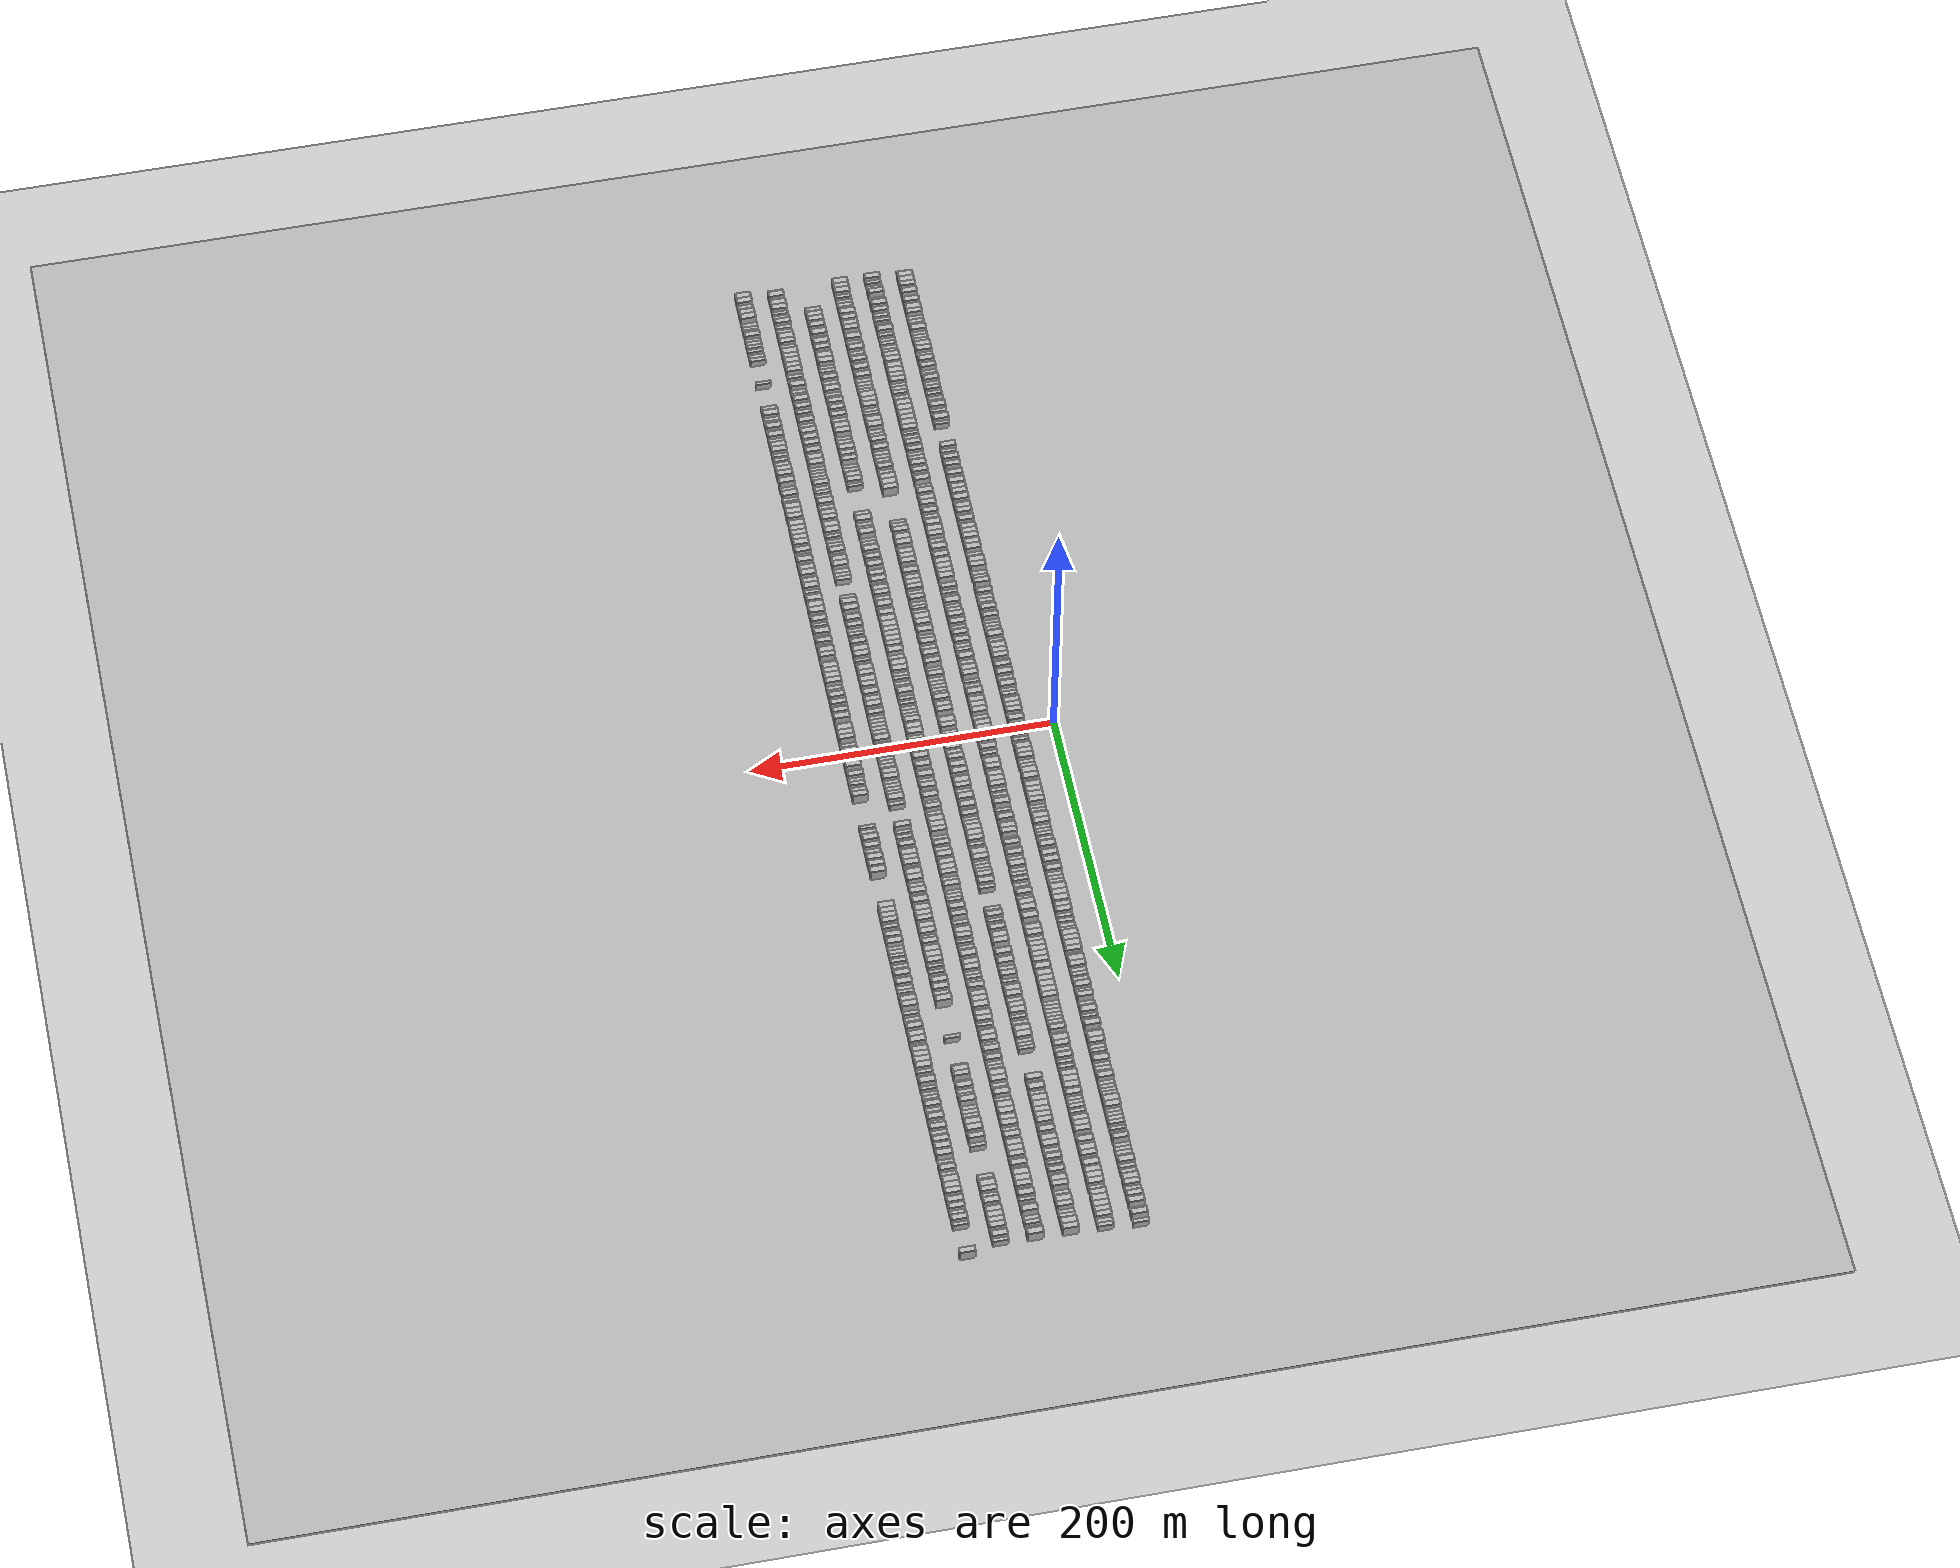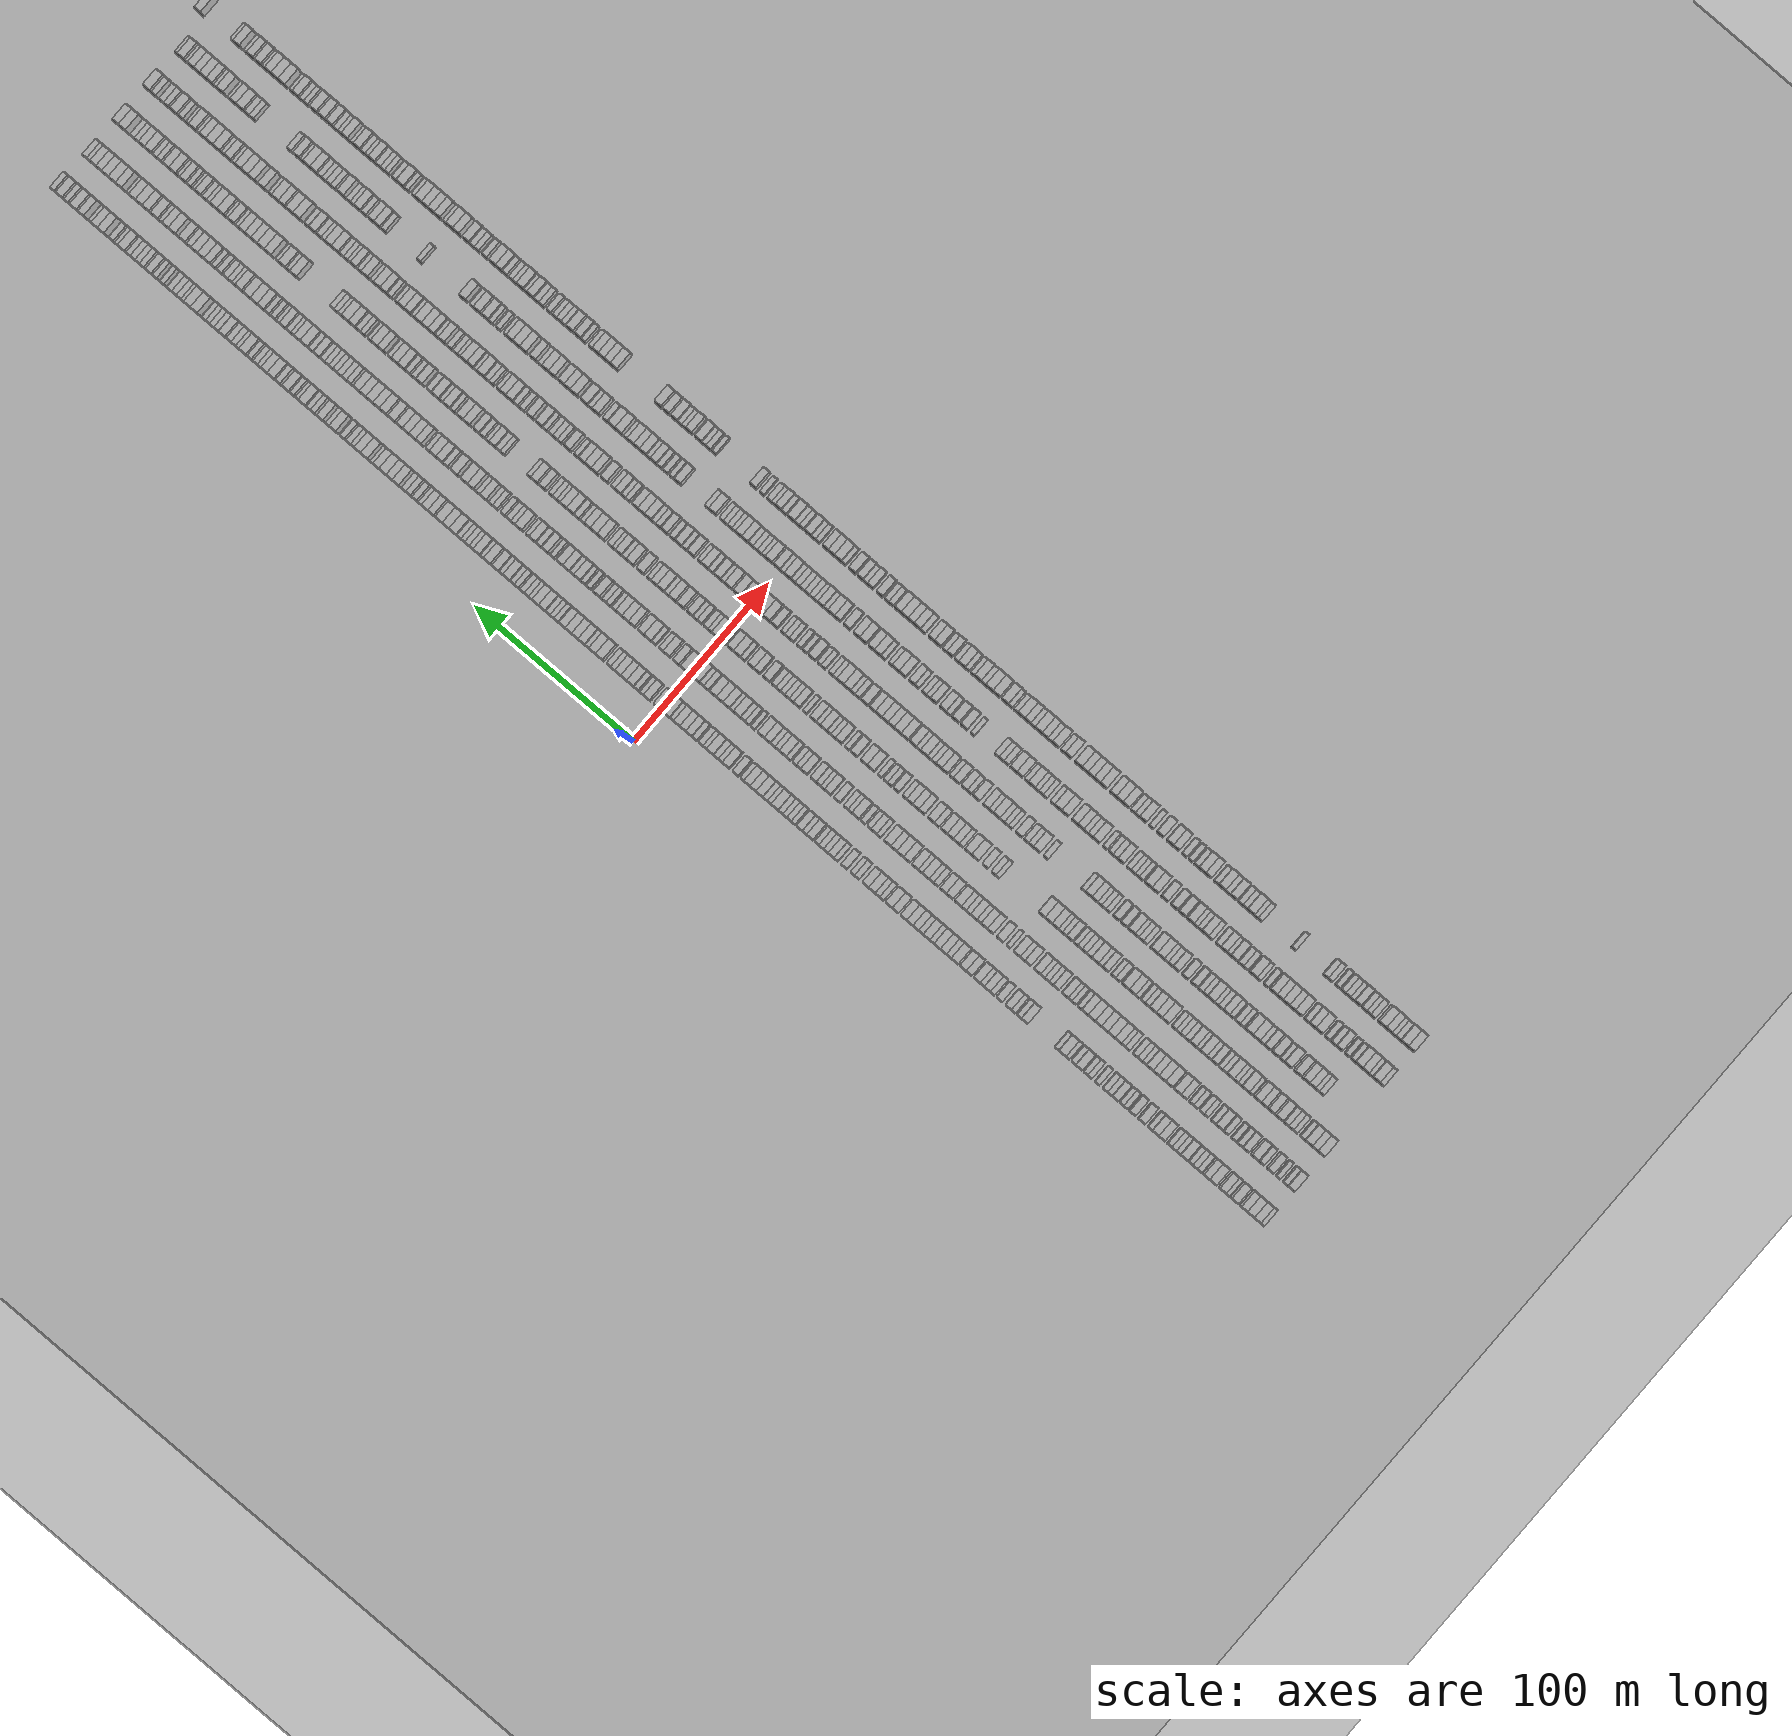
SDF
<?xml version="1.0" encoding="utf-8"?>

<sdf version="1.6">

   <world name="default">

      <gui fullscreen="0">

         <camera name="user_camera">

            <pose>-15 0 4.57585 0 0 0</pose>

            <view_controller>orbit</view_controller>

         </camera>

      </gui>

      <scene>

         <sky>

           <clouds>

             <speed>12</speed>

           </clouds>

         </sky>

         <ambient>0.4 0.4 0.4 1</ambient>

         <background>0.7 0.7 0.7 1</background>

         <shadows>1</shadows>

      </scene>

      <gravity>0 0 -9.8066</gravity>

      <magnetic_field>6e-06 2.3e-05 -4.2e-05</magnetic_field>

      <physics default="0" name="default_physics" type="ode">

         <ode>

            <solver>

               <type>quick</type>

               <iters>10</iters>

               <sor>1.0</sor>

               <use_dynamic_moi_rescaling>0</use_dynamic_moi_rescaling>

            </solver>

            <constraints>

               <cfm>0</cfm>

               <erp>0.2</erp>

               <contact_max_correcting_vel>100</contact_max_correcting_vel>

               <contact_surface_layer>0.001</contact_surface_layer>

            </constraints>

         </ode>

         <max_step_size>0.004</max_step_size>

         <real_time_factor>1</real_time_factor>

         <real_time_update_rate>250</real_time_update_rate>

      </physics>

      <light name="sun" type="directional">

         <cast_shadows>1</cast_shadows>

         <pose>0 0 10 0 0 0</pose>

         <diffuse>0.8 0.8 0.8 1</diffuse>

         <specular>0.2 0.2 0.2 1</specular>

         <attenuation>

            <range>1000</range>

            <constant>0.9</constant>

            <linear>0.01</linear>

            <quadratic>0.001</quadratic>

         </attenuation>

         <direction>-0.5 0.1 -0.9</direction>

      </light>

      <include>

         <name>ground_plane_1</name>

         <uri>model://HANNAS_ground_plane</uri>

         <pose>0 0 0  0 0 0</pose>

      </include>

      <include>

         <name>ground_plane_2</name>

         <uri>model://HANNAS_ground_plane</uri>

         <pose>100 0 0  0 0 0</pose>

      </include>

      <model name="building_1">

         <static>1</static>

         <pose frame="">25.0000 -378.6912 0 0.000000 0.000000 0.000000</pose>

         <link name="link">

            <pose frame="">0 0 3.00 0 0 0</pose>

            <collision name="collision">

               <geometry>

                  <box>

                     <size>10.0000 2.6176 6.0000</size>

                  </box>

               </geometry>

               <max_contacts>10</max_contacts>

               <surface>

                  <contact>

                     <ode/>

                  </contact>

                  <bounce/>

                  <friction>

                     <torsional>

                        <ode/>

                     </torsional>

                     <ode/>

                  </friction>

               </surface>

            </collision>

            <visual name="visual">

               <cast_shadows>0</cast_shadows>

               <geometry>

                  <box>

                     <size>10.0000 2.6176 6.0000</size>

                  </box>

               </geometry>

               <material>

                  <script>

                     <uri>model://HANNAS_wall/materials/scripts</uri>

                     <uri>model://HANNAS_wall/materials/textures</uri>

                     <name>vrc/HANNAS_wall</name>

                  </script>

               </material>

            </visual>

            <self_collide>0</self_collide>

            <enable_wind>0</enable_wind>

            <kinematic>0</kinematic>

         </link>

      </model>

      <model name="building_2">

         <static>1</static>

         <pose frame="">25.0000 -375.3411 0 0.000000 0.000000 0.000000</pose>

         <link name="link">

            <pose frame="">0 0 4.50 0 0 0</pose>

            <collision name="collision">

               <geometry>

                  <box>

                     <size>10.0000 4.0825 9.0000</size>

                  </box>

               </geometry>

               <max_contacts>10</max_contacts>

               <surface>

                  <contact>

                     <ode/>

                  </contact>

                  <bounce/>

                  <friction>

                     <torsional>

                        <ode/>

                     </torsional>

                     <ode/>

                  </friction>

               </surface>

            </collision>

            <visual name="visual">

               <cast_shadows>0</cast_shadows>

               <geometry>

                  <box>

                     <size>10.0000 4.0825 9.0000</size>

                  </box>

               </geometry>

               <material>

                  <script>

                     <uri>model://HANNAS_wall/materials/scripts</uri>

                     <uri>model://HANNAS_wall/materials/textures</uri>

                     <name>vrc/HANNAS_wall</name>

                  </script>

               </material>

            </visual>

            <self_collide>0</self_collide>

            <enable_wind>0</enable_wind>

            <kinematic>0</kinematic>

         </link>

      </model>

      <model name="building_3">

         <static>1</static>

         <pose frame="">25.0000 -371.1392 0 0.000000 0.000000 0.000000</pose>

         <link name="link">

            <pose frame="">0 0 4.50 0 0 0</pose>

            <collision name="collision">

               <geometry>

                  <box>

                     <size>10.0000 4.3214 9.0000</size>

                  </box>

               </geometry>

               <max_contacts>10</max_contacts>

               <surface>

                  <contact>

                     <ode/>

                  </contact>

                  <bounce/>

                  <friction>

                     <torsional>

                        <ode/>

                     </torsional>

                     <ode/>

                  </friction>

               </surface>

            </collision>

            <visual name="visual">

               <cast_shadows>0</cast_shadows>

               <geometry>

                  <box>

                     <size>10.0000 4.3214 9.0000</size>

                  </box>

               </geometry>

               <material>

                  <script>

                     <uri>model://HANNAS_wall/materials/scripts</uri>

                     <uri>model://HANNAS_wall/materials/textures</uri>

                     <name>vrc/HANNAS_wall</name>

                  </script>

               </material>

            </visual>

            <self_collide>0</self_collide>

            <enable_wind>0</enable_wind>

            <kinematic>0</kinematic>

         </link>

      </model>

      <model name="building_4">

         <static>1</static>

         <pose frame="">25.0000 -367.1172 0 0.000000 0.000000 0.000000</pose>

         <link name="link">

            <pose frame="">0 0 4.50 0 0 0</pose>

            <collision name="collision">

               <geometry>

                  <box>

                     <size>10.0000 3.7226 9.0000</size>

                  </box>

               </geometry>

               <max_contacts>10</max_contacts>

               <surface>

                  <contact>

                     <ode/>

                  </contact>

                  <bounce/>

                  <friction>

                     <torsional>

                        <ode/>

                     </torsional>

                     <ode/>

                  </friction>

               </surface>

            </collision>

            <visual name="visual">

               <cast_shadows>0</cast_shadows>

               <geometry>

                  <box>

                     <size>10.0000 3.7226 9.0000</size>

                  </box>

               </geometry>

               <material>

                  <script>

                     <uri>model://HANNAS_wall/materials/scripts</uri>

                     <uri>model://HANNAS_wall/materials/textures</uri>

                     <name>vrc/HANNAS_wall</name>

                  </script>

               </material>

            </visual>

            <self_collide>0</self_collide>

            <enable_wind>0</enable_wind>

            <kinematic>0</kinematic>

         </link>

      </model>

      <model name="building_5">

         <static>1</static>

         <pose frame="">25.0000 -361.1929 0 0.000000 0.000000 0.000000</pose>

         <link name="link">

            <pose frame="">0 0 4.50 0 0 0</pose>

            <collision name="collision">

               <geometry>

                  <box>

                     <size>10.0000 4.1260 9.0000</size>

                  </box>

               </geometry>

               <max_contacts>10</max_contacts>

               <surface>

                  <contact>

                     <ode/>

                  </contact>

                  <bounce/>

                  <friction>

                     <torsional>

                        <ode/>

                     </torsional>

                     <ode/>

                  </friction>

               </surface>

            </collision>

            <visual name="visual">

               <cast_shadows>0</cast_shadows>

               <geometry>

                  <box>

                     <size>10.0000 4.1260 9.0000</size>

                  </box>

               </geometry>

               <material>

                  <script>

                     <uri>model://HANNAS_wall/materials/scripts</uri>

                     <uri>model://HANNAS_wall/materials/textures</uri>

                     <name>vrc/HANNAS_wall</name>

                  </script>

               </material>

            </visual>

            <self_collide>0</self_collide>

            <enable_wind>0</enable_wind>

            <kinematic>0</kinematic>

         </link>

      </model>

      <model name="building_6">

         <static>1</static>

         <pose frame="">25.0000 -356.8870 0 0.000000 0.000000 0.000000</pose>

         <link name="link">

            <pose frame="">0 0 3.00 0 0 0</pose>

            <collision name="collision">

               <geometry>

                  <box>

                     <size>10.0000 2.4858 6.0000</size>

                  </box>

               </geometry>

               <max_contacts>10</max_contacts>

               <surface>

                  <contact>

                     <ode/>

                  </contact>

                  <bounce/>

                  <friction>

                     <torsional>

                        <ode/>

                     </torsional>

                     <ode/>

                  </friction>

               </surface>

            </collision>

            <visual name="visual">

               <cast_shadows>0</cast_shadows>

               <geometry>

                  <box>

                     <size>10.0000 2.4858 6.0000</size>

                  </box>

               </geometry>

               <material>

                  <script>

                     <uri>model://HANNAS_wall/materials/scripts</uri>

                     <uri>model://HANNAS_wall/materials/textures</uri>

                     <name>vrc/HANNAS_wall</name>

                  </script>

               </material>

            </visual>

            <self_collide>0</self_collide>

            <enable_wind>0</enable_wind>

            <kinematic>0</kinematic>

         </link>

      </model>

      <model name="building_7">

         <static>1</static>

         <pose frame="">25.0000 -353.6732 0 0.000000 0.000000 0.000000</pose>

         <link name="link">

            <pose frame="">0 0 4.50 0 0 0</pose>

            <collision name="collision">

               <geometry>

                  <box>

                     <size>10.0000 3.9420 9.0000</size>

                  </box>

               </geometry>

               <max_contacts>10</max_contacts>

               <surface>

                  <contact>

                     <ode/>

                  </contact>

                  <bounce/>

                  <friction>

                     <torsional>

                        <ode/>

                     </torsional>

                     <ode/>

                  </friction>

               </surface>

            </collision>

            <visual name="visual">

               <cast_shadows>0</cast_shadows>

               <geometry>

                  <box>

                     <size>10.0000 3.9420 9.0000</size>

                  </box>

               </geometry>

               <material>

                  <script>

                     <uri>model://HANNAS_wall/materials/scripts</uri>

                     <uri>model://HANNAS_wall/materials/textures</uri>

                     <name>vrc/HANNAS_wall</name>

                  </script>

               </material>

            </visual>

            <self_collide>0</self_collide>

            <enable_wind>0</enable_wind>

            <kinematic>0</kinematic>

         </link>

      </model>

      <model name="building_8">

         <static>1</static>

         <pose frame="">25.0000 -347.4887 0 0.000000 0.000000 0.000000</pose>

         <link name="link">

            <pose frame="">0 0 4.50 0 0 0</pose>

            <collision name="collision">

               <geometry>

                  <box>

                     <size>10.0000 4.4270 9.0000</size>

                  </box>

               </geometry>

               <max_contacts>10</max_contacts>

               <surface>

                  <contact>

                     <ode/>

                  </contact>

                  <bounce/>

                  <friction>

                     <torsional>

                        <ode/>

                     </torsional>

                     <ode/>

                  </friction>

               </surface>

            </collision>

            <visual name="visual">

               <cast_shadows>0</cast_shadows>

               <geometry>

                  <box>

                     <size>10.0000 4.4270 9.0000</size>

                  </box>

               </geometry>

               <material>

                  <script>

                     <uri>model://HANNAS_wall/materials/scripts</uri>

                     <uri>model://HANNAS_wall/materials/textures</uri>

                     <name>vrc/HANNAS_wall</name>

                  </script>

               </material>

            </visual>

            <self_collide>0</self_collide>

            <enable_wind>0</enable_wind>

            <kinematic>0</kinematic>

         </link>

      </model>

      <model name="building_9">

         <static>1</static>

         <pose frame="">25.0000 -343.4732 0 0.000000 0.000000 0.000000</pose>

         <link name="link">

            <pose frame="">0 0 4.50 0 0 0</pose>

            <collision name="collision">

               <geometry>

                  <box>

                     <size>10.0000 3.6041 9.0000</size>

                  </box>

               </geometry>

               <max_contacts>10</max_contacts>

               <surface>

                  <contact>

                     <ode/>

                  </contact>

                  <bounce/>

                  <friction>

                     <torsional>

                        <ode/>

                     </torsional>

                     <ode/>

                  </friction>

               </surface>

            </collision>

            <visual name="visual">

               <cast_shadows>0</cast_shadows>

               <geometry>

                  <box>

                     <size>10.0000 3.6041 9.0000</size>

                  </box>

               </geometry>

               <material>

                  <script>

                     <uri>model://HANNAS_wall/materials/scripts</uri>

                     <uri>model://HANNAS_wall/materials/textures</uri>

                     <name>vrc/HANNAS_wall</name>

                  </script>

               </material>

            </visual>

            <self_collide>0</self_collide>

            <enable_wind>0</enable_wind>

            <kinematic>0</kinematic>

         </link>

      </model>

      <model name="building_10">

         <static>1</static>

         <pose frame="">25.0000 -339.3185 0 0.000000 0.000000 0.000000</pose>

         <link name="link">

            <pose frame="">0 0 3.00 0 0 0</pose>

            <collision name="collision">

               <geometry>

                  <box>

                     <size>10.0000 2.7053 6.0000</size>

                  </box>

               </geometry>

               <max_contacts>10</max_contacts>

               <surface>

                  <contact>

                     <ode/>

                  </contact>

                  <bounce/>

                  <friction>

                     <torsional>

                        <ode/>

                     </torsional>

                     <ode/>

                  </friction>

               </surface>

            </collision>

            <visual name="visual">

               <cast_shadows>0</cast_shadows>

               <geometry>

                  <box>

                     <size>10.0000 2.7053 6.0000</size>

                  </box>

               </geometry>

               <material>

                  <script>

                     <uri>model://HANNAS_wall/materials/scripts</uri>

                     <uri>model://HANNAS_wall/materials/textures</uri>

                     <name>vrc/HANNAS_wall</name>

                  </script>

               </material>

            </visual>

            <self_collide>0</self_collide>

            <enable_wind>0</enable_wind>

            <kinematic>0</kinematic>

         </link>

      </model>

      <model name="building_11">

         <static>1</static>

         <pose frame="">25.0000 -336.5195 0 0.000000 0.000000 0.000000</pose>

         <link name="link">

            <pose frame="">0 0 3.00 0 0 0</pose>

            <collision name="collision">

               <geometry>

                  <box>

                     <size>10.0000 2.8926 6.0000</size>

                  </box>

               </geometry>

               <max_contacts>10</max_contacts>

               <surface>

                  <contact>

                     <ode/>

                  </contact>

                  <bounce/>

                  <friction>

                     <torsional>

                        <ode/>

                     </torsional>

                     <ode/>

                  </friction>

               </surface>

            </collision>

            <visual name="visual">

               <cast_shadows>0</cast_shadows>

               <geometry>

                  <box>

                     <size>10.0000 2.8926 6.0000</size>

                  </box>

               </geometry>

               <material>

                  <script>

                     <uri>model://HANNAS_wall/materials/scripts</uri>

                     <uri>model://HANNAS_wall/materials/textures</uri>

                     <name>vrc/HANNAS_wall</name>

                  </script>

               </material>

            </visual>

            <self_collide>0</self_collide>

            <enable_wind>0</enable_wind>

            <kinematic>0</kinematic>

         </link>

      </model>

      <model name="building_12">

         <static>1</static>

         <pose frame="">25.0000 -333.7677 0 0.000000 0.000000 0.000000</pose>

         <link name="link">

            <pose frame="">0 0 3.00 0 0 0</pose>

            <collision name="collision">

               <geometry>

                  <box>

                     <size>10.0000 2.6109 6.0000</size>

                  </box>

               </geometry>

               <max_contacts>10</max_contacts>

               <surface>

                  <contact>

                     <ode/>

                  </contact>

                  <bounce/>

                  <friction>

                     <torsional>

                        <ode/>

                     </torsional>

                     <ode/>

                  </friction>

               </surface>

            </collision>

            <visual name="visual">

               <cast_shadows>0</cast_shadows>

               <geometry>

                  <box>

                     <size>10.0000 2.6109 6.0000</size>

                  </box>

               </geometry>

               <material>

                  <script>

                     <uri>model://HANNAS_wall/materials/scripts</uri>

                     <uri>model://HANNAS_wall/materials/textures</uri>

                     <name>vrc/HANNAS_wall</name>

                  </script>

               </material>

            </visual>

            <self_collide>0</self_collide>

            <enable_wind>0</enable_wind>

            <kinematic>0</kinematic>

         </link>

      </model>

      <model name="building_13">

         <static>1</static>

         <pose frame="">25.0000 -329.3393 0 0.000000 0.000000 0.000000</pose>

         <link name="link">

            <pose frame="">0 0 4.50 0 0 0</pose>

            <collision name="collision">

               <geometry>

                  <box>

                     <size>10.0000 4.2459 9.0000</size>

                  </box>

               </geometry>

               <max_contacts>10</max_contacts>

               <surface>

                  <contact>

                     <ode/>

                  </contact>

                  <bounce/>

                  <friction>

                     <torsional>

                        <ode/>

                     </torsional>

                     <ode/>

                  </friction>

               </surface>

            </collision>

            <visual name="visual">

               <cast_shadows>0</cast_shadows>

               <geometry>

                  <box>

                     <size>10.0000 4.2459 9.0000</size>

                  </box>

               </geometry>

               <material>

                  <script>

                     <uri>model://HANNAS_wall/materials/scripts</uri>

                     <uri>model://HANNAS_wall/materials/textures</uri>

                     <name>vrc/HANNAS_wall</name>

                  </script>

               </material>

            </visual>

            <self_collide>0</self_collide>

            <enable_wind>0</enable_wind>

            <kinematic>0</kinematic>

         </link>

      </model>

      <model name="building_14">

         <static>1</static>

         <pose frame="">25.0000 -325.9310 0 0.000000 0.000000 0.000000</pose>

         <link name="link">

            <pose frame="">0 0 3.00 0 0 0</pose>

            <collision name="collision">

               <geometry>

                  <box>

                     <size>10.0000 2.5707 6.0000</size>

                  </box>

               </geometry>

               <max_contacts>10</max_contacts>

               <surface>

                  <contact>

                     <ode/>

                  </contact>

                  <bounce/>

                  <friction>

                     <torsional>

                        <ode/>

                     </torsional>

                     <ode/>

                  </friction>

               </surface>

            </collision>

            <visual name="visual">

               <cast_shadows>0</cast_shadows>

               <geometry>

                  <box>

                     <size>10.0000 2.5707 6.0000</size>

                  </box>

               </geometry>

               <material>

                  <script>

                     <uri>model://HANNAS_wall/materials/scripts</uri>

                     <uri>model://HANNAS_wall/materials/textures</uri>

                     <name>vrc/HANNAS_wall</name>

                  </script>

               </material>

            </visual>

            <self_collide>0</self_collide>

            <enable_wind>0</enable_wind>

            <kinematic>0</kinematic>

         </link>

      </model>

      <model name="building_15">

         <static>1</static>

         <pose frame="">25.0000 -323.2511 0 0.000000 0.000000 0.000000</pose>

         <link name="link">

            <pose frame="">0 0 3.00 0 0 0</pose>

            <collision name="collision">

               <geometry>

                  <box>

                     <size>10.0000 2.7890 6.0000</size>

                  </box>

               </geometry>

               <max_contacts>10</max_contacts>

               <surface>

                  <contact>

                     <ode/>

                  </contact>

                  <bounce/>

                  <friction>

                     <torsional>

                        <ode/>

                     </torsional>

                     <ode/>

                  </friction>

               </surface>

            </collision>

            <visual name="visual">

               <cast_shadows>0</cast_shadows>

               <geometry>

                  <box>

                     <size>10.0000 2.7890 6.0000</size>

                  </box>

               </geometry>

               <material>

                  <script>

                     <uri>model://HANNAS_wall/materials/scripts</uri>

                     <uri>model://HANNAS_wall/materials/textures</uri>

                     <name>vrc/HANNAS_wall</name>

                  </script>

               </material>

            </visual>

            <self_collide>0</self_collide>

            <enable_wind>0</enable_wind>

            <kinematic>0</kinematic>

         </link>

      </model>

      <model name="building_16">

         <static>1</static>

         <pose frame="">25.0000 -320.5339 0 0.000000 0.000000 0.000000</pose>

         <link name="link">

            <pose frame="">0 0 3.00 0 0 0</pose>

            <collision name="collision">

               <geometry>

                  <box>

                     <size>10.0000 2.6454 6.0000</size>

                  </box>

               </geometry>

               <max_contacts>10</max_contacts>

               <surface>

                  <contact>

                     <ode/>

                  </contact>

                  <bounce/>

                  <friction>

                     <torsional>

                        <ode/>

                     </torsional>

                     <ode/>

                  </friction>

               </surface>

            </collision>

            <visual name="visual">

               <cast_shadows>0</cast_shadows>

               <geometry>

                  <box>

                     <size>10.0000 2.6454 6.0000</size>

                  </box>

               </geometry>

               <material>

                  <script>

                     <uri>model://HANNAS_wall/materials/scripts</uri>

                     <uri>model://HANNAS_wall/materials/textures</uri>

                     <name>vrc/HANNAS_wall</name>

                  </script>

               </material>

            </visual>

            <self_collide>0</self_collide>

            <enable_wind>0</enable_wind>

            <kinematic>0</kinematic>

         </link>

      </model>

      <model name="building_17">

         <static>1</static>

         <pose frame="">25.0000 -315.2770 0 0.000000 0.000000 0.000000</pose>

         <link name="link">

            <pose frame="">0 0 4.50 0 0 0</pose>

            <collision name="collision">

               <geometry>

                  <box>

                     <size>10.0000 3.8684 9.0000</size>

                  </box>

               </geometry>

               <max_contacts>10</max_contacts>

               <surface>

                  <contact>

                     <ode/>

                  </contact>

                  <bounce/>

                  <friction>

                     <torsional>

                        <ode/>

                     </torsional>

                     <ode/>

                  </friction>

               </surface>

            </collision>

            <visual name="visual">

               <cast_shadows>0</cast_shadows>

               <geometry>

                  <box>

                     <size>10.0000 3.8684 9.0000</size>

                  </box>

               </geometry>

               <material>

                  <script>

                     <uri>model://HANNAS_wall/materials/scripts</uri>

                     <uri>model://HANNAS_wall/materials/textures</uri>

                     <name>vrc/HANNAS_wall</name>

                  </script>

               </material>

            </visual>

            <self_collide>0</self_collide>

            <enable_wind>0</enable_wind>

            <kinematic>0</kinematic>

         </link>

      </model>

      <model name="building_18">

         <static>1</static>

         <pose frame="">25.0000 -311.3818 0 0.000000 0.000000 0.000000</pose>

         <link name="link">

            <pose frame="">0 0 4.50 0 0 0</pose>

            <collision name="collision">

               <geometry>

                  <box>

                     <size>10.0000 3.9218 9.0000</size>

                  </box>

               </geometry>

               <max_contacts>10</max_contacts>

               <surface>

                  <contact>

                     <ode/>

                  </contact>

                  <bounce/>

                  <friction>

                     <torsional>

                        <ode/>

                     </torsional>

                     <ode/>

                  </friction>

               </surface>

            </collision>

            <visual name="visual">

               <cast_shadows>0</cast_shadows>

               <geometry>

                  <box>

                     <size>10.0000 3.9218 9.0000</size>

                  </box>

               </geometry>

               <material>

                  <script>

                     <uri>model://HANNAS_wall/materials/scripts</uri>

                     <uri>model://HANNAS_wall/materials/textures</uri>

                     <name>vrc/HANNAS_wall</name>

                  </script>

               </material>

            </visual>

            <self_collide>0</self_collide>

            <enable_wind>0</enable_wind>

            <kinematic>0</kinematic>

         </link>

      </model>

      <model name="building_19">

         <static>1</static>

         <pose frame="">25.0000 -308.1503 0 0.000000 0.000000 0.000000</pose>

         <link name="link">

            <pose frame="">0 0 3.00 0 0 0</pose>

            <collision name="collision">

               <geometry>

                  <box>

                     <size>10.0000 2.5412 6.0000</size>

                  </box>

               </geometry>

               <max_contacts>10</max_contacts>

               <surface>

                  <contact>

                     <ode/>

                  </contact>

                  <bounce/>

                  <friction>

                     <torsional>

                        <ode/>

                     </torsional>

                     <ode/>

                  </friction>

               </surface>

            </collision>

            <visual name="visual">

               <cast_shadows>0</cast_shadows>

               <geometry>

                  <box>

                     <size>10.0000 2.5412 6.0000</size>

                  </box>

               </geometry>

               <material>

                  <script>

                     <uri>model://HANNAS_wall/materials/scripts</uri>

                     <uri>model://HANNAS_wall/materials/textures</uri>

                     <name>vrc/HANNAS_wall</name>

                  </script>

               </material>

            </visual>

            <self_collide>0</self_collide>

            <enable_wind>0</enable_wind>

            <kinematic>0</kinematic>

         </link>

      </model>

      <model name="building_20">

         <static>1</static>

         <pose frame="">25.0000 -302.8381 0 0.000000 0.000000 0.000000</pose>

         <link name="link">

            <pose frame="">0 0 4.50 0 0 0</pose>

            <collision name="collision">

               <geometry>

                  <box>

                     <size>10.0000 4.0833 9.0000</size>

                  </box>

               </geometry>

               <max_contacts>10</max_contacts>

               <surface>

                  <contact>

                     <ode/>

                  </contact>

                  <bounce/>

                  <friction>

                     <torsional>

                        <ode/>

                     </torsional>

                     <ode/>

                  </friction>

               </surface>

            </collision>

            <visual name="visual">

               <cast_shadows>0</cast_shadows>

               <geometry>

                  <box>

                     <size>10.0000 4.0833 9.0000</size>

                  </box>

               </geometry>

               <material>

                  <script>

                     <uri>model://HANNAS_wall/materials/scripts</uri>

                     <uri>model://HANNAS_wall/materials/textures</uri>

                     <name>vrc/HANNAS_wall</name>

                  </script>

               </material>

            </visual>

            <self_collide>0</self_collide>

            <enable_wind>0</enable_wind>

            <kinematic>0</kinematic>

         </link>

      </model>

      <model name="building_21">

         <static>1</static>

         <pose frame="">25.0000 -296.9095 0 0.000000 0.000000 0.000000</pose>

         <link name="link">

            <pose frame="">0 0 4.50 0 0 0</pose>

            <collision name="collision">

               <geometry>

                  <box>

                     <size>10.0000 3.7738 9.0000</size>

                  </box>

               </geometry>

               <max_contacts>10</max_contacts>

               <surface>

                  <contact>

                     <ode/>

                  </contact>

                  <bounce/>

                  <friction>

                     <torsional>

                        <ode/>

                     </torsional>

                     <ode/>

                  </friction>

               </surface>

            </collision>

            <visual name="visual">

               <cast_shadows>0</cast_shadows>

               <geometry>

                  <box>

                     <size>10.0000 3.7738 9.0000</size>

                  </box>

               </geometry>

               <material>

                  <script>

                     <uri>model://HANNAS_wall/materials/scripts</uri>

                     <uri>model://HANNAS_wall/materials/textures</uri>

                     <name>vrc/HANNAS_wall</name>

                  </script>

               </material>

            </visual>

            <self_collide>0</self_collide>

            <enable_wind>0</enable_wind>

            <kinematic>0</kinematic>

         </link>

      </model>

      <model name="building_22">

         <static>1</static>

         <pose frame="">25.0000 -292.7571 0 0.000000 0.000000 0.000000</pose>

         <link name="link">

            <pose frame="">0 0 3.00 0 0 0</pose>

            <collision name="collision">

               <geometry>

                  <box>

                     <size>10.0000 2.5310 6.0000</size>

                  </box>

               </geometry>

               <max_contacts>10</max_contacts>

               <surface>

                  <contact>

                     <ode/>

                  </contact>

                  <bounce/>

                  <friction>

                     <torsional>

                        <ode/>

                     </torsional>

                     <ode/>

                  </friction>

               </surface>

            </collision>

            <visual name="visual">

               <cast_shadows>0</cast_shadows>

               <geometry>

                  <box>

                     <size>10.0000 2.5310 6.0000</size>

                  </box>

               </geometry>

               <material>

                  <script>

                     <uri>model://HANNAS_wall/materials/scripts</uri>

                     <uri>model://HANNAS_wall/materials/textures</uri>

                     <name>vrc/HANNAS_wall</name>

                  </script>

               </material>

            </visual>

            <self_collide>0</self_collide>

            <enable_wind>0</enable_wind>

            <kinematic>0</kinematic>

         </link>

      </model>

      <model name="building_23">

         <static>1</static>

         <pose frame="">25.0000 -290.2609 0 0.000000 0.000000 0.000000</pose>

         <link name="link">

            <pose frame="">0 0 3.00 0 0 0</pose>

            <collision name="collision">

               <geometry>

                  <box>

                     <size>10.0000 2.4615 6.0000</size>

                  </box>

               </geometry>

               <max_contacts>10</max_contacts>

               <surface>

                  <contact>

                     <ode/>

                  </contact>

                  <bounce/>

                  <friction>

                     <torsional>

                        <ode/>

                     </torsional>

                     <ode/>

                  </friction>

               </surface>

            </collision>

            <visual name="visual">

               <cast_shadows>0</cast_shadows>

               <geometry>

                  <box>

                     <size>10.0000 2.4615 6.0000</size>

                  </box>

               </geometry>

               <material>

                  <script>

                     <uri>model://HANNAS_wall/materials/scripts</uri>

                     <uri>model://HANNAS_wall/materials/textures</uri>

                     <name>vrc/HANNAS_wall</name>

                  </script>

               </material>

            </visual>

            <self_collide>0</self_collide>

            <enable_wind>0</enable_wind>

            <kinematic>0</kinematic>

         </link>

      </model>

      <model name="building_24">

         <static>1</static>

         <pose frame="">25.0000 -286.1268 0 0.000000 0.000000 0.000000</pose>

         <link name="link">

            <pose frame="">0 0 4.50 0 0 0</pose>

            <collision name="collision">

               <geometry>

                  <box>

                     <size>10.0000 3.8066 9.0000</size>

                  </box>

               </geometry>

               <max_contacts>10</max_contacts>

               <surface>

                  <contact>

                     <ode/>

                  </contact>

                  <bounce/>

                  <friction>

                     <torsional>

                        <ode/>

                     </torsional>

                     <ode/>

                  </friction>

               </surface>

            </collision>

            <visual name="visual">

               <cast_shadows>0</cast_shadows>

               <geometry>

                  <box>

                     <size>10.0000 3.8066 9.0000</size>

                  </box>

               </geometry>

               <material>

                  <script>

                     <uri>model://HANNAS_wall/materials/scripts</uri>

                     <uri>model://HANNAS_wall/materials/textures</uri>

                     <name>vrc/HANNAS_wall</name>

                  </script>

               </material>

            </visual>

            <self_collide>0</self_collide>

            <enable_wind>0</enable_wind>

            <kinematic>0</kinematic>

         </link>

      </model>

      <model name="building_25">

         <static>1</static>

         <pose frame="">25.0000 -282.8087 0 0.000000 0.000000 0.000000</pose>

         <link name="link">

            <pose frame="">0 0 3.00 0 0 0</pose>

            <collision name="collision">

               <geometry>

                  <box>

                     <size>10.0000 2.8295 6.0000</size>

                  </box>

               </geometry>

               <max_contacts>10</max_contacts>

               <surface>

                  <contact>

                     <ode/>

                  </contact>

                  <bounce/>

                  <friction>

                     <torsional>

                        <ode/>

                     </torsional>

                     <ode/>

                  </friction>

               </surface>

            </collision>

            <visual name="visual">

               <cast_shadows>0</cast_shadows>

               <geometry>

                  <box>

                     <size>10.0000 2.8295 6.0000</size>

                  </box>

               </geometry>

               <material>

                  <script>

                     <uri>model://HANNAS_wall/materials/scripts</uri>

                     <uri>model://HANNAS_wall/materials/textures</uri>

                     <name>vrc/HANNAS_wall</name>

                  </script>

               </material>

            </visual>

            <self_collide>0</self_collide>

            <enable_wind>0</enable_wind>

            <kinematic>0</kinematic>

         </link>

      </model>

      <model name="building_26">

         <static>1</static>

         <pose frame="">25.0000 -279.9445 0 0.000000 0.000000 0.000000</pose>

         <link name="link">

            <pose frame="">0 0 3.00 0 0 0</pose>

            <collision name="collision">

               <geometry>

                  <box>

                     <size>10.0000 2.8990 6.0000</size>

                  </box>

               </geometry>

               <max_contacts>10</max_contacts>

               <surface>

                  <contact>

                     <ode/>

                  </contact>

                  <bounce/>

                  <friction>

                     <torsional>

                        <ode/>

                     </torsional>

                     <ode/>

                  </friction>

               </surface>

            </collision>

            <visual name="visual">

               <cast_shadows>0</cast_shadows>

               <geometry>

                  <box>

                     <size>10.0000 2.8990 6.0000</size>

                  </box>

               </geometry>

               <material>

                  <script>

                     <uri>model://HANNAS_wall/materials/scripts</uri>

                     <uri>model://HANNAS_wall/materials/textures</uri>

                     <name>vrc/HANNAS_wall</name>

                  </script>

               </material>

            </visual>

            <self_collide>0</self_collide>

            <enable_wind>0</enable_wind>

            <kinematic>0</kinematic>

         </link>

      </model>

      <model name="building_27">

         <static>1</static>

         <pose frame="">25.0000 -275.0564 0 0.000000 0.000000 0.000000</pose>

         <link name="link">

            <pose frame="">0 0 3.00 0 0 0</pose>

            <collision name="collision">

               <geometry>

                  <box>

                     <size>10.0000 2.8771 6.0000</size>

                  </box>

               </geometry>

               <max_contacts>10</max_contacts>

               <surface>

                  <contact>

                     <ode/>

                  </contact>

                  <bounce/>

                  <friction>

                     <torsional>

                        <ode/>

                     </torsional>

                     <ode/>

                  </friction>

               </surface>

            </collision>

            <visual name="visual">

               <cast_shadows>0</cast_shadows>

               <geometry>

                  <box>

                     <size>10.0000 2.8771 6.0000</size>

                  </box>

               </geometry>

               <material>

                  <script>

                     <uri>model://HANNAS_wall/materials/scripts</uri>

                     <uri>model://HANNAS_wall/materials/textures</uri>

                     <name>vrc/HANNAS_wall</name>

                  </script>

               </material>

            </visual>

            <self_collide>0</self_collide>

            <enable_wind>0</enable_wind>

            <kinematic>0</kinematic>

         </link>

      </model>

      <model name="building_28">

         <static>1</static>

         <pose frame="">25.0000 -270.2912 0 0.000000 0.000000 0.000000</pose>

         <link name="link">

            <pose frame="">0 0 3.00 0 0 0</pose>

            <collision name="collision">

               <geometry>

                  <box>

                     <size>10.0000 2.6533 6.0000</size>

                  </box>

               </geometry>

               <max_contacts>10</max_contacts>

               <surface>

                  <contact>

                     <ode/>

                  </contact>

                  <bounce/>

                  <friction>

                     <torsional>

                        <ode/>

                     </torsional>

                     <ode/>

                  </friction>

               </surface>

            </collision>

            <visual name="visual">

               <cast_shadows>0</cast_shadows>

               <geometry>

                  <box>

                     <size>10.0000 2.6533 6.0000</size>

                  </box>

               </geometry>

               <material>

                  <script>

                     <uri>model://HANNAS_wall/materials/scripts</uri>

                     <uri>model://HANNAS_wall/materials/textures</uri>

                     <name>vrc/HANNAS_wall</name>

                  </script>

               </material>

            </visual>

            <self_collide>0</self_collide>

            <enable_wind>0</enable_wind>

            <kinematic>0</kinematic>

         </link>

      </model>

      <model name="building_29">

         <static>1</static>

         <pose frame="">25.0000 -267.6693 0 0.000000 0.000000 0.000000</pose>

         <link name="link">

            <pose frame="">0 0 3.00 0 0 0</pose>

            <collision name="collision">

               <geometry>

                  <box>

                     <size>10.0000 2.5907 6.0000</size>

                  </box>

               </geometry>

               <max_contacts>10</max_contacts>

               <surface>

                  <contact>

                     <ode/>

                  </contact>

                  <bounce/>

                  <friction>

                     <torsional>

                        <ode/>

                     </torsional>

                     <ode/>

                  </friction>

               </surface>

            </collision>

            <visual name="visual">

               <cast_shadows>0</cast_shadows>

               <geometry>

                  <box>

                     <size>10.0000 2.5907 6.0000</size>

                  </box>

               </geometry>

               <material>

                  <script>

                     <uri>model://HANNAS_wall/materials/scripts</uri>

                     <uri>model://HANNAS_wall/materials/textures</uri>

                     <name>vrc/HANNAS_wall</name>

                  </script>

               </material>

            </visual>

            <self_collide>0</self_collide>

            <enable_wind>0</enable_wind>

            <kinematic>0</kinematic>

         </link>

      </model>

      <model name="building_30">

         <static>1</static>

         <pose frame="">25.0000 -263.3270 0 0.000000 0.000000 0.000000</pose>

         <link name="link">

            <pose frame="">0 0 4.50 0 0 0</pose>

            <collision name="collision">

               <geometry>

                  <box>

                     <size>10.0000 4.0939 9.0000</size>

                  </box>

               </geometry>

               <max_contacts>10</max_contacts>

               <surface>

                  <contact>

                     <ode/>

                  </contact>

                  <bounce/>

                  <friction>

                     <torsional>

                        <ode/>

                     </torsional>

                     <ode/>

                  </friction>

               </surface>

            </collision>

            <visual name="visual">

               <cast_shadows>0</cast_shadows>

               <geometry>

                  <box>

                     <size>10.0000 4.0939 9.0000</size>

                  </box>

               </geometry>

               <material>

                  <script>

                     <uri>model://HANNAS_wall/materials/scripts</uri>

                     <uri>model://HANNAS_wall/materials/textures</uri>

                     <name>vrc/HANNAS_wall</name>

                  </script>

               </material>

            </visual>

            <self_collide>0</self_collide>

            <enable_wind>0</enable_wind>

            <kinematic>0</kinematic>

         </link>

      </model>

      <model name="building_31">

         <static>1</static>

         <pose frame="">25.0000 -259.9006 0 0.000000 0.000000 0.000000</pose>

         <link name="link">

            <pose frame="">0 0 3.00 0 0 0</pose>

            <collision name="collision">

               <geometry>

                  <box>

                     <size>10.0000 2.7589 6.0000</size>

                  </box>

               </geometry>

               <max_contacts>10</max_contacts>

               <surface>

                  <contact>

                     <ode/>

                  </contact>

                  <bounce/>

                  <friction>

                     <torsional>

                        <ode/>

                     </torsional>

                     <ode/>

                  </friction>

               </surface>

            </collision>

            <visual name="visual">

               <cast_shadows>0</cast_shadows>

               <geometry>

                  <box>

                     <size>10.0000 2.7589 6.0000</size>

                  </box>

               </geometry>

               <material>

                  <script>

                     <uri>model://HANNAS_wall/materials/scripts</uri>

                     <uri>model://HANNAS_wall/materials/textures</uri>

                     <name>vrc/HANNAS_wall</name>

                  </script>

               </material>

            </visual>

            <self_collide>0</self_collide>

            <enable_wind>0</enable_wind>

            <kinematic>0</kinematic>

         </link>

      </model>

      <model name="building_32">

         <static>1</static>

         <pose frame="">25.0000 -256.3173 0 0.000000 0.000000 0.000000</pose>

         <link name="link">

            <pose frame="">0 0 3.00 0 0 0</pose>

            <collision name="collision">

               <geometry>

                  <box>

                     <size>10.0000 2.4076 6.0000</size>

                  </box>

               </geometry>

               <max_contacts>10</max_contacts>

               <surface>

                  <contact>

                     <ode/>

                  </contact>

                  <bounce/>

                  <friction>

                     <torsional>

                        <ode/>

                     </torsional>

                     <ode/>

                  </friction>

               </surface>

            </collision>

            <visual name="visual">

               <cast_shadows>0</cast_shadows>

               <geometry>

                  <box>

                     <size>10.0000 2.4076 6.0000</size>

                  </box>

               </geometry>

               <material>

                  <script>

                     <uri>model://HANNAS_wall/materials/scripts</uri>

                     <uri>model://HANNAS_wall/materials/textures</uri>

                     <name>vrc/HANNAS_wall</name>

                  </script>

               </material>

            </visual>

            <self_collide>0</self_collide>

            <enable_wind>0</enable_wind>

            <kinematic>0</kinematic>

         </link>

      </model>

      <model name="building_33">

         <static>1</static>

         <pose frame="">25.0000 -252.8828 0 0.000000 0.000000 0.000000</pose>

         <link name="link">

            <pose frame="">0 0 4.50 0 0 0</pose>

            <collision name="collision">

               <geometry>

                  <box>

                     <size>10.0000 4.4615 9.0000</size>

                  </box>

               </geometry>

               <max_contacts>10</max_contacts>

               <surface>

                  <contact>

                     <ode/>

                  </contact>

                  <bounce/>

                  <friction>

                     <torsional>

                        <ode/>

                     </torsional>

                     <ode/>

                  </friction>

               </surface>

            </collision>

            <visual name="visual">

               <cast_shadows>0</cast_shadows>

               <geometry>

                  <box>

                     <size>10.0000 4.4615 9.0000</size>

                  </box>

               </geometry>

               <material>

                  <script>

                     <uri>model://HANNAS_wall/materials/scripts</uri>

                     <uri>model://HANNAS_wall/materials/textures</uri>

                     <name>vrc/HANNAS_wall</name>

                  </script>

               </material>

            </visual>

            <self_collide>0</self_collide>

            <enable_wind>0</enable_wind>

            <kinematic>0</kinematic>

         </link>

      </model>

      <model name="building_34">

         <static>1</static>

         <pose frame="">25.0000 -249.4488 0 0.000000 0.000000 0.000000</pose>

         <link name="link">

            <pose frame="">0 0 3.00 0 0 0</pose>

            <collision name="collision">

               <geometry>

                  <box>

                     <size>10.0000 2.4065 6.0000</size>

                  </box>

               </geometry>

               <max_contacts>10</max_contacts>

               <surface>

                  <contact>

                     <ode/>

                  </contact>

                  <bounce/>

                  <friction>

                     <torsional>

                        <ode/>

                     </torsional>

                     <ode/>

                  </friction>

               </surface>

            </collision>

            <visual name="visual">

               <cast_shadows>0</cast_shadows>

               <geometry>

                  <box>

                     <size>10.0000 2.4065 6.0000</size>

                  </box>

               </geometry>

               <material>

                  <script>

                     <uri>model://HANNAS_wall/materials/scripts</uri>

                     <uri>model://HANNAS_wall/materials/textures</uri>

                     <name>vrc/HANNAS_wall</name>

                  </script>

               </material>

            </visual>

            <self_collide>0</self_collide>

            <enable_wind>0</enable_wind>

            <kinematic>0</kinematic>

         </link>

      </model>

      <model name="building_35">

         <static>1</static>

         <pose frame="">25.0000 -229.1625 0 0.000000 0.000000 0.000000</pose>

         <link name="link">

            <pose frame="">0 0 4.50 0 0 0</pose>

            <collision name="collision">

               <geometry>

                  <box>

                     <size>10.0000 4.0554 9.0000</size>

                  </box>

               </geometry>

               <max_contacts>10</max_contacts>

               <surface>

                  <contact>

                     <ode/>

                  </contact>

                  <bounce/>

                  <friction>

                     <torsional>

                        <ode/>

                     </torsional>

                     <ode/>

                  </friction>

               </surface>

            </collision>

            <visual name="visual">

               <cast_shadows>0</cast_shadows>

               <geometry>

                  <box>

                     <size>10.0000 4.0554 9.0000</size>

                  </box>

               </geometry>

               <material>

                  <script>

                     <uri>model://HANNAS_wall/materials/scripts</uri>

                     <uri>model://HANNAS_wall/materials/textures</uri>

                     <name>vrc/HANNAS_wall</name>

                  </script>

               </material>

            </visual>

            <self_collide>0</self_collide>

            <enable_wind>0</enable_wind>

            <kinematic>0</kinematic>

         </link>

      </model>

      <model name="building_36">

         <static>1</static>

         <pose frame="">25.0000 -225.7986 0 0.000000 0.000000 0.000000</pose>

         <link name="link">

            <pose frame="">0 0 3.00 0 0 0</pose>

            <collision name="collision">

               <geometry>

                  <box>

                     <size>10.0000 2.6723 6.0000</size>

                  </box>

               </geometry>

               <max_contacts>10</max_contacts>

               <surface>

                  <contact>

                     <ode/>

                  </contact>

                  <bounce/>

                  <friction>

                     <torsional>

                        <ode/>

                     </torsional>

                     <ode/>

                  </friction>

               </surface>

            </collision>

            <visual name="visual">

               <cast_shadows>0</cast_shadows>

               <geometry>

                  <box>

                     <size>10.0000 2.6723 6.0000</size>

                  </box>

               </geometry>

               <material>

                  <script>

                     <uri>model://HANNAS_wall/materials/scripts</uri>

                     <uri>model://HANNAS_wall/materials/textures</uri>

                     <name>vrc/HANNAS_wall</name>

                  </script>

               </material>

            </visual>

            <self_collide>0</self_collide>

            <enable_wind>0</enable_wind>

            <kinematic>0</kinematic>

         </link>

      </model>

      <model name="building_37">

         <static>1</static>

         <pose frame="">25.0000 -222.1371 0 0.000000 0.000000 0.000000</pose>

         <link name="link">

            <pose frame="">0 0 3.00 0 0 0</pose>

            <collision name="collision">

               <geometry>

                  <box>

                     <size>10.0000 2.6507 6.0000</size>

                  </box>

               </geometry>

               <max_contacts>10</max_contacts>

               <surface>

                  <contact>

                     <ode/>

                  </contact>

                  <bounce/>

                  <friction>

                     <torsional>

                        <ode/>

                     </torsional>

                     <ode/>

                  </friction>

               </surface>

            </collision>

            <visual name="visual">

               <cast_shadows>0</cast_shadows>

               <geometry>

                  <box>

                     <size>10.0000 2.6507 6.0000</size>

                  </box>

               </geometry>

               <material>

                  <script>

                     <uri>model://HANNAS_wall/materials/scripts</uri>

                     <uri>model://HANNAS_wall/materials/textures</uri>

                     <name>vrc/HANNAS_wall</name>

                  </script>

               </material>

            </visual>

            <self_collide>0</self_collide>

            <enable_wind>0</enable_wind>

            <kinematic>0</kinematic>

         </link>

      </model>

      <model name="building_38">

         <static>1</static>

         <pose frame="">25.0000 -218.9650 0 0.000000 0.000000 0.000000</pose>

         <link name="link">

            <pose frame="">0 0 4.50 0 0 0</pose>

            <collision name="collision">

               <geometry>

                  <box>

                     <size>10.0000 3.6935 9.0000</size>

                  </box>

               </geometry>

               <max_contacts>10</max_contacts>

               <surface>

                  <contact>

                     <ode/>

                  </contact>

                  <bounce/>

                  <friction>

                     <torsional>

                        <ode/>

                     </torsional>

                     <ode/>

                  </friction>

               </surface>

            </collision>

            <visual name="visual">

               <cast_shadows>0</cast_shadows>

               <geometry>

                  <box>

                     <size>10.0000 3.6935 9.0000</size>

                  </box>

               </geometry>

               <material>

                  <script>

                     <uri>model://HANNAS_wall/materials/scripts</uri>

                     <uri>model://HANNAS_wall/materials/textures</uri>

                     <name>vrc/HANNAS_wall</name>

                  </script>

               </material>

            </visual>

            <self_collide>0</self_collide>

            <enable_wind>0</enable_wind>

            <kinematic>0</kinematic>

         </link>

      </model>

      <model name="building_39">

         <static>1</static>

         <pose frame="">25.0000 -213.2678 0 0.000000 0.000000 0.000000</pose>

         <link name="link">

            <pose frame="">0 0 4.50 0 0 0</pose>

            <collision name="collision">

               <geometry>

                  <box>

                     <size>10.0000 3.7010 9.0000</size>

                  </box>

               </geometry>

               <max_contacts>10</max_contacts>

               <surface>

                  <contact>

                     <ode/>

                  </contact>

                  <bounce/>

                  <friction>

                     <torsional>

                        <ode/>

                     </torsional>

                     <ode/>

                  </friction>

               </surface>

            </collision>

            <visual name="visual">

               <cast_shadows>0</cast_shadows>

               <geometry>

                  <box>

                     <size>10.0000 3.7010 9.0000</size>

                  </box>

               </geometry>

               <material>

                  <script>

                     <uri>model://HANNAS_wall/materials/scripts</uri>

                     <uri>model://HANNAS_wall/materials/textures</uri>

                     <name>vrc/HANNAS_wall</name>

                  </script>

               </material>

            </visual>

            <self_collide>0</self_collide>

            <enable_wind>0</enable_wind>

            <kinematic>0</kinematic>

         </link>

      </model>

      <model name="building_40">

         <static>1</static>

         <pose frame="">25.0000 -208.9994 0 0.000000 0.000000 0.000000</pose>

         <link name="link">

            <pose frame="">0 0 3.00 0 0 0</pose>

            <collision name="collision">

               <geometry>

                  <box>

                     <size>10.0000 2.8357 6.0000</size>

                  </box>

               </geometry>

               <max_contacts>10</max_contacts>

               <surface>

                  <contact>

                     <ode/>

                  </contact>

                  <bounce/>

                  <friction>

                     <torsional>

                        <ode/>

                     </torsional>

                     <ode/>

                  </friction>

               </surface>

            </collision>

            <visual name="visual">

               <cast_shadows>0</cast_shadows>

               <geometry>

                  <box>

                     <size>10.0000 2.8357 6.0000</size>

                  </box>

               </geometry>

               <material>

                  <script>

                     <uri>model://HANNAS_wall/materials/scripts</uri>

                     <uri>model://HANNAS_wall/materials/textures</uri>

                     <name>vrc/HANNAS_wall</name>

                  </script>

               </material>

            </visual>

            <self_collide>0</self_collide>

            <enable_wind>0</enable_wind>

            <kinematic>0</kinematic>

         </link>

      </model>

      <model name="building_41">

         <static>1</static>

         <pose frame="">25.0000 -205.6988 0 0.000000 0.000000 0.000000</pose>

         <link name="link">

            <pose frame="">0 0 4.50 0 0 0</pose>

            <collision name="collision">

               <geometry>

                  <box>

                     <size>10.0000 3.7655 9.0000</size>

                  </box>

               </geometry>

               <max_contacts>10</max_contacts>

               <surface>

                  <contact>

                     <ode/>

                  </contact>

                  <bounce/>

                  <friction>

                     <torsional>

                        <ode/>

                     </torsional>

                     <ode/>

                  </friction>

               </surface>

            </collision>

            <visual name="visual">

               <cast_shadows>0</cast_shadows>

               <geometry>

                  <box>

                     <size>10.0000 3.7655 9.0000</size>

                  </box>

               </geometry>

               <material>

                  <script>

                     <uri>model://HANNAS_wall/materials/scripts</uri>

                     <uri>model://HANNAS_wall/materials/textures</uri>

                     <name>vrc/HANNAS_wall</name>

                  </script>

               </material>

            </visual>

            <self_collide>0</self_collide>

            <enable_wind>0</enable_wind>

            <kinematic>0</kinematic>

         </link>

      </model>

      <model name="building_42">

         <static>1</static>

         <pose frame="">25.0000 -202.5046 0 0.000000 0.000000 0.000000</pose>

         <link name="link">

            <pose frame="">0 0 3.00 0 0 0</pose>

            <collision name="collision">

               <geometry>

                  <box>

                     <size>10.0000 2.6230 6.0000</size>

                  </box>

               </geometry>

               <max_contacts>10</max_contacts>

               <surface>

                  <contact>

                     <ode/>

                  </contact>

                  <bounce/>

                  <friction>

                     <torsional>

                        <ode/>

                     </torsional>

                     <ode/>

                  </friction>

               </surface>

            </collision>

            <visual name="visual">

               <cast_shadows>0</cast_shadows>

               <geometry>

                  <box>

                     <size>10.0000 2.6230 6.0000</size>

                  </box>

               </geometry>

               <material>

                  <script>

                     <uri>model://HANNAS_wall/materials/scripts</uri>

                     <uri>model://HANNAS_wall/materials/textures</uri>

                     <name>vrc/HANNAS_wall</name>

                  </script>

               </material>

            </visual>

            <self_collide>0</self_collide>

            <enable_wind>0</enable_wind>

            <kinematic>0</kinematic>

         </link>

      </model>

      <model name="building_43">

         <static>1</static>

         <pose frame="">25.0000 -199.1261 0 0.000000 0.000000 0.000000</pose>

         <link name="link">

            <pose frame="">0 0 4.50 0 0 0</pose>

            <collision name="collision">

               <geometry>

                  <box>

                     <size>10.0000 4.1340 9.0000</size>

                  </box>

               </geometry>

               <max_contacts>10</max_contacts>

               <surface>

                  <contact>

                     <ode/>

                  </contact>

                  <bounce/>

                  <friction>

                     <torsional>

                        <ode/>

                     </torsional>

                     <ode/>

                  </friction>

               </surface>

            </collision>

            <visual name="visual">

               <cast_shadows>0</cast_shadows>

               <geometry>

                  <box>

                     <size>10.0000 4.1340 9.0000</size>

                  </box>

               </geometry>

               <material>

                  <script>

                     <uri>model://HANNAS_wall/materials/scripts</uri>

                     <uri>model://HANNAS_wall/materials/textures</uri>

                     <name>vrc/HANNAS_wall</name>

                  </script>

               </material>

            </visual>

            <self_collide>0</self_collide>

            <enable_wind>0</enable_wind>

            <kinematic>0</kinematic>

         </link>

      </model>

      <model name="building_44">

         <static>1</static>

         <pose frame="">25.0000 -194.2344 0 0.000000 0.000000 0.000000</pose>

         <link name="link">

            <pose frame="">0 0 4.50 0 0 0</pose>

            <collision name="collision">

               <geometry>

                  <box>

                     <size>10.0000 3.6493 9.0000</size>

                  </box>

               </geometry>

               <max_contacts>10</max_contacts>

               <surface>

                  <contact>

                     <ode/>

                  </contact>

                  <bounce/>

                  <friction>

                     <torsional>

                        <ode/>

                     </torsional>

                     <ode/>

                  </friction>

               </surface>

            </collision>

            <visual name="visual">

               <cast_shadows>0</cast_shadows>

               <geometry>

                  <box>

                     <size>10.0000 3.6493 9.0000</size>

                  </box>

               </geometry>

               <material>

                  <script>

                     <uri>model://HANNAS_wall/materials/scripts</uri>

                     <uri>model://HANNAS_wall/materials/textures</uri>

                     <name>vrc/HANNAS_wall</name>

                  </script>

               </material>

            </visual>

            <self_collide>0</self_collide>

            <enable_wind>0</enable_wind>

            <kinematic>0</kinematic>

         </link>

      </model>

      <model name="building_45">

         <static>1</static>

         <pose frame="">25.0000 -190.3961 0 0.000000 0.000000 0.000000</pose>

         <link name="link">

            <pose frame="">0 0 4.50 0 0 0</pose>

            <collision name="collision">

               <geometry>

                  <box>

                     <size>10.0000 4.0273 9.0000</size>

                  </box>

               </geometry>

               <max_contacts>10</max_contacts>

               <surface>

                  <contact>

                     <ode/>

                  </contact>

                  <bounce/>

                  <friction>

                     <torsional>

                        <ode/>

                     </torsional>

                     <ode/>

                  </friction>

               </surface>

            </collision>

            <visual name="visual">

               <cast_shadows>0</cast_shadows>

               <geometry>

                  <box>

                     <size>10.0000 4.0273 9.0000</size>

                  </box>

               </geometry>

               <material>

                  <script>

                     <uri>model://HANNAS_wall/materials/scripts</uri>

                     <uri>model://HANNAS_wall/materials/textures</uri>

                     <name>vrc/HANNAS_wall</name>

                  </script>

               </material>

            </visual>

            <self_collide>0</self_collide>

            <enable_wind>0</enable_wind>

            <kinematic>0</kinematic>

         </link>

      </model>

      <model name="building_46">

         <static>1</static>

         <pose frame="">25.0000 -185.1937 0 0.000000 0.000000 0.000000</pose>

         <link name="link">

            <pose frame="">0 0 4.50 0 0 0</pose>

            <collision name="collision">

               <geometry>

                  <box>

                     <size>10.0000 4.3775 9.0000</size>

                  </box>

               </geometry>

               <max_contacts>10</max_contacts>

               <surface>

                  <contact>

                     <ode/>

                  </contact>

                  <bounce/>

                  <friction>

                     <torsional>

                        <ode/>

                     </torsional>

                     <ode/>

                  </friction>

               </surface>

            </collision>

            <visual name="visual">

               <cast_shadows>0</cast_shadows>

               <geometry>

                  <box>

                     <size>10.0000 4.3775 9.0000</size>

                  </box>

               </geometry>

               <material>

                  <script>

                     <uri>model://HANNAS_wall/materials/scripts</uri>

                     <uri>model://HANNAS_wall/materials/textures</uri>

                     <name>vrc/HANNAS_wall</name>

                  </script>

               </material>

            </visual>

            <self_collide>0</self_collide>

            <enable_wind>0</enable_wind>

            <kinematic>0</kinematic>

         </link>

      </model>

      <model name="building_47">

         <static>1</static>

         <pose frame="">25.0000 -181.5162 0 0.000000 0.000000 0.000000</pose>

         <link name="link">

            <pose frame="">0 0 3.00 0 0 0</pose>

            <collision name="collision">

               <geometry>

                  <box>

                     <size>10.0000 2.9776 6.0000</size>

                  </box>

               </geometry>

               <max_contacts>10</max_contacts>

               <surface>

                  <contact>

                     <ode/>

                  </contact>

                  <bounce/>

                  <friction>

                     <torsional>

                        <ode/>

                     </torsional>

                     <ode/>

                  </friction>

               </surface>

            </collision>

            <visual name="visual">

               <cast_shadows>0</cast_shadows>

               <geometry>

                  <box>

                     <size>10.0000 2.9776 6.0000</size>

                  </box>

               </geometry>

               <material>

                  <script>

                     <uri>model://HANNAS_wall/materials/scripts</uri>

                     <uri>model://HANNAS_wall/materials/textures</uri>

                     <name>vrc/HANNAS_wall</name>

                  </script>

               </material>

            </visual>

            <self_collide>0</self_collide>

            <enable_wind>0</enable_wind>

            <kinematic>0</kinematic>

         </link>

      </model>

      <model name="building_48">

         <static>1</static>

         <pose frame="">25.0000 -178.1098 0 0.000000 0.000000 0.000000</pose>

         <link name="link">

            <pose frame="">0 0 4.50 0 0 0</pose>

            <collision name="collision">

               <geometry>

                  <box>

                     <size>10.0000 3.8351 9.0000</size>

                  </box>

               </geometry>

               <max_contacts>10</max_contacts>

               <surface>

                  <contact>

                     <ode/>

                  </contact>

                  <bounce/>

                  <friction>

                     <torsional>

                        <ode/>

                     </torsional>

                     <ode/>

                  </friction>

               </surface>

            </collision>

            <visual name="visual">

               <cast_shadows>0</cast_shadows>

               <geometry>

                  <box>

                     <size>10.0000 3.8351 9.0000</size>

                  </box>

               </geometry>

               <material>

                  <script>

                     <uri>model://HANNAS_wall/materials/scripts</uri>

                     <uri>model://HANNAS_wall/materials/textures</uri>

                     <name>vrc/HANNAS_wall</name>

                  </script>

               </material>

            </visual>

            <self_collide>0</self_collide>

            <enable_wind>0</enable_wind>

            <kinematic>0</kinematic>

         </link>

      </model>

      <model name="building_49">

         <static>1</static>

         <pose frame="">25.0000 -174.2083 0 0.000000 0.000000 0.000000</pose>

         <link name="link">

            <pose frame="">0 0 4.50 0 0 0</pose>

            <collision name="collision">

               <geometry>

                  <box>

                     <size>10.0000 3.9678 9.0000</size>

                  </box>

               </geometry>

               <max_contacts>10</max_contacts>

               <surface>

                  <contact>

                     <ode/>

                  </contact>

                  <bounce/>

                  <friction>

                     <torsional>

                        <ode/>

                     </torsional>

                     <ode/>

                  </friction>

               </surface>

            </collision>

            <visual name="visual">

               <cast_shadows>0</cast_shadows>

               <geometry>

                  <box>

                     <size>10.0000 3.9678 9.0000</size>

                  </box>

               </geometry>

               <material>

                  <script>

                     <uri>model://HANNAS_wall/materials/scripts</uri>

                     <uri>model://HANNAS_wall/materials/textures</uri>

                     <name>vrc/HANNAS_wall</name>

                  </script>

               </material>

            </visual>

            <self_collide>0</self_collide>

            <enable_wind>0</enable_wind>

            <kinematic>0</kinematic>

         </link>

      </model>

      <model name="building_50">

         <static>1</static>

         <pose frame="">25.0000 -170.8766 0 0.000000 0.000000 0.000000</pose>

         <link name="link">

            <pose frame="">0 0 3.00 0 0 0</pose>

            <collision name="collision">

               <geometry>

                  <box>

                     <size>10.0000 2.6956 6.0000</size>

                  </box>

               </geometry>

               <max_contacts>10</max_contacts>

               <surface>

                  <contact>

                     <ode/>

                  </contact>

                  <bounce/>

                  <friction>

                     <torsional>

                        <ode/>

                     </torsional>

                     <ode/>

                  </friction>

               </surface>

            </collision>

            <visual name="visual">

               <cast_shadows>0</cast_shadows>

               <geometry>

                  <box>

                     <size>10.0000 2.6956 6.0000</size>

                  </box>

               </geometry>

               <material>

                  <script>

                     <uri>model://HANNAS_wall/materials/scripts</uri>

                     <uri>model://HANNAS_wall/materials/textures</uri>

                     <name>vrc/HANNAS_wall</name>

                  </script>

               </material>

            </visual>

            <self_collide>0</self_collide>

            <enable_wind>0</enable_wind>

            <kinematic>0</kinematic>

         </link>

      </model>

      <model name="building_51">

         <static>1</static>

         <pose frame="">25.0000 -167.4771 0 0.000000 0.000000 0.000000</pose>

         <link name="link">

            <pose frame="">0 0 4.50 0 0 0</pose>

            <collision name="collision">

               <geometry>

                  <box>

                     <size>10.0000 4.1034 9.0000</size>

                  </box>

               </geometry>

               <max_contacts>10</max_contacts>

               <surface>

                  <contact>

                     <ode/>

                  </contact>

                  <bounce/>

                  <friction>

                     <torsional>

                        <ode/>

                     </torsional>

                     <ode/>

                  </friction>

               </surface>

            </collision>

            <visual name="visual">

               <cast_shadows>0</cast_shadows>

               <geometry>

                  <box>

                     <size>10.0000 4.1034 9.0000</size>

                  </box>

               </geometry>

               <material>

                  <script>

                     <uri>model://HANNAS_wall/materials/scripts</uri>

                     <uri>model://HANNAS_wall/materials/textures</uri>

                     <name>vrc/HANNAS_wall</name>

                  </script>

               </material>

            </visual>

            <self_collide>0</self_collide>

            <enable_wind>0</enable_wind>

            <kinematic>0</kinematic>

         </link>

      </model>

      <model name="building_52">

         <static>1</static>

         <pose frame="">25.0000 -164.0249 0 0.000000 0.000000 0.000000</pose>

         <link name="link">

            <pose frame="">0 0 3.00 0 0 0</pose>

            <collision name="collision">

               <geometry>

                  <box>

                     <size>10.0000 2.8010 6.0000</size>

                  </box>

               </geometry>

               <max_contacts>10</max_contacts>

               <surface>

                  <contact>

                     <ode/>

                  </contact>

                  <bounce/>

                  <friction>

                     <torsional>

                        <ode/>

                     </torsional>

                     <ode/>

                  </friction>

               </surface>

            </collision>

            <visual name="visual">

               <cast_shadows>0</cast_shadows>

               <geometry>

                  <box>

                     <size>10.0000 2.8010 6.0000</size>

                  </box>

               </geometry>

               <material>

                  <script>

                     <uri>model://HANNAS_wall/materials/scripts</uri>

                     <uri>model://HANNAS_wall/materials/textures</uri>

                     <name>vrc/HANNAS_wall</name>

                  </script>

               </material>

            </visual>

            <self_collide>0</self_collide>

            <enable_wind>0</enable_wind>

            <kinematic>0</kinematic>

         </link>

      </model>

      <model name="building_53">

         <static>1</static>

         <pose frame="">25.0000 -160.7985 0 0.000000 0.000000 0.000000</pose>

         <link name="link">

            <pose frame="">0 0 4.50 0 0 0</pose>

            <collision name="collision">

               <geometry>

                  <box>

                     <size>10.0000 3.6519 9.0000</size>

                  </box>

               </geometry>

               <max_contacts>10</max_contacts>

               <surface>

                  <contact>

                     <ode/>

                  </contact>

                  <bounce/>

                  <friction>

                     <torsional>

                        <ode/>

                     </torsional>

                     <ode/>

                  </friction>

               </surface>

            </collision>

            <visual name="visual">

               <cast_shadows>0</cast_shadows>

               <geometry>

                  <box>

                     <size>10.0000 3.6519 9.0000</size>

                  </box>

               </geometry>

               <material>

                  <script>

                     <uri>model://HANNAS_wall/materials/scripts</uri>

                     <uri>model://HANNAS_wall/materials/textures</uri>

                     <name>vrc/HANNAS_wall</name>

                  </script>

               </material>

            </visual>

            <self_collide>0</self_collide>

            <enable_wind>0</enable_wind>

            <kinematic>0</kinematic>

         </link>

      </model>

      <model name="building_54">

         <static>1</static>

         <pose frame="">25.0000 -157.0509 0 0.000000 0.000000 0.000000</pose>

         <link name="link">

            <pose frame="">0 0 4.50 0 0 0</pose>

            <collision name="collision">

               <geometry>

                  <box>

                     <size>10.0000 3.8434 9.0000</size>

                  </box>

               </geometry>

               <max_contacts>10</max_contacts>

               <surface>

                  <contact>

                     <ode/>

                  </contact>

                  <bounce/>

                  <friction>

                     <torsional>

                        <ode/>

                     </torsional>

                     <ode/>

                  </friction>

               </surface>

            </collision>

            <visual name="visual">

               <cast_shadows>0</cast_shadows>

               <geometry>

                  <box>

                     <size>10.0000 3.8434 9.0000</size>

                  </box>

               </geometry>

               <material>

                  <script>

                     <uri>model://HANNAS_wall/materials/scripts</uri>

                     <uri>model://HANNAS_wall/materials/textures</uri>

                     <name>vrc/HANNAS_wall</name>

                  </script>

               </material>

            </visual>

            <self_collide>0</self_collide>

            <enable_wind>0</enable_wind>

            <kinematic>0</kinematic>

         </link>

      </model>

      <model name="building_55">

         <static>1</static>

         <pose frame="">25.0000 -153.0806 0 0.000000 0.000000 0.000000</pose>

         <link name="link">

            <pose frame="">0 0 4.50 0 0 0</pose>

            <collision name="collision">

               <geometry>

                  <box>

                     <size>10.0000 4.0971 9.0000</size>

                  </box>

               </geometry>

               <max_contacts>10</max_contacts>

               <surface>

                  <contact>

                     <ode/>

                  </contact>

                  <bounce/>

                  <friction>

                     <torsional>

                        <ode/>

                     </torsional>

                     <ode/>

                  </friction>

               </surface>

            </collision>

            <visual name="visual">

               <cast_shadows>0</cast_shadows>

               <geometry>

                  <box>

                     <size>10.0000 4.0971 9.0000</size>

                  </box>

               </geometry>

               <material>

                  <script>

                     <uri>model://HANNAS_wall/materials/scripts</uri>

                     <uri>model://HANNAS_wall/materials/textures</uri>

                     <name>vrc/HANNAS_wall</name>

                  </script>

               </material>

            </visual>

            <self_collide>0</self_collide>

            <enable_wind>0</enable_wind>

            <kinematic>0</kinematic>

         </link>

      </model>

      <model name="building_56">

         <static>1</static>

         <pose frame="">25.0000 -148.0749 0 0.000000 0.000000 0.000000</pose>

         <link name="link">

            <pose frame="">0 0 4.50 0 0 0</pose>

            <collision name="collision">

               <geometry>

                  <box>

                     <size>10.0000 3.9144 9.0000</size>

                  </box>

               </geometry>

               <max_contacts>10</max_contacts>

               <surface>

                  <contact>

                     <ode/>

                  </contact>

                  <bounce/>

                  <friction>

                     <torsional>

                        <ode/>

                     </torsional>

                     <ode/>

                  </friction>

               </surface>

            </collision>

            <visual name="visual">

               <cast_shadows>0</cast_shadows>

               <geometry>

                  <box>

                     <size>10.0000 3.9144 9.0000</size>

                  </box>

               </geometry>

               <material>

                  <script>

                     <uri>model://HANNAS_wall/materials/scripts</uri>

                     <uri>model://HANNAS_wall/materials/textures</uri>

                     <name>vrc/HANNAS_wall</name>

                  </script>

               </material>

            </visual>

            <self_collide>0</self_collide>

            <enable_wind>0</enable_wind>

            <kinematic>0</kinematic>

         </link>

      </model>

      <model name="building_57">

         <static>1</static>

         <pose frame="">25.0000 -143.8812 0 0.000000 0.000000 0.000000</pose>

         <link name="link">

            <pose frame="">0 0 4.50 0 0 0</pose>

            <collision name="collision">

               <geometry>

                  <box>

                     <size>10.0000 4.4731 9.0000</size>

                  </box>

               </geometry>

               <max_contacts>10</max_contacts>

               <surface>

                  <contact>

                     <ode/>

                  </contact>

                  <bounce/>

                  <friction>

                     <torsional>

                        <ode/>

                     </torsional>

                     <ode/>

                  </friction>

               </surface>

            </collision>

            <visual name="visual">

               <cast_shadows>0</cast_shadows>

               <geometry>

                  <box>

                     <size>10.0000 4.4731 9.0000</size>

                  </box>

               </geometry>

               <material>

                  <script>

                     <uri>model://HANNAS_wall/materials/scripts</uri>

                     <uri>model://HANNAS_wall/materials/textures</uri>

                     <name>vrc/HANNAS_wall</name>

                  </script>

               </material>

            </visual>

            <self_collide>0</self_collide>

            <enable_wind>0</enable_wind>

            <kinematic>0</kinematic>

         </link>

      </model>

      <model name="building_58">

         <static>1</static>

         <pose frame="">25.0000 -139.3415 0 0.000000 0.000000 0.000000</pose>

         <link name="link">

            <pose frame="">0 0 3.00 0 0 0</pose>

            <collision name="collision">

               <geometry>

                  <box>

                     <size>10.0000 2.6062 6.0000</size>

                  </box>

               </geometry>

               <max_contacts>10</max_contacts>

               <surface>

                  <contact>

                     <ode/>

                  </contact>

                  <bounce/>

                  <friction>

                     <torsional>

                        <ode/>

                     </torsional>

                     <ode/>

                  </friction>

               </surface>

            </collision>

            <visual name="visual">

               <cast_shadows>0</cast_shadows>

               <geometry>

                  <box>

                     <size>10.0000 2.6062 6.0000</size>

                  </box>

               </geometry>

               <material>

                  <script>

                     <uri>model://HANNAS_wall/materials/scripts</uri>

                     <uri>model://HANNAS_wall/materials/textures</uri>

                     <name>vrc/HANNAS_wall</name>

                  </script>

               </material>

            </visual>

            <self_collide>0</self_collide>

            <enable_wind>0</enable_wind>

            <kinematic>0</kinematic>

         </link>

      </model>

      <model name="building_59">

         <static>1</static>

         <pose frame="">25.0000 -136.6547 0 0.000000 0.000000 0.000000</pose>

         <link name="link">

            <pose frame="">0 0 3.00 0 0 0</pose>

            <collision name="collision">

               <geometry>

                  <box>

                     <size>10.0000 2.7674 6.0000</size>

                  </box>

               </geometry>

               <max_contacts>10</max_contacts>

               <surface>

                  <contact>

                     <ode/>

                  </contact>

                  <bounce/>

                  <friction>

                     <torsional>

                        <ode/>

                     </torsional>

                     <ode/>

                  </friction>

               </surface>

            </collision>

            <visual name="visual">

               <cast_shadows>0</cast_shadows>

               <geometry>

                  <box>

                     <size>10.0000 2.7674 6.0000</size>

                  </box>

               </geometry>

               <material>

                  <script>

                     <uri>model://HANNAS_wall/materials/scripts</uri>

                     <uri>model://HANNAS_wall/materials/textures</uri>

                     <name>vrc/HANNAS_wall</name>

                  </script>

               </material>

            </visual>

            <self_collide>0</self_collide>

            <enable_wind>0</enable_wind>

            <kinematic>0</kinematic>

         </link>

      </model>

      <model name="building_60">

         <static>1</static>

         <pose frame="">25.0000 -133.1952 0 0.000000 0.000000 0.000000</pose>

         <link name="link">

            <pose frame="">0 0 4.50 0 0 0</pose>

            <collision name="collision">

               <geometry>

                  <box>

                     <size>10.0000 4.1518 9.0000</size>

                  </box>

               </geometry>

               <max_contacts>10</max_contacts>

               <surface>

                  <contact>

                     <ode/>

                  </contact>

                  <bounce/>

                  <friction>

                     <torsional>

                        <ode/>

                     </torsional>

                     <ode/>

                  </friction>

               </surface>

            </collision>

            <visual name="visual">

               <cast_shadows>0</cast_shadows>

               <geometry>

                  <box>

                     <size>10.0000 4.1518 9.0000</size>

                  </box>

               </geometry>

               <material>

                  <script>

                     <uri>model://HANNAS_wall/materials/scripts</uri>

                     <uri>model://HANNAS_wall/materials/textures</uri>

                     <name>vrc/HANNAS_wall</name>

                  </script>

               </material>

            </visual>

            <self_collide>0</self_collide>

            <enable_wind>0</enable_wind>

            <kinematic>0</kinematic>

         </link>

      </model>

      <model name="building_61">

         <static>1</static>

         <pose frame="">25.0000 -129.1268 0 0.000000 0.000000 0.000000</pose>

         <link name="link">

            <pose frame="">0 0 4.50 0 0 0</pose>

            <collision name="collision">

               <geometry>

                  <box>

                     <size>10.0000 3.9849 9.0000</size>

                  </box>

               </geometry>

               <max_contacts>10</max_contacts>

               <surface>

                  <contact>

                     <ode/>

                  </contact>

                  <bounce/>

                  <friction>

                     <torsional>

                        <ode/>

                     </torsional>

                     <ode/>

                  </friction>

               </surface>

            </collision>

            <visual name="visual">

               <cast_shadows>0</cast_shadows>

               <geometry>

                  <box>

                     <size>10.0000 3.9849 9.0000</size>

                  </box>

               </geometry>

               <material>

                  <script>

                     <uri>model://HANNAS_wall/materials/scripts</uri>

                     <uri>model://HANNAS_wall/materials/textures</uri>

                     <name>vrc/HANNAS_wall</name>

                  </script>

               </material>

            </visual>

            <self_collide>0</self_collide>

            <enable_wind>0</enable_wind>

            <kinematic>0</kinematic>

         </link>

      </model>

      <model name="building_62">

         <static>1</static>

         <pose frame="">25.0000 -123.6595 0 0.000000 0.000000 0.000000</pose>

         <link name="link">

            <pose frame="">0 0 3.00 0 0 0</pose>

            <collision name="collision">

               <geometry>

                  <box>

                     <size>10.0000 2.9499 6.0000</size>

                  </box>

               </geometry>

               <max_contacts>10</max_contacts>

               <surface>

                  <contact>

                     <ode/>

                  </contact>

                  <bounce/>

                  <friction>

                     <torsional>

                        <ode/>

                     </torsional>

                     <ode/>

                  </friction>

               </surface>

            </collision>

            <visual name="visual">

               <cast_shadows>0</cast_shadows>

               <geometry>

                  <box>

                     <size>10.0000 2.9499 6.0000</size>

                  </box>

               </geometry>

               <material>

                  <script>

                     <uri>model://HANNAS_wall/materials/scripts</uri>

                     <uri>model://HANNAS_wall/materials/textures</uri>

                     <name>vrc/HANNAS_wall</name>

                  </script>

               </material>

            </visual>

            <self_collide>0</self_collide>

            <enable_wind>0</enable_wind>

            <kinematic>0</kinematic>

         </link>

      </model>

      <model name="building_63">

         <static>1</static>

         <pose frame="">25.0000 -120.8987 0 0.000000 0.000000 0.000000</pose>

         <link name="link">

            <pose frame="">0 0 3.00 0 0 0</pose>

            <collision name="collision">

               <geometry>

                  <box>

                     <size>10.0000 2.5716 6.0000</size>

                  </box>

               </geometry>

               <max_contacts>10</max_contacts>

               <surface>

                  <contact>

                     <ode/>

                  </contact>

                  <bounce/>

                  <friction>

                     <torsional>

                        <ode/>

                     </torsional>

                     <ode/>

                  </friction>

               </surface>

            </collision>

            <visual name="visual">

               <cast_shadows>0</cast_shadows>

               <geometry>

                  <box>

                     <size>10.0000 2.5716 6.0000</size>

                  </box>

               </geometry>

               <material>

                  <script>

                     <uri>model://HANNAS_wall/materials/scripts</uri>

                     <uri>model://HANNAS_wall/materials/textures</uri>

                     <name>vrc/HANNAS_wall</name>

                  </script>

               </material>

            </visual>

            <self_collide>0</self_collide>

            <enable_wind>0</enable_wind>

            <kinematic>0</kinematic>

         </link>

      </model>

      <model name="building_64">

         <static>1</static>

         <pose frame="">25.0000 -115.7345 0 0.000000 0.000000 0.000000</pose>

         <link name="link">

            <pose frame="">0 0 4.50 0 0 0</pose>

            <collision name="collision">

               <geometry>

                  <box>

                     <size>10.0000 3.7568 9.0000</size>

                  </box>

               </geometry>

               <max_contacts>10</max_contacts>

               <surface>

                  <contact>

                     <ode/>

                  </contact>

                  <bounce/>

                  <friction>

                     <torsional>

                        <ode/>

                     </torsional>

                     <ode/>

                  </friction>

               </surface>

            </collision>

            <visual name="visual">

               <cast_shadows>0</cast_shadows>

               <geometry>

                  <box>

                     <size>10.0000 3.7568 9.0000</size>

                  </box>

               </geometry>

               <material>

                  <script>

                     <uri>model://HANNAS_wall/materials/scripts</uri>

                     <uri>model://HANNAS_wall/materials/textures</uri>

                     <name>vrc/HANNAS_wall</name>

                  </script>

               </material>

            </visual>

            <self_collide>0</self_collide>

            <enable_wind>0</enable_wind>

            <kinematic>0</kinematic>

         </link>

      </model>

      <model name="building_65">

         <static>1</static>

         <pose frame="">25.0000 -110.6078 0 0.000000 0.000000 0.000000</pose>

         <link name="link">

            <pose frame="">0 0 3.00 0 0 0</pose>

            <collision name="collision">

               <geometry>

                  <box>

                     <size>10.0000 2.4966 6.0000</size>

                  </box>

               </geometry>

               <max_contacts>10</max_contacts>

               <surface>

                  <contact>

                     <ode/>

                  </contact>

                  <bounce/>

                  <friction>

                     <torsional>

                        <ode/>

                     </torsional>

                     <ode/>

                  </friction>

               </surface>

            </collision>

            <visual name="visual">

               <cast_shadows>0</cast_shadows>

               <geometry>

                  <box>

                     <size>10.0000 2.4966 6.0000</size>

                  </box>

               </geometry>

               <material>

                  <script>

                     <uri>model://HANNAS_wall/materials/scripts</uri>

                     <uri>model://HANNAS_wall/materials/textures</uri>

                     <name>vrc/HANNAS_wall</name>

                  </script>

               </material>

            </visual>

            <self_collide>0</self_collide>

            <enable_wind>0</enable_wind>

            <kinematic>0</kinematic>

         </link>

      </model>

      <model name="building_66">

         <static>1</static>

         <pose frame="">25.0000 -107.5567 0 0.000000 0.000000 0.000000</pose>

         <link name="link">

            <pose frame="">0 0 4.50 0 0 0</pose>

            <collision name="collision">

               <geometry>

                  <box>

                     <size>10.0000 3.6055 9.0000</size>

                  </box>

               </geometry>

               <max_contacts>10</max_contacts>

               <surface>

                  <contact>

                     <ode/>

                  </contact>

                  <bounce/>

                  <friction>

                     <torsional>

                        <ode/>

                     </torsional>

                     <ode/>

                  </friction>

               </surface>

            </collision>

            <visual name="visual">

               <cast_shadows>0</cast_shadows>

               <geometry>

                  <box>

                     <size>10.0000 3.6055 9.0000</size>

                  </box>

               </geometry>

               <material>

                  <script>

                     <uri>model://HANNAS_wall/materials/scripts</uri>

                     <uri>model://HANNAS_wall/materials/textures</uri>

                     <name>vrc/HANNAS_wall</name>

                  </script>

               </material>

            </visual>

            <self_collide>0</self_collide>

            <enable_wind>0</enable_wind>

            <kinematic>0</kinematic>

         </link>

      </model>

      <model name="building_67">

         <static>1</static>

         <pose frame="">25.0000 -104.2586 0 0.000000 0.000000 0.000000</pose>

         <link name="link">

            <pose frame="">0 0 3.00 0 0 0</pose>

            <collision name="collision">

               <geometry>

                  <box>

                     <size>10.0000 2.9907 6.0000</size>

                  </box>

               </geometry>

               <max_contacts>10</max_contacts>

               <surface>

                  <contact>

                     <ode/>

                  </contact>

                  <bounce/>

                  <friction>

                     <torsional>

                        <ode/>

                     </torsional>

                     <ode/>

                  </friction>

               </surface>

            </collision>

            <visual name="visual">

               <cast_shadows>0</cast_shadows>

               <geometry>

                  <box>

                     <size>10.0000 2.9907 6.0000</size>

                  </box>

               </geometry>

               <material>

                  <script>

                     <uri>model://HANNAS_wall/materials/scripts</uri>

                     <uri>model://HANNAS_wall/materials/textures</uri>

                     <name>vrc/HANNAS_wall</name>

                  </script>

               </material>

            </visual>

            <self_collide>0</self_collide>

            <enable_wind>0</enable_wind>

            <kinematic>0</kinematic>

         </link>

      </model>

      <model name="building_68">

         <static>1</static>

         <pose frame="">25.0000 -101.2696 0 0.000000 0.000000 0.000000</pose>

         <link name="link">

            <pose frame="">0 0 3.00 0 0 0</pose>

            <collision name="collision">

               <geometry>

                  <box>

                     <size>10.0000 2.9873 6.0000</size>

                  </box>

               </geometry>

               <max_contacts>10</max_contacts>

               <surface>

                  <contact>

                     <ode/>

                  </contact>

                  <bounce/>

                  <friction>

                     <torsional>

                        <ode/>

                     </torsional>

                     <ode/>

                  </friction>

               </surface>

            </collision>

            <visual name="visual">

               <cast_shadows>0</cast_shadows>

               <geometry>

                  <box>

                     <size>10.0000 2.9873 6.0000</size>

                  </box>

               </geometry>

               <material>

                  <script>

                     <uri>model://HANNAS_wall/materials/scripts</uri>

                     <uri>model://HANNAS_wall/materials/textures</uri>

                     <name>vrc/HANNAS_wall</name>

                  </script>

               </material>

            </visual>

            <self_collide>0</self_collide>

            <enable_wind>0</enable_wind>

            <kinematic>0</kinematic>

         </link>

      </model>

      <model name="building_69">

         <static>1</static>

         <pose frame="">25.0000 -98.4707 0 0.000000 0.000000 0.000000</pose>

         <link name="link">

            <pose frame="">0 0 3.00 0 0 0</pose>

            <collision name="collision">

               <geometry>

                  <box>

                     <size>10.0000 2.6107 6.0000</size>

                  </box>

               </geometry>

               <max_contacts>10</max_contacts>

               <surface>

                  <contact>

                     <ode/>

                  </contact>

                  <bounce/>

                  <friction>

                     <torsional>

                        <ode/>

                     </torsional>

                     <ode/>

                  </friction>

               </surface>

            </collision>

            <visual name="visual">

               <cast_shadows>0</cast_shadows>

               <geometry>

                  <box>

                     <size>10.0000 2.6107 6.0000</size>

                  </box>

               </geometry>

               <material>

                  <script>

                     <uri>model://HANNAS_wall/materials/scripts</uri>

                     <uri>model://HANNAS_wall/materials/textures</uri>

                     <name>vrc/HANNAS_wall</name>

                  </script>

               </material>

            </visual>

            <self_collide>0</self_collide>

            <enable_wind>0</enable_wind>

            <kinematic>0</kinematic>

         </link>

      </model>

      <model name="building_70">

         <static>1</static>

         <pose frame="">25.0000 -94.2131 0 0.000000 0.000000 0.000000</pose>

         <link name="link">

            <pose frame="">0 0 4.50 0 0 0</pose>

            <collision name="collision">

               <geometry>

                  <box>

                     <size>10.0000 3.9044 9.0000</size>

                  </box>

               </geometry>

               <max_contacts>10</max_contacts>

               <surface>

                  <contact>

                     <ode/>

                  </contact>

                  <bounce/>

                  <friction>

                     <torsional>

                        <ode/>

                     </torsional>

                     <ode/>

                  </friction>

               </surface>

            </collision>

            <visual name="visual">

               <cast_shadows>0</cast_shadows>

               <geometry>

                  <box>

                     <size>10.0000 3.9044 9.0000</size>

                  </box>

               </geometry>

               <material>

                  <script>

                     <uri>model://HANNAS_wall/materials/scripts</uri>

                     <uri>model://HANNAS_wall/materials/textures</uri>

                     <name>vrc/HANNAS_wall</name>

                  </script>

               </material>

            </visual>

            <self_collide>0</self_collide>

            <enable_wind>0</enable_wind>

            <kinematic>0</kinematic>

         </link>

      </model>

      <model name="building_71">

         <static>1</static>

         <pose frame="">25.0000 -90.8776 0 0.000000 0.000000 0.000000</pose>

         <link name="link">

            <pose frame="">0 0 3.00 0 0 0</pose>

            <collision name="collision">

               <geometry>

                  <box>

                     <size>10.0000 2.7666 6.0000</size>

                  </box>

               </geometry>

               <max_contacts>10</max_contacts>

               <surface>

                  <contact>

                     <ode/>

                  </contact>

                  <bounce/>

                  <friction>

                     <torsional>

                        <ode/>

                     </torsional>

                     <ode/>

                  </friction>

               </surface>

            </collision>

            <visual name="visual">

               <cast_shadows>0</cast_shadows>

               <geometry>

                  <box>

                     <size>10.0000 2.7666 6.0000</size>

                  </box>

               </geometry>

               <material>

                  <script>

                     <uri>model://HANNAS_wall/materials/scripts</uri>

                     <uri>model://HANNAS_wall/materials/textures</uri>

                     <name>vrc/HANNAS_wall</name>

                  </script>

               </material>

            </visual>

            <self_collide>0</self_collide>

            <enable_wind>0</enable_wind>

            <kinematic>0</kinematic>

         </link>

      </model>

      <model name="building_72">

         <static>1</static>

         <pose frame="">25.0000 -87.6780 0 0.000000 0.000000 0.000000</pose>

         <link name="link">

            <pose frame="">0 0 4.50 0 0 0</pose>

            <collision name="collision">

               <geometry>

                  <box>

                     <size>10.0000 3.6326 9.0000</size>

                  </box>

               </geometry>

               <max_contacts>10</max_contacts>

               <surface>

                  <contact>

                     <ode/>

                  </contact>

                  <bounce/>

                  <friction>

                     <torsional>

                        <ode/>

                     </torsional>

                     <ode/>

                  </friction>

               </surface>

            </collision>

            <visual name="visual">

               <cast_shadows>0</cast_shadows>

               <geometry>

                  <box>

                     <size>10.0000 3.6326 9.0000</size>

                  </box>

               </geometry>

               <material>

                  <script>

                     <uri>model://HANNAS_wall/materials/scripts</uri>

                     <uri>model://HANNAS_wall/materials/textures</uri>

                     <name>vrc/HANNAS_wall</name>

                  </script>

               </material>

            </visual>

            <self_collide>0</self_collide>

            <enable_wind>0</enable_wind>

            <kinematic>0</kinematic>

         </link>

      </model>

      <model name="building_73">

         <static>1</static>

         <pose frame="">25.0000 -83.6465 0 0.000000 0.000000 0.000000</pose>

         <link name="link">

            <pose frame="">0 0 3.00 0 0 0</pose>

            <collision name="collision">

               <geometry>

                  <box>

                     <size>10.0000 2.4304 6.0000</size>

                  </box>

               </geometry>

               <max_contacts>10</max_contacts>

               <surface>

                  <contact>

                     <ode/>

                  </contact>

                  <bounce/>

                  <friction>

                     <torsional>

                        <ode/>

                     </torsional>

                     <ode/>

                  </friction>

               </surface>

            </collision>

            <visual name="visual">

               <cast_shadows>0</cast_shadows>

               <geometry>

                  <box>

                     <size>10.0000 2.4304 6.0000</size>

                  </box>

               </geometry>

               <material>

                  <script>

                     <uri>model://HANNAS_wall/materials/scripts</uri>

                     <uri>model://HANNAS_wall/materials/textures</uri>

                     <name>vrc/HANNAS_wall</name>

                  </script>

               </material>

            </visual>

            <self_collide>0</self_collide>

            <enable_wind>0</enable_wind>

            <kinematic>0</kinematic>

         </link>

      </model>

      <model name="building_74">

         <static>1</static>

         <pose frame="">25.0000 -81.0447 0 0.000000 0.000000 0.000000</pose>

         <link name="link">

            <pose frame="">0 0 3.00 0 0 0</pose>

            <collision name="collision">

               <geometry>

                  <box>

                     <size>10.0000 2.7733 6.0000</size>

                  </box>

               </geometry>

               <max_contacts>10</max_contacts>

               <surface>

                  <contact>

                     <ode/>

                  </contact>

                  <bounce/>

                  <friction>

                     <torsional>

                        <ode/>

                     </torsional>

                     <ode/>

                  </friction>

               </surface>

            </collision>

            <visual name="visual">

               <cast_shadows>0</cast_shadows>

               <geometry>

                  <box>

                     <size>10.0000 2.7733 6.0000</size>

                  </box>

               </geometry>

               <material>

                  <script>

                     <uri>model://HANNAS_wall/materials/scripts</uri>

                     <uri>model://HANNAS_wall/materials/textures</uri>

                     <name>vrc/HANNAS_wall</name>

                  </script>

               </material>

            </visual>

            <self_collide>0</self_collide>

            <enable_wind>0</enable_wind>

            <kinematic>0</kinematic>

         </link>

      </model>

      <model name="building_75">

         <static>1</static>

         <pose frame="">25.0000 -78.3989 0 0.000000 0.000000 0.000000</pose>

         <link name="link">

            <pose frame="">0 0 3.00 0 0 0</pose>

            <collision name="collision">

               <geometry>

                  <box>

                     <size>10.0000 2.5182 6.0000</size>

                  </box>

               </geometry>

               <max_contacts>10</max_contacts>

               <surface>

                  <contact>

                     <ode/>

                  </contact>

                  <bounce/>

                  <friction>

                     <torsional>

                        <ode/>

                     </torsional>

                     <ode/>

                  </friction>

               </surface>

            </collision>

            <visual name="visual">

               <cast_shadows>0</cast_shadows>

               <geometry>

                  <box>

                     <size>10.0000 2.5182 6.0000</size>

                  </box>

               </geometry>

               <material>

                  <script>

                     <uri>model://HANNAS_wall/materials/scripts</uri>

                     <uri>model://HANNAS_wall/materials/textures</uri>

                     <name>vrc/HANNAS_wall</name>

                  </script>

               </material>

            </visual>

            <self_collide>0</self_collide>

            <enable_wind>0</enable_wind>

            <kinematic>0</kinematic>

         </link>

      </model>

      <model name="building_76">

         <static>1</static>

         <pose frame="">25.0000 -75.7342 0 0.000000 0.000000 0.000000</pose>

         <link name="link">

            <pose frame="">0 0 3.00 0 0 0</pose>

            <collision name="collision">

               <geometry>

                  <box>

                     <size>10.0000 2.8111 6.0000</size>

                  </box>

               </geometry>

               <max_contacts>10</max_contacts>

               <surface>

                  <contact>

                     <ode/>

                  </contact>

                  <bounce/>

                  <friction>

                     <torsional>

                        <ode/>

                     </torsional>

                     <ode/>

                  </friction>

               </surface>

            </collision>

            <visual name="visual">

               <cast_shadows>0</cast_shadows>

               <geometry>

                  <box>

                     <size>10.0000 2.8111 6.0000</size>

                  </box>

               </geometry>

               <material>

                  <script>

                     <uri>model://HANNAS_wall/materials/scripts</uri>

                     <uri>model://HANNAS_wall/materials/textures</uri>

                     <name>vrc/HANNAS_wall</name>

                  </script>

               </material>

            </visual>

            <self_collide>0</self_collide>

            <enable_wind>0</enable_wind>

            <kinematic>0</kinematic>

         </link>

      </model>

      <model name="building_77">

         <static>1</static>

         <pose frame="">25.0000 -72.1045 0 0.000000 0.000000 0.000000</pose>

         <link name="link">

            <pose frame="">0 0 4.50 0 0 0</pose>

            <collision name="collision">

               <geometry>

                  <box>

                     <size>10.0000 4.4483 9.0000</size>

                  </box>

               </geometry>

               <max_contacts>10</max_contacts>

               <surface>

                  <contact>

                     <ode/>

                  </contact>

                  <bounce/>

                  <friction>

                     <torsional>

                        <ode/>

                     </torsional>

                     <ode/>

                  </friction>

               </surface>

            </collision>

            <visual name="visual">

               <cast_shadows>0</cast_shadows>

               <geometry>

                  <box>

                     <size>10.0000 4.4483 9.0000</size>

                  </box>

               </geometry>

               <material>

                  <script>

                     <uri>model://HANNAS_wall/materials/scripts</uri>

                     <uri>model://HANNAS_wall/materials/textures</uri>

                     <name>vrc/HANNAS_wall</name>

                  </script>

               </material>

            </visual>

            <self_collide>0</self_collide>

            <enable_wind>0</enable_wind>

            <kinematic>0</kinematic>

         </link>

      </model>

      <model name="building_78">

         <static>1</static>

         <pose frame="">25.0000 -68.6612 0 0.000000 0.000000 0.000000</pose>

         <link name="link">

            <pose frame="">0 0 3.00 0 0 0</pose>

            <collision name="collision">

               <geometry>

                  <box>

                     <size>10.0000 2.4383 6.0000</size>

                  </box>

               </geometry>

               <max_contacts>10</max_contacts>

               <surface>

                  <contact>

                     <ode/>

                  </contact>

                  <bounce/>

                  <friction>

                     <torsional>

                        <ode/>

                     </torsional>

                     <ode/>

                  </friction>

               </surface>

            </collision>

            <visual name="visual">

               <cast_shadows>0</cast_shadows>

               <geometry>

                  <box>

                     <size>10.0000 2.4383 6.0000</size>

                  </box>

               </geometry>

               <material>

                  <script>

                     <uri>model://HANNAS_wall/materials/scripts</uri>

                     <uri>model://HANNAS_wall/materials/textures</uri>

                     <name>vrc/HANNAS_wall</name>

                  </script>

               </material>

            </visual>

            <self_collide>0</self_collide>

            <enable_wind>0</enable_wind>

            <kinematic>0</kinematic>

         </link>

      </model>

      <model name="building_79">

         <static>1</static>

         <pose frame="">25.0000 -66.0479 0 0.000000 0.000000 0.000000</pose>

         <link name="link">

            <pose frame="">0 0 3.00 0 0 0</pose>

            <collision name="collision">

               <geometry>

                  <box>

                     <size>10.0000 2.7883 6.0000</size>

                  </box>

               </geometry>

               <max_contacts>10</max_contacts>

               <surface>

                  <contact>

                     <ode/>

                  </contact>

                  <bounce/>

                  <friction>

                     <torsional>

                        <ode/>

                     </torsional>

                     <ode/>

                  </friction>

               </surface>

            </collision>

            <visual name="visual">

               <cast_shadows>0</cast_shadows>

               <geometry>

                  <box>

                     <size>10.0000 2.7883 6.0000</size>

                  </box>

               </geometry>

               <material>

                  <script>

                     <uri>model://HANNAS_wall/materials/scripts</uri>

                     <uri>model://HANNAS_wall/materials/textures</uri>

                     <name>vrc/HANNAS_wall</name>

                  </script>

               </material>

            </visual>

            <self_collide>0</self_collide>

            <enable_wind>0</enable_wind>

            <kinematic>0</kinematic>

         </link>

      </model>

      <model name="building_80">

         <static>1</static>

         <pose frame="">25.0000 -62.5770 0 0.000000 0.000000 0.000000</pose>

         <link name="link">

            <pose frame="">0 0 4.50 0 0 0</pose>

            <collision name="collision">

               <geometry>

                  <box>

                     <size>10.0000 4.1534 9.0000</size>

                  </box>

               </geometry>

               <max_contacts>10</max_contacts>

               <surface>

                  <contact>

                     <ode/>

                  </contact>

                  <bounce/>

                  <friction>

                     <torsional>

                        <ode/>

                     </torsional>

                     <ode/>

                  </friction>

               </surface>

            </collision>

            <visual name="visual">

               <cast_shadows>0</cast_shadows>

               <geometry>

                  <box>

                     <size>10.0000 4.1534 9.0000</size>

                  </box>

               </geometry>

               <material>

                  <script>

                     <uri>model://HANNAS_wall/materials/scripts</uri>

                     <uri>model://HANNAS_wall/materials/textures</uri>

                     <name>vrc/HANNAS_wall</name>

                  </script>

               </material>

            </visual>

            <self_collide>0</self_collide>

            <enable_wind>0</enable_wind>

            <kinematic>0</kinematic>

         </link>

      </model>

      <model name="building_81">

         <static>1</static>

         <pose frame="">25.0000 -58.6027 0 0.000000 0.000000 0.000000</pose>

         <link name="link">

            <pose frame="">0 0 4.50 0 0 0</pose>

            <collision name="collision">

               <geometry>

                  <box>

                     <size>10.0000 3.7952 9.0000</size>

                  </box>

               </geometry>

               <max_contacts>10</max_contacts>

               <surface>

                  <contact>

                     <ode/>

                  </contact>

                  <bounce/>

                  <friction>

                     <torsional>

                        <ode/>

                     </torsional>

                     <ode/>

                  </friction>

               </surface>

            </collision>

            <visual name="visual">

               <cast_shadows>0</cast_shadows>

               <geometry>

                  <box>

                     <size>10.0000 3.7952 9.0000</size>

                  </box>

               </geometry>

               <material>

                  <script>

                     <uri>model://HANNAS_wall/materials/scripts</uri>

                     <uri>model://HANNAS_wall/materials/textures</uri>

                     <name>vrc/HANNAS_wall</name>

                  </script>

               </material>

            </visual>

            <self_collide>0</self_collide>

            <enable_wind>0</enable_wind>

            <kinematic>0</kinematic>

         </link>

      </model>

      <model name="building_82">

         <static>1</static>

         <pose frame="">25.0000 -54.7488 0 0.000000 0.000000 0.000000</pose>

         <link name="link">

            <pose frame="">0 0 4.50 0 0 0</pose>

            <collision name="collision">

               <geometry>

                  <box>

                     <size>10.0000 3.9125 9.0000</size>

                  </box>

               </geometry>

               <max_contacts>10</max_contacts>

               <surface>

                  <contact>

                     <ode/>

                  </contact>

                  <bounce/>

                  <friction>

                     <torsional>

                        <ode/>

                     </torsional>

                     <ode/>

                  </friction>

               </surface>

            </collision>

            <visual name="visual">

               <cast_shadows>0</cast_shadows>

               <geometry>

                  <box>

                     <size>10.0000 3.9125 9.0000</size>

                  </box>

               </geometry>

               <material>

                  <script>

                     <uri>model://HANNAS_wall/materials/scripts</uri>

                     <uri>model://HANNAS_wall/materials/textures</uri>

                     <name>vrc/HANNAS_wall</name>

                  </script>

               </material>

            </visual>

            <self_collide>0</self_collide>

            <enable_wind>0</enable_wind>

            <kinematic>0</kinematic>

         </link>

      </model>

      <model name="building_83">

         <static>1</static>

         <pose frame="">25.0000 -51.5227 0 0.000000 0.000000 0.000000</pose>

         <link name="link">

            <pose frame="">0 0 3.00 0 0 0</pose>

            <collision name="collision">

               <geometry>

                  <box>

                     <size>10.0000 2.5398 6.0000</size>

                  </box>

               </geometry>

               <max_contacts>10</max_contacts>

               <surface>

                  <contact>

                     <ode/>

                  </contact>

                  <bounce/>

                  <friction>

                     <torsional>

                        <ode/>

                     </torsional>

                     <ode/>

                  </friction>

               </surface>

            </collision>

            <visual name="visual">

               <cast_shadows>0</cast_shadows>

               <geometry>

                  <box>

                     <size>10.0000 2.5398 6.0000</size>

                  </box>

               </geometry>

               <material>

                  <script>

                     <uri>model://HANNAS_wall/materials/scripts</uri>

                     <uri>model://HANNAS_wall/materials/textures</uri>

                     <name>vrc/HANNAS_wall</name>

                  </script>

               </material>

            </visual>

            <self_collide>0</self_collide>

            <enable_wind>0</enable_wind>

            <kinematic>0</kinematic>

         </link>

      </model>

      <model name="building_84">

         <static>1</static>

         <pose frame="">25.0000 -47.3939 0 0.000000 0.000000 0.000000</pose>

         <link name="link">

            <pose frame="">0 0 4.50 0 0 0</pose>

            <collision name="collision">

               <geometry>

                  <box>

                     <size>10.0000 3.7178 9.0000</size>

                  </box>

               </geometry>

               <max_contacts>10</max_contacts>

               <surface>

                  <contact>

                     <ode/>

                  </contact>

                  <bounce/>

                  <friction>

                     <torsional>

                        <ode/>

                     </torsional>

                     <ode/>

                  </friction>

               </surface>

            </collision>

            <visual name="visual">

               <cast_shadows>0</cast_shadows>

               <geometry>

                  <box>

                     <size>10.0000 3.7178 9.0000</size>

                  </box>

               </geometry>

               <material>

                  <script>

                     <uri>model://HANNAS_wall/materials/scripts</uri>

                     <uri>model://HANNAS_wall/materials/textures</uri>

                     <name>vrc/HANNAS_wall</name>

                  </script>

               </material>

            </visual>

            <self_collide>0</self_collide>

            <enable_wind>0</enable_wind>

            <kinematic>0</kinematic>

         </link>

      </model>

      <model name="building_85">

         <static>1</static>

         <pose frame="">25.0000 -41.4203 0 0.000000 0.000000 0.000000</pose>

         <link name="link">

            <pose frame="">0 0 4.50 0 0 0</pose>

            <collision name="collision">

               <geometry>

                  <box>

                     <size>10.0000 4.2293 9.0000</size>

                  </box>

               </geometry>

               <max_contacts>10</max_contacts>

               <surface>

                  <contact>

                     <ode/>

                  </contact>

                  <bounce/>

                  <friction>

                     <torsional>

                        <ode/>

                     </torsional>

                     <ode/>

                  </friction>

               </surface>

            </collision>

            <visual name="visual">

               <cast_shadows>0</cast_shadows>

               <geometry>

                  <box>

                     <size>10.0000 4.2293 9.0000</size>

                  </box>

               </geometry>

               <material>

                  <script>

                     <uri>model://HANNAS_wall/materials/scripts</uri>

                     <uri>model://HANNAS_wall/materials/textures</uri>

                     <name>vrc/HANNAS_wall</name>

                  </script>

               </material>

            </visual>

            <self_collide>0</self_collide>

            <enable_wind>0</enable_wind>

            <kinematic>0</kinematic>

         </link>

      </model>

      <model name="building_86">

         <static>1</static>

         <pose frame="">25.0000 -37.9679 0 0.000000 0.000000 0.000000</pose>

         <link name="link">

            <pose frame="">0 0 3.00 0 0 0</pose>

            <collision name="collision">

               <geometry>

                  <box>

                     <size>10.0000 2.6756 6.0000</size>

                  </box>

               </geometry>

               <max_contacts>10</max_contacts>

               <surface>

                  <contact>

                     <ode/>

                  </contact>

                  <bounce/>

                  <friction>

                     <torsional>

                        <ode/>

                     </torsional>

                     <ode/>

                  </friction>

               </surface>

            </collision>

            <visual name="visual">

               <cast_shadows>0</cast_shadows>

               <geometry>

                  <box>

                     <size>10.0000 2.6756 6.0000</size>

                  </box>

               </geometry>

               <material>

                  <script>

                     <uri>model://HANNAS_wall/materials/scripts</uri>

                     <uri>model://HANNAS_wall/materials/textures</uri>

                     <name>vrc/HANNAS_wall</name>

                  </script>

               </material>

            </visual>

            <self_collide>0</self_collide>

            <enable_wind>0</enable_wind>

            <kinematic>0</kinematic>

         </link>

      </model>

      <model name="building_87">

         <static>1</static>

         <pose frame="">25.0000 -35.1487 0 0.000000 0.000000 0.000000</pose>

         <link name="link">

            <pose frame="">0 0 3.00 0 0 0</pose>

            <collision name="collision">

               <geometry>

                  <box>

                     <size>10.0000 2.9629 6.0000</size>

                  </box>

               </geometry>

               <max_contacts>10</max_contacts>

               <surface>

                  <contact>

                     <ode/>

                  </contact>

                  <bounce/>

                  <friction>

                     <torsional>

                        <ode/>

                     </torsional>

                     <ode/>

                  </friction>

               </surface>

            </collision>

            <visual name="visual">

               <cast_shadows>0</cast_shadows>

               <geometry>

                  <box>

                     <size>10.0000 2.9629 6.0000</size>

                  </box>

               </geometry>

               <material>

                  <script>

                     <uri>model://HANNAS_wall/materials/scripts</uri>

                     <uri>model://HANNAS_wall/materials/textures</uri>

                     <name>vrc/HANNAS_wall</name>

                  </script>

               </material>

            </visual>

            <self_collide>0</self_collide>

            <enable_wind>0</enable_wind>

            <kinematic>0</kinematic>

         </link>

      </model>

      <model name="building_88">

         <static>1</static>

         <pose frame="">25.0000 -31.5124 0 0.000000 0.000000 0.000000</pose>

         <link name="link">

            <pose frame="">0 0 4.50 0 0 0</pose>

            <collision name="collision">

               <geometry>

                  <box>

                     <size>10.0000 4.3096 9.0000</size>

                  </box>

               </geometry>

               <max_contacts>10</max_contacts>

               <surface>

                  <contact>

                     <ode/>

                  </contact>

                  <bounce/>

                  <friction>

                     <torsional>

                        <ode/>

                     </torsional>

                     <ode/>

                  </friction>

               </surface>

            </collision>

            <visual name="visual">

               <cast_shadows>0</cast_shadows>

               <geometry>

                  <box>

                     <size>10.0000 4.3096 9.0000</size>

                  </box>

               </geometry>

               <material>

                  <script>

                     <uri>model://HANNAS_wall/materials/scripts</uri>

                     <uri>model://HANNAS_wall/materials/textures</uri>

                     <name>vrc/HANNAS_wall</name>

                  </script>

               </material>

            </visual>

            <self_collide>0</self_collide>

            <enable_wind>0</enable_wind>

            <kinematic>0</kinematic>

         </link>

      </model>

      <model name="building_89">

         <static>1</static>

         <pose frame="">25.0000 -28.1368 0 0.000000 0.000000 0.000000</pose>

         <link name="link">

            <pose frame="">0 0 3.00 0 0 0</pose>

            <collision name="collision">

               <geometry>

                  <box>

                     <size>10.0000 2.4417 6.0000</size>

                  </box>

               </geometry>

               <max_contacts>10</max_contacts>

               <surface>

                  <contact>

                     <ode/>

                  </contact>

                  <bounce/>

                  <friction>

                     <torsional>

                        <ode/>

                     </torsional>

                     <ode/>

                  </friction>

               </surface>

            </collision>

            <visual name="visual">

               <cast_shadows>0</cast_shadows>

               <geometry>

                  <box>

                     <size>10.0000 2.4417 6.0000</size>

                  </box>

               </geometry>

               <material>

                  <script>

                     <uri>model://HANNAS_wall/materials/scripts</uri>

                     <uri>model://HANNAS_wall/materials/textures</uri>

                     <name>vrc/HANNAS_wall</name>

                  </script>

               </material>

            </visual>

            <self_collide>0</self_collide>

            <enable_wind>0</enable_wind>

            <kinematic>0</kinematic>

         </link>

      </model>

      <model name="building_90">

         <static>1</static>

         <pose frame="">25.0000 -25.4453 0 0.000000 0.000000 0.000000</pose>

         <link name="link">

            <pose frame="">0 0 3.00 0 0 0</pose>

            <collision name="collision">

               <geometry>

                  <box>

                     <size>10.0000 2.9414 6.0000</size>

                  </box>

               </geometry>

               <max_contacts>10</max_contacts>

               <surface>

                  <contact>

                     <ode/>

                  </contact>

                  <bounce/>

                  <friction>

                     <torsional>

                        <ode/>

                     </torsional>

                     <ode/>

                  </friction>

               </surface>

            </collision>

            <visual name="visual">

               <cast_shadows>0</cast_shadows>

               <geometry>

                  <box>

                     <size>10.0000 2.9414 6.0000</size>

                  </box>

               </geometry>

               <material>

                  <script>

                     <uri>model://HANNAS_wall/materials/scripts</uri>

                     <uri>model://HANNAS_wall/materials/textures</uri>

                     <name>vrc/HANNAS_wall</name>

                  </script>

               </material>

            </visual>

            <self_collide>0</self_collide>

            <enable_wind>0</enable_wind>

            <kinematic>0</kinematic>

         </link>

      </model>

      <model name="building_91">

         <static>1</static>

         <pose frame="">25.0000 -21.5674 0 0.000000 0.000000 0.000000</pose>

         <link name="link">

            <pose frame="">0 0 3.00 0 0 0</pose>

            <collision name="collision">

               <geometry>

                  <box>

                     <size>10.0000 2.8144 6.0000</size>

                  </box>

               </geometry>

               <max_contacts>10</max_contacts>

               <surface>

                  <contact>

                     <ode/>

                  </contact>

                  <bounce/>

                  <friction>

                     <torsional>

                        <ode/>

                     </torsional>

                     <ode/>

                  </friction>

               </surface>

            </collision>

            <visual name="visual">

               <cast_shadows>0</cast_shadows>

               <geometry>

                  <box>

                     <size>10.0000 2.8144 6.0000</size>

                  </box>

               </geometry>

               <material>

                  <script>

                     <uri>model://HANNAS_wall/materials/scripts</uri>

                     <uri>model://HANNAS_wall/materials/textures</uri>

                     <name>vrc/HANNAS_wall</name>

                  </script>

               </material>

            </visual>

            <self_collide>0</self_collide>

            <enable_wind>0</enable_wind>

            <kinematic>0</kinematic>

         </link>

      </model>

      <model name="building_92">

         <static>1</static>

         <pose frame="">25.0000 -18.2721 0 0.000000 0.000000 0.000000</pose>

         <link name="link">

            <pose frame="">0 0 4.50 0 0 0</pose>

            <collision name="collision">

               <geometry>

                  <box>

                     <size>10.0000 3.7761 9.0000</size>

                  </box>

               </geometry>

               <max_contacts>10</max_contacts>

               <surface>

                  <contact>

                     <ode/>

                  </contact>

                  <bounce/>

                  <friction>

                     <torsional>

                        <ode/>

                     </torsional>

                     <ode/>

                  </friction>

               </surface>

            </collision>

            <visual name="visual">

               <cast_shadows>0</cast_shadows>

               <geometry>

                  <box>

                     <size>10.0000 3.7761 9.0000</size>

                  </box>

               </geometry>

               <material>

                  <script>

                     <uri>model://HANNAS_wall/materials/scripts</uri>

                     <uri>model://HANNAS_wall/materials/textures</uri>

                     <name>vrc/HANNAS_wall</name>

                  </script>

               </material>

            </visual>

            <self_collide>0</self_collide>

            <enable_wind>0</enable_wind>

            <kinematic>0</kinematic>

         </link>

      </model>

      <model name="building_93">

         <static>1</static>

         <pose frame="">25.0000 -14.5217 0 0.000000 0.000000 0.000000</pose>

         <link name="link">

            <pose frame="">0 0 4.50 0 0 0</pose>

            <collision name="collision">

               <geometry>

                  <box>

                     <size>10.0000 3.7248 9.0000</size>

                  </box>

               </geometry>

               <max_contacts>10</max_contacts>

               <surface>

                  <contact>

                     <ode/>

                  </contact>

                  <bounce/>

                  <friction>

                     <torsional>

                        <ode/>

                     </torsional>

                     <ode/>

                  </friction>

               </surface>

            </collision>

            <visual name="visual">

               <cast_shadows>0</cast_shadows>

               <geometry>

                  <box>

                     <size>10.0000 3.7248 9.0000</size>

                  </box>

               </geometry>

               <material>

                  <script>

                     <uri>model://HANNAS_wall/materials/scripts</uri>

                     <uri>model://HANNAS_wall/materials/textures</uri>

                     <name>vrc/HANNAS_wall</name>

                  </script>

               </material>

            </visual>

            <self_collide>0</self_collide>

            <enable_wind>0</enable_wind>

            <kinematic>0</kinematic>

         </link>

      </model>

      <model name="building_94">

         <static>1</static>

         <pose frame="">25.0000 -10.6902 0 0.000000 0.000000 0.000000</pose>

         <link name="link">

            <pose frame="">0 0 4.50 0 0 0</pose>

            <collision name="collision">

               <geometry>

                  <box>

                     <size>10.0000 3.9383 9.0000</size>

                  </box>

               </geometry>

               <max_contacts>10</max_contacts>

               <surface>

                  <contact>

                     <ode/>

                  </contact>

                  <bounce/>

                  <friction>

                     <torsional>

                        <ode/>

                     </torsional>

                     <ode/>

                  </friction>

               </surface>

            </collision>

            <visual name="visual">

               <cast_shadows>0</cast_shadows>

               <geometry>

                  <box>

                     <size>10.0000 3.9383 9.0000</size>

                  </box>

               </geometry>

               <material>

                  <script>

                     <uri>model://HANNAS_wall/materials/scripts</uri>

                     <uri>model://HANNAS_wall/materials/textures</uri>

                     <name>vrc/HANNAS_wall</name>

                  </script>

               </material>

            </visual>

            <self_collide>0</self_collide>

            <enable_wind>0</enable_wind>

            <kinematic>0</kinematic>

         </link>

      </model>

      <model name="building_95">

         <static>1</static>

         <pose frame="">25.0000 -7.4806 0 0.000000 0.000000 0.000000</pose>

         <link name="link">

            <pose frame="">0 0 3.00 0 0 0</pose>

            <collision name="collision">

               <geometry>

                  <box>

                     <size>10.0000 2.4808 6.0000</size>

                  </box>

               </geometry>

               <max_contacts>10</max_contacts>

               <surface>

                  <contact>

                     <ode/>

                  </contact>

                  <bounce/>

                  <friction>

                     <torsional>

                        <ode/>

                     </torsional>

                     <ode/>

                  </friction>

               </surface>

            </collision>

            <visual name="visual">

               <cast_shadows>0</cast_shadows>

               <geometry>

                  <box>

                     <size>10.0000 2.4808 6.0000</size>

                  </box>

               </geometry>

               <material>

                  <script>

                     <uri>model://HANNAS_wall/materials/scripts</uri>

                     <uri>model://HANNAS_wall/materials/textures</uri>

                     <name>vrc/HANNAS_wall</name>

                  </script>

               </material>

            </visual>

            <self_collide>0</self_collide>

            <enable_wind>0</enable_wind>

            <kinematic>0</kinematic>

         </link>

      </model>

      <model name="building_96">

         <static>1</static>

         <pose frame="">25.0000 -4.1381 0 0.000000 0.000000 0.000000</pose>

         <link name="link">

            <pose frame="">0 0 4.50 0 0 0</pose>

            <collision name="collision">

               <geometry>

                  <box>

                     <size>10.0000 4.2041 9.0000</size>

                  </box>

               </geometry>

               <max_contacts>10</max_contacts>

               <surface>

                  <contact>

                     <ode/>

                  </contact>

                  <bounce/>

                  <friction>

                     <torsional>

                        <ode/>

                     </torsional>

                     <ode/>

                  </friction>

               </surface>

            </collision>

            <visual name="visual">

               <cast_shadows>0</cast_shadows>

               <geometry>

                  <box>

                     <size>10.0000 4.2041 9.0000</size>

                  </box>

               </geometry>

               <material>

                  <script>

                     <uri>model://HANNAS_wall/materials/scripts</uri>

                     <uri>model://HANNAS_wall/materials/textures</uri>

                     <name>vrc/HANNAS_wall</name>

                  </script>

               </material>

            </visual>

            <self_collide>0</self_collide>

            <enable_wind>0</enable_wind>

            <kinematic>0</kinematic>

         </link>

      </model>

      <model name="building_97">

         <static>1</static>

         <pose frame="">25.0000 0.3199 0 0.000000 0.000000 0.000000</pose>

         <link name="link">

            <pose frame="">0 0 3.00 0 0 0</pose>

            <collision name="collision">

               <geometry>

                  <box>

                     <size>10.0000 2.7120 6.0000</size>

                  </box>

               </geometry>

               <max_contacts>10</max_contacts>

               <surface>

                  <contact>

                     <ode/>

                  </contact>

                  <bounce/>

                  <friction>

                     <torsional>

                        <ode/>

                     </torsional>

                     <ode/>

                  </friction>

               </surface>

            </collision>

            <visual name="visual">

               <cast_shadows>0</cast_shadows>

               <geometry>

                  <box>

                     <size>10.0000 2.7120 6.0000</size>

                  </box>

               </geometry>

               <material>

                  <script>

                     <uri>model://HANNAS_wall/materials/scripts</uri>

                     <uri>model://HANNAS_wall/materials/textures</uri>

                     <name>vrc/HANNAS_wall</name>

                  </script>

               </material>

            </visual>

            <self_collide>0</self_collide>

            <enable_wind>0</enable_wind>

            <kinematic>0</kinematic>

         </link>

      </model>

      <model name="building_98">

         <static>1</static>

         <pose frame="">25.0000 2.9998 0 0.000000 0.000000 0.000000</pose>

         <link name="link">

            <pose frame="">0 0 3.00 0 0 0</pose>

            <collision name="collision">

               <geometry>

                  <box>

                     <size>10.0000 2.6476 6.0000</size>

                  </box>

               </geometry>

               <max_contacts>10</max_contacts>

               <surface>

                  <contact>

                     <ode/>

                  </contact>

                  <bounce/>

                  <friction>

                     <torsional>

                        <ode/>

                     </torsional>

                     <ode/>

                  </friction>

               </surface>

            </collision>

            <visual name="visual">

               <cast_shadows>0</cast_shadows>

               <geometry>

                  <box>

                     <size>10.0000 2.6476 6.0000</size>

                  </box>

               </geometry>

               <material>

                  <script>

                     <uri>model://HANNAS_wall/materials/scripts</uri>

                     <uri>model://HANNAS_wall/materials/textures</uri>

                     <name>vrc/HANNAS_wall</name>

                  </script>

               </material>

            </visual>

            <self_collide>0</self_collide>

            <enable_wind>0</enable_wind>

            <kinematic>0</kinematic>

         </link>

      </model>

      <model name="building_99">

         <static>1</static>

         <pose frame="">25.0000 8.2598 0 0.000000 0.000000 0.000000</pose>

         <link name="link">

            <pose frame="">0 0 4.50 0 0 0</pose>

            <collision name="collision">

               <geometry>

                  <box>

                     <size>10.0000 3.8723 9.0000</size>

                  </box>

               </geometry>

               <max_contacts>10</max_contacts>

               <surface>

                  <contact>

                     <ode/>

                  </contact>

                  <bounce/>

                  <friction>

                     <torsional>

                        <ode/>

                     </torsional>

                     <ode/>

                  </friction>

               </surface>

            </collision>

            <visual name="visual">

               <cast_shadows>0</cast_shadows>

               <geometry>

                  <box>

                     <size>10.0000 3.8723 9.0000</size>

                  </box>

               </geometry>

               <material>

                  <script>

                     <uri>model://HANNAS_wall/materials/scripts</uri>

                     <uri>model://HANNAS_wall/materials/textures</uri>

                     <name>vrc/HANNAS_wall</name>

                  </script>

               </material>

            </visual>

            <self_collide>0</self_collide>

            <enable_wind>0</enable_wind>

            <kinematic>0</kinematic>

         </link>

      </model>

      <model name="building_100">

         <static>1</static>

         <pose frame="">25.0000 11.4898 0 0.000000 0.000000 0.000000</pose>

         <link name="link">

            <pose frame="">0 0 3.00 0 0 0</pose>

            <collision name="collision">

               <geometry>

                  <box>

                     <size>10.0000 2.5877 6.0000</size>

                  </box>

               </geometry>

               <max_contacts>10</max_contacts>

               <surface>

                  <contact>

                     <ode/>

                  </contact>

                  <bounce/>

                  <friction>

                     <torsional>

                        <ode/>

                     </torsional>

                     <ode/>

                  </friction>

               </surface>

            </collision>

            <visual name="visual">

               <cast_shadows>0</cast_shadows>

               <geometry>

                  <box>

                     <size>10.0000 2.5877 6.0000</size>

                  </box>

               </geometry>

               <material>

                  <script>

                     <uri>model://HANNAS_wall/materials/scripts</uri>

                     <uri>model://HANNAS_wall/materials/textures</uri>

                     <name>vrc/HANNAS_wall</name>

                  </script>

               </material>

            </visual>

            <self_collide>0</self_collide>

            <enable_wind>0</enable_wind>

            <kinematic>0</kinematic>

         </link>

      </model>

      <model name="building_101">

         <static>1</static>

         <pose frame="">25.0000 15.1480 0 0.000000 0.000000 0.000000</pose>

         <link name="link">

            <pose frame="">0 0 3.00 0 0 0</pose>

            <collision name="collision">

               <geometry>

                  <box>

                     <size>10.0000 2.7286 6.0000</size>

                  </box>

               </geometry>

               <max_contacts>10</max_contacts>

               <surface>

                  <contact>

                     <ode/>

                  </contact>

                  <bounce/>

                  <friction>

                     <torsional>

                        <ode/>

                     </torsional>

                     <ode/>

                  </friction>

               </surface>

            </collision>

            <visual name="visual">

               <cast_shadows>0</cast_shadows>

               <geometry>

                  <box>

                     <size>10.0000 2.7286 6.0000</size>

                  </box>

               </geometry>

               <material>

                  <script>

                     <uri>model://HANNAS_wall/materials/scripts</uri>

                     <uri>model://HANNAS_wall/materials/textures</uri>

                     <name>vrc/HANNAS_wall</name>

                  </script>

               </material>

            </visual>

            <self_collide>0</self_collide>

            <enable_wind>0</enable_wind>

            <kinematic>0</kinematic>

         </link>

      </model>

      <model name="building_102">

         <static>1</static>

         <pose frame="">25.0000 18.6237 0 0.000000 0.000000 0.000000</pose>

         <link name="link">

            <pose frame="">0 0 4.50 0 0 0</pose>

            <collision name="collision">

               <geometry>

                  <box>

                     <size>10.0000 4.2228 9.0000</size>

                  </box>

               </geometry>

               <max_contacts>10</max_contacts>

               <surface>

                  <contact>

                     <ode/>

                  </contact>

                  <bounce/>

                  <friction>

                     <torsional>

                        <ode/>

                     </torsional>

                     <ode/>

                  </friction>

               </surface>

            </collision>

            <visual name="visual">

               <cast_shadows>0</cast_shadows>

               <geometry>

                  <box>

                     <size>10.0000 4.2228 9.0000</size>

                  </box>

               </geometry>

               <material>

                  <script>

                     <uri>model://HANNAS_wall/materials/scripts</uri>

                     <uri>model://HANNAS_wall/materials/textures</uri>

                     <name>vrc/HANNAS_wall</name>

                  </script>

               </material>

            </visual>

            <self_collide>0</self_collide>

            <enable_wind>0</enable_wind>

            <kinematic>0</kinematic>

         </link>

      </model>

      <model name="building_103">

         <static>1</static>

         <pose frame="">25.0000 22.5681 0 0.000000 0.000000 0.000000</pose>

         <link name="link">

            <pose frame="">0 0 4.50 0 0 0</pose>

            <collision name="collision">

               <geometry>

                  <box>

                     <size>10.0000 3.6658 9.0000</size>

                  </box>

               </geometry>

               <max_contacts>10</max_contacts>

               <surface>

                  <contact>

                     <ode/>

                  </contact>

                  <bounce/>

                  <friction>

                     <torsional>

                        <ode/>

                     </torsional>

                     <ode/>

                  </friction>

               </surface>

            </collision>

            <visual name="visual">

               <cast_shadows>0</cast_shadows>

               <geometry>

                  <box>

                     <size>10.0000 3.6658 9.0000</size>

                  </box>

               </geometry>

               <material>

                  <script>

                     <uri>model://HANNAS_wall/materials/scripts</uri>

                     <uri>model://HANNAS_wall/materials/textures</uri>

                     <name>vrc/HANNAS_wall</name>

                  </script>

               </material>

            </visual>

            <self_collide>0</self_collide>

            <enable_wind>0</enable_wind>

            <kinematic>0</kinematic>

         </link>

      </model>

      <model name="building_104">

         <static>1</static>

         <pose frame="">25.0000 26.2870 0 0.000000 0.000000 0.000000</pose>

         <link name="link">

            <pose frame="">0 0 4.50 0 0 0</pose>

            <collision name="collision">

               <geometry>

                  <box>

                     <size>10.0000 3.7720 9.0000</size>

                  </box>

               </geometry>

               <max_contacts>10</max_contacts>

               <surface>

                  <contact>

                     <ode/>

                  </contact>

                  <bounce/>

                  <friction>

                     <torsional>

                        <ode/>

                     </torsional>

                     <ode/>

                  </friction>

               </surface>

            </collision>

            <visual name="visual">

               <cast_shadows>0</cast_shadows>

               <geometry>

                  <box>

                     <size>10.0000 3.7720 9.0000</size>

                  </box>

               </geometry>

               <material>

                  <script>

                     <uri>model://HANNAS_wall/materials/scripts</uri>

                     <uri>model://HANNAS_wall/materials/textures</uri>

                     <name>vrc/HANNAS_wall</name>

                  </script>

               </material>

            </visual>

            <self_collide>0</self_collide>

            <enable_wind>0</enable_wind>

            <kinematic>0</kinematic>

         </link>

      </model>

      <model name="building_105">

         <static>1</static>

         <pose frame="">25.0000 29.6292 0 0.000000 0.000000 0.000000</pose>

         <link name="link">

            <pose frame="">0 0 3.00 0 0 0</pose>

            <collision name="collision">

               <geometry>

                  <box>

                     <size>10.0000 2.9126 6.0000</size>

                  </box>

               </geometry>

               <max_contacts>10</max_contacts>

               <surface>

                  <contact>

                     <ode/>

                  </contact>

                  <bounce/>

                  <friction>

                     <torsional>

                        <ode/>

                     </torsional>

                     <ode/>

                  </friction>

               </surface>

            </collision>

            <visual name="visual">

               <cast_shadows>0</cast_shadows>

               <geometry>

                  <box>

                     <size>10.0000 2.9126 6.0000</size>

                  </box>

               </geometry>

               <material>

                  <script>

                     <uri>model://HANNAS_wall/materials/scripts</uri>

                     <uri>model://HANNAS_wall/materials/textures</uri>

                     <name>vrc/HANNAS_wall</name>

                  </script>

               </material>

            </visual>

            <self_collide>0</self_collide>

            <enable_wind>0</enable_wind>

            <kinematic>0</kinematic>

         </link>

      </model>

      <model name="building_106">

         <static>1</static>

         <pose frame="">25.0000 32.4454 0 0.000000 0.000000 0.000000</pose>

         <link name="link">

            <pose frame="">0 0 3.00 0 0 0</pose>

            <collision name="collision">

               <geometry>

                  <box>

                     <size>10.0000 2.7198 6.0000</size>

                  </box>

               </geometry>

               <max_contacts>10</max_contacts>

               <surface>

                  <contact>

                     <ode/>

                  </contact>

                  <bounce/>

                  <friction>

                     <torsional>

                        <ode/>

                     </torsional>

                     <ode/>

                  </friction>

               </surface>

            </collision>

            <visual name="visual">

               <cast_shadows>0</cast_shadows>

               <geometry>

                  <box>

                     <size>10.0000 2.7198 6.0000</size>

                  </box>

               </geometry>

               <material>

                  <script>

                     <uri>model://HANNAS_wall/materials/scripts</uri>

                     <uri>model://HANNAS_wall/materials/textures</uri>

                     <name>vrc/HANNAS_wall</name>

                  </script>

               </material>

            </visual>

            <self_collide>0</self_collide>

            <enable_wind>0</enable_wind>

            <kinematic>0</kinematic>

         </link>

      </model>

      <model name="building_107">

         <static>1</static>

         <pose frame="">25.0000 38.0367 0 0.000000 0.000000 0.000000</pose>

         <link name="link">

            <pose frame="">0 0 4.50 0 0 0</pose>

            <collision name="collision">

               <geometry>

                  <box>

                     <size>10.0000 4.4628 9.0000</size>

                  </box>

               </geometry>

               <max_contacts>10</max_contacts>

               <surface>

                  <contact>

                     <ode/>

                  </contact>

                  <bounce/>

                  <friction>

                     <torsional>

                        <ode/>

                     </torsional>

                     <ode/>

                  </friction>

               </surface>

            </collision>

            <visual name="visual">

               <cast_shadows>0</cast_shadows>

               <geometry>

                  <box>

                     <size>10.0000 4.4628 9.0000</size>

                  </box>

               </geometry>

               <material>

                  <script>

                     <uri>model://HANNAS_wall/materials/scripts</uri>

                     <uri>model://HANNAS_wall/materials/textures</uri>

                     <name>vrc/HANNAS_wall</name>

                  </script>

               </material>

            </visual>

            <self_collide>0</self_collide>

            <enable_wind>0</enable_wind>

            <kinematic>0</kinematic>

         </link>

      </model>

      <model name="building_108">

         <static>1</static>

         <pose frame="">25.0000 42.3980 0 0.000000 0.000000 0.000000</pose>

         <link name="link">

            <pose frame="">0 0 4.50 0 0 0</pose>

            <collision name="collision">

               <geometry>

                  <box>

                     <size>10.0000 4.2598 9.0000</size>

                  </box>

               </geometry>

               <max_contacts>10</max_contacts>

               <surface>

                  <contact>

                     <ode/>

                  </contact>

                  <bounce/>

                  <friction>

                     <torsional>

                        <ode/>

                     </torsional>

                     <ode/>

                  </friction>

               </surface>

            </collision>

            <visual name="visual">

               <cast_shadows>0</cast_shadows>

               <geometry>

                  <box>

                     <size>10.0000 4.2598 9.0000</size>

                  </box>

               </geometry>

               <material>

                  <script>

                     <uri>model://HANNAS_wall/materials/scripts</uri>

                     <uri>model://HANNAS_wall/materials/textures</uri>

                     <name>vrc/HANNAS_wall</name>

                  </script>

               </material>

            </visual>

            <self_collide>0</self_collide>

            <enable_wind>0</enable_wind>

            <kinematic>0</kinematic>

         </link>

      </model>

      <model name="building_109">

         <static>1</static>

         <pose frame="">25.0000 45.8578 0 0.000000 0.000000 0.000000</pose>

         <link name="link">

            <pose frame="">0 0 3.00 0 0 0</pose>

            <collision name="collision">

               <geometry>

                  <box>

                     <size>10.0000 2.6599 6.0000</size>

                  </box>

               </geometry>

               <max_contacts>10</max_contacts>

               <surface>

                  <contact>

                     <ode/>

                  </contact>

                  <bounce/>

                  <friction>

                     <torsional>

                        <ode/>

                     </torsional>

                     <ode/>

                  </friction>

               </surface>

            </collision>

            <visual name="visual">

               <cast_shadows>0</cast_shadows>

               <geometry>

                  <box>

                     <size>10.0000 2.6599 6.0000</size>

                  </box>

               </geometry>

               <material>

                  <script>

                     <uri>model://HANNAS_wall/materials/scripts</uri>

                     <uri>model://HANNAS_wall/materials/textures</uri>

                     <name>vrc/HANNAS_wall</name>

                  </script>

               </material>

            </visual>

            <self_collide>0</self_collide>

            <enable_wind>0</enable_wind>

            <kinematic>0</kinematic>

         </link>

      </model>

      <model name="building_110">

         <static>1</static>

         <pose frame="">25.0000 49.2243 0 0.000000 0.000000 0.000000</pose>

         <link name="link">

            <pose frame="">0 0 4.50 0 0 0</pose>

            <collision name="collision">

               <geometry>

                  <box>

                     <size>10.0000 4.0730 9.0000</size>

                  </box>

               </geometry>

               <max_contacts>10</max_contacts>

               <surface>

                  <contact>

                     <ode/>

                  </contact>

                  <bounce/>

                  <friction>

                     <torsional>

                        <ode/>

                     </torsional>

                     <ode/>

                  </friction>

               </surface>

            </collision>

            <visual name="visual">

               <cast_shadows>0</cast_shadows>

               <geometry>

                  <box>

                     <size>10.0000 4.0730 9.0000</size>

                  </box>

               </geometry>

               <material>

                  <script>

                     <uri>model://HANNAS_wall/materials/scripts</uri>

                     <uri>model://HANNAS_wall/materials/textures</uri>

                     <name>vrc/HANNAS_wall</name>

                  </script>

               </material>

            </visual>

            <self_collide>0</self_collide>

            <enable_wind>0</enable_wind>

            <kinematic>0</kinematic>

         </link>

      </model>

      <model name="building_111">

         <static>1</static>

         <pose frame="">25.0000 53.2686 0 0.000000 0.000000 0.000000</pose>

         <link name="link">

            <pose frame="">0 0 4.50 0 0 0</pose>

            <collision name="collision">

               <geometry>

                  <box>

                     <size>10.0000 4.0156 9.0000</size>

                  </box>

               </geometry>

               <max_contacts>10</max_contacts>

               <surface>

                  <contact>

                     <ode/>

                  </contact>

                  <bounce/>

                  <friction>

                     <torsional>

                        <ode/>

                     </torsional>

                     <ode/>

                  </friction>

               </surface>

            </collision>

            <visual name="visual">

               <cast_shadows>0</cast_shadows>

               <geometry>

                  <box>

                     <size>10.0000 4.0156 9.0000</size>

                  </box>

               </geometry>

               <material>

                  <script>

                     <uri>model://HANNAS_wall/materials/scripts</uri>

                     <uri>model://HANNAS_wall/materials/textures</uri>

                     <name>vrc/HANNAS_wall</name>

                  </script>

               </material>

            </visual>

            <self_collide>0</self_collide>

            <enable_wind>0</enable_wind>

            <kinematic>0</kinematic>

         </link>

      </model>

      <model name="building_112">

         <static>1</static>

         <pose frame="">25.0000 57.3039 0 0.000000 0.000000 0.000000</pose>

         <link name="link">

            <pose frame="">0 0 4.50 0 0 0</pose>

            <collision name="collision">

               <geometry>

                  <box>

                     <size>10.0000 4.0552 9.0000</size>

                  </box>

               </geometry>

               <max_contacts>10</max_contacts>

               <surface>

                  <contact>

                     <ode/>

                  </contact>

                  <bounce/>

                  <friction>

                     <torsional>

                        <ode/>

                     </torsional>

                     <ode/>

                  </friction>

               </surface>

            </collision>

            <visual name="visual">

               <cast_shadows>0</cast_shadows>

               <geometry>

                  <box>

                     <size>10.0000 4.0552 9.0000</size>

                  </box>

               </geometry>

               <material>

                  <script>

                     <uri>model://HANNAS_wall/materials/scripts</uri>

                     <uri>model://HANNAS_wall/materials/textures</uri>

                     <name>vrc/HANNAS_wall</name>

                  </script>

               </material>

            </visual>

            <self_collide>0</self_collide>

            <enable_wind>0</enable_wind>

            <kinematic>0</kinematic>

         </link>

      </model>

      <model name="building_113">

         <static>1</static>

         <pose frame="">25.0000 61.2818 0 0.000000 0.000000 0.000000</pose>

         <link name="link">

            <pose frame="">0 0 4.50 0 0 0</pose>

            <collision name="collision">

               <geometry>

                  <box>

                     <size>10.0000 3.9006 9.0000</size>

                  </box>

               </geometry>

               <max_contacts>10</max_contacts>

               <surface>

                  <contact>

                     <ode/>

                  </contact>

                  <bounce/>

                  <friction>

                     <torsional>

                        <ode/>

                     </torsional>

                     <ode/>

                  </friction>

               </surface>

            </collision>

            <visual name="visual">

               <cast_shadows>0</cast_shadows>

               <geometry>

                  <box>

                     <size>10.0000 3.9006 9.0000</size>

                  </box>

               </geometry>

               <material>

                  <script>

                     <uri>model://HANNAS_wall/materials/scripts</uri>

                     <uri>model://HANNAS_wall/materials/textures</uri>

                     <name>vrc/HANNAS_wall</name>

                  </script>

               </material>

            </visual>

            <self_collide>0</self_collide>

            <enable_wind>0</enable_wind>

            <kinematic>0</kinematic>

         </link>

      </model>

      <model name="building_114">

         <static>1</static>

         <pose frame="">25.0000 65.4964 0 0.000000 0.000000 0.000000</pose>

         <link name="link">

            <pose frame="">0 0 3.00 0 0 0</pose>

            <collision name="collision">

               <geometry>

                  <box>

                     <size>10.0000 2.5286 6.0000</size>

                  </box>

               </geometry>

               <max_contacts>10</max_contacts>

               <surface>

                  <contact>

                     <ode/>

                  </contact>

                  <bounce/>

                  <friction>

                     <torsional>

                        <ode/>

                     </torsional>

                     <ode/>

                  </friction>

               </surface>

            </collision>

            <visual name="visual">

               <cast_shadows>0</cast_shadows>

               <geometry>

                  <box>

                     <size>10.0000 2.5286 6.0000</size>

                  </box>

               </geometry>

               <material>

                  <script>

                     <uri>model://HANNAS_wall/materials/scripts</uri>

                     <uri>model://HANNAS_wall/materials/textures</uri>

                     <name>vrc/HANNAS_wall</name>

                  </script>

               </material>

            </visual>

            <self_collide>0</self_collide>

            <enable_wind>0</enable_wind>

            <kinematic>0</kinematic>

         </link>

      </model>

      <model name="building_115">

         <static>1</static>

         <pose frame="">25.0000 67.9850 0 0.000000 0.000000 0.000000</pose>

         <link name="link">

            <pose frame="">0 0 3.00 0 0 0</pose>

            <collision name="collision">

               <geometry>

                  <box>

                     <size>10.0000 2.4486 6.0000</size>

                  </box>

               </geometry>

               <max_contacts>10</max_contacts>

               <surface>

                  <contact>

                     <ode/>

                  </contact>

                  <bounce/>

                  <friction>

                     <torsional>

                        <ode/>

                     </torsional>

                     <ode/>

                  </friction>

               </surface>

            </collision>

            <visual name="visual">

               <cast_shadows>0</cast_shadows>

               <geometry>

                  <box>

                     <size>10.0000 2.4486 6.0000</size>

                  </box>

               </geometry>

               <material>

                  <script>

                     <uri>model://HANNAS_wall/materials/scripts</uri>

                     <uri>model://HANNAS_wall/materials/textures</uri>

                     <name>vrc/HANNAS_wall</name>

                  </script>

               </material>

            </visual>

            <self_collide>0</self_collide>

            <enable_wind>0</enable_wind>

            <kinematic>0</kinematic>

         </link>

      </model>

      <model name="building_116">

         <static>1</static>

         <pose frame="">25.0000 70.5760 0 0.000000 0.000000 0.000000</pose>

         <link name="link">

            <pose frame="">0 0 3.00 0 0 0</pose>

            <collision name="collision">

               <geometry>

                  <box>

                     <size>10.0000 2.7333 6.0000</size>

                  </box>

               </geometry>

               <max_contacts>10</max_contacts>

               <surface>

                  <contact>

                     <ode/>

                  </contact>

                  <bounce/>

                  <friction>

                     <torsional>

                        <ode/>

                     </torsional>

                     <ode/>

                  </friction>

               </surface>

            </collision>

            <visual name="visual">

               <cast_shadows>0</cast_shadows>

               <geometry>

                  <box>

                     <size>10.0000 2.7333 6.0000</size>

                  </box>

               </geometry>

               <material>

                  <script>

                     <uri>model://HANNAS_wall/materials/scripts</uri>

                     <uri>model://HANNAS_wall/materials/textures</uri>

                     <name>vrc/HANNAS_wall</name>

                  </script>

               </material>

            </visual>

            <self_collide>0</self_collide>

            <enable_wind>0</enable_wind>

            <kinematic>0</kinematic>

         </link>

      </model>

      <model name="building_117">

         <static>1</static>

         <pose frame="">25.0000 73.9956 0 0.000000 0.000000 0.000000</pose>

         <link name="link">

            <pose frame="">0 0 4.50 0 0 0</pose>

            <collision name="collision">

               <geometry>

                  <box>

                     <size>10.0000 4.1059 9.0000</size>

                  </box>

               </geometry>

               <max_contacts>10</max_contacts>

               <surface>

                  <contact>

                     <ode/>

                  </contact>

                  <bounce/>

                  <friction>

                     <torsional>

                        <ode/>

                     </torsional>

                     <ode/>

                  </friction>

               </surface>

            </collision>

            <visual name="visual">

               <cast_shadows>0</cast_shadows>

               <geometry>

                  <box>

                     <size>10.0000 4.1059 9.0000</size>

                  </box>

               </geometry>

               <material>

                  <script>

                     <uri>model://HANNAS_wall/materials/scripts</uri>

                     <uri>model://HANNAS_wall/materials/textures</uri>

                     <name>vrc/HANNAS_wall</name>

                  </script>

               </material>

            </visual>

            <self_collide>0</self_collide>

            <enable_wind>0</enable_wind>

            <kinematic>0</kinematic>

         </link>

      </model>

      <model name="building_118">

         <static>1</static>

         <pose frame="">25.0000 78.1026 0 0.000000 0.000000 0.000000</pose>

         <link name="link">

            <pose frame="">0 0 4.50 0 0 0</pose>

            <collision name="collision">

               <geometry>

                  <box>

                     <size>10.0000 4.1083 9.0000</size>

                  </box>

               </geometry>

               <max_contacts>10</max_contacts>

               <surface>

                  <contact>

                     <ode/>

                  </contact>

                  <bounce/>

                  <friction>

                     <torsional>

                        <ode/>

                     </torsional>

                     <ode/>

                  </friction>

               </surface>

            </collision>

            <visual name="visual">

               <cast_shadows>0</cast_shadows>

               <geometry>

                  <box>

                     <size>10.0000 4.1083 9.0000</size>

                  </box>

               </geometry>

               <material>

                  <script>

                     <uri>model://HANNAS_wall/materials/scripts</uri>

                     <uri>model://HANNAS_wall/materials/textures</uri>

                     <name>vrc/HANNAS_wall</name>

                  </script>

               </material>

            </visual>

            <self_collide>0</self_collide>

            <enable_wind>0</enable_wind>

            <kinematic>0</kinematic>

         </link>

      </model>

      <model name="building_119">

         <static>1</static>

         <pose frame="">25.0000 81.4580 0 0.000000 0.000000 0.000000</pose>

         <link name="link">

            <pose frame="">0 0 3.00 0 0 0</pose>

            <collision name="collision">

               <geometry>

                  <box>

                     <size>10.0000 2.6025 6.0000</size>

                  </box>

               </geometry>

               <max_contacts>10</max_contacts>

               <surface>

                  <contact>

                     <ode/>

                  </contact>

                  <bounce/>

                  <friction>

                     <torsional>

                        <ode/>

                     </torsional>

                     <ode/>

                  </friction>

               </surface>

            </collision>

            <visual name="visual">

               <cast_shadows>0</cast_shadows>

               <geometry>

                  <box>

                     <size>10.0000 2.6025 6.0000</size>

                  </box>

               </geometry>

               <material>

                  <script>

                     <uri>model://HANNAS_wall/materials/scripts</uri>

                     <uri>model://HANNAS_wall/materials/textures</uri>

                     <name>vrc/HANNAS_wall</name>

                  </script>

               </material>

            </visual>

            <self_collide>0</self_collide>

            <enable_wind>0</enable_wind>

            <kinematic>0</kinematic>

         </link>

      </model>

      <model name="building_120">

         <static>1</static>

         <pose frame="">25.0000 84.0516 0 0.000000 0.000000 0.000000</pose>

         <link name="link">

            <pose frame="">0 0 3.00 0 0 0</pose>

            <collision name="collision">

               <geometry>

                  <box>

                     <size>10.0000 2.5847 6.0000</size>

                  </box>

               </geometry>

               <max_contacts>10</max_contacts>

               <surface>

                  <contact>

                     <ode/>

                  </contact>

                  <bounce/>

                  <friction>

                     <torsional>

                        <ode/>

                     </torsional>

                     <ode/>

                  </friction>

               </surface>

            </collision>

            <visual name="visual">

               <cast_shadows>0</cast_shadows>

               <geometry>

                  <box>

                     <size>10.0000 2.5847 6.0000</size>

                  </box>

               </geometry>

               <material>

                  <script>

                     <uri>model://HANNAS_wall/materials/scripts</uri>

                     <uri>model://HANNAS_wall/materials/textures</uri>

                     <name>vrc/HANNAS_wall</name>

                  </script>

               </material>

            </visual>

            <self_collide>0</self_collide>

            <enable_wind>0</enable_wind>

            <kinematic>0</kinematic>

         </link>

      </model>

      <model name="building_121">

         <static>1</static>

         <pose frame="">25.0000 86.7068 0 0.000000 0.000000 0.000000</pose>

         <link name="link">

            <pose frame="">0 0 3.00 0 0 0</pose>

            <collision name="collision">

               <geometry>

                  <box>

                     <size>10.0000 2.7258 6.0000</size>

                  </box>

               </geometry>

               <max_contacts>10</max_contacts>

               <surface>

                  <contact>

                     <ode/>

                  </contact>

                  <bounce/>

                  <friction>

                     <torsional>

                        <ode/>

                     </torsional>

                     <ode/>

                  </friction>

               </surface>

            </collision>

            <visual name="visual">

               <cast_shadows>0</cast_shadows>

               <geometry>

                  <box>

                     <size>10.0000 2.7258 6.0000</size>

                  </box>

               </geometry>

               <material>

                  <script>

                     <uri>model://HANNAS_wall/materials/scripts</uri>

                     <uri>model://HANNAS_wall/materials/textures</uri>

                     <name>vrc/HANNAS_wall</name>

                  </script>

               </material>

            </visual>

            <self_collide>0</self_collide>

            <enable_wind>0</enable_wind>

            <kinematic>0</kinematic>

         </link>

      </model>

      <model name="building_122">

         <static>1</static>

         <pose frame="">25.0000 90.4013 0 0.000000 0.000000 0.000000</pose>

         <link name="link">

            <pose frame="">0 0 3.00 0 0 0</pose>

            <collision name="collision">

               <geometry>

                  <box>

                     <size>10.0000 2.6631 6.0000</size>

                  </box>

               </geometry>

               <max_contacts>10</max_contacts>

               <surface>

                  <contact>

                     <ode/>

                  </contact>

                  <bounce/>

                  <friction>

                     <torsional>

                        <ode/>

                     </torsional>

                     <ode/>

                  </friction>

               </surface>

            </collision>

            <visual name="visual">

               <cast_shadows>0</cast_shadows>

               <geometry>

                  <box>

                     <size>10.0000 2.6631 6.0000</size>

                  </box>

               </geometry>

               <material>

                  <script>

                     <uri>model://HANNAS_wall/materials/scripts</uri>

                     <uri>model://HANNAS_wall/materials/textures</uri>

                     <name>vrc/HANNAS_wall</name>

                  </script>

               </material>

            </visual>

            <self_collide>0</self_collide>

            <enable_wind>0</enable_wind>

            <kinematic>0</kinematic>

         </link>

      </model>

      <model name="building_123">

         <static>1</static>

         <pose frame="">25.0000 92.9808 0 0.000000 0.000000 0.000000</pose>

         <link name="link">

            <pose frame="">0 0 3.00 0 0 0</pose>

            <collision name="collision">

               <geometry>

                  <box>

                     <size>10.0000 2.4959 6.0000</size>

                  </box>

               </geometry>

               <max_contacts>10</max_contacts>

               <surface>

                  <contact>

                     <ode/>

                  </contact>

                  <bounce/>

                  <friction>

                     <torsional>

                        <ode/>

                     </torsional>

                     <ode/>

                  </friction>

               </surface>

            </collision>

            <visual name="visual">

               <cast_shadows>0</cast_shadows>

               <geometry>

                  <box>

                     <size>10.0000 2.4959 6.0000</size>

                  </box>

               </geometry>

               <material>

                  <script>

                     <uri>model://HANNAS_wall/materials/scripts</uri>

                     <uri>model://HANNAS_wall/materials/textures</uri>

                     <name>vrc/HANNAS_wall</name>

                  </script>

               </material>

            </visual>

            <self_collide>0</self_collide>

            <enable_wind>0</enable_wind>

            <kinematic>0</kinematic>

         </link>

      </model>

      <model name="building_124">

         <static>1</static>

         <pose frame="">25.0000 96.3482 0 0.000000 0.000000 0.000000</pose>

         <link name="link">

            <pose frame="">0 0 4.50 0 0 0</pose>

            <collision name="collision">

               <geometry>

                  <box>

                     <size>10.0000 4.2388 9.0000</size>

                  </box>

               </geometry>

               <max_contacts>10</max_contacts>

               <surface>

                  <contact>

                     <ode/>

                  </contact>

                  <bounce/>

                  <friction>

                     <torsional>

                        <ode/>

                     </torsional>

                     <ode/>

                  </friction>

               </surface>

            </collision>

            <visual name="visual">

               <cast_shadows>0</cast_shadows>

               <geometry>

                  <box>

                     <size>10.0000 4.2388 9.0000</size>

                  </box>

               </geometry>

               <material>

                  <script>

                     <uri>model://HANNAS_wall/materials/scripts</uri>

                     <uri>model://HANNAS_wall/materials/textures</uri>

                     <name>vrc/HANNAS_wall</name>

                  </script>

               </material>

            </visual>

            <self_collide>0</self_collide>

            <enable_wind>0</enable_wind>

            <kinematic>0</kinematic>

         </link>

      </model>

      <model name="building_125">

         <static>1</static>

         <pose frame="">25.0000 99.8340 0 0.000000 0.000000 0.000000</pose>

         <link name="link">

            <pose frame="">0 0 3.00 0 0 0</pose>

            <collision name="collision">

               <geometry>

                  <box>

                     <size>10.0000 2.7329 6.0000</size>

                  </box>

               </geometry>

               <max_contacts>10</max_contacts>

               <surface>

                  <contact>

                     <ode/>

                  </contact>

                  <bounce/>

                  <friction>

                     <torsional>

                        <ode/>

                     </torsional>

                     <ode/>

                  </friction>

               </surface>

            </collision>

            <visual name="visual">

               <cast_shadows>0</cast_shadows>

               <geometry>

                  <box>

                     <size>10.0000 2.7329 6.0000</size>

                  </box>

               </geometry>

               <material>

                  <script>

                     <uri>model://HANNAS_wall/materials/scripts</uri>

                     <uri>model://HANNAS_wall/materials/textures</uri>

                     <name>vrc/HANNAS_wall</name>

                  </script>

               </material>

            </visual>

            <self_collide>0</self_collide>

            <enable_wind>0</enable_wind>

            <kinematic>0</kinematic>

         </link>

      </model>

      <model name="building_126">

         <static>1</static>

         <pose frame="">25.0000 103.2493 0 0.000000 0.000000 0.000000</pose>

         <link name="link">

            <pose frame="">0 0 4.50 0 0 0</pose>

            <collision name="collision">

               <geometry>

                  <box>

                     <size>10.0000 4.0977 9.0000</size>

                  </box>

               </geometry>

               <max_contacts>10</max_contacts>

               <surface>

                  <contact>

                     <ode/>

                  </contact>

                  <bounce/>

                  <friction>

                     <torsional>

                        <ode/>

                     </torsional>

                     <ode/>

                  </friction>

               </surface>

            </collision>

            <visual name="visual">

               <cast_shadows>0</cast_shadows>

               <geometry>

                  <box>

                     <size>10.0000 4.0977 9.0000</size>

                  </box>

               </geometry>

               <material>

                  <script>

                     <uri>model://HANNAS_wall/materials/scripts</uri>

                     <uri>model://HANNAS_wall/materials/textures</uri>

                     <name>vrc/HANNAS_wall</name>

                  </script>

               </material>

            </visual>

            <self_collide>0</self_collide>

            <enable_wind>0</enable_wind>

            <kinematic>0</kinematic>

         </link>

      </model>

      <model name="building_127">

         <static>1</static>

         <pose frame="">25.0000 108.4378 0 0.000000 0.000000 0.000000</pose>

         <link name="link">

            <pose frame="">0 0 4.50 0 0 0</pose>

            <collision name="collision">

               <geometry>

                  <box>

                     <size>10.0000 4.2793 9.0000</size>

                  </box>

               </geometry>

               <max_contacts>10</max_contacts>

               <surface>

                  <contact>

                     <ode/>

                  </contact>

                  <bounce/>

                  <friction>

                     <torsional>

                        <ode/>

                     </torsional>

                     <ode/>

                  </friction>

               </surface>

            </collision>

            <visual name="visual">

               <cast_shadows>0</cast_shadows>

               <geometry>

                  <box>

                     <size>10.0000 4.2793 9.0000</size>

                  </box>

               </geometry>

               <material>

                  <script>

                     <uri>model://HANNAS_wall/materials/scripts</uri>

                     <uri>model://HANNAS_wall/materials/textures</uri>

                     <name>vrc/HANNAS_wall</name>

                  </script>

               </material>

            </visual>

            <self_collide>0</self_collide>

            <enable_wind>0</enable_wind>

            <kinematic>0</kinematic>

         </link>

      </model>

      <model name="building_128">

         <static>1</static>

         <pose frame="">25.0000 111.8316 0 0.000000 0.000000 0.000000</pose>

         <link name="link">

            <pose frame="">0 0 3.00 0 0 0</pose>

            <collision name="collision">

               <geometry>

                  <box>

                     <size>10.0000 2.5083 6.0000</size>

                  </box>

               </geometry>

               <max_contacts>10</max_contacts>

               <surface>

                  <contact>

                     <ode/>

                  </contact>

                  <bounce/>

                  <friction>

                     <torsional>

                        <ode/>

                     </torsional>

                     <ode/>

                  </friction>

               </surface>

            </collision>

            <visual name="visual">

               <cast_shadows>0</cast_shadows>

               <geometry>

                  <box>

                     <size>10.0000 2.5083 6.0000</size>

                  </box>

               </geometry>

               <material>

                  <script>

                     <uri>model://HANNAS_wall/materials/scripts</uri>

                     <uri>model://HANNAS_wall/materials/textures</uri>

                     <name>vrc/HANNAS_wall</name>

                  </script>

               </material>

            </visual>

            <self_collide>0</self_collide>

            <enable_wind>0</enable_wind>

            <kinematic>0</kinematic>

         </link>

      </model>

      <model name="building_129">

         <static>1</static>

         <pose frame="">25.0000 115.1395 0 0.000000 0.000000 0.000000</pose>

         <link name="link">

            <pose frame="">0 0 4.50 0 0 0</pose>

            <collision name="collision">

               <geometry>

                  <box>

                     <size>10.0000 4.1075 9.0000</size>

                  </box>

               </geometry>

               <max_contacts>10</max_contacts>

               <surface>

                  <contact>

                     <ode/>

                  </contact>

                  <bounce/>

                  <friction>

                     <torsional>

                        <ode/>

                     </torsional>

                     <ode/>

                  </friction>

               </surface>

            </collision>

            <visual name="visual">

               <cast_shadows>0</cast_shadows>

               <geometry>

                  <box>

                     <size>10.0000 4.1075 9.0000</size>

                  </box>

               </geometry>

               <material>

                  <script>

                     <uri>model://HANNAS_wall/materials/scripts</uri>

                     <uri>model://HANNAS_wall/materials/textures</uri>

                     <name>vrc/HANNAS_wall</name>

                  </script>

               </material>

            </visual>

            <self_collide>0</self_collide>

            <enable_wind>0</enable_wind>

            <kinematic>0</kinematic>

         </link>

      </model>

      <model name="building_130">

         <static>1</static>

         <pose frame="">25.0000 118.6441 0 0.000000 0.000000 0.000000</pose>

         <link name="link">

            <pose frame="">0 0 3.00 0 0 0</pose>

            <collision name="collision">

               <geometry>

                  <box>

                     <size>10.0000 2.9015 6.0000</size>

                  </box>

               </geometry>

               <max_contacts>10</max_contacts>

               <surface>

                  <contact>

                     <ode/>

                  </contact>

                  <bounce/>

                  <friction>

                     <torsional>

                        <ode/>

                     </torsional>

                     <ode/>

                  </friction>

               </surface>

            </collision>

            <visual name="visual">

               <cast_shadows>0</cast_shadows>

               <geometry>

                  <box>

                     <size>10.0000 2.9015 6.0000</size>

                  </box>

               </geometry>

               <material>

                  <script>

                     <uri>model://HANNAS_wall/materials/scripts</uri>

                     <uri>model://HANNAS_wall/materials/textures</uri>

                     <name>vrc/HANNAS_wall</name>

                  </script>

               </material>

            </visual>

            <self_collide>0</self_collide>

            <enable_wind>0</enable_wind>

            <kinematic>0</kinematic>

         </link>

      </model>

      <model name="building_131">

         <static>1</static>

         <pose frame="">25.0000 121.4659 0 0.000000 0.000000 0.000000</pose>

         <link name="link">

            <pose frame="">0 0 3.00 0 0 0</pose>

            <collision name="collision">

               <geometry>

                  <box>

                     <size>10.0000 2.7421 6.0000</size>

                  </box>

               </geometry>

               <max_contacts>10</max_contacts>

               <surface>

                  <contact>

                     <ode/>

                  </contact>

                  <bounce/>

                  <friction>

                     <torsional>

                        <ode/>

                     </torsional>

                     <ode/>

                  </friction>

               </surface>

            </collision>

            <visual name="visual">

               <cast_shadows>0</cast_shadows>

               <geometry>

                  <box>

                     <size>10.0000 2.7421 6.0000</size>

                  </box>

               </geometry>

               <material>

                  <script>

                     <uri>model://HANNAS_wall/materials/scripts</uri>

                     <uri>model://HANNAS_wall/materials/textures</uri>

                     <name>vrc/HANNAS_wall</name>

                  </script>

               </material>

            </visual>

            <self_collide>0</self_collide>

            <enable_wind>0</enable_wind>

            <kinematic>0</kinematic>

         </link>

      </model>

      <model name="building_132">

         <static>1</static>

         <pose frame="">25.0000 124.0411 0 0.000000 0.000000 0.000000</pose>

         <link name="link">

            <pose frame="">0 0 3.00 0 0 0</pose>

            <collision name="collision">

               <geometry>

                  <box>

                     <size>10.0000 2.4083 6.0000</size>

                  </box>

               </geometry>

               <max_contacts>10</max_contacts>

               <surface>

                  <contact>

                     <ode/>

                  </contact>

                  <bounce/>

                  <friction>

                     <torsional>

                        <ode/>

                     </torsional>

                     <ode/>

                  </friction>

               </surface>

            </collision>

            <visual name="visual">

               <cast_shadows>0</cast_shadows>

               <geometry>

                  <box>

                     <size>10.0000 2.4083 6.0000</size>

                  </box>

               </geometry>

               <material>

                  <script>

                     <uri>model://HANNAS_wall/materials/scripts</uri>

                     <uri>model://HANNAS_wall/materials/textures</uri>

                     <name>vrc/HANNAS_wall</name>

                  </script>

               </material>

            </visual>

            <self_collide>0</self_collide>

            <enable_wind>0</enable_wind>

            <kinematic>0</kinematic>

         </link>

      </model>

      <model name="building_133">

         <static>1</static>

         <pose frame="">25.0000 126.5009 0 0.000000 0.000000 0.000000</pose>

         <link name="link">

            <pose frame="">0 0 3.00 0 0 0</pose>

            <collision name="collision">

               <geometry>

                  <box>

                     <size>10.0000 2.5113 6.0000</size>

                  </box>

               </geometry>

               <max_contacts>10</max_contacts>

               <surface>

                  <contact>

                     <ode/>

                  </contact>

                  <bounce/>

                  <friction>

                     <torsional>

                        <ode/>

                     </torsional>

                     <ode/>

                  </friction>

               </surface>

            </collision>

            <visual name="visual">

               <cast_shadows>0</cast_shadows>

               <geometry>

                  <box>

                     <size>10.0000 2.5113 6.0000</size>

                  </box>

               </geometry>

               <material>

                  <script>

                     <uri>model://HANNAS_wall/materials/scripts</uri>

                     <uri>model://HANNAS_wall/materials/textures</uri>

                     <name>vrc/HANNAS_wall</name>

                  </script>

               </material>

            </visual>

            <self_collide>0</self_collide>

            <enable_wind>0</enable_wind>

            <kinematic>0</kinematic>

         </link>

      </model>

      <model name="building_134">

         <static>1</static>

         <pose frame="">25.0000 129.9955 0 0.000000 0.000000 0.000000</pose>

         <link name="link">

            <pose frame="">0 0 4.50 0 0 0</pose>

            <collision name="collision">

               <geometry>

                  <box>

                     <size>10.0000 4.4778 9.0000</size>

                  </box>

               </geometry>

               <max_contacts>10</max_contacts>

               <surface>

                  <contact>

                     <ode/>

                  </contact>

                  <bounce/>

                  <friction>

                     <torsional>

                        <ode/>

                     </torsional>

                     <ode/>

                  </friction>

               </surface>

            </collision>

            <visual name="visual">

               <cast_shadows>0</cast_shadows>

               <geometry>

                  <box>

                     <size>10.0000 4.4778 9.0000</size>

                  </box>

               </geometry>

               <material>

                  <script>

                     <uri>model://HANNAS_wall/materials/scripts</uri>

                     <uri>model://HANNAS_wall/materials/textures</uri>

                     <name>vrc/HANNAS_wall</name>

                  </script>

               </material>

            </visual>

            <self_collide>0</self_collide>

            <enable_wind>0</enable_wind>

            <kinematic>0</kinematic>

         </link>

      </model>

      <model name="building_135">

         <static>1</static>

         <pose frame="">25.0000 134.3306 0 0.000000 0.000000 0.000000</pose>

         <link name="link">

            <pose frame="">0 0 4.50 0 0 0</pose>

            <collision name="collision">

               <geometry>

                  <box>

                     <size>10.0000 4.1923 9.0000</size>

                  </box>

               </geometry>

               <max_contacts>10</max_contacts>

               <surface>

                  <contact>

                     <ode/>

                  </contact>

                  <bounce/>

                  <friction>

                     <torsional>

                        <ode/>

                     </torsional>

                     <ode/>

                  </friction>

               </surface>

            </collision>

            <visual name="visual">

               <cast_shadows>0</cast_shadows>

               <geometry>

                  <box>

                     <size>10.0000 4.1923 9.0000</size>

                  </box>

               </geometry>

               <material>

                  <script>

                     <uri>model://HANNAS_wall/materials/scripts</uri>

                     <uri>model://HANNAS_wall/materials/textures</uri>

                     <name>vrc/HANNAS_wall</name>

                  </script>

               </material>

            </visual>

            <self_collide>0</self_collide>

            <enable_wind>0</enable_wind>

            <kinematic>0</kinematic>

         </link>

      </model>

      <model name="building_136">

         <static>1</static>

         <pose frame="">25.0000 138.6757 0 0.000000 0.000000 0.000000</pose>

         <link name="link">

            <pose frame="">0 0 4.50 0 0 0</pose>

            <collision name="collision">

               <geometry>

                  <box>

                     <size>10.0000 4.4979 9.0000</size>

                  </box>

               </geometry>

               <max_contacts>10</max_contacts>

               <surface>

                  <contact>

                     <ode/>

                  </contact>

                  <bounce/>

                  <friction>

                     <torsional>

                        <ode/>

                     </torsional>

                     <ode/>

                  </friction>

               </surface>

            </collision>

            <visual name="visual">

               <cast_shadows>0</cast_shadows>

               <geometry>

                  <box>

                     <size>10.0000 4.4979 9.0000</size>

                  </box>

               </geometry>

               <material>

                  <script>

                     <uri>model://HANNAS_wall/materials/scripts</uri>

                     <uri>model://HANNAS_wall/materials/textures</uri>

                     <name>vrc/HANNAS_wall</name>

                  </script>

               </material>

            </visual>

            <self_collide>0</self_collide>

            <enable_wind>0</enable_wind>

            <kinematic>0</kinematic>

         </link>

      </model>

      <model name="building_137">

         <static>1</static>

         <pose frame="">25.0000 143.7254 0 0.000000 0.000000 0.000000</pose>

         <link name="link">

            <pose frame="">0 0 4.50 0 0 0</pose>

            <collision name="collision">

               <geometry>

                  <box>

                     <size>10.0000 3.6016 9.0000</size>

                  </box>

               </geometry>

               <max_contacts>10</max_contacts>

               <surface>

                  <contact>

                     <ode/>

                  </contact>

                  <bounce/>

                  <friction>

                     <torsional>

                        <ode/>

                     </torsional>

                     <ode/>

                  </friction>

               </surface>

            </collision>

            <visual name="visual">

               <cast_shadows>0</cast_shadows>

               <geometry>

                  <box>

                     <size>10.0000 3.6016 9.0000</size>

                  </box>

               </geometry>

               <material>

                  <script>

                     <uri>model://HANNAS_wall/materials/scripts</uri>

                     <uri>model://HANNAS_wall/materials/textures</uri>

                     <name>vrc/HANNAS_wall</name>

                  </script>

               </material>

            </visual>

            <self_collide>0</self_collide>

            <enable_wind>0</enable_wind>

            <kinematic>0</kinematic>

         </link>

      </model>

      <model name="building_138">

         <static>1</static>

         <pose frame="">25.0000 147.4875 0 0.000000 0.000000 0.000000</pose>

         <link name="link">

            <pose frame="">0 0 4.50 0 0 0</pose>

            <collision name="collision">

               <geometry>

                  <box>

                     <size>10.0000 3.9226 9.0000</size>

                  </box>

               </geometry>

               <max_contacts>10</max_contacts>

               <surface>

                  <contact>

                     <ode/>

                  </contact>

                  <bounce/>

                  <friction>

                     <torsional>

                        <ode/>

                     </torsional>

                     <ode/>

                  </friction>

               </surface>

            </collision>

            <visual name="visual">

               <cast_shadows>0</cast_shadows>

               <geometry>

                  <box>

                     <size>10.0000 3.9226 9.0000</size>

                  </box>

               </geometry>

               <material>

                  <script>

                     <uri>model://HANNAS_wall/materials/scripts</uri>

                     <uri>model://HANNAS_wall/materials/textures</uri>

                     <name>vrc/HANNAS_wall</name>

                  </script>

               </material>

            </visual>

            <self_collide>0</self_collide>

            <enable_wind>0</enable_wind>

            <kinematic>0</kinematic>

         </link>

      </model>

      <model name="building_139">

         <static>1</static>

         <pose frame="">25.0000 150.7925 0 0.000000 0.000000 0.000000</pose>

         <link name="link">

            <pose frame="">0 0 3.00 0 0 0</pose>

            <collision name="collision">

               <geometry>

                  <box>

                     <size>10.0000 2.6874 6.0000</size>

                  </box>

               </geometry>

               <max_contacts>10</max_contacts>

               <surface>

                  <contact>

                     <ode/>

                  </contact>

                  <bounce/>

                  <friction>

                     <torsional>

                        <ode/>

                     </torsional>

                     <ode/>

                  </friction>

               </surface>

            </collision>

            <visual name="visual">

               <cast_shadows>0</cast_shadows>

               <geometry>

                  <box>

                     <size>10.0000 2.6874 6.0000</size>

                  </box>

               </geometry>

               <material>

                  <script>

                     <uri>model://HANNAS_wall/materials/scripts</uri>

                     <uri>model://HANNAS_wall/materials/textures</uri>

                     <name>vrc/HANNAS_wall</name>

                  </script>

               </material>

            </visual>

            <self_collide>0</self_collide>

            <enable_wind>0</enable_wind>

            <kinematic>0</kinematic>

         </link>

      </model>

      <model name="building_140">

         <static>1</static>

         <pose frame="">25.0000 154.6018 0 0.000000 0.000000 0.000000</pose>

         <link name="link">

            <pose frame="">0 0 3.00 0 0 0</pose>

            <collision name="collision">

               <geometry>

                  <box>

                     <size>10.0000 2.9312 6.0000</size>

                  </box>

               </geometry>

               <max_contacts>10</max_contacts>

               <surface>

                  <contact>

                     <ode/>

                  </contact>

                  <bounce/>

                  <friction>

                     <torsional>

                        <ode/>

                     </torsional>

                     <ode/>

                  </friction>

               </surface>

            </collision>

            <visual name="visual">

               <cast_shadows>0</cast_shadows>

               <geometry>

                  <box>

                     <size>10.0000 2.9312 6.0000</size>

                  </box>

               </geometry>

               <material>

                  <script>

                     <uri>model://HANNAS_wall/materials/scripts</uri>

                     <uri>model://HANNAS_wall/materials/textures</uri>

                     <name>vrc/HANNAS_wall</name>

                  </script>

               </material>

            </visual>

            <self_collide>0</self_collide>

            <enable_wind>0</enable_wind>

            <kinematic>0</kinematic>

         </link>

      </model>

      <model name="building_141">

         <static>1</static>

         <pose frame="">25.0000 158.5110 0 0.000000 0.000000 0.000000</pose>

         <link name="link">

            <pose frame="">0 0 3.00 0 0 0</pose>

            <collision name="collision">

               <geometry>

                  <box>

                     <size>10.0000 2.8871 6.0000</size>

                  </box>

               </geometry>

               <max_contacts>10</max_contacts>

               <surface>

                  <contact>

                     <ode/>

                  </contact>

                  <bounce/>

                  <friction>

                     <torsional>

                        <ode/>

                     </torsional>

                     <ode/>

                  </friction>

               </surface>

            </collision>

            <visual name="visual">

               <cast_shadows>0</cast_shadows>

               <geometry>

                  <box>

                     <size>10.0000 2.8871 6.0000</size>

                  </box>

               </geometry>

               <material>

                  <script>

                     <uri>model://HANNAS_wall/materials/scripts</uri>

                     <uri>model://HANNAS_wall/materials/textures</uri>

                     <name>vrc/HANNAS_wall</name>

                  </script>

               </material>

            </visual>

            <self_collide>0</self_collide>

            <enable_wind>0</enable_wind>

            <kinematic>0</kinematic>

         </link>

      </model>

      <model name="building_142">

         <static>1</static>

         <pose frame="">25.0000 161.3601 0 0.000000 0.000000 0.000000</pose>

         <link name="link">

            <pose frame="">0 0 3.00 0 0 0</pose>

            <collision name="collision">

               <geometry>

                  <box>

                     <size>10.0000 2.8111 6.0000</size>

                  </box>

               </geometry>

               <max_contacts>10</max_contacts>

               <surface>

                  <contact>

                     <ode/>

                  </contact>

                  <bounce/>

                  <friction>

                     <torsional>

                        <ode/>

                     </torsional>

                     <ode/>

                  </friction>

               </surface>

            </collision>

            <visual name="visual">

               <cast_shadows>0</cast_shadows>

               <geometry>

                  <box>

                     <size>10.0000 2.8111 6.0000</size>

                  </box>

               </geometry>

               <material>

                  <script>

                     <uri>model://HANNAS_wall/materials/scripts</uri>

                     <uri>model://HANNAS_wall/materials/textures</uri>

                     <name>vrc/HANNAS_wall</name>

                  </script>

               </material>

            </visual>

            <self_collide>0</self_collide>

            <enable_wind>0</enable_wind>

            <kinematic>0</kinematic>

         </link>

      </model>

      <model name="building_143">

         <static>1</static>

         <pose frame="">25.0000 165.8479 0 0.000000 0.000000 0.000000</pose>

         <link name="link">

            <pose frame="">0 0 4.50 0 0 0</pose>

            <collision name="collision">

               <geometry>

                  <box>

                     <size>10.0000 4.1645 9.0000</size>

                  </box>

               </geometry>

               <max_contacts>10</max_contacts>

               <surface>

                  <contact>

                     <ode/>

                  </contact>

                  <bounce/>

                  <friction>

                     <torsional>

                        <ode/>

                     </torsional>

                     <ode/>

                  </friction>

               </surface>

            </collision>

            <visual name="visual">

               <cast_shadows>0</cast_shadows>

               <geometry>

                  <box>

                     <size>10.0000 4.1645 9.0000</size>

                  </box>

               </geometry>

               <material>

                  <script>

                     <uri>model://HANNAS_wall/materials/scripts</uri>

                     <uri>model://HANNAS_wall/materials/textures</uri>

                     <name>vrc/HANNAS_wall</name>

                  </script>

               </material>

            </visual>

            <self_collide>0</self_collide>

            <enable_wind>0</enable_wind>

            <kinematic>0</kinematic>

         </link>

      </model>

      <model name="building_144">

         <static>1</static>

         <pose frame="">25.0000 169.7862 0 0.000000 0.000000 0.000000</pose>

         <link name="link">

            <pose frame="">0 0 4.50 0 0 0</pose>

            <collision name="collision">

               <geometry>

                  <box>

                     <size>10.0000 3.7120 9.0000</size>

                  </box>

               </geometry>

               <max_contacts>10</max_contacts>

               <surface>

                  <contact>

                     <ode/>

                  </contact>

                  <bounce/>

                  <friction>

                     <torsional>

                        <ode/>

                     </torsional>

                     <ode/>

                  </friction>

               </surface>

            </collision>

            <visual name="visual">

               <cast_shadows>0</cast_shadows>

               <geometry>

                  <box>

                     <size>10.0000 3.7120 9.0000</size>

                  </box>

               </geometry>

               <material>

                  <script>

                     <uri>model://HANNAS_wall/materials/scripts</uri>

                     <uri>model://HANNAS_wall/materials/textures</uri>

                     <name>vrc/HANNAS_wall</name>

                  </script>

               </material>

            </visual>

            <self_collide>0</self_collide>

            <enable_wind>0</enable_wind>

            <kinematic>0</kinematic>

         </link>

      </model>

      <model name="building_145">

         <static>1</static>

         <pose frame="">25.0000 173.8793 0 0.000000 0.000000 0.000000</pose>

         <link name="link">

            <pose frame="">0 0 4.50 0 0 0</pose>

            <collision name="collision">

               <geometry>

                  <box>

                     <size>10.0000 4.4743 9.0000</size>

                  </box>

               </geometry>

               <max_contacts>10</max_contacts>

               <surface>

                  <contact>

                     <ode/>

                  </contact>

                  <bounce/>

                  <friction>

                     <torsional>

                        <ode/>

                     </torsional>

                     <ode/>

                  </friction>

               </surface>

            </collision>

            <visual name="visual">

               <cast_shadows>0</cast_shadows>

               <geometry>

                  <box>

                     <size>10.0000 4.4743 9.0000</size>

                  </box>

               </geometry>

               <material>

                  <script>

                     <uri>model://HANNAS_wall/materials/scripts</uri>

                     <uri>model://HANNAS_wall/materials/textures</uri>

                     <name>vrc/HANNAS_wall</name>

                  </script>

               </material>

            </visual>

            <self_collide>0</self_collide>

            <enable_wind>0</enable_wind>

            <kinematic>0</kinematic>

         </link>

      </model>

      <model name="building_146">

         <static>1</static>

         <pose frame="">25.0000 178.0195 0 0.000000 0.000000 0.000000</pose>

         <link name="link">

            <pose frame="">0 0 4.50 0 0 0</pose>

            <collision name="collision">

               <geometry>

                  <box>

                     <size>10.0000 3.8060 9.0000</size>

                  </box>

               </geometry>

               <max_contacts>10</max_contacts>

               <surface>

                  <contact>

                     <ode/>

                  </contact>

                  <bounce/>

                  <friction>

                     <torsional>

                        <ode/>

                     </torsional>

                     <ode/>

                  </friction>

               </surface>

            </collision>

            <visual name="visual">

               <cast_shadows>0</cast_shadows>

               <geometry>

                  <box>

                     <size>10.0000 3.8060 9.0000</size>

                  </box>

               </geometry>

               <material>

                  <script>

                     <uri>model://HANNAS_wall/materials/scripts</uri>

                     <uri>model://HANNAS_wall/materials/textures</uri>

                     <name>vrc/HANNAS_wall</name>

                  </script>

               </material>

            </visual>

            <self_collide>0</self_collide>

            <enable_wind>0</enable_wind>

            <kinematic>0</kinematic>

         </link>

      </model>

      <model name="building_147">

         <static>1</static>

         <pose frame="">25.0000 181.1279 0 0.000000 0.000000 0.000000</pose>

         <link name="link">

            <pose frame="">0 0 3.00 0 0 0</pose>

            <collision name="collision">

               <geometry>

                  <box>

                     <size>10.0000 2.4109 6.0000</size>

                  </box>

               </geometry>

               <max_contacts>10</max_contacts>

               <surface>

                  <contact>

                     <ode/>

                  </contact>

                  <bounce/>

                  <friction>

                     <torsional>

                        <ode/>

                     </torsional>

                     <ode/>

                  </friction>

               </surface>

            </collision>

            <visual name="visual">

               <cast_shadows>0</cast_shadows>

               <geometry>

                  <box>

                     <size>10.0000 2.4109 6.0000</size>

                  </box>

               </geometry>

               <material>

                  <script>

                     <uri>model://HANNAS_wall/materials/scripts</uri>

                     <uri>model://HANNAS_wall/materials/textures</uri>

                     <name>vrc/HANNAS_wall</name>

                  </script>

               </material>

            </visual>

            <self_collide>0</self_collide>

            <enable_wind>0</enable_wind>

            <kinematic>0</kinematic>

         </link>

      </model>

      <model name="building_148">

         <static>1</static>

         <pose frame="">25.0000 185.4999 0 0.000000 0.000000 0.000000</pose>

         <link name="link">

            <pose frame="">0 0 4.50 0 0 0</pose>

            <collision name="collision">

               <geometry>

                  <box>

                     <size>10.0000 4.3331 9.0000</size>

                  </box>

               </geometry>

               <max_contacts>10</max_contacts>

               <surface>

                  <contact>

                     <ode/>

                  </contact>

                  <bounce/>

                  <friction>

                     <torsional>

                        <ode/>

                     </torsional>

                     <ode/>

                  </friction>

               </surface>

            </collision>

            <visual name="visual">

               <cast_shadows>0</cast_shadows>

               <geometry>

                  <box>

                     <size>10.0000 4.3331 9.0000</size>

                  </box>

               </geometry>

               <material>

                  <script>

                     <uri>model://HANNAS_wall/materials/scripts</uri>

                     <uri>model://HANNAS_wall/materials/textures</uri>

                     <name>vrc/HANNAS_wall</name>

                  </script>

               </material>

            </visual>

            <self_collide>0</self_collide>

            <enable_wind>0</enable_wind>

            <kinematic>0</kinematic>

         </link>

      </model>

      <model name="building_149">

         <static>1</static>

         <pose frame="">25.0000 189.7007 0 0.000000 0.000000 0.000000</pose>

         <link name="link">

            <pose frame="">0 0 4.50 0 0 0</pose>

            <collision name="collision">

               <geometry>

                  <box>

                     <size>10.0000 4.0684 9.0000</size>

                  </box>

               </geometry>

               <max_contacts>10</max_contacts>

               <surface>

                  <contact>

                     <ode/>

                  </contact>

                  <bounce/>

                  <friction>

                     <torsional>

                        <ode/>

                     </torsional>

                     <ode/>

                  </friction>

               </surface>

            </collision>

            <visual name="visual">

               <cast_shadows>0</cast_shadows>

               <geometry>

                  <box>

                     <size>10.0000 4.0684 9.0000</size>

                  </box>

               </geometry>

               <material>

                  <script>

                     <uri>model://HANNAS_wall/materials/scripts</uri>

                     <uri>model://HANNAS_wall/materials/textures</uri>

                     <name>vrc/HANNAS_wall</name>

                  </script>

               </material>

            </visual>

            <self_collide>0</self_collide>

            <enable_wind>0</enable_wind>

            <kinematic>0</kinematic>

         </link>

      </model>

      <model name="building_150">

         <static>1</static>

         <pose frame="">25.0000 193.2006 0 0.000000 0.000000 0.000000</pose>

         <link name="link">

            <pose frame="">0 0 3.00 0 0 0</pose>

            <collision name="collision">

               <geometry>

                  <box>

                     <size>10.0000 2.9314 6.0000</size>

                  </box>

               </geometry>

               <max_contacts>10</max_contacts>

               <surface>

                  <contact>

                     <ode/>

                  </contact>

                  <bounce/>

                  <friction>

                     <torsional>

                        <ode/>

                     </torsional>

                     <ode/>

                  </friction>

               </surface>

            </collision>

            <visual name="visual">

               <cast_shadows>0</cast_shadows>

               <geometry>

                  <box>

                     <size>10.0000 2.9314 6.0000</size>

                  </box>

               </geometry>

               <material>

                  <script>

                     <uri>model://HANNAS_wall/materials/scripts</uri>

                     <uri>model://HANNAS_wall/materials/textures</uri>

                     <name>vrc/HANNAS_wall</name>

                  </script>

               </material>

            </visual>

            <self_collide>0</self_collide>

            <enable_wind>0</enable_wind>

            <kinematic>0</kinematic>

         </link>

      </model>

      <model name="building_151">

         <static>1</static>

         <pose frame="">25.0000 196.0848 0 0.000000 0.000000 0.000000</pose>

         <link name="link">

            <pose frame="">0 0 3.00 0 0 0</pose>

            <collision name="collision">

               <geometry>

                  <box>

                     <size>10.0000 2.8371 6.0000</size>

                  </box>

               </geometry>

               <max_contacts>10</max_contacts>

               <surface>

                  <contact>

                     <ode/>

                  </contact>

                  <bounce/>

                  <friction>

                     <torsional>

                        <ode/>

                     </torsional>

                     <ode/>

                  </friction>

               </surface>

            </collision>

            <visual name="visual">

               <cast_shadows>0</cast_shadows>

               <geometry>

                  <box>

                     <size>10.0000 2.8371 6.0000</size>

                  </box>

               </geometry>

               <material>

                  <script>

                     <uri>model://HANNAS_wall/materials/scripts</uri>

                     <uri>model://HANNAS_wall/materials/textures</uri>

                     <name>vrc/HANNAS_wall</name>

                  </script>

               </material>

            </visual>

            <self_collide>0</self_collide>

            <enable_wind>0</enable_wind>

            <kinematic>0</kinematic>

         </link>

      </model>

      <model name="building_152">

         <static>1</static>

         <pose frame="">25.0000 199.9250 0 0.000000 0.000000 0.000000</pose>

         <link name="link">

            <pose frame="">0 0 3.00 0 0 0</pose>

            <collision name="collision">

               <geometry>

                  <box>

                     <size>10.0000 2.8434 6.0000</size>

                  </box>

               </geometry>

               <max_contacts>10</max_contacts>

               <surface>

                  <contact>

                     <ode/>

                  </contact>

                  <bounce/>

                  <friction>

                     <torsional>

                        <ode/>

                     </torsional>

                     <ode/>

                  </friction>

               </surface>

            </collision>

            <visual name="visual">

               <cast_shadows>0</cast_shadows>

               <geometry>

                  <box>

                     <size>10.0000 2.8434 6.0000</size>

                  </box>

               </geometry>

               <material>

                  <script>

                     <uri>model://HANNAS_wall/materials/scripts</uri>

                     <uri>model://HANNAS_wall/materials/textures</uri>

                     <name>vrc/HANNAS_wall</name>

                  </script>

               </material>

            </visual>

            <self_collide>0</self_collide>

            <enable_wind>0</enable_wind>

            <kinematic>0</kinematic>

         </link>

      </model>

      <model name="building_153">

         <static>1</static>

         <pose frame="">25.0000 205.4340 0 0.000000 0.000000 0.000000</pose>

         <link name="link">

            <pose frame="">0 0 4.50 0 0 0</pose>

            <collision name="collision">

               <geometry>

                  <box>

                     <size>10.0000 4.1745 9.0000</size>

                  </box>

               </geometry>

               <max_contacts>10</max_contacts>

               <surface>

                  <contact>

                     <ode/>

                  </contact>

                  <bounce/>

                  <friction>

                     <torsional>

                        <ode/>

                     </torsional>

                     <ode/>

                  </friction>

               </surface>

            </collision>

            <visual name="visual">

               <cast_shadows>0</cast_shadows>

               <geometry>

                  <box>

                     <size>10.0000 4.1745 9.0000</size>

                  </box>

               </geometry>

               <material>

                  <script>

                     <uri>model://HANNAS_wall/materials/scripts</uri>

                     <uri>model://HANNAS_wall/materials/textures</uri>

                     <name>vrc/HANNAS_wall</name>

                  </script>

               </material>

            </visual>

            <self_collide>0</self_collide>

            <enable_wind>0</enable_wind>

            <kinematic>0</kinematic>

         </link>

      </model>

      <model name="building_154">

         <static>1</static>

         <pose frame="">25.0000 208.9801 0 0.000000 0.000000 0.000000</pose>

         <link name="link">

            <pose frame="">0 0 3.00 0 0 0</pose>

            <collision name="collision">

               <geometry>

                  <box>

                     <size>10.0000 2.9176 6.0000</size>

                  </box>

               </geometry>

               <max_contacts>10</max_contacts>

               <surface>

                  <contact>

                     <ode/>

                  </contact>

                  <bounce/>

                  <friction>

                     <torsional>

                        <ode/>

                     </torsional>

                     <ode/>

                  </friction>

               </surface>

            </collision>

            <visual name="visual">

               <cast_shadows>0</cast_shadows>

               <geometry>

                  <box>

                     <size>10.0000 2.9176 6.0000</size>

                  </box>

               </geometry>

               <material>

                  <script>

                     <uri>model://HANNAS_wall/materials/scripts</uri>

                     <uri>model://HANNAS_wall/materials/textures</uri>

                     <name>vrc/HANNAS_wall</name>

                  </script>

               </material>

            </visual>

            <self_collide>0</self_collide>

            <enable_wind>0</enable_wind>

            <kinematic>0</kinematic>

         </link>

      </model>

      <model name="building_155">

         <static>1</static>

         <pose frame="">25.0000 213.3540 0 0.000000 0.000000 0.000000</pose>

         <link name="link">

            <pose frame="">0 0 4.50 0 0 0</pose>

            <collision name="collision">

               <geometry>

                  <box>

                     <size>10.0000 3.8302 9.0000</size>

                  </box>

               </geometry>

               <max_contacts>10</max_contacts>

               <surface>

                  <contact>

                     <ode/>

                  </contact>

                  <bounce/>

                  <friction>

                     <torsional>

                        <ode/>

                     </torsional>

                     <ode/>

                  </friction>

               </surface>

            </collision>

            <visual name="visual">

               <cast_shadows>0</cast_shadows>

               <geometry>

                  <box>

                     <size>10.0000 3.8302 9.0000</size>

                  </box>

               </geometry>

               <material>

                  <script>

                     <uri>model://HANNAS_wall/materials/scripts</uri>

                     <uri>model://HANNAS_wall/materials/textures</uri>

                     <name>vrc/HANNAS_wall</name>

                  </script>

               </material>

            </visual>

            <self_collide>0</self_collide>

            <enable_wind>0</enable_wind>

            <kinematic>0</kinematic>

         </link>

      </model>

      <model name="building_156">

         <static>1</static>

         <pose frame="">25.0000 218.5806 0 0.000000 0.000000 0.000000</pose>

         <link name="link">

            <pose frame="">0 0 3.00 0 0 0</pose>

            <collision name="collision">

               <geometry>

                  <box>

                     <size>10.0000 2.6231 6.0000</size>

                  </box>

               </geometry>

               <max_contacts>10</max_contacts>

               <surface>

                  <contact>

                     <ode/>

                  </contact>

                  <bounce/>

                  <friction>

                     <torsional>

                        <ode/>

                     </torsional>

                     <ode/>

                  </friction>

               </surface>

            </collision>

            <visual name="visual">

               <cast_shadows>0</cast_shadows>

               <geometry>

                  <box>

                     <size>10.0000 2.6231 6.0000</size>

                  </box>

               </geometry>

               <material>

                  <script>

                     <uri>model://HANNAS_wall/materials/scripts</uri>

                     <uri>model://HANNAS_wall/materials/textures</uri>

                     <name>vrc/HANNAS_wall</name>

                  </script>

               </material>

            </visual>

            <self_collide>0</self_collide>

            <enable_wind>0</enable_wind>

            <kinematic>0</kinematic>

         </link>

      </model>

      <model name="building_157">

         <static>1</static>

         <pose frame="">25.0000 221.1598 0 0.000000 0.000000 0.000000</pose>

         <link name="link">

            <pose frame="">0 0 3.00 0 0 0</pose>

            <collision name="collision">

               <geometry>

                  <box>

                     <size>10.0000 2.5354 6.0000</size>

                  </box>

               </geometry>

               <max_contacts>10</max_contacts>

               <surface>

                  <contact>

                     <ode/>

                  </contact>

                  <bounce/>

                  <friction>

                     <torsional>

                        <ode/>

                     </torsional>

                     <ode/>

                  </friction>

               </surface>

            </collision>

            <visual name="visual">

               <cast_shadows>0</cast_shadows>

               <geometry>

                  <box>

                     <size>10.0000 2.5354 6.0000</size>

                  </box>

               </geometry>

               <material>

                  <script>

                     <uri>model://HANNAS_wall/materials/scripts</uri>

                     <uri>model://HANNAS_wall/materials/textures</uri>

                     <name>vrc/HANNAS_wall</name>

                  </script>

               </material>

            </visual>

            <self_collide>0</self_collide>

            <enable_wind>0</enable_wind>

            <kinematic>0</kinematic>

         </link>

      </model>

      <model name="building_158">

         <static>1</static>

         <pose frame="">25.0000 224.6276 0 0.000000 0.000000 0.000000</pose>

         <link name="link">

            <pose frame="">0 0 4.50 0 0 0</pose>

            <collision name="collision">

               <geometry>

                  <box>

                     <size>10.0000 4.4003 9.0000</size>

                  </box>

               </geometry>

               <max_contacts>10</max_contacts>

               <surface>

                  <contact>

                     <ode/>

                  </contact>

                  <bounce/>

                  <friction>

                     <torsional>

                        <ode/>

                     </torsional>

                     <ode/>

                  </friction>

               </surface>

            </collision>

            <visual name="visual">

               <cast_shadows>0</cast_shadows>

               <geometry>

                  <box>

                     <size>10.0000 4.4003 9.0000</size>

                  </box>

               </geometry>

               <material>

                  <script>

                     <uri>model://HANNAS_wall/materials/scripts</uri>

                     <uri>model://HANNAS_wall/materials/textures</uri>

                     <name>vrc/HANNAS_wall</name>

                  </script>

               </material>

            </visual>

            <self_collide>0</self_collide>

            <enable_wind>0</enable_wind>

            <kinematic>0</kinematic>

         </link>

      </model>

      <model name="building_159">

         <static>1</static>

         <pose frame="">25.0000 228.0786 0 0.000000 0.000000 0.000000</pose>

         <link name="link">

            <pose frame="">0 0 3.00 0 0 0</pose>

            <collision name="collision">

               <geometry>

                  <box>

                     <size>10.0000 2.5018 6.0000</size>

                  </box>

               </geometry>

               <max_contacts>10</max_contacts>

               <surface>

                  <contact>

                     <ode/>

                  </contact>

                  <bounce/>

                  <friction>

                     <torsional>

                        <ode/>

                     </torsional>

                     <ode/>

                  </friction>

               </surface>

            </collision>

            <visual name="visual">

               <cast_shadows>0</cast_shadows>

               <geometry>

                  <box>

                     <size>10.0000 2.5018 6.0000</size>

                  </box>

               </geometry>

               <material>

                  <script>

                     <uri>model://HANNAS_wall/materials/scripts</uri>

                     <uri>model://HANNAS_wall/materials/textures</uri>

                     <name>vrc/HANNAS_wall</name>

                  </script>

               </material>

            </visual>

            <self_collide>0</self_collide>

            <enable_wind>0</enable_wind>

            <kinematic>0</kinematic>

         </link>

      </model>

      <model name="building_160">

         <static>1</static>

         <pose frame="">25.0000 231.6056 0 0.000000 0.000000 0.000000</pose>

         <link name="link">

            <pose frame="">0 0 3.00 0 0 0</pose>

            <collision name="collision">

               <geometry>

                  <box>

                     <size>10.0000 2.5521 6.0000</size>

                  </box>

               </geometry>

               <max_contacts>10</max_contacts>

               <surface>

                  <contact>

                     <ode/>

                  </contact>

                  <bounce/>

                  <friction>

                     <torsional>

                        <ode/>

                     </torsional>

                     <ode/>

                  </friction>

               </surface>

            </collision>

            <visual name="visual">

               <cast_shadows>0</cast_shadows>

               <geometry>

                  <box>

                     <size>10.0000 2.5521 6.0000</size>

                  </box>

               </geometry>

               <material>

                  <script>

                     <uri>model://HANNAS_wall/materials/scripts</uri>

                     <uri>model://HANNAS_wall/materials/textures</uri>

                     <name>vrc/HANNAS_wall</name>

                  </script>

               </material>

            </visual>

            <self_collide>0</self_collide>

            <enable_wind>0</enable_wind>

            <kinematic>0</kinematic>

         </link>

      </model>

      <model name="building_161">

         <static>1</static>

         <pose frame="">25.0000 234.9691 0 0.000000 0.000000 0.000000</pose>

         <link name="link">

            <pose frame="">0 0 4.50 0 0 0</pose>

            <collision name="collision">

               <geometry>

                  <box>

                     <size>10.0000 4.1749 9.0000</size>

                  </box>

               </geometry>

               <max_contacts>10</max_contacts>

               <surface>

                  <contact>

                     <ode/>

                  </contact>

                  <bounce/>

                  <friction>

                     <torsional>

                        <ode/>

                     </torsional>

                     <ode/>

                  </friction>

               </surface>

            </collision>

            <visual name="visual">

               <cast_shadows>0</cast_shadows>

               <geometry>

                  <box>

                     <size>10.0000 4.1749 9.0000</size>

                  </box>

               </geometry>

               <material>

                  <script>

                     <uri>model://HANNAS_wall/materials/scripts</uri>

                     <uri>model://HANNAS_wall/materials/textures</uri>

                     <name>vrc/HANNAS_wall</name>

                  </script>

               </material>

            </visual>

            <self_collide>0</self_collide>

            <enable_wind>0</enable_wind>

            <kinematic>0</kinematic>

         </link>

      </model>

      <model name="building_162">

         <static>1</static>

         <pose frame="">25.0000 240.5236 0 0.000000 0.000000 0.000000</pose>

         <link name="link">

            <pose frame="">0 0 3.00 0 0 0</pose>

            <collision name="collision">

               <geometry>

                  <box>

                     <size>10.0000 2.9343 6.0000</size>

                  </box>

               </geometry>

               <max_contacts>10</max_contacts>

               <surface>

                  <contact>

                     <ode/>

                  </contact>

                  <bounce/>

                  <friction>

                     <torsional>

                        <ode/>

                     </torsional>

                     <ode/>

                  </friction>

               </surface>

            </collision>

            <visual name="visual">

               <cast_shadows>0</cast_shadows>

               <geometry>

                  <box>

                     <size>10.0000 2.9343 6.0000</size>

                  </box>

               </geometry>

               <material>

                  <script>

                     <uri>model://HANNAS_wall/materials/scripts</uri>

                     <uri>model://HANNAS_wall/materials/textures</uri>

                     <name>vrc/HANNAS_wall</name>

                  </script>

               </material>

            </visual>

            <self_collide>0</self_collide>

            <enable_wind>0</enable_wind>

            <kinematic>0</kinematic>

         </link>

      </model>

      <model name="building_163">

         <static>1</static>

         <pose frame="">25.0000 244.1888 0 0.000000 0.000000 0.000000</pose>

         <link name="link">

            <pose frame="">0 0 4.50 0 0 0</pose>

            <collision name="collision">

               <geometry>

                  <box>

                     <size>10.0000 4.3960 9.0000</size>

                  </box>

               </geometry>

               <max_contacts>10</max_contacts>

               <surface>

                  <contact>

                     <ode/>

                  </contact>

                  <bounce/>

                  <friction>

                     <torsional>

                        <ode/>

                     </torsional>

                     <ode/>

                  </friction>

               </surface>

            </collision>

            <visual name="visual">

               <cast_shadows>0</cast_shadows>

               <geometry>

                  <box>

                     <size>10.0000 4.3960 9.0000</size>

                  </box>

               </geometry>

               <material>

                  <script>

                     <uri>model://HANNAS_wall/materials/scripts</uri>

                     <uri>model://HANNAS_wall/materials/textures</uri>

                     <name>vrc/HANNAS_wall</name>

                  </script>

               </material>

            </visual>

            <self_collide>0</self_collide>

            <enable_wind>0</enable_wind>

            <kinematic>0</kinematic>

         </link>

      </model>

      <model name="building_164">

         <static>1</static>

         <pose frame="">25.0000 248.3428 0 0.000000 0.000000 0.000000</pose>

         <link name="link">

            <pose frame="">0 0 4.50 0 0 0</pose>

            <collision name="collision">

               <geometry>

                  <box>

                     <size>10.0000 3.9119 9.0000</size>

                  </box>

               </geometry>

               <max_contacts>10</max_contacts>

               <surface>

                  <contact>

                     <ode/>

                  </contact>

                  <bounce/>

                  <friction>

                     <torsional>

                        <ode/>

                     </torsional>

                     <ode/>

                  </friction>

               </surface>

            </collision>

            <visual name="visual">

               <cast_shadows>0</cast_shadows>

               <geometry>

                  <box>

                     <size>10.0000 3.9119 9.0000</size>

                  </box>

               </geometry>

               <material>

                  <script>

                     <uri>model://HANNAS_wall/materials/scripts</uri>

                     <uri>model://HANNAS_wall/materials/textures</uri>

                     <name>vrc/HANNAS_wall</name>

                  </script>

               </material>

            </visual>

            <self_collide>0</self_collide>

            <enable_wind>0</enable_wind>

            <kinematic>0</kinematic>

         </link>

      </model>

      <model name="building_165">

         <static>1</static>

         <pose frame="">25.0000 251.7863 0 0.000000 0.000000 0.000000</pose>

         <link name="link">

            <pose frame="">0 0 3.00 0 0 0</pose>

            <collision name="collision">

               <geometry>

                  <box>

                     <size>10.0000 2.9751 6.0000</size>

                  </box>

               </geometry>

               <max_contacts>10</max_contacts>

               <surface>

                  <contact>

                     <ode/>

                  </contact>

                  <bounce/>

                  <friction>

                     <torsional>

                        <ode/>

                     </torsional>

                     <ode/>

                  </friction>

               </surface>

            </collision>

            <visual name="visual">

               <cast_shadows>0</cast_shadows>

               <geometry>

                  <box>

                     <size>10.0000 2.9751 6.0000</size>

                  </box>

               </geometry>

               <material>

                  <script>

                     <uri>model://HANNAS_wall/materials/scripts</uri>

                     <uri>model://HANNAS_wall/materials/textures</uri>

                     <name>vrc/HANNAS_wall</name>

                  </script>

               </material>

            </visual>

            <self_collide>0</self_collide>

            <enable_wind>0</enable_wind>

            <kinematic>0</kinematic>

         </link>

      </model>

      <model name="building_166">

         <static>1</static>

         <pose frame="">25.0000 254.6488 0 0.000000 0.000000 0.000000</pose>

         <link name="link">

            <pose frame="">0 0 3.00 0 0 0</pose>

            <collision name="collision">

               <geometry>

                  <box>

                     <size>10.0000 2.7500 6.0000</size>

                  </box>

               </geometry>

               <max_contacts>10</max_contacts>

               <surface>

                  <contact>

                     <ode/>

                  </contact>

                  <bounce/>

                  <friction>

                     <torsional>

                        <ode/>

                     </torsional>

                     <ode/>

                  </friction>

               </surface>

            </collision>

            <visual name="visual">

               <cast_shadows>0</cast_shadows>

               <geometry>

                  <box>

                     <size>10.0000 2.7500 6.0000</size>

                  </box>

               </geometry>

               <material>

                  <script>

                     <uri>model://HANNAS_wall/materials/scripts</uri>

                     <uri>model://HANNAS_wall/materials/textures</uri>

                     <name>vrc/HANNAS_wall</name>

                  </script>

               </material>

            </visual>

            <self_collide>0</self_collide>

            <enable_wind>0</enable_wind>

            <kinematic>0</kinematic>

         </link>

      </model>

      <model name="building_167">

         <static>1</static>

         <pose frame="">25.0000 258.3813 0 0.000000 0.000000 0.000000</pose>

         <link name="link">

            <pose frame="">0 0 3.00 0 0 0</pose>

            <collision name="collision">

               <geometry>

                  <box>

                     <size>10.0000 2.7150 6.0000</size>

                  </box>

               </geometry>

               <max_contacts>10</max_contacts>

               <surface>

                  <contact>

                     <ode/>

                  </contact>

                  <bounce/>

                  <friction>

                     <torsional>

                        <ode/>

                     </torsional>

                     <ode/>

                  </friction>

               </surface>

            </collision>

            <visual name="visual">

               <cast_shadows>0</cast_shadows>

               <geometry>

                  <box>

                     <size>10.0000 2.7150 6.0000</size>

                  </box>

               </geometry>

               <material>

                  <script>

                     <uri>model://HANNAS_wall/materials/scripts</uri>

                     <uri>model://HANNAS_wall/materials/textures</uri>

                     <name>vrc/HANNAS_wall</name>

                  </script>

               </material>

            </visual>

            <self_collide>0</self_collide>

            <enable_wind>0</enable_wind>

            <kinematic>0</kinematic>

         </link>

      </model>

      <model name="building_168">

         <static>1</static>

         <pose frame="">25.0000 261.9327 0 0.000000 0.000000 0.000000</pose>

         <link name="link">

            <pose frame="">0 0 4.50 0 0 0</pose>

            <collision name="collision">

               <geometry>

                  <box>

                     <size>10.0000 4.3878 9.0000</size>

                  </box>

               </geometry>

               <max_contacts>10</max_contacts>

               <surface>

                  <contact>

                     <ode/>

                  </contact>

                  <bounce/>

                  <friction>

                     <torsional>

                        <ode/>

                     </torsional>

                     <ode/>

                  </friction>

               </surface>

            </collision>

            <visual name="visual">

               <cast_shadows>0</cast_shadows>

               <geometry>

                  <box>

                     <size>10.0000 4.3878 9.0000</size>

                  </box>

               </geometry>

               <material>

                  <script>

                     <uri>model://HANNAS_wall/materials/scripts</uri>

                     <uri>model://HANNAS_wall/materials/textures</uri>

                     <name>vrc/HANNAS_wall</name>

                  </script>

               </material>

            </visual>

            <self_collide>0</self_collide>

            <enable_wind>0</enable_wind>

            <kinematic>0</kinematic>

         </link>

      </model>

      <model name="building_169">

         <static>1</static>

         <pose frame="">25.0000 265.4963 0 0.000000 0.000000 0.000000</pose>

         <link name="link">

            <pose frame="">0 0 3.00 0 0 0</pose>

            <collision name="collision">

               <geometry>

                  <box>

                     <size>10.0000 2.7393 6.0000</size>

                  </box>

               </geometry>

               <max_contacts>10</max_contacts>

               <surface>

                  <contact>

                     <ode/>

                  </contact>

                  <bounce/>

                  <friction>

                     <torsional>

                        <ode/>

                     </torsional>

                     <ode/>

                  </friction>

               </surface>

            </collision>

            <visual name="visual">

               <cast_shadows>0</cast_shadows>

               <geometry>

                  <box>

                     <size>10.0000 2.7393 6.0000</size>

                  </box>

               </geometry>

               <material>

                  <script>

                     <uri>model://HANNAS_wall/materials/scripts</uri>

                     <uri>model://HANNAS_wall/materials/textures</uri>

                     <name>vrc/HANNAS_wall</name>

                  </script>

               </material>

            </visual>

            <self_collide>0</self_collide>

            <enable_wind>0</enable_wind>

            <kinematic>0</kinematic>

         </link>

      </model>

      <model name="building_170">

         <static>1</static>

         <pose frame="">25.0000 268.3650 0 0.000000 0.000000 0.000000</pose>

         <link name="link">

            <pose frame="">0 0 3.00 0 0 0</pose>

            <collision name="collision">

               <geometry>

                  <box>

                     <size>10.0000 2.9982 6.0000</size>

                  </box>

               </geometry>

               <max_contacts>10</max_contacts>

               <surface>

                  <contact>

                     <ode/>

                  </contact>

                  <bounce/>

                  <friction>

                     <torsional>

                        <ode/>

                     </torsional>

                     <ode/>

                  </friction>

               </surface>

            </collision>

            <visual name="visual">

               <cast_shadows>0</cast_shadows>

               <geometry>

                  <box>

                     <size>10.0000 2.9982 6.0000</size>

                  </box>

               </geometry>

               <material>

                  <script>

                     <uri>model://HANNAS_wall/materials/scripts</uri>

                     <uri>model://HANNAS_wall/materials/textures</uri>

                     <name>vrc/HANNAS_wall</name>

                  </script>

               </material>

            </visual>

            <self_collide>0</self_collide>

            <enable_wind>0</enable_wind>

            <kinematic>0</kinematic>

         </link>

      </model>

      <model name="building_171">

         <static>1</static>

         <pose frame="">25.0000 271.3401 0 0.000000 0.000000 0.000000</pose>

         <link name="link">

            <pose frame="">0 0 3.00 0 0 0</pose>

            <collision name="collision">

               <geometry>

                  <box>

                     <size>10.0000 2.9520 6.0000</size>

                  </box>

               </geometry>

               <max_contacts>10</max_contacts>

               <surface>

                  <contact>

                     <ode/>

                  </contact>

                  <bounce/>

                  <friction>

                     <torsional>

                        <ode/>

                     </torsional>

                     <ode/>

                  </friction>

               </surface>

            </collision>

            <visual name="visual">

               <cast_shadows>0</cast_shadows>

               <geometry>

                  <box>

                     <size>10.0000 2.9520 6.0000</size>

                  </box>

               </geometry>

               <material>

                  <script>

                     <uri>model://HANNAS_wall/materials/scripts</uri>

                     <uri>model://HANNAS_wall/materials/textures</uri>

                     <name>vrc/HANNAS_wall</name>

                  </script>

               </material>

            </visual>

            <self_collide>0</self_collide>

            <enable_wind>0</enable_wind>

            <kinematic>0</kinematic>

         </link>

      </model>

      <model name="building_172">

         <static>1</static>

         <pose frame="">25.0000 274.8173 0 0.000000 0.000000 0.000000</pose>

         <link name="link">

            <pose frame="">0 0 4.50 0 0 0</pose>

            <collision name="collision">

               <geometry>

                  <box>

                     <size>10.0000 4.0024 9.0000</size>

                  </box>

               </geometry>

               <max_contacts>10</max_contacts>

               <surface>

                  <contact>

                     <ode/>

                  </contact>

                  <bounce/>

                  <friction>

                     <torsional>

                        <ode/>

                     </torsional>

                     <ode/>

                  </friction>

               </surface>

            </collision>

            <visual name="visual">

               <cast_shadows>0</cast_shadows>

               <geometry>

                  <box>

                     <size>10.0000 4.0024 9.0000</size>

                  </box>

               </geometry>

               <material>

                  <script>

                     <uri>model://HANNAS_wall/materials/scripts</uri>

                     <uri>model://HANNAS_wall/materials/textures</uri>

                     <name>vrc/HANNAS_wall</name>

                  </script>

               </material>

            </visual>

            <self_collide>0</self_collide>

            <enable_wind>0</enable_wind>

            <kinematic>0</kinematic>

         </link>

      </model>

      <model name="building_173">

         <static>1</static>

         <pose frame="">25.0000 279.2240 0 0.000000 0.000000 0.000000</pose>

         <link name="link">

            <pose frame="">0 0 3.00 0 0 0</pose>

            <collision name="collision">

               <geometry>

                  <box>

                     <size>10.0000 2.8110 6.0000</size>

                  </box>

               </geometry>

               <max_contacts>10</max_contacts>

               <surface>

                  <contact>

                     <ode/>

                  </contact>

                  <bounce/>

                  <friction>

                     <torsional>

                        <ode/>

                     </torsional>

                     <ode/>

                  </friction>

               </surface>

            </collision>

            <visual name="visual">

               <cast_shadows>0</cast_shadows>

               <geometry>

                  <box>

                     <size>10.0000 2.8110 6.0000</size>

                  </box>

               </geometry>

               <material>

                  <script>

                     <uri>model://HANNAS_wall/materials/scripts</uri>

                     <uri>model://HANNAS_wall/materials/textures</uri>

                     <name>vrc/HANNAS_wall</name>

                  </script>

               </material>

            </visual>

            <self_collide>0</self_collide>

            <enable_wind>0</enable_wind>

            <kinematic>0</kinematic>

         </link>

      </model>

      <model name="building_174">

         <static>1</static>

         <pose frame="">25.0000 281.9792 0 0.000000 0.000000 0.000000</pose>

         <link name="link">

            <pose frame="">0 0 3.00 0 0 0</pose>

            <collision name="collision">

               <geometry>

                  <box>

                     <size>10.0000 2.6993 6.0000</size>

                  </box>

               </geometry>

               <max_contacts>10</max_contacts>

               <surface>

                  <contact>

                     <ode/>

                  </contact>

                  <bounce/>

                  <friction>

                     <torsional>

                        <ode/>

                     </torsional>

                     <ode/>

                  </friction>

               </surface>

            </collision>

            <visual name="visual">

               <cast_shadows>0</cast_shadows>

               <geometry>

                  <box>

                     <size>10.0000 2.6993 6.0000</size>

                  </box>

               </geometry>

               <material>

                  <script>

                     <uri>model://HANNAS_wall/materials/scripts</uri>

                     <uri>model://HANNAS_wall/materials/textures</uri>

                     <name>vrc/HANNAS_wall</name>

                  </script>

               </material>

            </visual>

            <self_collide>0</self_collide>

            <enable_wind>0</enable_wind>

            <kinematic>0</kinematic>

         </link>

      </model>

      <model name="building_175">

         <static>1</static>

         <pose frame="">25.0000 284.5363 0 0.000000 0.000000 0.000000</pose>

         <link name="link">

            <pose frame="">0 0 3.00 0 0 0</pose>

            <collision name="collision">

               <geometry>

                  <box>

                     <size>10.0000 2.4149 6.0000</size>

                  </box>

               </geometry>

               <max_contacts>10</max_contacts>

               <surface>

                  <contact>

                     <ode/>

                  </contact>

                  <bounce/>

                  <friction>

                     <torsional>

                        <ode/>

                     </torsional>

                     <ode/>

                  </friction>

               </surface>

            </collision>

            <visual name="visual">

               <cast_shadows>0</cast_shadows>

               <geometry>

                  <box>

                     <size>10.0000 2.4149 6.0000</size>

                  </box>

               </geometry>

               <material>

                  <script>

                     <uri>model://HANNAS_wall/materials/scripts</uri>

                     <uri>model://HANNAS_wall/materials/textures</uri>

                     <name>vrc/HANNAS_wall</name>

                  </script>

               </material>

            </visual>

            <self_collide>0</self_collide>

            <enable_wind>0</enable_wind>

            <kinematic>0</kinematic>

         </link>

      </model>

      <model name="building_176">

         <static>1</static>

         <pose frame="">25.0000 286.9553 0 0.000000 0.000000 0.000000</pose>

         <link name="link">

            <pose frame="">0 0 3.00 0 0 0</pose>

            <collision name="collision">

               <geometry>

                  <box>

                     <size>10.0000 2.4232 6.0000</size>

                  </box>

               </geometry>

               <max_contacts>10</max_contacts>

               <surface>

                  <contact>

                     <ode/>

                  </contact>

                  <bounce/>

                  <friction>

                     <torsional>

                        <ode/>

                     </torsional>

                     <ode/>

                  </friction>

               </surface>

            </collision>

            <visual name="visual">

               <cast_shadows>0</cast_shadows>

               <geometry>

                  <box>

                     <size>10.0000 2.4232 6.0000</size>

                  </box>

               </geometry>

               <material>

                  <script>

                     <uri>model://HANNAS_wall/materials/scripts</uri>

                     <uri>model://HANNAS_wall/materials/textures</uri>

                     <name>vrc/HANNAS_wall</name>

                  </script>

               </material>

            </visual>

            <self_collide>0</self_collide>

            <enable_wind>0</enable_wind>

            <kinematic>0</kinematic>

         </link>

      </model>

      <model name="building_177">

         <static>1</static>

         <pose frame="">25.0000 292.3593 0 0.000000 0.000000 0.000000</pose>

         <link name="link">

            <pose frame="">0 0 4.50 0 0 0</pose>

            <collision name="collision">

               <geometry>

                  <box>

                     <size>10.0000 4.3847 9.0000</size>

                  </box>

               </geometry>

               <max_contacts>10</max_contacts>

               <surface>

                  <contact>

                     <ode/>

                  </contact>

                  <bounce/>

                  <friction>

                     <torsional>

                        <ode/>

                     </torsional>

                     <ode/>

                  </friction>

               </surface>

            </collision>

            <visual name="visual">

               <cast_shadows>0</cast_shadows>

               <geometry>

                  <box>

                     <size>10.0000 4.3847 9.0000</size>

                  </box>

               </geometry>

               <material>

                  <script>

                     <uri>model://HANNAS_wall/materials/scripts</uri>

                     <uri>model://HANNAS_wall/materials/textures</uri>

                     <name>vrc/HANNAS_wall</name>

                  </script>

               </material>

            </visual>

            <self_collide>0</self_collide>

            <enable_wind>0</enable_wind>

            <kinematic>0</kinematic>

         </link>

      </model>

      <model name="building_178">

         <static>1</static>

         <pose frame="">25.0000 296.6781 0 0.000000 0.000000 0.000000</pose>

         <link name="link">

            <pose frame="">0 0 4.50 0 0 0</pose>

            <collision name="collision">

               <geometry>

                  <box>

                     <size>10.0000 4.2529 9.0000</size>

                  </box>

               </geometry>

               <max_contacts>10</max_contacts>

               <surface>

                  <contact>

                     <ode/>

                  </contact>

                  <bounce/>

                  <friction>

                     <torsional>

                        <ode/>

                     </torsional>

                     <ode/>

                  </friction>

               </surface>

            </collision>

            <visual name="visual">

               <cast_shadows>0</cast_shadows>

               <geometry>

                  <box>

                     <size>10.0000 4.2529 9.0000</size>

                  </box>

               </geometry>

               <material>

                  <script>

                     <uri>model://HANNAS_wall/materials/scripts</uri>

                     <uri>model://HANNAS_wall/materials/textures</uri>

                     <name>vrc/HANNAS_wall</name>

                  </script>

               </material>

            </visual>

            <self_collide>0</self_collide>

            <enable_wind>0</enable_wind>

            <kinematic>0</kinematic>

         </link>

      </model>

      <model name="building_179">

         <static>1</static>

         <pose frame="">25.0000 300.0631 0 0.000000 0.000000 0.000000</pose>

         <link name="link">

            <pose frame="">0 0 3.00 0 0 0</pose>

            <collision name="collision">

               <geometry>

                  <box>

                     <size>10.0000 2.5172 6.0000</size>

                  </box>

               </geometry>

               <max_contacts>10</max_contacts>

               <surface>

                  <contact>

                     <ode/>

                  </contact>

                  <bounce/>

                  <friction>

                     <torsional>

                        <ode/>

                     </torsional>

                     <ode/>

                  </friction>

               </surface>

            </collision>

            <visual name="visual">

               <cast_shadows>0</cast_shadows>

               <geometry>

                  <box>

                     <size>10.0000 2.5172 6.0000</size>

                  </box>

               </geometry>

               <material>

                  <script>

                     <uri>model://HANNAS_wall/materials/scripts</uri>

                     <uri>model://HANNAS_wall/materials/textures</uri>

                     <name>vrc/HANNAS_wall</name>

                  </script>

               </material>

            </visual>

            <self_collide>0</self_collide>

            <enable_wind>0</enable_wind>

            <kinematic>0</kinematic>

         </link>

      </model>

      <model name="building_180">

         <static>1</static>

         <pose frame="">25.0000 302.7506 0 0.000000 0.000000 0.000000</pose>

         <link name="link">

            <pose frame="">0 0 3.00 0 0 0</pose>

            <collision name="collision">

               <geometry>

                  <box>

                     <size>10.0000 2.8576 6.0000</size>

                  </box>

               </geometry>

               <max_contacts>10</max_contacts>

               <surface>

                  <contact>

                     <ode/>

                  </contact>

                  <bounce/>

                  <friction>

                     <torsional>

                        <ode/>

                     </torsional>

                     <ode/>

                  </friction>

               </surface>

            </collision>

            <visual name="visual">

               <cast_shadows>0</cast_shadows>

               <geometry>

                  <box>

                     <size>10.0000 2.8576 6.0000</size>

                  </box>

               </geometry>

               <material>

                  <script>

                     <uri>model://HANNAS_wall/materials/scripts</uri>

                     <uri>model://HANNAS_wall/materials/textures</uri>

                     <name>vrc/HANNAS_wall</name>

                  </script>

               </material>

            </visual>

            <self_collide>0</self_collide>

            <enable_wind>0</enable_wind>

            <kinematic>0</kinematic>

         </link>

      </model>

      <model name="building_181">

         <static>1</static>

         <pose frame="">25.0000 305.6678 0 0.000000 0.000000 0.000000</pose>

         <link name="link">

            <pose frame="">0 0 3.00 0 0 0</pose>

            <collision name="collision">

               <geometry>

                  <box>

                     <size>10.0000 2.9768 6.0000</size>

                  </box>

               </geometry>

               <max_contacts>10</max_contacts>

               <surface>

                  <contact>

                     <ode/>

                  </contact>

                  <bounce/>

                  <friction>

                     <torsional>

                        <ode/>

                     </torsional>

                     <ode/>

                  </friction>

               </surface>

            </collision>

            <visual name="visual">

               <cast_shadows>0</cast_shadows>

               <geometry>

                  <box>

                     <size>10.0000 2.9768 6.0000</size>

                  </box>

               </geometry>

               <material>

                  <script>

                     <uri>model://HANNAS_wall/materials/scripts</uri>

                     <uri>model://HANNAS_wall/materials/textures</uri>

                     <name>vrc/HANNAS_wall</name>

                  </script>

               </material>

            </visual>

            <self_collide>0</self_collide>

            <enable_wind>0</enable_wind>

            <kinematic>0</kinematic>

         </link>

      </model>

      <model name="building_182">

         <static>1</static>

         <pose frame="">25.0000 308.6237 0 0.000000 0.000000 0.000000</pose>

         <link name="link">

            <pose frame="">0 0 3.00 0 0 0</pose>

            <collision name="collision">

               <geometry>

                  <box>

                     <size>10.0000 2.9351 6.0000</size>

                  </box>

               </geometry>

               <max_contacts>10</max_contacts>

               <surface>

                  <contact>

                     <ode/>

                  </contact>

                  <bounce/>

                  <friction>

                     <torsional>

                        <ode/>

                     </torsional>

                     <ode/>

                  </friction>

               </surface>

            </collision>

            <visual name="visual">

               <cast_shadows>0</cast_shadows>

               <geometry>

                  <box>

                     <size>10.0000 2.9351 6.0000</size>

                  </box>

               </geometry>

               <material>

                  <script>

                     <uri>model://HANNAS_wall/materials/scripts</uri>

                     <uri>model://HANNAS_wall/materials/textures</uri>

                     <name>vrc/HANNAS_wall</name>

                  </script>

               </material>

            </visual>

            <self_collide>0</self_collide>

            <enable_wind>0</enable_wind>

            <kinematic>0</kinematic>

         </link>

      </model>

      <model name="building_183">

         <static>1</static>

         <pose frame="">25.0000 313.3270 0 0.000000 0.000000 0.000000</pose>

         <link name="link">

            <pose frame="">0 0 3.00 0 0 0</pose>

            <collision name="collision">

               <geometry>

                  <box>

                     <size>10.0000 2.4715 6.0000</size>

                  </box>

               </geometry>

               <max_contacts>10</max_contacts>

               <surface>

                  <contact>

                     <ode/>

                  </contact>

                  <bounce/>

                  <friction>

                     <torsional>

                        <ode/>

                     </torsional>

                     <ode/>

                  </friction>

               </surface>

            </collision>

            <visual name="visual">

               <cast_shadows>0</cast_shadows>

               <geometry>

                  <box>

                     <size>10.0000 2.4715 6.0000</size>

                  </box>

               </geometry>

               <material>

                  <script>

                     <uri>model://HANNAS_wall/materials/scripts</uri>

                     <uri>model://HANNAS_wall/materials/textures</uri>

                     <name>vrc/HANNAS_wall</name>

                  </script>

               </material>

            </visual>

            <self_collide>0</self_collide>

            <enable_wind>0</enable_wind>

            <kinematic>0</kinematic>

         </link>

      </model>

      <model name="building_184">

         <static>1</static>

         <pose frame="">25.0000 317.8274 0 0.000000 0.000000 0.000000</pose>

         <link name="link">

            <pose frame="">0 0 3.00 0 0 0</pose>

            <collision name="collision">

               <geometry>

                  <box>

                     <size>10.0000 2.5294 6.0000</size>

                  </box>

               </geometry>

               <max_contacts>10</max_contacts>

               <surface>

                  <contact>

                     <ode/>

                  </contact>

                  <bounce/>

                  <friction>

                     <torsional>

                        <ode/>

                     </torsional>

                     <ode/>

                  </friction>

               </surface>

            </collision>

            <visual name="visual">

               <cast_shadows>0</cast_shadows>

               <geometry>

                  <box>

                     <size>10.0000 2.5294 6.0000</size>

                  </box>

               </geometry>

               <material>

                  <script>

                     <uri>model://HANNAS_wall/materials/scripts</uri>

                     <uri>model://HANNAS_wall/materials/textures</uri>

                     <name>vrc/HANNAS_wall</name>

                  </script>

               </material>

            </visual>

            <self_collide>0</self_collide>

            <enable_wind>0</enable_wind>

            <kinematic>0</kinematic>

         </link>

      </model>

      <model name="building_185">

         <static>1</static>

         <pose frame="">25.0000 320.9098 0 0.000000 0.000000 0.000000</pose>

         <link name="link">

            <pose frame="">0 0 4.50 0 0 0</pose>

            <collision name="collision">

               <geometry>

                  <box>

                     <size>10.0000 3.6354 9.0000</size>

                  </box>

               </geometry>

               <max_contacts>10</max_contacts>

               <surface>

                  <contact>

                     <ode/>

                  </contact>

                  <bounce/>

                  <friction>

                     <torsional>

                        <ode/>

                     </torsional>

                     <ode/>

                  </friction>

               </surface>

            </collision>

            <visual name="visual">

               <cast_shadows>0</cast_shadows>

               <geometry>

                  <box>

                     <size>10.0000 3.6354 9.0000</size>

                  </box>

               </geometry>

               <material>

                  <script>

                     <uri>model://HANNAS_wall/materials/scripts</uri>

                     <uri>model://HANNAS_wall/materials/textures</uri>

                     <name>vrc/HANNAS_wall</name>

                  </script>

               </material>

            </visual>

            <self_collide>0</self_collide>

            <enable_wind>0</enable_wind>

            <kinematic>0</kinematic>

         </link>

      </model>

      <model name="building_186">

         <static>1</static>

         <pose frame="">25.0000 326.0894 0 0.000000 0.000000 0.000000</pose>

         <link name="link">

            <pose frame="">0 0 3.00 0 0 0</pose>

            <collision name="collision">

               <geometry>

                  <box>

                     <size>10.0000 2.7237 6.0000</size>

                  </box>

               </geometry>

               <max_contacts>10</max_contacts>

               <surface>

                  <contact>

                     <ode/>

                  </contact>

                  <bounce/>

                  <friction>

                     <torsional>

                        <ode/>

                     </torsional>

                     <ode/>

                  </friction>

               </surface>

            </collision>

            <visual name="visual">

               <cast_shadows>0</cast_shadows>

               <geometry>

                  <box>

                     <size>10.0000 2.7237 6.0000</size>

                  </box>

               </geometry>

               <material>

                  <script>

                     <uri>model://HANNAS_wall/materials/scripts</uri>

                     <uri>model://HANNAS_wall/materials/textures</uri>

                     <name>vrc/HANNAS_wall</name>

                  </script>

               </material>

            </visual>

            <self_collide>0</self_collide>

            <enable_wind>0</enable_wind>

            <kinematic>0</kinematic>

         </link>

      </model>

      <model name="building_187">

         <static>1</static>

         <pose frame="">25.0000 328.8240 0 0.000000 0.000000 0.000000</pose>

         <link name="link">

            <pose frame="">0 0 3.00 0 0 0</pose>

            <collision name="collision">

               <geometry>

                  <box>

                     <size>10.0000 2.7455 6.0000</size>

                  </box>

               </geometry>

               <max_contacts>10</max_contacts>

               <surface>

                  <contact>

                     <ode/>

                  </contact>

                  <bounce/>

                  <friction>

                     <torsional>

                        <ode/>

                     </torsional>

                     <ode/>

                  </friction>

               </surface>

            </collision>

            <visual name="visual">

               <cast_shadows>0</cast_shadows>

               <geometry>

                  <box>

                     <size>10.0000 2.7455 6.0000</size>

                  </box>

               </geometry>

               <material>

                  <script>

                     <uri>model://HANNAS_wall/materials/scripts</uri>

                     <uri>model://HANNAS_wall/materials/textures</uri>

                     <name>vrc/HANNAS_wall</name>

                  </script>

               </material>

            </visual>

            <self_collide>0</self_collide>

            <enable_wind>0</enable_wind>

            <kinematic>0</kinematic>

         </link>

      </model>

      <model name="building_188">

         <static>1</static>

         <pose frame="">25.0000 331.6966 0 0.000000 0.000000 0.000000</pose>

         <link name="link">

            <pose frame="">0 0 3.00 0 0 0</pose>

            <collision name="collision">

               <geometry>

                  <box>

                     <size>10.0000 2.9997 6.0000</size>

                  </box>

               </geometry>

               <max_contacts>10</max_contacts>

               <surface>

                  <contact>

                     <ode/>

                  </contact>

                  <bounce/>

                  <friction>

                     <torsional>

                        <ode/>

                     </torsional>

                     <ode/>

                  </friction>

               </surface>

            </collision>

            <visual name="visual">

               <cast_shadows>0</cast_shadows>

               <geometry>

                  <box>

                     <size>10.0000 2.9997 6.0000</size>

                  </box>

               </geometry>

               <material>

                  <script>

                     <uri>model://HANNAS_wall/materials/scripts</uri>

                     <uri>model://HANNAS_wall/materials/textures</uri>

                     <name>vrc/HANNAS_wall</name>

                  </script>

               </material>

            </visual>

            <self_collide>0</self_collide>

            <enable_wind>0</enable_wind>

            <kinematic>0</kinematic>

         </link>

      </model>

      <model name="building_189">

         <static>1</static>

         <pose frame="">25.0000 334.4932 0 0.000000 0.000000 0.000000</pose>

         <link name="link">

            <pose frame="">0 0 3.00 0 0 0</pose>

            <collision name="collision">

               <geometry>

                  <box>

                     <size>10.0000 2.5935 6.0000</size>

                  </box>

               </geometry>

               <max_contacts>10</max_contacts>

               <surface>

                  <contact>

                     <ode/>

                  </contact>

                  <bounce/>

                  <friction>

                     <torsional>

                        <ode/>

                     </torsional>

                     <ode/>

                  </friction>

               </surface>

            </collision>

            <visual name="visual">

               <cast_shadows>0</cast_shadows>

               <geometry>

                  <box>

                     <size>10.0000 2.5935 6.0000</size>

                  </box>

               </geometry>

               <material>

                  <script>

                     <uri>model://HANNAS_wall/materials/scripts</uri>

                     <uri>model://HANNAS_wall/materials/textures</uri>

                     <name>vrc/HANNAS_wall</name>

                  </script>

               </material>

            </visual>

            <self_collide>0</self_collide>

            <enable_wind>0</enable_wind>

            <kinematic>0</kinematic>

         </link>

      </model>

      <model name="building_190">

         <static>1</static>

         <pose frame="">25.0000 337.9641 0 0.000000 0.000000 0.000000</pose>

         <link name="link">

            <pose frame="">0 0 4.50 0 0 0</pose>

            <collision name="collision">

               <geometry>

                  <box>

                     <size>10.0000 4.3481 9.0000</size>

                  </box>

               </geometry>

               <max_contacts>10</max_contacts>

               <surface>

                  <contact>

                     <ode/>

                  </contact>

                  <bounce/>

                  <friction>

                     <torsional>

                        <ode/>

                     </torsional>

                     <ode/>

                  </friction>

               </surface>

            </collision>

            <visual name="visual">

               <cast_shadows>0</cast_shadows>

               <geometry>

                  <box>

                     <size>10.0000 4.3481 9.0000</size>

                  </box>

               </geometry>

               <material>

                  <script>

                     <uri>model://HANNAS_wall/materials/scripts</uri>

                     <uri>model://HANNAS_wall/materials/textures</uri>

                     <name>vrc/HANNAS_wall</name>

                  </script>

               </material>

            </visual>

            <self_collide>0</self_collide>

            <enable_wind>0</enable_wind>

            <kinematic>0</kinematic>

         </link>

      </model>

      <model name="building_191">

         <static>1</static>

         <pose frame="">25.0000 341.5309 0 0.000000 0.000000 0.000000</pose>

         <link name="link">

            <pose frame="">0 0 3.00 0 0 0</pose>

            <collision name="collision">

               <geometry>

                  <box>

                     <size>10.0000 2.7856 6.0000</size>

                  </box>

               </geometry>

               <max_contacts>10</max_contacts>

               <surface>

                  <contact>

                     <ode/>

                  </contact>

                  <bounce/>

                  <friction>

                     <torsional>

                        <ode/>

                     </torsional>

                     <ode/>

                  </friction>

               </surface>

            </collision>

            <visual name="visual">

               <cast_shadows>0</cast_shadows>

               <geometry>

                  <box>

                     <size>10.0000 2.7856 6.0000</size>

                  </box>

               </geometry>

               <material>

                  <script>

                     <uri>model://HANNAS_wall/materials/scripts</uri>

                     <uri>model://HANNAS_wall/materials/textures</uri>

                     <name>vrc/HANNAS_wall</name>

                  </script>

               </material>

            </visual>

            <self_collide>0</self_collide>

            <enable_wind>0</enable_wind>

            <kinematic>0</kinematic>

         </link>

      </model>

      <model name="building_192">

         <static>1</static>

         <pose frame="">25.0000 345.3590 0 0.000000 0.000000 0.000000</pose>

         <link name="link">

            <pose frame="">0 0 3.00 0 0 0</pose>

            <collision name="collision">

               <geometry>

                  <box>

                     <size>10.0000 2.8706 6.0000</size>

                  </box>

               </geometry>

               <max_contacts>10</max_contacts>

               <surface>

                  <contact>

                     <ode/>

                  </contact>

                  <bounce/>

                  <friction>

                     <torsional>

                        <ode/>

                     </torsional>

                     <ode/>

                  </friction>

               </surface>

            </collision>

            <visual name="visual">

               <cast_shadows>0</cast_shadows>

               <geometry>

                  <box>

                     <size>10.0000 2.8706 6.0000</size>

                  </box>

               </geometry>

               <material>

                  <script>

                     <uri>model://HANNAS_wall/materials/scripts</uri>

                     <uri>model://HANNAS_wall/materials/textures</uri>

                     <name>vrc/HANNAS_wall</name>

                  </script>

               </material>

            </visual>

            <self_collide>0</self_collide>

            <enable_wind>0</enable_wind>

            <kinematic>0</kinematic>

         </link>

      </model>

      <model name="building_193">

         <static>1</static>

         <pose frame="">25.0000 350.8425 0 0.000000 0.000000 0.000000</pose>

         <link name="link">

            <pose frame="">0 0 4.50 0 0 0</pose>

            <collision name="collision">

               <geometry>

                  <box>

                     <size>10.0000 4.0965 9.0000</size>

                  </box>

               </geometry>

               <max_contacts>10</max_contacts>

               <surface>

                  <contact>

                     <ode/>

                  </contact>

                  <bounce/>

                  <friction>

                     <torsional>

                        <ode/>

                     </torsional>

                     <ode/>

                  </friction>

               </surface>

            </collision>

            <visual name="visual">

               <cast_shadows>0</cast_shadows>

               <geometry>

                  <box>

                     <size>10.0000 4.0965 9.0000</size>

                  </box>

               </geometry>

               <material>

                  <script>

                     <uri>model://HANNAS_wall/materials/scripts</uri>

                     <uri>model://HANNAS_wall/materials/textures</uri>

                     <name>vrc/HANNAS_wall</name>

                  </script>

               </material>

            </visual>

            <self_collide>0</self_collide>

            <enable_wind>0</enable_wind>

            <kinematic>0</kinematic>

         </link>

      </model>

      <model name="building_194">

         <static>1</static>

         <pose frame="">25.0000 354.8311 0 0.000000 0.000000 0.000000</pose>

         <link name="link">

            <pose frame="">0 0 4.50 0 0 0</pose>

            <collision name="collision">

               <geometry>

                  <box>

                     <size>10.0000 3.8807 9.0000</size>

                  </box>

               </geometry>

               <max_contacts>10</max_contacts>

               <surface>

                  <contact>

                     <ode/>

                  </contact>

                  <bounce/>

                  <friction>

                     <torsional>

                        <ode/>

                     </torsional>

                     <ode/>

                  </friction>

               </surface>

            </collision>

            <visual name="visual">

               <cast_shadows>0</cast_shadows>

               <geometry>

                  <box>

                     <size>10.0000 3.8807 9.0000</size>

                  </box>

               </geometry>

               <material>

                  <script>

                     <uri>model://HANNAS_wall/materials/scripts</uri>

                     <uri>model://HANNAS_wall/materials/textures</uri>

                     <name>vrc/HANNAS_wall</name>

                  </script>

               </material>

            </visual>

            <self_collide>0</self_collide>

            <enable_wind>0</enable_wind>

            <kinematic>0</kinematic>

         </link>

      </model>

      <model name="building_195">

         <static>1</static>

         <pose frame="">25.0000 358.1082 0 0.000000 0.000000 0.000000</pose>

         <link name="link">

            <pose frame="">0 0 3.00 0 0 0</pose>

            <collision name="collision">

               <geometry>

                  <box>

                     <size>10.0000 2.6734 6.0000</size>

                  </box>

               </geometry>

               <max_contacts>10</max_contacts>

               <surface>

                  <contact>

                     <ode/>

                  </contact>

                  <bounce/>

                  <friction>

                     <torsional>

                        <ode/>

                     </torsional>

                     <ode/>

                  </friction>

               </surface>

            </collision>

            <visual name="visual">

               <cast_shadows>0</cast_shadows>

               <geometry>

                  <box>

                     <size>10.0000 2.6734 6.0000</size>

                  </box>

               </geometry>

               <material>

                  <script>

                     <uri>model://HANNAS_wall/materials/scripts</uri>

                     <uri>model://HANNAS_wall/materials/textures</uri>

                     <name>vrc/HANNAS_wall</name>

                  </script>

               </material>

            </visual>

            <self_collide>0</self_collide>

            <enable_wind>0</enable_wind>

            <kinematic>0</kinematic>

         </link>

      </model>

      <model name="building_196">

         <static>1</static>

         <pose frame="">25.0000 363.2557 0 0.000000 0.000000 0.000000</pose>

         <link name="link">

            <pose frame="">0 0 4.50 0 0 0</pose>

            <collision name="collision">

               <geometry>

                  <box>

                     <size>10.0000 3.6217 9.0000</size>

                  </box>

               </geometry>

               <max_contacts>10</max_contacts>

               <surface>

                  <contact>

                     <ode/>

                  </contact>

                  <bounce/>

                  <friction>

                     <torsional>

                        <ode/>

                     </torsional>

                     <ode/>

                  </friction>

               </surface>

            </collision>

            <visual name="visual">

               <cast_shadows>0</cast_shadows>

               <geometry>

                  <box>

                     <size>10.0000 3.6217 9.0000</size>

                  </box>

               </geometry>

               <material>

                  <script>

                     <uri>model://HANNAS_wall/materials/scripts</uri>

                     <uri>model://HANNAS_wall/materials/textures</uri>

                     <name>vrc/HANNAS_wall</name>

                  </script>

               </material>

            </visual>

            <self_collide>0</self_collide>

            <enable_wind>0</enable_wind>

            <kinematic>0</kinematic>

         </link>

      </model>

      <model name="building_197">

         <static>1</static>

         <pose frame="">25.0000 368.1663 0 0.000000 0.000000 0.000000</pose>

         <link name="link">

            <pose frame="">0 0 4.50 0 0 0</pose>

            <collision name="collision">

               <geometry>

                  <box>

                     <size>10.0000 4.1995 9.0000</size>

                  </box>

               </geometry>

               <max_contacts>10</max_contacts>

               <surface>

                  <contact>

                     <ode/>

                  </contact>

                  <bounce/>

                  <friction>

                     <torsional>

                        <ode/>

                     </torsional>

                     <ode/>

                  </friction>

               </surface>

            </collision>

            <visual name="visual">

               <cast_shadows>0</cast_shadows>

               <geometry>

                  <box>

                     <size>10.0000 4.1995 9.0000</size>

                  </box>

               </geometry>

               <material>

                  <script>

                     <uri>model://HANNAS_wall/materials/scripts</uri>

                     <uri>model://HANNAS_wall/materials/textures</uri>

                     <name>vrc/HANNAS_wall</name>

                  </script>

               </material>

            </visual>

            <self_collide>0</self_collide>

            <enable_wind>0</enable_wind>

            <kinematic>0</kinematic>

         </link>

      </model>

      <model name="building_198">

         <static>1</static>

         <pose frame="">25.0000 373.5846 0 0.000000 0.000000 0.000000</pose>

         <link name="link">

            <pose frame="">0 0 3.00 0 0 0</pose>

            <collision name="collision">

               <geometry>

                  <box>

                     <size>10.0000 2.6371 6.0000</size>

                  </box>

               </geometry>

               <max_contacts>10</max_contacts>

               <surface>

                  <contact>

                     <ode/>

                  </contact>

                  <bounce/>

                  <friction>

                     <torsional>

                        <ode/>

                     </torsional>

                     <ode/>

                  </friction>

               </surface>

            </collision>

            <visual name="visual">

               <cast_shadows>0</cast_shadows>

               <geometry>

                  <box>

                     <size>10.0000 2.6371 6.0000</size>

                  </box>

               </geometry>

               <material>

                  <script>

                     <uri>model://HANNAS_wall/materials/scripts</uri>

                     <uri>model://HANNAS_wall/materials/textures</uri>

                     <name>vrc/HANNAS_wall</name>

                  </script>

               </material>

            </visual>

            <self_collide>0</self_collide>

            <enable_wind>0</enable_wind>

            <kinematic>0</kinematic>

         </link>

      </model>

      <model name="building_199">

         <static>1</static>

         <pose frame="">25.0000 376.9430 0 0.000000 0.000000 0.000000</pose>

         <link name="link">

            <pose frame="">0 0 4.50 0 0 0</pose>

            <collision name="collision">

               <geometry>

                  <box>

                     <size>10.0000 4.0798 9.0000</size>

                  </box>

               </geometry>

               <max_contacts>10</max_contacts>

               <surface>

                  <contact>

                     <ode/>

                  </contact>

                  <bounce/>

                  <friction>

                     <torsional>

                        <ode/>

                     </torsional>

                     <ode/>

                  </friction>

               </surface>

            </collision>

            <visual name="visual">

               <cast_shadows>0</cast_shadows>

               <geometry>

                  <box>

                     <size>10.0000 4.0798 9.0000</size>

                  </box>

               </geometry>

               <material>

                  <script>

                     <uri>model://HANNAS_wall/materials/scripts</uri>

                     <uri>model://HANNAS_wall/materials/textures</uri>

                     <name>vrc/HANNAS_wall</name>

                  </script>

               </material>

            </visual>

            <self_collide>0</self_collide>

            <enable_wind>0</enable_wind>

            <kinematic>0</kinematic>

         </link>

      </model>

      <model name="building_200">

         <static>1</static>

         <pose frame="">25.0000 382.3294 0 0.000000 0.000000 0.000000</pose>

         <link name="link">

            <pose frame="">0 0 3.00 0 0 0</pose>

            <collision name="collision">

               <geometry>

                  <box>

                     <size>10.0000 2.6931 6.0000</size>

                  </box>

               </geometry>

               <max_contacts>10</max_contacts>

               <surface>

                  <contact>

                     <ode/>

                  </contact>

                  <bounce/>

                  <friction>

                     <torsional>

                        <ode/>

                     </torsional>

                     <ode/>

                  </friction>

               </surface>

            </collision>

            <visual name="visual">

               <cast_shadows>0</cast_shadows>

               <geometry>

                  <box>

                     <size>10.0000 2.6931 6.0000</size>

                  </box>

               </geometry>

               <material>

                  <script>

                     <uri>model://HANNAS_wall/materials/scripts</uri>

                     <uri>model://HANNAS_wall/materials/textures</uri>

                     <name>vrc/HANNAS_wall</name>

                  </script>

               </material>

            </visual>

            <self_collide>0</self_collide>

            <enable_wind>0</enable_wind>

            <kinematic>0</kinematic>

         </link>

      </model>

      <model name="building_201">

         <static>1</static>

         <pose frame="">47.0000 -377.9323 0 0.000000 0.000000 0.000000</pose>

         <link name="link">

            <pose frame="">0 0 4.50 0 0 0</pose>

            <collision name="collision">

               <geometry>

                  <box>

                     <size>10.0000 4.1355 9.0000</size>

                  </box>

               </geometry>

               <max_contacts>10</max_contacts>

               <surface>

                  <contact>

                     <ode/>

                  </contact>

                  <bounce/>

                  <friction>

                     <torsional>

                        <ode/>

                     </torsional>

                     <ode/>

                  </friction>

               </surface>

            </collision>

            <visual name="visual">

               <cast_shadows>0</cast_shadows>

               <geometry>

                  <box>

                     <size>10.0000 4.1355 9.0000</size>

                  </box>

               </geometry>

               <material>

                  <script>

                     <uri>model://HANNAS_wall/materials/scripts</uri>

                     <uri>model://HANNAS_wall/materials/textures</uri>

                     <name>vrc/HANNAS_wall</name>

                  </script>

               </material>

            </visual>

            <self_collide>0</self_collide>

            <enable_wind>0</enable_wind>

            <kinematic>0</kinematic>

         </link>

      </model>

      <model name="building_202">

         <static>1</static>

         <pose frame="">47.0000 -374.5716 0 0.000000 0.000000 0.000000</pose>

         <link name="link">

            <pose frame="">0 0 3.00 0 0 0</pose>

            <collision name="collision">

               <geometry>

                  <box>

                     <size>10.0000 2.5858 6.0000</size>

                  </box>

               </geometry>

               <max_contacts>10</max_contacts>

               <surface>

                  <contact>

                     <ode/>

                  </contact>

                  <bounce/>

                  <friction>

                     <torsional>

                        <ode/>

                     </torsional>

                     <ode/>

                  </friction>

               </surface>

            </collision>

            <visual name="visual">

               <cast_shadows>0</cast_shadows>

               <geometry>

                  <box>

                     <size>10.0000 2.5858 6.0000</size>

                  </box>

               </geometry>

               <material>

                  <script>

                     <uri>model://HANNAS_wall/materials/scripts</uri>

                     <uri>model://HANNAS_wall/materials/textures</uri>

                     <name>vrc/HANNAS_wall</name>

                  </script>

               </material>

            </visual>

            <self_collide>0</self_collide>

            <enable_wind>0</enable_wind>

            <kinematic>0</kinematic>

         </link>

      </model>

      <model name="building_203">

         <static>1</static>

         <pose frame="">47.0000 -370.0614 0 0.000000 0.000000 0.000000</pose>

         <link name="link">

            <pose frame="">0 0 3.00 0 0 0</pose>

            <collision name="collision">

               <geometry>

                  <box>

                     <size>10.0000 2.4346 6.0000</size>

                  </box>

               </geometry>

               <max_contacts>10</max_contacts>

               <surface>

                  <contact>

                     <ode/>

                  </contact>

                  <bounce/>

                  <friction>

                     <torsional>

                        <ode/>

                     </torsional>

                     <ode/>

                  </friction>

               </surface>

            </collision>

            <visual name="visual">

               <cast_shadows>0</cast_shadows>

               <geometry>

                  <box>

                     <size>10.0000 2.4346 6.0000</size>

                  </box>

               </geometry>

               <material>

                  <script>

                     <uri>model://HANNAS_wall/materials/scripts</uri>

                     <uri>model://HANNAS_wall/materials/textures</uri>

                     <name>vrc/HANNAS_wall</name>

                  </script>

               </material>

            </visual>

            <self_collide>0</self_collide>

            <enable_wind>0</enable_wind>

            <kinematic>0</kinematic>

         </link>

      </model>

      <model name="building_204">

         <static>1</static>

         <pose frame="">47.0000 -364.9988 0 0.000000 0.000000 0.000000</pose>

         <link name="link">

            <pose frame="">0 0 4.50 0 0 0</pose>

            <collision name="collision">

               <geometry>

                  <box>

                     <size>10.0000 3.6907 9.0000</size>

                  </box>

               </geometry>

               <max_contacts>10</max_contacts>

               <surface>

                  <contact>

                     <ode/>

                  </contact>

                  <bounce/>

                  <friction>

                     <torsional>

                        <ode/>

                     </torsional>

                     <ode/>

                  </friction>

               </surface>

            </collision>

            <visual name="visual">

               <cast_shadows>0</cast_shadows>

               <geometry>

                  <box>

                     <size>10.0000 3.6907 9.0000</size>

                  </box>

               </geometry>

               <material>

                  <script>

                     <uri>model://HANNAS_wall/materials/scripts</uri>

                     <uri>model://HANNAS_wall/materials/textures</uri>

                     <name>vrc/HANNAS_wall</name>

                  </script>

               </material>

            </visual>

            <self_collide>0</self_collide>

            <enable_wind>0</enable_wind>

            <kinematic>0</kinematic>

         </link>

      </model>

      <model name="building_205">

         <static>1</static>

         <pose frame="">47.0000 -359.6877 0 0.000000 0.000000 0.000000</pose>

         <link name="link">

            <pose frame="">0 0 3.00 0 0 0</pose>

            <collision name="collision">

               <geometry>

                  <box>

                     <size>10.0000 2.9316 6.0000</size>

                  </box>

               </geometry>

               <max_contacts>10</max_contacts>

               <surface>

                  <contact>

                     <ode/>

                  </contact>

                  <bounce/>

                  <friction>

                     <torsional>

                        <ode/>

                     </torsional>

                     <ode/>

                  </friction>

               </surface>

            </collision>

            <visual name="visual">

               <cast_shadows>0</cast_shadows>

               <geometry>

                  <box>

                     <size>10.0000 2.9316 6.0000</size>

                  </box>

               </geometry>

               <material>

                  <script>

                     <uri>model://HANNAS_wall/materials/scripts</uri>

                     <uri>model://HANNAS_wall/materials/textures</uri>

                     <name>vrc/HANNAS_wall</name>

                  </script>

               </material>

            </visual>

            <self_collide>0</self_collide>

            <enable_wind>0</enable_wind>

            <kinematic>0</kinematic>

         </link>

      </model>

      <model name="building_206">

         <static>1</static>

         <pose frame="">47.0000 -355.1519 0 0.000000 0.000000 0.000000</pose>

         <link name="link">

            <pose frame="">0 0 4.50 0 0 0</pose>

            <collision name="collision">

               <geometry>

                  <box>

                     <size>10.0000 4.1399 9.0000</size>

                  </box>

               </geometry>

               <max_contacts>10</max_contacts>

               <surface>

                  <contact>

                     <ode/>

                  </contact>

                  <bounce/>

                  <friction>

                     <torsional>

                        <ode/>

                     </torsional>

                     <ode/>

                  </friction>

               </surface>

            </collision>

            <visual name="visual">

               <cast_shadows>0</cast_shadows>

               <geometry>

                  <box>

                     <size>10.0000 4.1399 9.0000</size>

                  </box>

               </geometry>

               <material>

                  <script>

                     <uri>model://HANNAS_wall/materials/scripts</uri>

                     <uri>model://HANNAS_wall/materials/textures</uri>

                     <name>vrc/HANNAS_wall</name>

                  </script>

               </material>

            </visual>

            <self_collide>0</self_collide>

            <enable_wind>0</enable_wind>

            <kinematic>0</kinematic>

         </link>

      </model>

      <model name="building_207">

         <static>1</static>

         <pose frame="">47.0000 -349.2543 0 0.000000 0.000000 0.000000</pose>

         <link name="link">

            <pose frame="">0 0 4.50 0 0 0</pose>

            <collision name="collision">

               <geometry>

                  <box>

                     <size>10.0000 3.6553 9.0000</size>

                  </box>

               </geometry>

               <max_contacts>10</max_contacts>

               <surface>

                  <contact>

                     <ode/>

                  </contact>

                  <bounce/>

                  <friction>

                     <torsional>

                        <ode/>

                     </torsional>

                     <ode/>

                  </friction>

               </surface>

            </collision>

            <visual name="visual">

               <cast_shadows>0</cast_shadows>

               <geometry>

                  <box>

                     <size>10.0000 3.6553 9.0000</size>

                  </box>

               </geometry>

               <material>

                  <script>

                     <uri>model://HANNAS_wall/materials/scripts</uri>

                     <uri>model://HANNAS_wall/materials/textures</uri>

                     <name>vrc/HANNAS_wall</name>

                  </script>

               </material>

            </visual>

            <self_collide>0</self_collide>

            <enable_wind>0</enable_wind>

            <kinematic>0</kinematic>

         </link>

      </model>

      <model name="building_208">

         <static>1</static>

         <pose frame="">47.0000 -345.9578 0 0.000000 0.000000 0.000000</pose>

         <link name="link">

            <pose frame="">0 0 3.00 0 0 0</pose>

            <collision name="collision">

               <geometry>

                  <box>

                     <size>10.0000 2.9377 6.0000</size>

                  </box>

               </geometry>

               <max_contacts>10</max_contacts>

               <surface>

                  <contact>

                     <ode/>

                  </contact>

                  <bounce/>

                  <friction>

                     <torsional>

                        <ode/>

                     </torsional>

                     <ode/>

                  </friction>

               </surface>

            </collision>

            <visual name="visual">

               <cast_shadows>0</cast_shadows>

               <geometry>

                  <box>

                     <size>10.0000 2.9377 6.0000</size>

                  </box>

               </geometry>

               <material>

                  <script>

                     <uri>model://HANNAS_wall/materials/scripts</uri>

                     <uri>model://HANNAS_wall/materials/textures</uri>

                     <name>vrc/HANNAS_wall</name>

                  </script>

               </material>

            </visual>

            <self_collide>0</self_collide>

            <enable_wind>0</enable_wind>

            <kinematic>0</kinematic>

         </link>

      </model>

      <model name="building_209">

         <static>1</static>

         <pose frame="">47.0000 -342.1283 0 0.000000 0.000000 0.000000</pose>

         <link name="link">

            <pose frame="">0 0 3.00 0 0 0</pose>

            <collision name="collision">

               <geometry>

                  <box>

                     <size>10.0000 2.7213 6.0000</size>

                  </box>

               </geometry>

               <max_contacts>10</max_contacts>

               <surface>

                  <contact>

                     <ode/>

                  </contact>

                  <bounce/>

                  <friction>

                     <torsional>

                        <ode/>

                     </torsional>

                     <ode/>

                  </friction>

               </surface>

            </collision>

            <visual name="visual">

               <cast_shadows>0</cast_shadows>

               <geometry>

                  <box>

                     <size>10.0000 2.7213 6.0000</size>

                  </box>

               </geometry>

               <material>

                  <script>

                     <uri>model://HANNAS_wall/materials/scripts</uri>

                     <uri>model://HANNAS_wall/materials/textures</uri>

                     <name>vrc/HANNAS_wall</name>

                  </script>

               </material>

            </visual>

            <self_collide>0</self_collide>

            <enable_wind>0</enable_wind>

            <kinematic>0</kinematic>

         </link>

      </model>

      <model name="building_210">

         <static>1</static>

         <pose frame="">47.0000 -337.2937 0 0.000000 0.000000 0.000000</pose>

         <link name="link">

            <pose frame="">0 0 3.00 0 0 0</pose>

            <collision name="collision">

               <geometry>

                  <box>

                     <size>10.0000 2.9481 6.0000</size>

                  </box>

               </geometry>

               <max_contacts>10</max_contacts>

               <surface>

                  <contact>

                     <ode/>

                  </contact>

                  <bounce/>

                  <friction>

                     <torsional>

                        <ode/>

                     </torsional>

                     <ode/>

                  </friction>

               </surface>

            </collision>

            <visual name="visual">

               <cast_shadows>0</cast_shadows>

               <geometry>

                  <box>

                     <size>10.0000 2.9481 6.0000</size>

                  </box>

               </geometry>

               <material>

                  <script>

                     <uri>model://HANNAS_wall/materials/scripts</uri>

                     <uri>model://HANNAS_wall/materials/textures</uri>

                     <name>vrc/HANNAS_wall</name>

                  </script>

               </material>

            </visual>

            <self_collide>0</self_collide>

            <enable_wind>0</enable_wind>

            <kinematic>0</kinematic>

         </link>

      </model>

      <model name="building_211">

         <static>1</static>

         <pose frame="">47.0000 -332.7342 0 0.000000 0.000000 0.000000</pose>

         <link name="link">

            <pose frame="">0 0 4.50 0 0 0</pose>

            <collision name="collision">

               <geometry>

                  <box>

                     <size>10.0000 4.1710 9.0000</size>

                  </box>

               </geometry>

               <max_contacts>10</max_contacts>

               <surface>

                  <contact>

                     <ode/>

                  </contact>

                  <bounce/>

                  <friction>

                     <torsional>

                        <ode/>

                     </torsional>

                     <ode/>

                  </friction>

               </surface>

            </collision>

            <visual name="visual">

               <cast_shadows>0</cast_shadows>

               <geometry>

                  <box>

                     <size>10.0000 4.1710 9.0000</size>

                  </box>

               </geometry>

               <material>

                  <script>

                     <uri>model://HANNAS_wall/materials/scripts</uri>

                     <uri>model://HANNAS_wall/materials/textures</uri>

                     <name>vrc/HANNAS_wall</name>

                  </script>

               </material>

            </visual>

            <self_collide>0</self_collide>

            <enable_wind>0</enable_wind>

            <kinematic>0</kinematic>

         </link>

      </model>

      <model name="building_212">

         <static>1</static>

         <pose frame="">47.0000 -329.2428 0 0.000000 0.000000 0.000000</pose>

         <link name="link">

            <pose frame="">0 0 3.00 0 0 0</pose>

            <collision name="collision">

               <geometry>

                  <box>

                     <size>10.0000 2.8118 6.0000</size>

                  </box>

               </geometry>

               <max_contacts>10</max_contacts>

               <surface>

                  <contact>

                     <ode/>

                  </contact>

                  <bounce/>

                  <friction>

                     <torsional>

                        <ode/>

                     </torsional>

                     <ode/>

                  </friction>

               </surface>

            </collision>

            <visual name="visual">

               <cast_shadows>0</cast_shadows>

               <geometry>

                  <box>

                     <size>10.0000 2.8118 6.0000</size>

                  </box>

               </geometry>

               <material>

                  <script>

                     <uri>model://HANNAS_wall/materials/scripts</uri>

                     <uri>model://HANNAS_wall/materials/textures</uri>

                     <name>vrc/HANNAS_wall</name>

                  </script>

               </material>

            </visual>

            <self_collide>0</self_collide>

            <enable_wind>0</enable_wind>

            <kinematic>0</kinematic>

         </link>

      </model>

      <model name="building_213">

         <static>1</static>

         <pose frame="">47.0000 -324.5681 0 0.000000 0.000000 0.000000</pose>

         <link name="link">

            <pose frame="">0 0 3.00 0 0 0</pose>

            <collision name="collision">

               <geometry>

                  <box>

                     <size>10.0000 2.5375 6.0000</size>

                  </box>

               </geometry>

               <max_contacts>10</max_contacts>

               <surface>

                  <contact>

                     <ode/>

                  </contact>

                  <bounce/>

                  <friction>

                     <torsional>

                        <ode/>

                     </torsional>

                     <ode/>

                  </friction>

               </surface>

            </collision>

            <visual name="visual">

               <cast_shadows>0</cast_shadows>

               <geometry>

                  <box>

                     <size>10.0000 2.5375 6.0000</size>

                  </box>

               </geometry>

               <material>

                  <script>

                     <uri>model://HANNAS_wall/materials/scripts</uri>

                     <uri>model://HANNAS_wall/materials/textures</uri>

                     <name>vrc/HANNAS_wall</name>

                  </script>

               </material>

            </visual>

            <self_collide>0</self_collide>

            <enable_wind>0</enable_wind>

            <kinematic>0</kinematic>

         </link>

      </model>

      <model name="building_214">

         <static>1</static>

         <pose frame="">47.0000 -321.8864 0 0.000000 0.000000 0.000000</pose>

         <link name="link">

            <pose frame="">0 0 3.00 0 0 0</pose>

            <collision name="collision">

               <geometry>

                  <box>

                     <size>10.0000 2.8259 6.0000</size>

                  </box>

               </geometry>

               <max_contacts>10</max_contacts>

               <surface>

                  <contact>

                     <ode/>

                  </contact>

                  <bounce/>

                  <friction>

                     <torsional>

                        <ode/>

                     </torsional>

                     <ode/>

                  </friction>

               </surface>

            </collision>

            <visual name="visual">

               <cast_shadows>0</cast_shadows>

               <geometry>

                  <box>

                     <size>10.0000 2.8259 6.0000</size>

                  </box>

               </geometry>

               <material>

                  <script>

                     <uri>model://HANNAS_wall/materials/scripts</uri>

                     <uri>model://HANNAS_wall/materials/textures</uri>

                     <name>vrc/HANNAS_wall</name>

                  </script>

               </material>

            </visual>

            <self_collide>0</self_collide>

            <enable_wind>0</enable_wind>

            <kinematic>0</kinematic>

         </link>

      </model>

      <model name="building_215">

         <static>1</static>

         <pose frame="">47.0000 -318.0817 0 0.000000 0.000000 0.000000</pose>

         <link name="link">

            <pose frame="">0 0 3.00 0 0 0</pose>

            <collision name="collision">

               <geometry>

                  <box>

                     <size>10.0000 2.7835 6.0000</size>

                  </box>

               </geometry>

               <max_contacts>10</max_contacts>

               <surface>

                  <contact>

                     <ode/>

                  </contact>

                  <bounce/>

                  <friction>

                     <torsional>

                        <ode/>

                     </torsional>

                     <ode/>

                  </friction>

               </surface>

            </collision>

            <visual name="visual">

               <cast_shadows>0</cast_shadows>

               <geometry>

                  <box>

                     <size>10.0000 2.7835 6.0000</size>

                  </box>

               </geometry>

               <material>

                  <script>

                     <uri>model://HANNAS_wall/materials/scripts</uri>

                     <uri>model://HANNAS_wall/materials/textures</uri>

                     <name>vrc/HANNAS_wall</name>

                  </script>

               </material>

            </visual>

            <self_collide>0</self_collide>

            <enable_wind>0</enable_wind>

            <kinematic>0</kinematic>

         </link>

      </model>

      <model name="building_216">

         <static>1</static>

         <pose frame="">47.0000 -315.4294 0 0.000000 0.000000 0.000000</pose>

         <link name="link">

            <pose frame="">0 0 3.00 0 0 0</pose>

            <collision name="collision">

               <geometry>

                  <box>

                     <size>10.0000 2.5211 6.0000</size>

                  </box>

               </geometry>

               <max_contacts>10</max_contacts>

               <surface>

                  <contact>

                     <ode/>

                  </contact>

                  <bounce/>

                  <friction>

                     <torsional>

                        <ode/>

                     </torsional>

                     <ode/>

                  </friction>

               </surface>

            </collision>

            <visual name="visual">

               <cast_shadows>0</cast_shadows>

               <geometry>

                  <box>

                     <size>10.0000 2.5211 6.0000</size>

                  </box>

               </geometry>

               <material>

                  <script>

                     <uri>model://HANNAS_wall/materials/scripts</uri>

                     <uri>model://HANNAS_wall/materials/textures</uri>

                     <name>vrc/HANNAS_wall</name>

                  </script>

               </material>

            </visual>

            <self_collide>0</self_collide>

            <enable_wind>0</enable_wind>

            <kinematic>0</kinematic>

         </link>

      </model>

      <model name="building_217">

         <static>1</static>

         <pose frame="">47.0000 -310.3636 0 0.000000 0.000000 0.000000</pose>

         <link name="link">

            <pose frame="">0 0 4.50 0 0 0</pose>

            <collision name="collision">

               <geometry>

                  <box>

                     <size>10.0000 3.6106 9.0000</size>

                  </box>

               </geometry>

               <max_contacts>10</max_contacts>

               <surface>

                  <contact>

                     <ode/>

                  </contact>

                  <bounce/>

                  <friction>

                     <torsional>

                        <ode/>

                     </torsional>

                     <ode/>

                  </friction>

               </surface>

            </collision>

            <visual name="visual">

               <cast_shadows>0</cast_shadows>

               <geometry>

                  <box>

                     <size>10.0000 3.6106 9.0000</size>

                  </box>

               </geometry>

               <material>

                  <script>

                     <uri>model://HANNAS_wall/materials/scripts</uri>

                     <uri>model://HANNAS_wall/materials/textures</uri>

                     <name>vrc/HANNAS_wall</name>

                  </script>

               </material>

            </visual>

            <self_collide>0</self_collide>

            <enable_wind>0</enable_wind>

            <kinematic>0</kinematic>

         </link>

      </model>

      <model name="building_218">

         <static>1</static>

         <pose frame="">47.0000 -306.4245 0 0.000000 0.000000 0.000000</pose>

         <link name="link">

            <pose frame="">0 0 4.50 0 0 0</pose>

            <collision name="collision">

               <geometry>

                  <box>

                     <size>10.0000 4.2675 9.0000</size>

                  </box>

               </geometry>

               <max_contacts>10</max_contacts>

               <surface>

                  <contact>

                     <ode/>

                  </contact>

                  <bounce/>

                  <friction>

                     <torsional>

                        <ode/>

                     </torsional>

                     <ode/>

                  </friction>

               </surface>

            </collision>

            <visual name="visual">

               <cast_shadows>0</cast_shadows>

               <geometry>

                  <box>

                     <size>10.0000 4.2675 9.0000</size>

                  </box>

               </geometry>

               <material>

                  <script>

                     <uri>model://HANNAS_wall/materials/scripts</uri>

                     <uri>model://HANNAS_wall/materials/textures</uri>

                     <name>vrc/HANNAS_wall</name>

                  </script>

               </material>

            </visual>

            <self_collide>0</self_collide>

            <enable_wind>0</enable_wind>

            <kinematic>0</kinematic>

         </link>

      </model>

      <model name="building_219">

         <static>1</static>

         <pose frame="">47.0000 -301.1100 0 0.000000 0.000000 0.000000</pose>

         <link name="link">

            <pose frame="">0 0 4.50 0 0 0</pose>

            <collision name="collision">

               <geometry>

                  <box>

                     <size>10.0000 4.3615 9.0000</size>

                  </box>

               </geometry>

               <max_contacts>10</max_contacts>

               <surface>

                  <contact>

                     <ode/>

                  </contact>

                  <bounce/>

                  <friction>

                     <torsional>

                        <ode/>

                     </torsional>

                     <ode/>

                  </friction>

               </surface>

            </collision>

            <visual name="visual">

               <cast_shadows>0</cast_shadows>

               <geometry>

                  <box>

                     <size>10.0000 4.3615 9.0000</size>

                  </box>

               </geometry>

               <material>

                  <script>

                     <uri>model://HANNAS_wall/materials/scripts</uri>

                     <uri>model://HANNAS_wall/materials/textures</uri>

                     <name>vrc/HANNAS_wall</name>

                  </script>

               </material>

            </visual>

            <self_collide>0</self_collide>

            <enable_wind>0</enable_wind>

            <kinematic>0</kinematic>

         </link>

      </model>

      <model name="building_220">

         <static>1</static>

         <pose frame="">47.0000 -296.7853 0 0.000000 0.000000 0.000000</pose>

         <link name="link">

            <pose frame="">0 0 4.50 0 0 0</pose>

            <collision name="collision">

               <geometry>

                  <box>

                     <size>10.0000 4.2878 9.0000</size>

                  </box>

               </geometry>

               <max_contacts>10</max_contacts>

               <surface>

                  <contact>

                     <ode/>

                  </contact>

                  <bounce/>

                  <friction>

                     <torsional>

                        <ode/>

                     </torsional>

                     <ode/>

                  </friction>

               </surface>

            </collision>

            <visual name="visual">

               <cast_shadows>0</cast_shadows>

               <geometry>

                  <box>

                     <size>10.0000 4.2878 9.0000</size>

                  </box>

               </geometry>

               <material>

                  <script>

                     <uri>model://HANNAS_wall/materials/scripts</uri>

                     <uri>model://HANNAS_wall/materials/textures</uri>

                     <name>vrc/HANNAS_wall</name>

                  </script>

               </material>

            </visual>

            <self_collide>0</self_collide>

            <enable_wind>0</enable_wind>

            <kinematic>0</kinematic>

         </link>

      </model>

      <model name="building_221">

         <static>1</static>

         <pose frame="">47.0000 -292.8085 0 0.000000 0.000000 0.000000</pose>

         <link name="link">

            <pose frame="">0 0 4.50 0 0 0</pose>

            <collision name="collision">

               <geometry>

                  <box>

                     <size>10.0000 3.6657 9.0000</size>

                  </box>

               </geometry>

               <max_contacts>10</max_contacts>

               <surface>

                  <contact>

                     <ode/>

                  </contact>

                  <bounce/>

                  <friction>

                     <torsional>

                        <ode/>

                     </torsional>

                     <ode/>

                  </friction>

               </surface>

            </collision>

            <visual name="visual">

               <cast_shadows>0</cast_shadows>

               <geometry>

                  <box>

                     <size>10.0000 3.6657 9.0000</size>

                  </box>

               </geometry>

               <material>

                  <script>

                     <uri>model://HANNAS_wall/materials/scripts</uri>

                     <uri>model://HANNAS_wall/materials/textures</uri>

                     <name>vrc/HANNAS_wall</name>

                  </script>

               </material>

            </visual>

            <self_collide>0</self_collide>

            <enable_wind>0</enable_wind>

            <kinematic>0</kinematic>

         </link>

      </model>

      <model name="building_222">

         <static>1</static>

         <pose frame="">47.0000 -289.0073 0 0.000000 0.000000 0.000000</pose>

         <link name="link">

            <pose frame="">0 0 4.50 0 0 0</pose>

            <collision name="collision">

               <geometry>

                  <box>

                     <size>10.0000 3.9368 9.0000</size>

                  </box>

               </geometry>

               <max_contacts>10</max_contacts>

               <surface>

                  <contact>

                     <ode/>

                  </contact>

                  <bounce/>

                  <friction>

                     <torsional>

                        <ode/>

                     </torsional>

                     <ode/>

                  </friction>

               </surface>

            </collision>

            <visual name="visual">

               <cast_shadows>0</cast_shadows>

               <geometry>

                  <box>

                     <size>10.0000 3.9368 9.0000</size>

                  </box>

               </geometry>

               <material>

                  <script>

                     <uri>model://HANNAS_wall/materials/scripts</uri>

                     <uri>model://HANNAS_wall/materials/textures</uri>

                     <name>vrc/HANNAS_wall</name>

                  </script>

               </material>

            </visual>

            <self_collide>0</self_collide>

            <enable_wind>0</enable_wind>

            <kinematic>0</kinematic>

         </link>

      </model>

      <model name="building_223">

         <static>1</static>

         <pose frame="">47.0000 -285.7695 0 0.000000 0.000000 0.000000</pose>

         <link name="link">

            <pose frame="">0 0 3.00 0 0 0</pose>

            <collision name="collision">

               <geometry>

                  <box>

                     <size>10.0000 2.5386 6.0000</size>

                  </box>

               </geometry>

               <max_contacts>10</max_contacts>

               <surface>

                  <contact>

                     <ode/>

                  </contact>

                  <bounce/>

                  <friction>

                     <torsional>

                        <ode/>

                     </torsional>

                     <ode/>

                  </friction>

               </surface>

            </collision>

            <visual name="visual">

               <cast_shadows>0</cast_shadows>

               <geometry>

                  <box>

                     <size>10.0000 2.5386 6.0000</size>

                  </box>

               </geometry>

               <material>

                  <script>

                     <uri>model://HANNAS_wall/materials/scripts</uri>

                     <uri>model://HANNAS_wall/materials/textures</uri>

                     <name>vrc/HANNAS_wall</name>

                  </script>

               </material>

            </visual>

            <self_collide>0</self_collide>

            <enable_wind>0</enable_wind>

            <kinematic>0</kinematic>

         </link>

      </model>

      <model name="building_224">

         <static>1</static>

         <pose frame="">47.0000 -283.0421 0 0.000000 0.000000 0.000000</pose>

         <link name="link">

            <pose frame="">0 0 3.00 0 0 0</pose>

            <collision name="collision">

               <geometry>

                  <box>

                     <size>10.0000 2.9163 6.0000</size>

                  </box>

               </geometry>

               <max_contacts>10</max_contacts>

               <surface>

                  <contact>

                     <ode/>

                  </contact>

                  <bounce/>

                  <friction>

                     <torsional>

                        <ode/>

                     </torsional>

                     <ode/>

                  </friction>

               </surface>

            </collision>

            <visual name="visual">

               <cast_shadows>0</cast_shadows>

               <geometry>

                  <box>

                     <size>10.0000 2.9163 6.0000</size>

                  </box>

               </geometry>

               <material>

                  <script>

                     <uri>model://HANNAS_wall/materials/scripts</uri>

                     <uri>model://HANNAS_wall/materials/textures</uri>

                     <name>vrc/HANNAS_wall</name>

                  </script>

               </material>

            </visual>

            <self_collide>0</self_collide>

            <enable_wind>0</enable_wind>

            <kinematic>0</kinematic>

         </link>

      </model>

      <model name="building_225">

         <static>1</static>

         <pose frame="">47.0000 -280.1031 0 0.000000 0.000000 0.000000</pose>

         <link name="link">

            <pose frame="">0 0 3.00 0 0 0</pose>

            <collision name="collision">

               <geometry>

                  <box>

                     <size>10.0000 2.9617 6.0000</size>

                  </box>

               </geometry>

               <max_contacts>10</max_contacts>

               <surface>

                  <contact>

                     <ode/>

                  </contact>

                  <bounce/>

                  <friction>

                     <torsional>

                        <ode/>

                     </torsional>

                     <ode/>

                  </friction>

               </surface>

            </collision>

            <visual name="visual">

               <cast_shadows>0</cast_shadows>

               <geometry>

                  <box>

                     <size>10.0000 2.9617 6.0000</size>

                  </box>

               </geometry>

               <material>

                  <script>

                     <uri>model://HANNAS_wall/materials/scripts</uri>

                     <uri>model://HANNAS_wall/materials/textures</uri>

                     <name>vrc/HANNAS_wall</name>

                  </script>

               </material>

            </visual>

            <self_collide>0</self_collide>

            <enable_wind>0</enable_wind>

            <kinematic>0</kinematic>

         </link>

      </model>

      <model name="building_226">

         <static>1</static>

         <pose frame="">47.0000 -275.1732 0 0.000000 0.000000 0.000000</pose>

         <link name="link">

            <pose frame="">0 0 3.00 0 0 0</pose>

            <collision name="collision">

               <geometry>

                  <box>

                     <size>10.0000 2.8981 6.0000</size>

                  </box>

               </geometry>

               <max_contacts>10</max_contacts>

               <surface>

                  <contact>

                     <ode/>

                  </contact>

                  <bounce/>

                  <friction>

                     <torsional>

                        <ode/>

                     </torsional>

                     <ode/>

                  </friction>

               </surface>

            </collision>

            <visual name="visual">

               <cast_shadows>0</cast_shadows>

               <geometry>

                  <box>

                     <size>10.0000 2.8981 6.0000</size>

                  </box>

               </geometry>

               <material>

                  <script>

                     <uri>model://HANNAS_wall/materials/scripts</uri>

                     <uri>model://HANNAS_wall/materials/textures</uri>

                     <name>vrc/HANNAS_wall</name>

                  </script>

               </material>

            </visual>

            <self_collide>0</self_collide>

            <enable_wind>0</enable_wind>

            <kinematic>0</kinematic>

         </link>

      </model>

      <model name="building_227">

         <static>1</static>

         <pose frame="">47.0000 -272.4471 0 0.000000 0.000000 0.000000</pose>

         <link name="link">

            <pose frame="">0 0 3.00 0 0 0</pose>

            <collision name="collision">

               <geometry>

                  <box>

                     <size>10.0000 2.5540 6.0000</size>

                  </box>

               </geometry>

               <max_contacts>10</max_contacts>

               <surface>

                  <contact>

                     <ode/>

                  </contact>

                  <bounce/>

                  <friction>

                     <torsional>

                        <ode/>

                     </torsional>

                     <ode/>

                  </friction>

               </surface>

            </collision>

            <visual name="visual">

               <cast_shadows>0</cast_shadows>

               <geometry>

                  <box>

                     <size>10.0000 2.5540 6.0000</size>

                  </box>

               </geometry>

               <material>

                  <script>

                     <uri>model://HANNAS_wall/materials/scripts</uri>

                     <uri>model://HANNAS_wall/materials/textures</uri>

                     <name>vrc/HANNAS_wall</name>

                  </script>

               </material>

            </visual>

            <self_collide>0</self_collide>

            <enable_wind>0</enable_wind>

            <kinematic>0</kinematic>

         </link>

      </model>

      <model name="building_228">

         <static>1</static>

         <pose frame="">47.0000 -269.1155 0 0.000000 0.000000 0.000000</pose>

         <link name="link">

            <pose frame="">0 0 4.50 0 0 0</pose>

            <collision name="collision">

               <geometry>

                  <box>

                     <size>10.0000 4.1092 9.0000</size>

                  </box>

               </geometry>

               <max_contacts>10</max_contacts>

               <surface>

                  <contact>

                     <ode/>

                  </contact>

                  <bounce/>

                  <friction>

                     <torsional>

                        <ode/>

                     </torsional>

                     <ode/>

                  </friction>

               </surface>

            </collision>

            <visual name="visual">

               <cast_shadows>0</cast_shadows>

               <geometry>

                  <box>

                     <size>10.0000 4.1092 9.0000</size>

                  </box>

               </geometry>

               <material>

                  <script>

                     <uri>model://HANNAS_wall/materials/scripts</uri>

                     <uri>model://HANNAS_wall/materials/textures</uri>

                     <name>vrc/HANNAS_wall</name>

                  </script>

               </material>

            </visual>

            <self_collide>0</self_collide>

            <enable_wind>0</enable_wind>

            <kinematic>0</kinematic>

         </link>

      </model>

      <model name="building_229">

         <static>1</static>

         <pose frame="">47.0000 -264.8277 0 0.000000 0.000000 0.000000</pose>

         <link name="link">

            <pose frame="">0 0 4.50 0 0 0</pose>

            <collision name="collision">

               <geometry>

                  <box>

                     <size>10.0000 4.4664 9.0000</size>

                  </box>

               </geometry>

               <max_contacts>10</max_contacts>

               <surface>

                  <contact>

                     <ode/>

                  </contact>

                  <bounce/>

                  <friction>

                     <torsional>

                        <ode/>

                     </torsional>

                     <ode/>

                  </friction>

               </surface>

            </collision>

            <visual name="visual">

               <cast_shadows>0</cast_shadows>

               <geometry>

                  <box>

                     <size>10.0000 4.4664 9.0000</size>

                  </box>

               </geometry>

               <material>

                  <script>

                     <uri>model://HANNAS_wall/materials/scripts</uri>

                     <uri>model://HANNAS_wall/materials/textures</uri>

                     <name>vrc/HANNAS_wall</name>

                  </script>

               </material>

            </visual>

            <self_collide>0</self_collide>

            <enable_wind>0</enable_wind>

            <kinematic>0</kinematic>

         </link>

      </model>

      <model name="building_230">

         <static>1</static>

         <pose frame="">47.0000 -260.5799 0 0.000000 0.000000 0.000000</pose>

         <link name="link">

            <pose frame="">0 0 4.50 0 0 0</pose>

            <collision name="collision">

               <geometry>

                  <box>

                     <size>10.0000 4.0293 9.0000</size>

                  </box>

               </geometry>

               <max_contacts>10</max_contacts>

               <surface>

                  <contact>

                     <ode/>

                  </contact>

                  <bounce/>

                  <friction>

                     <torsional>

                        <ode/>

                     </torsional>

                     <ode/>

                  </friction>

               </surface>

            </collision>

            <visual name="visual">

               <cast_shadows>0</cast_shadows>

               <geometry>

                  <box>

                     <size>10.0000 4.0293 9.0000</size>

                  </box>

               </geometry>

               <material>

                  <script>

                     <uri>model://HANNAS_wall/materials/scripts</uri>

                     <uri>model://HANNAS_wall/materials/textures</uri>

                     <name>vrc/HANNAS_wall</name>

                  </script>

               </material>

            </visual>

            <self_collide>0</self_collide>

            <enable_wind>0</enable_wind>

            <kinematic>0</kinematic>

         </link>

      </model>

      <model name="building_231">

         <static>1</static>

         <pose frame="">47.0000 -256.6258 0 0.000000 0.000000 0.000000</pose>

         <link name="link">

            <pose frame="">0 0 4.50 0 0 0</pose>

            <collision name="collision">

               <geometry>

                  <box>

                     <size>10.0000 3.8789 9.0000</size>

                  </box>

               </geometry>

               <max_contacts>10</max_contacts>

               <surface>

                  <contact>

                     <ode/>

                  </contact>

                  <bounce/>

                  <friction>

                     <torsional>

                        <ode/>

                     </torsional>

                     <ode/>

                  </friction>

               </surface>

            </collision>

            <visual name="visual">

               <cast_shadows>0</cast_shadows>

               <geometry>

                  <box>

                     <size>10.0000 3.8789 9.0000</size>

                  </box>

               </geometry>

               <material>

                  <script>

                     <uri>model://HANNAS_wall/materials/scripts</uri>

                     <uri>model://HANNAS_wall/materials/textures</uri>

                     <name>vrc/HANNAS_wall</name>

                  </script>

               </material>

            </visual>

            <self_collide>0</self_collide>

            <enable_wind>0</enable_wind>

            <kinematic>0</kinematic>

         </link>

      </model>

      <model name="building_232">

         <static>1</static>

         <pose frame="">47.0000 -252.4439 0 0.000000 0.000000 0.000000</pose>

         <link name="link">

            <pose frame="">0 0 4.50 0 0 0</pose>

            <collision name="collision">

               <geometry>

                  <box>

                     <size>10.0000 4.4848 9.0000</size>

                  </box>

               </geometry>

               <max_contacts>10</max_contacts>

               <surface>

                  <contact>

                     <ode/>

                  </contact>

                  <bounce/>

                  <friction>

                     <torsional>

                        <ode/>

                     </torsional>

                     <ode/>

                  </friction>

               </surface>

            </collision>

            <visual name="visual">

               <cast_shadows>0</cast_shadows>

               <geometry>

                  <box>

                     <size>10.0000 4.4848 9.0000</size>

                  </box>

               </geometry>

               <material>

                  <script>

                     <uri>model://HANNAS_wall/materials/scripts</uri>

                     <uri>model://HANNAS_wall/materials/textures</uri>

                     <name>vrc/HANNAS_wall</name>

                  </script>

               </material>

            </visual>

            <self_collide>0</self_collide>

            <enable_wind>0</enable_wind>

            <kinematic>0</kinematic>

         </link>

      </model>

      <model name="building_233">

         <static>1</static>

         <pose frame="">47.0000 -248.2338 0 0.000000 0.000000 0.000000</pose>

         <link name="link">

            <pose frame="">0 0 4.50 0 0 0</pose>

            <collision name="collision">

               <geometry>

                  <box>

                     <size>10.0000 3.9355 9.0000</size>

                  </box>

               </geometry>

               <max_contacts>10</max_contacts>

               <surface>

                  <contact>

                     <ode/>

                  </contact>

                  <bounce/>

                  <friction>

                     <torsional>

                        <ode/>

                     </torsional>

                     <ode/>

                  </friction>

               </surface>

            </collision>

            <visual name="visual">

               <cast_shadows>0</cast_shadows>

               <geometry>

                  <box>

                     <size>10.0000 3.9355 9.0000</size>

                  </box>

               </geometry>

               <material>

                  <script>

                     <uri>model://HANNAS_wall/materials/scripts</uri>

                     <uri>model://HANNAS_wall/materials/textures</uri>

                     <name>vrc/HANNAS_wall</name>

                  </script>

               </material>

            </visual>

            <self_collide>0</self_collide>

            <enable_wind>0</enable_wind>

            <kinematic>0</kinematic>

         </link>

      </model>

      <model name="building_234">

         <static>1</static>

         <pose frame="">47.0000 -245.0266 0 0.000000 0.000000 0.000000</pose>

         <link name="link">

            <pose frame="">0 0 3.00 0 0 0</pose>

            <collision name="collision">

               <geometry>

                  <box>

                     <size>10.0000 2.4789 6.0000</size>

                  </box>

               </geometry>

               <max_contacts>10</max_contacts>

               <surface>

                  <contact>

                     <ode/>

                  </contact>

                  <bounce/>

                  <friction>

                     <torsional>

                        <ode/>

                     </torsional>

                     <ode/>

                  </friction>

               </surface>

            </collision>

            <visual name="visual">

               <cast_shadows>0</cast_shadows>

               <geometry>

                  <box>

                     <size>10.0000 2.4789 6.0000</size>

                  </box>

               </geometry>

               <material>

                  <script>

                     <uri>model://HANNAS_wall/materials/scripts</uri>

                     <uri>model://HANNAS_wall/materials/textures</uri>

                     <name>vrc/HANNAS_wall</name>

                  </script>

               </material>

            </visual>

            <self_collide>0</self_collide>

            <enable_wind>0</enable_wind>

            <kinematic>0</kinematic>

         </link>

      </model>

      <model name="building_235">

         <static>1</static>

         <pose frame="">47.0000 -241.4816 0 0.000000 0.000000 0.000000</pose>

         <link name="link">

            <pose frame="">0 0 3.00 0 0 0</pose>

            <collision name="collision">

               <geometry>

                  <box>

                     <size>10.0000 2.6111 6.0000</size>

                  </box>

               </geometry>

               <max_contacts>10</max_contacts>

               <surface>

                  <contact>

                     <ode/>

                  </contact>

                  <bounce/>

                  <friction>

                     <torsional>

                        <ode/>

                     </torsional>

                     <ode/>

                  </friction>

               </surface>

            </collision>

            <visual name="visual">

               <cast_shadows>0</cast_shadows>

               <geometry>

                  <box>

                     <size>10.0000 2.6111 6.0000</size>

                  </box>

               </geometry>

               <material>

                  <script>

                     <uri>model://HANNAS_wall/materials/scripts</uri>

                     <uri>model://HANNAS_wall/materials/textures</uri>

                     <name>vrc/HANNAS_wall</name>

                  </script>

               </material>

            </visual>

            <self_collide>0</self_collide>

            <enable_wind>0</enable_wind>

            <kinematic>0</kinematic>

         </link>

      </model>

      <model name="building_236">

         <static>1</static>

         <pose frame="">47.0000 -238.9690 0 0.000000 0.000000 0.000000</pose>

         <link name="link">

            <pose frame="">0 0 3.00 0 0 0</pose>

            <collision name="collision">

               <geometry>

                  <box>

                     <size>10.0000 2.4140 6.0000</size>

                  </box>

               </geometry>

               <max_contacts>10</max_contacts>

               <surface>

                  <contact>

                     <ode/>

                  </contact>

                  <bounce/>

                  <friction>

                     <torsional>

                        <ode/>

                     </torsional>

                     <ode/>

                  </friction>

               </surface>

            </collision>

            <visual name="visual">

               <cast_shadows>0</cast_shadows>

               <geometry>

                  <box>

                     <size>10.0000 2.4140 6.0000</size>

                  </box>

               </geometry>

               <material>

                  <script>

                     <uri>model://HANNAS_wall/materials/scripts</uri>

                     <uri>model://HANNAS_wall/materials/textures</uri>

                     <name>vrc/HANNAS_wall</name>

                  </script>

               </material>

            </visual>

            <self_collide>0</self_collide>

            <enable_wind>0</enable_wind>

            <kinematic>0</kinematic>

         </link>

      </model>

      <model name="building_237">

         <static>1</static>

         <pose frame="">47.0000 -235.8809 0 0.000000 0.000000 0.000000</pose>

         <link name="link">

            <pose frame="">0 0 4.50 0 0 0</pose>

            <collision name="collision">

               <geometry>

                  <box>

                     <size>10.0000 3.7623 9.0000</size>

                  </box>

               </geometry>

               <max_contacts>10</max_contacts>

               <surface>

                  <contact>

                     <ode/>

                  </contact>

                  <bounce/>

                  <friction>

                     <torsional>

                        <ode/>

                     </torsional>

                     <ode/>

                  </friction>

               </surface>

            </collision>

            <visual name="visual">

               <cast_shadows>0</cast_shadows>

               <geometry>

                  <box>

                     <size>10.0000 3.7623 9.0000</size>

                  </box>

               </geometry>

               <material>

                  <script>

                     <uri>model://HANNAS_wall/materials/scripts</uri>

                     <uri>model://HANNAS_wall/materials/textures</uri>

                     <name>vrc/HANNAS_wall</name>

                  </script>

               </material>

            </visual>

            <self_collide>0</self_collide>

            <enable_wind>0</enable_wind>

            <kinematic>0</kinematic>

         </link>

      </model>

      <model name="building_238">

         <static>1</static>

         <pose frame="">47.0000 -230.1764 0 0.000000 0.000000 0.000000</pose>

         <link name="link">

            <pose frame="">0 0 4.50 0 0 0</pose>

            <collision name="collision">

               <geometry>

                  <box>

                     <size>10.0000 3.6467 9.0000</size>

                  </box>

               </geometry>

               <max_contacts>10</max_contacts>

               <surface>

                  <contact>

                     <ode/>

                  </contact>

                  <bounce/>

                  <friction>

                     <torsional>

                        <ode/>

                     </torsional>

                     <ode/>

                  </friction>

               </surface>

            </collision>

            <visual name="visual">

               <cast_shadows>0</cast_shadows>

               <geometry>

                  <box>

                     <size>10.0000 3.6467 9.0000</size>

                  </box>

               </geometry>

               <material>

                  <script>

                     <uri>model://HANNAS_wall/materials/scripts</uri>

                     <uri>model://HANNAS_wall/materials/textures</uri>

                     <name>vrc/HANNAS_wall</name>

                  </script>

               </material>

            </visual>

            <self_collide>0</self_collide>

            <enable_wind>0</enable_wind>

            <kinematic>0</kinematic>

         </link>

      </model>

      <model name="building_239">

         <static>1</static>

         <pose frame="">47.0000 -227.0869 0 0.000000 0.000000 0.000000</pose>

         <link name="link">

            <pose frame="">0 0 3.00 0 0 0</pose>

            <collision name="collision">

               <geometry>

                  <box>

                     <size>10.0000 2.5323 6.0000</size>

                  </box>

               </geometry>

               <max_contacts>10</max_contacts>

               <surface>

                  <contact>

                     <ode/>

                  </contact>

                  <bounce/>

                  <friction>

                     <torsional>

                        <ode/>

                     </torsional>

                     <ode/>

                  </friction>

               </surface>

            </collision>

            <visual name="visual">

               <cast_shadows>0</cast_shadows>

               <geometry>

                  <box>

                     <size>10.0000 2.5323 6.0000</size>

                  </box>

               </geometry>

               <material>

                  <script>

                     <uri>model://HANNAS_wall/materials/scripts</uri>

                     <uri>model://HANNAS_wall/materials/textures</uri>

                     <name>vrc/HANNAS_wall</name>

                  </script>

               </material>

            </visual>

            <self_collide>0</self_collide>

            <enable_wind>0</enable_wind>

            <kinematic>0</kinematic>

         </link>

      </model>

      <model name="building_240">

         <static>1</static>

         <pose frame="">47.0000 -224.4428 0 0.000000 0.000000 0.000000</pose>

         <link name="link">

            <pose frame="">0 0 3.00 0 0 0</pose>

            <collision name="collision">

               <geometry>

                  <box>

                     <size>10.0000 2.7559 6.0000</size>

                  </box>

               </geometry>

               <max_contacts>10</max_contacts>

               <surface>

                  <contact>

                     <ode/>

                  </contact>

                  <bounce/>

                  <friction>

                     <torsional>

                        <ode/>

                     </torsional>

                     <ode/>

                  </friction>

               </surface>

            </collision>

            <visual name="visual">

               <cast_shadows>0</cast_shadows>

               <geometry>

                  <box>

                     <size>10.0000 2.7559 6.0000</size>

                  </box>

               </geometry>

               <material>

                  <script>

                     <uri>model://HANNAS_wall/materials/scripts</uri>

                     <uri>model://HANNAS_wall/materials/textures</uri>

                     <name>vrc/HANNAS_wall</name>

                  </script>

               </material>

            </visual>

            <self_collide>0</self_collide>

            <enable_wind>0</enable_wind>

            <kinematic>0</kinematic>

         </link>

      </model>

      <model name="building_241">

         <static>1</static>

         <pose frame="">47.0000 -221.7341 0 0.000000 0.000000 0.000000</pose>

         <link name="link">

            <pose frame="">0 0 3.00 0 0 0</pose>

            <collision name="collision">

               <geometry>

                  <box>

                     <size>10.0000 2.6615 6.0000</size>

                  </box>

               </geometry>

               <max_contacts>10</max_contacts>

               <surface>

                  <contact>

                     <ode/>

                  </contact>

                  <bounce/>

                  <friction>

                     <torsional>

                        <ode/>

                     </torsional>

                     <ode/>

                  </friction>

               </surface>

            </collision>

            <visual name="visual">

               <cast_shadows>0</cast_shadows>

               <geometry>

                  <box>

                     <size>10.0000 2.6615 6.0000</size>

                  </box>

               </geometry>

               <material>

                  <script>

                     <uri>model://HANNAS_wall/materials/scripts</uri>

                     <uri>model://HANNAS_wall/materials/textures</uri>

                     <name>vrc/HANNAS_wall</name>

                  </script>

               </material>

            </visual>

            <self_collide>0</self_collide>

            <enable_wind>0</enable_wind>

            <kinematic>0</kinematic>

         </link>

      </model>

      <model name="building_242">

         <static>1</static>

         <pose frame="">47.0000 -218.3770 0 0.000000 0.000000 0.000000</pose>

         <link name="link">

            <pose frame="">0 0 4.50 0 0 0</pose>

            <collision name="collision">

               <geometry>

                  <box>

                     <size>10.0000 4.0526 9.0000</size>

                  </box>

               </geometry>

               <max_contacts>10</max_contacts>

               <surface>

                  <contact>

                     <ode/>

                  </contact>

                  <bounce/>

                  <friction>

                     <torsional>

                        <ode/>

                     </torsional>

                     <ode/>

                  </friction>

               </surface>

            </collision>

            <visual name="visual">

               <cast_shadows>0</cast_shadows>

               <geometry>

                  <box>

                     <size>10.0000 4.0526 9.0000</size>

                  </box>

               </geometry>

               <material>

                  <script>

                     <uri>model://HANNAS_wall/materials/scripts</uri>

                     <uri>model://HANNAS_wall/materials/textures</uri>

                     <name>vrc/HANNAS_wall</name>

                  </script>

               </material>

            </visual>

            <self_collide>0</self_collide>

            <enable_wind>0</enable_wind>

            <kinematic>0</kinematic>

         </link>

      </model>

      <model name="building_243">

         <static>1</static>

         <pose frame="">47.0000 -212.4149 0 0.000000 0.000000 0.000000</pose>

         <link name="link">

            <pose frame="">0 0 4.50 0 0 0</pose>

            <collision name="collision">

               <geometry>

                  <box>

                     <size>10.0000 3.8716 9.0000</size>

                  </box>

               </geometry>

               <max_contacts>10</max_contacts>

               <surface>

                  <contact>

                     <ode/>

                  </contact>

                  <bounce/>

                  <friction>

                     <torsional>

                        <ode/>

                     </torsional>

                     <ode/>

                  </friction>

               </surface>

            </collision>

            <visual name="visual">

               <cast_shadows>0</cast_shadows>

               <geometry>

                  <box>

                     <size>10.0000 3.8716 9.0000</size>

                  </box>

               </geometry>

               <material>

                  <script>

                     <uri>model://HANNAS_wall/materials/scripts</uri>

                     <uri>model://HANNAS_wall/materials/textures</uri>

                     <name>vrc/HANNAS_wall</name>

                  </script>

               </material>

            </visual>

            <self_collide>0</self_collide>

            <enable_wind>0</enable_wind>

            <kinematic>0</kinematic>

         </link>

      </model>

      <model name="building_244">

         <static>1</static>

         <pose frame="">47.0000 -209.0388 0 0.000000 0.000000 0.000000</pose>

         <link name="link">

            <pose frame="">0 0 3.00 0 0 0</pose>

            <collision name="collision">

               <geometry>

                  <box>

                     <size>10.0000 2.8806 6.0000</size>

                  </box>

               </geometry>

               <max_contacts>10</max_contacts>

               <surface>

                  <contact>

                     <ode/>

                  </contact>

                  <bounce/>

                  <friction>

                     <torsional>

                        <ode/>

                     </torsional>

                     <ode/>

                  </friction>

               </surface>

            </collision>

            <visual name="visual">

               <cast_shadows>0</cast_shadows>

               <geometry>

                  <box>

                     <size>10.0000 2.8806 6.0000</size>

                  </box>

               </geometry>

               <material>

                  <script>

                     <uri>model://HANNAS_wall/materials/scripts</uri>

                     <uri>model://HANNAS_wall/materials/textures</uri>

                     <name>vrc/HANNAS_wall</name>

                  </script>

               </material>

            </visual>

            <self_collide>0</self_collide>

            <enable_wind>0</enable_wind>

            <kinematic>0</kinematic>

         </link>

      </model>

      <model name="building_245">

         <static>1</static>

         <pose frame="">47.0000 -205.5225 0 0.000000 0.000000 0.000000</pose>

         <link name="link">

            <pose frame="">0 0 4.50 0 0 0</pose>

            <collision name="collision">

               <geometry>

                  <box>

                     <size>10.0000 4.1521 9.0000</size>

                  </box>

               </geometry>

               <max_contacts>10</max_contacts>

               <surface>

                  <contact>

                     <ode/>

                  </contact>

                  <bounce/>

                  <friction>

                     <torsional>

                        <ode/>

                     </torsional>

                     <ode/>

                  </friction>

               </surface>

            </collision>

            <visual name="visual">

               <cast_shadows>0</cast_shadows>

               <geometry>

                  <box>

                     <size>10.0000 4.1521 9.0000</size>

                  </box>

               </geometry>

               <material>

                  <script>

                     <uri>model://HANNAS_wall/materials/scripts</uri>

                     <uri>model://HANNAS_wall/materials/textures</uri>

                     <name>vrc/HANNAS_wall</name>

                  </script>

               </material>

            </visual>

            <self_collide>0</self_collide>

            <enable_wind>0</enable_wind>

            <kinematic>0</kinematic>

         </link>

      </model>

      <model name="building_246">

         <static>1</static>

         <pose frame="">47.0000 -200.2372 0 0.000000 0.000000 0.000000</pose>

         <link name="link">

            <pose frame="">0 0 3.00 0 0 0</pose>

            <collision name="collision">

               <geometry>

                  <box>

                     <size>10.0000 2.4184 6.0000</size>

                  </box>

               </geometry>

               <max_contacts>10</max_contacts>

               <surface>

                  <contact>

                     <ode/>

                  </contact>

                  <bounce/>

                  <friction>

                     <torsional>

                        <ode/>

                     </torsional>

                     <ode/>

                  </friction>

               </surface>

            </collision>

            <visual name="visual">

               <cast_shadows>0</cast_shadows>

               <geometry>

                  <box>

                     <size>10.0000 2.4184 6.0000</size>

                  </box>

               </geometry>

               <material>

                  <script>

                     <uri>model://HANNAS_wall/materials/scripts</uri>

                     <uri>model://HANNAS_wall/materials/textures</uri>

                     <name>vrc/HANNAS_wall</name>

                  </script>

               </material>

            </visual>

            <self_collide>0</self_collide>

            <enable_wind>0</enable_wind>

            <kinematic>0</kinematic>

         </link>

      </model>

      <model name="building_247">

         <static>1</static>

         <pose frame="">47.0000 -194.9005 0 0.000000 0.000000 0.000000</pose>

         <link name="link">

            <pose frame="">0 0 4.50 0 0 0</pose>

            <collision name="collision">

               <geometry>

                  <box>

                     <size>10.0000 4.2551 9.0000</size>

                  </box>

               </geometry>

               <max_contacts>10</max_contacts>

               <surface>

                  <contact>

                     <ode/>

                  </contact>

                  <bounce/>

                  <friction>

                     <torsional>

                        <ode/>

                     </torsional>

                     <ode/>

                  </friction>

               </surface>

            </collision>

            <visual name="visual">

               <cast_shadows>0</cast_shadows>

               <geometry>

                  <box>

                     <size>10.0000 4.2551 9.0000</size>

                  </box>

               </geometry>

               <material>

                  <script>

                     <uri>model://HANNAS_wall/materials/scripts</uri>

                     <uri>model://HANNAS_wall/materials/textures</uri>

                     <name>vrc/HANNAS_wall</name>

                  </script>

               </material>

            </visual>

            <self_collide>0</self_collide>

            <enable_wind>0</enable_wind>

            <kinematic>0</kinematic>

         </link>

      </model>

      <model name="building_248">

         <static>1</static>

         <pose frame="">47.0000 -188.8875 0 0.000000 0.000000 0.000000</pose>

         <link name="link">

            <pose frame="">0 0 4.50 0 0 0</pose>

            <collision name="collision">

               <geometry>

                  <box>

                     <size>10.0000 3.7710 9.0000</size>

                  </box>

               </geometry>

               <max_contacts>10</max_contacts>

               <surface>

                  <contact>

                     <ode/>

                  </contact>

                  <bounce/>

                  <friction>

                     <torsional>

                        <ode/>

                     </torsional>

                     <ode/>

                  </friction>

               </surface>

            </collision>

            <visual name="visual">

               <cast_shadows>0</cast_shadows>

               <geometry>

                  <box>

                     <size>10.0000 3.7710 9.0000</size>

                  </box>

               </geometry>

               <material>

                  <script>

                     <uri>model://HANNAS_wall/materials/scripts</uri>

                     <uri>model://HANNAS_wall/materials/textures</uri>

                     <name>vrc/HANNAS_wall</name>

                  </script>

               </material>

            </visual>

            <self_collide>0</self_collide>

            <enable_wind>0</enable_wind>

            <kinematic>0</kinematic>

         </link>

      </model>

      <model name="building_249">

         <static>1</static>

         <pose frame="">47.0000 -184.9886 0 0.000000 0.000000 0.000000</pose>

         <link name="link">

            <pose frame="">0 0 4.50 0 0 0</pose>

            <collision name="collision">

               <geometry>

                  <box>

                     <size>10.0000 4.0267 9.0000</size>

                  </box>

               </geometry>

               <max_contacts>10</max_contacts>

               <surface>

                  <contact>

                     <ode/>

                  </contact>

                  <bounce/>

                  <friction>

                     <torsional>

                        <ode/>

                     </torsional>

                     <ode/>

                  </friction>

               </surface>

            </collision>

            <visual name="visual">

               <cast_shadows>0</cast_shadows>

               <geometry>

                  <box>

                     <size>10.0000 4.0267 9.0000</size>

                  </box>

               </geometry>

               <material>

                  <script>

                     <uri>model://HANNAS_wall/materials/scripts</uri>

                     <uri>model://HANNAS_wall/materials/textures</uri>

                     <name>vrc/HANNAS_wall</name>

                  </script>

               </material>

            </visual>

            <self_collide>0</self_collide>

            <enable_wind>0</enable_wind>

            <kinematic>0</kinematic>

         </link>

      </model>

      <model name="building_250">

         <static>1</static>

         <pose frame="">47.0000 -181.6475 0 0.000000 0.000000 0.000000</pose>

         <link name="link">

            <pose frame="">0 0 3.00 0 0 0</pose>

            <collision name="collision">

               <geometry>

                  <box>

                     <size>10.0000 2.6555 6.0000</size>

                  </box>

               </geometry>

               <max_contacts>10</max_contacts>

               <surface>

                  <contact>

                     <ode/>

                  </contact>

                  <bounce/>

                  <friction>

                     <torsional>

                        <ode/>

                     </torsional>

                     <ode/>

                  </friction>

               </surface>

            </collision>

            <visual name="visual">

               <cast_shadows>0</cast_shadows>

               <geometry>

                  <box>

                     <size>10.0000 2.6555 6.0000</size>

                  </box>

               </geometry>

               <material>

                  <script>

                     <uri>model://HANNAS_wall/materials/scripts</uri>

                     <uri>model://HANNAS_wall/materials/textures</uri>

                     <name>vrc/HANNAS_wall</name>

                  </script>

               </material>

            </visual>

            <self_collide>0</self_collide>

            <enable_wind>0</enable_wind>

            <kinematic>0</kinematic>

         </link>

      </model>

      <model name="building_251">

         <static>1</static>

         <pose frame="">47.0000 -178.3277 0 0.000000 0.000000 0.000000</pose>

         <link name="link">

            <pose frame="">0 0 4.50 0 0 0</pose>

            <collision name="collision">

               <geometry>

                  <box>

                     <size>10.0000 3.9840 9.0000</size>

                  </box>

               </geometry>

               <max_contacts>10</max_contacts>

               <surface>

                  <contact>

                     <ode/>

                  </contact>

                  <bounce/>

                  <friction>

                     <torsional>

                        <ode/>

                     </torsional>

                     <ode/>

                  </friction>

               </surface>

            </collision>

            <visual name="visual">

               <cast_shadows>0</cast_shadows>

               <geometry>

                  <box>

                     <size>10.0000 3.9840 9.0000</size>

                  </box>

               </geometry>

               <material>

                  <script>

                     <uri>model://HANNAS_wall/materials/scripts</uri>

                     <uri>model://HANNAS_wall/materials/textures</uri>

                     <name>vrc/HANNAS_wall</name>

                  </script>

               </material>

            </visual>

            <self_collide>0</self_collide>

            <enable_wind>0</enable_wind>

            <kinematic>0</kinematic>

         </link>

      </model>

      <model name="building_252">

         <static>1</static>

         <pose frame="">47.0000 -174.9699 0 0.000000 0.000000 0.000000</pose>

         <link name="link">

            <pose frame="">0 0 3.00 0 0 0</pose>

            <collision name="collision">

               <geometry>

                  <box>

                     <size>10.0000 2.7317 6.0000</size>

                  </box>

               </geometry>

               <max_contacts>10</max_contacts>

               <surface>

                  <contact>

                     <ode/>

                  </contact>

                  <bounce/>

                  <friction>

                     <torsional>

                        <ode/>

                     </torsional>

                     <ode/>

                  </friction>

               </surface>

            </collision>

            <visual name="visual">

               <cast_shadows>0</cast_shadows>

               <geometry>

                  <box>

                     <size>10.0000 2.7317 6.0000</size>

                  </box>

               </geometry>

               <material>

                  <script>

                     <uri>model://HANNAS_wall/materials/scripts</uri>

                     <uri>model://HANNAS_wall/materials/textures</uri>

                     <name>vrc/HANNAS_wall</name>

                  </script>

               </material>

            </visual>

            <self_collide>0</self_collide>

            <enable_wind>0</enable_wind>

            <kinematic>0</kinematic>

         </link>

      </model>

      <model name="building_253">

         <static>1</static>

         <pose frame="">47.0000 -172.1159 0 0.000000 0.000000 0.000000</pose>

         <link name="link">

            <pose frame="">0 0 3.00 0 0 0</pose>

            <collision name="collision">

               <geometry>

                  <box>

                     <size>10.0000 2.9762 6.0000</size>

                  </box>

               </geometry>

               <max_contacts>10</max_contacts>

               <surface>

                  <contact>

                     <ode/>

                  </contact>

                  <bounce/>

                  <friction>

                     <torsional>

                        <ode/>

                     </torsional>

                     <ode/>

                  </friction>

               </surface>

            </collision>

            <visual name="visual">

               <cast_shadows>0</cast_shadows>

               <geometry>

                  <box>

                     <size>10.0000 2.9762 6.0000</size>

                  </box>

               </geometry>

               <material>

                  <script>

                     <uri>model://HANNAS_wall/materials/scripts</uri>

                     <uri>model://HANNAS_wall/materials/textures</uri>

                     <name>vrc/HANNAS_wall</name>

                  </script>

               </material>

            </visual>

            <self_collide>0</self_collide>

            <enable_wind>0</enable_wind>

            <kinematic>0</kinematic>

         </link>

      </model>

      <model name="building_254">

         <static>1</static>

         <pose frame="">47.0000 -168.4915 0 0.000000 0.000000 0.000000</pose>

         <link name="link">

            <pose frame="">0 0 4.50 0 0 0</pose>

            <collision name="collision">

               <geometry>

                  <box>

                     <size>10.0000 4.2726 9.0000</size>

                  </box>

               </geometry>

               <max_contacts>10</max_contacts>

               <surface>

                  <contact>

                     <ode/>

                  </contact>

                  <bounce/>

                  <friction>

                     <torsional>

                        <ode/>

                     </torsional>

                     <ode/>

                  </friction>

               </surface>

            </collision>

            <visual name="visual">

               <cast_shadows>0</cast_shadows>

               <geometry>

                  <box>

                     <size>10.0000 4.2726 9.0000</size>

                  </box>

               </geometry>

               <material>

                  <script>

                     <uri>model://HANNAS_wall/materials/scripts</uri>

                     <uri>model://HANNAS_wall/materials/textures</uri>

                     <name>vrc/HANNAS_wall</name>

                  </script>

               </material>

            </visual>

            <self_collide>0</self_collide>

            <enable_wind>0</enable_wind>

            <kinematic>0</kinematic>

         </link>

      </model>

      <model name="building_255">

         <static>1</static>

         <pose frame="">47.0000 -163.2133 0 0.000000 0.000000 0.000000</pose>

         <link name="link">

            <pose frame="">0 0 4.50 0 0 0</pose>

            <collision name="collision">

               <geometry>

                  <box>

                     <size>10.0000 4.2838 9.0000</size>

                  </box>

               </geometry>

               <max_contacts>10</max_contacts>

               <surface>

                  <contact>

                     <ode/>

                  </contact>

                  <bounce/>

                  <friction>

                     <torsional>

                        <ode/>

                     </torsional>

                     <ode/>

                  </friction>

               </surface>

            </collision>

            <visual name="visual">

               <cast_shadows>0</cast_shadows>

               <geometry>

                  <box>

                     <size>10.0000 4.2838 9.0000</size>

                  </box>

               </geometry>

               <material>

                  <script>

                     <uri>model://HANNAS_wall/materials/scripts</uri>

                     <uri>model://HANNAS_wall/materials/textures</uri>

                     <name>vrc/HANNAS_wall</name>

                  </script>

               </material>

            </visual>

            <self_collide>0</self_collide>

            <enable_wind>0</enable_wind>

            <kinematic>0</kinematic>

         </link>

      </model>

      <model name="building_256">

         <static>1</static>

         <pose frame="">47.0000 -159.0936 0 0.000000 0.000000 0.000000</pose>

         <link name="link">

            <pose frame="">0 0 4.50 0 0 0</pose>

            <collision name="collision">

               <geometry>

                  <box>

                     <size>10.0000 3.9556 9.0000</size>

                  </box>

               </geometry>

               <max_contacts>10</max_contacts>

               <surface>

                  <contact>

                     <ode/>

                  </contact>

                  <bounce/>

                  <friction>

                     <torsional>

                        <ode/>

                     </torsional>

                     <ode/>

                  </friction>

               </surface>

            </collision>

            <visual name="visual">

               <cast_shadows>0</cast_shadows>

               <geometry>

                  <box>

                     <size>10.0000 3.9556 9.0000</size>

                  </box>

               </geometry>

               <material>

                  <script>

                     <uri>model://HANNAS_wall/materials/scripts</uri>

                     <uri>model://HANNAS_wall/materials/textures</uri>

                     <name>vrc/HANNAS_wall</name>

                  </script>

               </material>

            </visual>

            <self_collide>0</self_collide>

            <enable_wind>0</enable_wind>

            <kinematic>0</kinematic>

         </link>

      </model>

      <model name="building_257">

         <static>1</static>

         <pose frame="">47.0000 -154.6467 0 0.000000 0.000000 0.000000</pose>

         <link name="link">

            <pose frame="">0 0 3.00 0 0 0</pose>

            <collision name="collision">

               <geometry>

                  <box>

                     <size>10.0000 2.9383 6.0000</size>

                  </box>

               </geometry>

               <max_contacts>10</max_contacts>

               <surface>

                  <contact>

                     <ode/>

                  </contact>

                  <bounce/>

                  <friction>

                     <torsional>

                        <ode/>

                     </torsional>

                     <ode/>

                  </friction>

               </surface>

            </collision>

            <visual name="visual">

               <cast_shadows>0</cast_shadows>

               <geometry>

                  <box>

                     <size>10.0000 2.9383 6.0000</size>

                  </box>

               </geometry>

               <material>

                  <script>

                     <uri>model://HANNAS_wall/materials/scripts</uri>

                     <uri>model://HANNAS_wall/materials/textures</uri>

                     <name>vrc/HANNAS_wall</name>

                  </script>

               </material>

            </visual>

            <self_collide>0</self_collide>

            <enable_wind>0</enable_wind>

            <kinematic>0</kinematic>

         </link>

      </model>

      <model name="building_258">

         <static>1</static>

         <pose frame="">47.0000 -151.8030 0 0.000000 0.000000 0.000000</pose>

         <link name="link">

            <pose frame="">0 0 3.00 0 0 0</pose>

            <collision name="collision">

               <geometry>

                  <box>

                     <size>10.0000 2.7490 6.0000</size>

                  </box>

               </geometry>

               <max_contacts>10</max_contacts>

               <surface>

                  <contact>

                     <ode/>

                  </contact>

                  <bounce/>

                  <friction>

                     <torsional>

                        <ode/>

                     </torsional>

                     <ode/>

                  </friction>

               </surface>

            </collision>

            <visual name="visual">

               <cast_shadows>0</cast_shadows>

               <geometry>

                  <box>

                     <size>10.0000 2.7490 6.0000</size>

                  </box>

               </geometry>

               <material>

                  <script>

                     <uri>model://HANNAS_wall/materials/scripts</uri>

                     <uri>model://HANNAS_wall/materials/textures</uri>

                     <name>vrc/HANNAS_wall</name>

                  </script>

               </material>

            </visual>

            <self_collide>0</self_collide>

            <enable_wind>0</enable_wind>

            <kinematic>0</kinematic>

         </link>

      </model>

      <model name="building_259">

         <static>1</static>

         <pose frame="">47.0000 -148.2724 0 0.000000 0.000000 0.000000</pose>

         <link name="link">

            <pose frame="">0 0 4.50 0 0 0</pose>

            <collision name="collision">

               <geometry>

                  <box>

                     <size>10.0000 4.3121 9.0000</size>

                  </box>

               </geometry>

               <max_contacts>10</max_contacts>

               <surface>

                  <contact>

                     <ode/>

                  </contact>

                  <bounce/>

                  <friction>

                     <torsional>

                        <ode/>

                     </torsional>

                     <ode/>

                  </friction>

               </surface>

            </collision>

            <visual name="visual">

               <cast_shadows>0</cast_shadows>

               <geometry>

                  <box>

                     <size>10.0000 4.3121 9.0000</size>

                  </box>

               </geometry>

               <material>

                  <script>

                     <uri>model://HANNAS_wall/materials/scripts</uri>

                     <uri>model://HANNAS_wall/materials/textures</uri>

                     <name>vrc/HANNAS_wall</name>

                  </script>

               </material>

            </visual>

            <self_collide>0</self_collide>

            <enable_wind>0</enable_wind>

            <kinematic>0</kinematic>

         </link>

      </model>

      <model name="building_260">

         <static>1</static>

         <pose frame="">47.0000 -144.8488 0 0.000000 0.000000 0.000000</pose>

         <link name="link">

            <pose frame="">0 0 3.00 0 0 0</pose>

            <collision name="collision">

               <geometry>

                  <box>

                     <size>10.0000 2.5350 6.0000</size>

                  </box>

               </geometry>

               <max_contacts>10</max_contacts>

               <surface>

                  <contact>

                     <ode/>

                  </contact>

                  <bounce/>

                  <friction>

                     <torsional>

                        <ode/>

                     </torsional>

                     <ode/>

                  </friction>

               </surface>

            </collision>

            <visual name="visual">

               <cast_shadows>0</cast_shadows>

               <geometry>

                  <box>

                     <size>10.0000 2.5350 6.0000</size>

                  </box>

               </geometry>

               <material>

                  <script>

                     <uri>model://HANNAS_wall/materials/scripts</uri>

                     <uri>model://HANNAS_wall/materials/textures</uri>

                     <name>vrc/HANNAS_wall</name>

                  </script>

               </material>

            </visual>

            <self_collide>0</self_collide>

            <enable_wind>0</enable_wind>

            <kinematic>0</kinematic>

         </link>

      </model>

      <model name="building_261">

         <static>1</static>

         <pose frame="">47.0000 -141.4989 0 0.000000 0.000000 0.000000</pose>

         <link name="link">

            <pose frame="">0 0 4.50 0 0 0</pose>

            <collision name="collision">

               <geometry>

                  <box>

                     <size>10.0000 4.1649 9.0000</size>

                  </box>

               </geometry>

               <max_contacts>10</max_contacts>

               <surface>

                  <contact>

                     <ode/>

                  </contact>

                  <bounce/>

                  <friction>

                     <torsional>

                        <ode/>

                     </torsional>

                     <ode/>

                  </friction>

               </surface>

            </collision>

            <visual name="visual">

               <cast_shadows>0</cast_shadows>

               <geometry>

                  <box>

                     <size>10.0000 4.1649 9.0000</size>

                  </box>

               </geometry>

               <material>

                  <script>

                     <uri>model://HANNAS_wall/materials/scripts</uri>

                     <uri>model://HANNAS_wall/materials/textures</uri>

                     <name>vrc/HANNAS_wall</name>

                  </script>

               </material>

            </visual>

            <self_collide>0</self_collide>

            <enable_wind>0</enable_wind>

            <kinematic>0</kinematic>

         </link>

      </model>

      <model name="building_262">

         <static>1</static>

         <pose frame="">47.0000 -136.3762 0 0.000000 0.000000 0.000000</pose>

         <link name="link">

            <pose frame="">0 0 4.50 0 0 0</pose>

            <collision name="collision">

               <geometry>

                  <box>

                     <size>10.0000 4.0804 9.0000</size>

                  </box>

               </geometry>

               <max_contacts>10</max_contacts>

               <surface>

                  <contact>

                     <ode/>

                  </contact>

                  <bounce/>

                  <friction>

                     <torsional>

                        <ode/>

                     </torsional>

                     <ode/>

                  </friction>

               </surface>

            </collision>

            <visual name="visual">

               <cast_shadows>0</cast_shadows>

               <geometry>

                  <box>

                     <size>10.0000 4.0804 9.0000</size>

                  </box>

               </geometry>

               <material>

                  <script>

                     <uri>model://HANNAS_wall/materials/scripts</uri>

                     <uri>model://HANNAS_wall/materials/textures</uri>

                     <name>vrc/HANNAS_wall</name>

                  </script>

               </material>

            </visual>

            <self_collide>0</self_collide>

            <enable_wind>0</enable_wind>

            <kinematic>0</kinematic>

         </link>

      </model>

      <model name="building_263">

         <static>1</static>

         <pose frame="">47.0000 -132.2044 0 0.000000 0.000000 0.000000</pose>

         <link name="link">

            <pose frame="">0 0 4.50 0 0 0</pose>

            <collision name="collision">

               <geometry>

                  <box>

                     <size>10.0000 4.2632 9.0000</size>

                  </box>

               </geometry>

               <max_contacts>10</max_contacts>

               <surface>

                  <contact>

                     <ode/>

                  </contact>

                  <bounce/>

                  <friction>

                     <torsional>

                        <ode/>

                     </torsional>

                     <ode/>

                  </friction>

               </surface>

            </collision>

            <visual name="visual">

               <cast_shadows>0</cast_shadows>

               <geometry>

                  <box>

                     <size>10.0000 4.2632 9.0000</size>

                  </box>

               </geometry>

               <material>

                  <script>

                     <uri>model://HANNAS_wall/materials/scripts</uri>

                     <uri>model://HANNAS_wall/materials/textures</uri>

                     <name>vrc/HANNAS_wall</name>

                  </script>

               </material>

            </visual>

            <self_collide>0</self_collide>

            <enable_wind>0</enable_wind>

            <kinematic>0</kinematic>

         </link>

      </model>

      <model name="building_264">

         <static>1</static>

         <pose frame="">47.0000 -128.2385 0 0.000000 0.000000 0.000000</pose>

         <link name="link">

            <pose frame="">0 0 4.50 0 0 0</pose>

            <collision name="collision">

               <geometry>

                  <box>

                     <size>10.0000 3.6686 9.0000</size>

                  </box>

               </geometry>

               <max_contacts>10</max_contacts>

               <surface>

                  <contact>

                     <ode/>

                  </contact>

                  <bounce/>

                  <friction>

                     <torsional>

                        <ode/>

                     </torsional>

                     <ode/>

                  </friction>

               </surface>

            </collision>

            <visual name="visual">

               <cast_shadows>0</cast_shadows>

               <geometry>

                  <box>

                     <size>10.0000 3.6686 9.0000</size>

                  </box>

               </geometry>

               <material>

                  <script>

                     <uri>model://HANNAS_wall/materials/scripts</uri>

                     <uri>model://HANNAS_wall/materials/textures</uri>

                     <name>vrc/HANNAS_wall</name>

                  </script>

               </material>

            </visual>

            <self_collide>0</self_collide>

            <enable_wind>0</enable_wind>

            <kinematic>0</kinematic>

         </link>

      </model>

      <model name="building_265">

         <static>1</static>

         <pose frame="">47.0000 -124.1696 0 0.000000 0.000000 0.000000</pose>

         <link name="link">

            <pose frame="">0 0 4.50 0 0 0</pose>

            <collision name="collision">

               <geometry>

                  <box>

                     <size>10.0000 4.4692 9.0000</size>

                  </box>

               </geometry>

               <max_contacts>10</max_contacts>

               <surface>

                  <contact>

                     <ode/>

                  </contact>

                  <bounce/>

                  <friction>

                     <torsional>

                        <ode/>

                     </torsional>

                     <ode/>

                  </friction>

               </surface>

            </collision>

            <visual name="visual">

               <cast_shadows>0</cast_shadows>

               <geometry>

                  <box>

                     <size>10.0000 4.4692 9.0000</size>

                  </box>

               </geometry>

               <material>

                  <script>

                     <uri>model://HANNAS_wall/materials/scripts</uri>

                     <uri>model://HANNAS_wall/materials/textures</uri>

                     <name>vrc/HANNAS_wall</name>

                  </script>

               </material>

            </visual>

            <self_collide>0</self_collide>

            <enable_wind>0</enable_wind>

            <kinematic>0</kinematic>

         </link>

      </model>

      <model name="building_266">

         <static>1</static>

         <pose frame="">47.0000 -118.7069 0 0.000000 0.000000 0.000000</pose>

         <link name="link">

            <pose frame="">0 0 3.00 0 0 0</pose>

            <collision name="collision">

               <geometry>

                  <box>

                     <size>10.0000 2.4562 6.0000</size>

                  </box>

               </geometry>

               <max_contacts>10</max_contacts>

               <surface>

                  <contact>

                     <ode/>

                  </contact>

                  <bounce/>

                  <friction>

                     <torsional>

                        <ode/>

                     </torsional>

                     <ode/>

                  </friction>

               </surface>

            </collision>

            <visual name="visual">

               <cast_shadows>0</cast_shadows>

               <geometry>

                  <box>

                     <size>10.0000 2.4562 6.0000</size>

                  </box>

               </geometry>

               <material>

                  <script>

                     <uri>model://HANNAS_wall/materials/scripts</uri>

                     <uri>model://HANNAS_wall/materials/textures</uri>

                     <name>vrc/HANNAS_wall</name>

                  </script>

               </material>

            </visual>

            <self_collide>0</self_collide>

            <enable_wind>0</enable_wind>

            <kinematic>0</kinematic>

         </link>

      </model>

      <model name="building_267">

         <static>1</static>

         <pose frame="">47.0000 -115.6715 0 0.000000 0.000000 0.000000</pose>

         <link name="link">

            <pose frame="">0 0 4.50 0 0 0</pose>

            <collision name="collision">

               <geometry>

                  <box>

                     <size>10.0000 3.6147 9.0000</size>

                  </box>

               </geometry>

               <max_contacts>10</max_contacts>

               <surface>

                  <contact>

                     <ode/>

                  </contact>

                  <bounce/>

                  <friction>

                     <torsional>

                        <ode/>

                     </torsional>

                     <ode/>

                  </friction>

               </surface>

            </collision>

            <visual name="visual">

               <cast_shadows>0</cast_shadows>

               <geometry>

                  <box>

                     <size>10.0000 3.6147 9.0000</size>

                  </box>

               </geometry>

               <material>

                  <script>

                     <uri>model://HANNAS_wall/materials/scripts</uri>

                     <uri>model://HANNAS_wall/materials/textures</uri>

                     <name>vrc/HANNAS_wall</name>

                  </script>

               </material>

            </visual>

            <self_collide>0</self_collide>

            <enable_wind>0</enable_wind>

            <kinematic>0</kinematic>

         </link>

      </model>

      <model name="building_268">

         <static>1</static>

         <pose frame="">47.0000 -112.5196 0 0.000000 0.000000 0.000000</pose>

         <link name="link">

            <pose frame="">0 0 3.00 0 0 0</pose>

            <collision name="collision">

               <geometry>

                  <box>

                     <size>10.0000 2.6890 6.0000</size>

                  </box>

               </geometry>

               <max_contacts>10</max_contacts>

               <surface>

                  <contact>

                     <ode/>

                  </contact>

                  <bounce/>

                  <friction>

                     <torsional>

                        <ode/>

                     </torsional>

                     <ode/>

                  </friction>

               </surface>

            </collision>

            <visual name="visual">

               <cast_shadows>0</cast_shadows>

               <geometry>

                  <box>

                     <size>10.0000 2.6890 6.0000</size>

                  </box>

               </geometry>

               <material>

                  <script>

                     <uri>model://HANNAS_wall/materials/scripts</uri>

                     <uri>model://HANNAS_wall/materials/textures</uri>

                     <name>vrc/HANNAS_wall</name>

                  </script>

               </material>

            </visual>

            <self_collide>0</self_collide>

            <enable_wind>0</enable_wind>

            <kinematic>0</kinematic>

         </link>

      </model>

      <model name="building_269">

         <static>1</static>

         <pose frame="">47.0000 -108.7209 0 0.000000 0.000000 0.000000</pose>

         <link name="link">

            <pose frame="">0 0 3.00 0 0 0</pose>

            <collision name="collision">

               <geometry>

                  <box>

                     <size>10.0000 2.9084 6.0000</size>

                  </box>

               </geometry>

               <max_contacts>10</max_contacts>

               <surface>

                  <contact>

                     <ode/>

                  </contact>

                  <bounce/>

                  <friction>

                     <torsional>

                        <ode/>

                     </torsional>

                     <ode/>

                  </friction>

               </surface>

            </collision>

            <visual name="visual">

               <cast_shadows>0</cast_shadows>

               <geometry>

                  <box>

                     <size>10.0000 2.9084 6.0000</size>

                  </box>

               </geometry>

               <material>

                  <script>

                     <uri>model://HANNAS_wall/materials/scripts</uri>

                     <uri>model://HANNAS_wall/materials/textures</uri>

                     <name>vrc/HANNAS_wall</name>

                  </script>

               </material>

            </visual>

            <self_collide>0</self_collide>

            <enable_wind>0</enable_wind>

            <kinematic>0</kinematic>

         </link>

      </model>

      <model name="building_270">

         <static>1</static>

         <pose frame="">47.0000 -104.0723 0 0.000000 0.000000 0.000000</pose>

         <link name="link">

            <pose frame="">0 0 4.50 0 0 0</pose>

            <collision name="collision">

               <geometry>

                  <box>

                     <size>10.0000 4.3889 9.0000</size>

                  </box>

               </geometry>

               <max_contacts>10</max_contacts>

               <surface>

                  <contact>

                     <ode/>

                  </contact>

                  <bounce/>

                  <friction>

                     <torsional>

                        <ode/>

                     </torsional>

                     <ode/>

                  </friction>

               </surface>

            </collision>

            <visual name="visual">

               <cast_shadows>0</cast_shadows>

               <geometry>

                  <box>

                     <size>10.0000 4.3889 9.0000</size>

                  </box>

               </geometry>

               <material>

                  <script>

                     <uri>model://HANNAS_wall/materials/scripts</uri>

                     <uri>model://HANNAS_wall/materials/textures</uri>

                     <name>vrc/HANNAS_wall</name>

                  </script>

               </material>

            </visual>

            <self_collide>0</self_collide>

            <enable_wind>0</enable_wind>

            <kinematic>0</kinematic>

         </link>

      </model>

      <model name="building_271">

         <static>1</static>

         <pose frame="">47.0000 -100.6327 0 0.000000 0.000000 0.000000</pose>

         <link name="link">

            <pose frame="">0 0 3.00 0 0 0</pose>

            <collision name="collision">

               <geometry>

                  <box>

                     <size>10.0000 2.4904 6.0000</size>

                  </box>

               </geometry>

               <max_contacts>10</max_contacts>

               <surface>

                  <contact>

                     <ode/>

                  </contact>

                  <bounce/>

                  <friction>

                     <torsional>

                        <ode/>

                     </torsional>

                     <ode/>

                  </friction>

               </surface>

            </collision>

            <visual name="visual">

               <cast_shadows>0</cast_shadows>

               <geometry>

                  <box>

                     <size>10.0000 2.4904 6.0000</size>

                  </box>

               </geometry>

               <material>

                  <script>

                     <uri>model://HANNAS_wall/materials/scripts</uri>

                     <uri>model://HANNAS_wall/materials/textures</uri>

                     <name>vrc/HANNAS_wall</name>

                  </script>

               </material>

            </visual>

            <self_collide>0</self_collide>

            <enable_wind>0</enable_wind>

            <kinematic>0</kinematic>

         </link>

      </model>

      <model name="building_272">

         <static>1</static>

         <pose frame="">47.0000 -97.9190 0 0.000000 0.000000 0.000000</pose>

         <link name="link">

            <pose frame="">0 0 3.00 0 0 0</pose>

            <collision name="collision">

               <geometry>

                  <box>

                     <size>10.0000 2.9370 6.0000</size>

                  </box>

               </geometry>

               <max_contacts>10</max_contacts>

               <surface>

                  <contact>

                     <ode/>

                  </contact>

                  <bounce/>

                  <friction>

                     <torsional>

                        <ode/>

                     </torsional>

                     <ode/>

                  </friction>

               </surface>

            </collision>

            <visual name="visual">

               <cast_shadows>0</cast_shadows>

               <geometry>

                  <box>

                     <size>10.0000 2.9370 6.0000</size>

                  </box>

               </geometry>

               <material>

                  <script>

                     <uri>model://HANNAS_wall/materials/scripts</uri>

                     <uri>model://HANNAS_wall/materials/textures</uri>

                     <name>vrc/HANNAS_wall</name>

                  </script>

               </material>

            </visual>

            <self_collide>0</self_collide>

            <enable_wind>0</enable_wind>

            <kinematic>0</kinematic>

         </link>

      </model>

      <model name="building_273">

         <static>1</static>

         <pose frame="">47.0000 -92.5173 0 0.000000 0.000000 0.000000</pose>

         <link name="link">

            <pose frame="">0 0 4.50 0 0 0</pose>

            <collision name="collision">

               <geometry>

                  <box>

                     <size>10.0000 3.8663 9.0000</size>

                  </box>

               </geometry>

               <max_contacts>10</max_contacts>

               <surface>

                  <contact>

                     <ode/>

                  </contact>

                  <bounce/>

                  <friction>

                     <torsional>

                        <ode/>

                     </torsional>

                     <ode/>

                  </friction>

               </surface>

            </collision>

            <visual name="visual">

               <cast_shadows>0</cast_shadows>

               <geometry>

                  <box>

                     <size>10.0000 3.8663 9.0000</size>

                  </box>

               </geometry>

               <material>

                  <script>

                     <uri>model://HANNAS_wall/materials/scripts</uri>

                     <uri>model://HANNAS_wall/materials/textures</uri>

                     <name>vrc/HANNAS_wall</name>

                  </script>

               </material>

            </visual>

            <self_collide>0</self_collide>

            <enable_wind>0</enable_wind>

            <kinematic>0</kinematic>

         </link>

      </model>

      <model name="building_274">

         <static>1</static>

         <pose frame="">47.0000 -86.6081 0 0.000000 0.000000 0.000000</pose>

         <link name="link">

            <pose frame="">0 0 4.50 0 0 0</pose>

            <collision name="collision">

               <geometry>

                  <box>

                     <size>10.0000 3.9521 9.0000</size>

                  </box>

               </geometry>

               <max_contacts>10</max_contacts>

               <surface>

                  <contact>

                     <ode/>

                  </contact>

                  <bounce/>

                  <friction>

                     <torsional>

                        <ode/>

                     </torsional>

                     <ode/>

                  </friction>

               </surface>

            </collision>

            <visual name="visual">

               <cast_shadows>0</cast_shadows>

               <geometry>

                  <box>

                     <size>10.0000 3.9521 9.0000</size>

                  </box>

               </geometry>

               <material>

                  <script>

                     <uri>model://HANNAS_wall/materials/scripts</uri>

                     <uri>model://HANNAS_wall/materials/textures</uri>

                     <name>vrc/HANNAS_wall</name>

                  </script>

               </material>

            </visual>

            <self_collide>0</self_collide>

            <enable_wind>0</enable_wind>

            <kinematic>0</kinematic>

         </link>

      </model>

      <model name="building_275">

         <static>1</static>

         <pose frame="">47.0000 -83.3900 0 0.000000 0.000000 0.000000</pose>

         <link name="link">

            <pose frame="">0 0 3.00 0 0 0</pose>

            <collision name="collision">

               <geometry>

                  <box>

                     <size>10.0000 2.4842 6.0000</size>

                  </box>

               </geometry>

               <max_contacts>10</max_contacts>

               <surface>

                  <contact>

                     <ode/>

                  </contact>

                  <bounce/>

                  <friction>

                     <torsional>

                        <ode/>

                     </torsional>

                     <ode/>

                  </friction>

               </surface>

            </collision>

            <visual name="visual">

               <cast_shadows>0</cast_shadows>

               <geometry>

                  <box>

                     <size>10.0000 2.4842 6.0000</size>

                  </box>

               </geometry>

               <material>

                  <script>

                     <uri>model://HANNAS_wall/materials/scripts</uri>

                     <uri>model://HANNAS_wall/materials/textures</uri>

                     <name>vrc/HANNAS_wall</name>

                  </script>

               </material>

            </visual>

            <self_collide>0</self_collide>

            <enable_wind>0</enable_wind>

            <kinematic>0</kinematic>

         </link>

      </model>

      <model name="building_276">

         <static>1</static>

         <pose frame="">47.0000 -80.7533 0 0.000000 0.000000 0.000000</pose>

         <link name="link">

            <pose frame="">0 0 3.00 0 0 0</pose>

            <collision name="collision">

               <geometry>

                  <box>

                     <size>10.0000 2.7892 6.0000</size>

                  </box>

               </geometry>

               <max_contacts>10</max_contacts>

               <surface>

                  <contact>

                     <ode/>

                  </contact>

                  <bounce/>

                  <friction>

                     <torsional>

                        <ode/>

                     </torsional>

                     <ode/>

                  </friction>

               </surface>

            </collision>

            <visual name="visual">

               <cast_shadows>0</cast_shadows>

               <geometry>

                  <box>

                     <size>10.0000 2.7892 6.0000</size>

                  </box>

               </geometry>

               <material>

                  <script>

                     <uri>model://HANNAS_wall/materials/scripts</uri>

                     <uri>model://HANNAS_wall/materials/textures</uri>

                     <name>vrc/HANNAS_wall</name>

                  </script>

               </material>

            </visual>

            <self_collide>0</self_collide>

            <enable_wind>0</enable_wind>

            <kinematic>0</kinematic>

         </link>

      </model>

      <model name="building_277">

         <static>1</static>

         <pose frame="">47.0000 -77.5173 0 0.000000 0.000000 0.000000</pose>

         <link name="link">

            <pose frame="">0 0 4.50 0 0 0</pose>

            <collision name="collision">

               <geometry>

                  <box>

                     <size>10.0000 3.6828 9.0000</size>

                  </box>

               </geometry>

               <max_contacts>10</max_contacts>

               <surface>

                  <contact>

                     <ode/>

                  </contact>

                  <bounce/>

                  <friction>

                     <torsional>

                        <ode/>

                     </torsional>

                     <ode/>

                  </friction>

               </surface>

            </collision>

            <visual name="visual">

               <cast_shadows>0</cast_shadows>

               <geometry>

                  <box>

                     <size>10.0000 3.6828 9.0000</size>

                  </box>

               </geometry>

               <material>

                  <script>

                     <uri>model://HANNAS_wall/materials/scripts</uri>

                     <uri>model://HANNAS_wall/materials/textures</uri>

                     <name>vrc/HANNAS_wall</name>

                  </script>

               </material>

            </visual>

            <self_collide>0</self_collide>

            <enable_wind>0</enable_wind>

            <kinematic>0</kinematic>

         </link>

      </model>

      <model name="building_278">

         <static>1</static>

         <pose frame="">47.0000 -71.6938 0 0.000000 0.000000 0.000000</pose>

         <link name="link">

            <pose frame="">0 0 4.50 0 0 0</pose>

            <collision name="collision">

               <geometry>

                  <box>

                     <size>10.0000 3.9641 9.0000</size>

                  </box>

               </geometry>

               <max_contacts>10</max_contacts>

               <surface>

                  <contact>

                     <ode/>

                  </contact>

                  <bounce/>

                  <friction>

                     <torsional>

                        <ode/>

                     </torsional>

                     <ode/>

                  </friction>

               </surface>

            </collision>

            <visual name="visual">

               <cast_shadows>0</cast_shadows>

               <geometry>

                  <box>

                     <size>10.0000 3.9641 9.0000</size>

                  </box>

               </geometry>

               <material>

                  <script>

                     <uri>model://HANNAS_wall/materials/scripts</uri>

                     <uri>model://HANNAS_wall/materials/textures</uri>

                     <name>vrc/HANNAS_wall</name>

                  </script>

               </material>

            </visual>

            <self_collide>0</self_collide>

            <enable_wind>0</enable_wind>

            <kinematic>0</kinematic>

         </link>

      </model>

      <model name="building_279">

         <static>1</static>

         <pose frame="">47.0000 -68.2783 0 0.000000 0.000000 0.000000</pose>

         <link name="link">

            <pose frame="">0 0 3.00 0 0 0</pose>

            <collision name="collision">

               <geometry>

                  <box>

                     <size>10.0000 2.8669 6.0000</size>

                  </box>

               </geometry>

               <max_contacts>10</max_contacts>

               <surface>

                  <contact>

                     <ode/>

                  </contact>

                  <bounce/>

                  <friction>

                     <torsional>

                        <ode/>

                     </torsional>

                     <ode/>

                  </friction>

               </surface>

            </collision>

            <visual name="visual">

               <cast_shadows>0</cast_shadows>

               <geometry>

                  <box>

                     <size>10.0000 2.8669 6.0000</size>

                  </box>

               </geometry>

               <material>

                  <script>

                     <uri>model://HANNAS_wall/materials/scripts</uri>

                     <uri>model://HANNAS_wall/materials/textures</uri>

                     <name>vrc/HANNAS_wall</name>

                  </script>

               </material>

            </visual>

            <self_collide>0</self_collide>

            <enable_wind>0</enable_wind>

            <kinematic>0</kinematic>

         </link>

      </model>

      <model name="building_280">

         <static>1</static>

         <pose frame="">47.0000 -65.4912 0 0.000000 0.000000 0.000000</pose>

         <link name="link">

            <pose frame="">0 0 3.00 0 0 0</pose>

            <collision name="collision">

               <geometry>

                  <box>

                     <size>10.0000 2.7071 6.0000</size>

                  </box>

               </geometry>

               <max_contacts>10</max_contacts>

               <surface>

                  <contact>

                     <ode/>

                  </contact>

                  <bounce/>

                  <friction>

                     <torsional>

                        <ode/>

                     </torsional>

                     <ode/>

                  </friction>

               </surface>

            </collision>

            <visual name="visual">

               <cast_shadows>0</cast_shadows>

               <geometry>

                  <box>

                     <size>10.0000 2.7071 6.0000</size>

                  </box>

               </geometry>

               <material>

                  <script>

                     <uri>model://HANNAS_wall/materials/scripts</uri>

                     <uri>model://HANNAS_wall/materials/textures</uri>

                     <name>vrc/HANNAS_wall</name>

                  </script>

               </material>

            </visual>

            <self_collide>0</self_collide>

            <enable_wind>0</enable_wind>

            <kinematic>0</kinematic>

         </link>

      </model>

      <model name="building_281">

         <static>1</static>

         <pose frame="">47.0000 -61.8889 0 0.000000 0.000000 0.000000</pose>

         <link name="link">

            <pose frame="">0 0 3.00 0 0 0</pose>

            <collision name="collision">

               <geometry>

                  <box>

                     <size>10.0000 2.4976 6.0000</size>

                  </box>

               </geometry>

               <max_contacts>10</max_contacts>

               <surface>

                  <contact>

                     <ode/>

                  </contact>

                  <bounce/>

                  <friction>

                     <torsional>

                        <ode/>

                     </torsional>

                     <ode/>

                  </friction>

               </surface>

            </collision>

            <visual name="visual">

               <cast_shadows>0</cast_shadows>

               <geometry>

                  <box>

                     <size>10.0000 2.4976 6.0000</size>

                  </box>

               </geometry>

               <material>

                  <script>

                     <uri>model://HANNAS_wall/materials/scripts</uri>

                     <uri>model://HANNAS_wall/materials/textures</uri>

                     <name>vrc/HANNAS_wall</name>

                  </script>

               </material>

            </visual>

            <self_collide>0</self_collide>

            <enable_wind>0</enable_wind>

            <kinematic>0</kinematic>

         </link>

      </model>

      <model name="building_282">

         <static>1</static>

         <pose frame="">47.0000 -58.4515 0 0.000000 0.000000 0.000000</pose>

         <link name="link">

            <pose frame="">0 0 4.50 0 0 0</pose>

            <collision name="collision">

               <geometry>

                  <box>

                     <size>10.0000 4.3770 9.0000</size>

                  </box>

               </geometry>

               <max_contacts>10</max_contacts>

               <surface>

                  <contact>

                     <ode/>

                  </contact>

                  <bounce/>

                  <friction>

                     <torsional>

                        <ode/>

                     </torsional>

                     <ode/>

                  </friction>

               </surface>

            </collision>

            <visual name="visual">

               <cast_shadows>0</cast_shadows>

               <geometry>

                  <box>

                     <size>10.0000 4.3770 9.0000</size>

                  </box>

               </geometry>

               <material>

                  <script>

                     <uri>model://HANNAS_wall/materials/scripts</uri>

                     <uri>model://HANNAS_wall/materials/textures</uri>

                     <name>vrc/HANNAS_wall</name>

                  </script>

               </material>

            </visual>

            <self_collide>0</self_collide>

            <enable_wind>0</enable_wind>

            <kinematic>0</kinematic>

         </link>

      </model>

      <model name="building_283">

         <static>1</static>

         <pose frame="">47.0000 -54.8127 0 0.000000 0.000000 0.000000</pose>

         <link name="link">

            <pose frame="">0 0 3.00 0 0 0</pose>

            <collision name="collision">

               <geometry>

                  <box>

                     <size>10.0000 2.9007 6.0000</size>

                  </box>

               </geometry>

               <max_contacts>10</max_contacts>

               <surface>

                  <contact>

                     <ode/>

                  </contact>

                  <bounce/>

                  <friction>

                     <torsional>

                        <ode/>

                     </torsional>

                     <ode/>

                  </friction>

               </surface>

            </collision>

            <visual name="visual">

               <cast_shadows>0</cast_shadows>

               <geometry>

                  <box>

                     <size>10.0000 2.9007 6.0000</size>

                  </box>

               </geometry>

               <material>

                  <script>

                     <uri>model://HANNAS_wall/materials/scripts</uri>

                     <uri>model://HANNAS_wall/materials/textures</uri>

                     <name>vrc/HANNAS_wall</name>

                  </script>

               </material>

            </visual>

            <self_collide>0</self_collide>

            <enable_wind>0</enable_wind>

            <kinematic>0</kinematic>

         </link>

      </model>

      <model name="building_284">

         <static>1</static>

         <pose frame="">47.0000 -52.0493 0 0.000000 0.000000 0.000000</pose>

         <link name="link">

            <pose frame="">0 0 3.00 0 0 0</pose>

            <collision name="collision">

               <geometry>

                  <box>

                     <size>10.0000 2.6260 6.0000</size>

                  </box>

               </geometry>

               <max_contacts>10</max_contacts>

               <surface>

                  <contact>

                     <ode/>

                  </contact>

                  <bounce/>

                  <friction>

                     <torsional>

                        <ode/>

                     </torsional>

                     <ode/>

                  </friction>

               </surface>

            </collision>

            <visual name="visual">

               <cast_shadows>0</cast_shadows>

               <geometry>

                  <box>

                     <size>10.0000 2.6260 6.0000</size>

                  </box>

               </geometry>

               <material>

                  <script>

                     <uri>model://HANNAS_wall/materials/scripts</uri>

                     <uri>model://HANNAS_wall/materials/textures</uri>

                     <name>vrc/HANNAS_wall</name>

                  </script>

               </material>

            </visual>

            <self_collide>0</self_collide>

            <enable_wind>0</enable_wind>

            <kinematic>0</kinematic>

         </link>

      </model>

      <model name="building_285">

         <static>1</static>

         <pose frame="">47.0000 -48.7636 0 0.000000 0.000000 0.000000</pose>

         <link name="link">

            <pose frame="">0 0 4.50 0 0 0</pose>

            <collision name="collision">

               <geometry>

                  <box>

                     <size>10.0000 3.9453 9.0000</size>

                  </box>

               </geometry>

               <max_contacts>10</max_contacts>

               <surface>

                  <contact>

                     <ode/>

                  </contact>

                  <bounce/>

                  <friction>

                     <torsional>

                        <ode/>

                     </torsional>

                     <ode/>

                  </friction>

               </surface>

            </collision>

            <visual name="visual">

               <cast_shadows>0</cast_shadows>

               <geometry>

                  <box>

                     <size>10.0000 3.9453 9.0000</size>

                  </box>

               </geometry>

               <material>

                  <script>

                     <uri>model://HANNAS_wall/materials/scripts</uri>

                     <uri>model://HANNAS_wall/materials/textures</uri>

                     <name>vrc/HANNAS_wall</name>

                  </script>

               </material>

            </visual>

            <self_collide>0</self_collide>

            <enable_wind>0</enable_wind>

            <kinematic>0</kinematic>

         </link>

      </model>

      <model name="building_286">

         <static>1</static>

         <pose frame="">47.0000 -44.6874 0 0.000000 0.000000 0.000000</pose>

         <link name="link">

            <pose frame="">0 0 4.50 0 0 0</pose>

            <collision name="collision">

               <geometry>

                  <box>

                     <size>10.0000 4.2071 9.0000</size>

                  </box>

               </geometry>

               <max_contacts>10</max_contacts>

               <surface>

                  <contact>

                     <ode/>

                  </contact>

                  <bounce/>

                  <friction>

                     <torsional>

                        <ode/>

                     </torsional>

                     <ode/>

                  </friction>

               </surface>

            </collision>

            <visual name="visual">

               <cast_shadows>0</cast_shadows>

               <geometry>

                  <box>

                     <size>10.0000 4.2071 9.0000</size>

                  </box>

               </geometry>

               <material>

                  <script>

                     <uri>model://HANNAS_wall/materials/scripts</uri>

                     <uri>model://HANNAS_wall/materials/textures</uri>

                     <name>vrc/HANNAS_wall</name>

                  </script>

               </material>

            </visual>

            <self_collide>0</self_collide>

            <enable_wind>0</enable_wind>

            <kinematic>0</kinematic>

         </link>

      </model>

      <model name="building_287">

         <static>1</static>

         <pose frame="">47.0000 -39.3764 0 0.000000 0.000000 0.000000</pose>

         <link name="link">

            <pose frame="">0 0 3.00 0 0 0</pose>

            <collision name="collision">

               <geometry>

                  <box>

                     <size>10.0000 2.4149 6.0000</size>

                  </box>

               </geometry>

               <max_contacts>10</max_contacts>

               <surface>

                  <contact>

                     <ode/>

                  </contact>

                  <bounce/>

                  <friction>

                     <torsional>

                        <ode/>

                     </torsional>

                     <ode/>

                  </friction>

               </surface>

            </collision>

            <visual name="visual">

               <cast_shadows>0</cast_shadows>

               <geometry>

                  <box>

                     <size>10.0000 2.4149 6.0000</size>

                  </box>

               </geometry>

               <material>

                  <script>

                     <uri>model://HANNAS_wall/materials/scripts</uri>

                     <uri>model://HANNAS_wall/materials/textures</uri>

                     <name>vrc/HANNAS_wall</name>

                  </script>

               </material>

            </visual>

            <self_collide>0</self_collide>

            <enable_wind>0</enable_wind>

            <kinematic>0</kinematic>

         </link>

      </model>

      <model name="building_288">

         <static>1</static>

         <pose frame="">47.0000 -35.8899 0 0.000000 0.000000 0.000000</pose>

         <link name="link">

            <pose frame="">0 0 3.00 0 0 0</pose>

            <collision name="collision">

               <geometry>

                  <box>

                     <size>10.0000 2.5582 6.0000</size>

                  </box>

               </geometry>

               <max_contacts>10</max_contacts>

               <surface>

                  <contact>

                     <ode/>

                  </contact>

                  <bounce/>

                  <friction>

                     <torsional>

                        <ode/>

                     </torsional>

                     <ode/>

                  </friction>

               </surface>

            </collision>

            <visual name="visual">

               <cast_shadows>0</cast_shadows>

               <geometry>

                  <box>

                     <size>10.0000 2.5582 6.0000</size>

                  </box>

               </geometry>

               <material>

                  <script>

                     <uri>model://HANNAS_wall/materials/scripts</uri>

                     <uri>model://HANNAS_wall/materials/textures</uri>

                     <name>vrc/HANNAS_wall</name>

                  </script>

               </material>

            </visual>

            <self_collide>0</self_collide>

            <enable_wind>0</enable_wind>

            <kinematic>0</kinematic>

         </link>

      </model>

      <model name="building_289">

         <static>1</static>

         <pose frame="">47.0000 -33.2452 0 0.000000 0.000000 0.000000</pose>

         <link name="link">

            <pose frame="">0 0 3.00 0 0 0</pose>

            <collision name="collision">

               <geometry>

                  <box>

                     <size>10.0000 2.7311 6.0000</size>

                  </box>

               </geometry>

               <max_contacts>10</max_contacts>

               <surface>

                  <contact>

                     <ode/>

                  </contact>

                  <bounce/>

                  <friction>

                     <torsional>

                        <ode/>

                     </torsional>

                     <ode/>

                  </friction>

               </surface>

            </collision>

            <visual name="visual">

               <cast_shadows>0</cast_shadows>

               <geometry>

                  <box>

                     <size>10.0000 2.7311 6.0000</size>

                  </box>

               </geometry>

               <material>

                  <script>

                     <uri>model://HANNAS_wall/materials/scripts</uri>

                     <uri>model://HANNAS_wall/materials/textures</uri>

                     <name>vrc/HANNAS_wall</name>

                  </script>

               </material>

            </visual>

            <self_collide>0</self_collide>

            <enable_wind>0</enable_wind>

            <kinematic>0</kinematic>

         </link>

      </model>

      <model name="building_290">

         <static>1</static>

         <pose frame="">47.0000 -29.6646 0 0.000000 0.000000 0.000000</pose>

         <link name="link">

            <pose frame="">0 0 4.50 0 0 0</pose>

            <collision name="collision">

               <geometry>

                  <box>

                     <size>10.0000 4.4301 9.0000</size>

                  </box>

               </geometry>

               <max_contacts>10</max_contacts>

               <surface>

                  <contact>

                     <ode/>

                  </contact>

                  <bounce/>

                  <friction>

                     <torsional>

                        <ode/>

                     </torsional>

                     <ode/>

                  </friction>

               </surface>

            </collision>

            <visual name="visual">

               <cast_shadows>0</cast_shadows>

               <geometry>

                  <box>

                     <size>10.0000 4.4301 9.0000</size>

                  </box>

               </geometry>

               <material>

                  <script>

                     <uri>model://HANNAS_wall/materials/scripts</uri>

                     <uri>model://HANNAS_wall/materials/textures</uri>

                     <name>vrc/HANNAS_wall</name>

                  </script>

               </material>

            </visual>

            <self_collide>0</self_collide>

            <enable_wind>0</enable_wind>

            <kinematic>0</kinematic>

         </link>

      </model>

      <model name="building_291">

         <static>1</static>

         <pose frame="">47.0000 -26.2458 0 0.000000 0.000000 0.000000</pose>

         <link name="link">

            <pose frame="">0 0 3.00 0 0 0</pose>

            <collision name="collision">

               <geometry>

                  <box>

                     <size>10.0000 2.4075 6.0000</size>

                  </box>

               </geometry>

               <max_contacts>10</max_contacts>

               <surface>

                  <contact>

                     <ode/>

                  </contact>

                  <bounce/>

                  <friction>

                     <torsional>

                        <ode/>

                     </torsional>

                     <ode/>

                  </friction>

               </surface>

            </collision>

            <visual name="visual">

               <cast_shadows>0</cast_shadows>

               <geometry>

                  <box>

                     <size>10.0000 2.4075 6.0000</size>

                  </box>

               </geometry>

               <material>

                  <script>

                     <uri>model://HANNAS_wall/materials/scripts</uri>

                     <uri>model://HANNAS_wall/materials/textures</uri>

                     <name>vrc/HANNAS_wall</name>

                  </script>

               </material>

            </visual>

            <self_collide>0</self_collide>

            <enable_wind>0</enable_wind>

            <kinematic>0</kinematic>

         </link>

      </model>

      <model name="building_292">

         <static>1</static>

         <pose frame="">47.0000 -22.9915 0 0.000000 0.000000 0.000000</pose>

         <link name="link">

            <pose frame="">0 0 4.50 0 0 0</pose>

            <collision name="collision">

               <geometry>

                  <box>

                     <size>10.0000 4.1011 9.0000</size>

                  </box>

               </geometry>

               <max_contacts>10</max_contacts>

               <surface>

                  <contact>

                     <ode/>

                  </contact>

                  <bounce/>

                  <friction>

                     <torsional>

                        <ode/>

                     </torsional>

                     <ode/>

                  </friction>

               </surface>

            </collision>

            <visual name="visual">

               <cast_shadows>0</cast_shadows>

               <geometry>

                  <box>

                     <size>10.0000 4.1011 9.0000</size>

                  </box>

               </geometry>

               <material>

                  <script>

                     <uri>model://HANNAS_wall/materials/scripts</uri>

                     <uri>model://HANNAS_wall/materials/textures</uri>

                     <name>vrc/HANNAS_wall</name>

                  </script>

               </material>

            </visual>

            <self_collide>0</self_collide>

            <enable_wind>0</enable_wind>

            <kinematic>0</kinematic>

         </link>

      </model>

      <model name="building_293">

         <static>1</static>

         <pose frame="">47.0000 -18.9081 0 0.000000 0.000000 0.000000</pose>

         <link name="link">

            <pose frame="">0 0 4.50 0 0 0</pose>

            <collision name="collision">

               <geometry>

                  <box>

                     <size>10.0000 4.0656 9.0000</size>

                  </box>

               </geometry>

               <max_contacts>10</max_contacts>

               <surface>

                  <contact>

                     <ode/>

                  </contact>

                  <bounce/>

                  <friction>

                     <torsional>

                        <ode/>

                     </torsional>

                     <ode/>

                  </friction>

               </surface>

            </collision>

            <visual name="visual">

               <cast_shadows>0</cast_shadows>

               <geometry>

                  <box>

                     <size>10.0000 4.0656 9.0000</size>

                  </box>

               </geometry>

               <material>

                  <script>

                     <uri>model://HANNAS_wall/materials/scripts</uri>

                     <uri>model://HANNAS_wall/materials/textures</uri>

                     <name>vrc/HANNAS_wall</name>

                  </script>

               </material>

            </visual>

            <self_collide>0</self_collide>

            <enable_wind>0</enable_wind>

            <kinematic>0</kinematic>

         </link>

      </model>

      <model name="building_294">

         <static>1</static>

         <pose frame="">47.0000 -14.7144 0 0.000000 0.000000 0.000000</pose>

         <link name="link">

            <pose frame="">0 0 4.50 0 0 0</pose>

            <collision name="collision">

               <geometry>

                  <box>

                     <size>10.0000 4.3219 9.0000</size>

                  </box>

               </geometry>

               <max_contacts>10</max_contacts>

               <surface>

                  <contact>

                     <ode/>

                  </contact>

                  <bounce/>

                  <friction>

                     <torsional>

                        <ode/>

                     </torsional>

                     <ode/>

                  </friction>

               </surface>

            </collision>

            <visual name="visual">

               <cast_shadows>0</cast_shadows>

               <geometry>

                  <box>

                     <size>10.0000 4.3219 9.0000</size>

                  </box>

               </geometry>

               <material>

                  <script>

                     <uri>model://HANNAS_wall/materials/scripts</uri>

                     <uri>model://HANNAS_wall/materials/textures</uri>

                     <name>vrc/HANNAS_wall</name>

                  </script>

               </material>

            </visual>

            <self_collide>0</self_collide>

            <enable_wind>0</enable_wind>

            <kinematic>0</kinematic>

         </link>

      </model>

      <model name="building_295">

         <static>1</static>

         <pose frame="">47.0000 -10.0783 0 0.000000 0.000000 0.000000</pose>

         <link name="link">

            <pose frame="">0 0 3.00 0 0 0</pose>

            <collision name="collision">

               <geometry>

                  <box>

                     <size>10.0000 2.9503 6.0000</size>

                  </box>

               </geometry>

               <max_contacts>10</max_contacts>

               <surface>

                  <contact>

                     <ode/>

                  </contact>

                  <bounce/>

                  <friction>

                     <torsional>

                        <ode/>

                     </torsional>

                     <ode/>

                  </friction>

               </surface>

            </collision>

            <visual name="visual">

               <cast_shadows>0</cast_shadows>

               <geometry>

                  <box>

                     <size>10.0000 2.9503 6.0000</size>

                  </box>

               </geometry>

               <material>

                  <script>

                     <uri>model://HANNAS_wall/materials/scripts</uri>

                     <uri>model://HANNAS_wall/materials/textures</uri>

                     <name>vrc/HANNAS_wall</name>

                  </script>

               </material>

            </visual>

            <self_collide>0</self_collide>

            <enable_wind>0</enable_wind>

            <kinematic>0</kinematic>

         </link>

      </model>

      <model name="building_296">

         <static>1</static>

         <pose frame="">47.0000 -7.3550 0 0.000000 0.000000 0.000000</pose>

         <link name="link">

            <pose frame="">0 0 3.00 0 0 0</pose>

            <collision name="collision">

               <geometry>

                  <box>

                     <size>10.0000 2.4963 6.0000</size>

                  </box>

               </geometry>

               <max_contacts>10</max_contacts>

               <surface>

                  <contact>

                     <ode/>

                  </contact>

                  <bounce/>

                  <friction>

                     <torsional>

                        <ode/>

                     </torsional>

                     <ode/>

                  </friction>

               </surface>

            </collision>

            <visual name="visual">

               <cast_shadows>0</cast_shadows>

               <geometry>

                  <box>

                     <size>10.0000 2.4963 6.0000</size>

                  </box>

               </geometry>

               <material>

                  <script>

                     <uri>model://HANNAS_wall/materials/scripts</uri>

                     <uri>model://HANNAS_wall/materials/textures</uri>

                     <name>vrc/HANNAS_wall</name>

                  </script>

               </material>

            </visual>

            <self_collide>0</self_collide>

            <enable_wind>0</enable_wind>

            <kinematic>0</kinematic>

         </link>

      </model>

      <model name="building_297">

         <static>1</static>

         <pose frame="">47.0000 -4.2709 0 0.000000 0.000000 0.000000</pose>

         <link name="link">

            <pose frame="">0 0 4.50 0 0 0</pose>

            <collision name="collision">

               <geometry>

                  <box>

                     <size>10.0000 3.6718 9.0000</size>

                  </box>

               </geometry>

               <max_contacts>10</max_contacts>

               <surface>

                  <contact>

                     <ode/>

                  </contact>

                  <bounce/>

                  <friction>

                     <torsional>

                        <ode/>

                     </torsional>

                     <ode/>

                  </friction>

               </surface>

            </collision>

            <visual name="visual">

               <cast_shadows>0</cast_shadows>

               <geometry>

                  <box>

                     <size>10.0000 3.6718 9.0000</size>

                  </box>

               </geometry>

               <material>

                  <script>

                     <uri>model://HANNAS_wall/materials/scripts</uri>

                     <uri>model://HANNAS_wall/materials/textures</uri>

                     <name>vrc/HANNAS_wall</name>

                  </script>

               </material>

            </visual>

            <self_collide>0</self_collide>

            <enable_wind>0</enable_wind>

            <kinematic>0</kinematic>

         </link>

      </model>

      <model name="building_298">

         <static>1</static>

         <pose frame="">47.0000 -0.5093 0 0.000000 0.000000 0.000000</pose>

         <link name="link">

            <pose frame="">0 0 4.50 0 0 0</pose>

            <collision name="collision">

               <geometry>

                  <box>

                     <size>10.0000 3.8514 9.0000</size>

                  </box>

               </geometry>

               <max_contacts>10</max_contacts>

               <surface>

                  <contact>

                     <ode/>

                  </contact>

                  <bounce/>

                  <friction>

                     <torsional>

                        <ode/>

                     </torsional>

                     <ode/>

                  </friction>

               </surface>

            </collision>

            <visual name="visual">

               <cast_shadows>0</cast_shadows>

               <geometry>

                  <box>

                     <size>10.0000 3.8514 9.0000</size>

                  </box>

               </geometry>

               <material>

                  <script>

                     <uri>model://HANNAS_wall/materials/scripts</uri>

                     <uri>model://HANNAS_wall/materials/textures</uri>

                     <name>vrc/HANNAS_wall</name>

                  </script>

               </material>

            </visual>

            <self_collide>0</self_collide>

            <enable_wind>0</enable_wind>

            <kinematic>0</kinematic>

         </link>

      </model>

      <model name="building_299">

         <static>1</static>

         <pose frame="">47.0000 3.6028 0 0.000000 0.000000 0.000000</pose>

         <link name="link">

            <pose frame="">0 0 4.50 0 0 0</pose>

            <collision name="collision">

               <geometry>

                  <box>

                     <size>10.0000 4.3728 9.0000</size>

                  </box>

               </geometry>

               <max_contacts>10</max_contacts>

               <surface>

                  <contact>

                     <ode/>

                  </contact>

                  <bounce/>

                  <friction>

                     <torsional>

                        <ode/>

                     </torsional>

                     <ode/>

                  </friction>

               </surface>

            </collision>

            <visual name="visual">

               <cast_shadows>0</cast_shadows>

               <geometry>

                  <box>

                     <size>10.0000 4.3728 9.0000</size>

                  </box>

               </geometry>

               <material>

                  <script>

                     <uri>model://HANNAS_wall/materials/scripts</uri>

                     <uri>model://HANNAS_wall/materials/textures</uri>

                     <name>vrc/HANNAS_wall</name>

                  </script>

               </material>

            </visual>

            <self_collide>0</self_collide>

            <enable_wind>0</enable_wind>

            <kinematic>0</kinematic>

         </link>

      </model>

      <model name="building_300">

         <static>1</static>

         <pose frame="">47.0000 8.6964 0 0.000000 0.000000 0.000000</pose>

         <link name="link">

            <pose frame="">0 0 4.50 0 0 0</pose>

            <collision name="collision">

               <geometry>

                  <box>

                     <size>10.0000 3.8142 9.0000</size>

                  </box>

               </geometry>

               <max_contacts>10</max_contacts>

               <surface>

                  <contact>

                     <ode/>

                  </contact>

                  <bounce/>

                  <friction>

                     <torsional>

                        <ode/>

                     </torsional>

                     <ode/>

                  </friction>

               </surface>

            </collision>

            <visual name="visual">

               <cast_shadows>0</cast_shadows>

               <geometry>

                  <box>

                     <size>10.0000 3.8142 9.0000</size>

                  </box>

               </geometry>

               <material>

                  <script>

                     <uri>model://HANNAS_wall/materials/scripts</uri>

                     <uri>model://HANNAS_wall/materials/textures</uri>

                     <name>vrc/HANNAS_wall</name>

                  </script>

               </material>

            </visual>

            <self_collide>0</self_collide>

            <enable_wind>0</enable_wind>

            <kinematic>0</kinematic>

         </link>

      </model>

      <model name="building_301">

         <static>1</static>

         <pose frame="">47.0000 14.6501 0 0.000000 0.000000 0.000000</pose>

         <link name="link">

            <pose frame="">0 0 4.50 0 0 0</pose>

            <collision name="collision">

               <geometry>

                  <box>

                     <size>10.0000 4.0932 9.0000</size>

                  </box>

               </geometry>

               <max_contacts>10</max_contacts>

               <surface>

                  <contact>

                     <ode/>

                  </contact>

                  <bounce/>

                  <friction>

                     <torsional>

                        <ode/>

                     </torsional>

                     <ode/>

                  </friction>

               </surface>

            </collision>

            <visual name="visual">

               <cast_shadows>0</cast_shadows>

               <geometry>

                  <box>

                     <size>10.0000 4.0932 9.0000</size>

                  </box>

               </geometry>

               <material>

                  <script>

                     <uri>model://HANNAS_wall/materials/scripts</uri>

                     <uri>model://HANNAS_wall/materials/textures</uri>

                     <name>vrc/HANNAS_wall</name>

                  </script>

               </material>

            </visual>

            <self_collide>0</self_collide>

            <enable_wind>0</enable_wind>

            <kinematic>0</kinematic>

         </link>

      </model>

      <model name="building_302">

         <static>1</static>

         <pose frame="">47.0000 18.1622 0 0.000000 0.000000 0.000000</pose>

         <link name="link">

            <pose frame="">0 0 3.00 0 0 0</pose>

            <collision name="collision">

               <geometry>

                  <box>

                     <size>10.0000 2.9310 6.0000</size>

                  </box>

               </geometry>

               <max_contacts>10</max_contacts>

               <surface>

                  <contact>

                     <ode/>

                  </contact>

                  <bounce/>

                  <friction>

                     <torsional>

                        <ode/>

                     </torsional>

                     <ode/>

                  </friction>

               </surface>

            </collision>

            <visual name="visual">

               <cast_shadows>0</cast_shadows>

               <geometry>

                  <box>

                     <size>10.0000 2.9310 6.0000</size>

                  </box>

               </geometry>

               <material>

                  <script>

                     <uri>model://HANNAS_wall/materials/scripts</uri>

                     <uri>model://HANNAS_wall/materials/textures</uri>

                     <name>vrc/HANNAS_wall</name>

                  </script>

               </material>

            </visual>

            <self_collide>0</self_collide>

            <enable_wind>0</enable_wind>

            <kinematic>0</kinematic>

         </link>

      </model>

      <model name="building_303">

         <static>1</static>

         <pose frame="">47.0000 22.9031 0 0.000000 0.000000 0.000000</pose>

         <link name="link">

            <pose frame="">0 0 3.00 0 0 0</pose>

            <collision name="collision">

               <geometry>

                  <box>

                     <size>10.0000 2.5507 6.0000</size>

                  </box>

               </geometry>

               <max_contacts>10</max_contacts>

               <surface>

                  <contact>

                     <ode/>

                  </contact>

                  <bounce/>

                  <friction>

                     <torsional>

                        <ode/>

                     </torsional>

                     <ode/>

                  </friction>

               </surface>

            </collision>

            <visual name="visual">

               <cast_shadows>0</cast_shadows>

               <geometry>

                  <box>

                     <size>10.0000 2.5507 6.0000</size>

                  </box>

               </geometry>

               <material>

                  <script>

                     <uri>model://HANNAS_wall/materials/scripts</uri>

                     <uri>model://HANNAS_wall/materials/textures</uri>

                     <name>vrc/HANNAS_wall</name>

                  </script>

               </material>

            </visual>

            <self_collide>0</self_collide>

            <enable_wind>0</enable_wind>

            <kinematic>0</kinematic>

         </link>

      </model>

      <model name="building_304">

         <static>1</static>

         <pose frame="">47.0000 26.4235 0 0.000000 0.000000 0.000000</pose>

         <link name="link">

            <pose frame="">0 0 4.50 0 0 0</pose>

            <collision name="collision">

               <geometry>

                  <box>

                     <size>10.0000 4.4901 9.0000</size>

                  </box>

               </geometry>

               <max_contacts>10</max_contacts>

               <surface>

                  <contact>

                     <ode/>

                  </contact>

                  <bounce/>

                  <friction>

                     <torsional>

                        <ode/>

                     </torsional>

                     <ode/>

                  </friction>

               </surface>

            </collision>

            <visual name="visual">

               <cast_shadows>0</cast_shadows>

               <geometry>

                  <box>

                     <size>10.0000 4.4901 9.0000</size>

                  </box>

               </geometry>

               <material>

                  <script>

                     <uri>model://HANNAS_wall/materials/scripts</uri>

                     <uri>model://HANNAS_wall/materials/textures</uri>

                     <name>vrc/HANNAS_wall</name>

                  </script>

               </material>

            </visual>

            <self_collide>0</self_collide>

            <enable_wind>0</enable_wind>

            <kinematic>0</kinematic>

         </link>

      </model>

      <model name="building_305">

         <static>1</static>

         <pose frame="">47.0000 30.6347 0 0.000000 0.000000 0.000000</pose>

         <link name="link">

            <pose frame="">0 0 4.50 0 0 0</pose>

            <collision name="collision">

               <geometry>

                  <box>

                     <size>10.0000 3.9322 9.0000</size>

                  </box>

               </geometry>

               <max_contacts>10</max_contacts>

               <surface>

                  <contact>

                     <ode/>

                  </contact>

                  <bounce/>

                  <friction>

                     <torsional>

                        <ode/>

                     </torsional>

                     <ode/>

                  </friction>

               </surface>

            </collision>

            <visual name="visual">

               <cast_shadows>0</cast_shadows>

               <geometry>

                  <box>

                     <size>10.0000 3.9322 9.0000</size>

                  </box>

               </geometry>

               <material>

                  <script>

                     <uri>model://HANNAS_wall/materials/scripts</uri>

                     <uri>model://HANNAS_wall/materials/textures</uri>

                     <name>vrc/HANNAS_wall</name>

                  </script>

               </material>

            </visual>

            <self_collide>0</self_collide>

            <enable_wind>0</enable_wind>

            <kinematic>0</kinematic>

         </link>

      </model>

      <model name="building_306">

         <static>1</static>

         <pose frame="">47.0000 36.5067 0 0.000000 0.000000 0.000000</pose>

         <link name="link">

            <pose frame="">0 0 4.50 0 0 0</pose>

            <collision name="collision">

               <geometry>

                  <box>

                     <size>10.0000 3.8119 9.0000</size>

                  </box>

               </geometry>

               <max_contacts>10</max_contacts>

               <surface>

                  <contact>

                     <ode/>

                  </contact>

                  <bounce/>

                  <friction>

                     <torsional>

                        <ode/>

                     </torsional>

                     <ode/>

                  </friction>

               </surface>

            </collision>

            <visual name="visual">

               <cast_shadows>0</cast_shadows>

               <geometry>

                  <box>

                     <size>10.0000 3.8119 9.0000</size>

                  </box>

               </geometry>

               <material>

                  <script>

                     <uri>model://HANNAS_wall/materials/scripts</uri>

                     <uri>model://HANNAS_wall/materials/textures</uri>

                     <name>vrc/HANNAS_wall</name>

                  </script>

               </material>

            </visual>

            <self_collide>0</self_collide>

            <enable_wind>0</enable_wind>

            <kinematic>0</kinematic>

         </link>

      </model>

      <model name="building_307">

         <static>1</static>

         <pose frame="">47.0000 40.4643 0 0.000000 0.000000 0.000000</pose>

         <link name="link">

            <pose frame="">0 0 4.50 0 0 0</pose>

            <collision name="collision">

               <geometry>

                  <box>

                     <size>10.0000 4.1032 9.0000</size>

                  </box>

               </geometry>

               <max_contacts>10</max_contacts>

               <surface>

                  <contact>

                     <ode/>

                  </contact>

                  <bounce/>

                  <friction>

                     <torsional>

                        <ode/>

                     </torsional>

                     <ode/>

                  </friction>

               </surface>

            </collision>

            <visual name="visual">

               <cast_shadows>0</cast_shadows>

               <geometry>

                  <box>

                     <size>10.0000 4.1032 9.0000</size>

                  </box>

               </geometry>

               <material>

                  <script>

                     <uri>model://HANNAS_wall/materials/scripts</uri>

                     <uri>model://HANNAS_wall/materials/textures</uri>

                     <name>vrc/HANNAS_wall</name>

                  </script>

               </material>

            </visual>

            <self_collide>0</self_collide>

            <enable_wind>0</enable_wind>

            <kinematic>0</kinematic>

         </link>

      </model>

      <model name="building_308">

         <static>1</static>

         <pose frame="">47.0000 44.5032 0 0.000000 0.000000 0.000000</pose>

         <link name="link">

            <pose frame="">0 0 4.50 0 0 0</pose>

            <collision name="collision">

               <geometry>

                  <box>

                     <size>10.0000 3.9745 9.0000</size>

                  </box>

               </geometry>

               <max_contacts>10</max_contacts>

               <surface>

                  <contact>

                     <ode/>

                  </contact>

                  <bounce/>

                  <friction>

                     <torsional>

                        <ode/>

                     </torsional>

                     <ode/>

                  </friction>

               </surface>

            </collision>

            <visual name="visual">

               <cast_shadows>0</cast_shadows>

               <geometry>

                  <box>

                     <size>10.0000 3.9745 9.0000</size>

                  </box>

               </geometry>

               <material>

                  <script>

                     <uri>model://HANNAS_wall/materials/scripts</uri>

                     <uri>model://HANNAS_wall/materials/textures</uri>

                     <name>vrc/HANNAS_wall</name>

                  </script>

               </material>

            </visual>

            <self_collide>0</self_collide>

            <enable_wind>0</enable_wind>

            <kinematic>0</kinematic>

         </link>

      </model>

      <model name="building_309">

         <static>1</static>

         <pose frame="">47.0000 47.8372 0 0.000000 0.000000 0.000000</pose>

         <link name="link">

            <pose frame="">0 0 3.00 0 0 0</pose>

            <collision name="collision">

               <geometry>

                  <box>

                     <size>10.0000 2.6935 6.0000</size>

                  </box>

               </geometry>

               <max_contacts>10</max_contacts>

               <surface>

                  <contact>

                     <ode/>

                  </contact>

                  <bounce/>

                  <friction>

                     <torsional>

                        <ode/>

                     </torsional>

                     <ode/>

                  </friction>

               </surface>

            </collision>

            <visual name="visual">

               <cast_shadows>0</cast_shadows>

               <geometry>

                  <box>

                     <size>10.0000 2.6935 6.0000</size>

                  </box>

               </geometry>

               <material>

                  <script>

                     <uri>model://HANNAS_wall/materials/scripts</uri>

                     <uri>model://HANNAS_wall/materials/textures</uri>

                     <name>vrc/HANNAS_wall</name>

                  </script>

               </material>

            </visual>

            <self_collide>0</self_collide>

            <enable_wind>0</enable_wind>

            <kinematic>0</kinematic>

         </link>

      </model>

      <model name="building_310">

         <static>1</static>

         <pose frame="">47.0000 51.4828 0 0.000000 0.000000 0.000000</pose>

         <link name="link">

            <pose frame="">0 0 3.00 0 0 0</pose>

            <collision name="collision">

               <geometry>

                  <box>

                     <size>10.0000 2.5977 6.0000</size>

                  </box>

               </geometry>

               <max_contacts>10</max_contacts>

               <surface>

                  <contact>

                     <ode/>

                  </contact>

                  <bounce/>

                  <friction>

                     <torsional>

                        <ode/>

                     </torsional>

                     <ode/>

                  </friction>

               </surface>

            </collision>

            <visual name="visual">

               <cast_shadows>0</cast_shadows>

               <geometry>

                  <box>

                     <size>10.0000 2.5977 6.0000</size>

                  </box>

               </geometry>

               <material>

                  <script>

                     <uri>model://HANNAS_wall/materials/scripts</uri>

                     <uri>model://HANNAS_wall/materials/textures</uri>

                     <name>vrc/HANNAS_wall</name>

                  </script>

               </material>

            </visual>

            <self_collide>0</self_collide>

            <enable_wind>0</enable_wind>

            <kinematic>0</kinematic>

         </link>

      </model>

      <model name="building_311">

         <static>1</static>

         <pose frame="">47.0000 54.1080 0 0.000000 0.000000 0.000000</pose>

         <link name="link">

            <pose frame="">0 0 3.00 0 0 0</pose>

            <collision name="collision">

               <geometry>

                  <box>

                     <size>10.0000 2.6528 6.0000</size>

                  </box>

               </geometry>

               <max_contacts>10</max_contacts>

               <surface>

                  <contact>

                     <ode/>

                  </contact>

                  <bounce/>

                  <friction>

                     <torsional>

                        <ode/>

                     </torsional>

                     <ode/>

                  </friction>

               </surface>

            </collision>

            <visual name="visual">

               <cast_shadows>0</cast_shadows>

               <geometry>

                  <box>

                     <size>10.0000 2.6528 6.0000</size>

                  </box>

               </geometry>

               <material>

                  <script>

                     <uri>model://HANNAS_wall/materials/scripts</uri>

                     <uri>model://HANNAS_wall/materials/textures</uri>

                     <name>vrc/HANNAS_wall</name>

                  </script>

               </material>

            </visual>

            <self_collide>0</self_collide>

            <enable_wind>0</enable_wind>

            <kinematic>0</kinematic>

         </link>

      </model>

      <model name="building_312">

         <static>1</static>

         <pose frame="">47.0000 58.4854 0 0.000000 0.000000 0.000000</pose>

         <link name="link">

            <pose frame="">0 0 4.50 0 0 0</pose>

            <collision name="collision">

               <geometry>

                  <box>

                     <size>10.0000 4.1020 9.0000</size>

                  </box>

               </geometry>

               <max_contacts>10</max_contacts>

               <surface>

                  <contact>

                     <ode/>

                  </contact>

                  <bounce/>

                  <friction>

                     <torsional>

                        <ode/>

                     </torsional>

                     <ode/>

                  </friction>

               </surface>

            </collision>

            <visual name="visual">

               <cast_shadows>0</cast_shadows>

               <geometry>

                  <box>

                     <size>10.0000 4.1020 9.0000</size>

                  </box>

               </geometry>

               <material>

                  <script>

                     <uri>model://HANNAS_wall/materials/scripts</uri>

                     <uri>model://HANNAS_wall/materials/textures</uri>

                     <name>vrc/HANNAS_wall</name>

                  </script>

               </material>

            </visual>

            <self_collide>0</self_collide>

            <enable_wind>0</enable_wind>

            <kinematic>0</kinematic>

         </link>

      </model>

      <model name="building_313">

         <static>1</static>

         <pose frame="">47.0000 63.8327 0 0.000000 0.000000 0.000000</pose>

         <link name="link">

            <pose frame="">0 0 3.00 0 0 0</pose>

            <collision name="collision">

               <geometry>

                  <box>

                     <size>10.0000 2.5927 6.0000</size>

                  </box>

               </geometry>

               <max_contacts>10</max_contacts>

               <surface>

                  <contact>

                     <ode/>

                  </contact>

                  <bounce/>

                  <friction>

                     <torsional>

                        <ode/>

                     </torsional>

                     <ode/>

                  </friction>

               </surface>

            </collision>

            <visual name="visual">

               <cast_shadows>0</cast_shadows>

               <geometry>

                  <box>

                     <size>10.0000 2.5927 6.0000</size>

                  </box>

               </geometry>

               <material>

                  <script>

                     <uri>model://HANNAS_wall/materials/scripts</uri>

                     <uri>model://HANNAS_wall/materials/textures</uri>

                     <name>vrc/HANNAS_wall</name>

                  </script>

               </material>

            </visual>

            <self_collide>0</self_collide>

            <enable_wind>0</enable_wind>

            <kinematic>0</kinematic>

         </link>

      </model>

      <model name="building_314">

         <static>1</static>

         <pose frame="">47.0000 67.3872 0 0.000000 0.000000 0.000000</pose>

         <link name="link">

            <pose frame="">0 0 3.00 0 0 0</pose>

            <collision name="collision">

               <geometry>

                  <box>

                     <size>10.0000 2.5163 6.0000</size>

                  </box>

               </geometry>

               <max_contacts>10</max_contacts>

               <surface>

                  <contact>

                     <ode/>

                  </contact>

                  <bounce/>

                  <friction>

                     <torsional>

                        <ode/>

                     </torsional>

                     <ode/>

                  </friction>

               </surface>

            </collision>

            <visual name="visual">

               <cast_shadows>0</cast_shadows>

               <geometry>

                  <box>

                     <size>10.0000 2.5163 6.0000</size>

                  </box>

               </geometry>

               <material>

                  <script>

                     <uri>model://HANNAS_wall/materials/scripts</uri>

                     <uri>model://HANNAS_wall/materials/textures</uri>

                     <name>vrc/HANNAS_wall</name>

                  </script>

               </material>

            </visual>

            <self_collide>0</self_collide>

            <enable_wind>0</enable_wind>

            <kinematic>0</kinematic>

         </link>

      </model>

      <model name="building_315">

         <static>1</static>

         <pose frame="">47.0000 70.6732 0 0.000000 0.000000 0.000000</pose>

         <link name="link">

            <pose frame="">0 0 4.50 0 0 0</pose>

            <collision name="collision">

               <geometry>

                  <box>

                     <size>10.0000 4.0558 9.0000</size>

                  </box>

               </geometry>

               <max_contacts>10</max_contacts>

               <surface>

                  <contact>

                     <ode/>

                  </contact>

                  <bounce/>

                  <friction>

                     <torsional>

                        <ode/>

                     </torsional>

                     <ode/>

                  </friction>

               </surface>

            </collision>

            <visual name="visual">

               <cast_shadows>0</cast_shadows>

               <geometry>

                  <box>

                     <size>10.0000 4.0558 9.0000</size>

                  </box>

               </geometry>

               <material>

                  <script>

                     <uri>model://HANNAS_wall/materials/scripts</uri>

                     <uri>model://HANNAS_wall/materials/textures</uri>

                     <name>vrc/HANNAS_wall</name>

                  </script>

               </material>

            </visual>

            <self_collide>0</self_collide>

            <enable_wind>0</enable_wind>

            <kinematic>0</kinematic>

         </link>

      </model>

      <model name="building_316">

         <static>1</static>

         <pose frame="">47.0000 74.1788 0 0.000000 0.000000 0.000000</pose>

         <link name="link">

            <pose frame="">0 0 3.00 0 0 0</pose>

            <collision name="collision">

               <geometry>

                  <box>

                     <size>10.0000 2.9552 6.0000</size>

                  </box>

               </geometry>

               <max_contacts>10</max_contacts>

               <surface>

                  <contact>

                     <ode/>

                  </contact>

                  <bounce/>

                  <friction>

                     <torsional>

                        <ode/>

                     </torsional>

                     <ode/>

                  </friction>

               </surface>

            </collision>

            <visual name="visual">

               <cast_shadows>0</cast_shadows>

               <geometry>

                  <box>

                     <size>10.0000 2.9552 6.0000</size>

                  </box>

               </geometry>

               <material>

                  <script>

                     <uri>model://HANNAS_wall/materials/scripts</uri>

                     <uri>model://HANNAS_wall/materials/textures</uri>

                     <name>vrc/HANNAS_wall</name>

                  </script>

               </material>

            </visual>

            <self_collide>0</self_collide>

            <enable_wind>0</enable_wind>

            <kinematic>0</kinematic>

         </link>

      </model>

      <model name="building_317">

         <static>1</static>

         <pose frame="">47.0000 77.6399 0 0.000000 0.000000 0.000000</pose>

         <link name="link">

            <pose frame="">0 0 4.50 0 0 0</pose>

            <collision name="collision">

               <geometry>

                  <box>

                     <size>10.0000 3.9670 9.0000</size>

                  </box>

               </geometry>

               <max_contacts>10</max_contacts>

               <surface>

                  <contact>

                     <ode/>

                  </contact>

                  <bounce/>

                  <friction>

                     <torsional>

                        <ode/>

                     </torsional>

                     <ode/>

                  </friction>

               </surface>

            </collision>

            <visual name="visual">

               <cast_shadows>0</cast_shadows>

               <geometry>

                  <box>

                     <size>10.0000 3.9670 9.0000</size>

                  </box>

               </geometry>

               <material>

                  <script>

                     <uri>model://HANNAS_wall/materials/scripts</uri>

                     <uri>model://HANNAS_wall/materials/textures</uri>

                     <name>vrc/HANNAS_wall</name>

                  </script>

               </material>

            </visual>

            <self_collide>0</self_collide>

            <enable_wind>0</enable_wind>

            <kinematic>0</kinematic>

         </link>

      </model>

      <model name="building_318">

         <static>1</static>

         <pose frame="">47.0000 81.5639 0 0.000000 0.000000 0.000000</pose>

         <link name="link">

            <pose frame="">0 0 4.50 0 0 0</pose>

            <collision name="collision">

               <geometry>

                  <box>

                     <size>10.0000 3.8811 9.0000</size>

                  </box>

               </geometry>

               <max_contacts>10</max_contacts>

               <surface>

                  <contact>

                     <ode/>

                  </contact>

                  <bounce/>

                  <friction>

                     <torsional>

                        <ode/>

                     </torsional>

                     <ode/>

                  </friction>

               </surface>

            </collision>

            <visual name="visual">

               <cast_shadows>0</cast_shadows>

               <geometry>

                  <box>

                     <size>10.0000 3.8811 9.0000</size>

                  </box>

               </geometry>

               <material>

                  <script>

                     <uri>model://HANNAS_wall/materials/scripts</uri>

                     <uri>model://HANNAS_wall/materials/textures</uri>

                     <name>vrc/HANNAS_wall</name>

                  </script>

               </material>

            </visual>

            <self_collide>0</self_collide>

            <enable_wind>0</enable_wind>

            <kinematic>0</kinematic>

         </link>

      </model>

      <model name="building_319">

         <static>1</static>

         <pose frame="">47.0000 86.7087 0 0.000000 0.000000 0.000000</pose>

         <link name="link">

            <pose frame="">0 0 3.00 0 0 0</pose>

            <collision name="collision">

               <geometry>

                  <box>

                     <size>10.0000 2.4085 6.0000</size>

                  </box>

               </geometry>

               <max_contacts>10</max_contacts>

               <surface>

                  <contact>

                     <ode/>

                  </contact>

                  <bounce/>

                  <friction>

                     <torsional>

                        <ode/>

                     </torsional>

                     <ode/>

                  </friction>

               </surface>

            </collision>

            <visual name="visual">

               <cast_shadows>0</cast_shadows>

               <geometry>

                  <box>

                     <size>10.0000 2.4085 6.0000</size>

                  </box>

               </geometry>

               <material>

                  <script>

                     <uri>model://HANNAS_wall/materials/scripts</uri>

                     <uri>model://HANNAS_wall/materials/textures</uri>

                     <name>vrc/HANNAS_wall</name>

                  </script>

               </material>

            </visual>

            <self_collide>0</self_collide>

            <enable_wind>0</enable_wind>

            <kinematic>0</kinematic>

         </link>

      </model>

      <model name="building_320">

         <static>1</static>

         <pose frame="">47.0000 90.8177 0 0.000000 0.000000 0.000000</pose>

         <link name="link">

            <pose frame="">0 0 4.50 0 0 0</pose>

            <collision name="collision">

               <geometry>

                  <box>

                     <size>10.0000 3.8093 9.0000</size>

                  </box>

               </geometry>

               <max_contacts>10</max_contacts>

               <surface>

                  <contact>

                     <ode/>

                  </contact>

                  <bounce/>

                  <friction>

                     <torsional>

                        <ode/>

                     </torsional>

                     <ode/>

                  </friction>

               </surface>

            </collision>

            <visual name="visual">

               <cast_shadows>0</cast_shadows>

               <geometry>

                  <box>

                     <size>10.0000 3.8093 9.0000</size>

                  </box>

               </geometry>

               <material>

                  <script>

                     <uri>model://HANNAS_wall/materials/scripts</uri>

                     <uri>model://HANNAS_wall/materials/textures</uri>

                     <name>vrc/HANNAS_wall</name>

                  </script>

               </material>

            </visual>

            <self_collide>0</self_collide>

            <enable_wind>0</enable_wind>

            <kinematic>0</kinematic>

         </link>

      </model>

      <model name="building_321">

         <static>1</static>

         <pose frame="">47.0000 95.2195 0 0.000000 0.000000 0.000000</pose>

         <link name="link">

            <pose frame="">0 0 3.00 0 0 0</pose>

            <collision name="collision">

               <geometry>

                  <box>

                     <size>10.0000 2.9943 6.0000</size>

                  </box>

               </geometry>

               <max_contacts>10</max_contacts>

               <surface>

                  <contact>

                     <ode/>

                  </contact>

                  <bounce/>

                  <friction>

                     <torsional>

                        <ode/>

                     </torsional>

                     <ode/>

                  </friction>

               </surface>

            </collision>

            <visual name="visual">

               <cast_shadows>0</cast_shadows>

               <geometry>

                  <box>

                     <size>10.0000 2.9943 6.0000</size>

                  </box>

               </geometry>

               <material>

                  <script>

                     <uri>model://HANNAS_wall/materials/scripts</uri>

                     <uri>model://HANNAS_wall/materials/textures</uri>

                     <name>vrc/HANNAS_wall</name>

                  </script>

               </material>

            </visual>

            <self_collide>0</self_collide>

            <enable_wind>0</enable_wind>

            <kinematic>0</kinematic>

         </link>

      </model>

      <model name="building_322">

         <static>1</static>

         <pose frame="">47.0000 98.7204 0 0.000000 0.000000 0.000000</pose>

         <link name="link">

            <pose frame="">0 0 4.50 0 0 0</pose>

            <collision name="collision">

               <geometry>

                  <box>

                     <size>10.0000 4.0074 9.0000</size>

                  </box>

               </geometry>

               <max_contacts>10</max_contacts>

               <surface>

                  <contact>

                     <ode/>

                  </contact>

                  <bounce/>

                  <friction>

                     <torsional>

                        <ode/>

                     </torsional>

                     <ode/>

                  </friction>

               </surface>

            </collision>

            <visual name="visual">

               <cast_shadows>0</cast_shadows>

               <geometry>

                  <box>

                     <size>10.0000 4.0074 9.0000</size>

                  </box>

               </geometry>

               <material>

                  <script>

                     <uri>model://HANNAS_wall/materials/scripts</uri>

                     <uri>model://HANNAS_wall/materials/textures</uri>

                     <name>vrc/HANNAS_wall</name>

                  </script>

               </material>

            </visual>

            <self_collide>0</self_collide>

            <enable_wind>0</enable_wind>

            <kinematic>0</kinematic>

         </link>

      </model>

      <model name="building_323">

         <static>1</static>

         <pose frame="">47.0000 102.0323 0 0.000000 0.000000 0.000000</pose>

         <link name="link">

            <pose frame="">0 0 3.00 0 0 0</pose>

            <collision name="collision">

               <geometry>

                  <box>

                     <size>10.0000 2.6164 6.0000</size>

                  </box>

               </geometry>

               <max_contacts>10</max_contacts>

               <surface>

                  <contact>

                     <ode/>

                  </contact>

                  <bounce/>

                  <friction>

                     <torsional>

                        <ode/>

                     </torsional>

                     <ode/>

                  </friction>

               </surface>

            </collision>

            <visual name="visual">

               <cast_shadows>0</cast_shadows>

               <geometry>

                  <box>

                     <size>10.0000 2.6164 6.0000</size>

                  </box>

               </geometry>

               <material>

                  <script>

                     <uri>model://HANNAS_wall/materials/scripts</uri>

                     <uri>model://HANNAS_wall/materials/textures</uri>

                     <name>vrc/HANNAS_wall</name>

                  </script>

               </material>

            </visual>

            <self_collide>0</self_collide>

            <enable_wind>0</enable_wind>

            <kinematic>0</kinematic>

         </link>

      </model>

      <model name="building_324">

         <static>1</static>

         <pose frame="">47.0000 107.5163 0 0.000000 0.000000 0.000000</pose>

         <link name="link">

            <pose frame="">0 0 4.50 0 0 0</pose>

            <collision name="collision">

               <geometry>

                  <box>

                     <size>10.0000 4.3517 9.0000</size>

                  </box>

               </geometry>

               <max_contacts>10</max_contacts>

               <surface>

                  <contact>

                     <ode/>

                  </contact>

                  <bounce/>

                  <friction>

                     <torsional>

                        <ode/>

                     </torsional>

                     <ode/>

                  </friction>

               </surface>

            </collision>

            <visual name="visual">

               <cast_shadows>0</cast_shadows>

               <geometry>

                  <box>

                     <size>10.0000 4.3517 9.0000</size>

                  </box>

               </geometry>

               <material>

                  <script>

                     <uri>model://HANNAS_wall/materials/scripts</uri>

                     <uri>model://HANNAS_wall/materials/textures</uri>

                     <name>vrc/HANNAS_wall</name>

                  </script>

               </material>

            </visual>

            <self_collide>0</self_collide>

            <enable_wind>0</enable_wind>

            <kinematic>0</kinematic>

         </link>

      </model>

      <model name="building_325">

         <static>1</static>

         <pose frame="">47.0000 111.1863 0 0.000000 0.000000 0.000000</pose>

         <link name="link">

            <pose frame="">0 0 3.00 0 0 0</pose>

            <collision name="collision">

               <geometry>

                  <box>

                     <size>10.0000 2.9882 6.0000</size>

                  </box>

               </geometry>

               <max_contacts>10</max_contacts>

               <surface>

                  <contact>

                     <ode/>

                  </contact>

                  <bounce/>

                  <friction>

                     <torsional>

                        <ode/>

                     </torsional>

                     <ode/>

                  </friction>

               </surface>

            </collision>

            <visual name="visual">

               <cast_shadows>0</cast_shadows>

               <geometry>

                  <box>

                     <size>10.0000 2.9882 6.0000</size>

                  </box>

               </geometry>

               <material>

                  <script>

                     <uri>model://HANNAS_wall/materials/scripts</uri>

                     <uri>model://HANNAS_wall/materials/textures</uri>

                     <name>vrc/HANNAS_wall</name>

                  </script>

               </material>

            </visual>

            <self_collide>0</self_collide>

            <enable_wind>0</enable_wind>

            <kinematic>0</kinematic>

         </link>

      </model>

      <model name="building_326">

         <static>1</static>

         <pose frame="">47.0000 114.0915 0 0.000000 0.000000 0.000000</pose>

         <link name="link">

            <pose frame="">0 0 3.00 0 0 0</pose>

            <collision name="collision">

               <geometry>

                  <box>

                     <size>10.0000 2.8222 6.0000</size>

                  </box>

               </geometry>

               <max_contacts>10</max_contacts>

               <surface>

                  <contact>

                     <ode/>

                  </contact>

                  <bounce/>

                  <friction>

                     <torsional>

                        <ode/>

                     </torsional>

                     <ode/>

                  </friction>

               </surface>

            </collision>

            <visual name="visual">

               <cast_shadows>0</cast_shadows>

               <geometry>

                  <box>

                     <size>10.0000 2.8222 6.0000</size>

                  </box>

               </geometry>

               <material>

                  <script>

                     <uri>model://HANNAS_wall/materials/scripts</uri>

                     <uri>model://HANNAS_wall/materials/textures</uri>

                     <name>vrc/HANNAS_wall</name>

                  </script>

               </material>

            </visual>

            <self_collide>0</self_collide>

            <enable_wind>0</enable_wind>

            <kinematic>0</kinematic>

         </link>

      </model>

      <model name="building_327">

         <static>1</static>

         <pose frame="">47.0000 117.9566 0 0.000000 0.000000 0.000000</pose>

         <link name="link">

            <pose frame="">0 0 3.00 0 0 0</pose>

            <collision name="collision">

               <geometry>

                  <box>

                     <size>10.0000 2.9080 6.0000</size>

                  </box>

               </geometry>

               <max_contacts>10</max_contacts>

               <surface>

                  <contact>

                     <ode/>

                  </contact>

                  <bounce/>

                  <friction>

                     <torsional>

                        <ode/>

                     </torsional>

                     <ode/>

                  </friction>

               </surface>

            </collision>

            <visual name="visual">

               <cast_shadows>0</cast_shadows>

               <geometry>

                  <box>

                     <size>10.0000 2.9080 6.0000</size>

                  </box>

               </geometry>

               <material>

                  <script>

                     <uri>model://HANNAS_wall/materials/scripts</uri>

                     <uri>model://HANNAS_wall/materials/textures</uri>

                     <name>vrc/HANNAS_wall</name>

                  </script>

               </material>

            </visual>

            <self_collide>0</self_collide>

            <enable_wind>0</enable_wind>

            <kinematic>0</kinematic>

         </link>

      </model>

      <model name="building_328">

         <static>1</static>

         <pose frame="">47.0000 122.7841 0 0.000000 0.000000 0.000000</pose>

         <link name="link">

            <pose frame="">0 0 3.00 0 0 0</pose>

            <collision name="collision">

               <geometry>

                  <box>

                     <size>10.0000 2.7471 6.0000</size>

                  </box>

               </geometry>

               <max_contacts>10</max_contacts>

               <surface>

                  <contact>

                     <ode/>

                  </contact>

                  <bounce/>

                  <friction>

                     <torsional>

                        <ode/>

                     </torsional>

                     <ode/>

                  </friction>

               </surface>

            </collision>

            <visual name="visual">

               <cast_shadows>0</cast_shadows>

               <geometry>

                  <box>

                     <size>10.0000 2.7471 6.0000</size>

                  </box>

               </geometry>

               <material>

                  <script>

                     <uri>model://HANNAS_wall/materials/scripts</uri>

                     <uri>model://HANNAS_wall/materials/textures</uri>

                     <name>vrc/HANNAS_wall</name>

                  </script>

               </material>

            </visual>

            <self_collide>0</self_collide>

            <enable_wind>0</enable_wind>

            <kinematic>0</kinematic>

         </link>

      </model>

      <model name="building_329">

         <static>1</static>

         <pose frame="">47.0000 125.3993 0 0.000000 0.000000 0.000000</pose>

         <link name="link">

            <pose frame="">0 0 3.00 0 0 0</pose>

            <collision name="collision">

               <geometry>

                  <box>

                     <size>10.0000 2.4831 6.0000</size>

                  </box>

               </geometry>

               <max_contacts>10</max_contacts>

               <surface>

                  <contact>

                     <ode/>

                  </contact>

                  <bounce/>

                  <friction>

                     <torsional>

                        <ode/>

                     </torsional>

                     <ode/>

                  </friction>

               </surface>

            </collision>

            <visual name="visual">

               <cast_shadows>0</cast_shadows>

               <geometry>

                  <box>

                     <size>10.0000 2.4831 6.0000</size>

                  </box>

               </geometry>

               <material>

                  <script>

                     <uri>model://HANNAS_wall/materials/scripts</uri>

                     <uri>model://HANNAS_wall/materials/textures</uri>

                     <name>vrc/HANNAS_wall</name>

                  </script>

               </material>

            </visual>

            <self_collide>0</self_collide>

            <enable_wind>0</enable_wind>

            <kinematic>0</kinematic>

         </link>

      </model>

      <model name="building_330">

         <static>1</static>

         <pose frame="">47.0000 129.6037 0 0.000000 0.000000 0.000000</pose>

         <link name="link">

            <pose frame="">0 0 4.50 0 0 0</pose>

            <collision name="collision">

               <geometry>

                  <box>

                     <size>10.0000 3.9258 9.0000</size>

                  </box>

               </geometry>

               <max_contacts>10</max_contacts>

               <surface>

                  <contact>

                     <ode/>

                  </contact>

                  <bounce/>

                  <friction>

                     <torsional>

                        <ode/>

                     </torsional>

                     <ode/>

                  </friction>

               </surface>

            </collision>

            <visual name="visual">

               <cast_shadows>0</cast_shadows>

               <geometry>

                  <box>

                     <size>10.0000 3.9258 9.0000</size>

                  </box>

               </geometry>

               <material>

                  <script>

                     <uri>model://HANNAS_wall/materials/scripts</uri>

                     <uri>model://HANNAS_wall/materials/textures</uri>

                     <name>vrc/HANNAS_wall</name>

                  </script>

               </material>

            </visual>

            <self_collide>0</self_collide>

            <enable_wind>0</enable_wind>

            <kinematic>0</kinematic>

         </link>

      </model>

      <model name="building_331">

         <static>1</static>

         <pose frame="">47.0000 133.0381 0 0.000000 0.000000 0.000000</pose>

         <link name="link">

            <pose frame="">0 0 3.00 0 0 0</pose>

            <collision name="collision">

               <geometry>

                  <box>

                     <size>10.0000 2.9429 6.0000</size>

                  </box>

               </geometry>

               <max_contacts>10</max_contacts>

               <surface>

                  <contact>

                     <ode/>

                  </contact>

                  <bounce/>

                  <friction>

                     <torsional>

                        <ode/>

                     </torsional>

                     <ode/>

                  </friction>

               </surface>

            </collision>

            <visual name="visual">

               <cast_shadows>0</cast_shadows>

               <geometry>

                  <box>

                     <size>10.0000 2.9429 6.0000</size>

                  </box>

               </geometry>

               <material>

                  <script>

                     <uri>model://HANNAS_wall/materials/scripts</uri>

                     <uri>model://HANNAS_wall/materials/textures</uri>

                     <name>vrc/HANNAS_wall</name>

                  </script>

               </material>

            </visual>

            <self_collide>0</self_collide>

            <enable_wind>0</enable_wind>

            <kinematic>0</kinematic>

         </link>

      </model>

      <model name="building_332">

         <static>1</static>

         <pose frame="">47.0000 137.4863 0 0.000000 0.000000 0.000000</pose>

         <link name="link">

            <pose frame="">0 0 4.50 0 0 0</pose>

            <collision name="collision">

               <geometry>

                  <box>

                     <size>10.0000 3.9534 9.0000</size>

                  </box>

               </geometry>

               <max_contacts>10</max_contacts>

               <surface>

                  <contact>

                     <ode/>

                  </contact>

                  <bounce/>

                  <friction>

                     <torsional>

                        <ode/>

                     </torsional>

                     <ode/>

                  </friction>

               </surface>

            </collision>

            <visual name="visual">

               <cast_shadows>0</cast_shadows>

               <geometry>

                  <box>

                     <size>10.0000 3.9534 9.0000</size>

                  </box>

               </geometry>

               <material>

                  <script>

                     <uri>model://HANNAS_wall/materials/scripts</uri>

                     <uri>model://HANNAS_wall/materials/textures</uri>

                     <name>vrc/HANNAS_wall</name>

                  </script>

               </material>

            </visual>

            <self_collide>0</self_collide>

            <enable_wind>0</enable_wind>

            <kinematic>0</kinematic>

         </link>

      </model>

      <model name="building_333">

         <static>1</static>

         <pose frame="">47.0000 141.6769 0 0.000000 0.000000 0.000000</pose>

         <link name="link">

            <pose frame="">0 0 4.50 0 0 0</pose>

            <collision name="collision">

               <geometry>

                  <box>

                     <size>10.0000 4.4278 9.0000</size>

                  </box>

               </geometry>

               <max_contacts>10</max_contacts>

               <surface>

                  <contact>

                     <ode/>

                  </contact>

                  <bounce/>

                  <friction>

                     <torsional>

                        <ode/>

                     </torsional>

                     <ode/>

                  </friction>

               </surface>

            </collision>

            <visual name="visual">

               <cast_shadows>0</cast_shadows>

               <geometry>

                  <box>

                     <size>10.0000 4.4278 9.0000</size>

                  </box>

               </geometry>

               <material>

                  <script>

                     <uri>model://HANNAS_wall/materials/scripts</uri>

                     <uri>model://HANNAS_wall/materials/textures</uri>

                     <name>vrc/HANNAS_wall</name>

                  </script>

               </material>

            </visual>

            <self_collide>0</self_collide>

            <enable_wind>0</enable_wind>

            <kinematic>0</kinematic>

         </link>

      </model>

      <model name="building_334">

         <static>1</static>

         <pose frame="">47.0000 148.1304 0 0.000000 0.000000 0.000000</pose>

         <link name="link">

            <pose frame="">0 0 4.50 0 0 0</pose>

            <collision name="collision">

               <geometry>

                  <box>

                     <size>10.0000 4.4793 9.0000</size>

                  </box>

               </geometry>

               <max_contacts>10</max_contacts>

               <surface>

                  <contact>

                     <ode/>

                  </contact>

                  <bounce/>

                  <friction>

                     <torsional>

                        <ode/>

                     </torsional>

                     <ode/>

                  </friction>

               </surface>

            </collision>

            <visual name="visual">

               <cast_shadows>0</cast_shadows>

               <geometry>

                  <box>

                     <size>10.0000 4.4793 9.0000</size>

                  </box>

               </geometry>

               <material>

                  <script>

                     <uri>model://HANNAS_wall/materials/scripts</uri>

                     <uri>model://HANNAS_wall/materials/textures</uri>

                     <name>vrc/HANNAS_wall</name>

                  </script>

               </material>

            </visual>

            <self_collide>0</self_collide>

            <enable_wind>0</enable_wind>

            <kinematic>0</kinematic>

         </link>

      </model>

      <model name="building_335">

         <static>1</static>

         <pose frame="">47.0000 153.8209 0 0.000000 0.000000 0.000000</pose>

         <link name="link">

            <pose frame="">0 0 3.00 0 0 0</pose>

            <collision name="collision">

               <geometry>

                  <box>

                     <size>10.0000 2.9016 6.0000</size>

                  </box>

               </geometry>

               <max_contacts>10</max_contacts>

               <surface>

                  <contact>

                     <ode/>

                  </contact>

                  <bounce/>

                  <friction>

                     <torsional>

                        <ode/>

                     </torsional>

                     <ode/>

                  </friction>

               </surface>

            </collision>

            <visual name="visual">

               <cast_shadows>0</cast_shadows>

               <geometry>

                  <box>

                     <size>10.0000 2.9016 6.0000</size>

                  </box>

               </geometry>

               <material>

                  <script>

                     <uri>model://HANNAS_wall/materials/scripts</uri>

                     <uri>model://HANNAS_wall/materials/textures</uri>

                     <name>vrc/HANNAS_wall</name>

                  </script>

               </material>

            </visual>

            <self_collide>0</self_collide>

            <enable_wind>0</enable_wind>

            <kinematic>0</kinematic>

         </link>

      </model>

      <model name="building_336">

         <static>1</static>

         <pose frame="">47.0000 157.2672 0 0.000000 0.000000 0.000000</pose>

         <link name="link">

            <pose frame="">0 0 4.50 0 0 0</pose>

            <collision name="collision">

               <geometry>

                  <box>

                     <size>10.0000 3.9909 9.0000</size>

                  </box>

               </geometry>

               <max_contacts>10</max_contacts>

               <surface>

                  <contact>

                     <ode/>

                  </contact>

                  <bounce/>

                  <friction>

                     <torsional>

                        <ode/>

                     </torsional>

                     <ode/>

                  </friction>

               </surface>

            </collision>

            <visual name="visual">

               <cast_shadows>0</cast_shadows>

               <geometry>

                  <box>

                     <size>10.0000 3.9909 9.0000</size>

                  </box>

               </geometry>

               <material>

                  <script>

                     <uri>model://HANNAS_wall/materials/scripts</uri>

                     <uri>model://HANNAS_wall/materials/textures</uri>

                     <name>vrc/HANNAS_wall</name>

                  </script>

               </material>

            </visual>

            <self_collide>0</self_collide>

            <enable_wind>0</enable_wind>

            <kinematic>0</kinematic>

         </link>

      </model>

      <model name="building_337">

         <static>1</static>

         <pose frame="">47.0000 161.3640 0 0.000000 0.000000 0.000000</pose>

         <link name="link">

            <pose frame="">0 0 4.50 0 0 0</pose>

            <collision name="collision">

               <geometry>

                  <box>

                     <size>10.0000 4.2027 9.0000</size>

                  </box>

               </geometry>

               <max_contacts>10</max_contacts>

               <surface>

                  <contact>

                     <ode/>

                  </contact>

                  <bounce/>

                  <friction>

                     <torsional>

                        <ode/>

                     </torsional>

                     <ode/>

                  </friction>

               </surface>

            </collision>

            <visual name="visual">

               <cast_shadows>0</cast_shadows>

               <geometry>

                  <box>

                     <size>10.0000 4.2027 9.0000</size>

                  </box>

               </geometry>

               <material>

                  <script>

                     <uri>model://HANNAS_wall/materials/scripts</uri>

                     <uri>model://HANNAS_wall/materials/textures</uri>

                     <name>vrc/HANNAS_wall</name>

                  </script>

               </material>

            </visual>

            <self_collide>0</self_collide>

            <enable_wind>0</enable_wind>

            <kinematic>0</kinematic>

         </link>

      </model>

      <model name="building_338">

         <static>1</static>

         <pose frame="">47.0000 164.9334 0 0.000000 0.000000 0.000000</pose>

         <link name="link">

            <pose frame="">0 0 3.00 0 0 0</pose>

            <collision name="collision">

               <geometry>

                  <box>

                     <size>10.0000 2.9360 6.0000</size>

                  </box>

               </geometry>

               <max_contacts>10</max_contacts>

               <surface>

                  <contact>

                     <ode/>

                  </contact>

                  <bounce/>

                  <friction>

                     <torsional>

                        <ode/>

                     </torsional>

                     <ode/>

                  </friction>

               </surface>

            </collision>

            <visual name="visual">

               <cast_shadows>0</cast_shadows>

               <geometry>

                  <box>

                     <size>10.0000 2.9360 6.0000</size>

                  </box>

               </geometry>

               <material>

                  <script>

                     <uri>model://HANNAS_wall/materials/scripts</uri>

                     <uri>model://HANNAS_wall/materials/textures</uri>

                     <name>vrc/HANNAS_wall</name>

                  </script>

               </material>

            </visual>

            <self_collide>0</self_collide>

            <enable_wind>0</enable_wind>

            <kinematic>0</kinematic>

         </link>

      </model>

      <model name="building_339">

         <static>1</static>

         <pose frame="">47.0000 170.2018 0 0.000000 0.000000 0.000000</pose>

         <link name="link">

            <pose frame="">0 0 4.50 0 0 0</pose>

            <collision name="collision">

               <geometry>

                  <box>

                     <size>10.0000 3.6008 9.0000</size>

                  </box>

               </geometry>

               <max_contacts>10</max_contacts>

               <surface>

                  <contact>

                     <ode/>

                  </contact>

                  <bounce/>

                  <friction>

                     <torsional>

                        <ode/>

                     </torsional>

                     <ode/>

                  </friction>

               </surface>

            </collision>

            <visual name="visual">

               <cast_shadows>0</cast_shadows>

               <geometry>

                  <box>

                     <size>10.0000 3.6008 9.0000</size>

                  </box>

               </geometry>

               <material>

                  <script>

                     <uri>model://HANNAS_wall/materials/scripts</uri>

                     <uri>model://HANNAS_wall/materials/textures</uri>

                     <name>vrc/HANNAS_wall</name>

                  </script>

               </material>

            </visual>

            <self_collide>0</self_collide>

            <enable_wind>0</enable_wind>

            <kinematic>0</kinematic>

         </link>

      </model>

      <model name="building_340">

         <static>1</static>

         <pose frame="">47.0000 174.0911 0 0.000000 0.000000 0.000000</pose>

         <link name="link">

            <pose frame="">0 0 4.50 0 0 0</pose>

            <collision name="collision">

               <geometry>

                  <box>

                     <size>10.0000 4.1779 9.0000</size>

                  </box>

               </geometry>

               <max_contacts>10</max_contacts>

               <surface>

                  <contact>

                     <ode/>

                  </contact>

                  <bounce/>

                  <friction>

                     <torsional>

                        <ode/>

                     </torsional>

                     <ode/>

                  </friction>

               </surface>

            </collision>

            <visual name="visual">

               <cast_shadows>0</cast_shadows>

               <geometry>

                  <box>

                     <size>10.0000 4.1779 9.0000</size>

                  </box>

               </geometry>

               <material>

                  <script>

                     <uri>model://HANNAS_wall/materials/scripts</uri>

                     <uri>model://HANNAS_wall/materials/textures</uri>

                     <name>vrc/HANNAS_wall</name>

                  </script>

               </material>

            </visual>

            <self_collide>0</self_collide>

            <enable_wind>0</enable_wind>

            <kinematic>0</kinematic>

         </link>

      </model>

      <model name="building_341">

         <static>1</static>

         <pose frame="">47.0000 178.1541 0 0.000000 0.000000 0.000000</pose>

         <link name="link">

            <pose frame="">0 0 4.50 0 0 0</pose>

            <collision name="collision">

               <geometry>

                  <box>

                     <size>10.0000 3.9481 9.0000</size>

                  </box>

               </geometry>

               <max_contacts>10</max_contacts>

               <surface>

                  <contact>

                     <ode/>

                  </contact>

                  <bounce/>

                  <friction>

                     <torsional>

                        <ode/>

                     </torsional>

                     <ode/>

                  </friction>

               </surface>

            </collision>

            <visual name="visual">

               <cast_shadows>0</cast_shadows>

               <geometry>

                  <box>

                     <size>10.0000 3.9481 9.0000</size>

                  </box>

               </geometry>

               <material>

                  <script>

                     <uri>model://HANNAS_wall/materials/scripts</uri>

                     <uri>model://HANNAS_wall/materials/textures</uri>

                     <name>vrc/HANNAS_wall</name>

                  </script>

               </material>

            </visual>

            <self_collide>0</self_collide>

            <enable_wind>0</enable_wind>

            <kinematic>0</kinematic>

         </link>

      </model>

      <model name="building_342">

         <static>1</static>

         <pose frame="">47.0000 182.0934 0 0.000000 0.000000 0.000000</pose>

         <link name="link">

            <pose frame="">0 0 4.50 0 0 0</pose>

            <collision name="collision">

               <geometry>

                  <box>

                     <size>10.0000 3.9305 9.0000</size>

                  </box>

               </geometry>

               <max_contacts>10</max_contacts>

               <surface>

                  <contact>

                     <ode/>

                  </contact>

                  <bounce/>

                  <friction>

                     <torsional>

                        <ode/>

                     </torsional>

                     <ode/>

                  </friction>

               </surface>

            </collision>

            <visual name="visual">

               <cast_shadows>0</cast_shadows>

               <geometry>

                  <box>

                     <size>10.0000 3.9305 9.0000</size>

                  </box>

               </geometry>

               <material>

                  <script>

                     <uri>model://HANNAS_wall/materials/scripts</uri>

                     <uri>model://HANNAS_wall/materials/textures</uri>

                     <name>vrc/HANNAS_wall</name>

                  </script>

               </material>

            </visual>

            <self_collide>0</self_collide>

            <enable_wind>0</enable_wind>

            <kinematic>0</kinematic>

         </link>

      </model>

      <model name="building_343">

         <static>1</static>

         <pose frame="">47.0000 187.2552 0 0.000000 0.000000 0.000000</pose>

         <link name="link">

            <pose frame="">0 0 4.50 0 0 0</pose>

            <collision name="collision">

               <geometry>

                  <box>

                     <size>10.0000 4.3931 9.0000</size>

                  </box>

               </geometry>

               <max_contacts>10</max_contacts>

               <surface>

                  <contact>

                     <ode/>

                  </contact>

                  <bounce/>

                  <friction>

                     <torsional>

                        <ode/>

                     </torsional>

                     <ode/>

                  </friction>

               </surface>

            </collision>

            <visual name="visual">

               <cast_shadows>0</cast_shadows>

               <geometry>

                  <box>

                     <size>10.0000 4.3931 9.0000</size>

                  </box>

               </geometry>

               <material>

                  <script>

                     <uri>model://HANNAS_wall/materials/scripts</uri>

                     <uri>model://HANNAS_wall/materials/textures</uri>

                     <name>vrc/HANNAS_wall</name>

                  </script>

               </material>

            </visual>

            <self_collide>0</self_collide>

            <enable_wind>0</enable_wind>

            <kinematic>0</kinematic>

         </link>

      </model>

      <model name="building_344">

         <static>1</static>

         <pose frame="">47.0000 192.5913 0 0.000000 0.000000 0.000000</pose>

         <link name="link">

            <pose frame="">0 0 4.50 0 0 0</pose>

            <collision name="collision">

               <geometry>

                  <box>

                     <size>10.0000 4.2791 9.0000</size>

                  </box>

               </geometry>

               <max_contacts>10</max_contacts>

               <surface>

                  <contact>

                     <ode/>

                  </contact>

                  <bounce/>

                  <friction>

                     <torsional>

                        <ode/>

                     </torsional>

                     <ode/>

                  </friction>

               </surface>

            </collision>

            <visual name="visual">

               <cast_shadows>0</cast_shadows>

               <geometry>

                  <box>

                     <size>10.0000 4.2791 9.0000</size>

                  </box>

               </geometry>

               <material>

                  <script>

                     <uri>model://HANNAS_wall/materials/scripts</uri>

                     <uri>model://HANNAS_wall/materials/textures</uri>

                     <name>vrc/HANNAS_wall</name>

                  </script>

               </material>

            </visual>

            <self_collide>0</self_collide>

            <enable_wind>0</enable_wind>

            <kinematic>0</kinematic>

         </link>

      </model>

      <model name="building_345">

         <static>1</static>

         <pose frame="">47.0000 196.7664 0 0.000000 0.000000 0.000000</pose>

         <link name="link">

            <pose frame="">0 0 4.50 0 0 0</pose>

            <collision name="collision">

               <geometry>

                  <box>

                     <size>10.0000 4.0711 9.0000</size>

                  </box>

               </geometry>

               <max_contacts>10</max_contacts>

               <surface>

                  <contact>

                     <ode/>

                  </contact>

                  <bounce/>

                  <friction>

                     <torsional>

                        <ode/>

                     </torsional>

                     <ode/>

                  </friction>

               </surface>

            </collision>

            <visual name="visual">

               <cast_shadows>0</cast_shadows>

               <geometry>

                  <box>

                     <size>10.0000 4.0711 9.0000</size>

                  </box>

               </geometry>

               <material>

                  <script>

                     <uri>model://HANNAS_wall/materials/scripts</uri>

                     <uri>model://HANNAS_wall/materials/textures</uri>

                     <name>vrc/HANNAS_wall</name>

                  </script>

               </material>

            </visual>

            <self_collide>0</self_collide>

            <enable_wind>0</enable_wind>

            <kinematic>0</kinematic>

         </link>

      </model>

      <model name="building_346">

         <static>1</static>

         <pose frame="">47.0000 201.0118 0 0.000000 0.000000 0.000000</pose>

         <link name="link">

            <pose frame="">0 0 4.50 0 0 0</pose>

            <collision name="collision">

               <geometry>

                  <box>

                     <size>10.0000 4.4196 9.0000</size>

                  </box>

               </geometry>

               <max_contacts>10</max_contacts>

               <surface>

                  <contact>

                     <ode/>

                  </contact>

                  <bounce/>

                  <friction>

                     <torsional>

                        <ode/>

                     </torsional>

                     <ode/>

                  </friction>

               </surface>

            </collision>

            <visual name="visual">

               <cast_shadows>0</cast_shadows>

               <geometry>

                  <box>

                     <size>10.0000 4.4196 9.0000</size>

                  </box>

               </geometry>

               <material>

                  <script>

                     <uri>model://HANNAS_wall/materials/scripts</uri>

                     <uri>model://HANNAS_wall/materials/textures</uri>

                     <name>vrc/HANNAS_wall</name>

                  </script>

               </material>

            </visual>

            <self_collide>0</self_collide>

            <enable_wind>0</enable_wind>

            <kinematic>0</kinematic>

         </link>

      </model>

      <model name="building_347">

         <static>1</static>

         <pose frame="">47.0000 205.2646 0 0.000000 0.000000 0.000000</pose>

         <link name="link">

            <pose frame="">0 0 4.50 0 0 0</pose>

            <collision name="collision">

               <geometry>

                  <box>

                     <size>10.0000 4.0861 9.0000</size>

                  </box>

               </geometry>

               <max_contacts>10</max_contacts>

               <surface>

                  <contact>

                     <ode/>

                  </contact>

                  <bounce/>

                  <friction>

                     <torsional>

                        <ode/>

                     </torsional>

                     <ode/>

                  </friction>

               </surface>

            </collision>

            <visual name="visual">

               <cast_shadows>0</cast_shadows>

               <geometry>

                  <box>

                     <size>10.0000 4.0861 9.0000</size>

                  </box>

               </geometry>

               <material>

                  <script>

                     <uri>model://HANNAS_wall/materials/scripts</uri>

                     <uri>model://HANNAS_wall/materials/textures</uri>

                     <name>vrc/HANNAS_wall</name>

                  </script>

               </material>

            </visual>

            <self_collide>0</self_collide>

            <enable_wind>0</enable_wind>

            <kinematic>0</kinematic>

         </link>

      </model>

      <model name="building_348">

         <static>1</static>

         <pose frame="">47.0000 209.2741 0 0.000000 0.000000 0.000000</pose>

         <link name="link">

            <pose frame="">0 0 4.50 0 0 0</pose>

            <collision name="collision">

               <geometry>

                  <box>

                     <size>10.0000 3.9331 9.0000</size>

                  </box>

               </geometry>

               <max_contacts>10</max_contacts>

               <surface>

                  <contact>

                     <ode/>

                  </contact>

                  <bounce/>

                  <friction>

                     <torsional>

                        <ode/>

                     </torsional>

                     <ode/>

                  </friction>

               </surface>

            </collision>

            <visual name="visual">

               <cast_shadows>0</cast_shadows>

               <geometry>

                  <box>

                     <size>10.0000 3.9331 9.0000</size>

                  </box>

               </geometry>

               <material>

                  <script>

                     <uri>model://HANNAS_wall/materials/scripts</uri>

                     <uri>model://HANNAS_wall/materials/textures</uri>

                     <name>vrc/HANNAS_wall</name>

                  </script>

               </material>

            </visual>

            <self_collide>0</self_collide>

            <enable_wind>0</enable_wind>

            <kinematic>0</kinematic>

         </link>

      </model>

      <model name="building_349">

         <static>1</static>

         <pose frame="">47.0000 214.6438 0 0.000000 0.000000 0.000000</pose>

         <link name="link">

            <pose frame="">0 0 3.00 0 0 0</pose>

            <collision name="collision">

               <geometry>

                  <box>

                     <size>10.0000 2.8062 6.0000</size>

                  </box>

               </geometry>

               <max_contacts>10</max_contacts>

               <surface>

                  <contact>

                     <ode/>

                  </contact>

                  <bounce/>

                  <friction>

                     <torsional>

                        <ode/>

                     </torsional>

                     <ode/>

                  </friction>

               </surface>

            </collision>

            <visual name="visual">

               <cast_shadows>0</cast_shadows>

               <geometry>

                  <box>

                     <size>10.0000 2.8062 6.0000</size>

                  </box>

               </geometry>

               <material>

                  <script>

                     <uri>model://HANNAS_wall/materials/scripts</uri>

                     <uri>model://HANNAS_wall/materials/textures</uri>

                     <name>vrc/HANNAS_wall</name>

                  </script>

               </material>

            </visual>

            <self_collide>0</self_collide>

            <enable_wind>0</enable_wind>

            <kinematic>0</kinematic>

         </link>

      </model>

      <model name="building_350">

         <static>1</static>

         <pose frame="">47.0000 217.5046 0 0.000000 0.000000 0.000000</pose>

         <link name="link">

            <pose frame="">0 0 3.00 0 0 0</pose>

            <collision name="collision">

               <geometry>

                  <box>

                     <size>10.0000 2.9155 6.0000</size>

                  </box>

               </geometry>

               <max_contacts>10</max_contacts>

               <surface>

                  <contact>

                     <ode/>

                  </contact>

                  <bounce/>

                  <friction>

                     <torsional>

                        <ode/>

                     </torsional>

                     <ode/>

                  </friction>

               </surface>

            </collision>

            <visual name="visual">

               <cast_shadows>0</cast_shadows>

               <geometry>

                  <box>

                     <size>10.0000 2.9155 6.0000</size>

                  </box>

               </geometry>

               <material>

                  <script>

                     <uri>model://HANNAS_wall/materials/scripts</uri>

                     <uri>model://HANNAS_wall/materials/textures</uri>

                     <name>vrc/HANNAS_wall</name>

                  </script>

               </material>

            </visual>

            <self_collide>0</self_collide>

            <enable_wind>0</enable_wind>

            <kinematic>0</kinematic>

         </link>

      </model>

      <model name="building_351">

         <static>1</static>

         <pose frame="">47.0000 220.4396 0 0.000000 0.000000 0.000000</pose>

         <link name="link">

            <pose frame="">0 0 3.00 0 0 0</pose>

            <collision name="collision">

               <geometry>

                  <box>

                     <size>10.0000 2.9545 6.0000</size>

                  </box>

               </geometry>

               <max_contacts>10</max_contacts>

               <surface>

                  <contact>

                     <ode/>

                  </contact>

                  <bounce/>

                  <friction>

                     <torsional>

                        <ode/>

                     </torsional>

                     <ode/>

                  </friction>

               </surface>

            </collision>

            <visual name="visual">

               <cast_shadows>0</cast_shadows>

               <geometry>

                  <box>

                     <size>10.0000 2.9545 6.0000</size>

                  </box>

               </geometry>

               <material>

                  <script>

                     <uri>model://HANNAS_wall/materials/scripts</uri>

                     <uri>model://HANNAS_wall/materials/textures</uri>

                     <name>vrc/HANNAS_wall</name>

                  </script>

               </material>

            </visual>

            <self_collide>0</self_collide>

            <enable_wind>0</enable_wind>

            <kinematic>0</kinematic>

         </link>

      </model>

      <model name="building_352">

         <static>1</static>

         <pose frame="">47.0000 223.2336 0 0.000000 0.000000 0.000000</pose>

         <link name="link">

            <pose frame="">0 0 3.00 0 0 0</pose>

            <collision name="collision">

               <geometry>

                  <box>

                     <size>10.0000 2.6336 6.0000</size>

                  </box>

               </geometry>

               <max_contacts>10</max_contacts>

               <surface>

                  <contact>

                     <ode/>

                  </contact>

                  <bounce/>

                  <friction>

                     <torsional>

                        <ode/>

                     </torsional>

                     <ode/>

                  </friction>

               </surface>

            </collision>

            <visual name="visual">

               <cast_shadows>0</cast_shadows>

               <geometry>

                  <box>

                     <size>10.0000 2.6336 6.0000</size>

                  </box>

               </geometry>

               <material>

                  <script>

                     <uri>model://HANNAS_wall/materials/scripts</uri>

                     <uri>model://HANNAS_wall/materials/textures</uri>

                     <name>vrc/HANNAS_wall</name>

                  </script>

               </material>

            </visual>

            <self_collide>0</self_collide>

            <enable_wind>0</enable_wind>

            <kinematic>0</kinematic>

         </link>

      </model>

      <model name="building_353">

         <static>1</static>

         <pose frame="">47.0000 225.8243 0 0.000000 0.000000 0.000000</pose>

         <link name="link">

            <pose frame="">0 0 3.00 0 0 0</pose>

            <collision name="collision">

               <geometry>

                  <box>

                     <size>10.0000 2.5477 6.0000</size>

                  </box>

               </geometry>

               <max_contacts>10</max_contacts>

               <surface>

                  <contact>

                     <ode/>

                  </contact>

                  <bounce/>

                  <friction>

                     <torsional>

                        <ode/>

                     </torsional>

                     <ode/>

                  </friction>

               </surface>

            </collision>

            <visual name="visual">

               <cast_shadows>0</cast_shadows>

               <geometry>

                  <box>

                     <size>10.0000 2.5477 6.0000</size>

                  </box>

               </geometry>

               <material>

                  <script>

                     <uri>model://HANNAS_wall/materials/scripts</uri>

                     <uri>model://HANNAS_wall/materials/textures</uri>

                     <name>vrc/HANNAS_wall</name>

                  </script>

               </material>

            </visual>

            <self_collide>0</self_collide>

            <enable_wind>0</enable_wind>

            <kinematic>0</kinematic>

         </link>

      </model>

      <model name="building_354">

         <static>1</static>

         <pose frame="">47.0000 228.4697 0 0.000000 0.000000 0.000000</pose>

         <link name="link">

            <pose frame="">0 0 3.00 0 0 0</pose>

            <collision name="collision">

               <geometry>

                  <box>

                     <size>10.0000 2.7431 6.0000</size>

                  </box>

               </geometry>

               <max_contacts>10</max_contacts>

               <surface>

                  <contact>

                     <ode/>

                  </contact>

                  <bounce/>

                  <friction>

                     <torsional>

                        <ode/>

                     </torsional>

                     <ode/>

                  </friction>

               </surface>

            </collision>

            <visual name="visual">

               <cast_shadows>0</cast_shadows>

               <geometry>

                  <box>

                     <size>10.0000 2.7431 6.0000</size>

                  </box>

               </geometry>

               <material>

                  <script>

                     <uri>model://HANNAS_wall/materials/scripts</uri>

                     <uri>model://HANNAS_wall/materials/textures</uri>

                     <name>vrc/HANNAS_wall</name>

                  </script>

               </material>

            </visual>

            <self_collide>0</self_collide>

            <enable_wind>0</enable_wind>

            <kinematic>0</kinematic>

         </link>

      </model>

      <model name="building_355">

         <static>1</static>

         <pose frame="">47.0000 231.1359 0 0.000000 0.000000 0.000000</pose>

         <link name="link">

            <pose frame="">0 0 3.00 0 0 0</pose>

            <collision name="collision">

               <geometry>

                  <box>

                     <size>10.0000 2.5893 6.0000</size>

                  </box>

               </geometry>

               <max_contacts>10</max_contacts>

               <surface>

                  <contact>

                     <ode/>

                  </contact>

                  <bounce/>

                  <friction>

                     <torsional>

                        <ode/>

                     </torsional>

                     <ode/>

                  </friction>

               </surface>

            </collision>

            <visual name="visual">

               <cast_shadows>0</cast_shadows>

               <geometry>

                  <box>

                     <size>10.0000 2.5893 6.0000</size>

                  </box>

               </geometry>

               <material>

                  <script>

                     <uri>model://HANNAS_wall/materials/scripts</uri>

                     <uri>model://HANNAS_wall/materials/textures</uri>

                     <name>vrc/HANNAS_wall</name>

                  </script>

               </material>

            </visual>

            <self_collide>0</self_collide>

            <enable_wind>0</enable_wind>

            <kinematic>0</kinematic>

         </link>

      </model>

      <model name="building_356">

         <static>1</static>

         <pose frame="">47.0000 234.2995 0 0.000000 0.000000 0.000000</pose>

         <link name="link">

            <pose frame="">0 0 4.50 0 0 0</pose>

            <collision name="collision">

               <geometry>

                  <box>

                     <size>10.0000 3.7380 9.0000</size>

                  </box>

               </geometry>

               <max_contacts>10</max_contacts>

               <surface>

                  <contact>

                     <ode/>

                  </contact>

                  <bounce/>

                  <friction>

                     <torsional>

                        <ode/>

                     </torsional>

                     <ode/>

                  </friction>

               </surface>

            </collision>

            <visual name="visual">

               <cast_shadows>0</cast_shadows>

               <geometry>

                  <box>

                     <size>10.0000 3.7380 9.0000</size>

                  </box>

               </geometry>

               <material>

                  <script>

                     <uri>model://HANNAS_wall/materials/scripts</uri>

                     <uri>model://HANNAS_wall/materials/textures</uri>

                     <name>vrc/HANNAS_wall</name>

                  </script>

               </material>

            </visual>

            <self_collide>0</self_collide>

            <enable_wind>0</enable_wind>

            <kinematic>0</kinematic>

         </link>

      </model>

      <model name="building_357">

         <static>1</static>

         <pose frame="">47.0000 238.5541 0 0.000000 0.000000 0.000000</pose>

         <link name="link">

            <pose frame="">0 0 3.00 0 0 0</pose>

            <collision name="collision">

               <geometry>

                  <box>

                     <size>10.0000 2.7713 6.0000</size>

                  </box>

               </geometry>

               <max_contacts>10</max_contacts>

               <surface>

                  <contact>

                     <ode/>

                  </contact>

                  <bounce/>

                  <friction>

                     <torsional>

                        <ode/>

                     </torsional>

                     <ode/>

                  </friction>

               </surface>

            </collision>

            <visual name="visual">

               <cast_shadows>0</cast_shadows>

               <geometry>

                  <box>

                     <size>10.0000 2.7713 6.0000</size>

                  </box>

               </geometry>

               <material>

                  <script>

                     <uri>model://HANNAS_wall/materials/scripts</uri>

                     <uri>model://HANNAS_wall/materials/textures</uri>

                     <name>vrc/HANNAS_wall</name>

                  </script>

               </material>

            </visual>

            <self_collide>0</self_collide>

            <enable_wind>0</enable_wind>

            <kinematic>0</kinematic>

         </link>

      </model>

      <model name="building_358">

         <static>1</static>

         <pose frame="">47.0000 242.1877 0 0.000000 0.000000 0.000000</pose>

         <link name="link">

            <pose frame="">0 0 4.50 0 0 0</pose>

            <collision name="collision">

               <geometry>

                  <box>

                     <size>10.0000 4.4958 9.0000</size>

                  </box>

               </geometry>

               <max_contacts>10</max_contacts>

               <surface>

                  <contact>

                     <ode/>

                  </contact>

                  <bounce/>

                  <friction>

                     <torsional>

                        <ode/>

                     </torsional>

                     <ode/>

                  </friction>

               </surface>

            </collision>

            <visual name="visual">

               <cast_shadows>0</cast_shadows>

               <geometry>

                  <box>

                     <size>10.0000 4.4958 9.0000</size>

                  </box>

               </geometry>

               <material>

                  <script>

                     <uri>model://HANNAS_wall/materials/scripts</uri>

                     <uri>model://HANNAS_wall/materials/textures</uri>

                     <name>vrc/HANNAS_wall</name>

                  </script>

               </material>

            </visual>

            <self_collide>0</self_collide>

            <enable_wind>0</enable_wind>

            <kinematic>0</kinematic>

         </link>

      </model>

      <model name="building_359">

         <static>1</static>

         <pose frame="">47.0000 246.3567 0 0.000000 0.000000 0.000000</pose>

         <link name="link">

            <pose frame="">0 0 4.50 0 0 0</pose>

            <collision name="collision">

               <geometry>

                  <box>

                     <size>10.0000 3.8422 9.0000</size>

                  </box>

               </geometry>

               <max_contacts>10</max_contacts>

               <surface>

                  <contact>

                     <ode/>

                  </contact>

                  <bounce/>

                  <friction>

                     <torsional>

                        <ode/>

                     </torsional>

                     <ode/>

                  </friction>

               </surface>

            </collision>

            <visual name="visual">

               <cast_shadows>0</cast_shadows>

               <geometry>

                  <box>

                     <size>10.0000 3.8422 9.0000</size>

                  </box>

               </geometry>

               <material>

                  <script>

                     <uri>model://HANNAS_wall/materials/scripts</uri>

                     <uri>model://HANNAS_wall/materials/textures</uri>

                     <name>vrc/HANNAS_wall</name>

                  </script>

               </material>

            </visual>

            <self_collide>0</self_collide>

            <enable_wind>0</enable_wind>

            <kinematic>0</kinematic>

         </link>

      </model>

      <model name="building_360">

         <static>1</static>

         <pose frame="">47.0000 249.6998 0 0.000000 0.000000 0.000000</pose>

         <link name="link">

            <pose frame="">0 0 3.00 0 0 0</pose>

            <collision name="collision">

               <geometry>

                  <box>

                     <size>10.0000 2.8440 6.0000</size>

                  </box>

               </geometry>

               <max_contacts>10</max_contacts>

               <surface>

                  <contact>

                     <ode/>

                  </contact>

                  <bounce/>

                  <friction>

                     <torsional>

                        <ode/>

                     </torsional>

                     <ode/>

                  </friction>

               </surface>

            </collision>

            <visual name="visual">

               <cast_shadows>0</cast_shadows>

               <geometry>

                  <box>

                     <size>10.0000 2.8440 6.0000</size>

                  </box>

               </geometry>

               <material>

                  <script>

                     <uri>model://HANNAS_wall/materials/scripts</uri>

                     <uri>model://HANNAS_wall/materials/textures</uri>

                     <name>vrc/HANNAS_wall</name>

                  </script>

               </material>

            </visual>

            <self_collide>0</self_collide>

            <enable_wind>0</enable_wind>

            <kinematic>0</kinematic>

         </link>

      </model>

      <model name="building_361">

         <static>1</static>

         <pose frame="">47.0000 252.4160 0 0.000000 0.000000 0.000000</pose>

         <link name="link">

            <pose frame="">0 0 3.00 0 0 0</pose>

            <collision name="collision">

               <geometry>

                  <box>

                     <size>10.0000 2.5884 6.0000</size>

                  </box>

               </geometry>

               <max_contacts>10</max_contacts>

               <surface>

                  <contact>

                     <ode/>

                  </contact>

                  <bounce/>

                  <friction>

                     <torsional>

                        <ode/>

                     </torsional>

                     <ode/>

                  </friction>

               </surface>

            </collision>

            <visual name="visual">

               <cast_shadows>0</cast_shadows>

               <geometry>

                  <box>

                     <size>10.0000 2.5884 6.0000</size>

                  </box>

               </geometry>

               <material>

                  <script>

                     <uri>model://HANNAS_wall/materials/scripts</uri>

                     <uri>model://HANNAS_wall/materials/textures</uri>

                     <name>vrc/HANNAS_wall</name>

                  </script>

               </material>

            </visual>

            <self_collide>0</self_collide>

            <enable_wind>0</enable_wind>

            <kinematic>0</kinematic>

         </link>

      </model>

      <model name="building_362">

         <static>1</static>

         <pose frame="">47.0000 255.5669 0 0.000000 0.000000 0.000000</pose>

         <link name="link">

            <pose frame="">0 0 4.50 0 0 0</pose>

            <collision name="collision">

               <geometry>

                  <box>

                     <size>10.0000 3.7134 9.0000</size>

                  </box>

               </geometry>

               <max_contacts>10</max_contacts>

               <surface>

                  <contact>

                     <ode/>

                  </contact>

                  <bounce/>

                  <friction>

                     <torsional>

                        <ode/>

                     </torsional>

                     <ode/>

                  </friction>

               </surface>

            </collision>

            <visual name="visual">

               <cast_shadows>0</cast_shadows>

               <geometry>

                  <box>

                     <size>10.0000 3.7134 9.0000</size>

                  </box>

               </geometry>

               <material>

                  <script>

                     <uri>model://HANNAS_wall/materials/scripts</uri>

                     <uri>model://HANNAS_wall/materials/textures</uri>

                     <name>vrc/HANNAS_wall</name>

                  </script>

               </material>

            </visual>

            <self_collide>0</self_collide>

            <enable_wind>0</enable_wind>

            <kinematic>0</kinematic>

         </link>

      </model>

      <model name="building_363">

         <static>1</static>

         <pose frame="">47.0000 258.7400 0 0.000000 0.000000 0.000000</pose>

         <link name="link">

            <pose frame="">0 0 3.00 0 0 0</pose>

            <collision name="collision">

               <geometry>

                  <box>

                     <size>10.0000 2.6329 6.0000</size>

                  </box>

               </geometry>

               <max_contacts>10</max_contacts>

               <surface>

                  <contact>

                     <ode/>

                  </contact>

                  <bounce/>

                  <friction>

                     <torsional>

                        <ode/>

                     </torsional>

                     <ode/>

                  </friction>

               </surface>

            </collision>

            <visual name="visual">

               <cast_shadows>0</cast_shadows>

               <geometry>

                  <box>

                     <size>10.0000 2.6329 6.0000</size>

                  </box>

               </geometry>

               <material>

                  <script>

                     <uri>model://HANNAS_wall/materials/scripts</uri>

                     <uri>model://HANNAS_wall/materials/textures</uri>

                     <name>vrc/HANNAS_wall</name>

                  </script>

               </material>

            </visual>

            <self_collide>0</self_collide>

            <enable_wind>0</enable_wind>

            <kinematic>0</kinematic>

         </link>

      </model>

      <model name="building_364">

         <static>1</static>

         <pose frame="">47.0000 262.3987 0 0.000000 0.000000 0.000000</pose>

         <link name="link">

            <pose frame="">0 0 3.00 0 0 0</pose>

            <collision name="collision">

               <geometry>

                  <box>

                     <size>10.0000 2.6845 6.0000</size>

                  </box>

               </geometry>

               <max_contacts>10</max_contacts>

               <surface>

                  <contact>

                     <ode/>

                  </contact>

                  <bounce/>

                  <friction>

                     <torsional>

                        <ode/>

                     </torsional>

                     <ode/>

                  </friction>

               </surface>

            </collision>

            <visual name="visual">

               <cast_shadows>0</cast_shadows>

               <geometry>

                  <box>

                     <size>10.0000 2.6845 6.0000</size>

                  </box>

               </geometry>

               <material>

                  <script>

                     <uri>model://HANNAS_wall/materials/scripts</uri>

                     <uri>model://HANNAS_wall/materials/textures</uri>

                     <name>vrc/HANNAS_wall</name>

                  </script>

               </material>

            </visual>

            <self_collide>0</self_collide>

            <enable_wind>0</enable_wind>

            <kinematic>0</kinematic>

         </link>

      </model>

      <model name="building_365">

         <static>1</static>

         <pose frame="">47.0000 266.0286 0 0.000000 0.000000 0.000000</pose>

         <link name="link">

            <pose frame="">0 0 3.00 0 0 0</pose>

            <collision name="collision">

               <geometry>

                  <box>

                     <size>10.0000 2.5752 6.0000</size>

                  </box>

               </geometry>

               <max_contacts>10</max_contacts>

               <surface>

                  <contact>

                     <ode/>

                  </contact>

                  <bounce/>

                  <friction>

                     <torsional>

                        <ode/>

                     </torsional>

                     <ode/>

                  </friction>

               </surface>

            </collision>

            <visual name="visual">

               <cast_shadows>0</cast_shadows>

               <geometry>

                  <box>

                     <size>10.0000 2.5752 6.0000</size>

                  </box>

               </geometry>

               <material>

                  <script>

                     <uri>model://HANNAS_wall/materials/scripts</uri>

                     <uri>model://HANNAS_wall/materials/textures</uri>

                     <name>vrc/HANNAS_wall</name>

                  </script>

               </material>

            </visual>

            <self_collide>0</self_collide>

            <enable_wind>0</enable_wind>

            <kinematic>0</kinematic>

         </link>

      </model>

      <model name="building_366">

         <static>1</static>

         <pose frame="">47.0000 269.2981 0 0.000000 0.000000 0.000000</pose>

         <link name="link">

            <pose frame="">0 0 4.50 0 0 0</pose>

            <collision name="collision">

               <geometry>

                  <box>

                     <size>10.0000 3.9639 9.0000</size>

                  </box>

               </geometry>

               <max_contacts>10</max_contacts>

               <surface>

                  <contact>

                     <ode/>

                  </contact>

                  <bounce/>

                  <friction>

                     <torsional>

                        <ode/>

                     </torsional>

                     <ode/>

                  </friction>

               </surface>

            </collision>

            <visual name="visual">

               <cast_shadows>0</cast_shadows>

               <geometry>

                  <box>

                     <size>10.0000 3.9639 9.0000</size>

                  </box>

               </geometry>

               <material>

                  <script>

                     <uri>model://HANNAS_wall/materials/scripts</uri>

                     <uri>model://HANNAS_wall/materials/textures</uri>

                     <name>vrc/HANNAS_wall</name>

                  </script>

               </material>

            </visual>

            <self_collide>0</self_collide>

            <enable_wind>0</enable_wind>

            <kinematic>0</kinematic>

         </link>

      </model>

      <model name="building_367">

         <static>1</static>

         <pose frame="">47.0000 273.5116 0 0.000000 0.000000 0.000000</pose>

         <link name="link">

            <pose frame="">0 0 4.50 0 0 0</pose>

            <collision name="collision">

               <geometry>

                  <box>

                     <size>10.0000 4.4630 9.0000</size>

                  </box>

               </geometry>

               <max_contacts>10</max_contacts>

               <surface>

                  <contact>

                     <ode/>

                  </contact>

                  <bounce/>

                  <friction>

                     <torsional>

                        <ode/>

                     </torsional>

                     <ode/>

                  </friction>

               </surface>

            </collision>

            <visual name="visual">

               <cast_shadows>0</cast_shadows>

               <geometry>

                  <box>

                     <size>10.0000 4.4630 9.0000</size>

                  </box>

               </geometry>

               <material>

                  <script>

                     <uri>model://HANNAS_wall/materials/scripts</uri>

                     <uri>model://HANNAS_wall/materials/textures</uri>

                     <name>vrc/HANNAS_wall</name>

                  </script>

               </material>

            </visual>

            <self_collide>0</self_collide>

            <enable_wind>0</enable_wind>

            <kinematic>0</kinematic>

         </link>

      </model>

      <model name="building_368">

         <static>1</static>

         <pose frame="">47.0000 277.9598 0 0.000000 0.000000 0.000000</pose>

         <link name="link">

            <pose frame="">0 0 4.50 0 0 0</pose>

            <collision name="collision">

               <geometry>

                  <box>

                     <size>10.0000 4.4333 9.0000</size>

                  </box>

               </geometry>

               <max_contacts>10</max_contacts>

               <surface>

                  <contact>

                     <ode/>

                  </contact>

                  <bounce/>

                  <friction>

                     <torsional>

                        <ode/>

                     </torsional>

                     <ode/>

                  </friction>

               </surface>

            </collision>

            <visual name="visual">

               <cast_shadows>0</cast_shadows>

               <geometry>

                  <box>

                     <size>10.0000 4.4333 9.0000</size>

                  </box>

               </geometry>

               <material>

                  <script>

                     <uri>model://HANNAS_wall/materials/scripts</uri>

                     <uri>model://HANNAS_wall/materials/textures</uri>

                     <name>vrc/HANNAS_wall</name>

                  </script>

               </material>

            </visual>

            <self_collide>0</self_collide>

            <enable_wind>0</enable_wind>

            <kinematic>0</kinematic>

         </link>

      </model>

      <model name="building_369">

         <static>1</static>

         <pose frame="">47.0000 283.2552 0 0.000000 0.000000 0.000000</pose>

         <link name="link">

            <pose frame="">0 0 4.50 0 0 0</pose>

            <collision name="collision">

               <geometry>

                  <box>

                     <size>10.0000 4.1575 9.0000</size>

                  </box>

               </geometry>

               <max_contacts>10</max_contacts>

               <surface>

                  <contact>

                     <ode/>

                  </contact>

                  <bounce/>

                  <friction>

                     <torsional>

                        <ode/>

                     </torsional>

                     <ode/>

                  </friction>

               </surface>

            </collision>

            <visual name="visual">

               <cast_shadows>0</cast_shadows>

               <geometry>

                  <box>

                     <size>10.0000 4.1575 9.0000</size>

                  </box>

               </geometry>

               <material>

                  <script>

                     <uri>model://HANNAS_wall/materials/scripts</uri>

                     <uri>model://HANNAS_wall/materials/textures</uri>

                     <name>vrc/HANNAS_wall</name>

                  </script>

               </material>

            </visual>

            <self_collide>0</self_collide>

            <enable_wind>0</enable_wind>

            <kinematic>0</kinematic>

         </link>

      </model>

      <model name="building_370">

         <static>1</static>

         <pose frame="">47.0000 286.6943 0 0.000000 0.000000 0.000000</pose>

         <link name="link">

            <pose frame="">0 0 3.00 0 0 0</pose>

            <collision name="collision">

               <geometry>

                  <box>

                     <size>10.0000 2.7209 6.0000</size>

                  </box>

               </geometry>

               <max_contacts>10</max_contacts>

               <surface>

                  <contact>

                     <ode/>

                  </contact>

                  <bounce/>

                  <friction>

                     <torsional>

                        <ode/>

                     </torsional>

                     <ode/>

                  </friction>

               </surface>

            </collision>

            <visual name="visual">

               <cast_shadows>0</cast_shadows>

               <geometry>

                  <box>

                     <size>10.0000 2.7209 6.0000</size>

                  </box>

               </geometry>

               <material>

                  <script>

                     <uri>model://HANNAS_wall/materials/scripts</uri>

                     <uri>model://HANNAS_wall/materials/textures</uri>

                     <name>vrc/HANNAS_wall</name>

                  </script>

               </material>

            </visual>

            <self_collide>0</self_collide>

            <enable_wind>0</enable_wind>

            <kinematic>0</kinematic>

         </link>

      </model>

      <model name="building_371">

         <static>1</static>

         <pose frame="">47.0000 289.3638 0 0.000000 0.000000 0.000000</pose>

         <link name="link">

            <pose frame="">0 0 3.00 0 0 0</pose>

            <collision name="collision">

               <geometry>

                  <box>

                     <size>10.0000 2.6180 6.0000</size>

                  </box>

               </geometry>

               <max_contacts>10</max_contacts>

               <surface>

                  <contact>

                     <ode/>

                  </contact>

                  <bounce/>

                  <friction>

                     <torsional>

                        <ode/>

                     </torsional>

                     <ode/>

                  </friction>

               </surface>

            </collision>

            <visual name="visual">

               <cast_shadows>0</cast_shadows>

               <geometry>

                  <box>

                     <size>10.0000 2.6180 6.0000</size>

                  </box>

               </geometry>

               <material>

                  <script>

                     <uri>model://HANNAS_wall/materials/scripts</uri>

                     <uri>model://HANNAS_wall/materials/textures</uri>

                     <name>vrc/HANNAS_wall</name>

                  </script>

               </material>

            </visual>

            <self_collide>0</self_collide>

            <enable_wind>0</enable_wind>

            <kinematic>0</kinematic>

         </link>

      </model>

      <model name="building_372">

         <static>1</static>

         <pose frame="">47.0000 292.1551 0 0.000000 0.000000 0.000000</pose>

         <link name="link">

            <pose frame="">0 0 3.00 0 0 0</pose>

            <collision name="collision">

               <geometry>

                  <box>

                     <size>10.0000 2.9647 6.0000</size>

                  </box>

               </geometry>

               <max_contacts>10</max_contacts>

               <surface>

                  <contact>

                     <ode/>

                  </contact>

                  <bounce/>

                  <friction>

                     <torsional>

                        <ode/>

                     </torsional>

                     <ode/>

                  </friction>

               </surface>

            </collision>

            <visual name="visual">

               <cast_shadows>0</cast_shadows>

               <geometry>

                  <box>

                     <size>10.0000 2.9647 6.0000</size>

                  </box>

               </geometry>

               <material>

                  <script>

                     <uri>model://HANNAS_wall/materials/scripts</uri>

                     <uri>model://HANNAS_wall/materials/textures</uri>

                     <name>vrc/HANNAS_wall</name>

                  </script>

               </material>

            </visual>

            <self_collide>0</self_collide>

            <enable_wind>0</enable_wind>

            <kinematic>0</kinematic>

         </link>

      </model>

      <model name="building_373">

         <static>1</static>

         <pose frame="">47.0000 296.0272 0 0.000000 0.000000 0.000000</pose>

         <link name="link">

            <pose frame="">0 0 3.00 0 0 0</pose>

            <collision name="collision">

               <geometry>

                  <box>

                     <size>10.0000 2.7796 6.0000</size>

                  </box>

               </geometry>

               <max_contacts>10</max_contacts>

               <surface>

                  <contact>

                     <ode/>

                  </contact>

                  <bounce/>

                  <friction>

                     <torsional>

                        <ode/>

                     </torsional>

                     <ode/>

                  </friction>

               </surface>

            </collision>

            <visual name="visual">

               <cast_shadows>0</cast_shadows>

               <geometry>

                  <box>

                     <size>10.0000 2.7796 6.0000</size>

                  </box>

               </geometry>

               <material>

                  <script>

                     <uri>model://HANNAS_wall/materials/scripts</uri>

                     <uri>model://HANNAS_wall/materials/textures</uri>

                     <name>vrc/HANNAS_wall</name>

                  </script>

               </material>

            </visual>

            <self_collide>0</self_collide>

            <enable_wind>0</enable_wind>

            <kinematic>0</kinematic>

         </link>

      </model>

      <model name="building_374">

         <static>1</static>

         <pose frame="">47.0000 299.6677 0 0.000000 0.000000 0.000000</pose>

         <link name="link">

            <pose frame="">0 0 3.00 0 0 0</pose>

            <collision name="collision">

               <geometry>

                  <box>

                     <size>10.0000 2.5014 6.0000</size>

                  </box>

               </geometry>

               <max_contacts>10</max_contacts>

               <surface>

                  <contact>

                     <ode/>

                  </contact>

                  <bounce/>

                  <friction>

                     <torsional>

                        <ode/>

                     </torsional>

                     <ode/>

                  </friction>

               </surface>

            </collision>

            <visual name="visual">

               <cast_shadows>0</cast_shadows>

               <geometry>

                  <box>

                     <size>10.0000 2.5014 6.0000</size>

                  </box>

               </geometry>

               <material>

                  <script>

                     <uri>model://HANNAS_wall/materials/scripts</uri>

                     <uri>model://HANNAS_wall/materials/textures</uri>

                     <name>vrc/HANNAS_wall</name>

                  </script>

               </material>

            </visual>

            <self_collide>0</self_collide>

            <enable_wind>0</enable_wind>

            <kinematic>0</kinematic>

         </link>

      </model>

      <model name="building_375">

         <static>1</static>

         <pose frame="">47.0000 302.7781 0 0.000000 0.000000 0.000000</pose>

         <link name="link">

            <pose frame="">0 0 4.50 0 0 0</pose>

            <collision name="collision">

               <geometry>

                  <box>

                     <size>10.0000 3.7193 9.0000</size>

                  </box>

               </geometry>

               <max_contacts>10</max_contacts>

               <surface>

                  <contact>

                     <ode/>

                  </contact>

                  <bounce/>

                  <friction>

                     <torsional>

                        <ode/>

                     </torsional>

                     <ode/>

                  </friction>

               </surface>

            </collision>

            <visual name="visual">

               <cast_shadows>0</cast_shadows>

               <geometry>

                  <box>

                     <size>10.0000 3.7193 9.0000</size>

                  </box>

               </geometry>

               <material>

                  <script>

                     <uri>model://HANNAS_wall/materials/scripts</uri>

                     <uri>model://HANNAS_wall/materials/textures</uri>

                     <name>vrc/HANNAS_wall</name>

                  </script>

               </material>

            </visual>

            <self_collide>0</self_collide>

            <enable_wind>0</enable_wind>

            <kinematic>0</kinematic>

         </link>

      </model>

      <model name="building_376">

         <static>1</static>

         <pose frame="">47.0000 306.7099 0 0.000000 0.000000 0.000000</pose>

         <link name="link">

            <pose frame="">0 0 4.50 0 0 0</pose>

            <collision name="collision">

               <geometry>

                  <box>

                     <size>10.0000 4.1443 9.0000</size>

                  </box>

               </geometry>

               <max_contacts>10</max_contacts>

               <surface>

                  <contact>

                     <ode/>

                  </contact>

                  <bounce/>

                  <friction>

                     <torsional>

                        <ode/>

                     </torsional>

                     <ode/>

                  </friction>

               </surface>

            </collision>

            <visual name="visual">

               <cast_shadows>0</cast_shadows>

               <geometry>

                  <box>

                     <size>10.0000 4.1443 9.0000</size>

                  </box>

               </geometry>

               <material>

                  <script>

                     <uri>model://HANNAS_wall/materials/scripts</uri>

                     <uri>model://HANNAS_wall/materials/textures</uri>

                     <name>vrc/HANNAS_wall</name>

                  </script>

               </material>

            </visual>

            <self_collide>0</self_collide>

            <enable_wind>0</enable_wind>

            <kinematic>0</kinematic>

         </link>

      </model>

      <model name="building_377">

         <static>1</static>

         <pose frame="">47.0000 310.7754 0 0.000000 0.000000 0.000000</pose>

         <link name="link">

            <pose frame="">0 0 4.50 0 0 0</pose>

            <collision name="collision">

               <geometry>

                  <box>

                     <size>10.0000 3.9868 9.0000</size>

                  </box>

               </geometry>

               <max_contacts>10</max_contacts>

               <surface>

                  <contact>

                     <ode/>

                  </contact>

                  <bounce/>

                  <friction>

                     <torsional>

                        <ode/>

                     </torsional>

                     <ode/>

                  </friction>

               </surface>

            </collision>

            <visual name="visual">

               <cast_shadows>0</cast_shadows>

               <geometry>

                  <box>

                     <size>10.0000 3.9868 9.0000</size>

                  </box>

               </geometry>

               <material>

                  <script>

                     <uri>model://HANNAS_wall/materials/scripts</uri>

                     <uri>model://HANNAS_wall/materials/textures</uri>

                     <name>vrc/HANNAS_wall</name>

                  </script>

               </material>

            </visual>

            <self_collide>0</self_collide>

            <enable_wind>0</enable_wind>

            <kinematic>0</kinematic>

         </link>

      </model>

      <model name="building_378">

         <static>1</static>

         <pose frame="">47.0000 315.2013 0 0.000000 0.000000 0.000000</pose>

         <link name="link">

            <pose frame="">0 0 3.00 0 0 0</pose>

            <collision name="collision">

               <geometry>

                  <box>

                     <size>10.0000 2.8651 6.0000</size>

                  </box>

               </geometry>

               <max_contacts>10</max_contacts>

               <surface>

                  <contact>

                     <ode/>

                  </contact>

                  <bounce/>

                  <friction>

                     <torsional>

                        <ode/>

                     </torsional>

                     <ode/>

                  </friction>

               </surface>

            </collision>

            <visual name="visual">

               <cast_shadows>0</cast_shadows>

               <geometry>

                  <box>

                     <size>10.0000 2.8651 6.0000</size>

                  </box>

               </geometry>

               <material>

                  <script>

                     <uri>model://HANNAS_wall/materials/scripts</uri>

                     <uri>model://HANNAS_wall/materials/textures</uri>

                     <name>vrc/HANNAS_wall</name>

                  </script>

               </material>

            </visual>

            <self_collide>0</self_collide>

            <enable_wind>0</enable_wind>

            <kinematic>0</kinematic>

         </link>

      </model>

      <model name="building_379">

         <static>1</static>

         <pose frame="">47.0000 318.7020 0 0.000000 0.000000 0.000000</pose>

         <link name="link">

            <pose frame="">0 0 4.50 0 0 0</pose>

            <collision name="collision">

               <geometry>

                  <box>

                     <size>10.0000 4.1364 9.0000</size>

                  </box>

               </geometry>

               <max_contacts>10</max_contacts>

               <surface>

                  <contact>

                     <ode/>

                  </contact>

                  <bounce/>

                  <friction>

                     <torsional>

                        <ode/>

                     </torsional>

                     <ode/>

                  </friction>

               </surface>

            </collision>

            <visual name="visual">

               <cast_shadows>0</cast_shadows>

               <geometry>

                  <box>

                     <size>10.0000 4.1364 9.0000</size>

                  </box>

               </geometry>

               <material>

                  <script>

                     <uri>model://HANNAS_wall/materials/scripts</uri>

                     <uri>model://HANNAS_wall/materials/textures</uri>

                     <name>vrc/HANNAS_wall</name>

                  </script>

               </material>

            </visual>

            <self_collide>0</self_collide>

            <enable_wind>0</enable_wind>

            <kinematic>0</kinematic>

         </link>

      </model>

      <model name="building_380">

         <static>1</static>

         <pose frame="">47.0000 324.9494 0 0.000000 0.000000 0.000000</pose>

         <link name="link">

            <pose frame="">0 0 4.50 0 0 0</pose>

            <collision name="collision">

               <geometry>

                  <box>

                     <size>10.0000 4.3584 9.0000</size>

                  </box>

               </geometry>

               <max_contacts>10</max_contacts>

               <surface>

                  <contact>

                     <ode/>

                  </contact>

                  <bounce/>

                  <friction>

                     <torsional>

                        <ode/>

                     </torsional>

                     <ode/>

                  </friction>

               </surface>

            </collision>

            <visual name="visual">

               <cast_shadows>0</cast_shadows>

               <geometry>

                  <box>

                     <size>10.0000 4.3584 9.0000</size>

                  </box>

               </geometry>

               <material>

                  <script>

                     <uri>model://HANNAS_wall/materials/scripts</uri>

                     <uri>model://HANNAS_wall/materials/textures</uri>

                     <name>vrc/HANNAS_wall</name>

                  </script>

               </material>

            </visual>

            <self_collide>0</self_collide>

            <enable_wind>0</enable_wind>

            <kinematic>0</kinematic>

         </link>

      </model>

      <model name="building_381">

         <static>1</static>

         <pose frame="">47.0000 329.0612 0 0.000000 0.000000 0.000000</pose>

         <link name="link">

            <pose frame="">0 0 4.50 0 0 0</pose>

            <collision name="collision">

               <geometry>

                  <box>

                     <size>10.0000 3.8650 9.0000</size>

                  </box>

               </geometry>

               <max_contacts>10</max_contacts>

               <surface>

                  <contact>

                     <ode/>

                  </contact>

                  <bounce/>

                  <friction>

                     <torsional>

                        <ode/>

                     </torsional>

                     <ode/>

                  </friction>

               </surface>

            </collision>

            <visual name="visual">

               <cast_shadows>0</cast_shadows>

               <geometry>

                  <box>

                     <size>10.0000 3.8650 9.0000</size>

                  </box>

               </geometry>

               <material>

                  <script>

                     <uri>model://HANNAS_wall/materials/scripts</uri>

                     <uri>model://HANNAS_wall/materials/textures</uri>

                     <name>vrc/HANNAS_wall</name>

                  </script>

               </material>

            </visual>

            <self_collide>0</self_collide>

            <enable_wind>0</enable_wind>

            <kinematic>0</kinematic>

         </link>

      </model>

      <model name="building_382">

         <static>1</static>

         <pose frame="">47.0000 332.4426 0 0.000000 0.000000 0.000000</pose>

         <link name="link">

            <pose frame="">0 0 3.00 0 0 0</pose>

            <collision name="collision">

               <geometry>

                  <box>

                     <size>10.0000 2.8979 6.0000</size>

                  </box>

               </geometry>

               <max_contacts>10</max_contacts>

               <surface>

                  <contact>

                     <ode/>

                  </contact>

                  <bounce/>

                  <friction>

                     <torsional>

                        <ode/>

                     </torsional>

                     <ode/>

                  </friction>

               </surface>

            </collision>

            <visual name="visual">

               <cast_shadows>0</cast_shadows>

               <geometry>

                  <box>

                     <size>10.0000 2.8979 6.0000</size>

                  </box>

               </geometry>

               <material>

                  <script>

                     <uri>model://HANNAS_wall/materials/scripts</uri>

                     <uri>model://HANNAS_wall/materials/textures</uri>

                     <name>vrc/HANNAS_wall</name>

                  </script>

               </material>

            </visual>

            <self_collide>0</self_collide>

            <enable_wind>0</enable_wind>

            <kinematic>0</kinematic>

         </link>

      </model>

      <model name="building_383">

         <static>1</static>

         <pose frame="">47.0000 336.1310 0 0.000000 0.000000 0.000000</pose>

         <link name="link">

            <pose frame="">0 0 4.50 0 0 0</pose>

            <collision name="collision">

               <geometry>

                  <box>

                     <size>10.0000 4.4790 9.0000</size>

                  </box>

               </geometry>

               <max_contacts>10</max_contacts>

               <surface>

                  <contact>

                     <ode/>

                  </contact>

                  <bounce/>

                  <friction>

                     <torsional>

                        <ode/>

                     </torsional>

                     <ode/>

                  </friction>

               </surface>

            </collision>

            <visual name="visual">

               <cast_shadows>0</cast_shadows>

               <geometry>

                  <box>

                     <size>10.0000 4.4790 9.0000</size>

                  </box>

               </geometry>

               <material>

                  <script>

                     <uri>model://HANNAS_wall/materials/scripts</uri>

                     <uri>model://HANNAS_wall/materials/textures</uri>

                     <name>vrc/HANNAS_wall</name>

                  </script>

               </material>

            </visual>

            <self_collide>0</self_collide>

            <enable_wind>0</enable_wind>

            <kinematic>0</kinematic>

         </link>

      </model>

      <model name="building_384">

         <static>1</static>

         <pose frame="">47.0000 341.4304 0 0.000000 0.000000 0.000000</pose>

         <link name="link">

            <pose frame="">0 0 4.50 0 0 0</pose>

            <collision name="collision">

               <geometry>

                  <box>

                     <size>10.0000 4.1199 9.0000</size>

                  </box>

               </geometry>

               <max_contacts>10</max_contacts>

               <surface>

                  <contact>

                     <ode/>

                  </contact>

                  <bounce/>

                  <friction>

                     <torsional>

                        <ode/>

                     </torsional>

                     <ode/>

                  </friction>

               </surface>

            </collision>

            <visual name="visual">

               <cast_shadows>0</cast_shadows>

               <geometry>

                  <box>

                     <size>10.0000 4.1199 9.0000</size>

                  </box>

               </geometry>

               <material>

                  <script>

                     <uri>model://HANNAS_wall/materials/scripts</uri>

                     <uri>model://HANNAS_wall/materials/textures</uri>

                     <name>vrc/HANNAS_wall</name>

                  </script>

               </material>

            </visual>

            <self_collide>0</self_collide>

            <enable_wind>0</enable_wind>

            <kinematic>0</kinematic>

         </link>

      </model>

      <model name="building_385">

         <static>1</static>

         <pose frame="">47.0000 345.6515 0 0.000000 0.000000 0.000000</pose>

         <link name="link">

            <pose frame="">0 0 4.50 0 0 0</pose>

            <collision name="collision">

               <geometry>

                  <box>

                     <size>10.0000 4.3223 9.0000</size>

                  </box>

               </geometry>

               <max_contacts>10</max_contacts>

               <surface>

                  <contact>

                     <ode/>

                  </contact>

                  <bounce/>

                  <friction>

                     <torsional>

                        <ode/>

                     </torsional>

                     <ode/>

                  </friction>

               </surface>

            </collision>

            <visual name="visual">

               <cast_shadows>0</cast_shadows>

               <geometry>

                  <box>

                     <size>10.0000 4.3223 9.0000</size>

                  </box>

               </geometry>

               <material>

                  <script>

                     <uri>model://HANNAS_wall/materials/scripts</uri>

                     <uri>model://HANNAS_wall/materials/textures</uri>

                     <name>vrc/HANNAS_wall</name>

                  </script>

               </material>

            </visual>

            <self_collide>0</self_collide>

            <enable_wind>0</enable_wind>

            <kinematic>0</kinematic>

         </link>

      </model>

      <model name="building_386">

         <static>1</static>

         <pose frame="">47.0000 349.8680 0 0.000000 0.000000 0.000000</pose>

         <link name="link">

            <pose frame="">0 0 4.50 0 0 0</pose>

            <collision name="collision">

               <geometry>

                  <box>

                     <size>10.0000 4.1105 9.0000</size>

                  </box>

               </geometry>

               <max_contacts>10</max_contacts>

               <surface>

                  <contact>

                     <ode/>

                  </contact>

                  <bounce/>

                  <friction>

                     <torsional>

                        <ode/>

                     </torsional>

                     <ode/>

                  </friction>

               </surface>

            </collision>

            <visual name="visual">

               <cast_shadows>0</cast_shadows>

               <geometry>

                  <box>

                     <size>10.0000 4.1105 9.0000</size>

                  </box>

               </geometry>

               <material>

                  <script>

                     <uri>model://HANNAS_wall/materials/scripts</uri>

                     <uri>model://HANNAS_wall/materials/textures</uri>

                     <name>vrc/HANNAS_wall</name>

                  </script>

               </material>

            </visual>

            <self_collide>0</self_collide>

            <enable_wind>0</enable_wind>

            <kinematic>0</kinematic>

         </link>

      </model>

      <model name="building_387">

         <static>1</static>

         <pose frame="">47.0000 353.1828 0 0.000000 0.000000 0.000000</pose>

         <link name="link">

            <pose frame="">0 0 3.00 0 0 0</pose>

            <collision name="collision">

               <geometry>

                  <box>

                     <size>10.0000 2.5192 6.0000</size>

                  </box>

               </geometry>

               <max_contacts>10</max_contacts>

               <surface>

                  <contact>

                     <ode/>

                  </contact>

                  <bounce/>

                  <friction>

                     <torsional>

                        <ode/>

                     </torsional>

                     <ode/>

                  </friction>

               </surface>

            </collision>

            <visual name="visual">

               <cast_shadows>0</cast_shadows>

               <geometry>

                  <box>

                     <size>10.0000 2.5192 6.0000</size>

                  </box>

               </geometry>

               <material>

                  <script>

                     <uri>model://HANNAS_wall/materials/scripts</uri>

                     <uri>model://HANNAS_wall/materials/textures</uri>

                     <name>vrc/HANNAS_wall</name>

                  </script>

               </material>

            </visual>

            <self_collide>0</self_collide>

            <enable_wind>0</enable_wind>

            <kinematic>0</kinematic>

         </link>

      </model>

      <model name="building_388">

         <static>1</static>

         <pose frame="">47.0000 358.3617 0 0.000000 0.000000 0.000000</pose>

         <link name="link">

            <pose frame="">0 0 4.50 0 0 0</pose>

            <collision name="collision">

               <geometry>

                  <box>

                     <size>10.0000 3.8384 9.0000</size>

                  </box>

               </geometry>

               <max_contacts>10</max_contacts>

               <surface>

                  <contact>

                     <ode/>

                  </contact>

                  <bounce/>

                  <friction>

                     <torsional>

                        <ode/>

                     </torsional>

                     <ode/>

                  </friction>

               </surface>

            </collision>

            <visual name="visual">

               <cast_shadows>0</cast_shadows>

               <geometry>

                  <box>

                     <size>10.0000 3.8384 9.0000</size>

                  </box>

               </geometry>

               <material>

                  <script>

                     <uri>model://HANNAS_wall/materials/scripts</uri>

                     <uri>model://HANNAS_wall/materials/textures</uri>

                     <name>vrc/HANNAS_wall</name>

                  </script>

               </material>

            </visual>

            <self_collide>0</self_collide>

            <enable_wind>0</enable_wind>

            <kinematic>0</kinematic>

         </link>

      </model>

      <model name="building_389">

         <static>1</static>

         <pose frame="">47.0000 362.5039 0 0.000000 0.000000 0.000000</pose>

         <link name="link">

            <pose frame="">0 0 4.50 0 0 0</pose>

            <collision name="collision">

               <geometry>

                  <box>

                     <size>10.0000 4.4462 9.0000</size>

                  </box>

               </geometry>

               <max_contacts>10</max_contacts>

               <surface>

                  <contact>

                     <ode/>

                  </contact>

                  <bounce/>

                  <friction>

                     <torsional>

                        <ode/>

                     </torsional>

                     <ode/>

                  </friction>

               </surface>

            </collision>

            <visual name="visual">

               <cast_shadows>0</cast_shadows>

               <geometry>

                  <box>

                     <size>10.0000 4.4462 9.0000</size>

                  </box>

               </geometry>

               <material>

                  <script>

                     <uri>model://HANNAS_wall/materials/scripts</uri>

                     <uri>model://HANNAS_wall/materials/textures</uri>

                     <name>vrc/HANNAS_wall</name>

                  </script>

               </material>

            </visual>

            <self_collide>0</self_collide>

            <enable_wind>0</enable_wind>

            <kinematic>0</kinematic>

         </link>

      </model>

      <model name="building_390">

         <static>1</static>

         <pose frame="">47.0000 366.8138 0 0.000000 0.000000 0.000000</pose>

         <link name="link">

            <pose frame="">0 0 4.50 0 0 0</pose>

            <collision name="collision">

               <geometry>

                  <box>

                     <size>10.0000 4.1736 9.0000</size>

                  </box>

               </geometry>

               <max_contacts>10</max_contacts>

               <surface>

                  <contact>

                     <ode/>

                  </contact>

                  <bounce/>

                  <friction>

                     <torsional>

                        <ode/>

                     </torsional>

                     <ode/>

                  </friction>

               </surface>

            </collision>

            <visual name="visual">

               <cast_shadows>0</cast_shadows>

               <geometry>

                  <box>

                     <size>10.0000 4.1736 9.0000</size>

                  </box>

               </geometry>

               <material>

                  <script>

                     <uri>model://HANNAS_wall/materials/scripts</uri>

                     <uri>model://HANNAS_wall/materials/textures</uri>

                     <name>vrc/HANNAS_wall</name>

                  </script>

               </material>

            </visual>

            <self_collide>0</self_collide>

            <enable_wind>0</enable_wind>

            <kinematic>0</kinematic>

         </link>

      </model>

      <model name="building_391">

         <static>1</static>

         <pose frame="">47.0000 370.7113 0 0.000000 0.000000 0.000000</pose>

         <link name="link">

            <pose frame="">0 0 4.50 0 0 0</pose>

            <collision name="collision">

               <geometry>

                  <box>

                     <size>10.0000 3.6214 9.0000</size>

                  </box>

               </geometry>

               <max_contacts>10</max_contacts>

               <surface>

                  <contact>

                     <ode/>

                  </contact>

                  <bounce/>

                  <friction>

                     <torsional>

                        <ode/>

                     </torsional>

                     <ode/>

                  </friction>

               </surface>

            </collision>

            <visual name="visual">

               <cast_shadows>0</cast_shadows>

               <geometry>

                  <box>

                     <size>10.0000 3.6214 9.0000</size>

                  </box>

               </geometry>

               <material>

                  <script>

                     <uri>model://HANNAS_wall/materials/scripts</uri>

                     <uri>model://HANNAS_wall/materials/textures</uri>

                     <name>vrc/HANNAS_wall</name>

                  </script>

               </material>

            </visual>

            <self_collide>0</self_collide>

            <enable_wind>0</enable_wind>

            <kinematic>0</kinematic>

         </link>

      </model>

      <model name="building_392">

         <static>1</static>

         <pose frame="">47.0000 374.4277 0 0.000000 0.000000 0.000000</pose>

         <link name="link">

            <pose frame="">0 0 4.50 0 0 0</pose>

            <collision name="collision">

               <geometry>

                  <box>

                     <size>10.0000 3.8114 9.0000</size>

                  </box>

               </geometry>

               <max_contacts>10</max_contacts>

               <surface>

                  <contact>

                     <ode/>

                  </contact>

                  <bounce/>

                  <friction>

                     <torsional>

                        <ode/>

                     </torsional>

                     <ode/>

                  </friction>

               </surface>

            </collision>

            <visual name="visual">

               <cast_shadows>0</cast_shadows>

               <geometry>

                  <box>

                     <size>10.0000 3.8114 9.0000</size>

                  </box>

               </geometry>

               <material>

                  <script>

                     <uri>model://HANNAS_wall/materials/scripts</uri>

                     <uri>model://HANNAS_wall/materials/textures</uri>

                     <name>vrc/HANNAS_wall</name>

                  </script>

               </material>

            </visual>

            <self_collide>0</self_collide>

            <enable_wind>0</enable_wind>

            <kinematic>0</kinematic>

         </link>

      </model>

      <model name="building_393">

         <static>1</static>

         <pose frame="">47.0000 377.8204 0 0.000000 0.000000 0.000000</pose>

         <link name="link">

            <pose frame="">0 0 3.00 0 0 0</pose>

            <collision name="collision">

               <geometry>

                  <box>

                     <size>10.0000 2.9740 6.0000</size>

                  </box>

               </geometry>

               <max_contacts>10</max_contacts>

               <surface>

                  <contact>

                     <ode/>

                  </contact>

                  <bounce/>

                  <friction>

                     <torsional>

                        <ode/>

                     </torsional>

                     <ode/>

                  </friction>

               </surface>

            </collision>

            <visual name="visual">

               <cast_shadows>0</cast_shadows>

               <geometry>

                  <box>

                     <size>10.0000 2.9740 6.0000</size>

                  </box>

               </geometry>

               <material>

                  <script>

                     <uri>model://HANNAS_wall/materials/scripts</uri>

                     <uri>model://HANNAS_wall/materials/textures</uri>

                     <name>vrc/HANNAS_wall</name>

                  </script>

               </material>

            </visual>

            <self_collide>0</self_collide>

            <enable_wind>0</enable_wind>

            <kinematic>0</kinematic>

         </link>

      </model>

      <model name="building_394">

         <static>1</static>

         <pose frame="">47.0000 380.7238 0 0.000000 0.000000 0.000000</pose>

         <link name="link">

            <pose frame="">0 0 3.00 0 0 0</pose>

            <collision name="collision">

               <geometry>

                  <box>

                     <size>10.0000 2.8329 6.0000</size>

                  </box>

               </geometry>

               <max_contacts>10</max_contacts>

               <surface>

                  <contact>

                     <ode/>

                  </contact>

                  <bounce/>

                  <friction>

                     <torsional>

                        <ode/>

                     </torsional>

                     <ode/>

                  </friction>

               </surface>

            </collision>

            <visual name="visual">

               <cast_shadows>0</cast_shadows>

               <geometry>

                  <box>

                     <size>10.0000 2.8329 6.0000</size>

                  </box>

               </geometry>

               <material>

                  <script>

                     <uri>model://HANNAS_wall/materials/scripts</uri>

                     <uri>model://HANNAS_wall/materials/textures</uri>

                     <name>vrc/HANNAS_wall</name>

                  </script>

               </material>

            </visual>

            <self_collide>0</self_collide>

            <enable_wind>0</enable_wind>

            <kinematic>0</kinematic>

         </link>

      </model>

      <model name="building_395">

         <static>1</static>

         <pose frame="">69.0000 -377.8773 0 0.000000 0.000000 0.000000</pose>

         <link name="link">

            <pose frame="">0 0 4.50 0 0 0</pose>

            <collision name="collision">

               <geometry>

                  <box>

                     <size>10.0000 4.2454 9.0000</size>

                  </box>

               </geometry>

               <max_contacts>10</max_contacts>

               <surface>

                  <contact>

                     <ode/>

                  </contact>

                  <bounce/>

                  <friction>

                     <torsional>

                        <ode/>

                     </torsional>

                     <ode/>

                  </friction>

               </surface>

            </collision>

            <visual name="visual">

               <cast_shadows>0</cast_shadows>

               <geometry>

                  <box>

                     <size>10.0000 4.2454 9.0000</size>

                  </box>

               </geometry>

               <material>

                  <script>

                     <uri>model://HANNAS_wall/materials/scripts</uri>

                     <uri>model://HANNAS_wall/materials/textures</uri>

                     <name>vrc/HANNAS_wall</name>

                  </script>

               </material>

            </visual>

            <self_collide>0</self_collide>

            <enable_wind>0</enable_wind>

            <kinematic>0</kinematic>

         </link>

      </model>

      <model name="building_396">

         <static>1</static>

         <pose frame="">69.0000 -373.9431 0 0.000000 0.000000 0.000000</pose>

         <link name="link">

            <pose frame="">0 0 4.50 0 0 0</pose>

            <collision name="collision">

               <geometry>

                  <box>

                     <size>10.0000 3.6231 9.0000</size>

                  </box>

               </geometry>

               <max_contacts>10</max_contacts>

               <surface>

                  <contact>

                     <ode/>

                  </contact>

                  <bounce/>

                  <friction>

                     <torsional>

                        <ode/>

                     </torsional>

                     <ode/>

                  </friction>

               </surface>

            </collision>

            <visual name="visual">

               <cast_shadows>0</cast_shadows>

               <geometry>

                  <box>

                     <size>10.0000 3.6231 9.0000</size>

                  </box>

               </geometry>

               <material>

                  <script>

                     <uri>model://HANNAS_wall/materials/scripts</uri>

                     <uri>model://HANNAS_wall/materials/textures</uri>

                     <name>vrc/HANNAS_wall</name>

                  </script>

               </material>

            </visual>

            <self_collide>0</self_collide>

            <enable_wind>0</enable_wind>

            <kinematic>0</kinematic>

         </link>

      </model>

      <model name="building_397">

         <static>1</static>

         <pose frame="">69.0000 -370.0113 0 0.000000 0.000000 0.000000</pose>

         <link name="link">

            <pose frame="">0 0 4.50 0 0 0</pose>

            <collision name="collision">

               <geometry>

                  <box>

                     <size>10.0000 4.2406 9.0000</size>

                  </box>

               </geometry>

               <max_contacts>10</max_contacts>

               <surface>

                  <contact>

                     <ode/>

                  </contact>

                  <bounce/>

                  <friction>

                     <torsional>

                        <ode/>

                     </torsional>

                     <ode/>

                  </friction>

               </surface>

            </collision>

            <visual name="visual">

               <cast_shadows>0</cast_shadows>

               <geometry>

                  <box>

                     <size>10.0000 4.2406 9.0000</size>

                  </box>

               </geometry>

               <material>

                  <script>

                     <uri>model://HANNAS_wall/materials/scripts</uri>

                     <uri>model://HANNAS_wall/materials/textures</uri>

                     <name>vrc/HANNAS_wall</name>

                  </script>

               </material>

            </visual>

            <self_collide>0</self_collide>

            <enable_wind>0</enable_wind>

            <kinematic>0</kinematic>

         </link>

      </model>

      <model name="building_398">

         <static>1</static>

         <pose frame="">69.0000 -366.5575 0 0.000000 0.000000 0.000000</pose>

         <link name="link">

            <pose frame="">0 0 3.00 0 0 0</pose>

            <collision name="collision">

               <geometry>

                  <box>

                     <size>10.0000 2.6670 6.0000</size>

                  </box>

               </geometry>

               <max_contacts>10</max_contacts>

               <surface>

                  <contact>

                     <ode/>

                  </contact>

                  <bounce/>

                  <friction>

                     <torsional>

                        <ode/>

                     </torsional>

                     <ode/>

                  </friction>

               </surface>

            </collision>

            <visual name="visual">

               <cast_shadows>0</cast_shadows>

               <geometry>

                  <box>

                     <size>10.0000 2.6670 6.0000</size>

                  </box>

               </geometry>

               <material>

                  <script>

                     <uri>model://HANNAS_wall/materials/scripts</uri>

                     <uri>model://HANNAS_wall/materials/textures</uri>

                     <name>vrc/HANNAS_wall</name>

                  </script>

               </material>

            </visual>

            <self_collide>0</self_collide>

            <enable_wind>0</enable_wind>

            <kinematic>0</kinematic>

         </link>

      </model>

      <model name="building_399">

         <static>1</static>

         <pose frame="">69.0000 -361.9664 0 0.000000 0.000000 0.000000</pose>

         <link name="link">

            <pose frame="">0 0 3.00 0 0 0</pose>

            <collision name="collision">

               <geometry>

                  <box>

                     <size>10.0000 2.5152 6.0000</size>

                  </box>

               </geometry>

               <max_contacts>10</max_contacts>

               <surface>

                  <contact>

                     <ode/>

                  </contact>

                  <bounce/>

                  <friction>

                     <torsional>

                        <ode/>

                     </torsional>

                     <ode/>

                  </friction>

               </surface>

            </collision>

            <visual name="visual">

               <cast_shadows>0</cast_shadows>

               <geometry>

                  <box>

                     <size>10.0000 2.5152 6.0000</size>

                  </box>

               </geometry>

               <material>

                  <script>

                     <uri>model://HANNAS_wall/materials/scripts</uri>

                     <uri>model://HANNAS_wall/materials/textures</uri>

                     <name>vrc/HANNAS_wall</name>

                  </script>

               </material>

            </visual>

            <self_collide>0</self_collide>

            <enable_wind>0</enable_wind>

            <kinematic>0</kinematic>

         </link>

      </model>

      <model name="building_400">

         <static>1</static>

         <pose frame="">69.0000 -359.2300 0 0.000000 0.000000 0.000000</pose>

         <link name="link">

            <pose frame="">0 0 3.00 0 0 0</pose>

            <collision name="collision">

               <geometry>

                  <box>

                     <size>10.0000 2.9575 6.0000</size>

                  </box>

               </geometry>

               <max_contacts>10</max_contacts>

               <surface>

                  <contact>

                     <ode/>

                  </contact>

                  <bounce/>

                  <friction>

                     <torsional>

                        <ode/>

                     </torsional>

                     <ode/>

                  </friction>

               </surface>

            </collision>

            <visual name="visual">

               <cast_shadows>0</cast_shadows>

               <geometry>

                  <box>

                     <size>10.0000 2.9575 6.0000</size>

                  </box>

               </geometry>

               <material>

                  <script>

                     <uri>model://HANNAS_wall/materials/scripts</uri>

                     <uri>model://HANNAS_wall/materials/textures</uri>

                     <name>vrc/HANNAS_wall</name>

                  </script>

               </material>

            </visual>

            <self_collide>0</self_collide>

            <enable_wind>0</enable_wind>

            <kinematic>0</kinematic>

         </link>

      </model>

      <model name="building_401">

         <static>1</static>

         <pose frame="">69.0000 -356.3385 0 0.000000 0.000000 0.000000</pose>

         <link name="link">

            <pose frame="">0 0 3.00 0 0 0</pose>

            <collision name="collision">

               <geometry>

                  <box>

                     <size>10.0000 2.8256 6.0000</size>

                  </box>

               </geometry>

               <max_contacts>10</max_contacts>

               <surface>

                  <contact>

                     <ode/>

                  </contact>

                  <bounce/>

                  <friction>

                     <torsional>

                        <ode/>

                     </torsional>

                     <ode/>

                  </friction>

               </surface>

            </collision>

            <visual name="visual">

               <cast_shadows>0</cast_shadows>

               <geometry>

                  <box>

                     <size>10.0000 2.8256 6.0000</size>

                  </box>

               </geometry>

               <material>

                  <script>

                     <uri>model://HANNAS_wall/materials/scripts</uri>

                     <uri>model://HANNAS_wall/materials/textures</uri>

                     <name>vrc/HANNAS_wall</name>

                  </script>

               </material>

            </visual>

            <self_collide>0</self_collide>

            <enable_wind>0</enable_wind>

            <kinematic>0</kinematic>

         </link>

      </model>

      <model name="building_402">

         <static>1</static>

         <pose frame="">69.0000 -351.7409 0 0.000000 0.000000 0.000000</pose>

         <link name="link">

            <pose frame="">0 0 4.50 0 0 0</pose>

            <collision name="collision">

               <geometry>

                  <box>

                     <size>10.0000 4.3696 9.0000</size>

                  </box>

               </geometry>

               <max_contacts>10</max_contacts>

               <surface>

                  <contact>

                     <ode/>

                  </contact>

                  <bounce/>

                  <friction>

                     <torsional>

                        <ode/>

                     </torsional>

                     <ode/>

                  </friction>

               </surface>

            </collision>

            <visual name="visual">

               <cast_shadows>0</cast_shadows>

               <geometry>

                  <box>

                     <size>10.0000 4.3696 9.0000</size>

                  </box>

               </geometry>

               <material>

                  <script>

                     <uri>model://HANNAS_wall/materials/scripts</uri>

                     <uri>model://HANNAS_wall/materials/textures</uri>

                     <name>vrc/HANNAS_wall</name>

                  </script>

               </material>

            </visual>

            <self_collide>0</self_collide>

            <enable_wind>0</enable_wind>

            <kinematic>0</kinematic>

         </link>

      </model>

      <model name="building_403">

         <static>1</static>

         <pose frame="">69.0000 -346.6430 0 0.000000 0.000000 0.000000</pose>

         <link name="link">

            <pose frame="">0 0 4.50 0 0 0</pose>

            <collision name="collision">

               <geometry>

                  <box>

                     <size>10.0000 3.8262 9.0000</size>

                  </box>

               </geometry>

               <max_contacts>10</max_contacts>

               <surface>

                  <contact>

                     <ode/>

                  </contact>

                  <bounce/>

                  <friction>

                     <torsional>

                        <ode/>

                     </torsional>

                     <ode/>

                  </friction>

               </surface>

            </collision>

            <visual name="visual">

               <cast_shadows>0</cast_shadows>

               <geometry>

                  <box>

                     <size>10.0000 3.8262 9.0000</size>

                  </box>

               </geometry>

               <material>

                  <script>

                     <uri>model://HANNAS_wall/materials/scripts</uri>

                     <uri>model://HANNAS_wall/materials/textures</uri>

                     <name>vrc/HANNAS_wall</name>

                  </script>

               </material>

            </visual>

            <self_collide>0</self_collide>

            <enable_wind>0</enable_wind>

            <kinematic>0</kinematic>

         </link>

      </model>

      <model name="building_404">

         <static>1</static>

         <pose frame="">69.0000 -341.8815 0 0.000000 0.000000 0.000000</pose>

         <link name="link">

            <pose frame="">0 0 4.50 0 0 0</pose>

            <collision name="collision">

               <geometry>

                  <box>

                     <size>10.0000 3.6968 9.0000</size>

                  </box>

               </geometry>

               <max_contacts>10</max_contacts>

               <surface>

                  <contact>

                     <ode/>

                  </contact>

                  <bounce/>

                  <friction>

                     <torsional>

                        <ode/>

                     </torsional>

                     <ode/>

                  </friction>

               </surface>

            </collision>

            <visual name="visual">

               <cast_shadows>0</cast_shadows>

               <geometry>

                  <box>

                     <size>10.0000 3.6968 9.0000</size>

                  </box>

               </geometry>

               <material>

                  <script>

                     <uri>model://HANNAS_wall/materials/scripts</uri>

                     <uri>model://HANNAS_wall/materials/textures</uri>

                     <name>vrc/HANNAS_wall</name>

                  </script>

               </material>

            </visual>

            <self_collide>0</self_collide>

            <enable_wind>0</enable_wind>

            <kinematic>0</kinematic>

         </link>

      </model>

      <model name="building_405">

         <static>1</static>

         <pose frame="">69.0000 -338.0503 0 0.000000 0.000000 0.000000</pose>

         <link name="link">

            <pose frame="">0 0 4.50 0 0 0</pose>

            <collision name="collision">

               <geometry>

                  <box>

                     <size>10.0000 3.9655 9.0000</size>

                  </box>

               </geometry>

               <max_contacts>10</max_contacts>

               <surface>

                  <contact>

                     <ode/>

                  </contact>

                  <bounce/>

                  <friction>

                     <torsional>

                        <ode/>

                     </torsional>

                     <ode/>

                  </friction>

               </surface>

            </collision>

            <visual name="visual">

               <cast_shadows>0</cast_shadows>

               <geometry>

                  <box>

                     <size>10.0000 3.9655 9.0000</size>

                  </box>

               </geometry>

               <material>

                  <script>

                     <uri>model://HANNAS_wall/materials/scripts</uri>

                     <uri>model://HANNAS_wall/materials/textures</uri>

                     <name>vrc/HANNAS_wall</name>

                  </script>

               </material>

            </visual>

            <self_collide>0</self_collide>

            <enable_wind>0</enable_wind>

            <kinematic>0</kinematic>

         </link>

      </model>

      <model name="building_406">

         <static>1</static>

         <pose frame="">69.0000 -333.8349 0 0.000000 0.000000 0.000000</pose>

         <link name="link">

            <pose frame="">0 0 3.00 0 0 0</pose>

            <collision name="collision">

               <geometry>

                  <box>

                     <size>10.0000 2.4653 6.0000</size>

                  </box>

               </geometry>

               <max_contacts>10</max_contacts>

               <surface>

                  <contact>

                     <ode/>

                  </contact>

                  <bounce/>

                  <friction>

                     <torsional>

                        <ode/>

                     </torsional>

                     <ode/>

                  </friction>

               </surface>

            </collision>

            <visual name="visual">

               <cast_shadows>0</cast_shadows>

               <geometry>

                  <box>

                     <size>10.0000 2.4653 6.0000</size>

                  </box>

               </geometry>

               <material>

                  <script>

                     <uri>model://HANNAS_wall/materials/scripts</uri>

                     <uri>model://HANNAS_wall/materials/textures</uri>

                     <name>vrc/HANNAS_wall</name>

                  </script>

               </material>

            </visual>

            <self_collide>0</self_collide>

            <enable_wind>0</enable_wind>

            <kinematic>0</kinematic>

         </link>

      </model>

      <model name="building_407">

         <static>1</static>

         <pose frame="">69.0000 -330.3759 0 0.000000 0.000000 0.000000</pose>

         <link name="link">

            <pose frame="">0 0 4.50 0 0 0</pose>

            <collision name="collision">

               <geometry>

                  <box>

                     <size>10.0000 4.4525 9.0000</size>

                  </box>

               </geometry>

               <max_contacts>10</max_contacts>

               <surface>

                  <contact>

                     <ode/>

                  </contact>

                  <bounce/>

                  <friction>

                     <torsional>

                        <ode/>

                     </torsional>

                     <ode/>

                  </friction>

               </surface>

            </collision>

            <visual name="visual">

               <cast_shadows>0</cast_shadows>

               <geometry>

                  <box>

                     <size>10.0000 4.4525 9.0000</size>

                  </box>

               </geometry>

               <material>

                  <script>

                     <uri>model://HANNAS_wall/materials/scripts</uri>

                     <uri>model://HANNAS_wall/materials/textures</uri>

                     <name>vrc/HANNAS_wall</name>

                  </script>

               </material>

            </visual>

            <self_collide>0</self_collide>

            <enable_wind>0</enable_wind>

            <kinematic>0</kinematic>

         </link>

      </model>

      <model name="building_408">

         <static>1</static>

         <pose frame="">69.0000 -326.9373 0 0.000000 0.000000 0.000000</pose>

         <link name="link">

            <pose frame="">0 0 3.00 0 0 0</pose>

            <collision name="collision">

               <geometry>

                  <box>

                     <size>10.0000 2.4248 6.0000</size>

                  </box>

               </geometry>

               <max_contacts>10</max_contacts>

               <surface>

                  <contact>

                     <ode/>

                  </contact>

                  <bounce/>

                  <friction>

                     <torsional>

                        <ode/>

                     </torsional>

                     <ode/>

                  </friction>

               </surface>

            </collision>

            <visual name="visual">

               <cast_shadows>0</cast_shadows>

               <geometry>

                  <box>

                     <size>10.0000 2.4248 6.0000</size>

                  </box>

               </geometry>

               <material>

                  <script>

                     <uri>model://HANNAS_wall/materials/scripts</uri>

                     <uri>model://HANNAS_wall/materials/textures</uri>

                     <name>vrc/HANNAS_wall</name>

                  </script>

               </material>

            </visual>

            <self_collide>0</self_collide>

            <enable_wind>0</enable_wind>

            <kinematic>0</kinematic>

         </link>

      </model>

      <model name="building_409">

         <static>1</static>

         <pose frame="">69.0000 -324.3661 0 0.000000 0.000000 0.000000</pose>

         <link name="link">

            <pose frame="">0 0 3.00 0 0 0</pose>

            <collision name="collision">

               <geometry>

                  <box>

                     <size>10.0000 2.7176 6.0000</size>

                  </box>

               </geometry>

               <max_contacts>10</max_contacts>

               <surface>

                  <contact>

                     <ode/>

                  </contact>

                  <bounce/>

                  <friction>

                     <torsional>

                        <ode/>

                     </torsional>

                     <ode/>

                  </friction>

               </surface>

            </collision>

            <visual name="visual">

               <cast_shadows>0</cast_shadows>

               <geometry>

                  <box>

                     <size>10.0000 2.7176 6.0000</size>

                  </box>

               </geometry>

               <material>

                  <script>

                     <uri>model://HANNAS_wall/materials/scripts</uri>

                     <uri>model://HANNAS_wall/materials/textures</uri>

                     <name>vrc/HANNAS_wall</name>

                  </script>

               </material>

            </visual>

            <self_collide>0</self_collide>

            <enable_wind>0</enable_wind>

            <kinematic>0</kinematic>

         </link>

      </model>

      <model name="building_410">

         <static>1</static>

         <pose frame="">69.0000 -320.9168 0 0.000000 0.000000 0.000000</pose>

         <link name="link">

            <pose frame="">0 0 4.50 0 0 0</pose>

            <collision name="collision">

               <geometry>

                  <box>

                     <size>10.0000 4.1808 9.0000</size>

                  </box>

               </geometry>

               <max_contacts>10</max_contacts>

               <surface>

                  <contact>

                     <ode/>

                  </contact>

                  <bounce/>

                  <friction>

                     <torsional>

                        <ode/>

                     </torsional>

                     <ode/>

                  </friction>

               </surface>

            </collision>

            <visual name="visual">

               <cast_shadows>0</cast_shadows>

               <geometry>

                  <box>

                     <size>10.0000 4.1808 9.0000</size>

                  </box>

               </geometry>

               <material>

                  <script>

                     <uri>model://HANNAS_wall/materials/scripts</uri>

                     <uri>model://HANNAS_wall/materials/textures</uri>

                     <name>vrc/HANNAS_wall</name>

                  </script>

               </material>

            </visual>

            <self_collide>0</self_collide>

            <enable_wind>0</enable_wind>

            <kinematic>0</kinematic>

         </link>

      </model>

      <model name="building_411">

         <static>1</static>

         <pose frame="">69.0000 -317.4699 0 0.000000 0.000000 0.000000</pose>

         <link name="link">

            <pose frame="">0 0 3.00 0 0 0</pose>

            <collision name="collision">

               <geometry>

                  <box>

                     <size>10.0000 2.7131 6.0000</size>

                  </box>

               </geometry>

               <max_contacts>10</max_contacts>

               <surface>

                  <contact>

                     <ode/>

                  </contact>

                  <bounce/>

                  <friction>

                     <torsional>

                        <ode/>

                     </torsional>

                     <ode/>

                  </friction>

               </surface>

            </collision>

            <visual name="visual">

               <cast_shadows>0</cast_shadows>

               <geometry>

                  <box>

                     <size>10.0000 2.7131 6.0000</size>

                  </box>

               </geometry>

               <material>

                  <script>

                     <uri>model://HANNAS_wall/materials/scripts</uri>

                     <uri>model://HANNAS_wall/materials/textures</uri>

                     <name>vrc/HANNAS_wall</name>

                  </script>

               </material>

            </visual>

            <self_collide>0</self_collide>

            <enable_wind>0</enable_wind>

            <kinematic>0</kinematic>

         </link>

      </model>

      <model name="building_412">

         <static>1</static>

         <pose frame="">69.0000 -314.8883 0 0.000000 0.000000 0.000000</pose>

         <link name="link">

            <pose frame="">0 0 3.00 0 0 0</pose>

            <collision name="collision">

               <geometry>

                  <box>

                     <size>10.0000 2.4499 6.0000</size>

                  </box>

               </geometry>

               <max_contacts>10</max_contacts>

               <surface>

                  <contact>

                     <ode/>

                  </contact>

                  <bounce/>

                  <friction>

                     <torsional>

                        <ode/>

                     </torsional>

                     <ode/>

                  </friction>

               </surface>

            </collision>

            <visual name="visual">

               <cast_shadows>0</cast_shadows>

               <geometry>

                  <box>

                     <size>10.0000 2.4499 6.0000</size>

                  </box>

               </geometry>

               <material>

                  <script>

                     <uri>model://HANNAS_wall/materials/scripts</uri>

                     <uri>model://HANNAS_wall/materials/textures</uri>

                     <name>vrc/HANNAS_wall</name>

                  </script>

               </material>

            </visual>

            <self_collide>0</self_collide>

            <enable_wind>0</enable_wind>

            <kinematic>0</kinematic>

         </link>

      </model>

      <model name="building_413">

         <static>1</static>

         <pose frame="">69.0000 -310.8094 0 0.000000 0.000000 0.000000</pose>

         <link name="link">

            <pose frame="">0 0 4.50 0 0 0</pose>

            <collision name="collision">

               <geometry>

                  <box>

                     <size>10.0000 3.7079 9.0000</size>

                  </box>

               </geometry>

               <max_contacts>10</max_contacts>

               <surface>

                  <contact>

                     <ode/>

                  </contact>

                  <bounce/>

                  <friction>

                     <torsional>

                        <ode/>

                     </torsional>

                     <ode/>

                  </friction>

               </surface>

            </collision>

            <visual name="visual">

               <cast_shadows>0</cast_shadows>

               <geometry>

                  <box>

                     <size>10.0000 3.7079 9.0000</size>

                  </box>

               </geometry>

               <material>

                  <script>

                     <uri>model://HANNAS_wall/materials/scripts</uri>

                     <uri>model://HANNAS_wall/materials/textures</uri>

                     <name>vrc/HANNAS_wall</name>

                  </script>

               </material>

            </visual>

            <self_collide>0</self_collide>

            <enable_wind>0</enable_wind>

            <kinematic>0</kinematic>

         </link>

      </model>

      <model name="building_414">

         <static>1</static>

         <pose frame="">69.0000 -307.5290 0 0.000000 0.000000 0.000000</pose>

         <link name="link">

            <pose frame="">0 0 3.00 0 0 0</pose>

            <collision name="collision">

               <geometry>

                  <box>

                     <size>10.0000 2.8530 6.0000</size>

                  </box>

               </geometry>

               <max_contacts>10</max_contacts>

               <surface>

                  <contact>

                     <ode/>

                  </contact>

                  <bounce/>

                  <friction>

                     <torsional>

                        <ode/>

                     </torsional>

                     <ode/>

                  </friction>

               </surface>

            </collision>

            <visual name="visual">

               <cast_shadows>0</cast_shadows>

               <geometry>

                  <box>

                     <size>10.0000 2.8530 6.0000</size>

                  </box>

               </geometry>

               <material>

                  <script>

                     <uri>model://HANNAS_wall/materials/scripts</uri>

                     <uri>model://HANNAS_wall/materials/textures</uri>

                     <name>vrc/HANNAS_wall</name>

                  </script>

               </material>

            </visual>

            <self_collide>0</self_collide>

            <enable_wind>0</enable_wind>

            <kinematic>0</kinematic>

         </link>

      </model>

      <model name="building_415">

         <static>1</static>

         <pose frame="">69.0000 -303.9671 0 0.000000 0.000000 0.000000</pose>

         <link name="link">

            <pose frame="">0 0 4.50 0 0 0</pose>

            <collision name="collision">

               <geometry>

                  <box>

                     <size>10.0000 4.2707 9.0000</size>

                  </box>

               </geometry>

               <max_contacts>10</max_contacts>

               <surface>

                  <contact>

                     <ode/>

                  </contact>

                  <bounce/>

                  <friction>

                     <torsional>

                        <ode/>

                     </torsional>

                     <ode/>

                  </friction>

               </surface>

            </collision>

            <visual name="visual">

               <cast_shadows>0</cast_shadows>

               <geometry>

                  <box>

                     <size>10.0000 4.2707 9.0000</size>

                  </box>

               </geometry>

               <material>

                  <script>

                     <uri>model://HANNAS_wall/materials/scripts</uri>

                     <uri>model://HANNAS_wall/materials/textures</uri>

                     <name>vrc/HANNAS_wall</name>

                  </script>

               </material>

            </visual>

            <self_collide>0</self_collide>

            <enable_wind>0</enable_wind>

            <kinematic>0</kinematic>

         </link>

      </model>

      <model name="building_416">

         <static>1</static>

         <pose frame="">69.0000 -300.6074 0 0.000000 0.000000 0.000000</pose>

         <link name="link">

            <pose frame="">0 0 3.00 0 0 0</pose>

            <collision name="collision">

               <geometry>

                  <box>

                     <size>10.0000 2.4488 6.0000</size>

                  </box>

               </geometry>

               <max_contacts>10</max_contacts>

               <surface>

                  <contact>

                     <ode/>

                  </contact>

                  <bounce/>

                  <friction>

                     <torsional>

                        <ode/>

                     </torsional>

                     <ode/>

                  </friction>

               </surface>

            </collision>

            <visual name="visual">

               <cast_shadows>0</cast_shadows>

               <geometry>

                  <box>

                     <size>10.0000 2.4488 6.0000</size>

                  </box>

               </geometry>

               <material>

                  <script>

                     <uri>model://HANNAS_wall/materials/scripts</uri>

                     <uri>model://HANNAS_wall/materials/textures</uri>

                     <name>vrc/HANNAS_wall</name>

                  </script>

               </material>

            </visual>

            <self_collide>0</self_collide>

            <enable_wind>0</enable_wind>

            <kinematic>0</kinematic>

         </link>

      </model>

      <model name="building_417">

         <static>1</static>

         <pose frame="">69.0000 -297.3727 0 0.000000 0.000000 0.000000</pose>

         <link name="link">

            <pose frame="">0 0 4.50 0 0 0</pose>

            <collision name="collision">

               <geometry>

                  <box>

                     <size>10.0000 4.0205 9.0000</size>

                  </box>

               </geometry>

               <max_contacts>10</max_contacts>

               <surface>

                  <contact>

                     <ode/>

                  </contact>

                  <bounce/>

                  <friction>

                     <torsional>

                        <ode/>

                     </torsional>

                     <ode/>

                  </friction>

               </surface>

            </collision>

            <visual name="visual">

               <cast_shadows>0</cast_shadows>

               <geometry>

                  <box>

                     <size>10.0000 4.0205 9.0000</size>

                  </box>

               </geometry>

               <material>

                  <script>

                     <uri>model://HANNAS_wall/materials/scripts</uri>

                     <uri>model://HANNAS_wall/materials/textures</uri>

                     <name>vrc/HANNAS_wall</name>

                  </script>

               </material>

            </visual>

            <self_collide>0</self_collide>

            <enable_wind>0</enable_wind>

            <kinematic>0</kinematic>

         </link>

      </model>

      <model name="building_418">

         <static>1</static>

         <pose frame="">69.0000 -293.8676 0 0.000000 0.000000 0.000000</pose>

         <link name="link">

            <pose frame="">0 0 3.00 0 0 0</pose>

            <collision name="collision">

               <geometry>

                  <box>

                     <size>10.0000 2.9897 6.0000</size>

                  </box>

               </geometry>

               <max_contacts>10</max_contacts>

               <surface>

                  <contact>

                     <ode/>

                  </contact>

                  <bounce/>

                  <friction>

                     <torsional>

                        <ode/>

                     </torsional>

                     <ode/>

                  </friction>

               </surface>

            </collision>

            <visual name="visual">

               <cast_shadows>0</cast_shadows>

               <geometry>

                  <box>

                     <size>10.0000 2.9897 6.0000</size>

                  </box>

               </geometry>

               <material>

                  <script>

                     <uri>model://HANNAS_wall/materials/scripts</uri>

                     <uri>model://HANNAS_wall/materials/textures</uri>

                     <name>vrc/HANNAS_wall</name>

                  </script>

               </material>

            </visual>

            <self_collide>0</self_collide>

            <enable_wind>0</enable_wind>

            <kinematic>0</kinematic>

         </link>

      </model>

      <model name="building_419">

         <static>1</static>

         <pose frame="">69.0000 -290.9058 0 0.000000 0.000000 0.000000</pose>

         <link name="link">

            <pose frame="">0 0 3.00 0 0 0</pose>

            <collision name="collision">

               <geometry>

                  <box>

                     <size>10.0000 2.9340 6.0000</size>

                  </box>

               </geometry>

               <max_contacts>10</max_contacts>

               <surface>

                  <contact>

                     <ode/>

                  </contact>

                  <bounce/>

                  <friction>

                     <torsional>

                        <ode/>

                     </torsional>

                     <ode/>

                  </friction>

               </surface>

            </collision>

            <visual name="visual">

               <cast_shadows>0</cast_shadows>

               <geometry>

                  <box>

                     <size>10.0000 2.9340 6.0000</size>

                  </box>

               </geometry>

               <material>

                  <script>

                     <uri>model://HANNAS_wall/materials/scripts</uri>

                     <uri>model://HANNAS_wall/materials/textures</uri>

                     <name>vrc/HANNAS_wall</name>

                  </script>

               </material>

            </visual>

            <self_collide>0</self_collide>

            <enable_wind>0</enable_wind>

            <kinematic>0</kinematic>

         </link>

      </model>

      <model name="building_420">

         <static>1</static>

         <pose frame="">69.0000 -288.1866 0 0.000000 0.000000 0.000000</pose>

         <link name="link">

            <pose frame="">0 0 3.00 0 0 0</pose>

            <collision name="collision">

               <geometry>

                  <box>

                     <size>10.0000 2.5043 6.0000</size>

                  </box>

               </geometry>

               <max_contacts>10</max_contacts>

               <surface>

                  <contact>

                     <ode/>

                  </contact>

                  <bounce/>

                  <friction>

                     <torsional>

                        <ode/>

                     </torsional>

                     <ode/>

                  </friction>

               </surface>

            </collision>

            <visual name="visual">

               <cast_shadows>0</cast_shadows>

               <geometry>

                  <box>

                     <size>10.0000 2.5043 6.0000</size>

                  </box>

               </geometry>

               <material>

                  <script>

                     <uri>model://HANNAS_wall/materials/scripts</uri>

                     <uri>model://HANNAS_wall/materials/textures</uri>

                     <name>vrc/HANNAS_wall</name>

                  </script>

               </material>

            </visual>

            <self_collide>0</self_collide>

            <enable_wind>0</enable_wind>

            <kinematic>0</kinematic>

         </link>

      </model>

      <model name="building_421">

         <static>1</static>

         <pose frame="">69.0000 -285.6381 0 0.000000 0.000000 0.000000</pose>

         <link name="link">

            <pose frame="">0 0 3.00 0 0 0</pose>

            <collision name="collision">

               <geometry>

                  <box>

                     <size>10.0000 2.5926 6.0000</size>

                  </box>

               </geometry>

               <max_contacts>10</max_contacts>

               <surface>

                  <contact>

                     <ode/>

                  </contact>

                  <bounce/>

                  <friction>

                     <torsional>

                        <ode/>

                     </torsional>

                     <ode/>

                  </friction>

               </surface>

            </collision>

            <visual name="visual">

               <cast_shadows>0</cast_shadows>

               <geometry>

                  <box>

                     <size>10.0000 2.5926 6.0000</size>

                  </box>

               </geometry>

               <material>

                  <script>

                     <uri>model://HANNAS_wall/materials/scripts</uri>

                     <uri>model://HANNAS_wall/materials/textures</uri>

                     <name>vrc/HANNAS_wall</name>

                  </script>

               </material>

            </visual>

            <self_collide>0</self_collide>

            <enable_wind>0</enable_wind>

            <kinematic>0</kinematic>

         </link>

      </model>

      <model name="building_422">

         <static>1</static>

         <pose frame="">69.0000 -280.1263 0 0.000000 0.000000 0.000000</pose>

         <link name="link">

            <pose frame="">0 0 4.50 0 0 0</pose>

            <collision name="collision">

               <geometry>

                  <box>

                     <size>10.0000 4.4311 9.0000</size>

                  </box>

               </geometry>

               <max_contacts>10</max_contacts>

               <surface>

                  <contact>

                     <ode/>

                  </contact>

                  <bounce/>

                  <friction>

                     <torsional>

                        <ode/>

                     </torsional>

                     <ode/>

                  </friction>

               </surface>

            </collision>

            <visual name="visual">

               <cast_shadows>0</cast_shadows>

               <geometry>

                  <box>

                     <size>10.0000 4.4311 9.0000</size>

                  </box>

               </geometry>

               <material>

                  <script>

                     <uri>model://HANNAS_wall/materials/scripts</uri>

                     <uri>model://HANNAS_wall/materials/textures</uri>

                     <name>vrc/HANNAS_wall</name>

                  </script>

               </material>

            </visual>

            <self_collide>0</self_collide>

            <enable_wind>0</enable_wind>

            <kinematic>0</kinematic>

         </link>

      </model>

      <model name="building_423">

         <static>1</static>

         <pose frame="">69.0000 -276.0277 0 0.000000 0.000000 0.000000</pose>

         <link name="link">

            <pose frame="">0 0 4.50 0 0 0</pose>

            <collision name="collision">

               <geometry>

                  <box>

                     <size>10.0000 3.7662 9.0000</size>

                  </box>

               </geometry>

               <max_contacts>10</max_contacts>

               <surface>

                  <contact>

                     <ode/>

                  </contact>

                  <bounce/>

                  <friction>

                     <torsional>

                        <ode/>

                     </torsional>

                     <ode/>

                  </friction>

               </surface>

            </collision>

            <visual name="visual">

               <cast_shadows>0</cast_shadows>

               <geometry>

                  <box>

                     <size>10.0000 3.7662 9.0000</size>

                  </box>

               </geometry>

               <material>

                  <script>

                     <uri>model://HANNAS_wall/materials/scripts</uri>

                     <uri>model://HANNAS_wall/materials/textures</uri>

                     <name>vrc/HANNAS_wall</name>

                  </script>

               </material>

            </visual>

            <self_collide>0</self_collide>

            <enable_wind>0</enable_wind>

            <kinematic>0</kinematic>

         </link>

      </model>

      <model name="building_424">

         <static>1</static>

         <pose frame="">69.0000 -272.0781 0 0.000000 0.000000 0.000000</pose>

         <link name="link">

            <pose frame="">0 0 4.50 0 0 0</pose>

            <collision name="collision">

               <geometry>

                  <box>

                     <size>10.0000 4.1329 9.0000</size>

                  </box>

               </geometry>

               <max_contacts>10</max_contacts>

               <surface>

                  <contact>

                     <ode/>

                  </contact>

                  <bounce/>

                  <friction>

                     <torsional>

                        <ode/>

                     </torsional>

                     <ode/>

                  </friction>

               </surface>

            </collision>

            <visual name="visual">

               <cast_shadows>0</cast_shadows>

               <geometry>

                  <box>

                     <size>10.0000 4.1329 9.0000</size>

                  </box>

               </geometry>

               <material>

                  <script>

                     <uri>model://HANNAS_wall/materials/scripts</uri>

                     <uri>model://HANNAS_wall/materials/textures</uri>

                     <name>vrc/HANNAS_wall</name>

                  </script>

               </material>

            </visual>

            <self_collide>0</self_collide>

            <enable_wind>0</enable_wind>

            <kinematic>0</kinematic>

         </link>

      </model>

      <model name="building_425">

         <static>1</static>

         <pose frame="">69.0000 -268.6537 0 0.000000 0.000000 0.000000</pose>

         <link name="link">

            <pose frame="">0 0 3.00 0 0 0</pose>

            <collision name="collision">

               <geometry>

                  <box>

                     <size>10.0000 2.7160 6.0000</size>

                  </box>

               </geometry>

               <max_contacts>10</max_contacts>

               <surface>

                  <contact>

                     <ode/>

                  </contact>

                  <bounce/>

                  <friction>

                     <torsional>

                        <ode/>

                     </torsional>

                     <ode/>

                  </friction>

               </surface>

            </collision>

            <visual name="visual">

               <cast_shadows>0</cast_shadows>

               <geometry>

                  <box>

                     <size>10.0000 2.7160 6.0000</size>

                  </box>

               </geometry>

               <material>

                  <script>

                     <uri>model://HANNAS_wall/materials/scripts</uri>

                     <uri>model://HANNAS_wall/materials/textures</uri>

                     <name>vrc/HANNAS_wall</name>

                  </script>

               </material>

            </visual>

            <self_collide>0</self_collide>

            <enable_wind>0</enable_wind>

            <kinematic>0</kinematic>

         </link>

      </model>

      <model name="building_426">

         <static>1</static>

         <pose frame="">69.0000 -266.0315 0 0.000000 0.000000 0.000000</pose>

         <link name="link">

            <pose frame="">0 0 3.00 0 0 0</pose>

            <collision name="collision">

               <geometry>

                  <box>

                     <size>10.0000 2.5283 6.0000</size>

                  </box>

               </geometry>

               <max_contacts>10</max_contacts>

               <surface>

                  <contact>

                     <ode/>

                  </contact>

                  <bounce/>

                  <friction>

                     <torsional>

                        <ode/>

                     </torsional>

                     <ode/>

                  </friction>

               </surface>

            </collision>

            <visual name="visual">

               <cast_shadows>0</cast_shadows>

               <geometry>

                  <box>

                     <size>10.0000 2.5283 6.0000</size>

                  </box>

               </geometry>

               <material>

                  <script>

                     <uri>model://HANNAS_wall/materials/scripts</uri>

                     <uri>model://HANNAS_wall/materials/textures</uri>

                     <name>vrc/HANNAS_wall</name>

                  </script>

               </material>

            </visual>

            <self_collide>0</self_collide>

            <enable_wind>0</enable_wind>

            <kinematic>0</kinematic>

         </link>

      </model>

      <model name="building_427">

         <static>1</static>

         <pose frame="">69.0000 -262.5498 0 0.000000 0.000000 0.000000</pose>

         <link name="link">

            <pose frame="">0 0 3.00 0 0 0</pose>

            <collision name="collision">

               <geometry>

                  <box>

                     <size>10.0000 2.4351 6.0000</size>

                  </box>

               </geometry>

               <max_contacts>10</max_contacts>

               <surface>

                  <contact>

                     <ode/>

                  </contact>

                  <bounce/>

                  <friction>

                     <torsional>

                        <ode/>

                     </torsional>

                     <ode/>

                  </friction>

               </surface>

            </collision>

            <visual name="visual">

               <cast_shadows>0</cast_shadows>

               <geometry>

                  <box>

                     <size>10.0000 2.4351 6.0000</size>

                  </box>

               </geometry>

               <material>

                  <script>

                     <uri>model://HANNAS_wall/materials/scripts</uri>

                     <uri>model://HANNAS_wall/materials/textures</uri>

                     <name>vrc/HANNAS_wall</name>

                  </script>

               </material>

            </visual>

            <self_collide>0</self_collide>

            <enable_wind>0</enable_wind>

            <kinematic>0</kinematic>

         </link>

      </model>

      <model name="building_428">

         <static>1</static>

         <pose frame="">69.0000 -259.2741 0 0.000000 0.000000 0.000000</pose>

         <link name="link">

            <pose frame="">0 0 4.50 0 0 0</pose>

            <collision name="collision">

               <geometry>

                  <box>

                     <size>10.0000 4.1163 9.0000</size>

                  </box>

               </geometry>

               <max_contacts>10</max_contacts>

               <surface>

                  <contact>

                     <ode/>

                  </contact>

                  <bounce/>

                  <friction>

                     <torsional>

                        <ode/>

                     </torsional>

                     <ode/>

                  </friction>

               </surface>

            </collision>

            <visual name="visual">

               <cast_shadows>0</cast_shadows>

               <geometry>

                  <box>

                     <size>10.0000 4.1163 9.0000</size>

                  </box>

               </geometry>

               <material>

                  <script>

                     <uri>model://HANNAS_wall/materials/scripts</uri>

                     <uri>model://HANNAS_wall/materials/textures</uri>

                     <name>vrc/HANNAS_wall</name>

                  </script>

               </material>

            </visual>

            <self_collide>0</self_collide>

            <enable_wind>0</enable_wind>

            <kinematic>0</kinematic>

         </link>

      </model>

      <model name="building_429">

         <static>1</static>

         <pose frame="">69.0000 -254.9862 0 0.000000 0.000000 0.000000</pose>

         <link name="link">

            <pose frame="">0 0 4.50 0 0 0</pose>

            <collision name="collision">

               <geometry>

                  <box>

                     <size>10.0000 4.4596 9.0000</size>

                  </box>

               </geometry>

               <max_contacts>10</max_contacts>

               <surface>

                  <contact>

                     <ode/>

                  </contact>

                  <bounce/>

                  <friction>

                     <torsional>

                        <ode/>

                     </torsional>

                     <ode/>

                  </friction>

               </surface>

            </collision>

            <visual name="visual">

               <cast_shadows>0</cast_shadows>

               <geometry>

                  <box>

                     <size>10.0000 4.4596 9.0000</size>

                  </box>

               </geometry>

               <material>

                  <script>

                     <uri>model://HANNAS_wall/materials/scripts</uri>

                     <uri>model://HANNAS_wall/materials/textures</uri>

                     <name>vrc/HANNAS_wall</name>

                  </script>

               </material>

            </visual>

            <self_collide>0</self_collide>

            <enable_wind>0</enable_wind>

            <kinematic>0</kinematic>

         </link>

      </model>

      <model name="building_430">

         <static>1</static>

         <pose frame="">69.0000 -250.2835 0 0.000000 0.000000 0.000000</pose>

         <link name="link">

            <pose frame="">0 0 3.00 0 0 0</pose>

            <collision name="collision">

               <geometry>

                  <box>

                     <size>10.0000 2.9459 6.0000</size>

                  </box>

               </geometry>

               <max_contacts>10</max_contacts>

               <surface>

                  <contact>

                     <ode/>

                  </contact>

                  <bounce/>

                  <friction>

                     <torsional>

                        <ode/>

                     </torsional>

                     <ode/>

                  </friction>

               </surface>

            </collision>

            <visual name="visual">

               <cast_shadows>0</cast_shadows>

               <geometry>

                  <box>

                     <size>10.0000 2.9459 6.0000</size>

                  </box>

               </geometry>

               <material>

                  <script>

                     <uri>model://HANNAS_wall/materials/scripts</uri>

                     <uri>model://HANNAS_wall/materials/textures</uri>

                     <name>vrc/HANNAS_wall</name>

                  </script>

               </material>

            </visual>

            <self_collide>0</self_collide>

            <enable_wind>0</enable_wind>

            <kinematic>0</kinematic>

         </link>

      </model>

      <model name="building_431">

         <static>1</static>

         <pose frame="">69.0000 -247.5322 0 0.000000 0.000000 0.000000</pose>

         <link name="link">

            <pose frame="">0 0 3.00 0 0 0</pose>

            <collision name="collision">

               <geometry>

                  <box>

                     <size>10.0000 2.5565 6.0000</size>

                  </box>

               </geometry>

               <max_contacts>10</max_contacts>

               <surface>

                  <contact>

                     <ode/>

                  </contact>

                  <bounce/>

                  <friction>

                     <torsional>

                        <ode/>

                     </torsional>

                     <ode/>

                  </friction>

               </surface>

            </collision>

            <visual name="visual">

               <cast_shadows>0</cast_shadows>

               <geometry>

                  <box>

                     <size>10.0000 2.5565 6.0000</size>

                  </box>

               </geometry>

               <material>

                  <script>

                     <uri>model://HANNAS_wall/materials/scripts</uri>

                     <uri>model://HANNAS_wall/materials/textures</uri>

                     <name>vrc/HANNAS_wall</name>

                  </script>

               </material>

            </visual>

            <self_collide>0</self_collide>

            <enable_wind>0</enable_wind>

            <kinematic>0</kinematic>

         </link>

      </model>

      <model name="building_432">

         <static>1</static>

         <pose frame="">69.0000 -242.4292 0 0.000000 0.000000 0.000000</pose>

         <link name="link">

            <pose frame="">0 0 4.50 0 0 0</pose>

            <collision name="collision">

               <geometry>

                  <box>

                     <size>10.0000 3.6495 9.0000</size>

                  </box>

               </geometry>

               <max_contacts>10</max_contacts>

               <surface>

                  <contact>

                     <ode/>

                  </contact>

                  <bounce/>

                  <friction>

                     <torsional>

                        <ode/>

                     </torsional>

                     <ode/>

                  </friction>

               </surface>

            </collision>

            <visual name="visual">

               <cast_shadows>0</cast_shadows>

               <geometry>

                  <box>

                     <size>10.0000 3.6495 9.0000</size>

                  </box>

               </geometry>

               <material>

                  <script>

                     <uri>model://HANNAS_wall/materials/scripts</uri>

                     <uri>model://HANNAS_wall/materials/textures</uri>

                     <name>vrc/HANNAS_wall</name>

                  </script>

               </material>

            </visual>

            <self_collide>0</self_collide>

            <enable_wind>0</enable_wind>

            <kinematic>0</kinematic>

         </link>

      </model>

      <model name="building_433">

         <static>1</static>

         <pose frame="">69.0000 -239.2810 0 0.000000 0.000000 0.000000</pose>

         <link name="link">

            <pose frame="">0 0 3.00 0 0 0</pose>

            <collision name="collision">

               <geometry>

                  <box>

                     <size>10.0000 2.6470 6.0000</size>

                  </box>

               </geometry>

               <max_contacts>10</max_contacts>

               <surface>

                  <contact>

                     <ode/>

                  </contact>

                  <bounce/>

                  <friction>

                     <torsional>

                        <ode/>

                     </torsional>

                     <ode/>

                  </friction>

               </surface>

            </collision>

            <visual name="visual">

               <cast_shadows>0</cast_shadows>

               <geometry>

                  <box>

                     <size>10.0000 2.6470 6.0000</size>

                  </box>

               </geometry>

               <material>

                  <script>

                     <uri>model://HANNAS_wall/materials/scripts</uri>

                     <uri>model://HANNAS_wall/materials/textures</uri>

                     <name>vrc/HANNAS_wall</name>

                  </script>

               </material>

            </visual>

            <self_collide>0</self_collide>

            <enable_wind>0</enable_wind>

            <kinematic>0</kinematic>

         </link>

      </model>

      <model name="building_434">

         <static>1</static>

         <pose frame="">69.0000 -235.8246 0 0.000000 0.000000 0.000000</pose>

         <link name="link">

            <pose frame="">0 0 4.50 0 0 0</pose>

            <collision name="collision">

               <geometry>

                  <box>

                     <size>10.0000 4.2658 9.0000</size>

                  </box>

               </geometry>

               <max_contacts>10</max_contacts>

               <surface>

                  <contact>

                     <ode/>

                  </contact>

                  <bounce/>

                  <friction>

                     <torsional>

                        <ode/>

                     </torsional>

                     <ode/>

                  </friction>

               </surface>

            </collision>

            <visual name="visual">

               <cast_shadows>0</cast_shadows>

               <geometry>

                  <box>

                     <size>10.0000 4.2658 9.0000</size>

                  </box>

               </geometry>

               <material>

                  <script>

                     <uri>model://HANNAS_wall/materials/scripts</uri>

                     <uri>model://HANNAS_wall/materials/textures</uri>

                     <name>vrc/HANNAS_wall</name>

                  </script>

               </material>

            </visual>

            <self_collide>0</self_collide>

            <enable_wind>0</enable_wind>

            <kinematic>0</kinematic>

         </link>

      </model>

      <model name="building_435">

         <static>1</static>

         <pose frame="">69.0000 -232.2109 0 0.000000 0.000000 0.000000</pose>

         <link name="link">

            <pose frame="">0 0 3.00 0 0 0</pose>

            <collision name="collision">

               <geometry>

                  <box>

                     <size>10.0000 2.9615 6.0000</size>

                  </box>

               </geometry>

               <max_contacts>10</max_contacts>

               <surface>

                  <contact>

                     <ode/>

                  </contact>

                  <bounce/>

                  <friction>

                     <torsional>

                        <ode/>

                     </torsional>

                     <ode/>

                  </friction>

               </surface>

            </collision>

            <visual name="visual">

               <cast_shadows>0</cast_shadows>

               <geometry>

                  <box>

                     <size>10.0000 2.9615 6.0000</size>

                  </box>

               </geometry>

               <material>

                  <script>

                     <uri>model://HANNAS_wall/materials/scripts</uri>

                     <uri>model://HANNAS_wall/materials/textures</uri>

                     <name>vrc/HANNAS_wall</name>

                  </script>

               </material>

            </visual>

            <self_collide>0</self_collide>

            <enable_wind>0</enable_wind>

            <kinematic>0</kinematic>

         </link>

      </model>

      <model name="building_436">

         <static>1</static>

         <pose frame="">69.0000 -229.2558 0 0.000000 0.000000 0.000000</pose>

         <link name="link">

            <pose frame="">0 0 3.00 0 0 0</pose>

            <collision name="collision">

               <geometry>

                  <box>

                     <size>10.0000 2.9486 6.0000</size>

                  </box>

               </geometry>

               <max_contacts>10</max_contacts>

               <surface>

                  <contact>

                     <ode/>

                  </contact>

                  <bounce/>

                  <friction>

                     <torsional>

                        <ode/>

                     </torsional>

                     <ode/>

                  </friction>

               </surface>

            </collision>

            <visual name="visual">

               <cast_shadows>0</cast_shadows>

               <geometry>

                  <box>

                     <size>10.0000 2.9486 6.0000</size>

                  </box>

               </geometry>

               <material>

                  <script>

                     <uri>model://HANNAS_wall/materials/scripts</uri>

                     <uri>model://HANNAS_wall/materials/textures</uri>

                     <name>vrc/HANNAS_wall</name>

                  </script>

               </material>

            </visual>

            <self_collide>0</self_collide>

            <enable_wind>0</enable_wind>

            <kinematic>0</kinematic>

         </link>

      </model>

      <model name="building_437">

         <static>1</static>

         <pose frame="">69.0000 -226.4061 0 0.000000 0.000000 0.000000</pose>

         <link name="link">

            <pose frame="">0 0 3.00 0 0 0</pose>

            <collision name="collision">

               <geometry>

                  <box>

                     <size>10.0000 2.7508 6.0000</size>

                  </box>

               </geometry>

               <max_contacts>10</max_contacts>

               <surface>

                  <contact>

                     <ode/>

                  </contact>

                  <bounce/>

                  <friction>

                     <torsional>

                        <ode/>

                     </torsional>

                     <ode/>

                  </friction>

               </surface>

            </collision>

            <visual name="visual">

               <cast_shadows>0</cast_shadows>

               <geometry>

                  <box>

                     <size>10.0000 2.7508 6.0000</size>

                  </box>

               </geometry>

               <material>

                  <script>

                     <uri>model://HANNAS_wall/materials/scripts</uri>

                     <uri>model://HANNAS_wall/materials/textures</uri>

                     <name>vrc/HANNAS_wall</name>

                  </script>

               </material>

            </visual>

            <self_collide>0</self_collide>

            <enable_wind>0</enable_wind>

            <kinematic>0</kinematic>

         </link>

      </model>

      <model name="building_438">

         <static>1</static>

         <pose frame="">69.0000 -223.8082 0 0.000000 0.000000 0.000000</pose>

         <link name="link">

            <pose frame="">0 0 3.00 0 0 0</pose>

            <collision name="collision">

               <geometry>

                  <box>

                     <size>10.0000 2.4449 6.0000</size>

                  </box>

               </geometry>

               <max_contacts>10</max_contacts>

               <surface>

                  <contact>

                     <ode/>

                  </contact>

                  <bounce/>

                  <friction>

                     <torsional>

                        <ode/>

                     </torsional>

                     <ode/>

                  </friction>

               </surface>

            </collision>

            <visual name="visual">

               <cast_shadows>0</cast_shadows>

               <geometry>

                  <box>

                     <size>10.0000 2.4449 6.0000</size>

                  </box>

               </geometry>

               <material>

                  <script>

                     <uri>model://HANNAS_wall/materials/scripts</uri>

                     <uri>model://HANNAS_wall/materials/textures</uri>

                     <name>vrc/HANNAS_wall</name>

                  </script>

               </material>

            </visual>

            <self_collide>0</self_collide>

            <enable_wind>0</enable_wind>

            <kinematic>0</kinematic>

         </link>

      </model>

      <model name="building_439">

         <static>1</static>

         <pose frame="">69.0000 -219.7659 0 0.000000 0.000000 0.000000</pose>

         <link name="link">

            <pose frame="">0 0 4.50 0 0 0</pose>

            <collision name="collision">

               <geometry>

                  <box>

                     <size>10.0000 3.6399 9.0000</size>

                  </box>

               </geometry>

               <max_contacts>10</max_contacts>

               <surface>

                  <contact>

                     <ode/>

                  </contact>

                  <bounce/>

                  <friction>

                     <torsional>

                        <ode/>

                     </torsional>

                     <ode/>

                  </friction>

               </surface>

            </collision>

            <visual name="visual">

               <cast_shadows>0</cast_shadows>

               <geometry>

                  <box>

                     <size>10.0000 3.6399 9.0000</size>

                  </box>

               </geometry>

               <material>

                  <script>

                     <uri>model://HANNAS_wall/materials/scripts</uri>

                     <uri>model://HANNAS_wall/materials/textures</uri>

                     <name>vrc/HANNAS_wall</name>

                  </script>

               </material>

            </visual>

            <self_collide>0</self_collide>

            <enable_wind>0</enable_wind>

            <kinematic>0</kinematic>

         </link>

      </model>

      <model name="building_440">

         <static>1</static>

         <pose frame="">69.0000 -216.6131 0 0.000000 0.000000 0.000000</pose>

         <link name="link">

            <pose frame="">0 0 3.00 0 0 0</pose>

            <collision name="collision">

               <geometry>

                  <box>

                     <size>10.0000 2.6655 6.0000</size>

                  </box>

               </geometry>

               <max_contacts>10</max_contacts>

               <surface>

                  <contact>

                     <ode/>

                  </contact>

                  <bounce/>

                  <friction>

                     <torsional>

                        <ode/>

                     </torsional>

                     <ode/>

                  </friction>

               </surface>

            </collision>

            <visual name="visual">

               <cast_shadows>0</cast_shadows>

               <geometry>

                  <box>

                     <size>10.0000 2.6655 6.0000</size>

                  </box>

               </geometry>

               <material>

                  <script>

                     <uri>model://HANNAS_wall/materials/scripts</uri>

                     <uri>model://HANNAS_wall/materials/textures</uri>

                     <name>vrc/HANNAS_wall</name>

                  </script>

               </material>

            </visual>

            <self_collide>0</self_collide>

            <enable_wind>0</enable_wind>

            <kinematic>0</kinematic>

         </link>

      </model>

      <model name="building_441">

         <static>1</static>

         <pose frame="">69.0000 -214.0324 0 0.000000 0.000000 0.000000</pose>

         <link name="link">

            <pose frame="">0 0 3.00 0 0 0</pose>

            <collision name="collision">

               <geometry>

                  <box>

                     <size>10.0000 2.4960 6.0000</size>

                  </box>

               </geometry>

               <max_contacts>10</max_contacts>

               <surface>

                  <contact>

                     <ode/>

                  </contact>

                  <bounce/>

                  <friction>

                     <torsional>

                        <ode/>

                     </torsional>

                     <ode/>

                  </friction>

               </surface>

            </collision>

            <visual name="visual">

               <cast_shadows>0</cast_shadows>

               <geometry>

                  <box>

                     <size>10.0000 2.4960 6.0000</size>

                  </box>

               </geometry>

               <material>

                  <script>

                     <uri>model://HANNAS_wall/materials/scripts</uri>

                     <uri>model://HANNAS_wall/materials/textures</uri>

                     <name>vrc/HANNAS_wall</name>

                  </script>

               </material>

            </visual>

            <self_collide>0</self_collide>

            <enable_wind>0</enable_wind>

            <kinematic>0</kinematic>

         </link>

      </model>

      <model name="building_442">

         <static>1</static>

         <pose frame="">69.0000 -210.7832 0 0.000000 0.000000 0.000000</pose>

         <link name="link">

            <pose frame="">0 0 4.50 0 0 0</pose>

            <collision name="collision">

               <geometry>

                  <box>

                     <size>10.0000 4.0023 9.0000</size>

                  </box>

               </geometry>

               <max_contacts>10</max_contacts>

               <surface>

                  <contact>

                     <ode/>

                  </contact>

                  <bounce/>

                  <friction>

                     <torsional>

                        <ode/>

                     </torsional>

                     <ode/>

                  </friction>

               </surface>

            </collision>

            <visual name="visual">

               <cast_shadows>0</cast_shadows>

               <geometry>

                  <box>

                     <size>10.0000 4.0023 9.0000</size>

                  </box>

               </geometry>

               <material>

                  <script>

                     <uri>model://HANNAS_wall/materials/scripts</uri>

                     <uri>model://HANNAS_wall/materials/textures</uri>

                     <name>vrc/HANNAS_wall</name>

                  </script>

               </material>

            </visual>

            <self_collide>0</self_collide>

            <enable_wind>0</enable_wind>

            <kinematic>0</kinematic>

         </link>

      </model>

      <model name="building_443">

         <static>1</static>

         <pose frame="">69.0000 -206.5768 0 0.000000 0.000000 0.000000</pose>

         <link name="link">

            <pose frame="">0 0 4.50 0 0 0</pose>

            <collision name="collision">

               <geometry>

                  <box>

                     <size>10.0000 4.4105 9.0000</size>

                  </box>

               </geometry>

               <max_contacts>10</max_contacts>

               <surface>

                  <contact>

                     <ode/>

                  </contact>

                  <bounce/>

                  <friction>

                     <torsional>

                        <ode/>

                     </torsional>

                     <ode/>

                  </friction>

               </surface>

            </collision>

            <visual name="visual">

               <cast_shadows>0</cast_shadows>

               <geometry>

                  <box>

                     <size>10.0000 4.4105 9.0000</size>

                  </box>

               </geometry>

               <material>

                  <script>

                     <uri>model://HANNAS_wall/materials/scripts</uri>

                     <uri>model://HANNAS_wall/materials/textures</uri>

                     <name>vrc/HANNAS_wall</name>

                  </script>

               </material>

            </visual>

            <self_collide>0</self_collide>

            <enable_wind>0</enable_wind>

            <kinematic>0</kinematic>

         </link>

      </model>

      <model name="building_444">

         <static>1</static>

         <pose frame="">69.0000 -202.3310 0 0.000000 0.000000 0.000000</pose>

         <link name="link">

            <pose frame="">0 0 4.50 0 0 0</pose>

            <collision name="collision">

               <geometry>

                  <box>

                     <size>10.0000 4.0811 9.0000</size>

                  </box>

               </geometry>

               <max_contacts>10</max_contacts>

               <surface>

                  <contact>

                     <ode/>

                  </contact>

                  <bounce/>

                  <friction>

                     <torsional>

                        <ode/>

                     </torsional>

                     <ode/>

                  </friction>

               </surface>

            </collision>

            <visual name="visual">

               <cast_shadows>0</cast_shadows>

               <geometry>

                  <box>

                     <size>10.0000 4.0811 9.0000</size>

                  </box>

               </geometry>

               <material>

                  <script>

                     <uri>model://HANNAS_wall/materials/scripts</uri>

                     <uri>model://HANNAS_wall/materials/textures</uri>

                     <name>vrc/HANNAS_wall</name>

                  </script>

               </material>

            </visual>

            <self_collide>0</self_collide>

            <enable_wind>0</enable_wind>

            <kinematic>0</kinematic>

         </link>

      </model>

      <model name="building_445">

         <static>1</static>

         <pose frame="">69.0000 -174.6828 0 0.000000 0.000000 0.000000</pose>

         <link name="link">

            <pose frame="">0 0 3.00 0 0 0</pose>

            <collision name="collision">

               <geometry>

                  <box>

                     <size>10.0000 2.4051 6.0000</size>

                  </box>

               </geometry>

               <max_contacts>10</max_contacts>

               <surface>

                  <contact>

                     <ode/>

                  </contact>

                  <bounce/>

                  <friction>

                     <torsional>

                        <ode/>

                     </torsional>

                     <ode/>

                  </friction>

               </surface>

            </collision>

            <visual name="visual">

               <cast_shadows>0</cast_shadows>

               <geometry>

                  <box>

                     <size>10.0000 2.4051 6.0000</size>

                  </box>

               </geometry>

               <material>

                  <script>

                     <uri>model://HANNAS_wall/materials/scripts</uri>

                     <uri>model://HANNAS_wall/materials/textures</uri>

                     <name>vrc/HANNAS_wall</name>

                  </script>

               </material>

            </visual>

            <self_collide>0</self_collide>

            <enable_wind>0</enable_wind>

            <kinematic>0</kinematic>

         </link>

      </model>

      <model name="building_446">

         <static>1</static>

         <pose frame="">69.0000 -172.0124 0 0.000000 0.000000 0.000000</pose>

         <link name="link">

            <pose frame="">0 0 3.00 0 0 0</pose>

            <collision name="collision">

               <geometry>

                  <box>

                     <size>10.0000 2.9358 6.0000</size>

                  </box>

               </geometry>

               <max_contacts>10</max_contacts>

               <surface>

                  <contact>

                     <ode/>

                  </contact>

                  <bounce/>

                  <friction>

                     <torsional>

                        <ode/>

                     </torsional>

                     <ode/>

                  </friction>

               </surface>

            </collision>

            <visual name="visual">

               <cast_shadows>0</cast_shadows>

               <geometry>

                  <box>

                     <size>10.0000 2.9358 6.0000</size>

                  </box>

               </geometry>

               <material>

                  <script>

                     <uri>model://HANNAS_wall/materials/scripts</uri>

                     <uri>model://HANNAS_wall/materials/textures</uri>

                     <name>vrc/HANNAS_wall</name>

                  </script>

               </material>

            </visual>

            <self_collide>0</self_collide>

            <enable_wind>0</enable_wind>

            <kinematic>0</kinematic>

         </link>

      </model>

      <model name="building_447">

         <static>1</static>

         <pose frame="">69.0000 -166.6552 0 0.000000 0.000000 0.000000</pose>

         <link name="link">

            <pose frame="">0 0 4.50 0 0 0</pose>

            <collision name="collision">

               <geometry>

                  <box>

                     <size>10.0000 3.7786 9.0000</size>

                  </box>

               </geometry>

               <max_contacts>10</max_contacts>

               <surface>

                  <contact>

                     <ode/>

                  </contact>

                  <bounce/>

                  <friction>

                     <torsional>

                        <ode/>

                     </torsional>

                     <ode/>

                  </friction>

               </surface>

            </collision>

            <visual name="visual">

               <cast_shadows>0</cast_shadows>

               <geometry>

                  <box>

                     <size>10.0000 3.7786 9.0000</size>

                  </box>

               </geometry>

               <material>

                  <script>

                     <uri>model://HANNAS_wall/materials/scripts</uri>

                     <uri>model://HANNAS_wall/materials/textures</uri>

                     <name>vrc/HANNAS_wall</name>

                  </script>

               </material>

            </visual>

            <self_collide>0</self_collide>

            <enable_wind>0</enable_wind>

            <kinematic>0</kinematic>

         </link>

      </model>

      <model name="building_448">

         <static>1</static>

         <pose frame="">69.0000 -160.5379 0 0.000000 0.000000 0.000000</pose>

         <link name="link">

            <pose frame="">0 0 4.50 0 0 0</pose>

            <collision name="collision">

               <geometry>

                  <box>

                     <size>10.0000 4.4560 9.0000</size>

                  </box>

               </geometry>

               <max_contacts>10</max_contacts>

               <surface>

                  <contact>

                     <ode/>

                  </contact>

                  <bounce/>

                  <friction>

                     <torsional>

                        <ode/>

                     </torsional>

                     <ode/>

                  </friction>

               </surface>

            </collision>

            <visual name="visual">

               <cast_shadows>0</cast_shadows>

               <geometry>

                  <box>

                     <size>10.0000 4.4560 9.0000</size>

                  </box>

               </geometry>

               <material>

                  <script>

                     <uri>model://HANNAS_wall/materials/scripts</uri>

                     <uri>model://HANNAS_wall/materials/textures</uri>

                     <name>vrc/HANNAS_wall</name>

                  </script>

               </material>

            </visual>

            <self_collide>0</self_collide>

            <enable_wind>0</enable_wind>

            <kinematic>0</kinematic>

         </link>

      </model>

      <model name="building_449">

         <static>1</static>

         <pose frame="">69.0000 -156.1579 0 0.000000 0.000000 0.000000</pose>

         <link name="link">

            <pose frame="">0 0 4.50 0 0 0</pose>

            <collision name="collision">

               <geometry>

                  <box>

                     <size>10.0000 4.3041 9.0000</size>

                  </box>

               </geometry>

               <max_contacts>10</max_contacts>

               <surface>

                  <contact>

                     <ode/>

                  </contact>

                  <bounce/>

                  <friction>

                     <torsional>

                        <ode/>

                     </torsional>

                     <ode/>

                  </friction>

               </surface>

            </collision>

            <visual name="visual">

               <cast_shadows>0</cast_shadows>

               <geometry>

                  <box>

                     <size>10.0000 4.3041 9.0000</size>

                  </box>

               </geometry>

               <material>

                  <script>

                     <uri>model://HANNAS_wall/materials/scripts</uri>

                     <uri>model://HANNAS_wall/materials/textures</uri>

                     <name>vrc/HANNAS_wall</name>

                  </script>

               </material>

            </visual>

            <self_collide>0</self_collide>

            <enable_wind>0</enable_wind>

            <kinematic>0</kinematic>

         </link>

      </model>

      <model name="building_450">

         <static>1</static>

         <pose frame="">69.0000 -151.7298 0 0.000000 0.000000 0.000000</pose>

         <link name="link">

            <pose frame="">0 0 3.00 0 0 0</pose>

            <collision name="collision">

               <geometry>

                  <box>

                     <size>10.0000 2.5520 6.0000</size>

                  </box>

               </geometry>

               <max_contacts>10</max_contacts>

               <surface>

                  <contact>

                     <ode/>

                  </contact>

                  <bounce/>

                  <friction>

                     <torsional>

                        <ode/>

                     </torsional>

                     <ode/>

                  </friction>

               </surface>

            </collision>

            <visual name="visual">

               <cast_shadows>0</cast_shadows>

               <geometry>

                  <box>

                     <size>10.0000 2.5520 6.0000</size>

                  </box>

               </geometry>

               <material>

                  <script>

                     <uri>model://HANNAS_wall/materials/scripts</uri>

                     <uri>model://HANNAS_wall/materials/textures</uri>

                     <name>vrc/HANNAS_wall</name>

                  </script>

               </material>

            </visual>

            <self_collide>0</self_collide>

            <enable_wind>0</enable_wind>

            <kinematic>0</kinematic>

         </link>

      </model>

      <model name="building_451">

         <static>1</static>

         <pose frame="">69.0000 -148.5843 0 0.000000 0.000000 0.000000</pose>

         <link name="link">

            <pose frame="">0 0 4.50 0 0 0</pose>

            <collision name="collision">

               <geometry>

                  <box>

                     <size>10.0000 3.7392 9.0000</size>

                  </box>

               </geometry>

               <max_contacts>10</max_contacts>

               <surface>

                  <contact>

                     <ode/>

                  </contact>

                  <bounce/>

                  <friction>

                     <torsional>

                        <ode/>

                     </torsional>

                     <ode/>

                  </friction>

               </surface>

            </collision>

            <visual name="visual">

               <cast_shadows>0</cast_shadows>

               <geometry>

                  <box>

                     <size>10.0000 3.7392 9.0000</size>

                  </box>

               </geometry>

               <material>

                  <script>

                     <uri>model://HANNAS_wall/materials/scripts</uri>

                     <uri>model://HANNAS_wall/materials/textures</uri>

                     <name>vrc/HANNAS_wall</name>

                  </script>

               </material>

            </visual>

            <self_collide>0</self_collide>

            <enable_wind>0</enable_wind>

            <kinematic>0</kinematic>

         </link>

      </model>

      <model name="building_452">

         <static>1</static>

         <pose frame="">69.0000 -144.8084 0 0.000000 0.000000 0.000000</pose>

         <link name="link">

            <pose frame="">0 0 4.50 0 0 0</pose>

            <collision name="collision">

               <geometry>

                  <box>

                     <size>10.0000 3.8125 9.0000</size>

                  </box>

               </geometry>

               <max_contacts>10</max_contacts>

               <surface>

                  <contact>

                     <ode/>

                  </contact>

                  <bounce/>

                  <friction>

                     <torsional>

                        <ode/>

                     </torsional>

                     <ode/>

                  </friction>

               </surface>

            </collision>

            <visual name="visual">

               <cast_shadows>0</cast_shadows>

               <geometry>

                  <box>

                     <size>10.0000 3.8125 9.0000</size>

                  </box>

               </geometry>

               <material>

                  <script>

                     <uri>model://HANNAS_wall/materials/scripts</uri>

                     <uri>model://HANNAS_wall/materials/textures</uri>

                     <name>vrc/HANNAS_wall</name>

                  </script>

               </material>

            </visual>

            <self_collide>0</self_collide>

            <enable_wind>0</enable_wind>

            <kinematic>0</kinematic>

         </link>

      </model>

      <model name="building_453">

         <static>1</static>

         <pose frame="">69.0000 -140.8894 0 0.000000 0.000000 0.000000</pose>

         <link name="link">

            <pose frame="">0 0 4.50 0 0 0</pose>

            <collision name="collision">

               <geometry>

                  <box>

                     <size>10.0000 4.0256 9.0000</size>

                  </box>

               </geometry>

               <max_contacts>10</max_contacts>

               <surface>

                  <contact>

                     <ode/>

                  </contact>

                  <bounce/>

                  <friction>

                     <torsional>

                        <ode/>

                     </torsional>

                     <ode/>

                  </friction>

               </surface>

            </collision>

            <visual name="visual">

               <cast_shadows>0</cast_shadows>

               <geometry>

                  <box>

                     <size>10.0000 4.0256 9.0000</size>

                  </box>

               </geometry>

               <material>

                  <script>

                     <uri>model://HANNAS_wall/materials/scripts</uri>

                     <uri>model://HANNAS_wall/materials/textures</uri>

                     <name>vrc/HANNAS_wall</name>

                  </script>

               </material>

            </visual>

            <self_collide>0</self_collide>

            <enable_wind>0</enable_wind>

            <kinematic>0</kinematic>

         </link>

      </model>

      <model name="building_454">

         <static>1</static>

         <pose frame="">69.0000 -136.3898 0 0.000000 0.000000 0.000000</pose>

         <link name="link">

            <pose frame="">0 0 3.00 0 0 0</pose>

            <collision name="collision">

               <geometry>

                  <box>

                     <size>10.0000 2.9734 6.0000</size>

                  </box>

               </geometry>

               <max_contacts>10</max_contacts>

               <surface>

                  <contact>

                     <ode/>

                  </contact>

                  <bounce/>

                  <friction>

                     <torsional>

                        <ode/>

                     </torsional>

                     <ode/>

                  </friction>

               </surface>

            </collision>

            <visual name="visual">

               <cast_shadows>0</cast_shadows>

               <geometry>

                  <box>

                     <size>10.0000 2.9734 6.0000</size>

                  </box>

               </geometry>

               <material>

                  <script>

                     <uri>model://HANNAS_wall/materials/scripts</uri>

                     <uri>model://HANNAS_wall/materials/textures</uri>

                     <name>vrc/HANNAS_wall</name>

                  </script>

               </material>

            </visual>

            <self_collide>0</self_collide>

            <enable_wind>0</enable_wind>

            <kinematic>0</kinematic>

         </link>

      </model>

      <model name="building_455">

         <static>1</static>

         <pose frame="">69.0000 -132.7961 0 0.000000 0.000000 0.000000</pose>

         <link name="link">

            <pose frame="">0 0 4.50 0 0 0</pose>

            <collision name="collision">

               <geometry>

                  <box>

                     <size>10.0000 4.2141 9.0000</size>

                  </box>

               </geometry>

               <max_contacts>10</max_contacts>

               <surface>

                  <contact>

                     <ode/>

                  </contact>

                  <bounce/>

                  <friction>

                     <torsional>

                        <ode/>

                     </torsional>

                     <ode/>

                  </friction>

               </surface>

            </collision>

            <visual name="visual">

               <cast_shadows>0</cast_shadows>

               <geometry>

                  <box>

                     <size>10.0000 4.2141 9.0000</size>

                  </box>

               </geometry>

               <material>

                  <script>

                     <uri>model://HANNAS_wall/materials/scripts</uri>

                     <uri>model://HANNAS_wall/materials/textures</uri>

                     <name>vrc/HANNAS_wall</name>

                  </script>

               </material>

            </visual>

            <self_collide>0</self_collide>

            <enable_wind>0</enable_wind>

            <kinematic>0</kinematic>

         </link>

      </model>

      <model name="building_456">

         <static>1</static>

         <pose frame="">69.0000 -126.8863 0 0.000000 0.000000 0.000000</pose>

         <link name="link">

            <pose frame="">0 0 4.50 0 0 0</pose>

            <collision name="collision">

               <geometry>

                  <box>

                     <size>10.0000 3.6053 9.0000</size>

                  </box>

               </geometry>

               <max_contacts>10</max_contacts>

               <surface>

                  <contact>

                     <ode/>

                  </contact>

                  <bounce/>

                  <friction>

                     <torsional>

                        <ode/>

                     </torsional>

                     <ode/>

                  </friction>

               </surface>

            </collision>

            <visual name="visual">

               <cast_shadows>0</cast_shadows>

               <geometry>

                  <box>

                     <size>10.0000 3.6053 9.0000</size>

                  </box>

               </geometry>

               <material>

                  <script>

                     <uri>model://HANNAS_wall/materials/scripts</uri>

                     <uri>model://HANNAS_wall/materials/textures</uri>

                     <name>vrc/HANNAS_wall</name>

                  </script>

               </material>

            </visual>

            <self_collide>0</self_collide>

            <enable_wind>0</enable_wind>

            <kinematic>0</kinematic>

         </link>

      </model>

      <model name="building_457">

         <static>1</static>

         <pose frame="">69.0000 -123.1308 0 0.000000 0.000000 0.000000</pose>

         <link name="link">

            <pose frame="">0 0 4.50 0 0 0</pose>

            <collision name="collision">

               <geometry>

                  <box>

                     <size>10.0000 3.9057 9.0000</size>

                  </box>

               </geometry>

               <max_contacts>10</max_contacts>

               <surface>

                  <contact>

                     <ode/>

                  </contact>

                  <bounce/>

                  <friction>

                     <torsional>

                        <ode/>

                     </torsional>

                     <ode/>

                  </friction>

               </surface>

            </collision>

            <visual name="visual">

               <cast_shadows>0</cast_shadows>

               <geometry>

                  <box>

                     <size>10.0000 3.9057 9.0000</size>

                  </box>

               </geometry>

               <material>

                  <script>

                     <uri>model://HANNAS_wall/materials/scripts</uri>

                     <uri>model://HANNAS_wall/materials/textures</uri>

                     <name>vrc/HANNAS_wall</name>

                  </script>

               </material>

            </visual>

            <self_collide>0</self_collide>

            <enable_wind>0</enable_wind>

            <kinematic>0</kinematic>

         </link>

      </model>

      <model name="building_458">

         <static>1</static>

         <pose frame="">69.0000 -119.3303 0 0.000000 0.000000 0.000000</pose>

         <link name="link">

            <pose frame="">0 0 4.50 0 0 0</pose>

            <collision name="collision">

               <geometry>

                  <box>

                     <size>10.0000 3.6953 9.0000</size>

                  </box>

               </geometry>

               <max_contacts>10</max_contacts>

               <surface>

                  <contact>

                     <ode/>

                  </contact>

                  <bounce/>

                  <friction>

                     <torsional>

                        <ode/>

                     </torsional>

                     <ode/>

                  </friction>

               </surface>

            </collision>

            <visual name="visual">

               <cast_shadows>0</cast_shadows>

               <geometry>

                  <box>

                     <size>10.0000 3.6953 9.0000</size>

                  </box>

               </geometry>

               <material>

                  <script>

                     <uri>model://HANNAS_wall/materials/scripts</uri>

                     <uri>model://HANNAS_wall/materials/textures</uri>

                     <name>vrc/HANNAS_wall</name>

                  </script>

               </material>

            </visual>

            <self_collide>0</self_collide>

            <enable_wind>0</enable_wind>

            <kinematic>0</kinematic>

         </link>

      </model>

      <model name="building_459">

         <static>1</static>

         <pose frame="">69.0000 -116.0435 0 0.000000 0.000000 0.000000</pose>

         <link name="link">

            <pose frame="">0 0 3.00 0 0 0</pose>

            <collision name="collision">

               <geometry>

                  <box>

                     <size>10.0000 2.8782 6.0000</size>

                  </box>

               </geometry>

               <max_contacts>10</max_contacts>

               <surface>

                  <contact>

                     <ode/>

                  </contact>

                  <bounce/>

                  <friction>

                     <torsional>

                        <ode/>

                     </torsional>

                     <ode/>

                  </friction>

               </surface>

            </collision>

            <visual name="visual">

               <cast_shadows>0</cast_shadows>

               <geometry>

                  <box>

                     <size>10.0000 2.8782 6.0000</size>

                  </box>

               </geometry>

               <material>

                  <script>

                     <uri>model://HANNAS_wall/materials/scripts</uri>

                     <uri>model://HANNAS_wall/materials/textures</uri>

                     <name>vrc/HANNAS_wall</name>

                  </script>

               </material>

            </visual>

            <self_collide>0</self_collide>

            <enable_wind>0</enable_wind>

            <kinematic>0</kinematic>

         </link>

      </model>

      <model name="building_460">

         <static>1</static>

         <pose frame="">69.0000 -110.7990 0 0.000000 0.000000 0.000000</pose>

         <link name="link">

            <pose frame="">0 0 4.50 0 0 0</pose>

            <collision name="collision">

               <geometry>

                  <box>

                     <size>10.0000 3.6109 9.0000</size>

                  </box>

               </geometry>

               <max_contacts>10</max_contacts>

               <surface>

                  <contact>

                     <ode/>

                  </contact>

                  <bounce/>

                  <friction>

                     <torsional>

                        <ode/>

                     </torsional>

                     <ode/>

                  </friction>

               </surface>

            </collision>

            <visual name="visual">

               <cast_shadows>0</cast_shadows>

               <geometry>

                  <box>

                     <size>10.0000 3.6109 9.0000</size>

                  </box>

               </geometry>

               <material>

                  <script>

                     <uri>model://HANNAS_wall/materials/scripts</uri>

                     <uri>model://HANNAS_wall/materials/textures</uri>

                     <name>vrc/HANNAS_wall</name>

                  </script>

               </material>

            </visual>

            <self_collide>0</self_collide>

            <enable_wind>0</enable_wind>

            <kinematic>0</kinematic>

         </link>

      </model>

      <model name="building_461">

         <static>1</static>

         <pose frame="">69.0000 -106.6581 0 0.000000 0.000000 0.000000</pose>

         <link name="link">

            <pose frame="">0 0 3.00 0 0 0</pose>

            <collision name="collision">

               <geometry>

                  <box>

                     <size>10.0000 2.6709 6.0000</size>

                  </box>

               </geometry>

               <max_contacts>10</max_contacts>

               <surface>

                  <contact>

                     <ode/>

                  </contact>

                  <bounce/>

                  <friction>

                     <torsional>

                        <ode/>

                     </torsional>

                     <ode/>

                  </friction>

               </surface>

            </collision>

            <visual name="visual">

               <cast_shadows>0</cast_shadows>

               <geometry>

                  <box>

                     <size>10.0000 2.6709 6.0000</size>

                  </box>

               </geometry>

               <material>

                  <script>

                     <uri>model://HANNAS_wall/materials/scripts</uri>

                     <uri>model://HANNAS_wall/materials/textures</uri>

                     <name>vrc/HANNAS_wall</name>

                  </script>

               </material>

            </visual>

            <self_collide>0</self_collide>

            <enable_wind>0</enable_wind>

            <kinematic>0</kinematic>

         </link>

      </model>

      <model name="building_462">

         <static>1</static>

         <pose frame="">69.0000 -104.0213 0 0.000000 0.000000 0.000000</pose>

         <link name="link">

            <pose frame="">0 0 3.00 0 0 0</pose>

            <collision name="collision">

               <geometry>

                  <box>

                     <size>10.0000 2.6027 6.0000</size>

                  </box>

               </geometry>

               <max_contacts>10</max_contacts>

               <surface>

                  <contact>

                     <ode/>

                  </contact>

                  <bounce/>

                  <friction>

                     <torsional>

                        <ode/>

                     </torsional>

                     <ode/>

                  </friction>

               </surface>

            </collision>

            <visual name="visual">

               <cast_shadows>0</cast_shadows>

               <geometry>

                  <box>

                     <size>10.0000 2.6027 6.0000</size>

                  </box>

               </geometry>

               <material>

                  <script>

                     <uri>model://HANNAS_wall/materials/scripts</uri>

                     <uri>model://HANNAS_wall/materials/textures</uri>

                     <name>vrc/HANNAS_wall</name>

                  </script>

               </material>

            </visual>

            <self_collide>0</self_collide>

            <enable_wind>0</enable_wind>

            <kinematic>0</kinematic>

         </link>

      </model>

      <model name="building_463">

         <static>1</static>

         <pose frame="">69.0000 -100.4387 0 0.000000 0.000000 0.000000</pose>

         <link name="link">

            <pose frame="">0 0 3.00 0 0 0</pose>

            <collision name="collision">

               <geometry>

                  <box>

                     <size>10.0000 2.5624 6.0000</size>

                  </box>

               </geometry>

               <max_contacts>10</max_contacts>

               <surface>

                  <contact>

                     <ode/>

                  </contact>

                  <bounce/>

                  <friction>

                     <torsional>

                        <ode/>

                     </torsional>

                     <ode/>

                  </friction>

               </surface>

            </collision>

            <visual name="visual">

               <cast_shadows>0</cast_shadows>

               <geometry>

                  <box>

                     <size>10.0000 2.5624 6.0000</size>

                  </box>

               </geometry>

               <material>

                  <script>

                     <uri>model://HANNAS_wall/materials/scripts</uri>

                     <uri>model://HANNAS_wall/materials/textures</uri>

                     <name>vrc/HANNAS_wall</name>

                  </script>

               </material>

            </visual>

            <self_collide>0</self_collide>

            <enable_wind>0</enable_wind>

            <kinematic>0</kinematic>

         </link>

      </model>

      <model name="building_464">

         <static>1</static>

         <pose frame="">69.0000 -94.9107 0 0.000000 0.000000 0.000000</pose>

         <link name="link">

            <pose frame="">0 0 4.50 0 0 0</pose>

            <collision name="collision">

               <geometry>

                  <box>

                     <size>10.0000 4.4937 9.0000</size>

                  </box>

               </geometry>

               <max_contacts>10</max_contacts>

               <surface>

                  <contact>

                     <ode/>

                  </contact>

                  <bounce/>

                  <friction>

                     <torsional>

                        <ode/>

                     </torsional>

                     <ode/>

                  </friction>

               </surface>

            </collision>

            <visual name="visual">

               <cast_shadows>0</cast_shadows>

               <geometry>

                  <box>

                     <size>10.0000 4.4937 9.0000</size>

                  </box>

               </geometry>

               <material>

                  <script>

                     <uri>model://HANNAS_wall/materials/scripts</uri>

                     <uri>model://HANNAS_wall/materials/textures</uri>

                     <name>vrc/HANNAS_wall</name>

                  </script>

               </material>

            </visual>

            <self_collide>0</self_collide>

            <enable_wind>0</enable_wind>

            <kinematic>0</kinematic>

         </link>

      </model>

      <model name="building_465">

         <static>1</static>

         <pose frame="">69.0000 -90.5588 0 0.000000 0.000000 0.000000</pose>

         <link name="link">

            <pose frame="">0 0 4.50 0 0 0</pose>

            <collision name="collision">

               <geometry>

                  <box>

                     <size>10.0000 4.2100 9.0000</size>

                  </box>

               </geometry>

               <max_contacts>10</max_contacts>

               <surface>

                  <contact>

                     <ode/>

                  </contact>

                  <bounce/>

                  <friction>

                     <torsional>

                        <ode/>

                     </torsional>

                     <ode/>

                  </friction>

               </surface>

            </collision>

            <visual name="visual">

               <cast_shadows>0</cast_shadows>

               <geometry>

                  <box>

                     <size>10.0000 4.2100 9.0000</size>

                  </box>

               </geometry>

               <material>

                  <script>

                     <uri>model://HANNAS_wall/materials/scripts</uri>

                     <uri>model://HANNAS_wall/materials/textures</uri>

                     <name>vrc/HANNAS_wall</name>

                  </script>

               </material>

            </visual>

            <self_collide>0</self_collide>

            <enable_wind>0</enable_wind>

            <kinematic>0</kinematic>

         </link>

      </model>

      <model name="building_466">

         <static>1</static>

         <pose frame="">69.0000 -84.3004 0 0.000000 0.000000 0.000000</pose>

         <link name="link">

            <pose frame="">0 0 4.50 0 0 0</pose>

            <collision name="collision">

               <geometry>

                  <box>

                     <size>10.0000 4.3067 9.0000</size>

                  </box>

               </geometry>

               <max_contacts>10</max_contacts>

               <surface>

                  <contact>

                     <ode/>

                  </contact>

                  <bounce/>

                  <friction>

                     <torsional>

                        <ode/>

                     </torsional>

                     <ode/>

                  </friction>

               </surface>

            </collision>

            <visual name="visual">

               <cast_shadows>0</cast_shadows>

               <geometry>

                  <box>

                     <size>10.0000 4.3067 9.0000</size>

                  </box>

               </geometry>

               <material>

                  <script>

                     <uri>model://HANNAS_wall/materials/scripts</uri>

                     <uri>model://HANNAS_wall/materials/textures</uri>

                     <name>vrc/HANNAS_wall</name>

                  </script>

               </material>

            </visual>

            <self_collide>0</self_collide>

            <enable_wind>0</enable_wind>

            <kinematic>0</kinematic>

         </link>

      </model>

      <model name="building_467">

         <static>1</static>

         <pose frame="">69.0000 -79.8926 0 0.000000 0.000000 0.000000</pose>

         <link name="link">

            <pose frame="">0 0 3.00 0 0 0</pose>

            <collision name="collision">

               <geometry>

                  <box>

                     <size>10.0000 2.5090 6.0000</size>

                  </box>

               </geometry>

               <max_contacts>10</max_contacts>

               <surface>

                  <contact>

                     <ode/>

                  </contact>

                  <bounce/>

                  <friction>

                     <torsional>

                        <ode/>

                     </torsional>

                     <ode/>

                  </friction>

               </surface>

            </collision>

            <visual name="visual">

               <cast_shadows>0</cast_shadows>

               <geometry>

                  <box>

                     <size>10.0000 2.5090 6.0000</size>

                  </box>

               </geometry>

               <material>

                  <script>

                     <uri>model://HANNAS_wall/materials/scripts</uri>

                     <uri>model://HANNAS_wall/materials/textures</uri>

                     <name>vrc/HANNAS_wall</name>

                  </script>

               </material>

            </visual>

            <self_collide>0</self_collide>

            <enable_wind>0</enable_wind>

            <kinematic>0</kinematic>

         </link>

      </model>

      <model name="building_468">

         <static>1</static>

         <pose frame="">69.0000 -74.6547 0 0.000000 0.000000 0.000000</pose>

         <link name="link">

            <pose frame="">0 0 4.50 0 0 0</pose>

            <collision name="collision">

               <geometry>

                  <box>

                     <size>10.0000 3.9670 9.0000</size>

                  </box>

               </geometry>

               <max_contacts>10</max_contacts>

               <surface>

                  <contact>

                     <ode/>

                  </contact>

                  <bounce/>

                  <friction>

                     <torsional>

                        <ode/>

                     </torsional>

                     <ode/>

                  </friction>

               </surface>

            </collision>

            <visual name="visual">

               <cast_shadows>0</cast_shadows>

               <geometry>

                  <box>

                     <size>10.0000 3.9670 9.0000</size>

                  </box>

               </geometry>

               <material>

                  <script>

                     <uri>model://HANNAS_wall/materials/scripts</uri>

                     <uri>model://HANNAS_wall/materials/textures</uri>

                     <name>vrc/HANNAS_wall</name>

                  </script>

               </material>

            </visual>

            <self_collide>0</self_collide>

            <enable_wind>0</enable_wind>

            <kinematic>0</kinematic>

         </link>

      </model>

      <model name="building_469">

         <static>1</static>

         <pose frame="">69.0000 -71.2406 0 0.000000 0.000000 0.000000</pose>

         <link name="link">

            <pose frame="">0 0 3.00 0 0 0</pose>

            <collision name="collision">

               <geometry>

                  <box>

                     <size>10.0000 2.8612 6.0000</size>

                  </box>

               </geometry>

               <max_contacts>10</max_contacts>

               <surface>

                  <contact>

                     <ode/>

                  </contact>

                  <bounce/>

                  <friction>

                     <torsional>

                        <ode/>

                     </torsional>

                     <ode/>

                  </friction>

               </surface>

            </collision>

            <visual name="visual">

               <cast_shadows>0</cast_shadows>

               <geometry>

                  <box>

                     <size>10.0000 2.8612 6.0000</size>

                  </box>

               </geometry>

               <material>

                  <script>

                     <uri>model://HANNAS_wall/materials/scripts</uri>

                     <uri>model://HANNAS_wall/materials/textures</uri>

                     <name>vrc/HANNAS_wall</name>

                  </script>

               </material>

            </visual>

            <self_collide>0</self_collide>

            <enable_wind>0</enable_wind>

            <kinematic>0</kinematic>

         </link>

      </model>

      <model name="building_470">

         <static>1</static>

         <pose frame="">69.0000 -68.5914 0 0.000000 0.000000 0.000000</pose>

         <link name="link">

            <pose frame="">0 0 3.00 0 0 0</pose>

            <collision name="collision">

               <geometry>

                  <box>

                     <size>10.0000 2.4372 6.0000</size>

                  </box>

               </geometry>

               <max_contacts>10</max_contacts>

               <surface>

                  <contact>

                     <ode/>

                  </contact>

                  <bounce/>

                  <friction>

                     <torsional>

                        <ode/>

                     </torsional>

                     <ode/>

                  </friction>

               </surface>

            </collision>

            <visual name="visual">

               <cast_shadows>0</cast_shadows>

               <geometry>

                  <box>

                     <size>10.0000 2.4372 6.0000</size>

                  </box>

               </geometry>

               <material>

                  <script>

                     <uri>model://HANNAS_wall/materials/scripts</uri>

                     <uri>model://HANNAS_wall/materials/textures</uri>

                     <name>vrc/HANNAS_wall</name>

                  </script>

               </material>

            </visual>

            <self_collide>0</self_collide>

            <enable_wind>0</enable_wind>

            <kinematic>0</kinematic>

         </link>

      </model>

      <model name="building_471">

         <static>1</static>

         <pose frame="">69.0000 -65.2761 0 0.000000 0.000000 0.000000</pose>

         <link name="link">

            <pose frame="">0 0 4.50 0 0 0</pose>

            <collision name="collision">

               <geometry>

                  <box>

                     <size>10.0000 4.1934 9.0000</size>

                  </box>

               </geometry>

               <max_contacts>10</max_contacts>

               <surface>

                  <contact>

                     <ode/>

                  </contact>

                  <bounce/>

                  <friction>

                     <torsional>

                        <ode/>

                     </torsional>

                     <ode/>

                  </friction>

               </surface>

            </collision>

            <visual name="visual">

               <cast_shadows>0</cast_shadows>

               <geometry>

                  <box>

                     <size>10.0000 4.1934 9.0000</size>

                  </box>

               </geometry>

               <material>

                  <script>

                     <uri>model://HANNAS_wall/materials/scripts</uri>

                     <uri>model://HANNAS_wall/materials/textures</uri>

                     <name>vrc/HANNAS_wall</name>

                  </script>

               </material>

            </visual>

            <self_collide>0</self_collide>

            <enable_wind>0</enable_wind>

            <kinematic>0</kinematic>

         </link>

      </model>

      <model name="building_472">

         <static>1</static>

         <pose frame="">69.0000 -61.8948 0 0.000000 0.000000 0.000000</pose>

         <link name="link">

            <pose frame="">0 0 3.00 0 0 0</pose>

            <collision name="collision">

               <geometry>

                  <box>

                     <size>10.0000 2.5692 6.0000</size>

                  </box>

               </geometry>

               <max_contacts>10</max_contacts>

               <surface>

                  <contact>

                     <ode/>

                  </contact>

                  <bounce/>

                  <friction>

                     <torsional>

                        <ode/>

                     </torsional>

                     <ode/>

                  </friction>

               </surface>

            </collision>

            <visual name="visual">

               <cast_shadows>0</cast_shadows>

               <geometry>

                  <box>

                     <size>10.0000 2.5692 6.0000</size>

                  </box>

               </geometry>

               <material>

                  <script>

                     <uri>model://HANNAS_wall/materials/scripts</uri>

                     <uri>model://HANNAS_wall/materials/textures</uri>

                     <name>vrc/HANNAS_wall</name>

                  </script>

               </material>

            </visual>

            <self_collide>0</self_collide>

            <enable_wind>0</enable_wind>

            <kinematic>0</kinematic>

         </link>

      </model>

      <model name="building_473">

         <static>1</static>

         <pose frame="">69.0000 -58.6294 0 0.000000 0.000000 0.000000</pose>

         <link name="link">

            <pose frame="">0 0 4.50 0 0 0</pose>

            <collision name="collision">

               <geometry>

                  <box>

                     <size>10.0000 3.9614 9.0000</size>

                  </box>

               </geometry>

               <max_contacts>10</max_contacts>

               <surface>

                  <contact>

                     <ode/>

                  </contact>

                  <bounce/>

                  <friction>

                     <torsional>

                        <ode/>

                     </torsional>

                     <ode/>

                  </friction>

               </surface>

            </collision>

            <visual name="visual">

               <cast_shadows>0</cast_shadows>

               <geometry>

                  <box>

                     <size>10.0000 3.9614 9.0000</size>

                  </box>

               </geometry>

               <material>

                  <script>

                     <uri>model://HANNAS_wall/materials/scripts</uri>

                     <uri>model://HANNAS_wall/materials/textures</uri>

                     <name>vrc/HANNAS_wall</name>

                  </script>

               </material>

            </visual>

            <self_collide>0</self_collide>

            <enable_wind>0</enable_wind>

            <kinematic>0</kinematic>

         </link>

      </model>

      <model name="building_474">

         <static>1</static>

         <pose frame="">69.0000 -53.4081 0 0.000000 0.000000 0.000000</pose>

         <link name="link">

            <pose frame="">0 0 3.00 0 0 0</pose>

            <collision name="collision">

               <geometry>

                  <box>

                     <size>10.0000 2.4812 6.0000</size>

                  </box>

               </geometry>

               <max_contacts>10</max_contacts>

               <surface>

                  <contact>

                     <ode/>

                  </contact>

                  <bounce/>

                  <friction>

                     <torsional>

                        <ode/>

                     </torsional>

                     <ode/>

                  </friction>

               </surface>

            </collision>

            <visual name="visual">

               <cast_shadows>0</cast_shadows>

               <geometry>

                  <box>

                     <size>10.0000 2.4812 6.0000</size>

                  </box>

               </geometry>

               <material>

                  <script>

                     <uri>model://HANNAS_wall/materials/scripts</uri>

                     <uri>model://HANNAS_wall/materials/textures</uri>

                     <name>vrc/HANNAS_wall</name>

                  </script>

               </material>

            </visual>

            <self_collide>0</self_collide>

            <enable_wind>0</enable_wind>

            <kinematic>0</kinematic>

         </link>

      </model>

      <model name="building_475">

         <static>1</static>

         <pose frame="">69.0000 -48.2926 0 0.000000 0.000000 0.000000</pose>

         <link name="link">

            <pose frame="">0 0 4.50 0 0 0</pose>

            <collision name="collision">

               <geometry>

                  <box>

                     <size>10.0000 3.7498 9.0000</size>

                  </box>

               </geometry>

               <max_contacts>10</max_contacts>

               <surface>

                  <contact>

                     <ode/>

                  </contact>

                  <bounce/>

                  <friction>

                     <torsional>

                        <ode/>

                     </torsional>

                     <ode/>

                  </friction>

               </surface>

            </collision>

            <visual name="visual">

               <cast_shadows>0</cast_shadows>

               <geometry>

                  <box>

                     <size>10.0000 3.7498 9.0000</size>

                  </box>

               </geometry>

               <material>

                  <script>

                     <uri>model://HANNAS_wall/materials/scripts</uri>

                     <uri>model://HANNAS_wall/materials/textures</uri>

                     <name>vrc/HANNAS_wall</name>

                  </script>

               </material>

            </visual>

            <self_collide>0</self_collide>

            <enable_wind>0</enable_wind>

            <kinematic>0</kinematic>

         </link>

      </model>

      <model name="building_476">

         <static>1</static>

         <pose frame="">69.0000 -44.9910 0 0.000000 0.000000 0.000000</pose>

         <link name="link">

            <pose frame="">0 0 3.00 0 0 0</pose>

            <collision name="collision">

               <geometry>

                  <box>

                     <size>10.0000 2.8534 6.0000</size>

                  </box>

               </geometry>

               <max_contacts>10</max_contacts>

               <surface>

                  <contact>

                     <ode/>

                  </contact>

                  <bounce/>

                  <friction>

                     <torsional>

                        <ode/>

                     </torsional>

                     <ode/>

                  </friction>

               </surface>

            </collision>

            <visual name="visual">

               <cast_shadows>0</cast_shadows>

               <geometry>

                  <box>

                     <size>10.0000 2.8534 6.0000</size>

                  </box>

               </geometry>

               <material>

                  <script>

                     <uri>model://HANNAS_wall/materials/scripts</uri>

                     <uri>model://HANNAS_wall/materials/textures</uri>

                     <name>vrc/HANNAS_wall</name>

                  </script>

               </material>

            </visual>

            <self_collide>0</self_collide>

            <enable_wind>0</enable_wind>

            <kinematic>0</kinematic>

         </link>

      </model>

      <model name="building_477">

         <static>1</static>

         <pose frame="">69.0000 -42.1576 0 0.000000 0.000000 0.000000</pose>

         <link name="link">

            <pose frame="">0 0 3.00 0 0 0</pose>

            <collision name="collision">

               <geometry>

                  <box>

                     <size>10.0000 2.8134 6.0000</size>

                  </box>

               </geometry>

               <max_contacts>10</max_contacts>

               <surface>

                  <contact>

                     <ode/>

                  </contact>

                  <bounce/>

                  <friction>

                     <torsional>

                        <ode/>

                     </torsional>

                     <ode/>

                  </friction>

               </surface>

            </collision>

            <visual name="visual">

               <cast_shadows>0</cast_shadows>

               <geometry>

                  <box>

                     <size>10.0000 2.8134 6.0000</size>

                  </box>

               </geometry>

               <material>

                  <script>

                     <uri>model://HANNAS_wall/materials/scripts</uri>

                     <uri>model://HANNAS_wall/materials/textures</uri>

                     <name>vrc/HANNAS_wall</name>

                  </script>

               </material>

            </visual>

            <self_collide>0</self_collide>

            <enable_wind>0</enable_wind>

            <kinematic>0</kinematic>

         </link>

      </model>

      <model name="building_478">

         <static>1</static>

         <pose frame="">69.0000 -39.3995 0 0.000000 0.000000 0.000000</pose>

         <link name="link">

            <pose frame="">0 0 3.00 0 0 0</pose>

            <collision name="collision">

               <geometry>

                  <box>

                     <size>10.0000 2.7029 6.0000</size>

                  </box>

               </geometry>

               <max_contacts>10</max_contacts>

               <surface>

                  <contact>

                     <ode/>

                  </contact>

                  <bounce/>

                  <friction>

                     <torsional>

                        <ode/>

                     </torsional>

                     <ode/>

                  </friction>

               </surface>

            </collision>

            <visual name="visual">

               <cast_shadows>0</cast_shadows>

               <geometry>

                  <box>

                     <size>10.0000 2.7029 6.0000</size>

                  </box>

               </geometry>

               <material>

                  <script>

                     <uri>model://HANNAS_wall/materials/scripts</uri>

                     <uri>model://HANNAS_wall/materials/textures</uri>

                     <name>vrc/HANNAS_wall</name>

                  </script>

               </material>

            </visual>

            <self_collide>0</self_collide>

            <enable_wind>0</enable_wind>

            <kinematic>0</kinematic>

         </link>

      </model>

      <model name="building_479">

         <static>1</static>

         <pose frame="">69.0000 -36.6768 0 0.000000 0.000000 0.000000</pose>

         <link name="link">

            <pose frame="">0 0 3.00 0 0 0</pose>

            <collision name="collision">

               <geometry>

                  <box>

                     <size>10.0000 2.7425 6.0000</size>

                  </box>

               </geometry>

               <max_contacts>10</max_contacts>

               <surface>

                  <contact>

                     <ode/>

                  </contact>

                  <bounce/>

                  <friction>

                     <torsional>

                        <ode/>

                     </torsional>

                     <ode/>

                  </friction>

               </surface>

            </collision>

            <visual name="visual">

               <cast_shadows>0</cast_shadows>

               <geometry>

                  <box>

                     <size>10.0000 2.7425 6.0000</size>

                  </box>

               </geometry>

               <material>

                  <script>

                     <uri>model://HANNAS_wall/materials/scripts</uri>

                     <uri>model://HANNAS_wall/materials/textures</uri>

                     <name>vrc/HANNAS_wall</name>

                  </script>

               </material>

            </visual>

            <self_collide>0</self_collide>

            <enable_wind>0</enable_wind>

            <kinematic>0</kinematic>

         </link>

      </model>

      <model name="building_480">

         <static>1</static>

         <pose frame="">69.0000 -33.8319 0 0.000000 0.000000 0.000000</pose>

         <link name="link">

            <pose frame="">0 0 3.00 0 0 0</pose>

            <collision name="collision">

               <geometry>

                  <box>

                     <size>10.0000 2.9474 6.0000</size>

                  </box>

               </geometry>

               <max_contacts>10</max_contacts>

               <surface>

                  <contact>

                     <ode/>

                  </contact>

                  <bounce/>

                  <friction>

                     <torsional>

                        <ode/>

                     </torsional>

                     <ode/>

                  </friction>

               </surface>

            </collision>

            <visual name="visual">

               <cast_shadows>0</cast_shadows>

               <geometry>

                  <box>

                     <size>10.0000 2.9474 6.0000</size>

                  </box>

               </geometry>

               <material>

                  <script>

                     <uri>model://HANNAS_wall/materials/scripts</uri>

                     <uri>model://HANNAS_wall/materials/textures</uri>

                     <name>vrc/HANNAS_wall</name>

                  </script>

               </material>

            </visual>

            <self_collide>0</self_collide>

            <enable_wind>0</enable_wind>

            <kinematic>0</kinematic>

         </link>

      </model>

      <model name="building_481">

         <static>1</static>

         <pose frame="">69.0000 -29.3113 0 0.000000 0.000000 0.000000</pose>

         <link name="link">

            <pose frame="">0 0 4.50 0 0 0</pose>

            <collision name="collision">

               <geometry>

                  <box>

                     <size>10.0000 4.0937 9.0000</size>

                  </box>

               </geometry>

               <max_contacts>10</max_contacts>

               <surface>

                  <contact>

                     <ode/>

                  </contact>

                  <bounce/>

                  <friction>

                     <torsional>

                        <ode/>

                     </torsional>

                     <ode/>

                  </friction>

               </surface>

            </collision>

            <visual name="visual">

               <cast_shadows>0</cast_shadows>

               <geometry>

                  <box>

                     <size>10.0000 4.0937 9.0000</size>

                  </box>

               </geometry>

               <material>

                  <script>

                     <uri>model://HANNAS_wall/materials/scripts</uri>

                     <uri>model://HANNAS_wall/materials/textures</uri>

                     <name>vrc/HANNAS_wall</name>

                  </script>

               </material>

            </visual>

            <self_collide>0</self_collide>

            <enable_wind>0</enable_wind>

            <kinematic>0</kinematic>

         </link>

      </model>

      <model name="building_482">

         <static>1</static>

         <pose frame="">69.0000 -23.4337 0 0.000000 0.000000 0.000000</pose>

         <link name="link">

            <pose frame="">0 0 4.50 0 0 0</pose>

            <collision name="collision">

               <geometry>

                  <box>

                     <size>10.0000 3.6614 9.0000</size>

                  </box>

               </geometry>

               <max_contacts>10</max_contacts>

               <surface>

                  <contact>

                     <ode/>

                  </contact>

                  <bounce/>

                  <friction>

                     <torsional>

                        <ode/>

                     </torsional>

                     <ode/>

                  </friction>

               </surface>

            </collision>

            <visual name="visual">

               <cast_shadows>0</cast_shadows>

               <geometry>

                  <box>

                     <size>10.0000 3.6614 9.0000</size>

                  </box>

               </geometry>

               <material>

                  <script>

                     <uri>model://HANNAS_wall/materials/scripts</uri>

                     <uri>model://HANNAS_wall/materials/textures</uri>

                     <name>vrc/HANNAS_wall</name>

                  </script>

               </material>

            </visual>

            <self_collide>0</self_collide>

            <enable_wind>0</enable_wind>

            <kinematic>0</kinematic>

         </link>

      </model>

      <model name="building_483">

         <static>1</static>

         <pose frame="">69.0000 -19.5881 0 0.000000 0.000000 0.000000</pose>

         <link name="link">

            <pose frame="">0 0 4.50 0 0 0</pose>

            <collision name="collision">

               <geometry>

                  <box>

                     <size>10.0000 4.0299 9.0000</size>

                  </box>

               </geometry>

               <max_contacts>10</max_contacts>

               <surface>

                  <contact>

                     <ode/>

                  </contact>

                  <bounce/>

                  <friction>

                     <torsional>

                        <ode/>

                     </torsional>

                     <ode/>

                  </friction>

               </surface>

            </collision>

            <visual name="visual">

               <cast_shadows>0</cast_shadows>

               <geometry>

                  <box>

                     <size>10.0000 4.0299 9.0000</size>

                  </box>

               </geometry>

               <material>

                  <script>

                     <uri>model://HANNAS_wall/materials/scripts</uri>

                     <uri>model://HANNAS_wall/materials/textures</uri>

                     <name>vrc/HANNAS_wall</name>

                  </script>

               </material>

            </visual>

            <self_collide>0</self_collide>

            <enable_wind>0</enable_wind>

            <kinematic>0</kinematic>

         </link>

      </model>

      <model name="building_484">

         <static>1</static>

         <pose frame="">69.0000 -14.3125 0 0.000000 0.000000 0.000000</pose>

         <link name="link">

            <pose frame="">0 0 3.00 0 0 0</pose>

            <collision name="collision">

               <geometry>

                  <box>

                     <size>10.0000 2.5212 6.0000</size>

                  </box>

               </geometry>

               <max_contacts>10</max_contacts>

               <surface>

                  <contact>

                     <ode/>

                  </contact>

                  <bounce/>

                  <friction>

                     <torsional>

                        <ode/>

                     </torsional>

                     <ode/>

                  </friction>

               </surface>

            </collision>

            <visual name="visual">

               <cast_shadows>0</cast_shadows>

               <geometry>

                  <box>

                     <size>10.0000 2.5212 6.0000</size>

                  </box>

               </geometry>

               <material>

                  <script>

                     <uri>model://HANNAS_wall/materials/scripts</uri>

                     <uri>model://HANNAS_wall/materials/textures</uri>

                     <name>vrc/HANNAS_wall</name>

                  </script>

               </material>

            </visual>

            <self_collide>0</self_collide>

            <enable_wind>0</enable_wind>

            <kinematic>0</kinematic>

         </link>

      </model>

      <model name="building_485">

         <static>1</static>

         <pose frame="">69.0000 -10.8890 0 0.000000 0.000000 0.000000</pose>

         <link name="link">

            <pose frame="">0 0 4.50 0 0 0</pose>

            <collision name="collision">

               <geometry>

                  <box>

                     <size>10.0000 4.3257 9.0000</size>

                  </box>

               </geometry>

               <max_contacts>10</max_contacts>

               <surface>

                  <contact>

                     <ode/>

                  </contact>

                  <bounce/>

                  <friction>

                     <torsional>

                        <ode/>

                     </torsional>

                     <ode/>

                  </friction>

               </surface>

            </collision>

            <visual name="visual">

               <cast_shadows>0</cast_shadows>

               <geometry>

                  <box>

                     <size>10.0000 4.3257 9.0000</size>

                  </box>

               </geometry>

               <material>

                  <script>

                     <uri>model://HANNAS_wall/materials/scripts</uri>

                     <uri>model://HANNAS_wall/materials/textures</uri>

                     <name>vrc/HANNAS_wall</name>

                  </script>

               </material>

            </visual>

            <self_collide>0</self_collide>

            <enable_wind>0</enable_wind>

            <kinematic>0</kinematic>

         </link>

      </model>

      <model name="building_486">

         <static>1</static>

         <pose frame="">69.0000 -6.7613 0 0.000000 0.000000 0.000000</pose>

         <link name="link">

            <pose frame="">0 0 4.50 0 0 0</pose>

            <collision name="collision">

               <geometry>

                  <box>

                     <size>10.0000 3.9297 9.0000</size>

                  </box>

               </geometry>

               <max_contacts>10</max_contacts>

               <surface>

                  <contact>

                     <ode/>

                  </contact>

                  <bounce/>

                  <friction>

                     <torsional>

                        <ode/>

                     </torsional>

                     <ode/>

                  </friction>

               </surface>

            </collision>

            <visual name="visual">

               <cast_shadows>0</cast_shadows>

               <geometry>

                  <box>

                     <size>10.0000 3.9297 9.0000</size>

                  </box>

               </geometry>

               <material>

                  <script>

                     <uri>model://HANNAS_wall/materials/scripts</uri>

                     <uri>model://HANNAS_wall/materials/textures</uri>

                     <name>vrc/HANNAS_wall</name>

                  </script>

               </material>

            </visual>

            <self_collide>0</self_collide>

            <enable_wind>0</enable_wind>

            <kinematic>0</kinematic>

         </link>

      </model>

      <model name="building_487">

         <static>1</static>

         <pose frame="">69.0000 -2.4625 0 0.000000 0.000000 0.000000</pose>

         <link name="link">

            <pose frame="">0 0 3.00 0 0 0</pose>

            <collision name="collision">

               <geometry>

                  <box>

                     <size>10.0000 2.6679 6.0000</size>

                  </box>

               </geometry>

               <max_contacts>10</max_contacts>

               <surface>

                  <contact>

                     <ode/>

                  </contact>

                  <bounce/>

                  <friction>

                     <torsional>

                        <ode/>

                     </torsional>

                     <ode/>

                  </friction>

               </surface>

            </collision>

            <visual name="visual">

               <cast_shadows>0</cast_shadows>

               <geometry>

                  <box>

                     <size>10.0000 2.6679 6.0000</size>

                  </box>

               </geometry>

               <material>

                  <script>

                     <uri>model://HANNAS_wall/materials/scripts</uri>

                     <uri>model://HANNAS_wall/materials/textures</uri>

                     <name>vrc/HANNAS_wall</name>

                  </script>

               </material>

            </visual>

            <self_collide>0</self_collide>

            <enable_wind>0</enable_wind>

            <kinematic>0</kinematic>

         </link>

      </model>

      <model name="building_488">

         <static>1</static>

         <pose frame="">69.0000 2.9385 0 0.000000 0.000000 0.000000</pose>

         <link name="link">

            <pose frame="">0 0 4.50 0 0 0</pose>

            <collision name="collision">

               <geometry>

                  <box>

                     <size>10.0000 4.1340 9.0000</size>

                  </box>

               </geometry>

               <max_contacts>10</max_contacts>

               <surface>

                  <contact>

                     <ode/>

                  </contact>

                  <bounce/>

                  <friction>

                     <torsional>

                        <ode/>

                     </torsional>

                     <ode/>

                  </friction>

               </surface>

            </collision>

            <visual name="visual">

               <cast_shadows>0</cast_shadows>

               <geometry>

                  <box>

                     <size>10.0000 4.1340 9.0000</size>

                  </box>

               </geometry>

               <material>

                  <script>

                     <uri>model://HANNAS_wall/materials/scripts</uri>

                     <uri>model://HANNAS_wall/materials/textures</uri>

                     <name>vrc/HANNAS_wall</name>

                  </script>

               </material>

            </visual>

            <self_collide>0</self_collide>

            <enable_wind>0</enable_wind>

            <kinematic>0</kinematic>

         </link>

      </model>

      <model name="building_489">

         <static>1</static>

         <pose frame="">69.0000 6.2852 0 0.000000 0.000000 0.000000</pose>

         <link name="link">

            <pose frame="">0 0 3.00 0 0 0</pose>

            <collision name="collision">

               <geometry>

                  <box>

                     <size>10.0000 2.5595 6.0000</size>

                  </box>

               </geometry>

               <max_contacts>10</max_contacts>

               <surface>

                  <contact>

                     <ode/>

                  </contact>

                  <bounce/>

                  <friction>

                     <torsional>

                        <ode/>

                     </torsional>

                     <ode/>

                  </friction>

               </surface>

            </collision>

            <visual name="visual">

               <cast_shadows>0</cast_shadows>

               <geometry>

                  <box>

                     <size>10.0000 2.5595 6.0000</size>

                  </box>

               </geometry>

               <material>

                  <script>

                     <uri>model://HANNAS_wall/materials/scripts</uri>

                     <uri>model://HANNAS_wall/materials/textures</uri>

                     <name>vrc/HANNAS_wall</name>

                  </script>

               </material>

            </visual>

            <self_collide>0</self_collide>

            <enable_wind>0</enable_wind>

            <kinematic>0</kinematic>

         </link>

      </model>

      <model name="building_490">

         <static>1</static>

         <pose frame="">69.0000 9.0339 0 0.000000 0.000000 0.000000</pose>

         <link name="link">

            <pose frame="">0 0 3.00 0 0 0</pose>

            <collision name="collision">

               <geometry>

                  <box>

                     <size>10.0000 2.9380 6.0000</size>

                  </box>

               </geometry>

               <max_contacts>10</max_contacts>

               <surface>

                  <contact>

                     <ode/>

                  </contact>

                  <bounce/>

                  <friction>

                     <torsional>

                        <ode/>

                     </torsional>

                     <ode/>

                  </friction>

               </surface>

            </collision>

            <visual name="visual">

               <cast_shadows>0</cast_shadows>

               <geometry>

                  <box>

                     <size>10.0000 2.9380 6.0000</size>

                  </box>

               </geometry>

               <material>

                  <script>

                     <uri>model://HANNAS_wall/materials/scripts</uri>

                     <uri>model://HANNAS_wall/materials/textures</uri>

                     <name>vrc/HANNAS_wall</name>

                  </script>

               </material>

            </visual>

            <self_collide>0</self_collide>

            <enable_wind>0</enable_wind>

            <kinematic>0</kinematic>

         </link>

      </model>

      <model name="building_491">

         <static>1</static>

         <pose frame="">69.0000 12.9622 0 0.000000 0.000000 0.000000</pose>

         <link name="link">

            <pose frame="">0 0 3.00 0 0 0</pose>

            <collision name="collision">

               <geometry>

                  <box>

                     <size>10.0000 2.9185 6.0000</size>

                  </box>

               </geometry>

               <max_contacts>10</max_contacts>

               <surface>

                  <contact>

                     <ode/>

                  </contact>

                  <bounce/>

                  <friction>

                     <torsional>

                        <ode/>

                     </torsional>

                     <ode/>

                  </friction>

               </surface>

            </collision>

            <visual name="visual">

               <cast_shadows>0</cast_shadows>

               <geometry>

                  <box>

                     <size>10.0000 2.9185 6.0000</size>

                  </box>

               </geometry>

               <material>

                  <script>

                     <uri>model://HANNAS_wall/materials/scripts</uri>

                     <uri>model://HANNAS_wall/materials/textures</uri>

                     <name>vrc/HANNAS_wall</name>

                  </script>

               </material>

            </visual>

            <self_collide>0</self_collide>

            <enable_wind>0</enable_wind>

            <kinematic>0</kinematic>

         </link>

      </model>

      <model name="building_492">

         <static>1</static>

         <pose frame="">69.0000 15.6363 0 0.000000 0.000000 0.000000</pose>

         <link name="link">

            <pose frame="">0 0 3.00 0 0 0</pose>

            <collision name="collision">

               <geometry>

                  <box>

                     <size>10.0000 2.4297 6.0000</size>

                  </box>

               </geometry>

               <max_contacts>10</max_contacts>

               <surface>

                  <contact>

                     <ode/>

                  </contact>

                  <bounce/>

                  <friction>

                     <torsional>

                        <ode/>

                     </torsional>

                     <ode/>

                  </friction>

               </surface>

            </collision>

            <visual name="visual">

               <cast_shadows>0</cast_shadows>

               <geometry>

                  <box>

                     <size>10.0000 2.4297 6.0000</size>

                  </box>

               </geometry>

               <material>

                  <script>

                     <uri>model://HANNAS_wall/materials/scripts</uri>

                     <uri>model://HANNAS_wall/materials/textures</uri>

                     <name>vrc/HANNAS_wall</name>

                  </script>

               </material>

            </visual>

            <self_collide>0</self_collide>

            <enable_wind>0</enable_wind>

            <kinematic>0</kinematic>

         </link>

      </model>

      <model name="building_493">

         <static>1</static>

         <pose frame="">69.0000 18.7018 0 0.000000 0.000000 0.000000</pose>

         <link name="link">

            <pose frame="">0 0 4.50 0 0 0</pose>

            <collision name="collision">

               <geometry>

                  <box>

                     <size>10.0000 3.7015 9.0000</size>

                  </box>

               </geometry>

               <max_contacts>10</max_contacts>

               <surface>

                  <contact>

                     <ode/>

                  </contact>

                  <bounce/>

                  <friction>

                     <torsional>

                        <ode/>

                     </torsional>

                     <ode/>

                  </friction>

               </surface>

            </collision>

            <visual name="visual">

               <cast_shadows>0</cast_shadows>

               <geometry>

                  <box>

                     <size>10.0000 3.7015 9.0000</size>

                  </box>

               </geometry>

               <material>

                  <script>

                     <uri>model://HANNAS_wall/materials/scripts</uri>

                     <uri>model://HANNAS_wall/materials/textures</uri>

                     <name>vrc/HANNAS_wall</name>

                  </script>

               </material>

            </visual>

            <self_collide>0</self_collide>

            <enable_wind>0</enable_wind>

            <kinematic>0</kinematic>

         </link>

      </model>

      <model name="building_494">

         <static>1</static>

         <pose frame="">69.0000 24.6884 0 0.000000 0.000000 0.000000</pose>

         <link name="link">

            <pose frame="">0 0 4.50 0 0 0</pose>

            <collision name="collision">

               <geometry>

                  <box>

                     <size>10.0000 4.2717 9.0000</size>

                  </box>

               </geometry>

               <max_contacts>10</max_contacts>

               <surface>

                  <contact>

                     <ode/>

                  </contact>

                  <bounce/>

                  <friction>

                     <torsional>

                        <ode/>

                     </torsional>

                     <ode/>

                  </friction>

               </surface>

            </collision>

            <visual name="visual">

               <cast_shadows>0</cast_shadows>

               <geometry>

                  <box>

                     <size>10.0000 4.2717 9.0000</size>

                  </box>

               </geometry>

               <material>

                  <script>

                     <uri>model://HANNAS_wall/materials/scripts</uri>

                     <uri>model://HANNAS_wall/materials/textures</uri>

                     <name>vrc/HANNAS_wall</name>

                  </script>

               </material>

            </visual>

            <self_collide>0</self_collide>

            <enable_wind>0</enable_wind>

            <kinematic>0</kinematic>

         </link>

      </model>

      <model name="building_495">

         <static>1</static>

         <pose frame="">69.0000 29.9168 0 0.000000 0.000000 0.000000</pose>

         <link name="link">

            <pose frame="">0 0 4.50 0 0 0</pose>

            <collision name="collision">

               <geometry>

                  <box>

                     <size>10.0000 4.1851 9.0000</size>

                  </box>

               </geometry>

               <max_contacts>10</max_contacts>

               <surface>

                  <contact>

                     <ode/>

                  </contact>

                  <bounce/>

                  <friction>

                     <torsional>

                        <ode/>

                     </torsional>

                     <ode/>

                  </friction>

               </surface>

            </collision>

            <visual name="visual">

               <cast_shadows>0</cast_shadows>

               <geometry>

                  <box>

                     <size>10.0000 4.1851 9.0000</size>

                  </box>

               </geometry>

               <material>

                  <script>

                     <uri>model://HANNAS_wall/materials/scripts</uri>

                     <uri>model://HANNAS_wall/materials/textures</uri>

                     <name>vrc/HANNAS_wall</name>

                  </script>

               </material>

            </visual>

            <self_collide>0</self_collide>

            <enable_wind>0</enable_wind>

            <kinematic>0</kinematic>

         </link>

      </model>

      <model name="building_496">

         <static>1</static>

         <pose frame="">69.0000 33.4621 0 0.000000 0.000000 0.000000</pose>

         <link name="link">

            <pose frame="">0 0 3.00 0 0 0</pose>

            <collision name="collision">

               <geometry>

                  <box>

                     <size>10.0000 2.9055 6.0000</size>

                  </box>

               </geometry>

               <max_contacts>10</max_contacts>

               <surface>

                  <contact>

                     <ode/>

                  </contact>

                  <bounce/>

                  <friction>

                     <torsional>

                        <ode/>

                     </torsional>

                     <ode/>

                  </friction>

               </surface>

            </collision>

            <visual name="visual">

               <cast_shadows>0</cast_shadows>

               <geometry>

                  <box>

                     <size>10.0000 2.9055 6.0000</size>

                  </box>

               </geometry>

               <material>

                  <script>

                     <uri>model://HANNAS_wall/materials/scripts</uri>

                     <uri>model://HANNAS_wall/materials/textures</uri>

                     <name>vrc/HANNAS_wall</name>

                  </script>

               </material>

            </visual>

            <self_collide>0</self_collide>

            <enable_wind>0</enable_wind>

            <kinematic>0</kinematic>

         </link>

      </model>

      <model name="building_497">

         <static>1</static>

         <pose frame="">69.0000 37.1411 0 0.000000 0.000000 0.000000</pose>

         <link name="link">

            <pose frame="">0 0 4.50 0 0 0</pose>

            <collision name="collision">

               <geometry>

                  <box>

                     <size>10.0000 4.4525 9.0000</size>

                  </box>

               </geometry>

               <max_contacts>10</max_contacts>

               <surface>

                  <contact>

                     <ode/>

                  </contact>

                  <bounce/>

                  <friction>

                     <torsional>

                        <ode/>

                     </torsional>

                     <ode/>

                  </friction>

               </surface>

            </collision>

            <visual name="visual">

               <cast_shadows>0</cast_shadows>

               <geometry>

                  <box>

                     <size>10.0000 4.4525 9.0000</size>

                  </box>

               </geometry>

               <material>

                  <script>

                     <uri>model://HANNAS_wall/materials/scripts</uri>

                     <uri>model://HANNAS_wall/materials/textures</uri>

                     <name>vrc/HANNAS_wall</name>

                  </script>

               </material>

            </visual>

            <self_collide>0</self_collide>

            <enable_wind>0</enable_wind>

            <kinematic>0</kinematic>

         </link>

      </model>

      <model name="building_498">

         <static>1</static>

         <pose frame="">69.0000 41.2312 0 0.000000 0.000000 0.000000</pose>

         <link name="link">

            <pose frame="">0 0 4.50 0 0 0</pose>

            <collision name="collision">

               <geometry>

                  <box>

                     <size>10.0000 3.7276 9.0000</size>

                  </box>

               </geometry>

               <max_contacts>10</max_contacts>

               <surface>

                  <contact>

                     <ode/>

                  </contact>

                  <bounce/>

                  <friction>

                     <torsional>

                        <ode/>

                     </torsional>

                     <ode/>

                  </friction>

               </surface>

            </collision>

            <visual name="visual">

               <cast_shadows>0</cast_shadows>

               <geometry>

                  <box>

                     <size>10.0000 3.7276 9.0000</size>

                  </box>

               </geometry>

               <material>

                  <script>

                     <uri>model://HANNAS_wall/materials/scripts</uri>

                     <uri>model://HANNAS_wall/materials/textures</uri>

                     <name>vrc/HANNAS_wall</name>

                  </script>

               </material>

            </visual>

            <self_collide>0</self_collide>

            <enable_wind>0</enable_wind>

            <kinematic>0</kinematic>

         </link>

      </model>

      <model name="building_499">

         <static>1</static>

         <pose frame="">69.0000 44.4635 0 0.000000 0.000000 0.000000</pose>

         <link name="link">

            <pose frame="">0 0 3.00 0 0 0</pose>

            <collision name="collision">

               <geometry>

                  <box>

                     <size>10.0000 2.7371 6.0000</size>

                  </box>

               </geometry>

               <max_contacts>10</max_contacts>

               <surface>

                  <contact>

                     <ode/>

                  </contact>

                  <bounce/>

                  <friction>

                     <torsional>

                        <ode/>

                     </torsional>

                     <ode/>

                  </friction>

               </surface>

            </collision>

            <visual name="visual">

               <cast_shadows>0</cast_shadows>

               <geometry>

                  <box>

                     <size>10.0000 2.7371 6.0000</size>

                  </box>

               </geometry>

               <material>

                  <script>

                     <uri>model://HANNAS_wall/materials/scripts</uri>

                     <uri>model://HANNAS_wall/materials/textures</uri>

                     <name>vrc/HANNAS_wall</name>

                  </script>

               </material>

            </visual>

            <self_collide>0</self_collide>

            <enable_wind>0</enable_wind>

            <kinematic>0</kinematic>

         </link>

      </model>

      <model name="building_500">

         <static>1</static>

         <pose frame="">69.0000 50.0578 0 0.000000 0.000000 0.000000</pose>

         <link name="link">

            <pose frame="">0 0 4.50 0 0 0</pose>

            <collision name="collision">

               <geometry>

                  <box>

                     <size>10.0000 4.4516 9.0000</size>

                  </box>

               </geometry>

               <max_contacts>10</max_contacts>

               <surface>

                  <contact>

                     <ode/>

                  </contact>

                  <bounce/>

                  <friction>

                     <torsional>

                        <ode/>

                     </torsional>

                     <ode/>

                  </friction>

               </surface>

            </collision>

            <visual name="visual">

               <cast_shadows>0</cast_shadows>

               <geometry>

                  <box>

                     <size>10.0000 4.4516 9.0000</size>

                  </box>

               </geometry>

               <material>

                  <script>

                     <uri>model://HANNAS_wall/materials/scripts</uri>

                     <uri>model://HANNAS_wall/materials/textures</uri>

                     <name>vrc/HANNAS_wall</name>

                  </script>

               </material>

            </visual>

            <self_collide>0</self_collide>

            <enable_wind>0</enable_wind>

            <kinematic>0</kinematic>

         </link>

      </model>

      <model name="building_501">

         <static>1</static>

         <pose frame="">69.0000 56.4732 0 0.000000 0.000000 0.000000</pose>

         <link name="link">

            <pose frame="">0 0 4.50 0 0 0</pose>

            <collision name="collision">

               <geometry>

                  <box>

                     <size>10.0000 4.3791 9.0000</size>

                  </box>

               </geometry>

               <max_contacts>10</max_contacts>

               <surface>

                  <contact>

                     <ode/>

                  </contact>

                  <bounce/>

                  <friction>

                     <torsional>

                        <ode/>

                     </torsional>

                     <ode/>

                  </friction>

               </surface>

            </collision>

            <visual name="visual">

               <cast_shadows>0</cast_shadows>

               <geometry>

                  <box>

                     <size>10.0000 4.3791 9.0000</size>

                  </box>

               </geometry>

               <material>

                  <script>

                     <uri>model://HANNAS_wall/materials/scripts</uri>

                     <uri>model://HANNAS_wall/materials/textures</uri>

                     <name>vrc/HANNAS_wall</name>

                  </script>

               </material>

            </visual>

            <self_collide>0</self_collide>

            <enable_wind>0</enable_wind>

            <kinematic>0</kinematic>

         </link>

      </model>

      <model name="building_502">

         <static>1</static>

         <pose frame="">69.0000 60.1477 0 0.000000 0.000000 0.000000</pose>

         <link name="link">

            <pose frame="">0 0 3.00 0 0 0</pose>

            <collision name="collision">

               <geometry>

                  <box>

                     <size>10.0000 2.9701 6.0000</size>

                  </box>

               </geometry>

               <max_contacts>10</max_contacts>

               <surface>

                  <contact>

                     <ode/>

                  </contact>

                  <bounce/>

                  <friction>

                     <torsional>

                        <ode/>

                     </torsional>

                     <ode/>

                  </friction>

               </surface>

            </collision>

            <visual name="visual">

               <cast_shadows>0</cast_shadows>

               <geometry>

                  <box>

                     <size>10.0000 2.9701 6.0000</size>

                  </box>

               </geometry>

               <material>

                  <script>

                     <uri>model://HANNAS_wall/materials/scripts</uri>

                     <uri>model://HANNAS_wall/materials/textures</uri>

                     <name>vrc/HANNAS_wall</name>

                  </script>

               </material>

            </visual>

            <self_collide>0</self_collide>

            <enable_wind>0</enable_wind>

            <kinematic>0</kinematic>

         </link>

      </model>

      <model name="building_503">

         <static>1</static>

         <pose frame="">69.0000 63.5248 0 0.000000 0.000000 0.000000</pose>

         <link name="link">

            <pose frame="">0 0 4.50 0 0 0</pose>

            <collision name="collision">

               <geometry>

                  <box>

                     <size>10.0000 3.7840 9.0000</size>

                  </box>

               </geometry>

               <max_contacts>10</max_contacts>

               <surface>

                  <contact>

                     <ode/>

                  </contact>

                  <bounce/>

                  <friction>

                     <torsional>

                        <ode/>

                     </torsional>

                     <ode/>

                  </friction>

               </surface>

            </collision>

            <visual name="visual">

               <cast_shadows>0</cast_shadows>

               <geometry>

                  <box>

                     <size>10.0000 3.7840 9.0000</size>

                  </box>

               </geometry>

               <material>

                  <script>

                     <uri>model://HANNAS_wall/materials/scripts</uri>

                     <uri>model://HANNAS_wall/materials/textures</uri>

                     <name>vrc/HANNAS_wall</name>

                  </script>

               </material>

            </visual>

            <self_collide>0</self_collide>

            <enable_wind>0</enable_wind>

            <kinematic>0</kinematic>

         </link>

      </model>

      <model name="building_504">

         <static>1</static>

         <pose frame="">69.0000 66.6545 0 0.000000 0.000000 0.000000</pose>

         <link name="link">

            <pose frame="">0 0 3.00 0 0 0</pose>

            <collision name="collision">

               <geometry>

                  <box>

                     <size>10.0000 2.4754 6.0000</size>

                  </box>

               </geometry>

               <max_contacts>10</max_contacts>

               <surface>

                  <contact>

                     <ode/>

                  </contact>

                  <bounce/>

                  <friction>

                     <torsional>

                        <ode/>

                     </torsional>

                     <ode/>

                  </friction>

               </surface>

            </collision>

            <visual name="visual">

               <cast_shadows>0</cast_shadows>

               <geometry>

                  <box>

                     <size>10.0000 2.4754 6.0000</size>

                  </box>

               </geometry>

               <material>

                  <script>

                     <uri>model://HANNAS_wall/materials/scripts</uri>

                     <uri>model://HANNAS_wall/materials/textures</uri>

                     <name>vrc/HANNAS_wall</name>

                  </script>

               </material>

            </visual>

            <self_collide>0</self_collide>

            <enable_wind>0</enable_wind>

            <kinematic>0</kinematic>

         </link>

      </model>

      <model name="building_505">

         <static>1</static>

         <pose frame="">69.0000 69.3427 0 0.000000 0.000000 0.000000</pose>

         <link name="link">

            <pose frame="">0 0 3.00 0 0 0</pose>

            <collision name="collision">

               <geometry>

                  <box>

                     <size>10.0000 2.9010 6.0000</size>

                  </box>

               </geometry>

               <max_contacts>10</max_contacts>

               <surface>

                  <contact>

                     <ode/>

                  </contact>

                  <bounce/>

                  <friction>

                     <torsional>

                        <ode/>

                     </torsional>

                     <ode/>

                  </friction>

               </surface>

            </collision>

            <visual name="visual">

               <cast_shadows>0</cast_shadows>

               <geometry>

                  <box>

                     <size>10.0000 2.9010 6.0000</size>

                  </box>

               </geometry>

               <material>

                  <script>

                     <uri>model://HANNAS_wall/materials/scripts</uri>

                     <uri>model://HANNAS_wall/materials/textures</uri>

                     <name>vrc/HANNAS_wall</name>

                  </script>

               </material>

            </visual>

            <self_collide>0</self_collide>

            <enable_wind>0</enable_wind>

            <kinematic>0</kinematic>

         </link>

      </model>

      <model name="building_506">

         <static>1</static>

         <pose frame="">69.0000 74.8574 0 0.000000 0.000000 0.000000</pose>

         <link name="link">

            <pose frame="">0 0 4.50 0 0 0</pose>

            <collision name="collision">

               <geometry>

                  <box>

                     <size>10.0000 4.1285 9.0000</size>

                  </box>

               </geometry>

               <max_contacts>10</max_contacts>

               <surface>

                  <contact>

                     <ode/>

                  </contact>

                  <bounce/>

                  <friction>

                     <torsional>

                        <ode/>

                     </torsional>

                     <ode/>

                  </friction>

               </surface>

            </collision>

            <visual name="visual">

               <cast_shadows>0</cast_shadows>

               <geometry>

                  <box>

                     <size>10.0000 4.1285 9.0000</size>

                  </box>

               </geometry>

               <material>

                  <script>

                     <uri>model://HANNAS_wall/materials/scripts</uri>

                     <uri>model://HANNAS_wall/materials/textures</uri>

                     <name>vrc/HANNAS_wall</name>

                  </script>

               </material>

            </visual>

            <self_collide>0</self_collide>

            <enable_wind>0</enable_wind>

            <kinematic>0</kinematic>

         </link>

      </model>

      <model name="building_507">

         <static>1</static>

         <pose frame="">69.0000 79.0976 0 0.000000 0.000000 0.000000</pose>

         <link name="link">

            <pose frame="">0 0 4.50 0 0 0</pose>

            <collision name="collision">

               <geometry>

                  <box>

                     <size>10.0000 4.3519 9.0000</size>

                  </box>

               </geometry>

               <max_contacts>10</max_contacts>

               <surface>

                  <contact>

                     <ode/>

                  </contact>

                  <bounce/>

                  <friction>

                     <torsional>

                        <ode/>

                     </torsional>

                     <ode/>

                  </friction>

               </surface>

            </collision>

            <visual name="visual">

               <cast_shadows>0</cast_shadows>

               <geometry>

                  <box>

                     <size>10.0000 4.3519 9.0000</size>

                  </box>

               </geometry>

               <material>

                  <script>

                     <uri>model://HANNAS_wall/materials/scripts</uri>

                     <uri>model://HANNAS_wall/materials/textures</uri>

                     <name>vrc/HANNAS_wall</name>

                  </script>

               </material>

            </visual>

            <self_collide>0</self_collide>

            <enable_wind>0</enable_wind>

            <kinematic>0</kinematic>

         </link>

      </model>

      <model name="building_508">

         <static>1</static>

         <pose frame="">69.0000 83.1852 0 0.000000 0.000000 0.000000</pose>

         <link name="link">

            <pose frame="">0 0 4.50 0 0 0</pose>

            <collision name="collision">

               <geometry>

                  <box>

                     <size>10.0000 3.8233 9.0000</size>

                  </box>

               </geometry>

               <max_contacts>10</max_contacts>

               <surface>

                  <contact>

                     <ode/>

                  </contact>

                  <bounce/>

                  <friction>

                     <torsional>

                        <ode/>

                     </torsional>

                     <ode/>

                  </friction>

               </surface>

            </collision>

            <visual name="visual">

               <cast_shadows>0</cast_shadows>

               <geometry>

                  <box>

                     <size>10.0000 3.8233 9.0000</size>

                  </box>

               </geometry>

               <material>

                  <script>

                     <uri>model://HANNAS_wall/materials/scripts</uri>

                     <uri>model://HANNAS_wall/materials/textures</uri>

                     <name>vrc/HANNAS_wall</name>

                  </script>

               </material>

            </visual>

            <self_collide>0</self_collide>

            <enable_wind>0</enable_wind>

            <kinematic>0</kinematic>

         </link>

      </model>

      <model name="building_509">

         <static>1</static>

         <pose frame="">69.0000 86.4330 0 0.000000 0.000000 0.000000</pose>

         <link name="link">

            <pose frame="">0 0 3.00 0 0 0</pose>

            <collision name="collision">

               <geometry>

                  <box>

                     <size>10.0000 2.6722 6.0000</size>

                  </box>

               </geometry>

               <max_contacts>10</max_contacts>

               <surface>

                  <contact>

                     <ode/>

                  </contact>

                  <bounce/>

                  <friction>

                     <torsional>

                        <ode/>

                     </torsional>

                     <ode/>

                  </friction>

               </surface>

            </collision>

            <visual name="visual">

               <cast_shadows>0</cast_shadows>

               <geometry>

                  <box>

                     <size>10.0000 2.6722 6.0000</size>

                  </box>

               </geometry>

               <material>

                  <script>

                     <uri>model://HANNAS_wall/materials/scripts</uri>

                     <uri>model://HANNAS_wall/materials/textures</uri>

                     <name>vrc/HANNAS_wall</name>

                  </script>

               </material>

            </visual>

            <self_collide>0</self_collide>

            <enable_wind>0</enable_wind>

            <kinematic>0</kinematic>

         </link>

      </model>

      <model name="building_510">

         <static>1</static>

         <pose frame="">69.0000 90.2490 0 0.000000 0.000000 0.000000</pose>

         <link name="link">

            <pose frame="">0 0 3.00 0 0 0</pose>

            <collision name="collision">

               <geometry>

                  <box>

                     <size>10.0000 2.9597 6.0000</size>

                  </box>

               </geometry>

               <max_contacts>10</max_contacts>

               <surface>

                  <contact>

                     <ode/>

                  </contact>

                  <bounce/>

                  <friction>

                     <torsional>

                        <ode/>

                     </torsional>

                     <ode/>

                  </friction>

               </surface>

            </collision>

            <visual name="visual">

               <cast_shadows>0</cast_shadows>

               <geometry>

                  <box>

                     <size>10.0000 2.9597 6.0000</size>

                  </box>

               </geometry>

               <material>

                  <script>

                     <uri>model://HANNAS_wall/materials/scripts</uri>

                     <uri>model://HANNAS_wall/materials/textures</uri>

                     <name>vrc/HANNAS_wall</name>

                  </script>

               </material>

            </visual>

            <self_collide>0</self_collide>

            <enable_wind>0</enable_wind>

            <kinematic>0</kinematic>

         </link>

      </model>

      <model name="building_511">

         <static>1</static>

         <pose frame="">69.0000 93.8939 0 0.000000 0.000000 0.000000</pose>

         <link name="link">

            <pose frame="">0 0 4.50 0 0 0</pose>

            <collision name="collision">

               <geometry>

                  <box>

                     <size>10.0000 4.3303 9.0000</size>

                  </box>

               </geometry>

               <max_contacts>10</max_contacts>

               <surface>

                  <contact>

                     <ode/>

                  </contact>

                  <bounce/>

                  <friction>

                     <torsional>

                        <ode/>

                     </torsional>

                     <ode/>

                  </friction>

               </surface>

            </collision>

            <visual name="visual">

               <cast_shadows>0</cast_shadows>

               <geometry>

                  <box>

                     <size>10.0000 4.3303 9.0000</size>

                  </box>

               </geometry>

               <material>

                  <script>

                     <uri>model://HANNAS_wall/materials/scripts</uri>

                     <uri>model://HANNAS_wall/materials/textures</uri>

                     <name>vrc/HANNAS_wall</name>

                  </script>

               </material>

            </visual>

            <self_collide>0</self_collide>

            <enable_wind>0</enable_wind>

            <kinematic>0</kinematic>

         </link>

      </model>

      <model name="building_512">

         <static>1</static>

         <pose frame="">69.0000 98.0971 0 0.000000 0.000000 0.000000</pose>

         <link name="link">

            <pose frame="">0 0 4.50 0 0 0</pose>

            <collision name="collision">

               <geometry>

                  <box>

                     <size>10.0000 4.0761 9.0000</size>

                  </box>

               </geometry>

               <max_contacts>10</max_contacts>

               <surface>

                  <contact>

                     <ode/>

                  </contact>

                  <bounce/>

                  <friction>

                     <torsional>

                        <ode/>

                     </torsional>

                     <ode/>

                  </friction>

               </surface>

            </collision>

            <visual name="visual">

               <cast_shadows>0</cast_shadows>

               <geometry>

                  <box>

                     <size>10.0000 4.0761 9.0000</size>

                  </box>

               </geometry>

               <material>

                  <script>

                     <uri>model://HANNAS_wall/materials/scripts</uri>

                     <uri>model://HANNAS_wall/materials/textures</uri>

                     <name>vrc/HANNAS_wall</name>

                  </script>

               </material>

            </visual>

            <self_collide>0</self_collide>

            <enable_wind>0</enable_wind>

            <kinematic>0</kinematic>

         </link>

      </model>

      <model name="building_513">

         <static>1</static>

         <pose frame="">69.0000 101.4290 0 0.000000 0.000000 0.000000</pose>

         <link name="link">

            <pose frame="">0 0 3.00 0 0 0</pose>

            <collision name="collision">

               <geometry>

                  <box>

                     <size>10.0000 2.5878 6.0000</size>

                  </box>

               </geometry>

               <max_contacts>10</max_contacts>

               <surface>

                  <contact>

                     <ode/>

                  </contact>

                  <bounce/>

                  <friction>

                     <torsional>

                        <ode/>

                     </torsional>

                     <ode/>

                  </friction>

               </surface>

            </collision>

            <visual name="visual">

               <cast_shadows>0</cast_shadows>

               <geometry>

                  <box>

                     <size>10.0000 2.5878 6.0000</size>

                  </box>

               </geometry>

               <material>

                  <script>

                     <uri>model://HANNAS_wall/materials/scripts</uri>

                     <uri>model://HANNAS_wall/materials/textures</uri>

                     <name>vrc/HANNAS_wall</name>

                  </script>

               </material>

            </visual>

            <self_collide>0</self_collide>

            <enable_wind>0</enable_wind>

            <kinematic>0</kinematic>

         </link>

      </model>

      <model name="building_514">

         <static>1</static>

         <pose frame="">69.0000 104.0740 0 0.000000 0.000000 0.000000</pose>

         <link name="link">

            <pose frame="">0 0 3.00 0 0 0</pose>

            <collision name="collision">

               <geometry>

                  <box>

                     <size>10.0000 2.7022 6.0000</size>

                  </box>

               </geometry>

               <max_contacts>10</max_contacts>

               <surface>

                  <contact>

                     <ode/>

                  </contact>

                  <bounce/>

                  <friction>

                     <torsional>

                        <ode/>

                     </torsional>

                     <ode/>

                  </friction>

               </surface>

            </collision>

            <visual name="visual">

               <cast_shadows>0</cast_shadows>

               <geometry>

                  <box>

                     <size>10.0000 2.7022 6.0000</size>

                  </box>

               </geometry>

               <material>

                  <script>

                     <uri>model://HANNAS_wall/materials/scripts</uri>

                     <uri>model://HANNAS_wall/materials/textures</uri>

                     <name>vrc/HANNAS_wall</name>

                  </script>

               </material>

            </visual>

            <self_collide>0</self_collide>

            <enable_wind>0</enable_wind>

            <kinematic>0</kinematic>

         </link>

      </model>

      <model name="building_515">

         <static>1</static>

         <pose frame="">69.0000 106.6387 0 0.000000 0.000000 0.000000</pose>

         <link name="link">

            <pose frame="">0 0 3.00 0 0 0</pose>

            <collision name="collision">

               <geometry>

                  <box>

                     <size>10.0000 2.4271 6.0000</size>

                  </box>

               </geometry>

               <max_contacts>10</max_contacts>

               <surface>

                  <contact>

                     <ode/>

                  </contact>

                  <bounce/>

                  <friction>

                     <torsional>

                        <ode/>

                     </torsional>

                     <ode/>

                  </friction>

               </surface>

            </collision>

            <visual name="visual">

               <cast_shadows>0</cast_shadows>

               <geometry>

                  <box>

                     <size>10.0000 2.4271 6.0000</size>

                  </box>

               </geometry>

               <material>

                  <script>

                     <uri>model://HANNAS_wall/materials/scripts</uri>

                     <uri>model://HANNAS_wall/materials/textures</uri>

                     <name>vrc/HANNAS_wall</name>

                  </script>

               </material>

            </visual>

            <self_collide>0</self_collide>

            <enable_wind>0</enable_wind>

            <kinematic>0</kinematic>

         </link>

      </model>

      <model name="building_516">

         <static>1</static>

         <pose frame="">69.0000 111.6702 0 0.000000 0.000000 0.000000</pose>

         <link name="link">

            <pose frame="">0 0 4.50 0 0 0</pose>

            <collision name="collision">

               <geometry>

                  <box>

                     <size>10.0000 3.6359 9.0000</size>

                  </box>

               </geometry>

               <max_contacts>10</max_contacts>

               <surface>

                  <contact>

                     <ode/>

                  </contact>

                  <bounce/>

                  <friction>

                     <torsional>

                        <ode/>

                     </torsional>

                     <ode/>

                  </friction>

               </surface>

            </collision>

            <visual name="visual">

               <cast_shadows>0</cast_shadows>

               <geometry>

                  <box>

                     <size>10.0000 3.6359 9.0000</size>

                  </box>

               </geometry>

               <material>

                  <script>

                     <uri>model://HANNAS_wall/materials/scripts</uri>

                     <uri>model://HANNAS_wall/materials/textures</uri>

                     <name>vrc/HANNAS_wall</name>

                  </script>

               </material>

            </visual>

            <self_collide>0</self_collide>

            <enable_wind>0</enable_wind>

            <kinematic>0</kinematic>

         </link>

      </model>

      <model name="building_517">

         <static>1</static>

         <pose frame="">69.0000 116.5154 0 0.000000 0.000000 0.000000</pose>

         <link name="link">

            <pose frame="">0 0 4.50 0 0 0</pose>

            <collision name="collision">

               <geometry>

                  <box>

                     <size>10.0000 4.0545 9.0000</size>

                  </box>

               </geometry>

               <max_contacts>10</max_contacts>

               <surface>

                  <contact>

                     <ode/>

                  </contact>

                  <bounce/>

                  <friction>

                     <torsional>

                        <ode/>

                     </torsional>

                     <ode/>

                  </friction>

               </surface>

            </collision>

            <visual name="visual">

               <cast_shadows>0</cast_shadows>

               <geometry>

                  <box>

                     <size>10.0000 4.0545 9.0000</size>

                  </box>

               </geometry>

               <material>

                  <script>

                     <uri>model://HANNAS_wall/materials/scripts</uri>

                     <uri>model://HANNAS_wall/materials/textures</uri>

                     <name>vrc/HANNAS_wall</name>

                  </script>

               </material>

            </visual>

            <self_collide>0</self_collide>

            <enable_wind>0</enable_wind>

            <kinematic>0</kinematic>

         </link>

      </model>

      <model name="building_518">

         <static>1</static>

         <pose frame="">69.0000 119.8960 0 0.000000 0.000000 0.000000</pose>

         <link name="link">

            <pose frame="">0 0 3.00 0 0 0</pose>

            <collision name="collision">

               <geometry>

                  <box>

                     <size>10.0000 2.7067 6.0000</size>

                  </box>

               </geometry>

               <max_contacts>10</max_contacts>

               <surface>

                  <contact>

                     <ode/>

                  </contact>

                  <bounce/>

                  <friction>

                     <torsional>

                        <ode/>

                     </torsional>

                     <ode/>

                  </friction>

               </surface>

            </collision>

            <visual name="visual">

               <cast_shadows>0</cast_shadows>

               <geometry>

                  <box>

                     <size>10.0000 2.7067 6.0000</size>

                  </box>

               </geometry>

               <material>

                  <script>

                     <uri>model://HANNAS_wall/materials/scripts</uri>

                     <uri>model://HANNAS_wall/materials/textures</uri>

                     <name>vrc/HANNAS_wall</name>

                  </script>

               </material>

            </visual>

            <self_collide>0</self_collide>

            <enable_wind>0</enable_wind>

            <kinematic>0</kinematic>

         </link>

      </model>

      <model name="building_519">

         <static>1</static>

         <pose frame="">69.0000 136.9149 0 0.000000 0.000000 0.000000</pose>

         <link name="link">

            <pose frame="">0 0 3.00 0 0 0</pose>

            <collision name="collision">

               <geometry>

                  <box>

                     <size>10.0000 2.4438 6.0000</size>

                  </box>

               </geometry>

               <max_contacts>10</max_contacts>

               <surface>

                  <contact>

                     <ode/>

                  </contact>

                  <bounce/>

                  <friction>

                     <torsional>

                        <ode/>

                     </torsional>

                     <ode/>

                  </friction>

               </surface>

            </collision>

            <visual name="visual">

               <cast_shadows>0</cast_shadows>

               <geometry>

                  <box>

                     <size>10.0000 2.4438 6.0000</size>

                  </box>

               </geometry>

               <material>

                  <script>

                     <uri>model://HANNAS_wall/materials/scripts</uri>

                     <uri>model://HANNAS_wall/materials/textures</uri>

                     <name>vrc/HANNAS_wall</name>

                  </script>

               </material>

            </visual>

            <self_collide>0</self_collide>

            <enable_wind>0</enable_wind>

            <kinematic>0</kinematic>

         </link>

      </model>

      <model name="building_520">

         <static>1</static>

         <pose frame="">69.0000 139.5557 0 0.000000 0.000000 0.000000</pose>

         <link name="link">

            <pose frame="">0 0 3.00 0 0 0</pose>

            <collision name="collision">

               <geometry>

                  <box>

                     <size>10.0000 2.8378 6.0000</size>

                  </box>

               </geometry>

               <max_contacts>10</max_contacts>

               <surface>

                  <contact>

                     <ode/>

                  </contact>

                  <bounce/>

                  <friction>

                     <torsional>

                        <ode/>

                     </torsional>

                     <ode/>

                  </friction>

               </surface>

            </collision>

            <visual name="visual">

               <cast_shadows>0</cast_shadows>

               <geometry>

                  <box>

                     <size>10.0000 2.8378 6.0000</size>

                  </box>

               </geometry>

               <material>

                  <script>

                     <uri>model://HANNAS_wall/materials/scripts</uri>

                     <uri>model://HANNAS_wall/materials/textures</uri>

                     <name>vrc/HANNAS_wall</name>

                  </script>

               </material>

            </visual>

            <self_collide>0</self_collide>

            <enable_wind>0</enable_wind>

            <kinematic>0</kinematic>

         </link>

      </model>

      <model name="building_521">

         <static>1</static>

         <pose frame="">69.0000 142.8570 0 0.000000 0.000000 0.000000</pose>

         <link name="link">

            <pose frame="">0 0 4.50 0 0 0</pose>

            <collision name="collision">

               <geometry>

                  <box>

                     <size>10.0000 3.7647 9.0000</size>

                  </box>

               </geometry>

               <max_contacts>10</max_contacts>

               <surface>

                  <contact>

                     <ode/>

                  </contact>

                  <bounce/>

                  <friction>

                     <torsional>

                        <ode/>

                     </torsional>

                     <ode/>

                  </friction>

               </surface>

            </collision>

            <visual name="visual">

               <cast_shadows>0</cast_shadows>

               <geometry>

                  <box>

                     <size>10.0000 3.7647 9.0000</size>

                  </box>

               </geometry>

               <material>

                  <script>

                     <uri>model://HANNAS_wall/materials/scripts</uri>

                     <uri>model://HANNAS_wall/materials/textures</uri>

                     <name>vrc/HANNAS_wall</name>

                  </script>

               </material>

            </visual>

            <self_collide>0</self_collide>

            <enable_wind>0</enable_wind>

            <kinematic>0</kinematic>

         </link>

      </model>

      <model name="building_522">

         <static>1</static>

         <pose frame="">69.0000 145.9808 0 0.000000 0.000000 0.000000</pose>

         <link name="link">

            <pose frame="">0 0 3.00 0 0 0</pose>

            <collision name="collision">

               <geometry>

                  <box>

                     <size>10.0000 2.4828 6.0000</size>

                  </box>

               </geometry>

               <max_contacts>10</max_contacts>

               <surface>

                  <contact>

                     <ode/>

                  </contact>

                  <bounce/>

                  <friction>

                     <torsional>

                        <ode/>

                     </torsional>

                     <ode/>

                  </friction>

               </surface>

            </collision>

            <visual name="visual">

               <cast_shadows>0</cast_shadows>

               <geometry>

                  <box>

                     <size>10.0000 2.4828 6.0000</size>

                  </box>

               </geometry>

               <material>

                  <script>

                     <uri>model://HANNAS_wall/materials/scripts</uri>

                     <uri>model://HANNAS_wall/materials/textures</uri>

                     <name>vrc/HANNAS_wall</name>

                  </script>

               </material>

            </visual>

            <self_collide>0</self_collide>

            <enable_wind>0</enable_wind>

            <kinematic>0</kinematic>

         </link>

      </model>

      <model name="building_523">

         <static>1</static>

         <pose frame="">69.0000 149.6690 0 0.000000 0.000000 0.000000</pose>

         <link name="link">

            <pose frame="">0 0 3.00 0 0 0</pose>

            <collision name="collision">

               <geometry>

                  <box>

                     <size>10.0000 2.8935 6.0000</size>

                  </box>

               </geometry>

               <max_contacts>10</max_contacts>

               <surface>

                  <contact>

                     <ode/>

                  </contact>

                  <bounce/>

                  <friction>

                     <torsional>

                        <ode/>

                     </torsional>

                     <ode/>

                  </friction>

               </surface>

            </collision>

            <visual name="visual">

               <cast_shadows>0</cast_shadows>

               <geometry>

                  <box>

                     <size>10.0000 2.8935 6.0000</size>

                  </box>

               </geometry>

               <material>

                  <script>

                     <uri>model://HANNAS_wall/materials/scripts</uri>

                     <uri>model://HANNAS_wall/materials/textures</uri>

                     <name>vrc/HANNAS_wall</name>

                  </script>

               </material>

            </visual>

            <self_collide>0</self_collide>

            <enable_wind>0</enable_wind>

            <kinematic>0</kinematic>

         </link>

      </model>

      <model name="building_524">

         <static>1</static>

         <pose frame="">69.0000 152.9474 0 0.000000 0.000000 0.000000</pose>

         <link name="link">

            <pose frame="">0 0 4.50 0 0 0</pose>

            <collision name="collision">

               <geometry>

                  <box>

                     <size>10.0000 3.6634 9.0000</size>

                  </box>

               </geometry>

               <max_contacts>10</max_contacts>

               <surface>

                  <contact>

                     <ode/>

                  </contact>

                  <bounce/>

                  <friction>

                     <torsional>

                        <ode/>

                     </torsional>

                     <ode/>

                  </friction>

               </surface>

            </collision>

            <visual name="visual">

               <cast_shadows>0</cast_shadows>

               <geometry>

                  <box>

                     <size>10.0000 3.6634 9.0000</size>

                  </box>

               </geometry>

               <material>

                  <script>

                     <uri>model://HANNAS_wall/materials/scripts</uri>

                     <uri>model://HANNAS_wall/materials/textures</uri>

                     <name>vrc/HANNAS_wall</name>

                  </script>

               </material>

            </visual>

            <self_collide>0</self_collide>

            <enable_wind>0</enable_wind>

            <kinematic>0</kinematic>

         </link>

      </model>

      <model name="building_525">

         <static>1</static>

         <pose frame="">69.0000 158.9117 0 0.000000 0.000000 0.000000</pose>

         <link name="link">

            <pose frame="">0 0 4.50 0 0 0</pose>

            <collision name="collision">

               <geometry>

                  <box>

                     <size>10.0000 4.2652 9.0000</size>

                  </box>

               </geometry>

               <max_contacts>10</max_contacts>

               <surface>

                  <contact>

                     <ode/>

                  </contact>

                  <bounce/>

                  <friction>

                     <torsional>

                        <ode/>

                     </torsional>

                     <ode/>

                  </friction>

               </surface>

            </collision>

            <visual name="visual">

               <cast_shadows>0</cast_shadows>

               <geometry>

                  <box>

                     <size>10.0000 4.2652 9.0000</size>

                  </box>

               </geometry>

               <material>

                  <script>

                     <uri>model://HANNAS_wall/materials/scripts</uri>

                     <uri>model://HANNAS_wall/materials/textures</uri>

                     <name>vrc/HANNAS_wall</name>

                  </script>

               </material>

            </visual>

            <self_collide>0</self_collide>

            <enable_wind>0</enable_wind>

            <kinematic>0</kinematic>

         </link>

      </model>

      <model name="building_526">

         <static>1</static>

         <pose frame="">69.0000 163.0533 0 0.000000 0.000000 0.000000</pose>

         <link name="link">

            <pose frame="">0 0 4.50 0 0 0</pose>

            <collision name="collision">

               <geometry>

                  <box>

                     <size>10.0000 4.0179 9.0000</size>

                  </box>

               </geometry>

               <max_contacts>10</max_contacts>

               <surface>

                  <contact>

                     <ode/>

                  </contact>

                  <bounce/>

                  <friction>

                     <torsional>

                        <ode/>

                     </torsional>

                     <ode/>

                  </friction>

               </surface>

            </collision>

            <visual name="visual">

               <cast_shadows>0</cast_shadows>

               <geometry>

                  <box>

                     <size>10.0000 4.0179 9.0000</size>

                  </box>

               </geometry>

               <material>

                  <script>

                     <uri>model://HANNAS_wall/materials/scripts</uri>

                     <uri>model://HANNAS_wall/materials/textures</uri>

                     <name>vrc/HANNAS_wall</name>

                  </script>

               </material>

            </visual>

            <self_collide>0</self_collide>

            <enable_wind>0</enable_wind>

            <kinematic>0</kinematic>

         </link>

      </model>

      <model name="building_527">

         <static>1</static>

         <pose frame="">69.0000 168.3057 0 0.000000 0.000000 0.000000</pose>

         <link name="link">

            <pose frame="">0 0 3.00 0 0 0</pose>

            <collision name="collision">

               <geometry>

                  <box>

                     <size>10.0000 2.4869 6.0000</size>

                  </box>

               </geometry>

               <max_contacts>10</max_contacts>

               <surface>

                  <contact>

                     <ode/>

                  </contact>

                  <bounce/>

                  <friction>

                     <torsional>

                        <ode/>

                     </torsional>

                     <ode/>

                  </friction>

               </surface>

            </collision>

            <visual name="visual">

               <cast_shadows>0</cast_shadows>

               <geometry>

                  <box>

                     <size>10.0000 2.4869 6.0000</size>

                  </box>

               </geometry>

               <material>

                  <script>

                     <uri>model://HANNAS_wall/materials/scripts</uri>

                     <uri>model://HANNAS_wall/materials/textures</uri>

                     <name>vrc/HANNAS_wall</name>

                  </script>

               </material>

            </visual>

            <self_collide>0</self_collide>

            <enable_wind>0</enable_wind>

            <kinematic>0</kinematic>

         </link>

      </model>

      <model name="building_528">

         <static>1</static>

         <pose frame="">69.0000 171.6287 0 0.000000 0.000000 0.000000</pose>

         <link name="link">

            <pose frame="">0 0 4.50 0 0 0</pose>

            <collision name="collision">

               <geometry>

                  <box>

                     <size>10.0000 4.1592 9.0000</size>

                  </box>

               </geometry>

               <max_contacts>10</max_contacts>

               <surface>

                  <contact>

                     <ode/>

                  </contact>

                  <bounce/>

                  <friction>

                     <torsional>

                        <ode/>

                     </torsional>

                     <ode/>

                  </friction>

               </surface>

            </collision>

            <visual name="visual">

               <cast_shadows>0</cast_shadows>

               <geometry>

                  <box>

                     <size>10.0000 4.1592 9.0000</size>

                  </box>

               </geometry>

               <material>

                  <script>

                     <uri>model://HANNAS_wall/materials/scripts</uri>

                     <uri>model://HANNAS_wall/materials/textures</uri>

                     <name>vrc/HANNAS_wall</name>

                  </script>

               </material>

            </visual>

            <self_collide>0</self_collide>

            <enable_wind>0</enable_wind>

            <kinematic>0</kinematic>

         </link>

      </model>

      <model name="building_529">

         <static>1</static>

         <pose frame="">69.0000 175.0570 0 0.000000 0.000000 0.000000</pose>

         <link name="link">

            <pose frame="">0 0 3.00 0 0 0</pose>

            <collision name="collision">

               <geometry>

                  <box>

                     <size>10.0000 2.6973 6.0000</size>

                  </box>

               </geometry>

               <max_contacts>10</max_contacts>

               <surface>

                  <contact>

                     <ode/>

                  </contact>

                  <bounce/>

                  <friction>

                     <torsional>

                        <ode/>

                     </torsional>

                     <ode/>

                  </friction>

               </surface>

            </collision>

            <visual name="visual">

               <cast_shadows>0</cast_shadows>

               <geometry>

                  <box>

                     <size>10.0000 2.6973 6.0000</size>

                  </box>

               </geometry>

               <material>

                  <script>

                     <uri>model://HANNAS_wall/materials/scripts</uri>

                     <uri>model://HANNAS_wall/materials/textures</uri>

                     <name>vrc/HANNAS_wall</name>

                  </script>

               </material>

            </visual>

            <self_collide>0</self_collide>

            <enable_wind>0</enable_wind>

            <kinematic>0</kinematic>

         </link>

      </model>

      <model name="building_530">

         <static>1</static>

         <pose frame="">69.0000 178.5882 0 0.000000 0.000000 0.000000</pose>

         <link name="link">

            <pose frame="">0 0 4.50 0 0 0</pose>

            <collision name="collision">

               <geometry>

                  <box>

                     <size>10.0000 4.3651 9.0000</size>

                  </box>

               </geometry>

               <max_contacts>10</max_contacts>

               <surface>

                  <contact>

                     <ode/>

                  </contact>

                  <bounce/>

                  <friction>

                     <torsional>

                        <ode/>

                     </torsional>

                     <ode/>

                  </friction>

               </surface>

            </collision>

            <visual name="visual">

               <cast_shadows>0</cast_shadows>

               <geometry>

                  <box>

                     <size>10.0000 4.3651 9.0000</size>

                  </box>

               </geometry>

               <material>

                  <script>

                     <uri>model://HANNAS_wall/materials/scripts</uri>

                     <uri>model://HANNAS_wall/materials/textures</uri>

                     <name>vrc/HANNAS_wall</name>

                  </script>

               </material>

            </visual>

            <self_collide>0</self_collide>

            <enable_wind>0</enable_wind>

            <kinematic>0</kinematic>

         </link>

      </model>

      <model name="building_531">

         <static>1</static>

         <pose frame="">69.0000 183.2382 0 0.000000 0.000000 0.000000</pose>

         <link name="link">

            <pose frame="">0 0 3.00 0 0 0</pose>

            <collision name="collision">

               <geometry>

                  <box>

                     <size>10.0000 2.9348 6.0000</size>

                  </box>

               </geometry>

               <max_contacts>10</max_contacts>

               <surface>

                  <contact>

                     <ode/>

                  </contact>

                  <bounce/>

                  <friction>

                     <torsional>

                        <ode/>

                     </torsional>

                     <ode/>

                  </friction>

               </surface>

            </collision>

            <visual name="visual">

               <cast_shadows>0</cast_shadows>

               <geometry>

                  <box>

                     <size>10.0000 2.9348 6.0000</size>

                  </box>

               </geometry>

               <material>

                  <script>

                     <uri>model://HANNAS_wall/materials/scripts</uri>

                     <uri>model://HANNAS_wall/materials/textures</uri>

                     <name>vrc/HANNAS_wall</name>

                  </script>

               </material>

            </visual>

            <self_collide>0</self_collide>

            <enable_wind>0</enable_wind>

            <kinematic>0</kinematic>

         </link>

      </model>

      <model name="building_532">

         <static>1</static>

         <pose frame="">69.0000 188.6274 0 0.000000 0.000000 0.000000</pose>

         <link name="link">

            <pose frame="">0 0 4.50 0 0 0</pose>

            <collision name="collision">

               <geometry>

                  <box>

                     <size>10.0000 3.8436 9.0000</size>

                  </box>

               </geometry>

               <max_contacts>10</max_contacts>

               <surface>

                  <contact>

                     <ode/>

                  </contact>

                  <bounce/>

                  <friction>

                     <torsional>

                        <ode/>

                     </torsional>

                     <ode/>

                  </friction>

               </surface>

            </collision>

            <visual name="visual">

               <cast_shadows>0</cast_shadows>

               <geometry>

                  <box>

                     <size>10.0000 3.8436 9.0000</size>

                  </box>

               </geometry>

               <material>

                  <script>

                     <uri>model://HANNAS_wall/materials/scripts</uri>

                     <uri>model://HANNAS_wall/materials/textures</uri>

                     <name>vrc/HANNAS_wall</name>

                  </script>

               </material>

            </visual>

            <self_collide>0</self_collide>

            <enable_wind>0</enable_wind>

            <kinematic>0</kinematic>

         </link>

      </model>

      <model name="building_533">

         <static>1</static>

         <pose frame="">69.0000 192.8554 0 0.000000 0.000000 0.000000</pose>

         <link name="link">

            <pose frame="">0 0 3.00 0 0 0</pose>

            <collision name="collision">

               <geometry>

                  <box>

                     <size>10.0000 2.6125 6.0000</size>

                  </box>

               </geometry>

               <max_contacts>10</max_contacts>

               <surface>

                  <contact>

                     <ode/>

                  </contact>

                  <bounce/>

                  <friction>

                     <torsional>

                        <ode/>

                     </torsional>

                     <ode/>

                  </friction>

               </surface>

            </collision>

            <visual name="visual">

               <cast_shadows>0</cast_shadows>

               <geometry>

                  <box>

                     <size>10.0000 2.6125 6.0000</size>

                  </box>

               </geometry>

               <material>

                  <script>

                     <uri>model://HANNAS_wall/materials/scripts</uri>

                     <uri>model://HANNAS_wall/materials/textures</uri>

                     <name>vrc/HANNAS_wall</name>

                  </script>

               </material>

            </visual>

            <self_collide>0</self_collide>

            <enable_wind>0</enable_wind>

            <kinematic>0</kinematic>

         </link>

      </model>

      <model name="building_534">

         <static>1</static>

         <pose frame="">69.0000 196.5294 0 0.000000 0.000000 0.000000</pose>

         <link name="link">

            <pose frame="">0 0 3.00 0 0 0</pose>

            <collision name="collision">

               <geometry>

                  <box>

                     <size>10.0000 2.7355 6.0000</size>

                  </box>

               </geometry>

               <max_contacts>10</max_contacts>

               <surface>

                  <contact>

                     <ode/>

                  </contact>

                  <bounce/>

                  <friction>

                     <torsional>

                        <ode/>

                     </torsional>

                     <ode/>

                  </friction>

               </surface>

            </collision>

            <visual name="visual">

               <cast_shadows>0</cast_shadows>

               <geometry>

                  <box>

                     <size>10.0000 2.7355 6.0000</size>

                  </box>

               </geometry>

               <material>

                  <script>

                     <uri>model://HANNAS_wall/materials/scripts</uri>

                     <uri>model://HANNAS_wall/materials/textures</uri>

                     <name>vrc/HANNAS_wall</name>

                  </script>

               </material>

            </visual>

            <self_collide>0</self_collide>

            <enable_wind>0</enable_wind>

            <kinematic>0</kinematic>

         </link>

      </model>

      <model name="building_535">

         <static>1</static>

         <pose frame="">69.0000 199.9775 0 0.000000 0.000000 0.000000</pose>

         <link name="link">

            <pose frame="">0 0 4.50 0 0 0</pose>

            <collision name="collision">

               <geometry>

                  <box>

                     <size>10.0000 4.1608 9.0000</size>

                  </box>

               </geometry>

               <max_contacts>10</max_contacts>

               <surface>

                  <contact>

                     <ode/>

                  </contact>

                  <bounce/>

                  <friction>

                     <torsional>

                        <ode/>

                     </torsional>

                     <ode/>

                  </friction>

               </surface>

            </collision>

            <visual name="visual">

               <cast_shadows>0</cast_shadows>

               <geometry>

                  <box>

                     <size>10.0000 4.1608 9.0000</size>

                  </box>

               </geometry>

               <material>

                  <script>

                     <uri>model://HANNAS_wall/materials/scripts</uri>

                     <uri>model://HANNAS_wall/materials/textures</uri>

                     <name>vrc/HANNAS_wall</name>

                  </script>

               </material>

            </visual>

            <self_collide>0</self_collide>

            <enable_wind>0</enable_wind>

            <kinematic>0</kinematic>

         </link>

      </model>

      <model name="building_536">

         <static>1</static>

         <pose frame="">69.0000 204.0982 0 0.000000 0.000000 0.000000</pose>

         <link name="link">

            <pose frame="">0 0 4.50 0 0 0</pose>

            <collision name="collision">

               <geometry>

                  <box>

                     <size>10.0000 4.0805 9.0000</size>

                  </box>

               </geometry>

               <max_contacts>10</max_contacts>

               <surface>

                  <contact>

                     <ode/>

                  </contact>

                  <bounce/>

                  <friction>

                     <torsional>

                        <ode/>

                     </torsional>

                     <ode/>

                  </friction>

               </surface>

            </collision>

            <visual name="visual">

               <cast_shadows>0</cast_shadows>

               <geometry>

                  <box>

                     <size>10.0000 4.0805 9.0000</size>

                  </box>

               </geometry>

               <material>

                  <script>

                     <uri>model://HANNAS_wall/materials/scripts</uri>

                     <uri>model://HANNAS_wall/materials/textures</uri>

                     <name>vrc/HANNAS_wall</name>

                  </script>

               </material>

            </visual>

            <self_collide>0</self_collide>

            <enable_wind>0</enable_wind>

            <kinematic>0</kinematic>

         </link>

      </model>

      <model name="building_537">

         <static>1</static>

         <pose frame="">69.0000 207.5700 0 0.000000 0.000000 0.000000</pose>

         <link name="link">

            <pose frame="">0 0 3.00 0 0 0</pose>

            <collision name="collision">

               <geometry>

                  <box>

                     <size>10.0000 2.8631 6.0000</size>

                  </box>

               </geometry>

               <max_contacts>10</max_contacts>

               <surface>

                  <contact>

                     <ode/>

                  </contact>

                  <bounce/>

                  <friction>

                     <torsional>

                        <ode/>

                     </torsional>

                     <ode/>

                  </friction>

               </surface>

            </collision>

            <visual name="visual">

               <cast_shadows>0</cast_shadows>

               <geometry>

                  <box>

                     <size>10.0000 2.8631 6.0000</size>

                  </box>

               </geometry>

               <material>

                  <script>

                     <uri>model://HANNAS_wall/materials/scripts</uri>

                     <uri>model://HANNAS_wall/materials/textures</uri>

                     <name>vrc/HANNAS_wall</name>

                  </script>

               </material>

            </visual>

            <self_collide>0</self_collide>

            <enable_wind>0</enable_wind>

            <kinematic>0</kinematic>

         </link>

      </model>

      <model name="building_538">

         <static>1</static>

         <pose frame="">69.0000 212.8530 0 0.000000 0.000000 0.000000</pose>

         <link name="link">

            <pose frame="">0 0 4.50 0 0 0</pose>

            <collision name="collision">

               <geometry>

                  <box>

                     <size>10.0000 3.7030 9.0000</size>

                  </box>

               </geometry>

               <max_contacts>10</max_contacts>

               <surface>

                  <contact>

                     <ode/>

                  </contact>

                  <bounce/>

                  <friction>

                     <torsional>

                        <ode/>

                     </torsional>

                     <ode/>

                  </friction>

               </surface>

            </collision>

            <visual name="visual">

               <cast_shadows>0</cast_shadows>

               <geometry>

                  <box>

                     <size>10.0000 3.7030 9.0000</size>

                  </box>

               </geometry>

               <material>

                  <script>

                     <uri>model://HANNAS_wall/materials/scripts</uri>

                     <uri>model://HANNAS_wall/materials/textures</uri>

                     <name>vrc/HANNAS_wall</name>

                  </script>

               </material>

            </visual>

            <self_collide>0</self_collide>

            <enable_wind>0</enable_wind>

            <kinematic>0</kinematic>

         </link>

      </model>

      <model name="building_539">

         <static>1</static>

         <pose frame="">69.0000 216.8475 0 0.000000 0.000000 0.000000</pose>

         <link name="link">

            <pose frame="">0 0 4.50 0 0 0</pose>

            <collision name="collision">

               <geometry>

                  <box>

                     <size>10.0000 4.2860 9.0000</size>

                  </box>

               </geometry>

               <max_contacts>10</max_contacts>

               <surface>

                  <contact>

                     <ode/>

                  </contact>

                  <bounce/>

                  <friction>

                     <torsional>

                        <ode/>

                     </torsional>

                     <ode/>

                  </friction>

               </surface>

            </collision>

            <visual name="visual">

               <cast_shadows>0</cast_shadows>

               <geometry>

                  <box>

                     <size>10.0000 4.2860 9.0000</size>

                  </box>

               </geometry>

               <material>

                  <script>

                     <uri>model://HANNAS_wall/materials/scripts</uri>

                     <uri>model://HANNAS_wall/materials/textures</uri>

                     <name>vrc/HANNAS_wall</name>

                  </script>

               </material>

            </visual>

            <self_collide>0</self_collide>

            <enable_wind>0</enable_wind>

            <kinematic>0</kinematic>

         </link>

      </model>

      <model name="building_540">

         <static>1</static>

         <pose frame="">69.0000 220.2838 0 0.000000 0.000000 0.000000</pose>

         <link name="link">

            <pose frame="">0 0 3.00 0 0 0</pose>

            <collision name="collision">

               <geometry>

                  <box>

                     <size>10.0000 2.5868 6.0000</size>

                  </box>

               </geometry>

               <max_contacts>10</max_contacts>

               <surface>

                  <contact>

                     <ode/>

                  </contact>

                  <bounce/>

                  <friction>

                     <torsional>

                        <ode/>

                     </torsional>

                     <ode/>

                  </friction>

               </surface>

            </collision>

            <visual name="visual">

               <cast_shadows>0</cast_shadows>

               <geometry>

                  <box>

                     <size>10.0000 2.5868 6.0000</size>

                  </box>

               </geometry>

               <material>

                  <script>

                     <uri>model://HANNAS_wall/materials/scripts</uri>

                     <uri>model://HANNAS_wall/materials/textures</uri>

                     <name>vrc/HANNAS_wall</name>

                  </script>

               </material>

            </visual>

            <self_collide>0</self_collide>

            <enable_wind>0</enable_wind>

            <kinematic>0</kinematic>

         </link>

      </model>

      <model name="building_541">

         <static>1</static>

         <pose frame="">69.0000 224.8787 0 0.000000 0.000000 0.000000</pose>

         <link name="link">

            <pose frame="">0 0 3.00 0 0 0</pose>

            <collision name="collision">

               <geometry>

                  <box>

                     <size>10.0000 2.6030 6.0000</size>

                  </box>

               </geometry>

               <max_contacts>10</max_contacts>

               <surface>

                  <contact>

                     <ode/>

                  </contact>

                  <bounce/>

                  <friction>

                     <torsional>

                        <ode/>

                     </torsional>

                     <ode/>

                  </friction>

               </surface>

            </collision>

            <visual name="visual">

               <cast_shadows>0</cast_shadows>

               <geometry>

                  <box>

                     <size>10.0000 2.6030 6.0000</size>

                  </box>

               </geometry>

               <material>

                  <script>

                     <uri>model://HANNAS_wall/materials/scripts</uri>

                     <uri>model://HANNAS_wall/materials/textures</uri>

                     <name>vrc/HANNAS_wall</name>

                  </script>

               </material>

            </visual>

            <self_collide>0</self_collide>

            <enable_wind>0</enable_wind>

            <kinematic>0</kinematic>

         </link>

      </model>

      <model name="building_542">

         <static>1</static>

         <pose frame="">69.0000 227.5861 0 0.000000 0.000000 0.000000</pose>

         <link name="link">

            <pose frame="">0 0 3.00 0 0 0</pose>

            <collision name="collision">

               <geometry>

                  <box>

                     <size>10.0000 2.8118 6.0000</size>

                  </box>

               </geometry>

               <max_contacts>10</max_contacts>

               <surface>

                  <contact>

                     <ode/>

                  </contact>

                  <bounce/>

                  <friction>

                     <torsional>

                        <ode/>

                     </torsional>

                     <ode/>

                  </friction>

               </surface>

            </collision>

            <visual name="visual">

               <cast_shadows>0</cast_shadows>

               <geometry>

                  <box>

                     <size>10.0000 2.8118 6.0000</size>

                  </box>

               </geometry>

               <material>

                  <script>

                     <uri>model://HANNAS_wall/materials/scripts</uri>

                     <uri>model://HANNAS_wall/materials/textures</uri>

                     <name>vrc/HANNAS_wall</name>

                  </script>

               </material>

            </visual>

            <self_collide>0</self_collide>

            <enable_wind>0</enable_wind>

            <kinematic>0</kinematic>

         </link>

      </model>

      <model name="building_543">

         <static>1</static>

         <pose frame="">69.0000 230.9838 0 0.000000 0.000000 0.000000</pose>

         <link name="link">

            <pose frame="">0 0 4.50 0 0 0</pose>

            <collision name="collision">

               <geometry>

                  <box>

                     <size>10.0000 3.9838 9.0000</size>

                  </box>

               </geometry>

               <max_contacts>10</max_contacts>

               <surface>

                  <contact>

                     <ode/>

                  </contact>

                  <bounce/>

                  <friction>

                     <torsional>

                        <ode/>

                     </torsional>

                     <ode/>

                  </friction>

               </surface>

            </collision>

            <visual name="visual">

               <cast_shadows>0</cast_shadows>

               <geometry>

                  <box>

                     <size>10.0000 3.9838 9.0000</size>

                  </box>

               </geometry>

               <material>

                  <script>

                     <uri>model://HANNAS_wall/materials/scripts</uri>

                     <uri>model://HANNAS_wall/materials/textures</uri>

                     <name>vrc/HANNAS_wall</name>

                  </script>

               </material>

            </visual>

            <self_collide>0</self_collide>

            <enable_wind>0</enable_wind>

            <kinematic>0</kinematic>

         </link>

      </model>

      <model name="building_544">

         <static>1</static>

         <pose frame="">69.0000 235.2224 0 0.000000 0.000000 0.000000</pose>

         <link name="link">

            <pose frame="">0 0 4.50 0 0 0</pose>

            <collision name="collision">

               <geometry>

                  <box>

                     <size>10.0000 4.4934 9.0000</size>

                  </box>

               </geometry>

               <max_contacts>10</max_contacts>

               <surface>

                  <contact>

                     <ode/>

                  </contact>

                  <bounce/>

                  <friction>

                     <torsional>

                        <ode/>

                     </torsional>

                     <ode/>

                  </friction>

               </surface>

            </collision>

            <visual name="visual">

               <cast_shadows>0</cast_shadows>

               <geometry>

                  <box>

                     <size>10.0000 4.4934 9.0000</size>

                  </box>

               </geometry>

               <material>

                  <script>

                     <uri>model://HANNAS_wall/materials/scripts</uri>

                     <uri>model://HANNAS_wall/materials/textures</uri>

                     <name>vrc/HANNAS_wall</name>

                  </script>

               </material>

            </visual>

            <self_collide>0</self_collide>

            <enable_wind>0</enable_wind>

            <kinematic>0</kinematic>

         </link>

      </model>

      <model name="building_545">

         <static>1</static>

         <pose frame="">69.0000 238.8271 0 0.000000 0.000000 0.000000</pose>

         <link name="link">

            <pose frame="">0 0 3.00 0 0 0</pose>

            <collision name="collision">

               <geometry>

                  <box>

                     <size>10.0000 2.7158 6.0000</size>

                  </box>

               </geometry>

               <max_contacts>10</max_contacts>

               <surface>

                  <contact>

                     <ode/>

                  </contact>

                  <bounce/>

                  <friction>

                     <torsional>

                        <ode/>

                     </torsional>

                     <ode/>

                  </friction>

               </surface>

            </collision>

            <visual name="visual">

               <cast_shadows>0</cast_shadows>

               <geometry>

                  <box>

                     <size>10.0000 2.7158 6.0000</size>

                  </box>

               </geometry>

               <material>

                  <script>

                     <uri>model://HANNAS_wall/materials/scripts</uri>

                     <uri>model://HANNAS_wall/materials/textures</uri>

                     <name>vrc/HANNAS_wall</name>

                  </script>

               </material>

            </visual>

            <self_collide>0</self_collide>

            <enable_wind>0</enable_wind>

            <kinematic>0</kinematic>

         </link>

      </model>

      <model name="building_546">

         <static>1</static>

         <pose frame="">69.0000 241.4428 0 0.000000 0.000000 0.000000</pose>

         <link name="link">

            <pose frame="">0 0 3.00 0 0 0</pose>

            <collision name="collision">

               <geometry>

                  <box>

                     <size>10.0000 2.5157 6.0000</size>

                  </box>

               </geometry>

               <max_contacts>10</max_contacts>

               <surface>

                  <contact>

                     <ode/>

                  </contact>

                  <bounce/>

                  <friction>

                     <torsional>

                        <ode/>

                     </torsional>

                     <ode/>

                  </friction>

               </surface>

            </collision>

            <visual name="visual">

               <cast_shadows>0</cast_shadows>

               <geometry>

                  <box>

                     <size>10.0000 2.5157 6.0000</size>

                  </box>

               </geometry>

               <material>

                  <script>

                     <uri>model://HANNAS_wall/materials/scripts</uri>

                     <uri>model://HANNAS_wall/materials/textures</uri>

                     <name>vrc/HANNAS_wall</name>

                  </script>

               </material>

            </visual>

            <self_collide>0</self_collide>

            <enable_wind>0</enable_wind>

            <kinematic>0</kinematic>

         </link>

      </model>

      <model name="building_547">

         <static>1</static>

         <pose frame="">69.0000 243.9622 0 0.000000 0.000000 0.000000</pose>

         <link name="link">

            <pose frame="">0 0 3.00 0 0 0</pose>

            <collision name="collision">

               <geometry>

                  <box>

                     <size>10.0000 2.5232 6.0000</size>

                  </box>

               </geometry>

               <max_contacts>10</max_contacts>

               <surface>

                  <contact>

                     <ode/>

                  </contact>

                  <bounce/>

                  <friction>

                     <torsional>

                        <ode/>

                     </torsional>

                     <ode/>

                  </friction>

               </surface>

            </collision>

            <visual name="visual">

               <cast_shadows>0</cast_shadows>

               <geometry>

                  <box>

                     <size>10.0000 2.5232 6.0000</size>

                  </box>

               </geometry>

               <material>

                  <script>

                     <uri>model://HANNAS_wall/materials/scripts</uri>

                     <uri>model://HANNAS_wall/materials/textures</uri>

                     <name>vrc/HANNAS_wall</name>

                  </script>

               </material>

            </visual>

            <self_collide>0</self_collide>

            <enable_wind>0</enable_wind>

            <kinematic>0</kinematic>

         </link>

      </model>

      <model name="building_548">

         <static>1</static>

         <pose frame="">69.0000 267.6093 0 0.000000 0.000000 0.000000</pose>

         <link name="link">

            <pose frame="">0 0 4.50 0 0 0</pose>

            <collision name="collision">

               <geometry>

                  <box>

                     <size>10.0000 4.2570 9.0000</size>

                  </box>

               </geometry>

               <max_contacts>10</max_contacts>

               <surface>

                  <contact>

                     <ode/>

                  </contact>

                  <bounce/>

                  <friction>

                     <torsional>

                        <ode/>

                     </torsional>

                     <ode/>

                  </friction>

               </surface>

            </collision>

            <visual name="visual">

               <cast_shadows>0</cast_shadows>

               <geometry>

                  <box>

                     <size>10.0000 4.2570 9.0000</size>

                  </box>

               </geometry>

               <material>

                  <script>

                     <uri>model://HANNAS_wall/materials/scripts</uri>

                     <uri>model://HANNAS_wall/materials/textures</uri>

                     <name>vrc/HANNAS_wall</name>

                  </script>

               </material>

            </visual>

            <self_collide>0</self_collide>

            <enable_wind>0</enable_wind>

            <kinematic>0</kinematic>

         </link>

      </model>

      <model name="building_549">

         <static>1</static>

         <pose frame="">69.0000 271.1545 0 0.000000 0.000000 0.000000</pose>

         <link name="link">

            <pose frame="">0 0 3.00 0 0 0</pose>

            <collision name="collision">

               <geometry>

                  <box>

                     <size>10.0000 2.8333 6.0000</size>

                  </box>

               </geometry>

               <max_contacts>10</max_contacts>

               <surface>

                  <contact>

                     <ode/>

                  </contact>

                  <bounce/>

                  <friction>

                     <torsional>

                        <ode/>

                     </torsional>

                     <ode/>

                  </friction>

               </surface>

            </collision>

            <visual name="visual">

               <cast_shadows>0</cast_shadows>

               <geometry>

                  <box>

                     <size>10.0000 2.8333 6.0000</size>

                  </box>

               </geometry>

               <material>

                  <script>

                     <uri>model://HANNAS_wall/materials/scripts</uri>

                     <uri>model://HANNAS_wall/materials/textures</uri>

                     <name>vrc/HANNAS_wall</name>

                  </script>

               </material>

            </visual>

            <self_collide>0</self_collide>

            <enable_wind>0</enable_wind>

            <kinematic>0</kinematic>

         </link>

      </model>

      <model name="building_550">

         <static>1</static>

         <pose frame="">69.0000 274.7743 0 0.000000 0.000000 0.000000</pose>

         <link name="link">

            <pose frame="">0 0 4.50 0 0 0</pose>

            <collision name="collision">

               <geometry>

                  <box>

                     <size>10.0000 4.4063 9.0000</size>

                  </box>

               </geometry>

               <max_contacts>10</max_contacts>

               <surface>

                  <contact>

                     <ode/>

                  </contact>

                  <bounce/>

                  <friction>

                     <torsional>

                        <ode/>

                     </torsional>

                     <ode/>

                  </friction>

               </surface>

            </collision>

            <visual name="visual">

               <cast_shadows>0</cast_shadows>

               <geometry>

                  <box>

                     <size>10.0000 4.4063 9.0000</size>

                  </box>

               </geometry>

               <material>

                  <script>

                     <uri>model://HANNAS_wall/materials/scripts</uri>

                     <uri>model://HANNAS_wall/materials/textures</uri>

                     <name>vrc/HANNAS_wall</name>

                  </script>

               </material>

            </visual>

            <self_collide>0</self_collide>

            <enable_wind>0</enable_wind>

            <kinematic>0</kinematic>

         </link>

      </model>

      <model name="building_551">

         <static>1</static>

         <pose frame="">69.0000 278.2149 0 0.000000 0.000000 0.000000</pose>

         <link name="link">

            <pose frame="">0 0 3.00 0 0 0</pose>

            <collision name="collision">

               <geometry>

                  <box>

                     <size>10.0000 2.4749 6.0000</size>

                  </box>

               </geometry>

               <max_contacts>10</max_contacts>

               <surface>

                  <contact>

                     <ode/>

                  </contact>

                  <bounce/>

                  <friction>

                     <torsional>

                        <ode/>

                     </torsional>

                     <ode/>

                  </friction>

               </surface>

            </collision>

            <visual name="visual">

               <cast_shadows>0</cast_shadows>

               <geometry>

                  <box>

                     <size>10.0000 2.4749 6.0000</size>

                  </box>

               </geometry>

               <material>

                  <script>

                     <uri>model://HANNAS_wall/materials/scripts</uri>

                     <uri>model://HANNAS_wall/materials/textures</uri>

                     <name>vrc/HANNAS_wall</name>

                  </script>

               </material>

            </visual>

            <self_collide>0</self_collide>

            <enable_wind>0</enable_wind>

            <kinematic>0</kinematic>

         </link>

      </model>

      <model name="building_552">

         <static>1</static>

         <pose frame="">69.0000 283.6318 0 0.000000 0.000000 0.000000</pose>

         <link name="link">

            <pose frame="">0 0 4.50 0 0 0</pose>

            <collision name="collision">

               <geometry>

                  <box>

                     <size>10.0000 4.3588 9.0000</size>

                  </box>

               </geometry>

               <max_contacts>10</max_contacts>

               <surface>

                  <contact>

                     <ode/>

                  </contact>

                  <bounce/>

                  <friction>

                     <torsional>

                        <ode/>

                     </torsional>

                     <ode/>

                  </friction>

               </surface>

            </collision>

            <visual name="visual">

               <cast_shadows>0</cast_shadows>

               <geometry>

                  <box>

                     <size>10.0000 4.3588 9.0000</size>

                  </box>

               </geometry>

               <material>

                  <script>

                     <uri>model://HANNAS_wall/materials/scripts</uri>

                     <uri>model://HANNAS_wall/materials/textures</uri>

                     <name>vrc/HANNAS_wall</name>

                  </script>

               </material>

            </visual>

            <self_collide>0</self_collide>

            <enable_wind>0</enable_wind>

            <kinematic>0</kinematic>

         </link>

      </model>

      <model name="building_553">

         <static>1</static>

         <pose frame="">69.0000 288.0538 0 0.000000 0.000000 0.000000</pose>

         <link name="link">

            <pose frame="">0 0 4.50 0 0 0</pose>

            <collision name="collision">

               <geometry>

                  <box>

                     <size>10.0000 4.4853 9.0000</size>

                  </box>

               </geometry>

               <max_contacts>10</max_contacts>

               <surface>

                  <contact>

                     <ode/>

                  </contact>

                  <bounce/>

                  <friction>

                     <torsional>

                        <ode/>

                     </torsional>

                     <ode/>

                  </friction>

               </surface>

            </collision>

            <visual name="visual">

               <cast_shadows>0</cast_shadows>

               <geometry>

                  <box>

                     <size>10.0000 4.4853 9.0000</size>

                  </box>

               </geometry>

               <material>

                  <script>

                     <uri>model://HANNAS_wall/materials/scripts</uri>

                     <uri>model://HANNAS_wall/materials/textures</uri>

                     <name>vrc/HANNAS_wall</name>

                  </script>

               </material>

            </visual>

            <self_collide>0</self_collide>

            <enable_wind>0</enable_wind>

            <kinematic>0</kinematic>

         </link>

      </model>

      <model name="building_554">

         <static>1</static>

         <pose frame="">69.0000 292.2299 0 0.000000 0.000000 0.000000</pose>

         <link name="link">

            <pose frame="">0 0 4.50 0 0 0</pose>

            <collision name="collision">

               <geometry>

                  <box>

                     <size>10.0000 3.8668 9.0000</size>

                  </box>

               </geometry>

               <max_contacts>10</max_contacts>

               <surface>

                  <contact>

                     <ode/>

                  </contact>

                  <bounce/>

                  <friction>

                     <torsional>

                        <ode/>

                     </torsional>

                     <ode/>

                  </friction>

               </surface>

            </collision>

            <visual name="visual">

               <cast_shadows>0</cast_shadows>

               <geometry>

                  <box>

                     <size>10.0000 3.8668 9.0000</size>

                  </box>

               </geometry>

               <material>

                  <script>

                     <uri>model://HANNAS_wall/materials/scripts</uri>

                     <uri>model://HANNAS_wall/materials/textures</uri>

                     <name>vrc/HANNAS_wall</name>

                  </script>

               </material>

            </visual>

            <self_collide>0</self_collide>

            <enable_wind>0</enable_wind>

            <kinematic>0</kinematic>

         </link>

      </model>

      <model name="building_555">

         <static>1</static>

         <pose frame="">69.0000 296.0971 0 0.000000 0.000000 0.000000</pose>

         <link name="link">

            <pose frame="">0 0 4.50 0 0 0</pose>

            <collision name="collision">

               <geometry>

                  <box>

                     <size>10.0000 3.8676 9.0000</size>

                  </box>

               </geometry>

               <max_contacts>10</max_contacts>

               <surface>

                  <contact>

                     <ode/>

                  </contact>

                  <bounce/>

                  <friction>

                     <torsional>

                        <ode/>

                     </torsional>

                     <ode/>

                  </friction>

               </surface>

            </collision>

            <visual name="visual">

               <cast_shadows>0</cast_shadows>

               <geometry>

                  <box>

                     <size>10.0000 3.8676 9.0000</size>

                  </box>

               </geometry>

               <material>

                  <script>

                     <uri>model://HANNAS_wall/materials/scripts</uri>

                     <uri>model://HANNAS_wall/materials/textures</uri>

                     <name>vrc/HANNAS_wall</name>

                  </script>

               </material>

            </visual>

            <self_collide>0</self_collide>

            <enable_wind>0</enable_wind>

            <kinematic>0</kinematic>

         </link>

      </model>

      <model name="building_556">

         <static>1</static>

         <pose frame="">69.0000 299.9793 0 0.000000 0.000000 0.000000</pose>

         <link name="link">

            <pose frame="">0 0 4.50 0 0 0</pose>

            <collision name="collision">

               <geometry>

                  <box>

                     <size>10.0000 3.8968 9.0000</size>

                  </box>

               </geometry>

               <max_contacts>10</max_contacts>

               <surface>

                  <contact>

                     <ode/>

                  </contact>

                  <bounce/>

                  <friction>

                     <torsional>

                        <ode/>

                     </torsional>

                     <ode/>

                  </friction>

               </surface>

            </collision>

            <visual name="visual">

               <cast_shadows>0</cast_shadows>

               <geometry>

                  <box>

                     <size>10.0000 3.8968 9.0000</size>

                  </box>

               </geometry>

               <material>

                  <script>

                     <uri>model://HANNAS_wall/materials/scripts</uri>

                     <uri>model://HANNAS_wall/materials/textures</uri>

                     <name>vrc/HANNAS_wall</name>

                  </script>

               </material>

            </visual>

            <self_collide>0</self_collide>

            <enable_wind>0</enable_wind>

            <kinematic>0</kinematic>

         </link>

      </model>

      <model name="building_557">

         <static>1</static>

         <pose frame="">69.0000 303.2934 0 0.000000 0.000000 0.000000</pose>

         <link name="link">

            <pose frame="">0 0 3.00 0 0 0</pose>

            <collision name="collision">

               <geometry>

                  <box>

                     <size>10.0000 2.7314 6.0000</size>

                  </box>

               </geometry>

               <max_contacts>10</max_contacts>

               <surface>

                  <contact>

                     <ode/>

                  </contact>

                  <bounce/>

                  <friction>

                     <torsional>

                        <ode/>

                     </torsional>

                     <ode/>

                  </friction>

               </surface>

            </collision>

            <visual name="visual">

               <cast_shadows>0</cast_shadows>

               <geometry>

                  <box>

                     <size>10.0000 2.7314 6.0000</size>

                  </box>

               </geometry>

               <material>

                  <script>

                     <uri>model://HANNAS_wall/materials/scripts</uri>

                     <uri>model://HANNAS_wall/materials/textures</uri>

                     <name>vrc/HANNAS_wall</name>

                  </script>

               </material>

            </visual>

            <self_collide>0</self_collide>

            <enable_wind>0</enable_wind>

            <kinematic>0</kinematic>

         </link>

      </model>

      <model name="building_558">

         <static>1</static>

         <pose frame="">69.0000 306.7009 0 0.000000 0.000000 0.000000</pose>

         <link name="link">

            <pose frame="">0 0 4.50 0 0 0</pose>

            <collision name="collision">

               <geometry>

                  <box>

                     <size>10.0000 4.0836 9.0000</size>

                  </box>

               </geometry>

               <max_contacts>10</max_contacts>

               <surface>

                  <contact>

                     <ode/>

                  </contact>

                  <bounce/>

                  <friction>

                     <torsional>

                        <ode/>

                     </torsional>

                     <ode/>

                  </friction>

               </surface>

            </collision>

            <visual name="visual">

               <cast_shadows>0</cast_shadows>

               <geometry>

                  <box>

                     <size>10.0000 4.0836 9.0000</size>

                  </box>

               </geometry>

               <material>

                  <script>

                     <uri>model://HANNAS_wall/materials/scripts</uri>

                     <uri>model://HANNAS_wall/materials/textures</uri>

                     <name>vrc/HANNAS_wall</name>

                  </script>

               </material>

            </visual>

            <self_collide>0</self_collide>

            <enable_wind>0</enable_wind>

            <kinematic>0</kinematic>

         </link>

      </model>

      <model name="building_559">

         <static>1</static>

         <pose frame="">69.0000 309.9451 0 0.000000 0.000000 0.000000</pose>

         <link name="link">

            <pose frame="">0 0 3.00 0 0 0</pose>

            <collision name="collision">

               <geometry>

                  <box>

                     <size>10.0000 2.4049 6.0000</size>

                  </box>

               </geometry>

               <max_contacts>10</max_contacts>

               <surface>

                  <contact>

                     <ode/>

                  </contact>

                  <bounce/>

                  <friction>

                     <torsional>

                        <ode/>

                     </torsional>

                     <ode/>

                  </friction>

               </surface>

            </collision>

            <visual name="visual">

               <cast_shadows>0</cast_shadows>

               <geometry>

                  <box>

                     <size>10.0000 2.4049 6.0000</size>

                  </box>

               </geometry>

               <material>

                  <script>

                     <uri>model://HANNAS_wall/materials/scripts</uri>

                     <uri>model://HANNAS_wall/materials/textures</uri>

                     <name>vrc/HANNAS_wall</name>

                  </script>

               </material>

            </visual>

            <self_collide>0</self_collide>

            <enable_wind>0</enable_wind>

            <kinematic>0</kinematic>

         </link>

      </model>

      <model name="building_560">

         <static>1</static>

         <pose frame="">69.0000 313.2863 0 0.000000 0.000000 0.000000</pose>

         <link name="link">

            <pose frame="">0 0 4.50 0 0 0</pose>

            <collision name="collision">

               <geometry>

                  <box>

                     <size>10.0000 4.2774 9.0000</size>

                  </box>

               </geometry>

               <max_contacts>10</max_contacts>

               <surface>

                  <contact>

                     <ode/>

                  </contact>

                  <bounce/>

                  <friction>

                     <torsional>

                        <ode/>

                     </torsional>

                     <ode/>

                  </friction>

               </surface>

            </collision>

            <visual name="visual">

               <cast_shadows>0</cast_shadows>

               <geometry>

                  <box>

                     <size>10.0000 4.2774 9.0000</size>

                  </box>

               </geometry>

               <material>

                  <script>

                     <uri>model://HANNAS_wall/materials/scripts</uri>

                     <uri>model://HANNAS_wall/materials/textures</uri>

                     <name>vrc/HANNAS_wall</name>

                  </script>

               </material>

            </visual>

            <self_collide>0</self_collide>

            <enable_wind>0</enable_wind>

            <kinematic>0</kinematic>

         </link>

      </model>

      <model name="building_561">

         <static>1</static>

         <pose frame="">69.0000 317.6499 0 0.000000 0.000000 0.000000</pose>

         <link name="link">

            <pose frame="">0 0 4.50 0 0 0</pose>

            <collision name="collision">

               <geometry>

                  <box>

                     <size>10.0000 4.4499 9.0000</size>

                  </box>

               </geometry>

               <max_contacts>10</max_contacts>

               <surface>

                  <contact>

                     <ode/>

                  </contact>

                  <bounce/>

                  <friction>

                     <torsional>

                        <ode/>

                     </torsional>

                     <ode/>

                  </friction>

               </surface>

            </collision>

            <visual name="visual">

               <cast_shadows>0</cast_shadows>

               <geometry>

                  <box>

                     <size>10.0000 4.4499 9.0000</size>

                  </box>

               </geometry>

               <material>

                  <script>

                     <uri>model://HANNAS_wall/materials/scripts</uri>

                     <uri>model://HANNAS_wall/materials/textures</uri>

                     <name>vrc/HANNAS_wall</name>

                  </script>

               </material>

            </visual>

            <self_collide>0</self_collide>

            <enable_wind>0</enable_wind>

            <kinematic>0</kinematic>

         </link>

      </model>

      <model name="building_562">

         <static>1</static>

         <pose frame="">69.0000 321.3739 0 0.000000 0.000000 0.000000</pose>

         <link name="link">

            <pose frame="">0 0 3.00 0 0 0</pose>

            <collision name="collision">

               <geometry>

                  <box>

                     <size>10.0000 2.9981 6.0000</size>

                  </box>

               </geometry>

               <max_contacts>10</max_contacts>

               <surface>

                  <contact>

                     <ode/>

                  </contact>

                  <bounce/>

                  <friction>

                     <torsional>

                        <ode/>

                     </torsional>

                     <ode/>

                  </friction>

               </surface>

            </collision>

            <visual name="visual">

               <cast_shadows>0</cast_shadows>

               <geometry>

                  <box>

                     <size>10.0000 2.9981 6.0000</size>

                  </box>

               </geometry>

               <material>

                  <script>

                     <uri>model://HANNAS_wall/materials/scripts</uri>

                     <uri>model://HANNAS_wall/materials/textures</uri>

                     <name>vrc/HANNAS_wall</name>

                  </script>

               </material>

            </visual>

            <self_collide>0</self_collide>

            <enable_wind>0</enable_wind>

            <kinematic>0</kinematic>

         </link>

      </model>

      <model name="building_563">

         <static>1</static>

         <pose frame="">69.0000 324.2467 0 0.000000 0.000000 0.000000</pose>

         <link name="link">

            <pose frame="">0 0 3.00 0 0 0</pose>

            <collision name="collision">

               <geometry>

                  <box>

                     <size>10.0000 2.7474 6.0000</size>

                  </box>

               </geometry>

               <max_contacts>10</max_contacts>

               <surface>

                  <contact>

                     <ode/>

                  </contact>

                  <bounce/>

                  <friction>

                     <torsional>

                        <ode/>

                     </torsional>

                     <ode/>

                  </friction>

               </surface>

            </collision>

            <visual name="visual">

               <cast_shadows>0</cast_shadows>

               <geometry>

                  <box>

                     <size>10.0000 2.7474 6.0000</size>

                  </box>

               </geometry>

               <material>

                  <script>

                     <uri>model://HANNAS_wall/materials/scripts</uri>

                     <uri>model://HANNAS_wall/materials/textures</uri>

                     <name>vrc/HANNAS_wall</name>

                  </script>

               </material>

            </visual>

            <self_collide>0</self_collide>

            <enable_wind>0</enable_wind>

            <kinematic>0</kinematic>

         </link>

      </model>

      <model name="building_564">

         <static>1</static>

         <pose frame="">69.0000 327.4346 0 0.000000 0.000000 0.000000</pose>

         <link name="link">

            <pose frame="">0 0 4.50 0 0 0</pose>

            <collision name="collision">

               <geometry>

                  <box>

                     <size>10.0000 3.6283 9.0000</size>

                  </box>

               </geometry>

               <max_contacts>10</max_contacts>

               <surface>

                  <contact>

                     <ode/>

                  </contact>

                  <bounce/>

                  <friction>

                     <torsional>

                        <ode/>

                     </torsional>

                     <ode/>

                  </friction>

               </surface>

            </collision>

            <visual name="visual">

               <cast_shadows>0</cast_shadows>

               <geometry>

                  <box>

                     <size>10.0000 3.6283 9.0000</size>

                  </box>

               </geometry>

               <material>

                  <script>

                     <uri>model://HANNAS_wall/materials/scripts</uri>

                     <uri>model://HANNAS_wall/materials/textures</uri>

                     <name>vrc/HANNAS_wall</name>

                  </script>

               </material>

            </visual>

            <self_collide>0</self_collide>

            <enable_wind>0</enable_wind>

            <kinematic>0</kinematic>

         </link>

      </model>

      <model name="building_565">

         <static>1</static>

         <pose frame="">69.0000 330.4855 0 0.000000 0.000000 0.000000</pose>

         <link name="link">

            <pose frame="">0 0 3.00 0 0 0</pose>

            <collision name="collision">

               <geometry>

                  <box>

                     <size>10.0000 2.4736 6.0000</size>

                  </box>

               </geometry>

               <max_contacts>10</max_contacts>

               <surface>

                  <contact>

                     <ode/>

                  </contact>

                  <bounce/>

                  <friction>

                     <torsional>

                        <ode/>

                     </torsional>

                     <ode/>

                  </friction>

               </surface>

            </collision>

            <visual name="visual">

               <cast_shadows>0</cast_shadows>

               <geometry>

                  <box>

                     <size>10.0000 2.4736 6.0000</size>

                  </box>

               </geometry>

               <material>

                  <script>

                     <uri>model://HANNAS_wall/materials/scripts</uri>

                     <uri>model://HANNAS_wall/materials/textures</uri>

                     <name>vrc/HANNAS_wall</name>

                  </script>

               </material>

            </visual>

            <self_collide>0</self_collide>

            <enable_wind>0</enable_wind>

            <kinematic>0</kinematic>

         </link>

      </model>

      <model name="building_566">

         <static>1</static>

         <pose frame="">69.0000 333.9412 0 0.000000 0.000000 0.000000</pose>

         <link name="link">

            <pose frame="">0 0 3.00 0 0 0</pose>

            <collision name="collision">

               <geometry>

                  <box>

                     <size>10.0000 2.4378 6.0000</size>

                  </box>

               </geometry>

               <max_contacts>10</max_contacts>

               <surface>

                  <contact>

                     <ode/>

                  </contact>

                  <bounce/>

                  <friction>

                     <torsional>

                        <ode/>

                     </torsional>

                     <ode/>

                  </friction>

               </surface>

            </collision>

            <visual name="visual">

               <cast_shadows>0</cast_shadows>

               <geometry>

                  <box>

                     <size>10.0000 2.4378 6.0000</size>

                  </box>

               </geometry>

               <material>

                  <script>

                     <uri>model://HANNAS_wall/materials/scripts</uri>

                     <uri>model://HANNAS_wall/materials/textures</uri>

                     <name>vrc/HANNAS_wall</name>

                  </script>

               </material>

            </visual>

            <self_collide>0</self_collide>

            <enable_wind>0</enable_wind>

            <kinematic>0</kinematic>

         </link>

      </model>

      <model name="building_567">

         <static>1</static>

         <pose frame="">69.0000 336.9810 0 0.000000 0.000000 0.000000</pose>

         <link name="link">

            <pose frame="">0 0 4.50 0 0 0</pose>

            <collision name="collision">

               <geometry>

                  <box>

                     <size>10.0000 3.6419 9.0000</size>

                  </box>

               </geometry>

               <max_contacts>10</max_contacts>

               <surface>

                  <contact>

                     <ode/>

                  </contact>

                  <bounce/>

                  <friction>

                     <torsional>

                        <ode/>

                     </torsional>

                     <ode/>

                  </friction>

               </surface>

            </collision>

            <visual name="visual">

               <cast_shadows>0</cast_shadows>

               <geometry>

                  <box>

                     <size>10.0000 3.6419 9.0000</size>

                  </box>

               </geometry>

               <material>

                  <script>

                     <uri>model://HANNAS_wall/materials/scripts</uri>

                     <uri>model://HANNAS_wall/materials/textures</uri>

                     <name>vrc/HANNAS_wall</name>

                  </script>

               </material>

            </visual>

            <self_collide>0</self_collide>

            <enable_wind>0</enable_wind>

            <kinematic>0</kinematic>

         </link>

      </model>

      <model name="building_568">

         <static>1</static>

         <pose frame="">69.0000 340.0978 0 0.000000 0.000000 0.000000</pose>

         <link name="link">

            <pose frame="">0 0 3.00 0 0 0</pose>

            <collision name="collision">

               <geometry>

                  <box>

                     <size>10.0000 2.5915 6.0000</size>

                  </box>

               </geometry>

               <max_contacts>10</max_contacts>

               <surface>

                  <contact>

                     <ode/>

                  </contact>

                  <bounce/>

                  <friction>

                     <torsional>

                        <ode/>

                     </torsional>

                     <ode/>

                  </friction>

               </surface>

            </collision>

            <visual name="visual">

               <cast_shadows>0</cast_shadows>

               <geometry>

                  <box>

                     <size>10.0000 2.5915 6.0000</size>

                  </box>

               </geometry>

               <material>

                  <script>

                     <uri>model://HANNAS_wall/materials/scripts</uri>

                     <uri>model://HANNAS_wall/materials/textures</uri>

                     <name>vrc/HANNAS_wall</name>

                  </script>

               </material>

            </visual>

            <self_collide>0</self_collide>

            <enable_wind>0</enable_wind>

            <kinematic>0</kinematic>

         </link>

      </model>

      <model name="building_569">

         <static>1</static>

         <pose frame="">69.0000 343.5095 0 0.000000 0.000000 0.000000</pose>

         <link name="link">

            <pose frame="">0 0 4.50 0 0 0</pose>

            <collision name="collision">

               <geometry>

                  <box>

                     <size>10.0000 4.2320 9.0000</size>

                  </box>

               </geometry>

               <max_contacts>10</max_contacts>

               <surface>

                  <contact>

                     <ode/>

                  </contact>

                  <bounce/>

                  <friction>

                     <torsional>

                        <ode/>

                     </torsional>

                     <ode/>

                  </friction>

               </surface>

            </collision>

            <visual name="visual">

               <cast_shadows>0</cast_shadows>

               <geometry>

                  <box>

                     <size>10.0000 4.2320 9.0000</size>

                  </box>

               </geometry>

               <material>

                  <script>

                     <uri>model://HANNAS_wall/materials/scripts</uri>

                     <uri>model://HANNAS_wall/materials/textures</uri>

                     <name>vrc/HANNAS_wall</name>

                  </script>

               </material>

            </visual>

            <self_collide>0</self_collide>

            <enable_wind>0</enable_wind>

            <kinematic>0</kinematic>

         </link>

      </model>

      <model name="building_570">

         <static>1</static>

         <pose frame="">69.0000 347.5451 0 0.000000 0.000000 0.000000</pose>

         <link name="link">

            <pose frame="">0 0 4.50 0 0 0</pose>

            <collision name="collision">

               <geometry>

                  <box>

                     <size>10.0000 3.8393 9.0000</size>

                  </box>

               </geometry>

               <max_contacts>10</max_contacts>

               <surface>

                  <contact>

                     <ode/>

                  </contact>

                  <bounce/>

                  <friction>

                     <torsional>

                        <ode/>

                     </torsional>

                     <ode/>

                  </friction>

               </surface>

            </collision>

            <visual name="visual">

               <cast_shadows>0</cast_shadows>

               <geometry>

                  <box>

                     <size>10.0000 3.8393 9.0000</size>

                  </box>

               </geometry>

               <material>

                  <script>

                     <uri>model://HANNAS_wall/materials/scripts</uri>

                     <uri>model://HANNAS_wall/materials/textures</uri>

                     <name>vrc/HANNAS_wall</name>

                  </script>

               </material>

            </visual>

            <self_collide>0</self_collide>

            <enable_wind>0</enable_wind>

            <kinematic>0</kinematic>

         </link>

      </model>

      <model name="building_571">

         <static>1</static>

         <pose frame="">69.0000 352.7918 0 0.000000 0.000000 0.000000</pose>

         <link name="link">

            <pose frame="">0 0 3.00 0 0 0</pose>

            <collision name="collision">

               <geometry>

                  <box>

                     <size>10.0000 2.6540 6.0000</size>

                  </box>

               </geometry>

               <max_contacts>10</max_contacts>

               <surface>

                  <contact>

                     <ode/>

                  </contact>

                  <bounce/>

                  <friction>

                     <torsional>

                        <ode/>

                     </torsional>

                     <ode/>

                  </friction>

               </surface>

            </collision>

            <visual name="visual">

               <cast_shadows>0</cast_shadows>

               <geometry>

                  <box>

                     <size>10.0000 2.6540 6.0000</size>

                  </box>

               </geometry>

               <material>

                  <script>

                     <uri>model://HANNAS_wall/materials/scripts</uri>

                     <uri>model://HANNAS_wall/materials/textures</uri>

                     <name>vrc/HANNAS_wall</name>

                  </script>

               </material>

            </visual>

            <self_collide>0</self_collide>

            <enable_wind>0</enable_wind>

            <kinematic>0</kinematic>

         </link>

      </model>

      <model name="building_572">

         <static>1</static>

         <pose frame="">69.0000 355.3821 0 0.000000 0.000000 0.000000</pose>

         <link name="link">

            <pose frame="">0 0 3.00 0 0 0</pose>

            <collision name="collision">

               <geometry>

                  <box>

                     <size>10.0000 2.5267 6.0000</size>

                  </box>

               </geometry>

               <max_contacts>10</max_contacts>

               <surface>

                  <contact>

                     <ode/>

                  </contact>

                  <bounce/>

                  <friction>

                     <torsional>

                        <ode/>

                     </torsional>

                     <ode/>

                  </friction>

               </surface>

            </collision>

            <visual name="visual">

               <cast_shadows>0</cast_shadows>

               <geometry>

                  <box>

                     <size>10.0000 2.5267 6.0000</size>

                  </box>

               </geometry>

               <material>

                  <script>

                     <uri>model://HANNAS_wall/materials/scripts</uri>

                     <uri>model://HANNAS_wall/materials/textures</uri>

                     <name>vrc/HANNAS_wall</name>

                  </script>

               </material>

            </visual>

            <self_collide>0</self_collide>

            <enable_wind>0</enable_wind>

            <kinematic>0</kinematic>

         </link>

      </model>

      <model name="building_573">

         <static>1</static>

         <pose frame="">69.0000 358.8042 0 0.000000 0.000000 0.000000</pose>

         <link name="link">

            <pose frame="">0 0 4.50 0 0 0</pose>

            <collision name="collision">

               <geometry>

                  <box>

                     <size>10.0000 4.3174 9.0000</size>

                  </box>

               </geometry>

               <max_contacts>10</max_contacts>

               <surface>

                  <contact>

                     <ode/>

                  </contact>

                  <bounce/>

                  <friction>

                     <torsional>

                        <ode/>

                     </torsional>

                     <ode/>

                  </friction>

               </surface>

            </collision>

            <visual name="visual">

               <cast_shadows>0</cast_shadows>

               <geometry>

                  <box>

                     <size>10.0000 4.3174 9.0000</size>

                  </box>

               </geometry>

               <material>

                  <script>

                     <uri>model://HANNAS_wall/materials/scripts</uri>

                     <uri>model://HANNAS_wall/materials/textures</uri>

                     <name>vrc/HANNAS_wall</name>

                  </script>

               </material>

            </visual>

            <self_collide>0</self_collide>

            <enable_wind>0</enable_wind>

            <kinematic>0</kinematic>

         </link>

      </model>

      <model name="building_574">

         <static>1</static>

         <pose frame="">69.0000 362.8126 0 0.000000 0.000000 0.000000</pose>

         <link name="link">

            <pose frame="">0 0 4.50 0 0 0</pose>

            <collision name="collision">

               <geometry>

                  <box>

                     <size>10.0000 3.6994 9.0000</size>

                  </box>

               </geometry>

               <max_contacts>10</max_contacts>

               <surface>

                  <contact>

                     <ode/>

                  </contact>

                  <bounce/>

                  <friction>

                     <torsional>

                        <ode/>

                     </torsional>

                     <ode/>

                  </friction>

               </surface>

            </collision>

            <visual name="visual">

               <cast_shadows>0</cast_shadows>

               <geometry>

                  <box>

                     <size>10.0000 3.6994 9.0000</size>

                  </box>

               </geometry>

               <material>

                  <script>

                     <uri>model://HANNAS_wall/materials/scripts</uri>

                     <uri>model://HANNAS_wall/materials/textures</uri>

                     <name>vrc/HANNAS_wall</name>

                  </script>

               </material>

            </visual>

            <self_collide>0</self_collide>

            <enable_wind>0</enable_wind>

            <kinematic>0</kinematic>

         </link>

      </model>

      <model name="building_575">

         <static>1</static>

         <pose frame="">69.0000 366.9683 0 0.000000 0.000000 0.000000</pose>

         <link name="link">

            <pose frame="">0 0 3.00 0 0 0</pose>

            <collision name="collision">

               <geometry>

                  <box>

                     <size>10.0000 2.6120 6.0000</size>

                  </box>

               </geometry>

               <max_contacts>10</max_contacts>

               <surface>

                  <contact>

                     <ode/>

                  </contact>

                  <bounce/>

                  <friction>

                     <torsional>

                        <ode/>

                     </torsional>

                     <ode/>

                  </friction>

               </surface>

            </collision>

            <visual name="visual">

               <cast_shadows>0</cast_shadows>

               <geometry>

                  <box>

                     <size>10.0000 2.6120 6.0000</size>

                  </box>

               </geometry>

               <material>

                  <script>

                     <uri>model://HANNAS_wall/materials/scripts</uri>

                     <uri>model://HANNAS_wall/materials/textures</uri>

                     <name>vrc/HANNAS_wall</name>

                  </script>

               </material>

            </visual>

            <self_collide>0</self_collide>

            <enable_wind>0</enable_wind>

            <kinematic>0</kinematic>

         </link>

      </model>

      <model name="building_576">

         <static>1</static>

         <pose frame="">69.0000 369.6193 0 0.000000 0.000000 0.000000</pose>

         <link name="link">

            <pose frame="">0 0 3.00 0 0 0</pose>

            <collision name="collision">

               <geometry>

                  <box>

                     <size>10.0000 2.6900 6.0000</size>

                  </box>

               </geometry>

               <max_contacts>10</max_contacts>

               <surface>

                  <contact>

                     <ode/>

                  </contact>

                  <bounce/>

                  <friction>

                     <torsional>

                        <ode/>

                     </torsional>

                     <ode/>

                  </friction>

               </surface>

            </collision>

            <visual name="visual">

               <cast_shadows>0</cast_shadows>

               <geometry>

                  <box>

                     <size>10.0000 2.6900 6.0000</size>

                  </box>

               </geometry>

               <material>

                  <script>

                     <uri>model://HANNAS_wall/materials/scripts</uri>

                     <uri>model://HANNAS_wall/materials/textures</uri>

                     <name>vrc/HANNAS_wall</name>

                  </script>

               </material>

            </visual>

            <self_collide>0</self_collide>

            <enable_wind>0</enable_wind>

            <kinematic>0</kinematic>

         </link>

      </model>

      <model name="building_577">

         <static>1</static>

         <pose frame="">69.0000 375.1210 0 0.000000 0.000000 0.000000</pose>

         <link name="link">

            <pose frame="">0 0 4.50 0 0 0</pose>

            <collision name="collision">

               <geometry>

                  <box>

                     <size>10.0000 4.3135 9.0000</size>

                  </box>

               </geometry>

               <max_contacts>10</max_contacts>

               <surface>

                  <contact>

                     <ode/>

                  </contact>

                  <bounce/>

                  <friction>

                     <torsional>

                        <ode/>

                     </torsional>

                     <ode/>

                  </friction>

               </surface>

            </collision>

            <visual name="visual">

               <cast_shadows>0</cast_shadows>

               <geometry>

                  <box>

                     <size>10.0000 4.3135 9.0000</size>

                  </box>

               </geometry>

               <material>

                  <script>

                     <uri>model://HANNAS_wall/materials/scripts</uri>

                     <uri>model://HANNAS_wall/materials/textures</uri>

                     <name>vrc/HANNAS_wall</name>

                  </script>

               </material>

            </visual>

            <self_collide>0</self_collide>

            <enable_wind>0</enable_wind>

            <kinematic>0</kinematic>

         </link>

      </model>

      <model name="building_578">

         <static>1</static>

         <pose frame="">69.0000 379.2402 0 0.000000 0.000000 0.000000</pose>

         <link name="link">

            <pose frame="">0 0 4.50 0 0 0</pose>

            <collision name="collision">

               <geometry>

                  <box>

                     <size>10.0000 3.9248 9.0000</size>

                  </box>

               </geometry>

               <max_contacts>10</max_contacts>

               <surface>

                  <contact>

                     <ode/>

                  </contact>

                  <bounce/>

                  <friction>

                     <torsional>

                        <ode/>

                     </torsional>

                     <ode/>

                  </friction>

               </surface>

            </collision>

            <visual name="visual">

               <cast_shadows>0</cast_shadows>

               <geometry>

                  <box>

                     <size>10.0000 3.9248 9.0000</size>

                  </box>

               </geometry>

               <material>

                  <script>

                     <uri>model://HANNAS_wall/materials/scripts</uri>

                     <uri>model://HANNAS_wall/materials/textures</uri>

                     <name>vrc/HANNAS_wall</name>

                  </script>

               </material>

            </visual>

            <self_collide>0</self_collide>

            <enable_wind>0</enable_wind>

            <kinematic>0</kinematic>

         </link>

      </model>

      <model name="building_579">

         <static>1</static>

         <pose frame="">91.0000 -359.5421 0 0.000000 0.000000 0.000000</pose>

         <link name="link">

            <pose frame="">0 0 3.00 0 0 0</pose>

            <collision name="collision">

               <geometry>

                  <box>

                     <size>10.0000 2.9719 6.0000</size>

                  </box>

               </geometry>

               <max_contacts>10</max_contacts>

               <surface>

                  <contact>

                     <ode/>

                  </contact>

                  <bounce/>

                  <friction>

                     <torsional>

                        <ode/>

                     </torsional>

                     <ode/>

                  </friction>

               </surface>

            </collision>

            <visual name="visual">

               <cast_shadows>0</cast_shadows>

               <geometry>

                  <box>

                     <size>10.0000 2.9719 6.0000</size>

                  </box>

               </geometry>

               <material>

                  <script>

                     <uri>model://HANNAS_wall/materials/scripts</uri>

                     <uri>model://HANNAS_wall/materials/textures</uri>

                     <name>vrc/HANNAS_wall</name>

                  </script>

               </material>

            </visual>

            <self_collide>0</self_collide>

            <enable_wind>0</enable_wind>

            <kinematic>0</kinematic>

         </link>

      </model>

      <model name="building_580">

         <static>1</static>

         <pose frame="">91.0000 -356.7259 0 0.000000 0.000000 0.000000</pose>

         <link name="link">

            <pose frame="">0 0 3.00 0 0 0</pose>

            <collision name="collision">

               <geometry>

                  <box>

                     <size>10.0000 2.6604 6.0000</size>

                  </box>

               </geometry>

               <max_contacts>10</max_contacts>

               <surface>

                  <contact>

                     <ode/>

                  </contact>

                  <bounce/>

                  <friction>

                     <torsional>

                        <ode/>

                     </torsional>

                     <ode/>

                  </friction>

               </surface>

            </collision>

            <visual name="visual">

               <cast_shadows>0</cast_shadows>

               <geometry>

                  <box>

                     <size>10.0000 2.6604 6.0000</size>

                  </box>

               </geometry>

               <material>

                  <script>

                     <uri>model://HANNAS_wall/materials/scripts</uri>

                     <uri>model://HANNAS_wall/materials/textures</uri>

                     <name>vrc/HANNAS_wall</name>

                  </script>

               </material>

            </visual>

            <self_collide>0</self_collide>

            <enable_wind>0</enable_wind>

            <kinematic>0</kinematic>

         </link>

      </model>

      <model name="building_581">

         <static>1</static>

         <pose frame="">91.0000 -353.5367 0 0.000000 0.000000 0.000000</pose>

         <link name="link">

            <pose frame="">0 0 4.50 0 0 0</pose>

            <collision name="collision">

               <geometry>

                  <box>

                     <size>10.0000 3.7181 9.0000</size>

                  </box>

               </geometry>

               <max_contacts>10</max_contacts>

               <surface>

                  <contact>

                     <ode/>

                  </contact>

                  <bounce/>

                  <friction>

                     <torsional>

                        <ode/>

                     </torsional>

                     <ode/>

                  </friction>

               </surface>

            </collision>

            <visual name="visual">

               <cast_shadows>0</cast_shadows>

               <geometry>

                  <box>

                     <size>10.0000 3.7181 9.0000</size>

                  </box>

               </geometry>

               <material>

                  <script>

                     <uri>model://HANNAS_wall/materials/scripts</uri>

                     <uri>model://HANNAS_wall/materials/textures</uri>

                     <name>vrc/HANNAS_wall</name>

                  </script>

               </material>

            </visual>

            <self_collide>0</self_collide>

            <enable_wind>0</enable_wind>

            <kinematic>0</kinematic>

         </link>

      </model>

      <model name="building_582">

         <static>1</static>

         <pose frame="">91.0000 -349.6933 0 0.000000 0.000000 0.000000</pose>

         <link name="link">

            <pose frame="">0 0 4.50 0 0 0</pose>

            <collision name="collision">

               <geometry>

                  <box>

                     <size>10.0000 3.9687 9.0000</size>

                  </box>

               </geometry>

               <max_contacts>10</max_contacts>

               <surface>

                  <contact>

                     <ode/>

                  </contact>

                  <bounce/>

                  <friction>

                     <torsional>

                        <ode/>

                     </torsional>

                     <ode/>

                  </friction>

               </surface>

            </collision>

            <visual name="visual">

               <cast_shadows>0</cast_shadows>

               <geometry>

                  <box>

                     <size>10.0000 3.9687 9.0000</size>

                  </box>

               </geometry>

               <material>

                  <script>

                     <uri>model://HANNAS_wall/materials/scripts</uri>

                     <uri>model://HANNAS_wall/materials/textures</uri>

                     <name>vrc/HANNAS_wall</name>

                  </script>

               </material>

            </visual>

            <self_collide>0</self_collide>

            <enable_wind>0</enable_wind>

            <kinematic>0</kinematic>

         </link>

      </model>

      <model name="building_583">

         <static>1</static>

         <pose frame="">91.0000 -344.6454 0 0.000000 0.000000 0.000000</pose>

         <link name="link">

            <pose frame="">0 0 4.50 0 0 0</pose>

            <collision name="collision">

               <geometry>

                  <box>

                     <size>10.0000 4.1271 9.0000</size>

                  </box>

               </geometry>

               <max_contacts>10</max_contacts>

               <surface>

                  <contact>

                     <ode/>

                  </contact>

                  <bounce/>

                  <friction>

                     <torsional>

                        <ode/>

                     </torsional>

                     <ode/>

                  </friction>

               </surface>

            </collision>

            <visual name="visual">

               <cast_shadows>0</cast_shadows>

               <geometry>

                  <box>

                     <size>10.0000 4.1271 9.0000</size>

                  </box>

               </geometry>

               <material>

                  <script>

                     <uri>model://HANNAS_wall/materials/scripts</uri>

                     <uri>model://HANNAS_wall/materials/textures</uri>

                     <name>vrc/HANNAS_wall</name>

                  </script>

               </material>

            </visual>

            <self_collide>0</self_collide>

            <enable_wind>0</enable_wind>

            <kinematic>0</kinematic>

         </link>

      </model>

      <model name="building_584">

         <static>1</static>

         <pose frame="">91.0000 -338.3453 0 0.000000 0.000000 0.000000</pose>

         <link name="link">

            <pose frame="">0 0 4.50 0 0 0</pose>

            <collision name="collision">

               <geometry>

                  <box>

                     <size>10.0000 4.4730 9.0000</size>

                  </box>

               </geometry>

               <max_contacts>10</max_contacts>

               <surface>

                  <contact>

                     <ode/>

                  </contact>

                  <bounce/>

                  <friction>

                     <torsional>

                        <ode/>

                     </torsional>

                     <ode/>

                  </friction>

               </surface>

            </collision>

            <visual name="visual">

               <cast_shadows>0</cast_shadows>

               <geometry>

                  <box>

                     <size>10.0000 4.4730 9.0000</size>

                  </box>

               </geometry>

               <material>

                  <script>

                     <uri>model://HANNAS_wall/materials/scripts</uri>

                     <uri>model://HANNAS_wall/materials/textures</uri>

                     <name>vrc/HANNAS_wall</name>

                  </script>

               </material>

            </visual>

            <self_collide>0</self_collide>

            <enable_wind>0</enable_wind>

            <kinematic>0</kinematic>

         </link>

      </model>

      <model name="building_585">

         <static>1</static>

         <pose frame="">91.0000 -334.8874 0 0.000000 0.000000 0.000000</pose>

         <link name="link">

            <pose frame="">0 0 3.00 0 0 0</pose>

            <collision name="collision">

               <geometry>

                  <box>

                     <size>10.0000 2.4429 6.0000</size>

                  </box>

               </geometry>

               <max_contacts>10</max_contacts>

               <surface>

                  <contact>

                     <ode/>

                  </contact>

                  <bounce/>

                  <friction>

                     <torsional>

                        <ode/>

                     </torsional>

                     <ode/>

                  </friction>

               </surface>

            </collision>

            <visual name="visual">

               <cast_shadows>0</cast_shadows>

               <geometry>

                  <box>

                     <size>10.0000 2.4429 6.0000</size>

                  </box>

               </geometry>

               <material>

                  <script>

                     <uri>model://HANNAS_wall/materials/scripts</uri>

                     <uri>model://HANNAS_wall/materials/textures</uri>

                     <name>vrc/HANNAS_wall</name>

                  </script>

               </material>

            </visual>

            <self_collide>0</self_collide>

            <enable_wind>0</enable_wind>

            <kinematic>0</kinematic>

         </link>

      </model>

      <model name="building_586">

         <static>1</static>

         <pose frame="">91.0000 -330.5361 0 0.000000 0.000000 0.000000</pose>

         <link name="link">

            <pose frame="">0 0 4.50 0 0 0</pose>

            <collision name="collision">

               <geometry>

                  <box>

                     <size>10.0000 4.2597 9.0000</size>

                  </box>

               </geometry>

               <max_contacts>10</max_contacts>

               <surface>

                  <contact>

                     <ode/>

                  </contact>

                  <bounce/>

                  <friction>

                     <torsional>

                        <ode/>

                     </torsional>

                     <ode/>

                  </friction>

               </surface>

            </collision>

            <visual name="visual">

               <cast_shadows>0</cast_shadows>

               <geometry>

                  <box>

                     <size>10.0000 4.2597 9.0000</size>

                  </box>

               </geometry>

               <material>

                  <script>

                     <uri>model://HANNAS_wall/materials/scripts</uri>

                     <uri>model://HANNAS_wall/materials/textures</uri>

                     <name>vrc/HANNAS_wall</name>

                  </script>

               </material>

            </visual>

            <self_collide>0</self_collide>

            <enable_wind>0</enable_wind>

            <kinematic>0</kinematic>

         </link>

      </model>

      <model name="building_587">

         <static>1</static>

         <pose frame="">91.0000 -325.4623 0 0.000000 0.000000 0.000000</pose>

         <link name="link">

            <pose frame="">0 0 4.50 0 0 0</pose>

            <collision name="collision">

               <geometry>

                  <box>

                     <size>10.0000 3.8880 9.0000</size>

                  </box>

               </geometry>

               <max_contacts>10</max_contacts>

               <surface>

                  <contact>

                     <ode/>

                  </contact>

                  <bounce/>

                  <friction>

                     <torsional>

                        <ode/>

                     </torsional>

                     <ode/>

                  </friction>

               </surface>

            </collision>

            <visual name="visual">

               <cast_shadows>0</cast_shadows>

               <geometry>

                  <box>

                     <size>10.0000 3.8880 9.0000</size>

                  </box>

               </geometry>

               <material>

                  <script>

                     <uri>model://HANNAS_wall/materials/scripts</uri>

                     <uri>model://HANNAS_wall/materials/textures</uri>

                     <name>vrc/HANNAS_wall</name>

                  </script>

               </material>

            </visual>

            <self_collide>0</self_collide>

            <enable_wind>0</enable_wind>

            <kinematic>0</kinematic>

         </link>

      </model>

      <model name="building_588">

         <static>1</static>

         <pose frame="">91.0000 -322.0271 0 0.000000 0.000000 0.000000</pose>

         <link name="link">

            <pose frame="">0 0 3.00 0 0 0</pose>

            <collision name="collision">

               <geometry>

                  <box>

                     <size>10.0000 2.9823 6.0000</size>

                  </box>

               </geometry>

               <max_contacts>10</max_contacts>

               <surface>

                  <contact>

                     <ode/>

                  </contact>

                  <bounce/>

                  <friction>

                     <torsional>

                        <ode/>

                     </torsional>

                     <ode/>

                  </friction>

               </surface>

            </collision>

            <visual name="visual">

               <cast_shadows>0</cast_shadows>

               <geometry>

                  <box>

                     <size>10.0000 2.9823 6.0000</size>

                  </box>

               </geometry>

               <material>

                  <script>

                     <uri>model://HANNAS_wall/materials/scripts</uri>

                     <uri>model://HANNAS_wall/materials/textures</uri>

                     <name>vrc/HANNAS_wall</name>

                  </script>

               </material>

            </visual>

            <self_collide>0</self_collide>

            <enable_wind>0</enable_wind>

            <kinematic>0</kinematic>

         </link>

      </model>

      <model name="building_589">

         <static>1</static>

         <pose frame="">91.0000 -318.3055 0 0.000000 0.000000 0.000000</pose>

         <link name="link">

            <pose frame="">0 0 4.50 0 0 0</pose>

            <collision name="collision">

               <geometry>

                  <box>

                     <size>10.0000 4.4608 9.0000</size>

                  </box>

               </geometry>

               <max_contacts>10</max_contacts>

               <surface>

                  <contact>

                     <ode/>

                  </contact>

                  <bounce/>

                  <friction>

                     <torsional>

                        <ode/>

                     </torsional>

                     <ode/>

                  </friction>

               </surface>

            </collision>

            <visual name="visual">

               <cast_shadows>0</cast_shadows>

               <geometry>

                  <box>

                     <size>10.0000 4.4608 9.0000</size>

                  </box>

               </geometry>

               <material>

                  <script>

                     <uri>model://HANNAS_wall/materials/scripts</uri>

                     <uri>model://HANNAS_wall/materials/textures</uri>

                     <name>vrc/HANNAS_wall</name>

                  </script>

               </material>

            </visual>

            <self_collide>0</self_collide>

            <enable_wind>0</enable_wind>

            <kinematic>0</kinematic>

         </link>

      </model>

      <model name="building_590">

         <static>1</static>

         <pose frame="">91.0000 -313.8993 0 0.000000 0.000000 0.000000</pose>

         <link name="link">

            <pose frame="">0 0 4.50 0 0 0</pose>

            <collision name="collision">

               <geometry>

                  <box>

                     <size>10.0000 4.3515 9.0000</size>

                  </box>

               </geometry>

               <max_contacts>10</max_contacts>

               <surface>

                  <contact>

                     <ode/>

                  </contact>

                  <bounce/>

                  <friction>

                     <torsional>

                        <ode/>

                     </torsional>

                     <ode/>

                  </friction>

               </surface>

            </collision>

            <visual name="visual">

               <cast_shadows>0</cast_shadows>

               <geometry>

                  <box>

                     <size>10.0000 4.3515 9.0000</size>

                  </box>

               </geometry>

               <material>

                  <script>

                     <uri>model://HANNAS_wall/materials/scripts</uri>

                     <uri>model://HANNAS_wall/materials/textures</uri>

                     <name>vrc/HANNAS_wall</name>

                  </script>

               </material>

            </visual>

            <self_collide>0</self_collide>

            <enable_wind>0</enable_wind>

            <kinematic>0</kinematic>

         </link>

      </model>

      <model name="building_591">

         <static>1</static>

         <pose frame="">91.0000 -309.4778 0 0.000000 0.000000 0.000000</pose>

         <link name="link">

            <pose frame="">0 0 3.00 0 0 0</pose>

            <collision name="collision">

               <geometry>

                  <box>

                     <size>10.0000 2.4915 6.0000</size>

                  </box>

               </geometry>

               <max_contacts>10</max_contacts>

               <surface>

                  <contact>

                     <ode/>

                  </contact>

                  <bounce/>

                  <friction>

                     <torsional>

                        <ode/>

                     </torsional>

                     <ode/>

                  </friction>

               </surface>

            </collision>

            <visual name="visual">

               <cast_shadows>0</cast_shadows>

               <geometry>

                  <box>

                     <size>10.0000 2.4915 6.0000</size>

                  </box>

               </geometry>

               <material>

                  <script>

                     <uri>model://HANNAS_wall/materials/scripts</uri>

                     <uri>model://HANNAS_wall/materials/textures</uri>

                     <name>vrc/HANNAS_wall</name>

                  </script>

               </material>

            </visual>

            <self_collide>0</self_collide>

            <enable_wind>0</enable_wind>

            <kinematic>0</kinematic>

         </link>

      </model>

      <model name="building_592">

         <static>1</static>

         <pose frame="">91.0000 -306.7409 0 0.000000 0.000000 0.000000</pose>

         <link name="link">

            <pose frame="">0 0 3.00 0 0 0</pose>

            <collision name="collision">

               <geometry>

                  <box>

                     <size>10.0000 2.9823 6.0000</size>

                  </box>

               </geometry>

               <max_contacts>10</max_contacts>

               <surface>

                  <contact>

                     <ode/>

                  </contact>

                  <bounce/>

                  <friction>

                     <torsional>

                        <ode/>

                     </torsional>

                     <ode/>

                  </friction>

               </surface>

            </collision>

            <visual name="visual">

               <cast_shadows>0</cast_shadows>

               <geometry>

                  <box>

                     <size>10.0000 2.9823 6.0000</size>

                  </box>

               </geometry>

               <material>

                  <script>

                     <uri>model://HANNAS_wall/materials/scripts</uri>

                     <uri>model://HANNAS_wall/materials/textures</uri>

                     <name>vrc/HANNAS_wall</name>

                  </script>

               </material>

            </visual>

            <self_collide>0</self_collide>

            <enable_wind>0</enable_wind>

            <kinematic>0</kinematic>

         </link>

      </model>

      <model name="building_593">

         <static>1</static>

         <pose frame="">91.0000 -302.8142 0 0.000000 0.000000 0.000000</pose>

         <link name="link">

            <pose frame="">0 0 3.00 0 0 0</pose>

            <collision name="collision">

               <geometry>

                  <box>

                     <size>10.0000 2.8712 6.0000</size>

                  </box>

               </geometry>

               <max_contacts>10</max_contacts>

               <surface>

                  <contact>

                     <ode/>

                  </contact>

                  <bounce/>

                  <friction>

                     <torsional>

                        <ode/>

                     </torsional>

                     <ode/>

                  </friction>

               </surface>

            </collision>

            <visual name="visual">

               <cast_shadows>0</cast_shadows>

               <geometry>

                  <box>

                     <size>10.0000 2.8712 6.0000</size>

                  </box>

               </geometry>

               <material>

                  <script>

                     <uri>model://HANNAS_wall/materials/scripts</uri>

                     <uri>model://HANNAS_wall/materials/textures</uri>

                     <name>vrc/HANNAS_wall</name>

                  </script>

               </material>

            </visual>

            <self_collide>0</self_collide>

            <enable_wind>0</enable_wind>

            <kinematic>0</kinematic>

         </link>

      </model>

      <model name="building_594">

         <static>1</static>

         <pose frame="">91.0000 -299.5078 0 0.000000 0.000000 0.000000</pose>

         <link name="link">

            <pose frame="">0 0 4.50 0 0 0</pose>

            <collision name="collision">

               <geometry>

                  <box>

                     <size>10.0000 3.7418 9.0000</size>

                  </box>

               </geometry>

               <max_contacts>10</max_contacts>

               <surface>

                  <contact>

                     <ode/>

                  </contact>

                  <bounce/>

                  <friction>

                     <torsional>

                        <ode/>

                     </torsional>

                     <ode/>

                  </friction>

               </surface>

            </collision>

            <visual name="visual">

               <cast_shadows>0</cast_shadows>

               <geometry>

                  <box>

                     <size>10.0000 3.7418 9.0000</size>

                  </box>

               </geometry>

               <material>

                  <script>

                     <uri>model://HANNAS_wall/materials/scripts</uri>

                     <uri>model://HANNAS_wall/materials/textures</uri>

                     <name>vrc/HANNAS_wall</name>

                  </script>

               </material>

            </visual>

            <self_collide>0</self_collide>

            <enable_wind>0</enable_wind>

            <kinematic>0</kinematic>

         </link>

      </model>

      <model name="building_595">

         <static>1</static>

         <pose frame="">91.0000 -296.1790 0 0.000000 0.000000 0.000000</pose>

         <link name="link">

            <pose frame="">0 0 3.00 0 0 0</pose>

            <collision name="collision">

               <geometry>

                  <box>

                     <size>10.0000 2.9157 6.0000</size>

                  </box>

               </geometry>

               <max_contacts>10</max_contacts>

               <surface>

                  <contact>

                     <ode/>

                  </contact>

                  <bounce/>

                  <friction>

                     <torsional>

                        <ode/>

                     </torsional>

                     <ode/>

                  </friction>

               </surface>

            </collision>

            <visual name="visual">

               <cast_shadows>0</cast_shadows>

               <geometry>

                  <box>

                     <size>10.0000 2.9157 6.0000</size>

                  </box>

               </geometry>

               <material>

                  <script>

                     <uri>model://HANNAS_wall/materials/scripts</uri>

                     <uri>model://HANNAS_wall/materials/textures</uri>

                     <name>vrc/HANNAS_wall</name>

                  </script>

               </material>

            </visual>

            <self_collide>0</self_collide>

            <enable_wind>0</enable_wind>

            <kinematic>0</kinematic>

         </link>

      </model>

      <model name="building_596">

         <static>1</static>

         <pose frame="">91.0000 -293.4072 0 0.000000 0.000000 0.000000</pose>

         <link name="link">

            <pose frame="">0 0 3.00 0 0 0</pose>

            <collision name="collision">

               <geometry>

                  <box>

                     <size>10.0000 2.6279 6.0000</size>

                  </box>

               </geometry>

               <max_contacts>10</max_contacts>

               <surface>

                  <contact>

                     <ode/>

                  </contact>

                  <bounce/>

                  <friction>

                     <torsional>

                        <ode/>

                     </torsional>

                     <ode/>

                  </friction>

               </surface>

            </collision>

            <visual name="visual">

               <cast_shadows>0</cast_shadows>

               <geometry>

                  <box>

                     <size>10.0000 2.6279 6.0000</size>

                  </box>

               </geometry>

               <material>

                  <script>

                     <uri>model://HANNAS_wall/materials/scripts</uri>

                     <uri>model://HANNAS_wall/materials/textures</uri>

                     <name>vrc/HANNAS_wall</name>

                  </script>

               </material>

            </visual>

            <self_collide>0</self_collide>

            <enable_wind>0</enable_wind>

            <kinematic>0</kinematic>

         </link>

      </model>

      <model name="building_597">

         <static>1</static>

         <pose frame="">91.0000 -289.8665 0 0.000000 0.000000 0.000000</pose>

         <link name="link">

            <pose frame="">0 0 4.50 0 0 0</pose>

            <collision name="collision">

               <geometry>

                  <box>

                     <size>10.0000 4.4535 9.0000</size>

                  </box>

               </geometry>

               <max_contacts>10</max_contacts>

               <surface>

                  <contact>

                     <ode/>

                  </contact>

                  <bounce/>

                  <friction>

                     <torsional>

                        <ode/>

                     </torsional>

                     <ode/>

                  </friction>

               </surface>

            </collision>

            <visual name="visual">

               <cast_shadows>0</cast_shadows>

               <geometry>

                  <box>

                     <size>10.0000 4.4535 9.0000</size>

                  </box>

               </geometry>

               <material>

                  <script>

                     <uri>model://HANNAS_wall/materials/scripts</uri>

                     <uri>model://HANNAS_wall/materials/textures</uri>

                     <name>vrc/HANNAS_wall</name>

                  </script>

               </material>

            </visual>

            <self_collide>0</self_collide>

            <enable_wind>0</enable_wind>

            <kinematic>0</kinematic>

         </link>

      </model>

      <model name="building_598">

         <static>1</static>

         <pose frame="">91.0000 -286.3294 0 0.000000 0.000000 0.000000</pose>

         <link name="link">

            <pose frame="">0 0 3.00 0 0 0</pose>

            <collision name="collision">

               <geometry>

                  <box>

                     <size>10.0000 2.6208 6.0000</size>

                  </box>

               </geometry>

               <max_contacts>10</max_contacts>

               <surface>

                  <contact>

                     <ode/>

                  </contact>

                  <bounce/>

                  <friction>

                     <torsional>

                        <ode/>

                     </torsional>

                     <ode/>

                  </friction>

               </surface>

            </collision>

            <visual name="visual">

               <cast_shadows>0</cast_shadows>

               <geometry>

                  <box>

                     <size>10.0000 2.6208 6.0000</size>

                  </box>

               </geometry>

               <material>

                  <script>

                     <uri>model://HANNAS_wall/materials/scripts</uri>

                     <uri>model://HANNAS_wall/materials/textures</uri>

                     <name>vrc/HANNAS_wall</name>

                  </script>

               </material>

            </visual>

            <self_collide>0</self_collide>

            <enable_wind>0</enable_wind>

            <kinematic>0</kinematic>

         </link>

      </model>

      <model name="building_599">

         <static>1</static>

         <pose frame="">91.0000 -283.6147 0 0.000000 0.000000 0.000000</pose>

         <link name="link">

            <pose frame="">0 0 3.00 0 0 0</pose>

            <collision name="collision">

               <geometry>

                  <box>

                     <size>10.0000 2.8085 6.0000</size>

                  </box>

               </geometry>

               <max_contacts>10</max_contacts>

               <surface>

                  <contact>

                     <ode/>

                  </contact>

                  <bounce/>

                  <friction>

                     <torsional>

                        <ode/>

                     </torsional>

                     <ode/>

                  </friction>

               </surface>

            </collision>

            <visual name="visual">

               <cast_shadows>0</cast_shadows>

               <geometry>

                  <box>

                     <size>10.0000 2.8085 6.0000</size>

                  </box>

               </geometry>

               <material>

                  <script>

                     <uri>model://HANNAS_wall/materials/scripts</uri>

                     <uri>model://HANNAS_wall/materials/textures</uri>

                     <name>vrc/HANNAS_wall</name>

                  </script>

               </material>

            </visual>

            <self_collide>0</self_collide>

            <enable_wind>0</enable_wind>

            <kinematic>0</kinematic>

         </link>

      </model>

      <model name="building_600">

         <static>1</static>

         <pose frame="">91.0000 -279.4072 0 0.000000 0.000000 0.000000</pose>

         <link name="link">

            <pose frame="">0 0 4.50 0 0 0</pose>

            <collision name="collision">

               <geometry>

                  <box>

                     <size>10.0000 3.6065 9.0000</size>

                  </box>

               </geometry>

               <max_contacts>10</max_contacts>

               <surface>

                  <contact>

                     <ode/>

                  </contact>

                  <bounce/>

                  <friction>

                     <torsional>

                        <ode/>

                     </torsional>

                     <ode/>

                  </friction>

               </surface>

            </collision>

            <visual name="visual">

               <cast_shadows>0</cast_shadows>

               <geometry>

                  <box>

                     <size>10.0000 3.6065 9.0000</size>

                  </box>

               </geometry>

               <material>

                  <script>

                     <uri>model://HANNAS_wall/materials/scripts</uri>

                     <uri>model://HANNAS_wall/materials/textures</uri>

                     <name>vrc/HANNAS_wall</name>

                  </script>

               </material>

            </visual>

            <self_collide>0</self_collide>

            <enable_wind>0</enable_wind>

            <kinematic>0</kinematic>

         </link>

      </model>

      <model name="building_601">

         <static>1</static>

         <pose frame="">91.0000 -273.7183 0 0.000000 0.000000 0.000000</pose>

         <link name="link">

            <pose frame="">0 0 4.50 0 0 0</pose>

            <collision name="collision">

               <geometry>

                  <box>

                     <size>10.0000 3.7714 9.0000</size>

                  </box>

               </geometry>

               <max_contacts>10</max_contacts>

               <surface>

                  <contact>

                     <ode/>

                  </contact>

                  <bounce/>

                  <friction>

                     <torsional>

                        <ode/>

                     </torsional>

                     <ode/>

                  </friction>

               </surface>

            </collision>

            <visual name="visual">

               <cast_shadows>0</cast_shadows>

               <geometry>

                  <box>

                     <size>10.0000 3.7714 9.0000</size>

                  </box>

               </geometry>

               <material>

                  <script>

                     <uri>model://HANNAS_wall/materials/scripts</uri>

                     <uri>model://HANNAS_wall/materials/textures</uri>

                     <name>vrc/HANNAS_wall</name>

                  </script>

               </material>

            </visual>

            <self_collide>0</self_collide>

            <enable_wind>0</enable_wind>

            <kinematic>0</kinematic>

         </link>

      </model>

      <model name="building_602">

         <static>1</static>

         <pose frame="">91.0000 -267.9216 0 0.000000 0.000000 0.000000</pose>

         <link name="link">

            <pose frame="">0 0 4.50 0 0 0</pose>

            <collision name="collision">

               <geometry>

                  <box>

                     <size>10.0000 3.8219 9.0000</size>

                  </box>

               </geometry>

               <max_contacts>10</max_contacts>

               <surface>

                  <contact>

                     <ode/>

                  </contact>

                  <bounce/>

                  <friction>

                     <torsional>

                        <ode/>

                     </torsional>

                     <ode/>

                  </friction>

               </surface>

            </collision>

            <visual name="visual">

               <cast_shadows>0</cast_shadows>

               <geometry>

                  <box>

                     <size>10.0000 3.8219 9.0000</size>

                  </box>

               </geometry>

               <material>

                  <script>

                     <uri>model://HANNAS_wall/materials/scripts</uri>

                     <uri>model://HANNAS_wall/materials/textures</uri>

                     <name>vrc/HANNAS_wall</name>

                  </script>

               </material>

            </visual>

            <self_collide>0</self_collide>

            <enable_wind>0</enable_wind>

            <kinematic>0</kinematic>

         </link>

      </model>

      <model name="building_603">

         <static>1</static>

         <pose frame="">91.0000 -264.5409 0 0.000000 0.000000 0.000000</pose>

         <link name="link">

            <pose frame="">0 0 3.00 0 0 0</pose>

            <collision name="collision">

               <geometry>

                  <box>

                     <size>10.0000 2.9395 6.0000</size>

                  </box>

               </geometry>

               <max_contacts>10</max_contacts>

               <surface>

                  <contact>

                     <ode/>

                  </contact>

                  <bounce/>

                  <friction>

                     <torsional>

                        <ode/>

                     </torsional>

                     <ode/>

                  </friction>

               </surface>

            </collision>

            <visual name="visual">

               <cast_shadows>0</cast_shadows>

               <geometry>

                  <box>

                     <size>10.0000 2.9395 6.0000</size>

                  </box>

               </geometry>

               <material>

                  <script>

                     <uri>model://HANNAS_wall/materials/scripts</uri>

                     <uri>model://HANNAS_wall/materials/textures</uri>

                     <name>vrc/HANNAS_wall</name>

                  </script>

               </material>

            </visual>

            <self_collide>0</self_collide>

            <enable_wind>0</enable_wind>

            <kinematic>0</kinematic>

         </link>

      </model>

      <model name="building_604">

         <static>1</static>

         <pose frame="">91.0000 -261.7627 0 0.000000 0.000000 0.000000</pose>

         <link name="link">

            <pose frame="">0 0 3.00 0 0 0</pose>

            <collision name="collision">

               <geometry>

                  <box>

                     <size>10.0000 2.6169 6.0000</size>

                  </box>

               </geometry>

               <max_contacts>10</max_contacts>

               <surface>

                  <contact>

                     <ode/>

                  </contact>

                  <bounce/>

                  <friction>

                     <torsional>

                        <ode/>

                     </torsional>

                     <ode/>

                  </friction>

               </surface>

            </collision>

            <visual name="visual">

               <cast_shadows>0</cast_shadows>

               <geometry>

                  <box>

                     <size>10.0000 2.6169 6.0000</size>

                  </box>

               </geometry>

               <material>

                  <script>

                     <uri>model://HANNAS_wall/materials/scripts</uri>

                     <uri>model://HANNAS_wall/materials/textures</uri>

                     <name>vrc/HANNAS_wall</name>

                  </script>

               </material>

            </visual>

            <self_collide>0</self_collide>

            <enable_wind>0</enable_wind>

            <kinematic>0</kinematic>

         </link>

      </model>

      <model name="building_605">

         <static>1</static>

         <pose frame="">91.0000 -258.3288 0 0.000000 0.000000 0.000000</pose>

         <link name="link">

            <pose frame="">0 0 4.50 0 0 0</pose>

            <collision name="collision">

               <geometry>

                  <box>

                     <size>10.0000 4.2509 9.0000</size>

                  </box>

               </geometry>

               <max_contacts>10</max_contacts>

               <surface>

                  <contact>

                     <ode/>

                  </contact>

                  <bounce/>

                  <friction>

                     <torsional>

                        <ode/>

                     </torsional>

                     <ode/>

                  </friction>

               </surface>

            </collision>

            <visual name="visual">

               <cast_shadows>0</cast_shadows>

               <geometry>

                  <box>

                     <size>10.0000 4.2509 9.0000</size>

                  </box>

               </geometry>

               <material>

                  <script>

                     <uri>model://HANNAS_wall/materials/scripts</uri>

                     <uri>model://HANNAS_wall/materials/textures</uri>

                     <name>vrc/HANNAS_wall</name>

                  </script>

               </material>

            </visual>

            <self_collide>0</self_collide>

            <enable_wind>0</enable_wind>

            <kinematic>0</kinematic>

         </link>

      </model>

      <model name="building_606">

         <static>1</static>

         <pose frame="">91.0000 -254.1293 0 0.000000 0.000000 0.000000</pose>

         <link name="link">

            <pose frame="">0 0 4.50 0 0 0</pose>

            <collision name="collision">

               <geometry>

                  <box>

                     <size>10.0000 4.1482 9.0000</size>

                  </box>

               </geometry>

               <max_contacts>10</max_contacts>

               <surface>

                  <contact>

                     <ode/>

                  </contact>

                  <bounce/>

                  <friction>

                     <torsional>

                        <ode/>

                     </torsional>

                     <ode/>

                  </friction>

               </surface>

            </collision>

            <visual name="visual">

               <cast_shadows>0</cast_shadows>

               <geometry>

                  <box>

                     <size>10.0000 4.1482 9.0000</size>

                  </box>

               </geometry>

               <material>

                  <script>

                     <uri>model://HANNAS_wall/materials/scripts</uri>

                     <uri>model://HANNAS_wall/materials/textures</uri>

                     <name>vrc/HANNAS_wall</name>

                  </script>

               </material>

            </visual>

            <self_collide>0</self_collide>

            <enable_wind>0</enable_wind>

            <kinematic>0</kinematic>

         </link>

      </model>

      <model name="building_607">

         <static>1</static>

         <pose frame="">91.0000 -248.7811 0 0.000000 0.000000 0.000000</pose>

         <link name="link">

            <pose frame="">0 0 3.00 0 0 0</pose>

            <collision name="collision">

               <geometry>

                  <box>

                     <size>10.0000 2.5482 6.0000</size>

                  </box>

               </geometry>

               <max_contacts>10</max_contacts>

               <surface>

                  <contact>

                     <ode/>

                  </contact>

                  <bounce/>

                  <friction>

                     <torsional>

                        <ode/>

                     </torsional>

                     <ode/>

                  </friction>

               </surface>

            </collision>

            <visual name="visual">

               <cast_shadows>0</cast_shadows>

               <geometry>

                  <box>

                     <size>10.0000 2.5482 6.0000</size>

                  </box>

               </geometry>

               <material>

                  <script>

                     <uri>model://HANNAS_wall/materials/scripts</uri>

                     <uri>model://HANNAS_wall/materials/textures</uri>

                     <name>vrc/HANNAS_wall</name>

                  </script>

               </material>

            </visual>

            <self_collide>0</self_collide>

            <enable_wind>0</enable_wind>

            <kinematic>0</kinematic>

         </link>

      </model>

      <model name="building_608">

         <static>1</static>

         <pose frame="">91.0000 -246.0535 0 0.000000 0.000000 0.000000</pose>

         <link name="link">

            <pose frame="">0 0 3.00 0 0 0</pose>

            <collision name="collision">

               <geometry>

                  <box>

                     <size>10.0000 2.9070 6.0000</size>

                  </box>

               </geometry>

               <max_contacts>10</max_contacts>

               <surface>

                  <contact>

                     <ode/>

                  </contact>

                  <bounce/>

                  <friction>

                     <torsional>

                        <ode/>

                     </torsional>

                     <ode/>

                  </friction>

               </surface>

            </collision>

            <visual name="visual">

               <cast_shadows>0</cast_shadows>

               <geometry>

                  <box>

                     <size>10.0000 2.9070 6.0000</size>

                  </box>

               </geometry>

               <material>

                  <script>

                     <uri>model://HANNAS_wall/materials/scripts</uri>

                     <uri>model://HANNAS_wall/materials/textures</uri>

                     <name>vrc/HANNAS_wall</name>

                  </script>

               </material>

            </visual>

            <self_collide>0</self_collide>

            <enable_wind>0</enable_wind>

            <kinematic>0</kinematic>

         </link>

      </model>

      <model name="building_609">

         <static>1</static>

         <pose frame="">91.0000 -243.3573 0 0.000000 0.000000 0.000000</pose>

         <link name="link">

            <pose frame="">0 0 3.00 0 0 0</pose>

            <collision name="collision">

               <geometry>

                  <box>

                     <size>10.0000 2.4854 6.0000</size>

                  </box>

               </geometry>

               <max_contacts>10</max_contacts>

               <surface>

                  <contact>

                     <ode/>

                  </contact>

                  <bounce/>

                  <friction>

                     <torsional>

                        <ode/>

                     </torsional>

                     <ode/>

                  </friction>

               </surface>

            </collision>

            <visual name="visual">

               <cast_shadows>0</cast_shadows>

               <geometry>

                  <box>

                     <size>10.0000 2.4854 6.0000</size>

                  </box>

               </geometry>

               <material>

                  <script>

                     <uri>model://HANNAS_wall/materials/scripts</uri>

                     <uri>model://HANNAS_wall/materials/textures</uri>

                     <name>vrc/HANNAS_wall</name>

                  </script>

               </material>

            </visual>

            <self_collide>0</self_collide>

            <enable_wind>0</enable_wind>

            <kinematic>0</kinematic>

         </link>

      </model>

      <model name="building_610">

         <static>1</static>

         <pose frame="">91.0000 -240.0427 0 0.000000 0.000000 0.000000</pose>

         <link name="link">

            <pose frame="">0 0 4.50 0 0 0</pose>

            <collision name="collision">

               <geometry>

                  <box>

                     <size>10.0000 4.1438 9.0000</size>

                  </box>

               </geometry>

               <max_contacts>10</max_contacts>

               <surface>

                  <contact>

                     <ode/>

                  </contact>

                  <bounce/>

                  <friction>

                     <torsional>

                        <ode/>

                     </torsional>

                     <ode/>

                  </friction>

               </surface>

            </collision>

            <visual name="visual">

               <cast_shadows>0</cast_shadows>

               <geometry>

                  <box>

                     <size>10.0000 4.1438 9.0000</size>

                  </box>

               </geometry>

               <material>

                  <script>

                     <uri>model://HANNAS_wall/materials/scripts</uri>

                     <uri>model://HANNAS_wall/materials/textures</uri>

                     <name>vrc/HANNAS_wall</name>

                  </script>

               </material>

            </visual>

            <self_collide>0</self_collide>

            <enable_wind>0</enable_wind>

            <kinematic>0</kinematic>

         </link>

      </model>

      <model name="building_611">

         <static>1</static>

         <pose frame="">91.0000 -235.1330 0 0.000000 0.000000 0.000000</pose>

         <link name="link">

            <pose frame="">0 0 4.50 0 0 0</pose>

            <collision name="collision">

               <geometry>

                  <box>

                     <size>10.0000 3.6757 9.0000</size>

                  </box>

               </geometry>

               <max_contacts>10</max_contacts>

               <surface>

                  <contact>

                     <ode/>

                  </contact>

                  <bounce/>

                  <friction>

                     <torsional>

                        <ode/>

                     </torsional>

                     <ode/>

                  </friction>

               </surface>

            </collision>

            <visual name="visual">

               <cast_shadows>0</cast_shadows>

               <geometry>

                  <box>

                     <size>10.0000 3.6757 9.0000</size>

                  </box>

               </geometry>

               <material>

                  <script>

                     <uri>model://HANNAS_wall/materials/scripts</uri>

                     <uri>model://HANNAS_wall/materials/textures</uri>

                     <name>vrc/HANNAS_wall</name>

                  </script>

               </material>

            </visual>

            <self_collide>0</self_collide>

            <enable_wind>0</enable_wind>

            <kinematic>0</kinematic>

         </link>

      </model>

      <model name="building_612">

         <static>1</static>

         <pose frame="">91.0000 -230.4382 0 0.000000 0.000000 0.000000</pose>

         <link name="link">

            <pose frame="">0 0 4.50 0 0 0</pose>

            <collision name="collision">

               <geometry>

                  <box>

                     <size>10.0000 3.7139 9.0000</size>

                  </box>

               </geometry>

               <max_contacts>10</max_contacts>

               <surface>

                  <contact>

                     <ode/>

                  </contact>

                  <bounce/>

                  <friction>

                     <torsional>

                        <ode/>

                     </torsional>

                     <ode/>

                  </friction>

               </surface>

            </collision>

            <visual name="visual">

               <cast_shadows>0</cast_shadows>

               <geometry>

                  <box>

                     <size>10.0000 3.7139 9.0000</size>

                  </box>

               </geometry>

               <material>

                  <script>

                     <uri>model://HANNAS_wall/materials/scripts</uri>

                     <uri>model://HANNAS_wall/materials/textures</uri>

                     <name>vrc/HANNAS_wall</name>

                  </script>

               </material>

            </visual>

            <self_collide>0</self_collide>

            <enable_wind>0</enable_wind>

            <kinematic>0</kinematic>

         </link>

      </model>

      <model name="building_613">

         <static>1</static>

         <pose frame="">91.0000 -225.2650 0 0.000000 0.000000 0.000000</pose>

         <link name="link">

            <pose frame="">0 0 3.00 0 0 0</pose>

            <collision name="collision">

               <geometry>

                  <box>

                     <size>10.0000 2.6324 6.0000</size>

                  </box>

               </geometry>

               <max_contacts>10</max_contacts>

               <surface>

                  <contact>

                     <ode/>

                  </contact>

                  <bounce/>

                  <friction>

                     <torsional>

                        <ode/>

                     </torsional>

                     <ode/>

                  </friction>

               </surface>

            </collision>

            <visual name="visual">

               <cast_shadows>0</cast_shadows>

               <geometry>

                  <box>

                     <size>10.0000 2.6324 6.0000</size>

                  </box>

               </geometry>

               <material>

                  <script>

                     <uri>model://HANNAS_wall/materials/scripts</uri>

                     <uri>model://HANNAS_wall/materials/textures</uri>

                     <name>vrc/HANNAS_wall</name>

                  </script>

               </material>

            </visual>

            <self_collide>0</self_collide>

            <enable_wind>0</enable_wind>

            <kinematic>0</kinematic>

         </link>

      </model>

      <model name="building_614">

         <static>1</static>

         <pose frame="">91.0000 -222.5758 0 0.000000 0.000000 0.000000</pose>

         <link name="link">

            <pose frame="">0 0 3.00 0 0 0</pose>

            <collision name="collision">

               <geometry>

                  <box>

                     <size>10.0000 2.7462 6.0000</size>

                  </box>

               </geometry>

               <max_contacts>10</max_contacts>

               <surface>

                  <contact>

                     <ode/>

                  </contact>

                  <bounce/>

                  <friction>

                     <torsional>

                        <ode/>

                     </torsional>

                     <ode/>

                  </friction>

               </surface>

            </collision>

            <visual name="visual">

               <cast_shadows>0</cast_shadows>

               <geometry>

                  <box>

                     <size>10.0000 2.7462 6.0000</size>

                  </box>

               </geometry>

               <material>

                  <script>

                     <uri>model://HANNAS_wall/materials/scripts</uri>

                     <uri>model://HANNAS_wall/materials/textures</uri>

                     <name>vrc/HANNAS_wall</name>

                  </script>

               </material>

            </visual>

            <self_collide>0</self_collide>

            <enable_wind>0</enable_wind>

            <kinematic>0</kinematic>

         </link>

      </model>

      <model name="building_615">

         <static>1</static>

         <pose frame="">91.0000 -219.9265 0 0.000000 0.000000 0.000000</pose>

         <link name="link">

            <pose frame="">0 0 3.00 0 0 0</pose>

            <collision name="collision">

               <geometry>

                  <box>

                     <size>10.0000 2.5523 6.0000</size>

                  </box>

               </geometry>

               <max_contacts>10</max_contacts>

               <surface>

                  <contact>

                     <ode/>

                  </contact>

                  <bounce/>

                  <friction>

                     <torsional>

                        <ode/>

                     </torsional>

                     <ode/>

                  </friction>

               </surface>

            </collision>

            <visual name="visual">

               <cast_shadows>0</cast_shadows>

               <geometry>

                  <box>

                     <size>10.0000 2.5523 6.0000</size>

                  </box>

               </geometry>

               <material>

                  <script>

                     <uri>model://HANNAS_wall/materials/scripts</uri>

                     <uri>model://HANNAS_wall/materials/textures</uri>

                     <name>vrc/HANNAS_wall</name>

                  </script>

               </material>

            </visual>

            <self_collide>0</self_collide>

            <enable_wind>0</enable_wind>

            <kinematic>0</kinematic>

         </link>

      </model>

      <model name="building_616">

         <static>1</static>

         <pose frame="">91.0000 -216.8252 0 0.000000 0.000000 0.000000</pose>

         <link name="link">

            <pose frame="">0 0 4.50 0 0 0</pose>

            <collision name="collision">

               <geometry>

                  <box>

                     <size>10.0000 3.6504 9.0000</size>

                  </box>

               </geometry>

               <max_contacts>10</max_contacts>

               <surface>

                  <contact>

                     <ode/>

                  </contact>

                  <bounce/>

                  <friction>

                     <torsional>

                        <ode/>

                     </torsional>

                     <ode/>

                  </friction>

               </surface>

            </collision>

            <visual name="visual">

               <cast_shadows>0</cast_shadows>

               <geometry>

                  <box>

                     <size>10.0000 3.6504 9.0000</size>

                  </box>

               </geometry>

               <material>

                  <script>

                     <uri>model://HANNAS_wall/materials/scripts</uri>

                     <uri>model://HANNAS_wall/materials/textures</uri>

                     <name>vrc/HANNAS_wall</name>

                  </script>

               </material>

            </visual>

            <self_collide>0</self_collide>

            <enable_wind>0</enable_wind>

            <kinematic>0</kinematic>

         </link>

      </model>

      <model name="building_617">

         <static>1</static>

         <pose frame="">91.0000 -213.0126 0 0.000000 0.000000 0.000000</pose>

         <link name="link">

            <pose frame="">0 0 4.50 0 0 0</pose>

            <collision name="collision">

               <geometry>

                  <box>

                     <size>10.0000 3.9747 9.0000</size>

                  </box>

               </geometry>

               <max_contacts>10</max_contacts>

               <surface>

                  <contact>

                     <ode/>

                  </contact>

                  <bounce/>

                  <friction>

                     <torsional>

                        <ode/>

                     </torsional>

                     <ode/>

                  </friction>

               </surface>

            </collision>

            <visual name="visual">

               <cast_shadows>0</cast_shadows>

               <geometry>

                  <box>

                     <size>10.0000 3.9747 9.0000</size>

                  </box>

               </geometry>

               <material>

                  <script>

                     <uri>model://HANNAS_wall/materials/scripts</uri>

                     <uri>model://HANNAS_wall/materials/textures</uri>

                     <name>vrc/HANNAS_wall</name>

                  </script>

               </material>

            </visual>

            <self_collide>0</self_collide>

            <enable_wind>0</enable_wind>

            <kinematic>0</kinematic>

         </link>

      </model>

      <model name="building_618">

         <static>1</static>

         <pose frame="">91.0000 -209.7760 0 0.000000 0.000000 0.000000</pose>

         <link name="link">

            <pose frame="">0 0 3.00 0 0 0</pose>

            <collision name="collision">

               <geometry>

                  <box>

                     <size>10.0000 2.4985 6.0000</size>

                  </box>

               </geometry>

               <max_contacts>10</max_contacts>

               <surface>

                  <contact>

                     <ode/>

                  </contact>

                  <bounce/>

                  <friction>

                     <torsional>

                        <ode/>

                     </torsional>

                     <ode/>

                  </friction>

               </surface>

            </collision>

            <visual name="visual">

               <cast_shadows>0</cast_shadows>

               <geometry>

                  <box>

                     <size>10.0000 2.4985 6.0000</size>

                  </box>

               </geometry>

               <material>

                  <script>

                     <uri>model://HANNAS_wall/materials/scripts</uri>

                     <uri>model://HANNAS_wall/materials/textures</uri>

                     <name>vrc/HANNAS_wall</name>

                  </script>

               </material>

            </visual>

            <self_collide>0</self_collide>

            <enable_wind>0</enable_wind>

            <kinematic>0</kinematic>

         </link>

      </model>

      <model name="building_619">

         <static>1</static>

         <pose frame="">91.0000 -186.0560 0 0.000000 0.000000 0.000000</pose>

         <link name="link">

            <pose frame="">0 0 3.00 0 0 0</pose>

            <collision name="collision">

               <geometry>

                  <box>

                     <size>10.0000 2.9805 6.0000</size>

                  </box>

               </geometry>

               <max_contacts>10</max_contacts>

               <surface>

                  <contact>

                     <ode/>

                  </contact>

                  <bounce/>

                  <friction>

                     <torsional>

                        <ode/>

                     </torsional>

                     <ode/>

                  </friction>

               </surface>

            </collision>

            <visual name="visual">

               <cast_shadows>0</cast_shadows>

               <geometry>

                  <box>

                     <size>10.0000 2.9805 6.0000</size>

                  </box>

               </geometry>

               <material>

                  <script>

                     <uri>model://HANNAS_wall/materials/scripts</uri>

                     <uri>model://HANNAS_wall/materials/textures</uri>

                     <name>vrc/HANNAS_wall</name>

                  </script>

               </material>

            </visual>

            <self_collide>0</self_collide>

            <enable_wind>0</enable_wind>

            <kinematic>0</kinematic>

         </link>

      </model>

      <model name="building_620">

         <static>1</static>

         <pose frame="">91.0000 -180.3499 0 0.000000 0.000000 0.000000</pose>

         <link name="link">

            <pose frame="">0 0 4.50 0 0 0</pose>

            <collision name="collision">

               <geometry>

                  <box>

                     <size>10.0000 4.4319 9.0000</size>

                  </box>

               </geometry>

               <max_contacts>10</max_contacts>

               <surface>

                  <contact>

                     <ode/>

                  </contact>

                  <bounce/>

                  <friction>

                     <torsional>

                        <ode/>

                     </torsional>

                     <ode/>

                  </friction>

               </surface>

            </collision>

            <visual name="visual">

               <cast_shadows>0</cast_shadows>

               <geometry>

                  <box>

                     <size>10.0000 4.4319 9.0000</size>

                  </box>

               </geometry>

               <material>

                  <script>

                     <uri>model://HANNAS_wall/materials/scripts</uri>

                     <uri>model://HANNAS_wall/materials/textures</uri>

                     <name>vrc/HANNAS_wall</name>

                  </script>

               </material>

            </visual>

            <self_collide>0</self_collide>

            <enable_wind>0</enable_wind>

            <kinematic>0</kinematic>

         </link>

      </model>

      <model name="building_621">

         <static>1</static>

         <pose frame="">91.0000 -176.7166 0 0.000000 0.000000 0.000000</pose>

         <link name="link">

            <pose frame="">0 0 3.00 0 0 0</pose>

            <collision name="collision">

               <geometry>

                  <box>

                     <size>10.0000 2.8346 6.0000</size>

                  </box>

               </geometry>

               <max_contacts>10</max_contacts>

               <surface>

                  <contact>

                     <ode/>

                  </contact>

                  <bounce/>

                  <friction>

                     <torsional>

                        <ode/>

                     </torsional>

                     <ode/>

                  </friction>

               </surface>

            </collision>

            <visual name="visual">

               <cast_shadows>0</cast_shadows>

               <geometry>

                  <box>

                     <size>10.0000 2.8346 6.0000</size>

                  </box>

               </geometry>

               <material>

                  <script>

                     <uri>model://HANNAS_wall/materials/scripts</uri>

                     <uri>model://HANNAS_wall/materials/textures</uri>

                     <name>vrc/HANNAS_wall</name>

                  </script>

               </material>

            </visual>

            <self_collide>0</self_collide>

            <enable_wind>0</enable_wind>

            <kinematic>0</kinematic>

         </link>

      </model>

      <model name="building_622">

         <static>1</static>

         <pose frame="">91.0000 -173.8030 0 0.000000 0.000000 0.000000</pose>

         <link name="link">

            <pose frame="">0 0 3.00 0 0 0</pose>

            <collision name="collision">

               <geometry>

                  <box>

                     <size>10.0000 2.9927 6.0000</size>

                  </box>

               </geometry>

               <max_contacts>10</max_contacts>

               <surface>

                  <contact>

                     <ode/>

                  </contact>

                  <bounce/>

                  <friction>

                     <torsional>

                        <ode/>

                     </torsional>

                     <ode/>

                  </friction>

               </surface>

            </collision>

            <visual name="visual">

               <cast_shadows>0</cast_shadows>

               <geometry>

                  <box>

                     <size>10.0000 2.9927 6.0000</size>

                  </box>

               </geometry>

               <material>

                  <script>

                     <uri>model://HANNAS_wall/materials/scripts</uri>

                     <uri>model://HANNAS_wall/materials/textures</uri>

                     <name>vrc/HANNAS_wall</name>

                  </script>

               </material>

            </visual>

            <self_collide>0</self_collide>

            <enable_wind>0</enable_wind>

            <kinematic>0</kinematic>

         </link>

      </model>

      <model name="building_623">

         <static>1</static>

         <pose frame="">91.0000 -169.1819 0 0.000000 0.000000 0.000000</pose>

         <link name="link">

            <pose frame="">0 0 4.50 0 0 0</pose>

            <collision name="collision">

               <geometry>

                  <box>

                     <size>10.0000 4.2495 9.0000</size>

                  </box>

               </geometry>

               <max_contacts>10</max_contacts>

               <surface>

                  <contact>

                     <ode/>

                  </contact>

                  <bounce/>

                  <friction>

                     <torsional>

                        <ode/>

                     </torsional>

                     <ode/>

                  </friction>

               </surface>

            </collision>

            <visual name="visual">

               <cast_shadows>0</cast_shadows>

               <geometry>

                  <box>

                     <size>10.0000 4.2495 9.0000</size>

                  </box>

               </geometry>

               <material>

                  <script>

                     <uri>model://HANNAS_wall/materials/scripts</uri>

                     <uri>model://HANNAS_wall/materials/textures</uri>

                     <name>vrc/HANNAS_wall</name>

                  </script>

               </material>

            </visual>

            <self_collide>0</self_collide>

            <enable_wind>0</enable_wind>

            <kinematic>0</kinematic>

         </link>

      </model>

      <model name="building_624">

         <static>1</static>

         <pose frame="">91.0000 -163.8563 0 0.000000 0.000000 0.000000</pose>

         <link name="link">

            <pose frame="">0 0 3.00 0 0 0</pose>

            <collision name="collision">

               <geometry>

                  <box>

                     <size>10.0000 2.4017 6.0000</size>

                  </box>

               </geometry>

               <max_contacts>10</max_contacts>

               <surface>

                  <contact>

                     <ode/>

                  </contact>

                  <bounce/>

                  <friction>

                     <torsional>

                        <ode/>

                     </torsional>

                     <ode/>

                  </friction>

               </surface>

            </collision>

            <visual name="visual">

               <cast_shadows>0</cast_shadows>

               <geometry>

                  <box>

                     <size>10.0000 2.4017 6.0000</size>

                  </box>

               </geometry>

               <material>

                  <script>

                     <uri>model://HANNAS_wall/materials/scripts</uri>

                     <uri>model://HANNAS_wall/materials/textures</uri>

                     <name>vrc/HANNAS_wall</name>

                  </script>

               </material>

            </visual>

            <self_collide>0</self_collide>

            <enable_wind>0</enable_wind>

            <kinematic>0</kinematic>

         </link>

      </model>

      <model name="building_625">

         <static>1</static>

         <pose frame="">91.0000 -161.3566 0 0.000000 0.000000 0.000000</pose>

         <link name="link">

            <pose frame="">0 0 3.00 0 0 0</pose>

            <collision name="collision">

               <geometry>

                  <box>

                     <size>10.0000 2.5976 6.0000</size>

                  </box>

               </geometry>

               <max_contacts>10</max_contacts>

               <surface>

                  <contact>

                     <ode/>

                  </contact>

                  <bounce/>

                  <friction>

                     <torsional>

                        <ode/>

                     </torsional>

                     <ode/>

                  </friction>

               </surface>

            </collision>

            <visual name="visual">

               <cast_shadows>0</cast_shadows>

               <geometry>

                  <box>

                     <size>10.0000 2.5976 6.0000</size>

                  </box>

               </geometry>

               <material>

                  <script>

                     <uri>model://HANNAS_wall/materials/scripts</uri>

                     <uri>model://HANNAS_wall/materials/textures</uri>

                     <name>vrc/HANNAS_wall</name>

                  </script>

               </material>

            </visual>

            <self_collide>0</self_collide>

            <enable_wind>0</enable_wind>

            <kinematic>0</kinematic>

         </link>

      </model>

      <model name="building_626">

         <static>1</static>

         <pose frame="">91.0000 -158.6432 0 0.000000 0.000000 0.000000</pose>

         <link name="link">

            <pose frame="">0 0 3.00 0 0 0</pose>

            <collision name="collision">

               <geometry>

                  <box>

                     <size>10.0000 2.8290 6.0000</size>

                  </box>

               </geometry>

               <max_contacts>10</max_contacts>

               <surface>

                  <contact>

                     <ode/>

                  </contact>

                  <bounce/>

                  <friction>

                     <torsional>

                        <ode/>

                     </torsional>

                     <ode/>

                  </friction>

               </surface>

            </collision>

            <visual name="visual">

               <cast_shadows>0</cast_shadows>

               <geometry>

                  <box>

                     <size>10.0000 2.8290 6.0000</size>

                  </box>

               </geometry>

               <material>

                  <script>

                     <uri>model://HANNAS_wall/materials/scripts</uri>

                     <uri>model://HANNAS_wall/materials/textures</uri>

                     <name>vrc/HANNAS_wall</name>

                  </script>

               </material>

            </visual>

            <self_collide>0</self_collide>

            <enable_wind>0</enable_wind>

            <kinematic>0</kinematic>

         </link>

      </model>

      <model name="building_627">

         <static>1</static>

         <pose frame="">91.0000 -155.1216 0 0.000000 0.000000 0.000000</pose>

         <link name="link">

            <pose frame="">0 0 4.50 0 0 0</pose>

            <collision name="collision">

               <geometry>

                  <box>

                     <size>10.0000 4.2142 9.0000</size>

                  </box>

               </geometry>

               <max_contacts>10</max_contacts>

               <surface>

                  <contact>

                     <ode/>

                  </contact>

                  <bounce/>

                  <friction>

                     <torsional>

                        <ode/>

                     </torsional>

                     <ode/>

                  </friction>

               </surface>

            </collision>

            <visual name="visual">

               <cast_shadows>0</cast_shadows>

               <geometry>

                  <box>

                     <size>10.0000 4.2142 9.0000</size>

                  </box>

               </geometry>

               <material>

                  <script>

                     <uri>model://HANNAS_wall/materials/scripts</uri>

                     <uri>model://HANNAS_wall/materials/textures</uri>

                     <name>vrc/HANNAS_wall</name>

                  </script>

               </material>

            </visual>

            <self_collide>0</self_collide>

            <enable_wind>0</enable_wind>

            <kinematic>0</kinematic>

         </link>

      </model>

      <model name="building_628">

         <static>1</static>

         <pose frame="">91.0000 -151.6805 0 0.000000 0.000000 0.000000</pose>

         <link name="link">

            <pose frame="">0 0 3.00 0 0 0</pose>

            <collision name="collision">

               <geometry>

                  <box>

                     <size>10.0000 2.6679 6.0000</size>

                  </box>

               </geometry>

               <max_contacts>10</max_contacts>

               <surface>

                  <contact>

                     <ode/>

                  </contact>

                  <bounce/>

                  <friction>

                     <torsional>

                        <ode/>

                     </torsional>

                     <ode/>

                  </friction>

               </surface>

            </collision>

            <visual name="visual">

               <cast_shadows>0</cast_shadows>

               <geometry>

                  <box>

                     <size>10.0000 2.6679 6.0000</size>

                  </box>

               </geometry>

               <material>

                  <script>

                     <uri>model://HANNAS_wall/materials/scripts</uri>

                     <uri>model://HANNAS_wall/materials/textures</uri>

                     <name>vrc/HANNAS_wall</name>

                  </script>

               </material>

            </visual>

            <self_collide>0</self_collide>

            <enable_wind>0</enable_wind>

            <kinematic>0</kinematic>

         </link>

      </model>

      <model name="building_629">

         <static>1</static>

         <pose frame="">91.0000 -148.4720 0 0.000000 0.000000 0.000000</pose>

         <link name="link">

            <pose frame="">0 0 4.50 0 0 0</pose>

            <collision name="collision">

               <geometry>

                  <box>

                     <size>10.0000 3.7491 9.0000</size>

                  </box>

               </geometry>

               <max_contacts>10</max_contacts>

               <surface>

                  <contact>

                     <ode/>

                  </contact>

                  <bounce/>

                  <friction>

                     <torsional>

                        <ode/>

                     </torsional>

                     <ode/>

                  </friction>

               </surface>

            </collision>

            <visual name="visual">

               <cast_shadows>0</cast_shadows>

               <geometry>

                  <box>

                     <size>10.0000 3.7491 9.0000</size>

                  </box>

               </geometry>

               <material>

                  <script>

                     <uri>model://HANNAS_wall/materials/scripts</uri>

                     <uri>model://HANNAS_wall/materials/textures</uri>

                     <name>vrc/HANNAS_wall</name>

                  </script>

               </material>

            </visual>

            <self_collide>0</self_collide>

            <enable_wind>0</enable_wind>

            <kinematic>0</kinematic>

         </link>

      </model>

      <model name="building_630">

         <static>1</static>

         <pose frame="">91.0000 -142.4522 0 0.000000 0.000000 0.000000</pose>

         <link name="link">

            <pose frame="">0 0 4.50 0 0 0</pose>

            <collision name="collision">

               <geometry>

                  <box>

                     <size>10.0000 4.2907 9.0000</size>

                  </box>

               </geometry>

               <max_contacts>10</max_contacts>

               <surface>

                  <contact>

                     <ode/>

                  </contact>

                  <bounce/>

                  <friction>

                     <torsional>

                        <ode/>

                     </torsional>

                     <ode/>

                  </friction>

               </surface>

            </collision>

            <visual name="visual">

               <cast_shadows>0</cast_shadows>

               <geometry>

                  <box>

                     <size>10.0000 4.2907 9.0000</size>

                  </box>

               </geometry>

               <material>

                  <script>

                     <uri>model://HANNAS_wall/materials/scripts</uri>

                     <uri>model://HANNAS_wall/materials/textures</uri>

                     <name>vrc/HANNAS_wall</name>

                  </script>

               </material>

            </visual>

            <self_collide>0</self_collide>

            <enable_wind>0</enable_wind>

            <kinematic>0</kinematic>

         </link>

      </model>

      <model name="building_631">

         <static>1</static>

         <pose frame="">91.0000 -138.0229 0 0.000000 0.000000 0.000000</pose>

         <link name="link">

            <pose frame="">0 0 3.00 0 0 0</pose>

            <collision name="collision">

               <geometry>

                  <box>

                     <size>10.0000 2.5678 6.0000</size>

                  </box>

               </geometry>

               <max_contacts>10</max_contacts>

               <surface>

                  <contact>

                     <ode/>

                  </contact>

                  <bounce/>

                  <friction>

                     <torsional>

                        <ode/>

                     </torsional>

                     <ode/>

                  </friction>

               </surface>

            </collision>

            <visual name="visual">

               <cast_shadows>0</cast_shadows>

               <geometry>

                  <box>

                     <size>10.0000 2.5678 6.0000</size>

                  </box>

               </geometry>

               <material>

                  <script>

                     <uri>model://HANNAS_wall/materials/scripts</uri>

                     <uri>model://HANNAS_wall/materials/textures</uri>

                     <name>vrc/HANNAS_wall</name>

                  </script>

               </material>

            </visual>

            <self_collide>0</self_collide>

            <enable_wind>0</enable_wind>

            <kinematic>0</kinematic>

         </link>

      </model>

      <model name="building_632">

         <static>1</static>

         <pose frame="">91.0000 -134.8380 0 0.000000 0.000000 0.000000</pose>

         <link name="link">

            <pose frame="">0 0 4.50 0 0 0</pose>

            <collision name="collision">

               <geometry>

                  <box>

                     <size>10.0000 3.8020 9.0000</size>

                  </box>

               </geometry>

               <max_contacts>10</max_contacts>

               <surface>

                  <contact>

                     <ode/>

                  </contact>

                  <bounce/>

                  <friction>

                     <torsional>

                        <ode/>

                     </torsional>

                     <ode/>

                  </friction>

               </surface>

            </collision>

            <visual name="visual">

               <cast_shadows>0</cast_shadows>

               <geometry>

                  <box>

                     <size>10.0000 3.8020 9.0000</size>

                  </box>

               </geometry>

               <material>

                  <script>

                     <uri>model://HANNAS_wall/materials/scripts</uri>

                     <uri>model://HANNAS_wall/materials/textures</uri>

                     <name>vrc/HANNAS_wall</name>

                  </script>

               </material>

            </visual>

            <self_collide>0</self_collide>

            <enable_wind>0</enable_wind>

            <kinematic>0</kinematic>

         </link>

      </model>

      <model name="building_633">

         <static>1</static>

         <pose frame="">91.0000 -129.9118 0 0.000000 0.000000 0.000000</pose>

         <link name="link">

            <pose frame="">0 0 4.50 0 0 0</pose>

            <collision name="collision">

               <geometry>

                  <box>

                     <size>10.0000 4.0505 9.0000</size>

                  </box>

               </geometry>

               <max_contacts>10</max_contacts>

               <surface>

                  <contact>

                     <ode/>

                  </contact>

                  <bounce/>

                  <friction>

                     <torsional>

                        <ode/>

                     </torsional>

                     <ode/>

                  </friction>

               </surface>

            </collision>

            <visual name="visual">

               <cast_shadows>0</cast_shadows>

               <geometry>

                  <box>

                     <size>10.0000 4.0505 9.0000</size>

                  </box>

               </geometry>

               <material>

                  <script>

                     <uri>model://HANNAS_wall/materials/scripts</uri>

                     <uri>model://HANNAS_wall/materials/textures</uri>

                     <name>vrc/HANNAS_wall</name>

                  </script>

               </material>

            </visual>

            <self_collide>0</self_collide>

            <enable_wind>0</enable_wind>

            <kinematic>0</kinematic>

         </link>

      </model>

      <model name="building_634">

         <static>1</static>

         <pose frame="">91.0000 -126.6230 0 0.000000 0.000000 0.000000</pose>

         <link name="link">

            <pose frame="">0 0 3.00 0 0 0</pose>

            <collision name="collision">

               <geometry>

                  <box>

                     <size>10.0000 2.5271 6.0000</size>

                  </box>

               </geometry>

               <max_contacts>10</max_contacts>

               <surface>

                  <contact>

                     <ode/>

                  </contact>

                  <bounce/>

                  <friction>

                     <torsional>

                        <ode/>

                     </torsional>

                     <ode/>

                  </friction>

               </surface>

            </collision>

            <visual name="visual">

               <cast_shadows>0</cast_shadows>

               <geometry>

                  <box>

                     <size>10.0000 2.5271 6.0000</size>

                  </box>

               </geometry>

               <material>

                  <script>

                     <uri>model://HANNAS_wall/materials/scripts</uri>

                     <uri>model://HANNAS_wall/materials/textures</uri>

                     <name>vrc/HANNAS_wall</name>

                  </script>

               </material>

            </visual>

            <self_collide>0</self_collide>

            <enable_wind>0</enable_wind>

            <kinematic>0</kinematic>

         </link>

      </model>

      <model name="building_635">

         <static>1</static>

         <pose frame="">91.0000 -122.5244 0 0.000000 0.000000 0.000000</pose>

         <link name="link">

            <pose frame="">0 0 4.50 0 0 0</pose>

            <collision name="collision">

               <geometry>

                  <box>

                     <size>10.0000 3.6700 9.0000</size>

                  </box>

               </geometry>

               <max_contacts>10</max_contacts>

               <surface>

                  <contact>

                     <ode/>

                  </contact>

                  <bounce/>

                  <friction>

                     <torsional>

                        <ode/>

                     </torsional>

                     <ode/>

                  </friction>

               </surface>

            </collision>

            <visual name="visual">

               <cast_shadows>0</cast_shadows>

               <geometry>

                  <box>

                     <size>10.0000 3.6700 9.0000</size>

                  </box>

               </geometry>

               <material>

                  <script>

                     <uri>model://HANNAS_wall/materials/scripts</uri>

                     <uri>model://HANNAS_wall/materials/textures</uri>

                     <name>vrc/HANNAS_wall</name>

                  </script>

               </material>

            </visual>

            <self_collide>0</self_collide>

            <enable_wind>0</enable_wind>

            <kinematic>0</kinematic>

         </link>

      </model>

      <model name="building_636">

         <static>1</static>

         <pose frame="">91.0000 -118.8752 0 0.000000 0.000000 0.000000</pose>

         <link name="link">

            <pose frame="">0 0 4.50 0 0 0</pose>

            <collision name="collision">

               <geometry>

                  <box>

                     <size>10.0000 3.6284 9.0000</size>

                  </box>

               </geometry>

               <max_contacts>10</max_contacts>

               <surface>

                  <contact>

                     <ode/>

                  </contact>

                  <bounce/>

                  <friction>

                     <torsional>

                        <ode/>

                     </torsional>

                     <ode/>

                  </friction>

               </surface>

            </collision>

            <visual name="visual">

               <cast_shadows>0</cast_shadows>

               <geometry>

                  <box>

                     <size>10.0000 3.6284 9.0000</size>

                  </box>

               </geometry>

               <material>

                  <script>

                     <uri>model://HANNAS_wall/materials/scripts</uri>

                     <uri>model://HANNAS_wall/materials/textures</uri>

                     <name>vrc/HANNAS_wall</name>

                  </script>

               </material>

            </visual>

            <self_collide>0</self_collide>

            <enable_wind>0</enable_wind>

            <kinematic>0</kinematic>

         </link>

      </model>

      <model name="building_637">

         <static>1</static>

         <pose frame="">91.0000 -115.6536 0 0.000000 0.000000 0.000000</pose>

         <link name="link">

            <pose frame="">0 0 3.00 0 0 0</pose>

            <collision name="collision">

               <geometry>

                  <box>

                     <size>10.0000 2.8148 6.0000</size>

                  </box>

               </geometry>

               <max_contacts>10</max_contacts>

               <surface>

                  <contact>

                     <ode/>

                  </contact>

                  <bounce/>

                  <friction>

                     <torsional>

                        <ode/>

                     </torsional>

                     <ode/>

                  </friction>

               </surface>

            </collision>

            <visual name="visual">

               <cast_shadows>0</cast_shadows>

               <geometry>

                  <box>

                     <size>10.0000 2.8148 6.0000</size>

                  </box>

               </geometry>

               <material>

                  <script>

                     <uri>model://HANNAS_wall/materials/scripts</uri>

                     <uri>model://HANNAS_wall/materials/textures</uri>

                     <name>vrc/HANNAS_wall</name>

                  </script>

               </material>

            </visual>

            <self_collide>0</self_collide>

            <enable_wind>0</enable_wind>

            <kinematic>0</kinematic>

         </link>

      </model>

      <model name="building_638">

         <static>1</static>

         <pose frame="">91.0000 -113.0004 0 0.000000 0.000000 0.000000</pose>

         <link name="link">

            <pose frame="">0 0 3.00 0 0 0</pose>

            <collision name="collision">

               <geometry>

                  <box>

                     <size>10.0000 2.4915 6.0000</size>

                  </box>

               </geometry>

               <max_contacts>10</max_contacts>

               <surface>

                  <contact>

                     <ode/>

                  </contact>

                  <bounce/>

                  <friction>

                     <torsional>

                        <ode/>

                     </torsional>

                     <ode/>

                  </friction>

               </surface>

            </collision>

            <visual name="visual">

               <cast_shadows>0</cast_shadows>

               <geometry>

                  <box>

                     <size>10.0000 2.4915 6.0000</size>

                  </box>

               </geometry>

               <material>

                  <script>

                     <uri>model://HANNAS_wall/materials/scripts</uri>

                     <uri>model://HANNAS_wall/materials/textures</uri>

                     <name>vrc/HANNAS_wall</name>

                  </script>

               </material>

            </visual>

            <self_collide>0</self_collide>

            <enable_wind>0</enable_wind>

            <kinematic>0</kinematic>

         </link>

      </model>

      <model name="building_639">

         <static>1</static>

         <pose frame="">91.0000 -109.5218 0 0.000000 0.000000 0.000000</pose>

         <link name="link">

            <pose frame="">0 0 4.50 0 0 0</pose>

            <collision name="collision">

               <geometry>

                  <box>

                     <size>10.0000 4.4657 9.0000</size>

                  </box>

               </geometry>

               <max_contacts>10</max_contacts>

               <surface>

                  <contact>

                     <ode/>

                  </contact>

                  <bounce/>

                  <friction>

                     <torsional>

                        <ode/>

                     </torsional>

                     <ode/>

                  </friction>

               </surface>

            </collision>

            <visual name="visual">

               <cast_shadows>0</cast_shadows>

               <geometry>

                  <box>

                     <size>10.0000 4.4657 9.0000</size>

                  </box>

               </geometry>

               <material>

                  <script>

                     <uri>model://HANNAS_wall/materials/scripts</uri>

                     <uri>model://HANNAS_wall/materials/textures</uri>

                     <name>vrc/HANNAS_wall</name>

                  </script>

               </material>

            </visual>

            <self_collide>0</self_collide>

            <enable_wind>0</enable_wind>

            <kinematic>0</kinematic>

         </link>

      </model>

      <model name="building_640">

         <static>1</static>

         <pose frame="">91.0000 -105.9780 0 0.000000 0.000000 0.000000</pose>

         <link name="link">

            <pose frame="">0 0 3.00 0 0 0</pose>

            <collision name="collision">

               <geometry>

                  <box>

                     <size>10.0000 2.6220 6.0000</size>

                  </box>

               </geometry>

               <max_contacts>10</max_contacts>

               <surface>

                  <contact>

                     <ode/>

                  </contact>

                  <bounce/>

                  <friction>

                     <torsional>

                        <ode/>

                     </torsional>

                     <ode/>

                  </friction>

               </surface>

            </collision>

            <visual name="visual">

               <cast_shadows>0</cast_shadows>

               <geometry>

                  <box>

                     <size>10.0000 2.6220 6.0000</size>

                  </box>

               </geometry>

               <material>

                  <script>

                     <uri>model://HANNAS_wall/materials/scripts</uri>

                     <uri>model://HANNAS_wall/materials/textures</uri>

                     <name>vrc/HANNAS_wall</name>

                  </script>

               </material>

            </visual>

            <self_collide>0</self_collide>

            <enable_wind>0</enable_wind>

            <kinematic>0</kinematic>

         </link>

      </model>

      <model name="building_641">

         <static>1</static>

         <pose frame="">91.0000 -102.5913 0 0.000000 0.000000 0.000000</pose>

         <link name="link">

            <pose frame="">0 0 4.50 0 0 0</pose>

            <collision name="collision">

               <geometry>

                  <box>

                     <size>10.0000 4.1512 9.0000</size>

                  </box>

               </geometry>

               <max_contacts>10</max_contacts>

               <surface>

                  <contact>

                     <ode/>

                  </contact>

                  <bounce/>

                  <friction>

                     <torsional>

                        <ode/>

                     </torsional>

                     <ode/>

                  </friction>

               </surface>

            </collision>

            <visual name="visual">

               <cast_shadows>0</cast_shadows>

               <geometry>

                  <box>

                     <size>10.0000 4.1512 9.0000</size>

                  </box>

               </geometry>

               <material>

                  <script>

                     <uri>model://HANNAS_wall/materials/scripts</uri>

                     <uri>model://HANNAS_wall/materials/textures</uri>

                     <name>vrc/HANNAS_wall</name>

                  </script>

               </material>

            </visual>

            <self_collide>0</self_collide>

            <enable_wind>0</enable_wind>

            <kinematic>0</kinematic>

         </link>

      </model>

      <model name="building_642">

         <static>1</static>

         <pose frame="">91.0000 -97.3191 0 0.000000 0.000000 0.000000</pose>

         <link name="link">

            <pose frame="">0 0 4.50 0 0 0</pose>

            <collision name="collision">

               <geometry>

                  <box>

                     <size>10.0000 4.3933 9.0000</size>

                  </box>

               </geometry>

               <max_contacts>10</max_contacts>

               <surface>

                  <contact>

                     <ode/>

                  </contact>

                  <bounce/>

                  <friction>

                     <torsional>

                        <ode/>

                     </torsional>

                     <ode/>

                  </friction>

               </surface>

            </collision>

            <visual name="visual">

               <cast_shadows>0</cast_shadows>

               <geometry>

                  <box>

                     <size>10.0000 4.3933 9.0000</size>

                  </box>

               </geometry>

               <material>

                  <script>

                     <uri>model://HANNAS_wall/materials/scripts</uri>

                     <uri>model://HANNAS_wall/materials/textures</uri>

                     <name>vrc/HANNAS_wall</name>

                  </script>

               </material>

            </visual>

            <self_collide>0</self_collide>

            <enable_wind>0</enable_wind>

            <kinematic>0</kinematic>

         </link>

      </model>

      <model name="building_643">

         <static>1</static>

         <pose frame="">91.0000 -92.9194 0 0.000000 0.000000 0.000000</pose>

         <link name="link">

            <pose frame="">0 0 4.50 0 0 0</pose>

            <collision name="collision">

               <geometry>

                  <box>

                     <size>10.0000 4.4061 9.0000</size>

                  </box>

               </geometry>

               <max_contacts>10</max_contacts>

               <surface>

                  <contact>

                     <ode/>

                  </contact>

                  <bounce/>

                  <friction>

                     <torsional>

                        <ode/>

                     </torsional>

                     <ode/>

                  </friction>

               </surface>

            </collision>

            <visual name="visual">

               <cast_shadows>0</cast_shadows>

               <geometry>

                  <box>

                     <size>10.0000 4.4061 9.0000</size>

                  </box>

               </geometry>

               <material>

                  <script>

                     <uri>model://HANNAS_wall/materials/scripts</uri>

                     <uri>model://HANNAS_wall/materials/textures</uri>

                     <name>vrc/HANNAS_wall</name>

                  </script>

               </material>

            </visual>

            <self_collide>0</self_collide>

            <enable_wind>0</enable_wind>

            <kinematic>0</kinematic>

         </link>

      </model>

      <model name="building_644">

         <static>1</static>

         <pose frame="">91.0000 -88.8461 0 0.000000 0.000000 0.000000</pose>

         <link name="link">

            <pose frame="">0 0 4.50 0 0 0</pose>

            <collision name="collision">

               <geometry>

                  <box>

                     <size>10.0000 3.7405 9.0000</size>

                  </box>

               </geometry>

               <max_contacts>10</max_contacts>

               <surface>

                  <contact>

                     <ode/>

                  </contact>

                  <bounce/>

                  <friction>

                     <torsional>

                        <ode/>

                     </torsional>

                     <ode/>

                  </friction>

               </surface>

            </collision>

            <visual name="visual">

               <cast_shadows>0</cast_shadows>

               <geometry>

                  <box>

                     <size>10.0000 3.7405 9.0000</size>

                  </box>

               </geometry>

               <material>

                  <script>

                     <uri>model://HANNAS_wall/materials/scripts</uri>

                     <uri>model://HANNAS_wall/materials/textures</uri>

                     <name>vrc/HANNAS_wall</name>

                  </script>

               </material>

            </visual>

            <self_collide>0</self_collide>

            <enable_wind>0</enable_wind>

            <kinematic>0</kinematic>

         </link>

      </model>

      <model name="building_645">

         <static>1</static>

         <pose frame="">91.0000 -85.0175 0 0.000000 0.000000 0.000000</pose>

         <link name="link">

            <pose frame="">0 0 4.50 0 0 0</pose>

            <collision name="collision">

               <geometry>

                  <box>

                     <size>10.0000 3.9166 9.0000</size>

                  </box>

               </geometry>

               <max_contacts>10</max_contacts>

               <surface>

                  <contact>

                     <ode/>

                  </contact>

                  <bounce/>

                  <friction>

                     <torsional>

                        <ode/>

                     </torsional>

                     <ode/>

                  </friction>

               </surface>

            </collision>

            <visual name="visual">

               <cast_shadows>0</cast_shadows>

               <geometry>

                  <box>

                     <size>10.0000 3.9166 9.0000</size>

                  </box>

               </geometry>

               <material>

                  <script>

                     <uri>model://HANNAS_wall/materials/scripts</uri>

                     <uri>model://HANNAS_wall/materials/textures</uri>

                     <name>vrc/HANNAS_wall</name>

                  </script>

               </material>

            </visual>

            <self_collide>0</self_collide>

            <enable_wind>0</enable_wind>

            <kinematic>0</kinematic>

         </link>

      </model>

      <model name="building_646">

         <static>1</static>

         <pose frame="">91.0000 -81.0144 0 0.000000 0.000000 0.000000</pose>

         <link name="link">

            <pose frame="">0 0 4.50 0 0 0</pose>

            <collision name="collision">

               <geometry>

                  <box>

                     <size>10.0000 4.0896 9.0000</size>

                  </box>

               </geometry>

               <max_contacts>10</max_contacts>

               <surface>

                  <contact>

                     <ode/>

                  </contact>

                  <bounce/>

                  <friction>

                     <torsional>

                        <ode/>

                     </torsional>

                     <ode/>

                  </friction>

               </surface>

            </collision>

            <visual name="visual">

               <cast_shadows>0</cast_shadows>

               <geometry>

                  <box>

                     <size>10.0000 4.0896 9.0000</size>

                  </box>

               </geometry>

               <material>

                  <script>

                     <uri>model://HANNAS_wall/materials/scripts</uri>

                     <uri>model://HANNAS_wall/materials/textures</uri>

                     <name>vrc/HANNAS_wall</name>

                  </script>

               </material>

            </visual>

            <self_collide>0</self_collide>

            <enable_wind>0</enable_wind>

            <kinematic>0</kinematic>

         </link>

      </model>

      <model name="building_647">

         <static>1</static>

         <pose frame="">91.0000 -77.1487 0 0.000000 0.000000 0.000000</pose>

         <link name="link">

            <pose frame="">0 0 4.50 0 0 0</pose>

            <collision name="collision">

               <geometry>

                  <box>

                     <size>10.0000 3.6418 9.0000</size>

                  </box>

               </geometry>

               <max_contacts>10</max_contacts>

               <surface>

                  <contact>

                     <ode/>

                  </contact>

                  <bounce/>

                  <friction>

                     <torsional>

                        <ode/>

                     </torsional>

                     <ode/>

                  </friction>

               </surface>

            </collision>

            <visual name="visual">

               <cast_shadows>0</cast_shadows>

               <geometry>

                  <box>

                     <size>10.0000 3.6418 9.0000</size>

                  </box>

               </geometry>

               <material>

                  <script>

                     <uri>model://HANNAS_wall/materials/scripts</uri>

                     <uri>model://HANNAS_wall/materials/textures</uri>

                     <name>vrc/HANNAS_wall</name>

                  </script>

               </material>

            </visual>

            <self_collide>0</self_collide>

            <enable_wind>0</enable_wind>

            <kinematic>0</kinematic>

         </link>

      </model>

      <model name="building_648">

         <static>1</static>

         <pose frame="">91.0000 -72.1055 0 0.000000 0.000000 0.000000</pose>

         <link name="link">

            <pose frame="">0 0 4.50 0 0 0</pose>

            <collision name="collision">

               <geometry>

                  <box>

                     <size>10.0000 4.4446 9.0000</size>

                  </box>

               </geometry>

               <max_contacts>10</max_contacts>

               <surface>

                  <contact>

                     <ode/>

                  </contact>

                  <bounce/>

                  <friction>

                     <torsional>

                        <ode/>

                     </torsional>

                     <ode/>

                  </friction>

               </surface>

            </collision>

            <visual name="visual">

               <cast_shadows>0</cast_shadows>

               <geometry>

                  <box>

                     <size>10.0000 4.4446 9.0000</size>

                  </box>

               </geometry>

               <material>

                  <script>

                     <uri>model://HANNAS_wall/materials/scripts</uri>

                     <uri>model://HANNAS_wall/materials/textures</uri>

                     <name>vrc/HANNAS_wall</name>

                  </script>

               </material>

            </visual>

            <self_collide>0</self_collide>

            <enable_wind>0</enable_wind>

            <kinematic>0</kinematic>

         </link>

      </model>

      <model name="building_649">

         <static>1</static>

         <pose frame="">91.0000 -67.4160 0 0.000000 0.000000 0.000000</pose>

         <link name="link">

            <pose frame="">0 0 3.00 0 0 0</pose>

            <collision name="collision">

               <geometry>

                  <box>

                     <size>10.0000 2.9343 6.0000</size>

                  </box>

               </geometry>

               <max_contacts>10</max_contacts>

               <surface>

                  <contact>

                     <ode/>

                  </contact>

                  <bounce/>

                  <friction>

                     <torsional>

                        <ode/>

                     </torsional>

                     <ode/>

                  </friction>

               </surface>

            </collision>

            <visual name="visual">

               <cast_shadows>0</cast_shadows>

               <geometry>

                  <box>

                     <size>10.0000 2.9343 6.0000</size>

                  </box>

               </geometry>

               <material>

                  <script>

                     <uri>model://HANNAS_wall/materials/scripts</uri>

                     <uri>model://HANNAS_wall/materials/textures</uri>

                     <name>vrc/HANNAS_wall</name>

                  </script>

               </material>

            </visual>

            <self_collide>0</self_collide>

            <enable_wind>0</enable_wind>

            <kinematic>0</kinematic>

         </link>

      </model>

      <model name="building_650">

         <static>1</static>

         <pose frame="">91.0000 -64.6864 0 0.000000 0.000000 0.000000</pose>

         <link name="link">

            <pose frame="">0 0 3.00 0 0 0</pose>

            <collision name="collision">

               <geometry>

                  <box>

                     <size>10.0000 2.5249 6.0000</size>

                  </box>

               </geometry>

               <max_contacts>10</max_contacts>

               <surface>

                  <contact>

                     <ode/>

                  </contact>

                  <bounce/>

                  <friction>

                     <torsional>

                        <ode/>

                     </torsional>

                     <ode/>

                  </friction>

               </surface>

            </collision>

            <visual name="visual">

               <cast_shadows>0</cast_shadows>

               <geometry>

                  <box>

                     <size>10.0000 2.5249 6.0000</size>

                  </box>

               </geometry>

               <material>

                  <script>

                     <uri>model://HANNAS_wall/materials/scripts</uri>

                     <uri>model://HANNAS_wall/materials/textures</uri>

                     <name>vrc/HANNAS_wall</name>

                  </script>

               </material>

            </visual>

            <self_collide>0</self_collide>

            <enable_wind>0</enable_wind>

            <kinematic>0</kinematic>

         </link>

      </model>

      <model name="building_651">

         <static>1</static>

         <pose frame="">91.0000 -61.2576 0 0.000000 0.000000 0.000000</pose>

         <link name="link">

            <pose frame="">0 0 4.50 0 0 0</pose>

            <collision name="collision">

               <geometry>

                  <box>

                     <size>10.0000 4.3327 9.0000</size>

                  </box>

               </geometry>

               <max_contacts>10</max_contacts>

               <surface>

                  <contact>

                     <ode/>

                  </contact>

                  <bounce/>

                  <friction>

                     <torsional>

                        <ode/>

                     </torsional>

                     <ode/>

                  </friction>

               </surface>

            </collision>

            <visual name="visual">

               <cast_shadows>0</cast_shadows>

               <geometry>

                  <box>

                     <size>10.0000 4.3327 9.0000</size>

                  </box>

               </geometry>

               <material>

                  <script>

                     <uri>model://HANNAS_wall/materials/scripts</uri>

                     <uri>model://HANNAS_wall/materials/textures</uri>

                     <name>vrc/HANNAS_wall</name>

                  </script>

               </material>

            </visual>

            <self_collide>0</self_collide>

            <enable_wind>0</enable_wind>

            <kinematic>0</kinematic>

         </link>

      </model>

      <model name="building_652">

         <static>1</static>

         <pose frame="">91.0000 -56.9258 0 0.000000 0.000000 0.000000</pose>

         <link name="link">

            <pose frame="">0 0 4.50 0 0 0</pose>

            <collision name="collision">

               <geometry>

                  <box>

                     <size>10.0000 4.3310 9.0000</size>

                  </box>

               </geometry>

               <max_contacts>10</max_contacts>

               <surface>

                  <contact>

                     <ode/>

                  </contact>

                  <bounce/>

                  <friction>

                     <torsional>

                        <ode/>

                     </torsional>

                     <ode/>

                  </friction>

               </surface>

            </collision>

            <visual name="visual">

               <cast_shadows>0</cast_shadows>

               <geometry>

                  <box>

                     <size>10.0000 4.3310 9.0000</size>

                  </box>

               </geometry>

               <material>

                  <script>

                     <uri>model://HANNAS_wall/materials/scripts</uri>

                     <uri>model://HANNAS_wall/materials/textures</uri>

                     <name>vrc/HANNAS_wall</name>

                  </script>

               </material>

            </visual>

            <self_collide>0</self_collide>

            <enable_wind>0</enable_wind>

            <kinematic>0</kinematic>

         </link>

      </model>

      <model name="building_653">

         <static>1</static>

         <pose frame="">91.0000 -53.4036 0 0.000000 0.000000 0.000000</pose>

         <link name="link">

            <pose frame="">0 0 3.00 0 0 0</pose>

            <collision name="collision">

               <geometry>

                  <box>

                     <size>10.0000 2.7133 6.0000</size>

                  </box>

               </geometry>

               <max_contacts>10</max_contacts>

               <surface>

                  <contact>

                     <ode/>

                  </contact>

                  <bounce/>

                  <friction>

                     <torsional>

                        <ode/>

                     </torsional>

                     <ode/>

                  </friction>

               </surface>

            </collision>

            <visual name="visual">

               <cast_shadows>0</cast_shadows>

               <geometry>

                  <box>

                     <size>10.0000 2.7133 6.0000</size>

                  </box>

               </geometry>

               <material>

                  <script>

                     <uri>model://HANNAS_wall/materials/scripts</uri>

                     <uri>model://HANNAS_wall/materials/textures</uri>

                     <name>vrc/HANNAS_wall</name>

                  </script>

               </material>

            </visual>

            <self_collide>0</self_collide>

            <enable_wind>0</enable_wind>

            <kinematic>0</kinematic>

         </link>

      </model>

      <model name="building_654">

         <static>1</static>

         <pose frame="">91.0000 -50.7612 0 0.000000 0.000000 0.000000</pose>

         <link name="link">

            <pose frame="">0 0 3.00 0 0 0</pose>

            <collision name="collision">

               <geometry>

                  <box>

                     <size>10.0000 2.5716 6.0000</size>

                  </box>

               </geometry>

               <max_contacts>10</max_contacts>

               <surface>

                  <contact>

                     <ode/>

                  </contact>

                  <bounce/>

                  <friction>

                     <torsional>

                        <ode/>

                     </torsional>

                     <ode/>

                  </friction>

               </surface>

            </collision>

            <visual name="visual">

               <cast_shadows>0</cast_shadows>

               <geometry>

                  <box>

                     <size>10.0000 2.5716 6.0000</size>

                  </box>

               </geometry>

               <material>

                  <script>

                     <uri>model://HANNAS_wall/materials/scripts</uri>

                     <uri>model://HANNAS_wall/materials/textures</uri>

                     <name>vrc/HANNAS_wall</name>

                  </script>

               </material>

            </visual>

            <self_collide>0</self_collide>

            <enable_wind>0</enable_wind>

            <kinematic>0</kinematic>

         </link>

      </model>

      <model name="building_655">

         <static>1</static>

         <pose frame="">91.0000 -46.0979 0 0.000000 0.000000 0.000000</pose>

         <link name="link">

            <pose frame="">0 0 3.00 0 0 0</pose>

            <collision name="collision">

               <geometry>

                  <box>

                     <size>10.0000 2.7552 6.0000</size>

                  </box>

               </geometry>

               <max_contacts>10</max_contacts>

               <surface>

                  <contact>

                     <ode/>

                  </contact>

                  <bounce/>

                  <friction>

                     <torsional>

                        <ode/>

                     </torsional>

                     <ode/>

                  </friction>

               </surface>

            </collision>

            <visual name="visual">

               <cast_shadows>0</cast_shadows>

               <geometry>

                  <box>

                     <size>10.0000 2.7552 6.0000</size>

                  </box>

               </geometry>

               <material>

                  <script>

                     <uri>model://HANNAS_wall/materials/scripts</uri>

                     <uri>model://HANNAS_wall/materials/textures</uri>

                     <name>vrc/HANNAS_wall</name>

                  </script>

               </material>

            </visual>

            <self_collide>0</self_collide>

            <enable_wind>0</enable_wind>

            <kinematic>0</kinematic>

         </link>

      </model>

      <model name="building_656">

         <static>1</static>

         <pose frame="">91.0000 -43.5062 0 0.000000 0.000000 0.000000</pose>

         <link name="link">

            <pose frame="">0 0 3.00 0 0 0</pose>

            <collision name="collision">

               <geometry>

                  <box>

                     <size>10.0000 2.4282 6.0000</size>

                  </box>

               </geometry>

               <max_contacts>10</max_contacts>

               <surface>

                  <contact>

                     <ode/>

                  </contact>

                  <bounce/>

                  <friction>

                     <torsional>

                        <ode/>

                     </torsional>

                     <ode/>

                  </friction>

               </surface>

            </collision>

            <visual name="visual">

               <cast_shadows>0</cast_shadows>

               <geometry>

                  <box>

                     <size>10.0000 2.4282 6.0000</size>

                  </box>

               </geometry>

               <material>

                  <script>

                     <uri>model://HANNAS_wall/materials/scripts</uri>

                     <uri>model://HANNAS_wall/materials/textures</uri>

                     <name>vrc/HANNAS_wall</name>

                  </script>

               </material>

            </visual>

            <self_collide>0</self_collide>

            <enable_wind>0</enable_wind>

            <kinematic>0</kinematic>

         </link>

      </model>

      <model name="building_657">

         <static>1</static>

         <pose frame="">91.0000 -39.0481 0 0.000000 0.000000 0.000000</pose>

         <link name="link">

            <pose frame="">0 0 4.50 0 0 0</pose>

            <collision name="collision">

               <geometry>

                  <box>

                     <size>10.0000 4.4879 9.0000</size>

                  </box>

               </geometry>

               <max_contacts>10</max_contacts>

               <surface>

                  <contact>

                     <ode/>

                  </contact>

                  <bounce/>

                  <friction>

                     <torsional>

                        <ode/>

                     </torsional>

                     <ode/>

                  </friction>

               </surface>

            </collision>

            <visual name="visual">

               <cast_shadows>0</cast_shadows>

               <geometry>

                  <box>

                     <size>10.0000 4.4879 9.0000</size>

                  </box>

               </geometry>

               <material>

                  <script>

                     <uri>model://HANNAS_wall/materials/scripts</uri>

                     <uri>model://HANNAS_wall/materials/textures</uri>

                     <name>vrc/HANNAS_wall</name>

                  </script>

               </material>

            </visual>

            <self_collide>0</self_collide>

            <enable_wind>0</enable_wind>

            <kinematic>0</kinematic>

         </link>

      </model>

      <model name="building_658">

         <static>1</static>

         <pose frame="">91.0000 -34.4827 0 0.000000 0.000000 0.000000</pose>

         <link name="link">

            <pose frame="">0 0 3.00 0 0 0</pose>

            <collision name="collision">

               <geometry>

                  <box>

                     <size>10.0000 2.6431 6.0000</size>

                  </box>

               </geometry>

               <max_contacts>10</max_contacts>

               <surface>

                  <contact>

                     <ode/>

                  </contact>

                  <bounce/>

                  <friction>

                     <torsional>

                        <ode/>

                     </torsional>

                     <ode/>

                  </friction>

               </surface>

            </collision>

            <visual name="visual">

               <cast_shadows>0</cast_shadows>

               <geometry>

                  <box>

                     <size>10.0000 2.6431 6.0000</size>

                  </box>

               </geometry>

               <material>

                  <script>

                     <uri>model://HANNAS_wall/materials/scripts</uri>

                     <uri>model://HANNAS_wall/materials/textures</uri>

                     <name>vrc/HANNAS_wall</name>

                  </script>

               </material>

            </visual>

            <self_collide>0</self_collide>

            <enable_wind>0</enable_wind>

            <kinematic>0</kinematic>

         </link>

      </model>

      <model name="building_659">

         <static>1</static>

         <pose frame="">91.0000 -30.7878 0 0.000000 0.000000 0.000000</pose>

         <link name="link">

            <pose frame="">0 0 3.00 0 0 0</pose>

            <collision name="collision">

               <geometry>

                  <box>

                     <size>10.0000 2.7466 6.0000</size>

                  </box>

               </geometry>

               <max_contacts>10</max_contacts>

               <surface>

                  <contact>

                     <ode/>

                  </contact>

                  <bounce/>

                  <friction>

                     <torsional>

                        <ode/>

                     </torsional>

                     <ode/>

                  </friction>

               </surface>

            </collision>

            <visual name="visual">

               <cast_shadows>0</cast_shadows>

               <geometry>

                  <box>

                     <size>10.0000 2.7466 6.0000</size>

                  </box>

               </geometry>

               <material>

                  <script>

                     <uri>model://HANNAS_wall/materials/scripts</uri>

                     <uri>model://HANNAS_wall/materials/textures</uri>

                     <name>vrc/HANNAS_wall</name>

                  </script>

               </material>

            </visual>

            <self_collide>0</self_collide>

            <enable_wind>0</enable_wind>

            <kinematic>0</kinematic>

         </link>

      </model>

      <model name="building_660">

         <static>1</static>

         <pose frame="">91.0000 -26.0449 0 0.000000 0.000000 0.000000</pose>

         <link name="link">

            <pose frame="">0 0 3.00 0 0 0</pose>

            <collision name="collision">

               <geometry>

                  <box>

                     <size>10.0000 2.7392 6.0000</size>

                  </box>

               </geometry>

               <max_contacts>10</max_contacts>

               <surface>

                  <contact>

                     <ode/>

                  </contact>

                  <bounce/>

                  <friction>

                     <torsional>

                        <ode/>

                     </torsional>

                     <ode/>

                  </friction>

               </surface>

            </collision>

            <visual name="visual">

               <cast_shadows>0</cast_shadows>

               <geometry>

                  <box>

                     <size>10.0000 2.7392 6.0000</size>

                  </box>

               </geometry>

               <material>

                  <script>

                     <uri>model://HANNAS_wall/materials/scripts</uri>

                     <uri>model://HANNAS_wall/materials/textures</uri>

                     <name>vrc/HANNAS_wall</name>

                  </script>

               </material>

            </visual>

            <self_collide>0</self_collide>

            <enable_wind>0</enable_wind>

            <kinematic>0</kinematic>

         </link>

      </model>

      <model name="building_661">

         <static>1</static>

         <pose frame="">91.0000 -23.3035 0 0.000000 0.000000 0.000000</pose>

         <link name="link">

            <pose frame="">0 0 3.00 0 0 0</pose>

            <collision name="collision">

               <geometry>

                  <box>

                     <size>10.0000 2.7436 6.0000</size>

                  </box>

               </geometry>

               <max_contacts>10</max_contacts>

               <surface>

                  <contact>

                     <ode/>

                  </contact>

                  <bounce/>

                  <friction>

                     <torsional>

                        <ode/>

                     </torsional>

                     <ode/>

                  </friction>

               </surface>

            </collision>

            <visual name="visual">

               <cast_shadows>0</cast_shadows>

               <geometry>

                  <box>

                     <size>10.0000 2.7436 6.0000</size>

                  </box>

               </geometry>

               <material>

                  <script>

                     <uri>model://HANNAS_wall/materials/scripts</uri>

                     <uri>model://HANNAS_wall/materials/textures</uri>

                     <name>vrc/HANNAS_wall</name>

                  </script>

               </material>

            </visual>

            <self_collide>0</self_collide>

            <enable_wind>0</enable_wind>

            <kinematic>0</kinematic>

         </link>

      </model>

      <model name="building_662">

         <static>1</static>

         <pose frame="">91.0000 -20.6948 0 0.000000 0.000000 0.000000</pose>

         <link name="link">

            <pose frame="">0 0 3.00 0 0 0</pose>

            <collision name="collision">

               <geometry>

                  <box>

                     <size>10.0000 2.4738 6.0000</size>

                  </box>

               </geometry>

               <max_contacts>10</max_contacts>

               <surface>

                  <contact>

                     <ode/>

                  </contact>

                  <bounce/>

                  <friction>

                     <torsional>

                        <ode/>

                     </torsional>

                     <ode/>

                  </friction>

               </surface>

            </collision>

            <visual name="visual">

               <cast_shadows>0</cast_shadows>

               <geometry>

                  <box>

                     <size>10.0000 2.4738 6.0000</size>

                  </box>

               </geometry>

               <material>

                  <script>

                     <uri>model://HANNAS_wall/materials/scripts</uri>

                     <uri>model://HANNAS_wall/materials/textures</uri>

                     <name>vrc/HANNAS_wall</name>

                  </script>

               </material>

            </visual>

            <self_collide>0</self_collide>

            <enable_wind>0</enable_wind>

            <kinematic>0</kinematic>

         </link>

      </model>

      <model name="building_663">

         <static>1</static>

         <pose frame="">91.0000 -15.4986 0 0.000000 0.000000 0.000000</pose>

         <link name="link">

            <pose frame="">0 0 4.50 0 0 0</pose>

            <collision name="collision">

               <geometry>

                  <box>

                     <size>10.0000 3.9186 9.0000</size>

                  </box>

               </geometry>

               <max_contacts>10</max_contacts>

               <surface>

                  <contact>

                     <ode/>

                  </contact>

                  <bounce/>

                  <friction>

                     <torsional>

                        <ode/>

                     </torsional>

                     <ode/>

                  </friction>

               </surface>

            </collision>

            <visual name="visual">

               <cast_shadows>0</cast_shadows>

               <geometry>

                  <box>

                     <size>10.0000 3.9186 9.0000</size>

                  </box>

               </geometry>

               <material>

                  <script>

                     <uri>model://HANNAS_wall/materials/scripts</uri>

                     <uri>model://HANNAS_wall/materials/textures</uri>

                     <name>vrc/HANNAS_wall</name>

                  </script>

               </material>

            </visual>

            <self_collide>0</self_collide>

            <enable_wind>0</enable_wind>

            <kinematic>0</kinematic>

         </link>

      </model>

      <model name="building_664">

         <static>1</static>

         <pose frame="">91.0000 -10.4303 0 0.000000 0.000000 0.000000</pose>

         <link name="link">

            <pose frame="">0 0 4.50 0 0 0</pose>

            <collision name="collision">

               <geometry>

                  <box>

                     <size>10.0000 4.2181 9.0000</size>

                  </box>

               </geometry>

               <max_contacts>10</max_contacts>

               <surface>

                  <contact>

                     <ode/>

                  </contact>

                  <bounce/>

                  <friction>

                     <torsional>

                        <ode/>

                     </torsional>

                     <ode/>

                  </friction>

               </surface>

            </collision>

            <visual name="visual">

               <cast_shadows>0</cast_shadows>

               <geometry>

                  <box>

                     <size>10.0000 4.2181 9.0000</size>

                  </box>

               </geometry>

               <material>

                  <script>

                     <uri>model://HANNAS_wall/materials/scripts</uri>

                     <uri>model://HANNAS_wall/materials/textures</uri>

                     <name>vrc/HANNAS_wall</name>

                  </script>

               </material>

            </visual>

            <self_collide>0</self_collide>

            <enable_wind>0</enable_wind>

            <kinematic>0</kinematic>

         </link>

      </model>

      <model name="building_665">

         <static>1</static>

         <pose frame="">91.0000 -6.1336 0 0.000000 0.000000 0.000000</pose>

         <link name="link">

            <pose frame="">0 0 4.50 0 0 0</pose>

            <collision name="collision">

               <geometry>

                  <box>

                     <size>10.0000 4.3752 9.0000</size>

                  </box>

               </geometry>

               <max_contacts>10</max_contacts>

               <surface>

                  <contact>

                     <ode/>

                  </contact>

                  <bounce/>

                  <friction>

                     <torsional>

                        <ode/>

                     </torsional>

                     <ode/>

                  </friction>

               </surface>

            </collision>

            <visual name="visual">

               <cast_shadows>0</cast_shadows>

               <geometry>

                  <box>

                     <size>10.0000 4.3752 9.0000</size>

                  </box>

               </geometry>

               <material>

                  <script>

                     <uri>model://HANNAS_wall/materials/scripts</uri>

                     <uri>model://HANNAS_wall/materials/textures</uri>

                     <name>vrc/HANNAS_wall</name>

                  </script>

               </material>

            </visual>

            <self_collide>0</self_collide>

            <enable_wind>0</enable_wind>

            <kinematic>0</kinematic>

         </link>

      </model>

      <model name="building_666">

         <static>1</static>

         <pose frame="">91.0000 -2.6112 0 0.000000 0.000000 0.000000</pose>

         <link name="link">

            <pose frame="">0 0 3.00 0 0 0</pose>

            <collision name="collision">

               <geometry>

                  <box>

                     <size>10.0000 2.6696 6.0000</size>

                  </box>

               </geometry>

               <max_contacts>10</max_contacts>

               <surface>

                  <contact>

                     <ode/>

                  </contact>

                  <bounce/>

                  <friction>

                     <torsional>

                        <ode/>

                     </torsional>

                     <ode/>

                  </friction>

               </surface>

            </collision>

            <visual name="visual">

               <cast_shadows>0</cast_shadows>

               <geometry>

                  <box>

                     <size>10.0000 2.6696 6.0000</size>

                  </box>

               </geometry>

               <material>

                  <script>

                     <uri>model://HANNAS_wall/materials/scripts</uri>

                     <uri>model://HANNAS_wall/materials/textures</uri>

                     <name>vrc/HANNAS_wall</name>

                  </script>

               </material>

            </visual>

            <self_collide>0</self_collide>

            <enable_wind>0</enable_wind>

            <kinematic>0</kinematic>

         </link>

      </model>

      <model name="building_667">

         <static>1</static>

         <pose frame="">91.0000 -0.0387 0 0.000000 0.000000 0.000000</pose>

         <link name="link">

            <pose frame="">0 0 3.00 0 0 0</pose>

            <collision name="collision">

               <geometry>

                  <box>

                     <size>10.0000 2.4754 6.0000</size>

                  </box>

               </geometry>

               <max_contacts>10</max_contacts>

               <surface>

                  <contact>

                     <ode/>

                  </contact>

                  <bounce/>

                  <friction>

                     <torsional>

                        <ode/>

                     </torsional>

                     <ode/>

                  </friction>

               </surface>

            </collision>

            <visual name="visual">

               <cast_shadows>0</cast_shadows>

               <geometry>

                  <box>

                     <size>10.0000 2.4754 6.0000</size>

                  </box>

               </geometry>

               <material>

                  <script>

                     <uri>model://HANNAS_wall/materials/scripts</uri>

                     <uri>model://HANNAS_wall/materials/textures</uri>

                     <name>vrc/HANNAS_wall</name>

                  </script>

               </material>

            </visual>

            <self_collide>0</self_collide>

            <enable_wind>0</enable_wind>

            <kinematic>0</kinematic>

         </link>

      </model>

      <model name="building_668">

         <static>1</static>

         <pose frame="">91.0000 4.5630 0 0.000000 0.000000 0.000000</pose>

         <link name="link">

            <pose frame="">0 0 3.00 0 0 0</pose>

            <collision name="collision">

               <geometry>

                  <box>

                     <size>10.0000 2.7281 6.0000</size>

                  </box>

               </geometry>

               <max_contacts>10</max_contacts>

               <surface>

                  <contact>

                     <ode/>

                  </contact>

                  <bounce/>

                  <friction>

                     <torsional>

                        <ode/>

                     </torsional>

                     <ode/>

                  </friction>

               </surface>

            </collision>

            <visual name="visual">

               <cast_shadows>0</cast_shadows>

               <geometry>

                  <box>

                     <size>10.0000 2.7281 6.0000</size>

                  </box>

               </geometry>

               <material>

                  <script>

                     <uri>model://HANNAS_wall/materials/scripts</uri>

                     <uri>model://HANNAS_wall/materials/textures</uri>

                     <name>vrc/HANNAS_wall</name>

                  </script>

               </material>

            </visual>

            <self_collide>0</self_collide>

            <enable_wind>0</enable_wind>

            <kinematic>0</kinematic>

         </link>

      </model>

      <model name="building_669">

         <static>1</static>

         <pose frame="">91.0000 8.0719 0 0.000000 0.000000 0.000000</pose>

         <link name="link">

            <pose frame="">0 0 4.50 0 0 0</pose>

            <collision name="collision">

               <geometry>

                  <box>

                     <size>10.0000 4.2898 9.0000</size>

                  </box>

               </geometry>

               <max_contacts>10</max_contacts>

               <surface>

                  <contact>

                     <ode/>

                  </contact>

                  <bounce/>

                  <friction>

                     <torsional>

                        <ode/>

                     </torsional>

                     <ode/>

                  </friction>

               </surface>

            </collision>

            <visual name="visual">

               <cast_shadows>0</cast_shadows>

               <geometry>

                  <box>

                     <size>10.0000 4.2898 9.0000</size>

                  </box>

               </geometry>

               <material>

                  <script>

                     <uri>model://HANNAS_wall/materials/scripts</uri>

                     <uri>model://HANNAS_wall/materials/textures</uri>

                     <name>vrc/HANNAS_wall</name>

                  </script>

               </material>

            </visual>

            <self_collide>0</self_collide>

            <enable_wind>0</enable_wind>

            <kinematic>0</kinematic>

         </link>

      </model>

      <model name="building_670">

         <static>1</static>

         <pose frame="">91.0000 13.4341 0 0.000000 0.000000 0.000000</pose>

         <link name="link">

            <pose frame="">0 0 4.50 0 0 0</pose>

            <collision name="collision">

               <geometry>

                  <box>

                     <size>10.0000 4.4345 9.0000</size>

                  </box>

               </geometry>

               <max_contacts>10</max_contacts>

               <surface>

                  <contact>

                     <ode/>

                  </contact>

                  <bounce/>

                  <friction>

                     <torsional>

                        <ode/>

                     </torsional>

                     <ode/>

                  </friction>

               </surface>

            </collision>

            <visual name="visual">

               <cast_shadows>0</cast_shadows>

               <geometry>

                  <box>

                     <size>10.0000 4.4345 9.0000</size>

                  </box>

               </geometry>

               <material>

                  <script>

                     <uri>model://HANNAS_wall/materials/scripts</uri>

                     <uri>model://HANNAS_wall/materials/textures</uri>

                     <name>vrc/HANNAS_wall</name>

                  </script>

               </material>

            </visual>

            <self_collide>0</self_collide>

            <enable_wind>0</enable_wind>

            <kinematic>0</kinematic>

         </link>

      </model>

      <model name="building_671">

         <static>1</static>

         <pose frame="">91.0000 16.9446 0 0.000000 0.000000 0.000000</pose>

         <link name="link">

            <pose frame="">0 0 3.00 0 0 0</pose>

            <collision name="collision">

               <geometry>

                  <box>

                     <size>10.0000 2.5867 6.0000</size>

                  </box>

               </geometry>

               <max_contacts>10</max_contacts>

               <surface>

                  <contact>

                     <ode/>

                  </contact>

                  <bounce/>

                  <friction>

                     <torsional>

                        <ode/>

                     </torsional>

                     <ode/>

                  </friction>

               </surface>

            </collision>

            <visual name="visual">

               <cast_shadows>0</cast_shadows>

               <geometry>

                  <box>

                     <size>10.0000 2.5867 6.0000</size>

                  </box>

               </geometry>

               <material>

                  <script>

                     <uri>model://HANNAS_wall/materials/scripts</uri>

                     <uri>model://HANNAS_wall/materials/textures</uri>

                     <name>vrc/HANNAS_wall</name>

                  </script>

               </material>

            </visual>

            <self_collide>0</self_collide>

            <enable_wind>0</enable_wind>

            <kinematic>0</kinematic>

         </link>

      </model>

      <model name="building_672">

         <static>1</static>

         <pose frame="">91.0000 20.3265 0 0.000000 0.000000 0.000000</pose>

         <link name="link">

            <pose frame="">0 0 4.50 0 0 0</pose>

            <collision name="collision">

               <geometry>

                  <box>

                     <size>10.0000 4.1771 9.0000</size>

                  </box>

               </geometry>

               <max_contacts>10</max_contacts>

               <surface>

                  <contact>

                     <ode/>

                  </contact>

                  <bounce/>

                  <friction>

                     <torsional>

                        <ode/>

                     </torsional>

                     <ode/>

                  </friction>

               </surface>

            </collision>

            <visual name="visual">

               <cast_shadows>0</cast_shadows>

               <geometry>

                  <box>

                     <size>10.0000 4.1771 9.0000</size>

                  </box>

               </geometry>

               <material>

                  <script>

                     <uri>model://HANNAS_wall/materials/scripts</uri>

                     <uri>model://HANNAS_wall/materials/textures</uri>

                     <name>vrc/HANNAS_wall</name>

                  </script>

               </material>

            </visual>

            <self_collide>0</self_collide>

            <enable_wind>0</enable_wind>

            <kinematic>0</kinematic>

         </link>

      </model>

      <model name="building_673">

         <static>1</static>

         <pose frame="">91.0000 24.7904 0 0.000000 0.000000 0.000000</pose>

         <link name="link">

            <pose frame="">0 0 3.00 0 0 0</pose>

            <collision name="collision">

               <geometry>

                  <box>

                     <size>10.0000 2.7507 6.0000</size>

                  </box>

               </geometry>

               <max_contacts>10</max_contacts>

               <surface>

                  <contact>

                     <ode/>

                  </contact>

                  <bounce/>

                  <friction>

                     <torsional>

                        <ode/>

                     </torsional>

                     <ode/>

                  </friction>

               </surface>

            </collision>

            <visual name="visual">

               <cast_shadows>0</cast_shadows>

               <geometry>

                  <box>

                     <size>10.0000 2.7507 6.0000</size>

                  </box>

               </geometry>

               <material>

                  <script>

                     <uri>model://HANNAS_wall/materials/scripts</uri>

                     <uri>model://HANNAS_wall/materials/textures</uri>

                     <name>vrc/HANNAS_wall</name>

                  </script>

               </material>

            </visual>

            <self_collide>0</self_collide>

            <enable_wind>0</enable_wind>

            <kinematic>0</kinematic>

         </link>

      </model>

      <model name="building_674">

         <static>1</static>

         <pose frame="">91.0000 28.2809 0 0.000000 0.000000 0.000000</pose>

         <link name="link">

            <pose frame="">0 0 4.50 0 0 0</pose>

            <collision name="collision">

               <geometry>

                  <box>

                     <size>10.0000 4.2302 9.0000</size>

                  </box>

               </geometry>

               <max_contacts>10</max_contacts>

               <surface>

                  <contact>

                     <ode/>

                  </contact>

                  <bounce/>

                  <friction>

                     <torsional>

                        <ode/>

                     </torsional>

                     <ode/>

                  </friction>

               </surface>

            </collision>

            <visual name="visual">

               <cast_shadows>0</cast_shadows>

               <geometry>

                  <box>

                     <size>10.0000 4.2302 9.0000</size>

                  </box>

               </geometry>

               <material>

                  <script>

                     <uri>model://HANNAS_wall/materials/scripts</uri>

                     <uri>model://HANNAS_wall/materials/textures</uri>

                     <name>vrc/HANNAS_wall</name>

                  </script>

               </material>

            </visual>

            <self_collide>0</self_collide>

            <enable_wind>0</enable_wind>

            <kinematic>0</kinematic>

         </link>

      </model>

      <model name="building_675">

         <static>1</static>

         <pose frame="">91.0000 31.7131 0 0.000000 0.000000 0.000000</pose>

         <link name="link">

            <pose frame="">0 0 3.00 0 0 0</pose>

            <collision name="collision">

               <geometry>

                  <box>

                     <size>10.0000 2.6343 6.0000</size>

                  </box>

               </geometry>

               <max_contacts>10</max_contacts>

               <surface>

                  <contact>

                     <ode/>

                  </contact>

                  <bounce/>

                  <friction>

                     <torsional>

                        <ode/>

                     </torsional>

                     <ode/>

                  </friction>

               </surface>

            </collision>

            <visual name="visual">

               <cast_shadows>0</cast_shadows>

               <geometry>

                  <box>

                     <size>10.0000 2.6343 6.0000</size>

                  </box>

               </geometry>

               <material>

                  <script>

                     <uri>model://HANNAS_wall/materials/scripts</uri>

                     <uri>model://HANNAS_wall/materials/textures</uri>

                     <name>vrc/HANNAS_wall</name>

                  </script>

               </material>

            </visual>

            <self_collide>0</self_collide>

            <enable_wind>0</enable_wind>

            <kinematic>0</kinematic>

         </link>

      </model>

      <model name="building_676">

         <static>1</static>

         <pose frame="">91.0000 37.0513 0 0.000000 0.000000 0.000000</pose>

         <link name="link">

            <pose frame="">0 0 4.50 0 0 0</pose>

            <collision name="collision">

               <geometry>

                  <box>

                     <size>10.0000 4.0421 9.0000</size>

                  </box>

               </geometry>

               <max_contacts>10</max_contacts>

               <surface>

                  <contact>

                     <ode/>

                  </contact>

                  <bounce/>

                  <friction>

                     <torsional>

                        <ode/>

                     </torsional>

                     <ode/>

                  </friction>

               </surface>

            </collision>

            <visual name="visual">

               <cast_shadows>0</cast_shadows>

               <geometry>

                  <box>

                     <size>10.0000 4.0421 9.0000</size>

                  </box>

               </geometry>

               <material>

                  <script>

                     <uri>model://HANNAS_wall/materials/scripts</uri>

                     <uri>model://HANNAS_wall/materials/textures</uri>

                     <name>vrc/HANNAS_wall</name>

                  </script>

               </material>

            </visual>

            <self_collide>0</self_collide>

            <enable_wind>0</enable_wind>

            <kinematic>0</kinematic>

         </link>

      </model>

      <model name="building_677">

         <static>1</static>

         <pose frame="">91.0000 41.4131 0 0.000000 0.000000 0.000000</pose>

         <link name="link">

            <pose frame="">0 0 3.00 0 0 0</pose>

            <collision name="collision">

               <geometry>

                  <box>

                     <size>10.0000 2.6816 6.0000</size>

                  </box>

               </geometry>

               <max_contacts>10</max_contacts>

               <surface>

                  <contact>

                     <ode/>

                  </contact>

                  <bounce/>

                  <friction>

                     <torsional>

                        <ode/>

                     </torsional>

                     <ode/>

                  </friction>

               </surface>

            </collision>

            <visual name="visual">

               <cast_shadows>0</cast_shadows>

               <geometry>

                  <box>

                     <size>10.0000 2.6816 6.0000</size>

                  </box>

               </geometry>

               <material>

                  <script>

                     <uri>model://HANNAS_wall/materials/scripts</uri>

                     <uri>model://HANNAS_wall/materials/textures</uri>

                     <name>vrc/HANNAS_wall</name>

                  </script>

               </material>

            </visual>

            <self_collide>0</self_collide>

            <enable_wind>0</enable_wind>

            <kinematic>0</kinematic>

         </link>

      </model>

      <model name="building_678">

         <static>1</static>

         <pose frame="">91.0000 44.7580 0 0.000000 0.000000 0.000000</pose>

         <link name="link">

            <pose frame="">0 0 4.50 0 0 0</pose>

            <collision name="collision">

               <geometry>

                  <box>

                     <size>10.0000 4.0081 9.0000</size>

                  </box>

               </geometry>

               <max_contacts>10</max_contacts>

               <surface>

                  <contact>

                     <ode/>

                  </contact>

                  <bounce/>

                  <friction>

                     <torsional>

                        <ode/>

                     </torsional>

                     <ode/>

                  </friction>

               </surface>

            </collision>

            <visual name="visual">

               <cast_shadows>0</cast_shadows>

               <geometry>

                  <box>

                     <size>10.0000 4.0081 9.0000</size>

                  </box>

               </geometry>

               <material>

                  <script>

                     <uri>model://HANNAS_wall/materials/scripts</uri>

                     <uri>model://HANNAS_wall/materials/textures</uri>

                     <name>vrc/HANNAS_wall</name>

                  </script>

               </material>

            </visual>

            <self_collide>0</self_collide>

            <enable_wind>0</enable_wind>

            <kinematic>0</kinematic>

         </link>

      </model>

      <model name="building_679">

         <static>1</static>

         <pose frame="">91.0000 49.2320 0 0.000000 0.000000 0.000000</pose>

         <link name="link">

            <pose frame="">0 0 3.00 0 0 0</pose>

            <collision name="collision">

               <geometry>

                  <box>

                     <size>10.0000 2.9400 6.0000</size>

                  </box>

               </geometry>

               <max_contacts>10</max_contacts>

               <surface>

                  <contact>

                     <ode/>

                  </contact>

                  <bounce/>

                  <friction>

                     <torsional>

                        <ode/>

                     </torsional>

                     <ode/>

                  </friction>

               </surface>

            </collision>

            <visual name="visual">

               <cast_shadows>0</cast_shadows>

               <geometry>

                  <box>

                     <size>10.0000 2.9400 6.0000</size>

                  </box>

               </geometry>

               <material>

                  <script>

                     <uri>model://HANNAS_wall/materials/scripts</uri>

                     <uri>model://HANNAS_wall/materials/textures</uri>

                     <name>vrc/HANNAS_wall</name>

                  </script>

               </material>

            </visual>

            <self_collide>0</self_collide>

            <enable_wind>0</enable_wind>

            <kinematic>0</kinematic>

         </link>

      </model>

      <model name="building_680">

         <static>1</static>

         <pose frame="">91.0000 53.6119 0 0.000000 0.000000 0.000000</pose>

         <link name="link">

            <pose frame="">0 0 4.50 0 0 0</pose>

            <collision name="collision">

               <geometry>

                  <box>

                     <size>10.0000 3.8197 9.0000</size>

                  </box>

               </geometry>

               <max_contacts>10</max_contacts>

               <surface>

                  <contact>

                     <ode/>

                  </contact>

                  <bounce/>

                  <friction>

                     <torsional>

                        <ode/>

                     </torsional>

                     <ode/>

                  </friction>

               </surface>

            </collision>

            <visual name="visual">

               <cast_shadows>0</cast_shadows>

               <geometry>

                  <box>

                     <size>10.0000 3.8197 9.0000</size>

                  </box>

               </geometry>

               <material>

                  <script>

                     <uri>model://HANNAS_wall/materials/scripts</uri>

                     <uri>model://HANNAS_wall/materials/textures</uri>

                     <name>vrc/HANNAS_wall</name>

                  </script>

               </material>

            </visual>

            <self_collide>0</self_collide>

            <enable_wind>0</enable_wind>

            <kinematic>0</kinematic>

         </link>

      </model>

      <model name="building_681">

         <static>1</static>

         <pose frame="">91.0000 57.8907 0 0.000000 0.000000 0.000000</pose>

         <link name="link">

            <pose frame="">0 0 3.00 0 0 0</pose>

            <collision name="collision">

               <geometry>

                  <box>

                     <size>10.0000 2.7380 6.0000</size>

                  </box>

               </geometry>

               <max_contacts>10</max_contacts>

               <surface>

                  <contact>

                     <ode/>

                  </contact>

                  <bounce/>

                  <friction>

                     <torsional>

                        <ode/>

                     </torsional>

                     <ode/>

                  </friction>

               </surface>

            </collision>

            <visual name="visual">

               <cast_shadows>0</cast_shadows>

               <geometry>

                  <box>

                     <size>10.0000 2.7380 6.0000</size>

                  </box>

               </geometry>

               <material>

                  <script>

                     <uri>model://HANNAS_wall/materials/scripts</uri>

                     <uri>model://HANNAS_wall/materials/textures</uri>

                     <name>vrc/HANNAS_wall</name>

                  </script>

               </material>

            </visual>

            <self_collide>0</self_collide>

            <enable_wind>0</enable_wind>

            <kinematic>0</kinematic>

         </link>

      </model>

      <model name="building_682">

         <static>1</static>

         <pose frame="">91.0000 60.5299 0 0.000000 0.000000 0.000000</pose>

         <link name="link">

            <pose frame="">0 0 3.00 0 0 0</pose>

            <collision name="collision">

               <geometry>

                  <box>

                     <size>10.0000 2.5405 6.0000</size>

                  </box>

               </geometry>

               <max_contacts>10</max_contacts>

               <surface>

                  <contact>

                     <ode/>

                  </contact>

                  <bounce/>

                  <friction>

                     <torsional>

                        <ode/>

                     </torsional>

                     <ode/>

                  </friction>

               </surface>

            </collision>

            <visual name="visual">

               <cast_shadows>0</cast_shadows>

               <geometry>

                  <box>

                     <size>10.0000 2.5405 6.0000</size>

                  </box>

               </geometry>

               <material>

                  <script>

                     <uri>model://HANNAS_wall/materials/scripts</uri>

                     <uri>model://HANNAS_wall/materials/textures</uri>

                     <name>vrc/HANNAS_wall</name>

                  </script>

               </material>

            </visual>

            <self_collide>0</self_collide>

            <enable_wind>0</enable_wind>

            <kinematic>0</kinematic>

         </link>

      </model>

      <model name="building_683">

         <static>1</static>

         <pose frame="">91.0000 63.8856 0 0.000000 0.000000 0.000000</pose>

         <link name="link">

            <pose frame="">0 0 4.50 0 0 0</pose>

            <collision name="collision">

               <geometry>

                  <box>

                     <size>10.0000 4.1708 9.0000</size>

                  </box>

               </geometry>

               <max_contacts>10</max_contacts>

               <surface>

                  <contact>

                     <ode/>

                  </contact>

                  <bounce/>

                  <friction>

                     <torsional>

                        <ode/>

                     </torsional>

                     <ode/>

                  </friction>

               </surface>

            </collision>

            <visual name="visual">

               <cast_shadows>0</cast_shadows>

               <geometry>

                  <box>

                     <size>10.0000 4.1708 9.0000</size>

                  </box>

               </geometry>

               <material>

                  <script>

                     <uri>model://HANNAS_wall/materials/scripts</uri>

                     <uri>model://HANNAS_wall/materials/textures</uri>

                     <name>vrc/HANNAS_wall</name>

                  </script>

               </material>

            </visual>

            <self_collide>0</self_collide>

            <enable_wind>0</enable_wind>

            <kinematic>0</kinematic>

         </link>

      </model>

      <model name="building_684">

         <static>1</static>

         <pose frame="">91.0000 68.0590 0 0.000000 0.000000 0.000000</pose>

         <link name="link">

            <pose frame="">0 0 4.50 0 0 0</pose>

            <collision name="collision">

               <geometry>

                  <box>

                     <size>10.0000 4.1760 9.0000</size>

                  </box>

               </geometry>

               <max_contacts>10</max_contacts>

               <surface>

                  <contact>

                     <ode/>

                  </contact>

                  <bounce/>

                  <friction>

                     <torsional>

                        <ode/>

                     </torsional>

                     <ode/>

                  </friction>

               </surface>

            </collision>

            <visual name="visual">

               <cast_shadows>0</cast_shadows>

               <geometry>

                  <box>

                     <size>10.0000 4.1760 9.0000</size>

                  </box>

               </geometry>

               <material>

                  <script>

                     <uri>model://HANNAS_wall/materials/scripts</uri>

                     <uri>model://HANNAS_wall/materials/textures</uri>

                     <name>vrc/HANNAS_wall</name>

                  </script>

               </material>

            </visual>

            <self_collide>0</self_collide>

            <enable_wind>0</enable_wind>

            <kinematic>0</kinematic>

         </link>

      </model>

      <model name="building_685">

         <static>1</static>

         <pose frame="">91.0000 71.9850 0 0.000000 0.000000 0.000000</pose>

         <link name="link">

            <pose frame="">0 0 4.50 0 0 0</pose>

            <collision name="collision">

               <geometry>

                  <box>

                     <size>10.0000 3.6760 9.0000</size>

                  </box>

               </geometry>

               <max_contacts>10</max_contacts>

               <surface>

                  <contact>

                     <ode/>

                  </contact>

                  <bounce/>

                  <friction>

                     <torsional>

                        <ode/>

                     </torsional>

                     <ode/>

                  </friction>

               </surface>

            </collision>

            <visual name="visual">

               <cast_shadows>0</cast_shadows>

               <geometry>

                  <box>

                     <size>10.0000 3.6760 9.0000</size>

                  </box>

               </geometry>

               <material>

                  <script>

                     <uri>model://HANNAS_wall/materials/scripts</uri>

                     <uri>model://HANNAS_wall/materials/textures</uri>

                     <name>vrc/HANNAS_wall</name>

                  </script>

               </material>

            </visual>

            <self_collide>0</self_collide>

            <enable_wind>0</enable_wind>

            <kinematic>0</kinematic>

         </link>

      </model>

      <model name="building_686">

         <static>1</static>

         <pose frame="">91.0000 77.1008 0 0.000000 0.000000 0.000000</pose>

         <link name="link">

            <pose frame="">0 0 3.00 0 0 0</pose>

            <collision name="collision">

               <geometry>

                  <box>

                     <size>10.0000 2.5557 6.0000</size>

                  </box>

               </geometry>

               <max_contacts>10</max_contacts>

               <surface>

                  <contact>

                     <ode/>

                  </contact>

                  <bounce/>

                  <friction>

                     <torsional>

                        <ode/>

                     </torsional>

                     <ode/>

                  </friction>

               </surface>

            </collision>

            <visual name="visual">

               <cast_shadows>0</cast_shadows>

               <geometry>

                  <box>

                     <size>10.0000 2.5557 6.0000</size>

                  </box>

               </geometry>

               <material>

                  <script>

                     <uri>model://HANNAS_wall/materials/scripts</uri>

                     <uri>model://HANNAS_wall/materials/textures</uri>

                     <name>vrc/HANNAS_wall</name>

                  </script>

               </material>

            </visual>

            <self_collide>0</self_collide>

            <enable_wind>0</enable_wind>

            <kinematic>0</kinematic>

         </link>

      </model>

      <model name="building_687">

         <static>1</static>

         <pose frame="">91.0000 79.5977 0 0.000000 0.000000 0.000000</pose>

         <link name="link">

            <pose frame="">0 0 3.00 0 0 0</pose>

            <collision name="collision">

               <geometry>

                  <box>

                     <size>10.0000 2.4380 6.0000</size>

                  </box>

               </geometry>

               <max_contacts>10</max_contacts>

               <surface>

                  <contact>

                     <ode/>

                  </contact>

                  <bounce/>

                  <friction>

                     <torsional>

                        <ode/>

                     </torsional>

                     <ode/>

                  </friction>

               </surface>

            </collision>

            <visual name="visual">

               <cast_shadows>0</cast_shadows>

               <geometry>

                  <box>

                     <size>10.0000 2.4380 6.0000</size>

                  </box>

               </geometry>

               <material>

                  <script>

                     <uri>model://HANNAS_wall/materials/scripts</uri>

                     <uri>model://HANNAS_wall/materials/textures</uri>

                     <name>vrc/HANNAS_wall</name>

                  </script>

               </material>

            </visual>

            <self_collide>0</self_collide>

            <enable_wind>0</enable_wind>

            <kinematic>0</kinematic>

         </link>

      </model>

      <model name="building_688">

         <static>1</static>

         <pose frame="">91.0000 82.6555 0 0.000000 0.000000 0.000000</pose>

         <link name="link">

            <pose frame="">0 0 4.50 0 0 0</pose>

            <collision name="collision">

               <geometry>

                  <box>

                     <size>10.0000 3.6777 9.0000</size>

                  </box>

               </geometry>

               <max_contacts>10</max_contacts>

               <surface>

                  <contact>

                     <ode/>

                  </contact>

                  <bounce/>

                  <friction>

                     <torsional>

                        <ode/>

                     </torsional>

                     <ode/>

                  </friction>

               </surface>

            </collision>

            <visual name="visual">

               <cast_shadows>0</cast_shadows>

               <geometry>

                  <box>

                     <size>10.0000 3.6777 9.0000</size>

                  </box>

               </geometry>

               <material>

                  <script>

                     <uri>model://HANNAS_wall/materials/scripts</uri>

                     <uri>model://HANNAS_wall/materials/textures</uri>

                     <name>vrc/HANNAS_wall</name>

                  </script>

               </material>

            </visual>

            <self_collide>0</self_collide>

            <enable_wind>0</enable_wind>

            <kinematic>0</kinematic>

         </link>

      </model>

      <model name="building_689">

         <static>1</static>

         <pose frame="">91.0000 85.9803 0 0.000000 0.000000 0.000000</pose>

         <link name="link">

            <pose frame="">0 0 3.00 0 0 0</pose>

            <collision name="collision">

               <geometry>

                  <box>

                     <size>10.0000 2.9718 6.0000</size>

                  </box>

               </geometry>

               <max_contacts>10</max_contacts>

               <surface>

                  <contact>

                     <ode/>

                  </contact>

                  <bounce/>

                  <friction>

                     <torsional>

                        <ode/>

                     </torsional>

                     <ode/>

                  </friction>

               </surface>

            </collision>

            <visual name="visual">

               <cast_shadows>0</cast_shadows>

               <geometry>

                  <box>

                     <size>10.0000 2.9718 6.0000</size>

                  </box>

               </geometry>

               <material>

                  <script>

                     <uri>model://HANNAS_wall/materials/scripts</uri>

                     <uri>model://HANNAS_wall/materials/textures</uri>

                     <name>vrc/HANNAS_wall</name>

                  </script>

               </material>

            </visual>

            <self_collide>0</self_collide>

            <enable_wind>0</enable_wind>

            <kinematic>0</kinematic>

         </link>

      </model>

      <model name="building_690">

         <static>1</static>

         <pose frame="">91.0000 91.5676 0 0.000000 0.000000 0.000000</pose>

         <link name="link">

            <pose frame="">0 0 4.50 0 0 0</pose>

            <collision name="collision">

               <geometry>

                  <box>

                     <size>10.0000 4.2027 9.0000</size>

                  </box>

               </geometry>

               <max_contacts>10</max_contacts>

               <surface>

                  <contact>

                     <ode/>

                  </contact>

                  <bounce/>

                  <friction>

                     <torsional>

                        <ode/>

                     </torsional>

                     <ode/>

                  </friction>

               </surface>

            </collision>

            <visual name="visual">

               <cast_shadows>0</cast_shadows>

               <geometry>

                  <box>

                     <size>10.0000 4.2027 9.0000</size>

                  </box>

               </geometry>

               <material>

                  <script>

                     <uri>model://HANNAS_wall/materials/scripts</uri>

                     <uri>model://HANNAS_wall/materials/textures</uri>

                     <name>vrc/HANNAS_wall</name>

                  </script>

               </material>

            </visual>

            <self_collide>0</self_collide>

            <enable_wind>0</enable_wind>

            <kinematic>0</kinematic>

         </link>

      </model>

      <model name="building_691">

         <static>1</static>

         <pose frame="">91.0000 97.5886 0 0.000000 0.000000 0.000000</pose>

         <link name="link">

            <pose frame="">0 0 4.50 0 0 0</pose>

            <collision name="collision">

               <geometry>

                  <box>

                     <size>10.0000 3.8395 9.0000</size>

                  </box>

               </geometry>

               <max_contacts>10</max_contacts>

               <surface>

                  <contact>

                     <ode/>

                  </contact>

                  <bounce/>

                  <friction>

                     <torsional>

                        <ode/>

                     </torsional>

                     <ode/>

                  </friction>

               </surface>

            </collision>

            <visual name="visual">

               <cast_shadows>0</cast_shadows>

               <geometry>

                  <box>

                     <size>10.0000 3.8395 9.0000</size>

                  </box>

               </geometry>

               <material>

                  <script>

                     <uri>model://HANNAS_wall/materials/scripts</uri>

                     <uri>model://HANNAS_wall/materials/textures</uri>

                     <name>vrc/HANNAS_wall</name>

                  </script>

               </material>

            </visual>

            <self_collide>0</self_collide>

            <enable_wind>0</enable_wind>

            <kinematic>0</kinematic>

         </link>

      </model>

      <model name="building_692">

         <static>1</static>

         <pose frame="">91.0000 101.5713 0 0.000000 0.000000 0.000000</pose>

         <link name="link">

            <pose frame="">0 0 4.50 0 0 0</pose>

            <collision name="collision">

               <geometry>

                  <box>

                     <size>10.0000 4.1258 9.0000</size>

                  </box>

               </geometry>

               <max_contacts>10</max_contacts>

               <surface>

                  <contact>

                     <ode/>

                  </contact>

                  <bounce/>

                  <friction>

                     <torsional>

                        <ode/>

                     </torsional>

                     <ode/>

                  </friction>

               </surface>

            </collision>

            <visual name="visual">

               <cast_shadows>0</cast_shadows>

               <geometry>

                  <box>

                     <size>10.0000 4.1258 9.0000</size>

                  </box>

               </geometry>

               <material>

                  <script>

                     <uri>model://HANNAS_wall/materials/scripts</uri>

                     <uri>model://HANNAS_wall/materials/textures</uri>

                     <name>vrc/HANNAS_wall</name>

                  </script>

               </material>

            </visual>

            <self_collide>0</self_collide>

            <enable_wind>0</enable_wind>

            <kinematic>0</kinematic>

         </link>

      </model>

      <model name="building_693">

         <static>1</static>

         <pose frame="">91.0000 105.4553 0 0.000000 0.000000 0.000000</pose>

         <link name="link">

            <pose frame="">0 0 4.50 0 0 0</pose>

            <collision name="collision">

               <geometry>

                  <box>

                     <size>10.0000 3.6424 9.0000</size>

                  </box>

               </geometry>

               <max_contacts>10</max_contacts>

               <surface>

                  <contact>

                     <ode/>

                  </contact>

                  <bounce/>

                  <friction>

                     <torsional>

                        <ode/>

                     </torsional>

                     <ode/>

                  </friction>

               </surface>

            </collision>

            <visual name="visual">

               <cast_shadows>0</cast_shadows>

               <geometry>

                  <box>

                     <size>10.0000 3.6424 9.0000</size>

                  </box>

               </geometry>

               <material>

                  <script>

                     <uri>model://HANNAS_wall/materials/scripts</uri>

                     <uri>model://HANNAS_wall/materials/textures</uri>

                     <name>vrc/HANNAS_wall</name>

                  </script>

               </material>

            </visual>

            <self_collide>0</self_collide>

            <enable_wind>0</enable_wind>

            <kinematic>0</kinematic>

         </link>

      </model>

      <model name="building_694">

         <static>1</static>

         <pose frame="">91.0000 109.4793 0 0.000000 0.000000 0.000000</pose>

         <link name="link">

            <pose frame="">0 0 3.00 0 0 0</pose>

            <collision name="collision">

               <geometry>

                  <box>

                     <size>10.0000 2.4055 6.0000</size>

                  </box>

               </geometry>

               <max_contacts>10</max_contacts>

               <surface>

                  <contact>

                     <ode/>

                  </contact>

                  <bounce/>

                  <friction>

                     <torsional>

                        <ode/>

                     </torsional>

                     <ode/>

                  </friction>

               </surface>

            </collision>

            <visual name="visual">

               <cast_shadows>0</cast_shadows>

               <geometry>

                  <box>

                     <size>10.0000 2.4055 6.0000</size>

                  </box>

               </geometry>

               <material>

                  <script>

                     <uri>model://HANNAS_wall/materials/scripts</uri>

                     <uri>model://HANNAS_wall/materials/textures</uri>

                     <name>vrc/HANNAS_wall</name>

                  </script>

               </material>

            </visual>

            <self_collide>0</self_collide>

            <enable_wind>0</enable_wind>

            <kinematic>0</kinematic>

         </link>

      </model>

      <model name="building_695">

         <static>1</static>

         <pose frame="">91.0000 114.6203 0 0.000000 0.000000 0.000000</pose>

         <link name="link">

            <pose frame="">0 0 4.50 0 0 0</pose>

            <collision name="collision">

               <geometry>

                  <box>

                     <size>10.0000 3.8765 9.0000</size>

                  </box>

               </geometry>

               <max_contacts>10</max_contacts>

               <surface>

                  <contact>

                     <ode/>

                  </contact>

                  <bounce/>

                  <friction>

                     <torsional>

                        <ode/>

                     </torsional>

                     <ode/>

                  </friction>

               </surface>

            </collision>

            <visual name="visual">

               <cast_shadows>0</cast_shadows>

               <geometry>

                  <box>

                     <size>10.0000 3.8765 9.0000</size>

                  </box>

               </geometry>

               <material>

                  <script>

                     <uri>model://HANNAS_wall/materials/scripts</uri>

                     <uri>model://HANNAS_wall/materials/textures</uri>

                     <name>vrc/HANNAS_wall</name>

                  </script>

               </material>

            </visual>

            <self_collide>0</self_collide>

            <enable_wind>0</enable_wind>

            <kinematic>0</kinematic>

         </link>

      </model>

      <model name="building_696">

         <static>1</static>

         <pose frame="">91.0000 119.8176 0 0.000000 0.000000 0.000000</pose>

         <link name="link">

            <pose frame="">0 0 3.00 0 0 0</pose>

            <collision name="collision">

               <geometry>

                  <box>

                     <size>10.0000 2.5181 6.0000</size>

                  </box>

               </geometry>

               <max_contacts>10</max_contacts>

               <surface>

                  <contact>

                     <ode/>

                  </contact>

                  <bounce/>

                  <friction>

                     <torsional>

                        <ode/>

                     </torsional>

                     <ode/>

                  </friction>

               </surface>

            </collision>

            <visual name="visual">

               <cast_shadows>0</cast_shadows>

               <geometry>

                  <box>

                     <size>10.0000 2.5181 6.0000</size>

                  </box>

               </geometry>

               <material>

                  <script>

                     <uri>model://HANNAS_wall/materials/scripts</uri>

                     <uri>model://HANNAS_wall/materials/textures</uri>

                     <name>vrc/HANNAS_wall</name>

                  </script>

               </material>

            </visual>

            <self_collide>0</self_collide>

            <enable_wind>0</enable_wind>

            <kinematic>0</kinematic>

         </link>

      </model>

      <model name="building_697">

         <static>1</static>

         <pose frame="">91.0000 122.5498 0 0.000000 0.000000 0.000000</pose>

         <link name="link">

            <pose frame="">0 0 3.00 0 0 0</pose>

            <collision name="collision">

               <geometry>

                  <box>

                     <size>10.0000 2.9464 6.0000</size>

                  </box>

               </geometry>

               <max_contacts>10</max_contacts>

               <surface>

                  <contact>

                     <ode/>

                  </contact>

                  <bounce/>

                  <friction>

                     <torsional>

                        <ode/>

                     </torsional>

                     <ode/>

                  </friction>

               </surface>

            </collision>

            <visual name="visual">

               <cast_shadows>0</cast_shadows>

               <geometry>

                  <box>

                     <size>10.0000 2.9464 6.0000</size>

                  </box>

               </geometry>

               <material>

                  <script>

                     <uri>model://HANNAS_wall/materials/scripts</uri>

                     <uri>model://HANNAS_wall/materials/textures</uri>

                     <name>vrc/HANNAS_wall</name>

                  </script>

               </material>

            </visual>

            <self_collide>0</self_collide>

            <enable_wind>0</enable_wind>

            <kinematic>0</kinematic>

         </link>

      </model>

      <model name="building_698">

         <static>1</static>

         <pose frame="">91.0000 125.3629 0 0.000000 0.000000 0.000000</pose>

         <link name="link">

            <pose frame="">0 0 3.00 0 0 0</pose>

            <collision name="collision">

               <geometry>

                  <box>

                     <size>10.0000 2.6797 6.0000</size>

                  </box>

               </geometry>

               <max_contacts>10</max_contacts>

               <surface>

                  <contact>

                     <ode/>

                  </contact>

                  <bounce/>

                  <friction>

                     <torsional>

                        <ode/>

                     </torsional>

                     <ode/>

                  </friction>

               </surface>

            </collision>

            <visual name="visual">

               <cast_shadows>0</cast_shadows>

               <geometry>

                  <box>

                     <size>10.0000 2.6797 6.0000</size>

                  </box>

               </geometry>

               <material>

                  <script>

                     <uri>model://HANNAS_wall/materials/scripts</uri>

                     <uri>model://HANNAS_wall/materials/textures</uri>

                     <name>vrc/HANNAS_wall</name>

                  </script>

               </material>

            </visual>

            <self_collide>0</self_collide>

            <enable_wind>0</enable_wind>

            <kinematic>0</kinematic>

         </link>

      </model>

      <model name="building_699">

         <static>1</static>

         <pose frame="">91.0000 128.9342 0 0.000000 0.000000 0.000000</pose>

         <link name="link">

            <pose frame="">0 0 3.00 0 0 0</pose>

            <collision name="collision">

               <geometry>

                  <box>

                     <size>10.0000 2.4628 6.0000</size>

                  </box>

               </geometry>

               <max_contacts>10</max_contacts>

               <surface>

                  <contact>

                     <ode/>

                  </contact>

                  <bounce/>

                  <friction>

                     <torsional>

                        <ode/>

                     </torsional>

                     <ode/>

                  </friction>

               </surface>

            </collision>

            <visual name="visual">

               <cast_shadows>0</cast_shadows>

               <geometry>

                  <box>

                     <size>10.0000 2.4628 6.0000</size>

                  </box>

               </geometry>

               <material>

                  <script>

                     <uri>model://HANNAS_wall/materials/scripts</uri>

                     <uri>model://HANNAS_wall/materials/textures</uri>

                     <name>vrc/HANNAS_wall</name>

                  </script>

               </material>

            </visual>

            <self_collide>0</self_collide>

            <enable_wind>0</enable_wind>

            <kinematic>0</kinematic>

         </link>

      </model>

      <model name="building_700">

         <static>1</static>

         <pose frame="">91.0000 132.2552 0 0.000000 0.000000 0.000000</pose>

         <link name="link">

            <pose frame="">0 0 4.50 0 0 0</pose>

            <collision name="collision">

               <geometry>

                  <box>

                     <size>10.0000 4.1792 9.0000</size>

                  </box>

               </geometry>

               <max_contacts>10</max_contacts>

               <surface>

                  <contact>

                     <ode/>

                  </contact>

                  <bounce/>

                  <friction>

                     <torsional>

                        <ode/>

                     </torsional>

                     <ode/>

                  </friction>

               </surface>

            </collision>

            <visual name="visual">

               <cast_shadows>0</cast_shadows>

               <geometry>

                  <box>

                     <size>10.0000 4.1792 9.0000</size>

                  </box>

               </geometry>

               <material>

                  <script>

                     <uri>model://HANNAS_wall/materials/scripts</uri>

                     <uri>model://HANNAS_wall/materials/textures</uri>

                     <name>vrc/HANNAS_wall</name>

                  </script>

               </material>

            </visual>

            <self_collide>0</self_collide>

            <enable_wind>0</enable_wind>

            <kinematic>0</kinematic>

         </link>

      </model>

      <model name="building_701">

         <static>1</static>

         <pose frame="">91.0000 138.2323 0 0.000000 0.000000 0.000000</pose>

         <link name="link">

            <pose frame="">0 0 4.50 0 0 0</pose>

            <collision name="collision">

               <geometry>

                  <box>

                     <size>10.0000 3.7750 9.0000</size>

                  </box>

               </geometry>

               <max_contacts>10</max_contacts>

               <surface>

                  <contact>

                     <ode/>

                  </contact>

                  <bounce/>

                  <friction>

                     <torsional>

                        <ode/>

                     </torsional>

                     <ode/>

                  </friction>

               </surface>

            </collision>

            <visual name="visual">

               <cast_shadows>0</cast_shadows>

               <geometry>

                  <box>

                     <size>10.0000 3.7750 9.0000</size>

                  </box>

               </geometry>

               <material>

                  <script>

                     <uri>model://HANNAS_wall/materials/scripts</uri>

                     <uri>model://HANNAS_wall/materials/textures</uri>

                     <name>vrc/HANNAS_wall</name>

                  </script>

               </material>

            </visual>

            <self_collide>0</self_collide>

            <enable_wind>0</enable_wind>

            <kinematic>0</kinematic>

         </link>

      </model>

      <model name="building_702">

         <static>1</static>

         <pose frame="">91.0000 143.5589 0 0.000000 0.000000 0.000000</pose>

         <link name="link">

            <pose frame="">0 0 3.00 0 0 0</pose>

            <collision name="collision">

               <geometry>

                  <box>

                     <size>10.0000 2.8782 6.0000</size>

                  </box>

               </geometry>

               <max_contacts>10</max_contacts>

               <surface>

                  <contact>

                     <ode/>

                  </contact>

                  <bounce/>

                  <friction>

                     <torsional>

                        <ode/>

                     </torsional>

                     <ode/>

                  </friction>

               </surface>

            </collision>

            <visual name="visual">

               <cast_shadows>0</cast_shadows>

               <geometry>

                  <box>

                     <size>10.0000 2.8782 6.0000</size>

                  </box>

               </geometry>

               <material>

                  <script>

                     <uri>model://HANNAS_wall/materials/scripts</uri>

                     <uri>model://HANNAS_wall/materials/textures</uri>

                     <name>vrc/HANNAS_wall</name>

                  </script>

               </material>

            </visual>

            <self_collide>0</self_collide>

            <enable_wind>0</enable_wind>

            <kinematic>0</kinematic>

         </link>

      </model>

      <model name="building_703">

         <static>1</static>

         <pose frame="">91.0000 147.4248 0 0.000000 0.000000 0.000000</pose>

         <link name="link">

            <pose frame="">0 0 3.00 0 0 0</pose>

            <collision name="collision">

               <geometry>

                  <box>

                     <size>10.0000 2.8537 6.0000</size>

                  </box>

               </geometry>

               <max_contacts>10</max_contacts>

               <surface>

                  <contact>

                     <ode/>

                  </contact>

                  <bounce/>

                  <friction>

                     <torsional>

                        <ode/>

                     </torsional>

                     <ode/>

                  </friction>

               </surface>

            </collision>

            <visual name="visual">

               <cast_shadows>0</cast_shadows>

               <geometry>

                  <box>

                     <size>10.0000 2.8537 6.0000</size>

                  </box>

               </geometry>

               <material>

                  <script>

                     <uri>model://HANNAS_wall/materials/scripts</uri>

                     <uri>model://HANNAS_wall/materials/textures</uri>

                     <name>vrc/HANNAS_wall</name>

                  </script>

               </material>

            </visual>

            <self_collide>0</self_collide>

            <enable_wind>0</enable_wind>

            <kinematic>0</kinematic>

         </link>

      </model>

      <model name="building_704">

         <static>1</static>

         <pose frame="">91.0000 150.9583 0 0.000000 0.000000 0.000000</pose>

         <link name="link">

            <pose frame="">0 0 4.50 0 0 0</pose>

            <collision name="collision">

               <geometry>

                  <box>

                     <size>10.0000 4.2132 9.0000</size>

                  </box>

               </geometry>

               <max_contacts>10</max_contacts>

               <surface>

                  <contact>

                     <ode/>

                  </contact>

                  <bounce/>

                  <friction>

                     <torsional>

                        <ode/>

                     </torsional>

                     <ode/>

                  </friction>

               </surface>

            </collision>

            <visual name="visual">

               <cast_shadows>0</cast_shadows>

               <geometry>

                  <box>

                     <size>10.0000 4.2132 9.0000</size>

                  </box>

               </geometry>

               <material>

                  <script>

                     <uri>model://HANNAS_wall/materials/scripts</uri>

                     <uri>model://HANNAS_wall/materials/textures</uri>

                     <name>vrc/HANNAS_wall</name>

                  </script>

               </material>

            </visual>

            <self_collide>0</self_collide>

            <enable_wind>0</enable_wind>

            <kinematic>0</kinematic>

         </link>

      </model>

      <model name="building_705">

         <static>1</static>

         <pose frame="">91.0000 154.9866 0 0.000000 0.000000 0.000000</pose>

         <link name="link">

            <pose frame="">0 0 4.50 0 0 0</pose>

            <collision name="collision">

               <geometry>

                  <box>

                     <size>10.0000 3.8434 9.0000</size>

                  </box>

               </geometry>

               <max_contacts>10</max_contacts>

               <surface>

                  <contact>

                     <ode/>

                  </contact>

                  <bounce/>

                  <friction>

                     <torsional>

                        <ode/>

                     </torsional>

                     <ode/>

                  </friction>

               </surface>

            </collision>

            <visual name="visual">

               <cast_shadows>0</cast_shadows>

               <geometry>

                  <box>

                     <size>10.0000 3.8434 9.0000</size>

                  </box>

               </geometry>

               <material>

                  <script>

                     <uri>model://HANNAS_wall/materials/scripts</uri>

                     <uri>model://HANNAS_wall/materials/textures</uri>

                     <name>vrc/HANNAS_wall</name>

                  </script>

               </material>

            </visual>

            <self_collide>0</self_collide>

            <enable_wind>0</enable_wind>

            <kinematic>0</kinematic>

         </link>

      </model>

      <model name="building_706">

         <static>1</static>

         <pose frame="">91.0000 158.1981 0 0.000000 0.000000 0.000000</pose>

         <link name="link">

            <pose frame="">0 0 3.00 0 0 0</pose>

            <collision name="collision">

               <geometry>

                  <box>

                     <size>10.0000 2.5796 6.0000</size>

                  </box>

               </geometry>

               <max_contacts>10</max_contacts>

               <surface>

                  <contact>

                     <ode/>

                  </contact>

                  <bounce/>

                  <friction>

                     <torsional>

                        <ode/>

                     </torsional>

                     <ode/>

                  </friction>

               </surface>

            </collision>

            <visual name="visual">

               <cast_shadows>0</cast_shadows>

               <geometry>

                  <box>

                     <size>10.0000 2.5796 6.0000</size>

                  </box>

               </geometry>

               <material>

                  <script>

                     <uri>model://HANNAS_wall/materials/scripts</uri>

                     <uri>model://HANNAS_wall/materials/textures</uri>

                     <name>vrc/HANNAS_wall</name>

                  </script>

               </material>

            </visual>

            <self_collide>0</self_collide>

            <enable_wind>0</enable_wind>

            <kinematic>0</kinematic>

         </link>

      </model>

      <model name="building_707">

         <static>1</static>

         <pose frame="">91.0000 162.7180 0 0.000000 0.000000 0.000000</pose>

         <link name="link">

            <pose frame="">0 0 3.00 0 0 0</pose>

            <collision name="collision">

               <geometry>

                  <box>

                     <size>10.0000 2.4602 6.0000</size>

                  </box>

               </geometry>

               <max_contacts>10</max_contacts>

               <surface>

                  <contact>

                     <ode/>

                  </contact>

                  <bounce/>

                  <friction>

                     <torsional>

                        <ode/>

                     </torsional>

                     <ode/>

                  </friction>

               </surface>

            </collision>

            <visual name="visual">

               <cast_shadows>0</cast_shadows>

               <geometry>

                  <box>

                     <size>10.0000 2.4602 6.0000</size>

                  </box>

               </geometry>

               <material>

                  <script>

                     <uri>model://HANNAS_wall/materials/scripts</uri>

                     <uri>model://HANNAS_wall/materials/textures</uri>

                     <name>vrc/HANNAS_wall</name>

                  </script>

               </material>

            </visual>

            <self_collide>0</self_collide>

            <enable_wind>0</enable_wind>

            <kinematic>0</kinematic>

         </link>

      </model>

      <model name="building_708">

         <static>1</static>

         <pose frame="">91.0000 165.3402 0 0.000000 0.000000 0.000000</pose>

         <link name="link">

            <pose frame="">0 0 3.00 0 0 0</pose>

            <collision name="collision">

               <geometry>

                  <box>

                     <size>10.0000 2.7844 6.0000</size>

                  </box>

               </geometry>

               <max_contacts>10</max_contacts>

               <surface>

                  <contact>

                     <ode/>

                  </contact>

                  <bounce/>

                  <friction>

                     <torsional>

                        <ode/>

                     </torsional>

                     <ode/>

                  </friction>

               </surface>

            </collision>

            <visual name="visual">

               <cast_shadows>0</cast_shadows>

               <geometry>

                  <box>

                     <size>10.0000 2.7844 6.0000</size>

                  </box>

               </geometry>

               <material>

                  <script>

                     <uri>model://HANNAS_wall/materials/scripts</uri>

                     <uri>model://HANNAS_wall/materials/textures</uri>

                     <name>vrc/HANNAS_wall</name>

                  </script>

               </material>

            </visual>

            <self_collide>0</self_collide>

            <enable_wind>0</enable_wind>

            <kinematic>0</kinematic>

         </link>

      </model>

      <model name="building_709">

         <static>1</static>

         <pose frame="">91.0000 168.9085 0 0.000000 0.000000 0.000000</pose>

         <link name="link">

            <pose frame="">0 0 4.50 0 0 0</pose>

            <collision name="collision">

               <geometry>

                  <box>

                     <size>10.0000 4.3522 9.0000</size>

                  </box>

               </geometry>

               <max_contacts>10</max_contacts>

               <surface>

                  <contact>

                     <ode/>

                  </contact>

                  <bounce/>

                  <friction>

                     <torsional>

                        <ode/>

                     </torsional>

                     <ode/>

                  </friction>

               </surface>

            </collision>

            <visual name="visual">

               <cast_shadows>0</cast_shadows>

               <geometry>

                  <box>

                     <size>10.0000 4.3522 9.0000</size>

                  </box>

               </geometry>

               <material>

                  <script>

                     <uri>model://HANNAS_wall/materials/scripts</uri>

                     <uri>model://HANNAS_wall/materials/textures</uri>

                     <name>vrc/HANNAS_wall</name>

                  </script>

               </material>

            </visual>

            <self_collide>0</self_collide>

            <enable_wind>0</enable_wind>

            <kinematic>0</kinematic>

         </link>

      </model>

      <model name="building_710">

         <static>1</static>

         <pose frame="">91.0000 172.3345 0 0.000000 0.000000 0.000000</pose>

         <link name="link">

            <pose frame="">0 0 3.00 0 0 0</pose>

            <collision name="collision">

               <geometry>

                  <box>

                     <size>10.0000 2.4998 6.0000</size>

                  </box>

               </geometry>

               <max_contacts>10</max_contacts>

               <surface>

                  <contact>

                     <ode/>

                  </contact>

                  <bounce/>

                  <friction>

                     <torsional>

                        <ode/>

                     </torsional>

                     <ode/>

                  </friction>

               </surface>

            </collision>

            <visual name="visual">

               <cast_shadows>0</cast_shadows>

               <geometry>

                  <box>

                     <size>10.0000 2.4998 6.0000</size>

                  </box>

               </geometry>

               <material>

                  <script>

                     <uri>model://HANNAS_wall/materials/scripts</uri>

                     <uri>model://HANNAS_wall/materials/textures</uri>

                     <name>vrc/HANNAS_wall</name>

                  </script>

               </material>

            </visual>

            <self_collide>0</self_collide>

            <enable_wind>0</enable_wind>

            <kinematic>0</kinematic>

         </link>

      </model>

      <model name="building_711">

         <static>1</static>

         <pose frame="">91.0000 175.5028 0 0.000000 0.000000 0.000000</pose>

         <link name="link">

            <pose frame="">0 0 4.50 0 0 0</pose>

            <collision name="collision">

               <geometry>

                  <box>

                     <size>10.0000 3.8369 9.0000</size>

                  </box>

               </geometry>

               <max_contacts>10</max_contacts>

               <surface>

                  <contact>

                     <ode/>

                  </contact>

                  <bounce/>

                  <friction>

                     <torsional>

                        <ode/>

                     </torsional>

                     <ode/>

                  </friction>

               </surface>

            </collision>

            <visual name="visual">

               <cast_shadows>0</cast_shadows>

               <geometry>

                  <box>

                     <size>10.0000 3.8369 9.0000</size>

                  </box>

               </geometry>

               <material>

                  <script>

                     <uri>model://HANNAS_wall/materials/scripts</uri>

                     <uri>model://HANNAS_wall/materials/textures</uri>

                     <name>vrc/HANNAS_wall</name>

                  </script>

               </material>

            </visual>

            <self_collide>0</self_collide>

            <enable_wind>0</enable_wind>

            <kinematic>0</kinematic>

         </link>

      </model>

      <model name="building_712">

         <static>1</static>

         <pose frame="">91.0000 179.4880 0 0.000000 0.000000 0.000000</pose>

         <link name="link">

            <pose frame="">0 0 4.50 0 0 0</pose>

            <collision name="collision">

               <geometry>

                  <box>

                     <size>10.0000 4.1334 9.0000</size>

                  </box>

               </geometry>

               <max_contacts>10</max_contacts>

               <surface>

                  <contact>

                     <ode/>

                  </contact>

                  <bounce/>

                  <friction>

                     <torsional>

                        <ode/>

                     </torsional>

                     <ode/>

                  </friction>

               </surface>

            </collision>

            <visual name="visual">

               <cast_shadows>0</cast_shadows>

               <geometry>

                  <box>

                     <size>10.0000 4.1334 9.0000</size>

                  </box>

               </geometry>

               <material>

                  <script>

                     <uri>model://HANNAS_wall/materials/scripts</uri>

                     <uri>model://HANNAS_wall/materials/textures</uri>

                     <name>vrc/HANNAS_wall</name>

                  </script>

               </material>

            </visual>

            <self_collide>0</self_collide>

            <enable_wind>0</enable_wind>

            <kinematic>0</kinematic>

         </link>

      </model>

      <model name="building_713">

         <static>1</static>

         <pose frame="">91.0000 182.8080 0 0.000000 0.000000 0.000000</pose>

         <link name="link">

            <pose frame="">0 0 3.00 0 0 0</pose>

            <collision name="collision">

               <geometry>

                  <box>

                     <size>10.0000 2.5066 6.0000</size>

                  </box>

               </geometry>

               <max_contacts>10</max_contacts>

               <surface>

                  <contact>

                     <ode/>

                  </contact>

                  <bounce/>

                  <friction>

                     <torsional>

                        <ode/>

                     </torsional>

                     <ode/>

                  </friction>

               </surface>

            </collision>

            <visual name="visual">

               <cast_shadows>0</cast_shadows>

               <geometry>

                  <box>

                     <size>10.0000 2.5066 6.0000</size>

                  </box>

               </geometry>

               <material>

                  <script>

                     <uri>model://HANNAS_wall/materials/scripts</uri>

                     <uri>model://HANNAS_wall/materials/textures</uri>

                     <name>vrc/HANNAS_wall</name>

                  </script>

               </material>

            </visual>

            <self_collide>0</self_collide>

            <enable_wind>0</enable_wind>

            <kinematic>0</kinematic>

         </link>

      </model>

      <model name="building_714">

         <static>1</static>

         <pose frame="">91.0000 185.4249 0 0.000000 0.000000 0.000000</pose>

         <link name="link">

            <pose frame="">0 0 3.00 0 0 0</pose>

            <collision name="collision">

               <geometry>

                  <box>

                     <size>10.0000 2.7272 6.0000</size>

                  </box>

               </geometry>

               <max_contacts>10</max_contacts>

               <surface>

                  <contact>

                     <ode/>

                  </contact>

                  <bounce/>

                  <friction>

                     <torsional>

                        <ode/>

                     </torsional>

                     <ode/>

                  </friction>

               </surface>

            </collision>

            <visual name="visual">

               <cast_shadows>0</cast_shadows>

               <geometry>

                  <box>

                     <size>10.0000 2.7272 6.0000</size>

                  </box>

               </geometry>

               <material>

                  <script>

                     <uri>model://HANNAS_wall/materials/scripts</uri>

                     <uri>model://HANNAS_wall/materials/textures</uri>

                     <name>vrc/HANNAS_wall</name>

                  </script>

               </material>

            </visual>

            <self_collide>0</self_collide>

            <enable_wind>0</enable_wind>

            <kinematic>0</kinematic>

         </link>

      </model>

      <model name="building_715">

         <static>1</static>

         <pose frame="">91.0000 189.2018 0 0.000000 0.000000 0.000000</pose>

         <link name="link">

            <pose frame="">0 0 3.00 0 0 0</pose>

            <collision name="collision">

               <geometry>

                  <box>

                     <size>10.0000 2.8266 6.0000</size>

                  </box>

               </geometry>

               <max_contacts>10</max_contacts>

               <surface>

                  <contact>

                     <ode/>

                  </contact>

                  <bounce/>

                  <friction>

                     <torsional>

                        <ode/>

                     </torsional>

                     <ode/>

                  </friction>

               </surface>

            </collision>

            <visual name="visual">

               <cast_shadows>0</cast_shadows>

               <geometry>

                  <box>

                     <size>10.0000 2.8266 6.0000</size>

                  </box>

               </geometry>

               <material>

                  <script>

                     <uri>model://HANNAS_wall/materials/scripts</uri>

                     <uri>model://HANNAS_wall/materials/textures</uri>

                     <name>vrc/HANNAS_wall</name>

                  </script>

               </material>

            </visual>

            <self_collide>0</self_collide>

            <enable_wind>0</enable_wind>

            <kinematic>0</kinematic>

         </link>

      </model>

      <model name="building_716">

         <static>1</static>

         <pose frame="">91.0000 193.5491 0 0.000000 0.000000 0.000000</pose>

         <link name="link">

            <pose frame="">0 0 4.50 0 0 0</pose>

            <collision name="collision">

               <geometry>

                  <box>

                     <size>10.0000 3.8680 9.0000</size>

                  </box>

               </geometry>

               <max_contacts>10</max_contacts>

               <surface>

                  <contact>

                     <ode/>

                  </contact>

                  <bounce/>

                  <friction>

                     <torsional>

                        <ode/>

                     </torsional>

                     <ode/>

                  </friction>

               </surface>

            </collision>

            <visual name="visual">

               <cast_shadows>0</cast_shadows>

               <geometry>

                  <box>

                     <size>10.0000 3.8680 9.0000</size>

                  </box>

               </geometry>

               <material>

                  <script>

                     <uri>model://HANNAS_wall/materials/scripts</uri>

                     <uri>model://HANNAS_wall/materials/textures</uri>

                     <name>vrc/HANNAS_wall</name>

                  </script>

               </material>

            </visual>

            <self_collide>0</self_collide>

            <enable_wind>0</enable_wind>

            <kinematic>0</kinematic>

         </link>

      </model>

      <model name="building_717">

         <static>1</static>

         <pose frame="">91.0000 196.7851 0 0.000000 0.000000 0.000000</pose>

         <link name="link">

            <pose frame="">0 0 3.00 0 0 0</pose>

            <collision name="collision">

               <geometry>

                  <box>

                     <size>10.0000 2.6040 6.0000</size>

                  </box>

               </geometry>

               <max_contacts>10</max_contacts>

               <surface>

                  <contact>

                     <ode/>

                  </contact>

                  <bounce/>

                  <friction>

                     <torsional>

                        <ode/>

                     </torsional>

                     <ode/>

                  </friction>

               </surface>

            </collision>

            <visual name="visual">

               <cast_shadows>0</cast_shadows>

               <geometry>

                  <box>

                     <size>10.0000 2.6040 6.0000</size>

                  </box>

               </geometry>

               <material>

                  <script>

                     <uri>model://HANNAS_wall/materials/scripts</uri>

                     <uri>model://HANNAS_wall/materials/textures</uri>

                     <name>vrc/HANNAS_wall</name>

                  </script>

               </material>

            </visual>

            <self_collide>0</self_collide>

            <enable_wind>0</enable_wind>

            <kinematic>0</kinematic>

         </link>

      </model>

      <model name="building_718">

         <static>1</static>

         <pose frame="">91.0000 199.9524 0 0.000000 0.000000 0.000000</pose>

         <link name="link">

            <pose frame="">0 0 4.50 0 0 0</pose>

            <collision name="collision">

               <geometry>

                  <box>

                     <size>10.0000 3.7306 9.0000</size>

                  </box>

               </geometry>

               <max_contacts>10</max_contacts>

               <surface>

                  <contact>

                     <ode/>

                  </contact>

                  <bounce/>

                  <friction>

                     <torsional>

                        <ode/>

                     </torsional>

                     <ode/>

                  </friction>

               </surface>

            </collision>

            <visual name="visual">

               <cast_shadows>0</cast_shadows>

               <geometry>

                  <box>

                     <size>10.0000 3.7306 9.0000</size>

                  </box>

               </geometry>

               <material>

                  <script>

                     <uri>model://HANNAS_wall/materials/scripts</uri>

                     <uri>model://HANNAS_wall/materials/textures</uri>

                     <name>vrc/HANNAS_wall</name>

                  </script>

               </material>

            </visual>

            <self_collide>0</self_collide>

            <enable_wind>0</enable_wind>

            <kinematic>0</kinematic>

         </link>

      </model>

      <model name="building_719">

         <static>1</static>

         <pose frame="">91.0000 203.9065 0 0.000000 0.000000 0.000000</pose>

         <link name="link">

            <pose frame="">0 0 4.50 0 0 0</pose>

            <collision name="collision">

               <geometry>

                  <box>

                     <size>10.0000 4.1776 9.0000</size>

                  </box>

               </geometry>

               <max_contacts>10</max_contacts>

               <surface>

                  <contact>

                     <ode/>

                  </contact>

                  <bounce/>

                  <friction>

                     <torsional>

                        <ode/>

                     </torsional>

                     <ode/>

                  </friction>

               </surface>

            </collision>

            <visual name="visual">

               <cast_shadows>0</cast_shadows>

               <geometry>

                  <box>

                     <size>10.0000 4.1776 9.0000</size>

                  </box>

               </geometry>

               <material>

                  <script>

                     <uri>model://HANNAS_wall/materials/scripts</uri>

                     <uri>model://HANNAS_wall/materials/textures</uri>

                     <name>vrc/HANNAS_wall</name>

                  </script>

               </material>

            </visual>

            <self_collide>0</self_collide>

            <enable_wind>0</enable_wind>

            <kinematic>0</kinematic>

         </link>

      </model>

      <model name="building_720">

         <static>1</static>

         <pose frame="">91.0000 208.1771 0 0.000000 0.000000 0.000000</pose>

         <link name="link">

            <pose frame="">0 0 4.50 0 0 0</pose>

            <collision name="collision">

               <geometry>

                  <box>

                     <size>10.0000 4.3636 9.0000</size>

                  </box>

               </geometry>

               <max_contacts>10</max_contacts>

               <surface>

                  <contact>

                     <ode/>

                  </contact>

                  <bounce/>

                  <friction>

                     <torsional>

                        <ode/>

                     </torsional>

                     <ode/>

                  </friction>

               </surface>

            </collision>

            <visual name="visual">

               <cast_shadows>0</cast_shadows>

               <geometry>

                  <box>

                     <size>10.0000 4.3636 9.0000</size>

                  </box>

               </geometry>

               <material>

                  <script>

                     <uri>model://HANNAS_wall/materials/scripts</uri>

                     <uri>model://HANNAS_wall/materials/textures</uri>

                     <name>vrc/HANNAS_wall</name>

                  </script>

               </material>

            </visual>

            <self_collide>0</self_collide>

            <enable_wind>0</enable_wind>

            <kinematic>0</kinematic>

         </link>

      </model>

      <model name="building_721">

         <static>1</static>

         <pose frame="">91.0000 211.6557 0 0.000000 0.000000 0.000000</pose>

         <link name="link">

            <pose frame="">0 0 3.00 0 0 0</pose>

            <collision name="collision">

               <geometry>

                  <box>

                     <size>10.0000 2.5936 6.0000</size>

                  </box>

               </geometry>

               <max_contacts>10</max_contacts>

               <surface>

                  <contact>

                     <ode/>

                  </contact>

                  <bounce/>

                  <friction>

                     <torsional>

                        <ode/>

                     </torsional>

                     <ode/>

                  </friction>

               </surface>

            </collision>

            <visual name="visual">

               <cast_shadows>0</cast_shadows>

               <geometry>

                  <box>

                     <size>10.0000 2.5936 6.0000</size>

                  </box>

               </geometry>

               <material>

                  <script>

                     <uri>model://HANNAS_wall/materials/scripts</uri>

                     <uri>model://HANNAS_wall/materials/textures</uri>

                     <name>vrc/HANNAS_wall</name>

                  </script>

               </material>

            </visual>

            <self_collide>0</self_collide>

            <enable_wind>0</enable_wind>

            <kinematic>0</kinematic>

         </link>

      </model>

      <model name="building_722">

         <static>1</static>

         <pose frame="">91.0000 214.9218 0 0.000000 0.000000 0.000000</pose>

         <link name="link">

            <pose frame="">0 0 4.50 0 0 0</pose>

            <collision name="collision">

               <geometry>

                  <box>

                     <size>10.0000 3.9386 9.0000</size>

                  </box>

               </geometry>

               <max_contacts>10</max_contacts>

               <surface>

                  <contact>

                     <ode/>

                  </contact>

                  <bounce/>

                  <friction>

                     <torsional>

                        <ode/>

                     </torsional>

                     <ode/>

                  </friction>

               </surface>

            </collision>

            <visual name="visual">

               <cast_shadows>0</cast_shadows>

               <geometry>

                  <box>

                     <size>10.0000 3.9386 9.0000</size>

                  </box>

               </geometry>

               <material>

                  <script>

                     <uri>model://HANNAS_wall/materials/scripts</uri>

                     <uri>model://HANNAS_wall/materials/textures</uri>

                     <name>vrc/HANNAS_wall</name>

                  </script>

               </material>

            </visual>

            <self_collide>0</self_collide>

            <enable_wind>0</enable_wind>

            <kinematic>0</kinematic>

         </link>

      </model>

      <model name="building_723">

         <static>1</static>

         <pose frame="">91.0000 218.8424 0 0.000000 0.000000 0.000000</pose>

         <link name="link">

            <pose frame="">0 0 4.50 0 0 0</pose>

            <collision name="collision">

               <geometry>

                  <box>

                     <size>10.0000 3.9027 9.0000</size>

                  </box>

               </geometry>

               <max_contacts>10</max_contacts>

               <surface>

                  <contact>

                     <ode/>

                  </contact>

                  <bounce/>

                  <friction>

                     <torsional>

                        <ode/>

                     </torsional>

                     <ode/>

                  </friction>

               </surface>

            </collision>

            <visual name="visual">

               <cast_shadows>0</cast_shadows>

               <geometry>

                  <box>

                     <size>10.0000 3.9027 9.0000</size>

                  </box>

               </geometry>

               <material>

                  <script>

                     <uri>model://HANNAS_wall/materials/scripts</uri>

                     <uri>model://HANNAS_wall/materials/textures</uri>

                     <name>vrc/HANNAS_wall</name>

                  </script>

               </material>

            </visual>

            <self_collide>0</self_collide>

            <enable_wind>0</enable_wind>

            <kinematic>0</kinematic>

         </link>

      </model>

      <model name="building_724">

         <static>1</static>

         <pose frame="">91.0000 222.0923 0 0.000000 0.000000 0.000000</pose>

         <link name="link">

            <pose frame="">0 0 3.00 0 0 0</pose>

            <collision name="collision">

               <geometry>

                  <box>

                     <size>10.0000 2.5969 6.0000</size>

                  </box>

               </geometry>

               <max_contacts>10</max_contacts>

               <surface>

                  <contact>

                     <ode/>

                  </contact>

                  <bounce/>

                  <friction>

                     <torsional>

                        <ode/>

                     </torsional>

                     <ode/>

                  </friction>

               </surface>

            </collision>

            <visual name="visual">

               <cast_shadows>0</cast_shadows>

               <geometry>

                  <box>

                     <size>10.0000 2.5969 6.0000</size>

                  </box>

               </geometry>

               <material>

                  <script>

                     <uri>model://HANNAS_wall/materials/scripts</uri>

                     <uri>model://HANNAS_wall/materials/textures</uri>

                     <name>vrc/HANNAS_wall</name>

                  </script>

               </material>

            </visual>

            <self_collide>0</self_collide>

            <enable_wind>0</enable_wind>

            <kinematic>0</kinematic>

         </link>

      </model>

      <model name="building_725">

         <static>1</static>

         <pose frame="">91.0000 226.7240 0 0.000000 0.000000 0.000000</pose>

         <link name="link">

            <pose frame="">0 0 3.00 0 0 0</pose>

            <collision name="collision">

               <geometry>

                  <box>

                     <size>10.0000 2.6665 6.0000</size>

                  </box>

               </geometry>

               <max_contacts>10</max_contacts>

               <surface>

                  <contact>

                     <ode/>

                  </contact>

                  <bounce/>

                  <friction>

                     <torsional>

                        <ode/>

                     </torsional>

                     <ode/>

                  </friction>

               </surface>

            </collision>

            <visual name="visual">

               <cast_shadows>0</cast_shadows>

               <geometry>

                  <box>

                     <size>10.0000 2.6665 6.0000</size>

                  </box>

               </geometry>

               <material>

                  <script>

                     <uri>model://HANNAS_wall/materials/scripts</uri>

                     <uri>model://HANNAS_wall/materials/textures</uri>

                     <name>vrc/HANNAS_wall</name>

                  </script>

               </material>

            </visual>

            <self_collide>0</self_collide>

            <enable_wind>0</enable_wind>

            <kinematic>0</kinematic>

         </link>

      </model>

      <model name="building_726">

         <static>1</static>

         <pose frame="">91.0000 229.9558 0 0.000000 0.000000 0.000000</pose>

         <link name="link">

            <pose frame="">0 0 4.50 0 0 0</pose>

            <collision name="collision">

               <geometry>

                  <box>

                     <size>10.0000 3.7972 9.0000</size>

                  </box>

               </geometry>

               <max_contacts>10</max_contacts>

               <surface>

                  <contact>

                     <ode/>

                  </contact>

                  <bounce/>

                  <friction>

                     <torsional>

                        <ode/>

                     </torsional>

                     <ode/>

                  </friction>

               </surface>

            </collision>

            <visual name="visual">

               <cast_shadows>0</cast_shadows>

               <geometry>

                  <box>

                     <size>10.0000 3.7972 9.0000</size>

                  </box>

               </geometry>

               <material>

                  <script>

                     <uri>model://HANNAS_wall/materials/scripts</uri>

                     <uri>model://HANNAS_wall/materials/textures</uri>

                     <name>vrc/HANNAS_wall</name>

                  </script>

               </material>

            </visual>

            <self_collide>0</self_collide>

            <enable_wind>0</enable_wind>

            <kinematic>0</kinematic>

         </link>

      </model>

      <model name="building_727">

         <static>1</static>

         <pose frame="">91.0000 233.9412 0 0.000000 0.000000 0.000000</pose>

         <link name="link">

            <pose frame="">0 0 4.50 0 0 0</pose>

            <collision name="collision">

               <geometry>

                  <box>

                     <size>10.0000 4.1735 9.0000</size>

                  </box>

               </geometry>

               <max_contacts>10</max_contacts>

               <surface>

                  <contact>

                     <ode/>

                  </contact>

                  <bounce/>

                  <friction>

                     <torsional>

                        <ode/>

                     </torsional>

                     <ode/>

                  </friction>

               </surface>

            </collision>

            <visual name="visual">

               <cast_shadows>0</cast_shadows>

               <geometry>

                  <box>

                     <size>10.0000 4.1735 9.0000</size>

                  </box>

               </geometry>

               <material>

                  <script>

                     <uri>model://HANNAS_wall/materials/scripts</uri>

                     <uri>model://HANNAS_wall/materials/textures</uri>

                     <name>vrc/HANNAS_wall</name>

                  </script>

               </material>

            </visual>

            <self_collide>0</self_collide>

            <enable_wind>0</enable_wind>

            <kinematic>0</kinematic>

         </link>

      </model>

      <model name="building_728">

         <static>1</static>

         <pose frame="">91.0000 237.3779 0 0.000000 0.000000 0.000000</pose>

         <link name="link">

            <pose frame="">0 0 3.00 0 0 0</pose>

            <collision name="collision">

               <geometry>

                  <box>

                     <size>10.0000 2.7000 6.0000</size>

                  </box>

               </geometry>

               <max_contacts>10</max_contacts>

               <surface>

                  <contact>

                     <ode/>

                  </contact>

                  <bounce/>

                  <friction>

                     <torsional>

                        <ode/>

                     </torsional>

                     <ode/>

                  </friction>

               </surface>

            </collision>

            <visual name="visual">

               <cast_shadows>0</cast_shadows>

               <geometry>

                  <box>

                     <size>10.0000 2.7000 6.0000</size>

                  </box>

               </geometry>

               <material>

                  <script>

                     <uri>model://HANNAS_wall/materials/scripts</uri>

                     <uri>model://HANNAS_wall/materials/textures</uri>

                     <name>vrc/HANNAS_wall</name>

                  </script>

               </material>

            </visual>

            <self_collide>0</self_collide>

            <enable_wind>0</enable_wind>

            <kinematic>0</kinematic>

         </link>

      </model>

      <model name="building_729">

         <static>1</static>

         <pose frame="">91.0000 241.7847 0 0.000000 0.000000 0.000000</pose>

         <link name="link">

            <pose frame="">0 0 4.50 0 0 0</pose>

            <collision name="collision">

               <geometry>

                  <box>

                     <size>10.0000 4.1135 9.0000</size>

                  </box>

               </geometry>

               <max_contacts>10</max_contacts>

               <surface>

                  <contact>

                     <ode/>

                  </contact>

                  <bounce/>

                  <friction>

                     <torsional>

                        <ode/>

                     </torsional>

                     <ode/>

                  </friction>

               </surface>

            </collision>

            <visual name="visual">

               <cast_shadows>0</cast_shadows>

               <geometry>

                  <box>

                     <size>10.0000 4.1135 9.0000</size>

                  </box>

               </geometry>

               <material>

                  <script>

                     <uri>model://HANNAS_wall/materials/scripts</uri>

                     <uri>model://HANNAS_wall/materials/textures</uri>

                     <name>vrc/HANNAS_wall</name>

                  </script>

               </material>

            </visual>

            <self_collide>0</self_collide>

            <enable_wind>0</enable_wind>

            <kinematic>0</kinematic>

         </link>

      </model>

      <model name="building_730">

         <static>1</static>

         <pose frame="">91.0000 245.3384 0 0.000000 0.000000 0.000000</pose>

         <link name="link">

            <pose frame="">0 0 3.00 0 0 0</pose>

            <collision name="collision">

               <geometry>

                  <box>

                     <size>10.0000 2.9939 6.0000</size>

                  </box>

               </geometry>

               <max_contacts>10</max_contacts>

               <surface>

                  <contact>

                     <ode/>

                  </contact>

                  <bounce/>

                  <friction>

                     <torsional>

                        <ode/>

                     </torsional>

                     <ode/>

                  </friction>

               </surface>

            </collision>

            <visual name="visual">

               <cast_shadows>0</cast_shadows>

               <geometry>

                  <box>

                     <size>10.0000 2.9939 6.0000</size>

                  </box>

               </geometry>

               <material>

                  <script>

                     <uri>model://HANNAS_wall/materials/scripts</uri>

                     <uri>model://HANNAS_wall/materials/textures</uri>

                     <name>vrc/HANNAS_wall</name>

                  </script>

               </material>

            </visual>

            <self_collide>0</self_collide>

            <enable_wind>0</enable_wind>

            <kinematic>0</kinematic>

         </link>

      </model>

      <model name="building_731">

         <static>1</static>

         <pose frame="">91.0000 248.6474 0 0.000000 0.000000 0.000000</pose>

         <link name="link">

            <pose frame="">0 0 4.50 0 0 0</pose>

            <collision name="collision">

               <geometry>

                  <box>

                     <size>10.0000 3.6241 9.0000</size>

                  </box>

               </geometry>

               <max_contacts>10</max_contacts>

               <surface>

                  <contact>

                     <ode/>

                  </contact>

                  <bounce/>

                  <friction>

                     <torsional>

                        <ode/>

                     </torsional>

                     <ode/>

                  </friction>

               </surface>

            </collision>

            <visual name="visual">

               <cast_shadows>0</cast_shadows>

               <geometry>

                  <box>

                     <size>10.0000 3.6241 9.0000</size>

                  </box>

               </geometry>

               <material>

                  <script>

                     <uri>model://HANNAS_wall/materials/scripts</uri>

                     <uri>model://HANNAS_wall/materials/textures</uri>

                     <name>vrc/HANNAS_wall</name>

                  </script>

               </material>

            </visual>

            <self_collide>0</self_collide>

            <enable_wind>0</enable_wind>

            <kinematic>0</kinematic>

         </link>

      </model>

      <model name="building_732">

         <static>1</static>

         <pose frame="">91.0000 251.7735 0 0.000000 0.000000 0.000000</pose>

         <link name="link">

            <pose frame="">0 0 3.00 0 0 0</pose>

            <collision name="collision">

               <geometry>

                  <box>

                     <size>10.0000 2.6281 6.0000</size>

                  </box>

               </geometry>

               <max_contacts>10</max_contacts>

               <surface>

                  <contact>

                     <ode/>

                  </contact>

                  <bounce/>

                  <friction>

                     <torsional>

                        <ode/>

                     </torsional>

                     <ode/>

                  </friction>

               </surface>

            </collision>

            <visual name="visual">

               <cast_shadows>0</cast_shadows>

               <geometry>

                  <box>

                     <size>10.0000 2.6281 6.0000</size>

                  </box>

               </geometry>

               <material>

                  <script>

                     <uri>model://HANNAS_wall/materials/scripts</uri>

                     <uri>model://HANNAS_wall/materials/textures</uri>

                     <name>vrc/HANNAS_wall</name>

                  </script>

               </material>

            </visual>

            <self_collide>0</self_collide>

            <enable_wind>0</enable_wind>

            <kinematic>0</kinematic>

         </link>

      </model>

      <model name="building_733">

         <static>1</static>

         <pose frame="">91.0000 254.2997 0 0.000000 0.000000 0.000000</pose>

         <link name="link">

            <pose frame="">0 0 3.00 0 0 0</pose>

            <collision name="collision">

               <geometry>

                  <box>

                     <size>10.0000 2.4244 6.0000</size>

                  </box>

               </geometry>

               <max_contacts>10</max_contacts>

               <surface>

                  <contact>

                     <ode/>

                  </contact>

                  <bounce/>

                  <friction>

                     <torsional>

                        <ode/>

                     </torsional>

                     <ode/>

                  </friction>

               </surface>

            </collision>

            <visual name="visual">

               <cast_shadows>0</cast_shadows>

               <geometry>

                  <box>

                     <size>10.0000 2.4244 6.0000</size>

                  </box>

               </geometry>

               <material>

                  <script>

                     <uri>model://HANNAS_wall/materials/scripts</uri>

                     <uri>model://HANNAS_wall/materials/textures</uri>

                     <name>vrc/HANNAS_wall</name>

                  </script>

               </material>

            </visual>

            <self_collide>0</self_collide>

            <enable_wind>0</enable_wind>

            <kinematic>0</kinematic>

         </link>

      </model>

      <model name="building_734">

         <static>1</static>

         <pose frame="">91.0000 256.8444 0 0.000000 0.000000 0.000000</pose>

         <link name="link">

            <pose frame="">0 0 3.00 0 0 0</pose>

            <collision name="collision">

               <geometry>

                  <box>

                     <size>10.0000 2.6650 6.0000</size>

                  </box>

               </geometry>

               <max_contacts>10</max_contacts>

               <surface>

                  <contact>

                     <ode/>

                  </contact>

                  <bounce/>

                  <friction>

                     <torsional>

                        <ode/>

                     </torsional>

                     <ode/>

                  </friction>

               </surface>

            </collision>

            <visual name="visual">

               <cast_shadows>0</cast_shadows>

               <geometry>

                  <box>

                     <size>10.0000 2.6650 6.0000</size>

                  </box>

               </geometry>

               <material>

                  <script>

                     <uri>model://HANNAS_wall/materials/scripts</uri>

                     <uri>model://HANNAS_wall/materials/textures</uri>

                     <name>vrc/HANNAS_wall</name>

                  </script>

               </material>

            </visual>

            <self_collide>0</self_collide>

            <enable_wind>0</enable_wind>

            <kinematic>0</kinematic>

         </link>

      </model>

      <model name="building_735">

         <static>1</static>

         <pose frame="">91.0000 260.3201 0 0.000000 0.000000 0.000000</pose>

         <link name="link">

            <pose frame="">0 0 4.50 0 0 0</pose>

            <collision name="collision">

               <geometry>

                  <box>

                     <size>10.0000 4.2863 9.0000</size>

                  </box>

               </geometry>

               <max_contacts>10</max_contacts>

               <surface>

                  <contact>

                     <ode/>

                  </contact>

                  <bounce/>

                  <friction>

                     <torsional>

                        <ode/>

                     </torsional>

                     <ode/>

                  </friction>

               </surface>

            </collision>

            <visual name="visual">

               <cast_shadows>0</cast_shadows>

               <geometry>

                  <box>

                     <size>10.0000 4.2863 9.0000</size>

                  </box>

               </geometry>

               <material>

                  <script>

                     <uri>model://HANNAS_wall/materials/scripts</uri>

                     <uri>model://HANNAS_wall/materials/textures</uri>

                     <name>vrc/HANNAS_wall</name>

                  </script>

               </material>

            </visual>

            <self_collide>0</self_collide>

            <enable_wind>0</enable_wind>

            <kinematic>0</kinematic>

         </link>

      </model>

      <model name="building_736">

         <static>1</static>

         <pose frame="">91.0000 264.5399 0 0.000000 0.000000 0.000000</pose>

         <link name="link">

            <pose frame="">0 0 4.50 0 0 0</pose>

            <collision name="collision">

               <geometry>

                  <box>

                     <size>10.0000 4.1533 9.0000</size>

                  </box>

               </geometry>

               <max_contacts>10</max_contacts>

               <surface>

                  <contact>

                     <ode/>

                  </contact>

                  <bounce/>

                  <friction>

                     <torsional>

                        <ode/>

                     </torsional>

                     <ode/>

                  </friction>

               </surface>

            </collision>

            <visual name="visual">

               <cast_shadows>0</cast_shadows>

               <geometry>

                  <box>

                     <size>10.0000 4.1533 9.0000</size>

                  </box>

               </geometry>

               <material>

                  <script>

                     <uri>model://HANNAS_wall/materials/scripts</uri>

                     <uri>model://HANNAS_wall/materials/textures</uri>

                     <name>vrc/HANNAS_wall</name>

                  </script>

               </material>

            </visual>

            <self_collide>0</self_collide>

            <enable_wind>0</enable_wind>

            <kinematic>0</kinematic>

         </link>

      </model>

      <model name="building_737">

         <static>1</static>

         <pose frame="">91.0000 268.0939 0 0.000000 0.000000 0.000000</pose>

         <link name="link">

            <pose frame="">0 0 3.00 0 0 0</pose>

            <collision name="collision">

               <geometry>

                  <box>

                     <size>10.0000 2.9546 6.0000</size>

                  </box>

               </geometry>

               <max_contacts>10</max_contacts>

               <surface>

                  <contact>

                     <ode/>

                  </contact>

                  <bounce/>

                  <friction>

                     <torsional>

                        <ode/>

                     </torsional>

                     <ode/>

                  </friction>

               </surface>

            </collision>

            <visual name="visual">

               <cast_shadows>0</cast_shadows>

               <geometry>

                  <box>

                     <size>10.0000 2.9546 6.0000</size>

                  </box>

               </geometry>

               <material>

                  <script>

                     <uri>model://HANNAS_wall/materials/scripts</uri>

                     <uri>model://HANNAS_wall/materials/textures</uri>

                     <name>vrc/HANNAS_wall</name>

                  </script>

               </material>

            </visual>

            <self_collide>0</self_collide>

            <enable_wind>0</enable_wind>

            <kinematic>0</kinematic>

         </link>

      </model>

      <model name="building_738">

         <static>1</static>

         <pose frame="">91.0000 271.0412 0 0.000000 0.000000 0.000000</pose>

         <link name="link">

            <pose frame="">0 0 3.00 0 0 0</pose>

            <collision name="collision">

               <geometry>

                  <box>

                     <size>10.0000 2.9401 6.0000</size>

                  </box>

               </geometry>

               <max_contacts>10</max_contacts>

               <surface>

                  <contact>

                     <ode/>

                  </contact>

                  <bounce/>

                  <friction>

                     <torsional>

                        <ode/>

                     </torsional>

                     <ode/>

                  </friction>

               </surface>

            </collision>

            <visual name="visual">

               <cast_shadows>0</cast_shadows>

               <geometry>

                  <box>

                     <size>10.0000 2.9401 6.0000</size>

                  </box>

               </geometry>

               <material>

                  <script>

                     <uri>model://HANNAS_wall/materials/scripts</uri>

                     <uri>model://HANNAS_wall/materials/textures</uri>

                     <name>vrc/HANNAS_wall</name>

                  </script>

               </material>

            </visual>

            <self_collide>0</self_collide>

            <enable_wind>0</enable_wind>

            <kinematic>0</kinematic>

         </link>

      </model>

      <model name="building_739">

         <static>1</static>

         <pose frame="">91.0000 274.6140 0 0.000000 0.000000 0.000000</pose>

         <link name="link">

            <pose frame="">0 0 4.50 0 0 0</pose>

            <collision name="collision">

               <geometry>

                  <box>

                     <size>10.0000 4.2055 9.0000</size>

                  </box>

               </geometry>

               <max_contacts>10</max_contacts>

               <surface>

                  <contact>

                     <ode/>

                  </contact>

                  <bounce/>

                  <friction>

                     <torsional>

                        <ode/>

                     </torsional>

                     <ode/>

                  </friction>

               </surface>

            </collision>

            <visual name="visual">

               <cast_shadows>0</cast_shadows>

               <geometry>

                  <box>

                     <size>10.0000 4.2055 9.0000</size>

                  </box>

               </geometry>

               <material>

                  <script>

                     <uri>model://HANNAS_wall/materials/scripts</uri>

                     <uri>model://HANNAS_wall/materials/textures</uri>

                     <name>vrc/HANNAS_wall</name>

                  </script>

               </material>

            </visual>

            <self_collide>0</self_collide>

            <enable_wind>0</enable_wind>

            <kinematic>0</kinematic>

         </link>

      </model>

      <model name="building_740">

         <static>1</static>

         <pose frame="">91.0000 278.9707 0 0.000000 0.000000 0.000000</pose>

         <link name="link">

            <pose frame="">0 0 3.00 0 0 0</pose>

            <collision name="collision">

               <geometry>

                  <box>

                     <size>10.0000 2.5079 6.0000</size>

                  </box>

               </geometry>

               <max_contacts>10</max_contacts>

               <surface>

                  <contact>

                     <ode/>

                  </contact>

                  <bounce/>

                  <friction>

                     <torsional>

                        <ode/>

                     </torsional>

                     <ode/>

                  </friction>

               </surface>

            </collision>

            <visual name="visual">

               <cast_shadows>0</cast_shadows>

               <geometry>

                  <box>

                     <size>10.0000 2.5079 6.0000</size>

                  </box>

               </geometry>

               <material>

                  <script>

                     <uri>model://HANNAS_wall/materials/scripts</uri>

                     <uri>model://HANNAS_wall/materials/textures</uri>

                     <name>vrc/HANNAS_wall</name>

                  </script>

               </material>

            </visual>

            <self_collide>0</self_collide>

            <enable_wind>0</enable_wind>

            <kinematic>0</kinematic>

         </link>

      </model>

      <model name="building_741">

         <static>1</static>

         <pose frame="">91.0000 284.4511 0 0.000000 0.000000 0.000000</pose>

         <link name="link">

            <pose frame="">0 0 4.50 0 0 0</pose>

            <collision name="collision">

               <geometry>

                  <box>

                     <size>10.0000 4.4527 9.0000</size>

                  </box>

               </geometry>

               <max_contacts>10</max_contacts>

               <surface>

                  <contact>

                     <ode/>

                  </contact>

                  <bounce/>

                  <friction>

                     <torsional>

                        <ode/>

                     </torsional>

                     <ode/>

                  </friction>

               </surface>

            </collision>

            <visual name="visual">

               <cast_shadows>0</cast_shadows>

               <geometry>

                  <box>

                     <size>10.0000 4.4527 9.0000</size>

                  </box>

               </geometry>

               <material>

                  <script>

                     <uri>model://HANNAS_wall/materials/scripts</uri>

                     <uri>model://HANNAS_wall/materials/textures</uri>

                     <name>vrc/HANNAS_wall</name>

                  </script>

               </material>

            </visual>

            <self_collide>0</self_collide>

            <enable_wind>0</enable_wind>

            <kinematic>0</kinematic>

         </link>

      </model>

      <model name="building_742">

         <static>1</static>

         <pose frame="">91.0000 288.8378 0 0.000000 0.000000 0.000000</pose>

         <link name="link">

            <pose frame="">0 0 4.50 0 0 0</pose>

            <collision name="collision">

               <geometry>

                  <box>

                     <size>10.0000 4.3207 9.0000</size>

                  </box>

               </geometry>

               <max_contacts>10</max_contacts>

               <surface>

                  <contact>

                     <ode/>

                  </contact>

                  <bounce/>

                  <friction>

                     <torsional>

                        <ode/>

                     </torsional>

                     <ode/>

                  </friction>

               </surface>

            </collision>

            <visual name="visual">

               <cast_shadows>0</cast_shadows>

               <geometry>

                  <box>

                     <size>10.0000 4.3207 9.0000</size>

                  </box>

               </geometry>

               <material>

                  <script>

                     <uri>model://HANNAS_wall/materials/scripts</uri>

                     <uri>model://HANNAS_wall/materials/textures</uri>

                     <name>vrc/HANNAS_wall</name>

                  </script>

               </material>

            </visual>

            <self_collide>0</self_collide>

            <enable_wind>0</enable_wind>

            <kinematic>0</kinematic>

         </link>

      </model>

      <model name="building_743">

         <static>1</static>

         <pose frame="">91.0000 293.8256 0 0.000000 0.000000 0.000000</pose>

         <link name="link">

            <pose frame="">0 0 4.50 0 0 0</pose>

            <collision name="collision">

               <geometry>

                  <box>

                     <size>10.0000 3.6549 9.0000</size>

                  </box>

               </geometry>

               <max_contacts>10</max_contacts>

               <surface>

                  <contact>

                     <ode/>

                  </contact>

                  <bounce/>

                  <friction>

                     <torsional>

                        <ode/>

                     </torsional>

                     <ode/>

                  </friction>

               </surface>

            </collision>

            <visual name="visual">

               <cast_shadows>0</cast_shadows>

               <geometry>

                  <box>

                     <size>10.0000 3.6549 9.0000</size>

                  </box>

               </geometry>

               <material>

                  <script>

                     <uri>model://HANNAS_wall/materials/scripts</uri>

                     <uri>model://HANNAS_wall/materials/textures</uri>

                     <name>vrc/HANNAS_wall</name>

                  </script>

               </material>

            </visual>

            <self_collide>0</self_collide>

            <enable_wind>0</enable_wind>

            <kinematic>0</kinematic>

         </link>

      </model>

      <model name="building_744">

         <static>1</static>

         <pose frame="">91.0000 297.8695 0 0.000000 0.000000 0.000000</pose>

         <link name="link">

            <pose frame="">0 0 4.50 0 0 0</pose>

            <collision name="collision">

               <geometry>

                  <box>

                     <size>10.0000 4.4329 9.0000</size>

                  </box>

               </geometry>

               <max_contacts>10</max_contacts>

               <surface>

                  <contact>

                     <ode/>

                  </contact>

                  <bounce/>

                  <friction>

                     <torsional>

                        <ode/>

                     </torsional>

                     <ode/>

                  </friction>

               </surface>

            </collision>

            <visual name="visual">

               <cast_shadows>0</cast_shadows>

               <geometry>

                  <box>

                     <size>10.0000 4.4329 9.0000</size>

                  </box>

               </geometry>

               <material>

                  <script>

                     <uri>model://HANNAS_wall/materials/scripts</uri>

                     <uri>model://HANNAS_wall/materials/textures</uri>

                     <name>vrc/HANNAS_wall</name>

                  </script>

               </material>

            </visual>

            <self_collide>0</self_collide>

            <enable_wind>0</enable_wind>

            <kinematic>0</kinematic>

         </link>

      </model>

      <model name="building_745">

         <static>1</static>

         <pose frame="">91.0000 301.3727 0 0.000000 0.000000 0.000000</pose>

         <link name="link">

            <pose frame="">0 0 3.00 0 0 0</pose>

            <collision name="collision">

               <geometry>

                  <box>

                     <size>10.0000 2.5737 6.0000</size>

                  </box>

               </geometry>

               <max_contacts>10</max_contacts>

               <surface>

                  <contact>

                     <ode/>

                  </contact>

                  <bounce/>

                  <friction>

                     <torsional>

                        <ode/>

                     </torsional>

                     <ode/>

                  </friction>

               </surface>

            </collision>

            <visual name="visual">

               <cast_shadows>0</cast_shadows>

               <geometry>

                  <box>

                     <size>10.0000 2.5737 6.0000</size>

                  </box>

               </geometry>

               <material>

                  <script>

                     <uri>model://HANNAS_wall/materials/scripts</uri>

                     <uri>model://HANNAS_wall/materials/textures</uri>

                     <name>vrc/HANNAS_wall</name>

                  </script>

               </material>

            </visual>

            <self_collide>0</self_collide>

            <enable_wind>0</enable_wind>

            <kinematic>0</kinematic>

         </link>

      </model>

      <model name="building_746">

         <static>1</static>

         <pose frame="">91.0000 306.6546 0 0.000000 0.000000 0.000000</pose>

         <link name="link">

            <pose frame="">0 0 4.50 0 0 0</pose>

            <collision name="collision">

               <geometry>

                  <box>

                     <size>10.0000 3.9901 9.0000</size>

                  </box>

               </geometry>

               <max_contacts>10</max_contacts>

               <surface>

                  <contact>

                     <ode/>

                  </contact>

                  <bounce/>

                  <friction>

                     <torsional>

                        <ode/>

                     </torsional>

                     <ode/>

                  </friction>

               </surface>

            </collision>

            <visual name="visual">

               <cast_shadows>0</cast_shadows>

               <geometry>

                  <box>

                     <size>10.0000 3.9901 9.0000</size>

                  </box>

               </geometry>

               <material>

                  <script>

                     <uri>model://HANNAS_wall/materials/scripts</uri>

                     <uri>model://HANNAS_wall/materials/textures</uri>

                     <name>vrc/HANNAS_wall</name>

                  </script>

               </material>

            </visual>

            <self_collide>0</self_collide>

            <enable_wind>0</enable_wind>

            <kinematic>0</kinematic>

         </link>

      </model>

      <model name="building_747">

         <static>1</static>

         <pose frame="">91.0000 312.7134 0 0.000000 0.000000 0.000000</pose>

         <link name="link">

            <pose frame="">0 0 4.50 0 0 0</pose>

            <collision name="collision">

               <geometry>

                  <box>

                     <size>10.0000 4.1274 9.0000</size>

                  </box>

               </geometry>

               <max_contacts>10</max_contacts>

               <surface>

                  <contact>

                     <ode/>

                  </contact>

                  <bounce/>

                  <friction>

                     <torsional>

                        <ode/>

                     </torsional>

                     <ode/>

                  </friction>

               </surface>

            </collision>

            <visual name="visual">

               <cast_shadows>0</cast_shadows>

               <geometry>

                  <box>

                     <size>10.0000 4.1274 9.0000</size>

                  </box>

               </geometry>

               <material>

                  <script>

                     <uri>model://HANNAS_wall/materials/scripts</uri>

                     <uri>model://HANNAS_wall/materials/textures</uri>

                     <name>vrc/HANNAS_wall</name>

                  </script>

               </material>

            </visual>

            <self_collide>0</self_collide>

            <enable_wind>0</enable_wind>

            <kinematic>0</kinematic>

         </link>

      </model>

      <model name="building_748">

         <static>1</static>

         <pose frame="">91.0000 316.9293 0 0.000000 0.000000 0.000000</pose>

         <link name="link">

            <pose frame="">0 0 4.50 0 0 0</pose>

            <collision name="collision">

               <geometry>

                  <box>

                     <size>10.0000 4.3045 9.0000</size>

                  </box>

               </geometry>

               <max_contacts>10</max_contacts>

               <surface>

                  <contact>

                     <ode/>

                  </contact>

                  <bounce/>

                  <friction>

                     <torsional>

                        <ode/>

                     </torsional>

                     <ode/>

                  </friction>

               </surface>

            </collision>

            <visual name="visual">

               <cast_shadows>0</cast_shadows>

               <geometry>

                  <box>

                     <size>10.0000 4.3045 9.0000</size>

                  </box>

               </geometry>

               <material>

                  <script>

                     <uri>model://HANNAS_wall/materials/scripts</uri>

                     <uri>model://HANNAS_wall/materials/textures</uri>

                     <name>vrc/HANNAS_wall</name>

                  </script>

               </material>

            </visual>

            <self_collide>0</self_collide>

            <enable_wind>0</enable_wind>

            <kinematic>0</kinematic>

         </link>

      </model>

      <model name="building_749">

         <static>1</static>

         <pose frame="">91.0000 321.0681 0 0.000000 0.000000 0.000000</pose>

         <link name="link">

            <pose frame="">0 0 4.50 0 0 0</pose>

            <collision name="collision">

               <geometry>

                  <box>

                     <size>10.0000 3.9730 9.0000</size>

                  </box>

               </geometry>

               <max_contacts>10</max_contacts>

               <surface>

                  <contact>

                     <ode/>

                  </contact>

                  <bounce/>

                  <friction>

                     <torsional>

                        <ode/>

                     </torsional>

                     <ode/>

                  </friction>

               </surface>

            </collision>

            <visual name="visual">

               <cast_shadows>0</cast_shadows>

               <geometry>

                  <box>

                     <size>10.0000 3.9730 9.0000</size>

                  </box>

               </geometry>

               <material>

                  <script>

                     <uri>model://HANNAS_wall/materials/scripts</uri>

                     <uri>model://HANNAS_wall/materials/textures</uri>

                     <name>vrc/HANNAS_wall</name>

                  </script>

               </material>

            </visual>

            <self_collide>0</self_collide>

            <enable_wind>0</enable_wind>

            <kinematic>0</kinematic>

         </link>

      </model>

      <model name="building_750">

         <static>1</static>

         <pose frame="">91.0000 324.3874 0 0.000000 0.000000 0.000000</pose>

         <link name="link">

            <pose frame="">0 0 3.00 0 0 0</pose>

            <collision name="collision">

               <geometry>

                  <box>

                     <size>10.0000 2.6656 6.0000</size>

                  </box>

               </geometry>

               <max_contacts>10</max_contacts>

               <surface>

                  <contact>

                     <ode/>

                  </contact>

                  <bounce/>

                  <friction>

                     <torsional>

                        <ode/>

                     </torsional>

                     <ode/>

                  </friction>

               </surface>

            </collision>

            <visual name="visual">

               <cast_shadows>0</cast_shadows>

               <geometry>

                  <box>

                     <size>10.0000 2.6656 6.0000</size>

                  </box>

               </geometry>

               <material>

                  <script>

                     <uri>model://HANNAS_wall/materials/scripts</uri>

                     <uri>model://HANNAS_wall/materials/textures</uri>

                     <name>vrc/HANNAS_wall</name>

                  </script>

               </material>

            </visual>

            <self_collide>0</self_collide>

            <enable_wind>0</enable_wind>

            <kinematic>0</kinematic>

         </link>

      </model>

      <model name="building_751">

         <static>1</static>

         <pose frame="">91.0000 327.6610 0 0.000000 0.000000 0.000000</pose>

         <link name="link">

            <pose frame="">0 0 4.50 0 0 0</pose>

            <collision name="collision">

               <geometry>

                  <box>

                     <size>10.0000 3.8817 9.0000</size>

                  </box>

               </geometry>

               <max_contacts>10</max_contacts>

               <surface>

                  <contact>

                     <ode/>

                  </contact>

                  <bounce/>

                  <friction>

                     <torsional>

                        <ode/>

                     </torsional>

                     <ode/>

                  </friction>

               </surface>

            </collision>

            <visual name="visual">

               <cast_shadows>0</cast_shadows>

               <geometry>

                  <box>

                     <size>10.0000 3.8817 9.0000</size>

                  </box>

               </geometry>

               <material>

                  <script>

                     <uri>model://HANNAS_wall/materials/scripts</uri>

                     <uri>model://HANNAS_wall/materials/textures</uri>

                     <name>vrc/HANNAS_wall</name>

                  </script>

               </material>

            </visual>

            <self_collide>0</self_collide>

            <enable_wind>0</enable_wind>

            <kinematic>0</kinematic>

         </link>

      </model>

      <model name="building_752">

         <static>1</static>

         <pose frame="">91.0000 331.0491 0 0.000000 0.000000 0.000000</pose>

         <link name="link">

            <pose frame="">0 0 3.00 0 0 0</pose>

            <collision name="collision">

               <geometry>

                  <box>

                     <size>10.0000 2.8944 6.0000</size>

                  </box>

               </geometry>

               <max_contacts>10</max_contacts>

               <surface>

                  <contact>

                     <ode/>

                  </contact>

                  <bounce/>

                  <friction>

                     <torsional>

                        <ode/>

                     </torsional>

                     <ode/>

                  </friction>

               </surface>

            </collision>

            <visual name="visual">

               <cast_shadows>0</cast_shadows>

               <geometry>

                  <box>

                     <size>10.0000 2.8944 6.0000</size>

                  </box>

               </geometry>

               <material>

                  <script>

                     <uri>model://HANNAS_wall/materials/scripts</uri>

                     <uri>model://HANNAS_wall/materials/textures</uri>

                     <name>vrc/HANNAS_wall</name>

                  </script>

               </material>

            </visual>

            <self_collide>0</self_collide>

            <enable_wind>0</enable_wind>

            <kinematic>0</kinematic>

         </link>

      </model>

      <model name="building_753">

         <static>1</static>

         <pose frame="">91.0000 334.6876 0 0.000000 0.000000 0.000000</pose>

         <link name="link">

            <pose frame="">0 0 4.50 0 0 0</pose>

            <collision name="collision">

               <geometry>

                  <box>

                     <size>10.0000 4.3828 9.0000</size>

                  </box>

               </geometry>

               <max_contacts>10</max_contacts>

               <surface>

                  <contact>

                     <ode/>

                  </contact>

                  <bounce/>

                  <friction>

                     <torsional>

                        <ode/>

                     </torsional>

                     <ode/>

                  </friction>

               </surface>

            </collision>

            <visual name="visual">

               <cast_shadows>0</cast_shadows>

               <geometry>

                  <box>

                     <size>10.0000 4.3828 9.0000</size>

                  </box>

               </geometry>

               <material>

                  <script>

                     <uri>model://HANNAS_wall/materials/scripts</uri>

                     <uri>model://HANNAS_wall/materials/textures</uri>

                     <name>vrc/HANNAS_wall</name>

                  </script>

               </material>

            </visual>

            <self_collide>0</self_collide>

            <enable_wind>0</enable_wind>

            <kinematic>0</kinematic>

         </link>

      </model>

      <model name="building_754">

         <static>1</static>

         <pose frame="">91.0000 339.1137 0 0.000000 0.000000 0.000000</pose>

         <link name="link">

            <pose frame="">0 0 4.50 0 0 0</pose>

            <collision name="collision">

               <geometry>

                  <box>

                     <size>10.0000 4.4694 9.0000</size>

                  </box>

               </geometry>

               <max_contacts>10</max_contacts>

               <surface>

                  <contact>

                     <ode/>

                  </contact>

                  <bounce/>

                  <friction>

                     <torsional>

                        <ode/>

                     </torsional>

                     <ode/>

                  </friction>

               </surface>

            </collision>

            <visual name="visual">

               <cast_shadows>0</cast_shadows>

               <geometry>

                  <box>

                     <size>10.0000 4.4694 9.0000</size>

                  </box>

               </geometry>

               <material>

                  <script>

                     <uri>model://HANNAS_wall/materials/scripts</uri>

                     <uri>model://HANNAS_wall/materials/textures</uri>

                     <name>vrc/HANNAS_wall</name>

                  </script>

               </material>

            </visual>

            <self_collide>0</self_collide>

            <enable_wind>0</enable_wind>

            <kinematic>0</kinematic>

         </link>

      </model>

      <model name="building_755">

         <static>1</static>

         <pose frame="">91.0000 343.2878 0 0.000000 0.000000 0.000000</pose>

         <link name="link">

            <pose frame="">0 0 4.50 0 0 0</pose>

            <collision name="collision">

               <geometry>

                  <box>

                     <size>10.0000 3.8789 9.0000</size>

                  </box>

               </geometry>

               <max_contacts>10</max_contacts>

               <surface>

                  <contact>

                     <ode/>

                  </contact>

                  <bounce/>

                  <friction>

                     <torsional>

                        <ode/>

                     </torsional>

                     <ode/>

                  </friction>

               </surface>

            </collision>

            <visual name="visual">

               <cast_shadows>0</cast_shadows>

               <geometry>

                  <box>

                     <size>10.0000 3.8789 9.0000</size>

                  </box>

               </geometry>

               <material>

                  <script>

                     <uri>model://HANNAS_wall/materials/scripts</uri>

                     <uri>model://HANNAS_wall/materials/textures</uri>

                     <name>vrc/HANNAS_wall</name>

                  </script>

               </material>

            </visual>

            <self_collide>0</self_collide>

            <enable_wind>0</enable_wind>

            <kinematic>0</kinematic>

         </link>

      </model>

      <model name="building_756">

         <static>1</static>

         <pose frame="">91.0000 346.5237 0 0.000000 0.000000 0.000000</pose>

         <link name="link">

            <pose frame="">0 0 3.00 0 0 0</pose>

            <collision name="collision">

               <geometry>

                  <box>

                     <size>10.0000 2.5928 6.0000</size>

                  </box>

               </geometry>

               <max_contacts>10</max_contacts>

               <surface>

                  <contact>

                     <ode/>

                  </contact>

                  <bounce/>

                  <friction>

                     <torsional>

                        <ode/>

                     </torsional>

                     <ode/>

                  </friction>

               </surface>

            </collision>

            <visual name="visual">

               <cast_shadows>0</cast_shadows>

               <geometry>

                  <box>

                     <size>10.0000 2.5928 6.0000</size>

                  </box>

               </geometry>

               <material>

                  <script>

                     <uri>model://HANNAS_wall/materials/scripts</uri>

                     <uri>model://HANNAS_wall/materials/textures</uri>

                     <name>vrc/HANNAS_wall</name>

                  </script>

               </material>

            </visual>

            <self_collide>0</self_collide>

            <enable_wind>0</enable_wind>

            <kinematic>0</kinematic>

         </link>

      </model>

      <model name="building_757">

         <static>1</static>

         <pose frame="">91.0000 349.9665 0 0.000000 0.000000 0.000000</pose>

         <link name="link">

            <pose frame="">0 0 4.50 0 0 0</pose>

            <collision name="collision">

               <geometry>

                  <box>

                     <size>10.0000 4.2927 9.0000</size>

                  </box>

               </geometry>

               <max_contacts>10</max_contacts>

               <surface>

                  <contact>

                     <ode/>

                  </contact>

                  <bounce/>

                  <friction>

                     <torsional>

                        <ode/>

                     </torsional>

                     <ode/>

                  </friction>

               </surface>

            </collision>

            <visual name="visual">

               <cast_shadows>0</cast_shadows>

               <geometry>

                  <box>

                     <size>10.0000 4.2927 9.0000</size>

                  </box>

               </geometry>

               <material>

                  <script>

                     <uri>model://HANNAS_wall/materials/scripts</uri>

                     <uri>model://HANNAS_wall/materials/textures</uri>

                     <name>vrc/HANNAS_wall</name>

                  </script>

               </material>

            </visual>

            <self_collide>0</self_collide>

            <enable_wind>0</enable_wind>

            <kinematic>0</kinematic>

         </link>

      </model>

      <model name="building_758">

         <static>1</static>

         <pose frame="">91.0000 353.3417 0 0.000000 0.000000 0.000000</pose>

         <link name="link">

            <pose frame="">0 0 3.00 0 0 0</pose>

            <collision name="collision">

               <geometry>

                  <box>

                     <size>10.0000 2.4577 6.0000</size>

                  </box>

               </geometry>

               <max_contacts>10</max_contacts>

               <surface>

                  <contact>

                     <ode/>

                  </contact>

                  <bounce/>

                  <friction>

                     <torsional>

                        <ode/>

                     </torsional>

                     <ode/>

                  </friction>

               </surface>

            </collision>

            <visual name="visual">

               <cast_shadows>0</cast_shadows>

               <geometry>

                  <box>

                     <size>10.0000 2.4577 6.0000</size>

                  </box>

               </geometry>

               <material>

                  <script>

                     <uri>model://HANNAS_wall/materials/scripts</uri>

                     <uri>model://HANNAS_wall/materials/textures</uri>

                     <name>vrc/HANNAS_wall</name>

                  </script>

               </material>

            </visual>

            <self_collide>0</self_collide>

            <enable_wind>0</enable_wind>

            <kinematic>0</kinematic>

         </link>

      </model>

      <model name="building_759">

         <static>1</static>

         <pose frame="">91.0000 357.9738 0 0.000000 0.000000 0.000000</pose>

         <link name="link">

            <pose frame="">0 0 3.00 0 0 0</pose>

            <collision name="collision">

               <geometry>

                  <box>

                     <size>10.0000 2.8064 6.0000</size>

                  </box>

               </geometry>

               <max_contacts>10</max_contacts>

               <surface>

                  <contact>

                     <ode/>

                  </contact>

                  <bounce/>

                  <friction>

                     <torsional>

                        <ode/>

                     </torsional>

                     <ode/>

                  </friction>

               </surface>

            </collision>

            <visual name="visual">

               <cast_shadows>0</cast_shadows>

               <geometry>

                  <box>

                     <size>10.0000 2.8064 6.0000</size>

                  </box>

               </geometry>

               <material>

                  <script>

                     <uri>model://HANNAS_wall/materials/scripts</uri>

                     <uri>model://HANNAS_wall/materials/textures</uri>

                     <name>vrc/HANNAS_wall</name>

                  </script>

               </material>

            </visual>

            <self_collide>0</self_collide>

            <enable_wind>0</enable_wind>

            <kinematic>0</kinematic>

         </link>

      </model>

      <model name="building_760">

         <static>1</static>

         <pose frame="">91.0000 361.5753 0 0.000000 0.000000 0.000000</pose>

         <link name="link">

            <pose frame="">0 0 4.50 0 0 0</pose>

            <collision name="collision">

               <geometry>

                  <box>

                     <size>10.0000 4.3966 9.0000</size>

                  </box>

               </geometry>

               <max_contacts>10</max_contacts>

               <surface>

                  <contact>

                     <ode/>

                  </contact>

                  <bounce/>

                  <friction>

                     <torsional>

                        <ode/>

                     </torsional>

                     <ode/>

                  </friction>

               </surface>

            </collision>

            <visual name="visual">

               <cast_shadows>0</cast_shadows>

               <geometry>

                  <box>

                     <size>10.0000 4.3966 9.0000</size>

                  </box>

               </geometry>

               <material>

                  <script>

                     <uri>model://HANNAS_wall/materials/scripts</uri>

                     <uri>model://HANNAS_wall/materials/textures</uri>

                     <name>vrc/HANNAS_wall</name>

                  </script>

               </material>

            </visual>

            <self_collide>0</self_collide>

            <enable_wind>0</enable_wind>

            <kinematic>0</kinematic>

         </link>

      </model>

      <model name="building_761">

         <static>1</static>

         <pose frame="">91.0000 367.2328 0 0.000000 0.000000 0.000000</pose>

         <link name="link">

            <pose frame="">0 0 3.00 0 0 0</pose>

            <collision name="collision">

               <geometry>

                  <box>

                     <size>10.0000 2.9182 6.0000</size>

                  </box>

               </geometry>

               <max_contacts>10</max_contacts>

               <surface>

                  <contact>

                     <ode/>

                  </contact>

                  <bounce/>

                  <friction>

                     <torsional>

                        <ode/>

                     </torsional>

                     <ode/>

                  </friction>

               </surface>

            </collision>

            <visual name="visual">

               <cast_shadows>0</cast_shadows>

               <geometry>

                  <box>

                     <size>10.0000 2.9182 6.0000</size>

                  </box>

               </geometry>

               <material>

                  <script>

                     <uri>model://HANNAS_wall/materials/scripts</uri>

                     <uri>model://HANNAS_wall/materials/textures</uri>

                     <name>vrc/HANNAS_wall</name>

                  </script>

               </material>

            </visual>

            <self_collide>0</self_collide>

            <enable_wind>0</enable_wind>

            <kinematic>0</kinematic>

         </link>

      </model>

      <model name="building_762">

         <static>1</static>

         <pose frame="">91.0000 370.1538 0 0.000000 0.000000 0.000000</pose>

         <link name="link">

            <pose frame="">0 0 3.00 0 0 0</pose>

            <collision name="collision">

               <geometry>

                  <box>

                     <size>10.0000 2.9238 6.0000</size>

                  </box>

               </geometry>

               <max_contacts>10</max_contacts>

               <surface>

                  <contact>

                     <ode/>

                  </contact>

                  <bounce/>

                  <friction>

                     <torsional>

                        <ode/>

                     </torsional>

                     <ode/>

                  </friction>

               </surface>

            </collision>

            <visual name="visual">

               <cast_shadows>0</cast_shadows>

               <geometry>

                  <box>

                     <size>10.0000 2.9238 6.0000</size>

                  </box>

               </geometry>

               <material>

                  <script>

                     <uri>model://HANNAS_wall/materials/scripts</uri>

                     <uri>model://HANNAS_wall/materials/textures</uri>

                     <name>vrc/HANNAS_wall</name>

                  </script>

               </material>

            </visual>

            <self_collide>0</self_collide>

            <enable_wind>0</enable_wind>

            <kinematic>0</kinematic>

         </link>

      </model>

      <model name="building_763">

         <static>1</static>

         <pose frame="">91.0000 375.0550 0 0.000000 0.000000 0.000000</pose>

         <link name="link">

            <pose frame="">0 0 3.00 0 0 0</pose>

            <collision name="collision">

               <geometry>

                  <box>

                     <size>10.0000 2.8787 6.0000</size>

                  </box>

               </geometry>

               <max_contacts>10</max_contacts>

               <surface>

                  <contact>

                     <ode/>

                  </contact>

                  <bounce/>

                  <friction>

                     <torsional>

                        <ode/>

                     </torsional>

                     <ode/>

                  </friction>

               </surface>

            </collision>

            <visual name="visual">

               <cast_shadows>0</cast_shadows>

               <geometry>

                  <box>

                     <size>10.0000 2.8787 6.0000</size>

                  </box>

               </geometry>

               <material>

                  <script>

                     <uri>model://HANNAS_wall/materials/scripts</uri>

                     <uri>model://HANNAS_wall/materials/textures</uri>

                     <name>vrc/HANNAS_wall</name>

                  </script>

               </material>

            </visual>

            <self_collide>0</self_collide>

            <enable_wind>0</enable_wind>

            <kinematic>0</kinematic>

         </link>

      </model>

      <model name="building_764">

         <static>1</static>

         <pose frame="">91.0000 378.7158 0 0.000000 0.000000 0.000000</pose>

         <link name="link">

            <pose frame="">0 0 4.50 0 0 0</pose>

            <collision name="collision">

               <geometry>

                  <box>

                     <size>10.0000 4.4428 9.0000</size>

                  </box>

               </geometry>

               <max_contacts>10</max_contacts>

               <surface>

                  <contact>

                     <ode/>

                  </contact>

                  <bounce/>

                  <friction>

                     <torsional>

                        <ode/>

                     </torsional>

                     <ode/>

                  </friction>

               </surface>

            </collision>

            <visual name="visual">

               <cast_shadows>0</cast_shadows>

               <geometry>

                  <box>

                     <size>10.0000 4.4428 9.0000</size>

                  </box>

               </geometry>

               <material>

                  <script>

                     <uri>model://HANNAS_wall/materials/scripts</uri>

                     <uri>model://HANNAS_wall/materials/textures</uri>

                     <name>vrc/HANNAS_wall</name>

                  </script>

               </material>

            </visual>

            <self_collide>0</self_collide>

            <enable_wind>0</enable_wind>

            <kinematic>0</kinematic>

         </link>

      </model>

      <model name="building_765">

         <static>1</static>

         <pose frame="">113.0000 -378.5195 0 0.000000 0.000000 0.000000</pose>

         <link name="link">

            <pose frame="">0 0 3.00 0 0 0</pose>

            <collision name="collision">

               <geometry>

                  <box>

                     <size>10.0000 2.9609 6.0000</size>

                  </box>

               </geometry>

               <max_contacts>10</max_contacts>

               <surface>

                  <contact>

                     <ode/>

                  </contact>

                  <bounce/>

                  <friction>

                     <torsional>

                        <ode/>

                     </torsional>

                     <ode/>

                  </friction>

               </surface>

            </collision>

            <visual name="visual">

               <cast_shadows>0</cast_shadows>

               <geometry>

                  <box>

                     <size>10.0000 2.9609 6.0000</size>

                  </box>

               </geometry>

               <material>

                  <script>

                     <uri>model://HANNAS_wall/materials/scripts</uri>

                     <uri>model://HANNAS_wall/materials/textures</uri>

                     <name>vrc/HANNAS_wall</name>

                  </script>

               </material>

            </visual>

            <self_collide>0</self_collide>

            <enable_wind>0</enable_wind>

            <kinematic>0</kinematic>

         </link>

      </model>

      <model name="building_766">

         <static>1</static>

         <pose frame="">113.0000 -374.8732 0 0.000000 0.000000 0.000000</pose>

         <link name="link">

            <pose frame="">0 0 4.50 0 0 0</pose>

            <collision name="collision">

               <geometry>

                  <box>

                     <size>10.0000 4.3317 9.0000</size>

                  </box>

               </geometry>

               <max_contacts>10</max_contacts>

               <surface>

                  <contact>

                     <ode/>

                  </contact>

                  <bounce/>

                  <friction>

                     <torsional>

                        <ode/>

                     </torsional>

                     <ode/>

                  </friction>

               </surface>

            </collision>

            <visual name="visual">

               <cast_shadows>0</cast_shadows>

               <geometry>

                  <box>

                     <size>10.0000 4.3317 9.0000</size>

                  </box>

               </geometry>

               <material>

                  <script>

                     <uri>model://HANNAS_wall/materials/scripts</uri>

                     <uri>model://HANNAS_wall/materials/textures</uri>

                     <name>vrc/HANNAS_wall</name>

                  </script>

               </material>

            </visual>

            <self_collide>0</self_collide>

            <enable_wind>0</enable_wind>

            <kinematic>0</kinematic>

         </link>

      </model>

      <model name="building_767">

         <static>1</static>

         <pose frame="">113.0000 -371.3824 0 0.000000 0.000000 0.000000</pose>

         <link name="link">

            <pose frame="">0 0 3.00 0 0 0</pose>

            <collision name="collision">

               <geometry>

                  <box>

                     <size>10.0000 2.6499 6.0000</size>

                  </box>

               </geometry>

               <max_contacts>10</max_contacts>

               <surface>

                  <contact>

                     <ode/>

                  </contact>

                  <bounce/>

                  <friction>

                     <torsional>

                        <ode/>

                     </torsional>

                     <ode/>

                  </friction>

               </surface>

            </collision>

            <visual name="visual">

               <cast_shadows>0</cast_shadows>

               <geometry>

                  <box>

                     <size>10.0000 2.6499 6.0000</size>

                  </box>

               </geometry>

               <material>

                  <script>

                     <uri>model://HANNAS_wall/materials/scripts</uri>

                     <uri>model://HANNAS_wall/materials/textures</uri>

                     <name>vrc/HANNAS_wall</name>

                  </script>

               </material>

            </visual>

            <self_collide>0</self_collide>

            <enable_wind>0</enable_wind>

            <kinematic>0</kinematic>

         </link>

      </model>

      <model name="building_768">

         <static>1</static>

         <pose frame="">113.0000 -368.0605 0 0.000000 0.000000 0.000000</pose>

         <link name="link">

            <pose frame="">0 0 4.50 0 0 0</pose>

            <collision name="collision">

               <geometry>

                  <box>

                     <size>10.0000 3.9939 9.0000</size>

                  </box>

               </geometry>

               <max_contacts>10</max_contacts>

               <surface>

                  <contact>

                     <ode/>

                  </contact>

                  <bounce/>

                  <friction>

                     <torsional>

                        <ode/>

                     </torsional>

                     <ode/>

                  </friction>

               </surface>

            </collision>

            <visual name="visual">

               <cast_shadows>0</cast_shadows>

               <geometry>

                  <box>

                     <size>10.0000 3.9939 9.0000</size>

                  </box>

               </geometry>

               <material>

                  <script>

                     <uri>model://HANNAS_wall/materials/scripts</uri>

                     <uri>model://HANNAS_wall/materials/textures</uri>

                     <name>vrc/HANNAS_wall</name>

                  </script>

               </material>

            </visual>

            <self_collide>0</self_collide>

            <enable_wind>0</enable_wind>

            <kinematic>0</kinematic>

         </link>

      </model>

      <model name="building_769">

         <static>1</static>

         <pose frame="">113.0000 -363.9544 0 0.000000 0.000000 0.000000</pose>

         <link name="link">

            <pose frame="">0 0 4.50 0 0 0</pose>

            <collision name="collision">

               <geometry>

                  <box>

                     <size>10.0000 4.2185 9.0000</size>

                  </box>

               </geometry>

               <max_contacts>10</max_contacts>

               <surface>

                  <contact>

                     <ode/>

                  </contact>

                  <bounce/>

                  <friction>

                     <torsional>

                        <ode/>

                     </torsional>

                     <ode/>

                  </friction>

               </surface>

            </collision>

            <visual name="visual">

               <cast_shadows>0</cast_shadows>

               <geometry>

                  <box>

                     <size>10.0000 4.2185 9.0000</size>

                  </box>

               </geometry>

               <material>

                  <script>

                     <uri>model://HANNAS_wall/materials/scripts</uri>

                     <uri>model://HANNAS_wall/materials/textures</uri>

                     <name>vrc/HANNAS_wall</name>

                  </script>

               </material>

            </visual>

            <self_collide>0</self_collide>

            <enable_wind>0</enable_wind>

            <kinematic>0</kinematic>

         </link>

      </model>

      <model name="building_770">

         <static>1</static>

         <pose frame="">113.0000 -360.5644 0 0.000000 0.000000 0.000000</pose>

         <link name="link">

            <pose frame="">0 0 3.00 0 0 0</pose>

            <collision name="collision">

               <geometry>

                  <box>

                     <size>10.0000 2.5614 6.0000</size>

                  </box>

               </geometry>

               <max_contacts>10</max_contacts>

               <surface>

                  <contact>

                     <ode/>

                  </contact>

                  <bounce/>

                  <friction>

                     <torsional>

                        <ode/>

                     </torsional>

                     <ode/>

                  </friction>

               </surface>

            </collision>

            <visual name="visual">

               <cast_shadows>0</cast_shadows>

               <geometry>

                  <box>

                     <size>10.0000 2.5614 6.0000</size>

                  </box>

               </geometry>

               <material>

                  <script>

                     <uri>model://HANNAS_wall/materials/scripts</uri>

                     <uri>model://HANNAS_wall/materials/textures</uri>

                     <name>vrc/HANNAS_wall</name>

                  </script>

               </material>

            </visual>

            <self_collide>0</self_collide>

            <enable_wind>0</enable_wind>

            <kinematic>0</kinematic>

         </link>

      </model>

      <model name="building_771">

         <static>1</static>

         <pose frame="">113.0000 -356.9276 0 0.000000 0.000000 0.000000</pose>

         <link name="link">

            <pose frame="">0 0 3.00 0 0 0</pose>

            <collision name="collision">

               <geometry>

                  <box>

                     <size>10.0000 2.7124 6.0000</size>

                  </box>

               </geometry>

               <max_contacts>10</max_contacts>

               <surface>

                  <contact>

                     <ode/>

                  </contact>

                  <bounce/>

                  <friction>

                     <torsional>

                        <ode/>

                     </torsional>

                     <ode/>

                  </friction>

               </surface>

            </collision>

            <visual name="visual">

               <cast_shadows>0</cast_shadows>

               <geometry>

                  <box>

                     <size>10.0000 2.7124 6.0000</size>

                  </box>

               </geometry>

               <material>

                  <script>

                     <uri>model://HANNAS_wall/materials/scripts</uri>

                     <uri>model://HANNAS_wall/materials/textures</uri>

                     <name>vrc/HANNAS_wall</name>

                  </script>

               </material>

            </visual>

            <self_collide>0</self_collide>

            <enable_wind>0</enable_wind>

            <kinematic>0</kinematic>

         </link>

      </model>

      <model name="building_772">

         <static>1</static>

         <pose frame="">113.0000 -351.7476 0 0.000000 0.000000 0.000000</pose>

         <link name="link">

            <pose frame="">0 0 4.50 0 0 0</pose>

            <collision name="collision">

               <geometry>

                  <box>

                     <size>10.0000 3.6475 9.0000</size>

                  </box>

               </geometry>

               <max_contacts>10</max_contacts>

               <surface>

                  <contact>

                     <ode/>

                  </contact>

                  <bounce/>

                  <friction>

                     <torsional>

                        <ode/>

                     </torsional>

                     <ode/>

                  </friction>

               </surface>

            </collision>

            <visual name="visual">

               <cast_shadows>0</cast_shadows>

               <geometry>

                  <box>

                     <size>10.0000 3.6475 9.0000</size>

                  </box>

               </geometry>

               <material>

                  <script>

                     <uri>model://HANNAS_wall/materials/scripts</uri>

                     <uri>model://HANNAS_wall/materials/textures</uri>

                     <name>vrc/HANNAS_wall</name>

                  </script>

               </material>

            </visual>

            <self_collide>0</self_collide>

            <enable_wind>0</enable_wind>

            <kinematic>0</kinematic>

         </link>

      </model>

      <model name="building_773">

         <static>1</static>

         <pose frame="">113.0000 -348.4621 0 0.000000 0.000000 0.000000</pose>

         <link name="link">

            <pose frame="">0 0 3.00 0 0 0</pose>

            <collision name="collision">

               <geometry>

                  <box>

                     <size>10.0000 2.9236 6.0000</size>

                  </box>

               </geometry>

               <max_contacts>10</max_contacts>

               <surface>

                  <contact>

                     <ode/>

                  </contact>

                  <bounce/>

                  <friction>

                     <torsional>

                        <ode/>

                     </torsional>

                     <ode/>

                  </friction>

               </surface>

            </collision>

            <visual name="visual">

               <cast_shadows>0</cast_shadows>

               <geometry>

                  <box>

                     <size>10.0000 2.9236 6.0000</size>

                  </box>

               </geometry>

               <material>

                  <script>

                     <uri>model://HANNAS_wall/materials/scripts</uri>

                     <uri>model://HANNAS_wall/materials/textures</uri>

                     <name>vrc/HANNAS_wall</name>

                  </script>

               </material>

            </visual>

            <self_collide>0</self_collide>

            <enable_wind>0</enable_wind>

            <kinematic>0</kinematic>

         </link>

      </model>

      <model name="building_774">

         <static>1</static>

         <pose frame="">113.0000 -344.5789 0 0.000000 0.000000 0.000000</pose>

         <link name="link">

            <pose frame="">0 0 3.00 0 0 0</pose>

            <collision name="collision">

               <geometry>

                  <box>

                     <size>10.0000 2.8428 6.0000</size>

                  </box>

               </geometry>

               <max_contacts>10</max_contacts>

               <surface>

                  <contact>

                     <ode/>

                  </contact>

                  <bounce/>

                  <friction>

                     <torsional>

                        <ode/>

                     </torsional>

                     <ode/>

                  </friction>

               </surface>

            </collision>

            <visual name="visual">

               <cast_shadows>0</cast_shadows>

               <geometry>

                  <box>

                     <size>10.0000 2.8428 6.0000</size>

                  </box>

               </geometry>

               <material>

                  <script>

                     <uri>model://HANNAS_wall/materials/scripts</uri>

                     <uri>model://HANNAS_wall/materials/textures</uri>

                     <name>vrc/HANNAS_wall</name>

                  </script>

               </material>

            </visual>

            <self_collide>0</self_collide>

            <enable_wind>0</enable_wind>

            <kinematic>0</kinematic>

         </link>

      </model>

      <model name="building_775">

         <static>1</static>

         <pose frame="">113.0000 -338.9667 0 0.000000 0.000000 0.000000</pose>

         <link name="link">

            <pose frame="">0 0 4.50 0 0 0</pose>

            <collision name="collision">

               <geometry>

                  <box>

                     <size>10.0000 4.3816 9.0000</size>

                  </box>

               </geometry>

               <max_contacts>10</max_contacts>

               <surface>

                  <contact>

                     <ode/>

                  </contact>

                  <bounce/>

                  <friction>

                     <torsional>

                        <ode/>

                     </torsional>

                     <ode/>

                  </friction>

               </surface>

            </collision>

            <visual name="visual">

               <cast_shadows>0</cast_shadows>

               <geometry>

                  <box>

                     <size>10.0000 4.3816 9.0000</size>

                  </box>

               </geometry>

               <material>

                  <script>

                     <uri>model://HANNAS_wall/materials/scripts</uri>

                     <uri>model://HANNAS_wall/materials/textures</uri>

                     <name>vrc/HANNAS_wall</name>

                  </script>

               </material>

            </visual>

            <self_collide>0</self_collide>

            <enable_wind>0</enable_wind>

            <kinematic>0</kinematic>

         </link>

      </model>

      <model name="building_776">

         <static>1</static>

         <pose frame="">113.0000 -334.8824 0 0.000000 0.000000 0.000000</pose>

         <link name="link">

            <pose frame="">0 0 4.50 0 0 0</pose>

            <collision name="collision">

               <geometry>

                  <box>

                     <size>10.0000 3.7871 9.0000</size>

                  </box>

               </geometry>

               <max_contacts>10</max_contacts>

               <surface>

                  <contact>

                     <ode/>

                  </contact>

                  <bounce/>

                  <friction>

                     <torsional>

                        <ode/>

                     </torsional>

                     <ode/>

                  </friction>

               </surface>

            </collision>

            <visual name="visual">

               <cast_shadows>0</cast_shadows>

               <geometry>

                  <box>

                     <size>10.0000 3.7871 9.0000</size>

                  </box>

               </geometry>

               <material>

                  <script>

                     <uri>model://HANNAS_wall/materials/scripts</uri>

                     <uri>model://HANNAS_wall/materials/textures</uri>

                     <name>vrc/HANNAS_wall</name>

                  </script>

               </material>

            </visual>

            <self_collide>0</self_collide>

            <enable_wind>0</enable_wind>

            <kinematic>0</kinematic>

         </link>

      </model>

      <model name="building_777">

         <static>1</static>

         <pose frame="">113.0000 -331.5951 0 0.000000 0.000000 0.000000</pose>

         <link name="link">

            <pose frame="">0 0 3.00 0 0 0</pose>

            <collision name="collision">

               <geometry>

                  <box>

                     <size>10.0000 2.7875 6.0000</size>

                  </box>

               </geometry>

               <max_contacts>10</max_contacts>

               <surface>

                  <contact>

                     <ode/>

                  </contact>

                  <bounce/>

                  <friction>

                     <torsional>

                        <ode/>

                     </torsional>

                     <ode/>

                  </friction>

               </surface>

            </collision>

            <visual name="visual">

               <cast_shadows>0</cast_shadows>

               <geometry>

                  <box>

                     <size>10.0000 2.7875 6.0000</size>

                  </box>

               </geometry>

               <material>

                  <script>

                     <uri>model://HANNAS_wall/materials/scripts</uri>

                     <uri>model://HANNAS_wall/materials/textures</uri>

                     <name>vrc/HANNAS_wall</name>

                  </script>

               </material>

            </visual>

            <self_collide>0</self_collide>

            <enable_wind>0</enable_wind>

            <kinematic>0</kinematic>

         </link>

      </model>

      <model name="building_778">

         <static>1</static>

         <pose frame="">113.0000 -326.0092 0 0.000000 0.000000 0.000000</pose>

         <link name="link">

            <pose frame="">0 0 4.50 0 0 0</pose>

            <collision name="collision">

               <geometry>

                  <box>

                     <size>10.0000 4.3843 9.0000</size>

                  </box>

               </geometry>

               <max_contacts>10</max_contacts>

               <surface>

                  <contact>

                     <ode/>

                  </contact>

                  <bounce/>

                  <friction>

                     <torsional>

                        <ode/>

                     </torsional>

                     <ode/>

                  </friction>

               </surface>

            </collision>

            <visual name="visual">

               <cast_shadows>0</cast_shadows>

               <geometry>

                  <box>

                     <size>10.0000 4.3843 9.0000</size>

                  </box>

               </geometry>

               <material>

                  <script>

                     <uri>model://HANNAS_wall/materials/scripts</uri>

                     <uri>model://HANNAS_wall/materials/textures</uri>

                     <name>vrc/HANNAS_wall</name>

                  </script>

               </material>

            </visual>

            <self_collide>0</self_collide>

            <enable_wind>0</enable_wind>

            <kinematic>0</kinematic>

         </link>

      </model>

      <model name="building_779">

         <static>1</static>

         <pose frame="">113.0000 -322.0069 0 0.000000 0.000000 0.000000</pose>

         <link name="link">

            <pose frame="">0 0 4.50 0 0 0</pose>

            <collision name="collision">

               <geometry>

                  <box>

                     <size>10.0000 3.6201 9.0000</size>

                  </box>

               </geometry>

               <max_contacts>10</max_contacts>

               <surface>

                  <contact>

                     <ode/>

                  </contact>

                  <bounce/>

                  <friction>

                     <torsional>

                        <ode/>

                     </torsional>

                     <ode/>

                  </friction>

               </surface>

            </collision>

            <visual name="visual">

               <cast_shadows>0</cast_shadows>

               <geometry>

                  <box>

                     <size>10.0000 3.6201 9.0000</size>

                  </box>

               </geometry>

               <material>

                  <script>

                     <uri>model://HANNAS_wall/materials/scripts</uri>

                     <uri>model://HANNAS_wall/materials/textures</uri>

                     <name>vrc/HANNAS_wall</name>

                  </script>

               </material>

            </visual>

            <self_collide>0</self_collide>

            <enable_wind>0</enable_wind>

            <kinematic>0</kinematic>

         </link>

      </model>

      <model name="building_780">

         <static>1</static>

         <pose frame="">113.0000 -318.1269 0 0.000000 0.000000 0.000000</pose>

         <link name="link">

            <pose frame="">0 0 4.50 0 0 0</pose>

            <collision name="collision">

               <geometry>

                  <box>

                     <size>10.0000 4.1400 9.0000</size>

                  </box>

               </geometry>

               <max_contacts>10</max_contacts>

               <surface>

                  <contact>

                     <ode/>

                  </contact>

                  <bounce/>

                  <friction>

                     <torsional>

                        <ode/>

                     </torsional>

                     <ode/>

                  </friction>

               </surface>

            </collision>

            <visual name="visual">

               <cast_shadows>0</cast_shadows>

               <geometry>

                  <box>

                     <size>10.0000 4.1400 9.0000</size>

                  </box>

               </geometry>

               <material>

                  <script>

                     <uri>model://HANNAS_wall/materials/scripts</uri>

                     <uri>model://HANNAS_wall/materials/textures</uri>

                     <name>vrc/HANNAS_wall</name>

                  </script>

               </material>

            </visual>

            <self_collide>0</self_collide>

            <enable_wind>0</enable_wind>

            <kinematic>0</kinematic>

         </link>

      </model>

      <model name="building_781">

         <static>1</static>

         <pose frame="">113.0000 -314.2006 0 0.000000 0.000000 0.000000</pose>

         <link name="link">

            <pose frame="">0 0 4.50 0 0 0</pose>

            <collision name="collision">

               <geometry>

                  <box>

                     <size>10.0000 3.7126 9.0000</size>

                  </box>

               </geometry>

               <max_contacts>10</max_contacts>

               <surface>

                  <contact>

                     <ode/>

                  </contact>

                  <bounce/>

                  <friction>

                     <torsional>

                        <ode/>

                     </torsional>

                     <ode/>

                  </friction>

               </surface>

            </collision>

            <visual name="visual">

               <cast_shadows>0</cast_shadows>

               <geometry>

                  <box>

                     <size>10.0000 3.7126 9.0000</size>

                  </box>

               </geometry>

               <material>

                  <script>

                     <uri>model://HANNAS_wall/materials/scripts</uri>

                     <uri>model://HANNAS_wall/materials/textures</uri>

                     <name>vrc/HANNAS_wall</name>

                  </script>

               </material>

            </visual>

            <self_collide>0</self_collide>

            <enable_wind>0</enable_wind>

            <kinematic>0</kinematic>

         </link>

      </model>

      <model name="building_782">

         <static>1</static>

         <pose frame="">113.0000 -310.3344 0 0.000000 0.000000 0.000000</pose>

         <link name="link">

            <pose frame="">0 0 4.50 0 0 0</pose>

            <collision name="collision">

               <geometry>

                  <box>

                     <size>10.0000 4.0197 9.0000</size>

                  </box>

               </geometry>

               <max_contacts>10</max_contacts>

               <surface>

                  <contact>

                     <ode/>

                  </contact>

                  <bounce/>

                  <friction>

                     <torsional>

                        <ode/>

                     </torsional>

                     <ode/>

                  </friction>

               </surface>

            </collision>

            <visual name="visual">

               <cast_shadows>0</cast_shadows>

               <geometry>

                  <box>

                     <size>10.0000 4.0197 9.0000</size>

                  </box>

               </geometry>

               <material>

                  <script>

                     <uri>model://HANNAS_wall/materials/scripts</uri>

                     <uri>model://HANNAS_wall/materials/textures</uri>

                     <name>vrc/HANNAS_wall</name>

                  </script>

               </material>

            </visual>

            <self_collide>0</self_collide>

            <enable_wind>0</enable_wind>

            <kinematic>0</kinematic>

         </link>

      </model>

      <model name="building_783">

         <static>1</static>

         <pose frame="">113.0000 -305.9140 0 0.000000 0.000000 0.000000</pose>

         <link name="link">

            <pose frame="">0 0 3.00 0 0 0</pose>

            <collision name="collision">

               <geometry>

                  <box>

                     <size>10.0000 2.8210 6.0000</size>

                  </box>

               </geometry>

               <max_contacts>10</max_contacts>

               <surface>

                  <contact>

                     <ode/>

                  </contact>

                  <bounce/>

                  <friction>

                     <torsional>

                        <ode/>

                     </torsional>

                     <ode/>

                  </friction>

               </surface>

            </collision>

            <visual name="visual">

               <cast_shadows>0</cast_shadows>

               <geometry>

                  <box>

                     <size>10.0000 2.8210 6.0000</size>

                  </box>

               </geometry>

               <material>

                  <script>

                     <uri>model://HANNAS_wall/materials/scripts</uri>

                     <uri>model://HANNAS_wall/materials/textures</uri>

                     <name>vrc/HANNAS_wall</name>

                  </script>

               </material>

            </visual>

            <self_collide>0</self_collide>

            <enable_wind>0</enable_wind>

            <kinematic>0</kinematic>

         </link>

      </model>

      <model name="building_784">

         <static>1</static>

         <pose frame="">113.0000 -301.2077 0 0.000000 0.000000 0.000000</pose>

         <link name="link">

            <pose frame="">0 0 3.00 0 0 0</pose>

            <collision name="collision">

               <geometry>

                  <box>

                     <size>10.0000 2.5917 6.0000</size>

                  </box>

               </geometry>

               <max_contacts>10</max_contacts>

               <surface>

                  <contact>

                     <ode/>

                  </contact>

                  <bounce/>

                  <friction>

                     <torsional>

                        <ode/>

                     </torsional>

                     <ode/>

                  </friction>

               </surface>

            </collision>

            <visual name="visual">

               <cast_shadows>0</cast_shadows>

               <geometry>

                  <box>

                     <size>10.0000 2.5917 6.0000</size>

                  </box>

               </geometry>

               <material>

                  <script>

                     <uri>model://HANNAS_wall/materials/scripts</uri>

                     <uri>model://HANNAS_wall/materials/textures</uri>

                     <name>vrc/HANNAS_wall</name>

                  </script>

               </material>

            </visual>

            <self_collide>0</self_collide>

            <enable_wind>0</enable_wind>

            <kinematic>0</kinematic>

         </link>

      </model>

      <model name="building_785">

         <static>1</static>

         <pose frame="">113.0000 -297.6912 0 0.000000 0.000000 0.000000</pose>

         <link name="link">

            <pose frame="">0 0 4.50 0 0 0</pose>

            <collision name="collision">

               <geometry>

                  <box>

                     <size>10.0000 4.4413 9.0000</size>

                  </box>

               </geometry>

               <max_contacts>10</max_contacts>

               <surface>

                  <contact>

                     <ode/>

                  </contact>

                  <bounce/>

                  <friction>

                     <torsional>

                        <ode/>

                     </torsional>

                     <ode/>

                  </friction>

               </surface>

            </collision>

            <visual name="visual">

               <cast_shadows>0</cast_shadows>

               <geometry>

                  <box>

                     <size>10.0000 4.4413 9.0000</size>

                  </box>

               </geometry>

               <material>

                  <script>

                     <uri>model://HANNAS_wall/materials/scripts</uri>

                     <uri>model://HANNAS_wall/materials/textures</uri>

                     <name>vrc/HANNAS_wall</name>

                  </script>

               </material>

            </visual>

            <self_collide>0</self_collide>

            <enable_wind>0</enable_wind>

            <kinematic>0</kinematic>

         </link>

      </model>

      <model name="building_786">

         <static>1</static>

         <pose frame="">113.0000 -293.0510 0 0.000000 0.000000 0.000000</pose>

         <link name="link">

            <pose frame="">0 0 3.00 0 0 0</pose>

            <collision name="collision">

               <geometry>

                  <box>

                     <size>10.0000 2.8390 6.0000</size>

                  </box>

               </geometry>

               <max_contacts>10</max_contacts>

               <surface>

                  <contact>

                     <ode/>

                  </contact>

                  <bounce/>

                  <friction>

                     <torsional>

                        <ode/>

                     </torsional>

                     <ode/>

                  </friction>

               </surface>

            </collision>

            <visual name="visual">

               <cast_shadows>0</cast_shadows>

               <geometry>

                  <box>

                     <size>10.0000 2.8390 6.0000</size>

                  </box>

               </geometry>

               <material>

                  <script>

                     <uri>model://HANNAS_wall/materials/scripts</uri>

                     <uri>model://HANNAS_wall/materials/textures</uri>

                     <name>vrc/HANNAS_wall</name>

                  </script>

               </material>

            </visual>

            <self_collide>0</self_collide>

            <enable_wind>0</enable_wind>

            <kinematic>0</kinematic>

         </link>

      </model>

      <model name="building_787">

         <static>1</static>

         <pose frame="">113.0000 -290.1336 0 0.000000 0.000000 0.000000</pose>

         <link name="link">

            <pose frame="">0 0 3.00 0 0 0</pose>

            <collision name="collision">

               <geometry>

                  <box>

                     <size>10.0000 2.9959 6.0000</size>

                  </box>

               </geometry>

               <max_contacts>10</max_contacts>

               <surface>

                  <contact>

                     <ode/>

                  </contact>

                  <bounce/>

                  <friction>

                     <torsional>

                        <ode/>

                     </torsional>

                     <ode/>

                  </friction>

               </surface>

            </collision>

            <visual name="visual">

               <cast_shadows>0</cast_shadows>

               <geometry>

                  <box>

                     <size>10.0000 2.9959 6.0000</size>

                  </box>

               </geometry>

               <material>

                  <script>

                     <uri>model://HANNAS_wall/materials/scripts</uri>

                     <uri>model://HANNAS_wall/materials/textures</uri>

                     <name>vrc/HANNAS_wall</name>

                  </script>

               </material>

            </visual>

            <self_collide>0</self_collide>

            <enable_wind>0</enable_wind>

            <kinematic>0</kinematic>

         </link>

      </model>

      <model name="building_788">

         <static>1</static>

         <pose frame="">113.0000 -285.5783 0 0.000000 0.000000 0.000000</pose>

         <link name="link">

            <pose frame="">0 0 4.50 0 0 0</pose>

            <collision name="collision">

               <geometry>

                  <box>

                     <size>10.0000 4.1147 9.0000</size>

                  </box>

               </geometry>

               <max_contacts>10</max_contacts>

               <surface>

                  <contact>

                     <ode/>

                  </contact>

                  <bounce/>

                  <friction>

                     <torsional>

                        <ode/>

                     </torsional>

                     <ode/>

                  </friction>

               </surface>

            </collision>

            <visual name="visual">

               <cast_shadows>0</cast_shadows>

               <geometry>

                  <box>

                     <size>10.0000 4.1147 9.0000</size>

                  </box>

               </geometry>

               <material>

                  <script>

                     <uri>model://HANNAS_wall/materials/scripts</uri>

                     <uri>model://HANNAS_wall/materials/textures</uri>

                     <name>vrc/HANNAS_wall</name>

                  </script>

               </material>

            </visual>

            <self_collide>0</self_collide>

            <enable_wind>0</enable_wind>

            <kinematic>0</kinematic>

         </link>

      </model>

      <model name="building_789">

         <static>1</static>

         <pose frame="">113.0000 -282.3070 0 0.000000 0.000000 0.000000</pose>

         <link name="link">

            <pose frame="">0 0 3.00 0 0 0</pose>

            <collision name="collision">

               <geometry>

                  <box>

                     <size>10.0000 2.4277 6.0000</size>

                  </box>

               </geometry>

               <max_contacts>10</max_contacts>

               <surface>

                  <contact>

                     <ode/>

                  </contact>

                  <bounce/>

                  <friction>

                     <torsional>

                        <ode/>

                     </torsional>

                     <ode/>

                  </friction>

               </surface>

            </collision>

            <visual name="visual">

               <cast_shadows>0</cast_shadows>

               <geometry>

                  <box>

                     <size>10.0000 2.4277 6.0000</size>

                  </box>

               </geometry>

               <material>

                  <script>

                     <uri>model://HANNAS_wall/materials/scripts</uri>

                     <uri>model://HANNAS_wall/materials/textures</uri>

                     <name>vrc/HANNAS_wall</name>

                  </script>

               </material>

            </visual>

            <self_collide>0</self_collide>

            <enable_wind>0</enable_wind>

            <kinematic>0</kinematic>

         </link>

      </model>

      <model name="building_790">

         <static>1</static>

         <pose frame="">113.0000 -279.1964 0 0.000000 0.000000 0.000000</pose>

         <link name="link">

            <pose frame="">0 0 4.50 0 0 0</pose>

            <collision name="collision">

               <geometry>

                  <box>

                     <size>10.0000 3.7936 9.0000</size>

                  </box>

               </geometry>

               <max_contacts>10</max_contacts>

               <surface>

                  <contact>

                     <ode/>

                  </contact>

                  <bounce/>

                  <friction>

                     <torsional>

                        <ode/>

                     </torsional>

                     <ode/>

                  </friction>

               </surface>

            </collision>

            <visual name="visual">

               <cast_shadows>0</cast_shadows>

               <geometry>

                  <box>

                     <size>10.0000 3.7936 9.0000</size>

                  </box>

               </geometry>

               <material>

                  <script>

                     <uri>model://HANNAS_wall/materials/scripts</uri>

                     <uri>model://HANNAS_wall/materials/textures</uri>

                     <name>vrc/HANNAS_wall</name>

                  </script>

               </material>

            </visual>

            <self_collide>0</self_collide>

            <enable_wind>0</enable_wind>

            <kinematic>0</kinematic>

         </link>

      </model>

      <model name="building_791">

         <static>1</static>

         <pose frame="">113.0000 -275.8133 0 0.000000 0.000000 0.000000</pose>

         <link name="link">

            <pose frame="">0 0 3.00 0 0 0</pose>

            <collision name="collision">

               <geometry>

                  <box>

                     <size>10.0000 2.9725 6.0000</size>

                  </box>

               </geometry>

               <max_contacts>10</max_contacts>

               <surface>

                  <contact>

                     <ode/>

                  </contact>

                  <bounce/>

                  <friction>

                     <torsional>

                        <ode/>

                     </torsional>

                     <ode/>

                  </friction>

               </surface>

            </collision>

            <visual name="visual">

               <cast_shadows>0</cast_shadows>

               <geometry>

                  <box>

                     <size>10.0000 2.9725 6.0000</size>

                  </box>

               </geometry>

               <material>

                  <script>

                     <uri>model://HANNAS_wall/materials/scripts</uri>

                     <uri>model://HANNAS_wall/materials/textures</uri>

                     <name>vrc/HANNAS_wall</name>

                  </script>

               </material>

            </visual>

            <self_collide>0</self_collide>

            <enable_wind>0</enable_wind>

            <kinematic>0</kinematic>

         </link>

      </model>

      <model name="building_792">

         <static>1</static>

         <pose frame="">113.0000 -270.8619 0 0.000000 0.000000 0.000000</pose>

         <link name="link">

            <pose frame="">0 0 3.00 0 0 0</pose>

            <collision name="collision">

               <geometry>

                  <box>

                     <size>10.0000 2.9303 6.0000</size>

                  </box>

               </geometry>

               <max_contacts>10</max_contacts>

               <surface>

                  <contact>

                     <ode/>

                  </contact>

                  <bounce/>

                  <friction>

                     <torsional>

                        <ode/>

                     </torsional>

                     <ode/>

                  </friction>

               </surface>

            </collision>

            <visual name="visual">

               <cast_shadows>0</cast_shadows>

               <geometry>

                  <box>

                     <size>10.0000 2.9303 6.0000</size>

                  </box>

               </geometry>

               <material>

                  <script>

                     <uri>model://HANNAS_wall/materials/scripts</uri>

                     <uri>model://HANNAS_wall/materials/textures</uri>

                     <name>vrc/HANNAS_wall</name>

                  </script>

               </material>

            </visual>

            <self_collide>0</self_collide>

            <enable_wind>0</enable_wind>

            <kinematic>0</kinematic>

         </link>

      </model>

      <model name="building_793">

         <static>1</static>

         <pose frame="">113.0000 -267.3908 0 0.000000 0.000000 0.000000</pose>

         <link name="link">

            <pose frame="">0 0 4.50 0 0 0</pose>

            <collision name="collision">

               <geometry>

                  <box>

                     <size>10.0000 4.0120 9.0000</size>

                  </box>

               </geometry>

               <max_contacts>10</max_contacts>

               <surface>

                  <contact>

                     <ode/>

                  </contact>

                  <bounce/>

                  <friction>

                     <torsional>

                        <ode/>

                     </torsional>

                     <ode/>

                  </friction>

               </surface>

            </collision>

            <visual name="visual">

               <cast_shadows>0</cast_shadows>

               <geometry>

                  <box>

                     <size>10.0000 4.0120 9.0000</size>

                  </box>

               </geometry>

               <material>

                  <script>

                     <uri>model://HANNAS_wall/materials/scripts</uri>

                     <uri>model://HANNAS_wall/materials/textures</uri>

                     <name>vrc/HANNAS_wall</name>

                  </script>

               </material>

            </visual>

            <self_collide>0</self_collide>

            <enable_wind>0</enable_wind>

            <kinematic>0</kinematic>

         </link>

      </model>

      <model name="building_794">

         <static>1</static>

         <pose frame="">113.0000 -264.0948 0 0.000000 0.000000 0.000000</pose>

         <link name="link">

            <pose frame="">0 0 3.00 0 0 0</pose>

            <collision name="collision">

               <geometry>

                  <box>

                     <size>10.0000 2.5801 6.0000</size>

                  </box>

               </geometry>

               <max_contacts>10</max_contacts>

               <surface>

                  <contact>

                     <ode/>

                  </contact>

                  <bounce/>

                  <friction>

                     <torsional>

                        <ode/>

                     </torsional>

                     <ode/>

                  </friction>

               </surface>

            </collision>

            <visual name="visual">

               <cast_shadows>0</cast_shadows>

               <geometry>

                  <box>

                     <size>10.0000 2.5801 6.0000</size>

                  </box>

               </geometry>

               <material>

                  <script>

                     <uri>model://HANNAS_wall/materials/scripts</uri>

                     <uri>model://HANNAS_wall/materials/textures</uri>

                     <name>vrc/HANNAS_wall</name>

                  </script>

               </material>

            </visual>

            <self_collide>0</self_collide>

            <enable_wind>0</enable_wind>

            <kinematic>0</kinematic>

         </link>

      </model>

      <model name="building_795">

         <static>1</static>

         <pose frame="">113.0000 -261.5320 0 0.000000 0.000000 0.000000</pose>

         <link name="link">

            <pose frame="">0 0 3.00 0 0 0</pose>

            <collision name="collision">

               <geometry>

                  <box>

                     <size>10.0000 2.5454 6.0000</size>

                  </box>

               </geometry>

               <max_contacts>10</max_contacts>

               <surface>

                  <contact>

                     <ode/>

                  </contact>

                  <bounce/>

                  <friction>

                     <torsional>

                        <ode/>

                     </torsional>

                     <ode/>

                  </friction>

               </surface>

            </collision>

            <visual name="visual">

               <cast_shadows>0</cast_shadows>

               <geometry>

                  <box>

                     <size>10.0000 2.5454 6.0000</size>

                  </box>

               </geometry>

               <material>

                  <script>

                     <uri>model://HANNAS_wall/materials/scripts</uri>

                     <uri>model://HANNAS_wall/materials/textures</uri>

                     <name>vrc/HANNAS_wall</name>

                  </script>

               </material>

            </visual>

            <self_collide>0</self_collide>

            <enable_wind>0</enable_wind>

            <kinematic>0</kinematic>

         </link>

      </model>

      <model name="building_796">

         <static>1</static>

         <pose frame="">113.0000 -258.1829 0 0.000000 0.000000 0.000000</pose>

         <link name="link">

            <pose frame="">0 0 4.50 0 0 0</pose>

            <collision name="collision">

               <geometry>

                  <box>

                     <size>10.0000 4.1528 9.0000</size>

                  </box>

               </geometry>

               <max_contacts>10</max_contacts>

               <surface>

                  <contact>

                     <ode/>

                  </contact>

                  <bounce/>

                  <friction>

                     <torsional>

                        <ode/>

                     </torsional>

                     <ode/>

                  </friction>

               </surface>

            </collision>

            <visual name="visual">

               <cast_shadows>0</cast_shadows>

               <geometry>

                  <box>

                     <size>10.0000 4.1528 9.0000</size>

                  </box>

               </geometry>

               <material>

                  <script>

                     <uri>model://HANNAS_wall/materials/scripts</uri>

                     <uri>model://HANNAS_wall/materials/textures</uri>

                     <name>vrc/HANNAS_wall</name>

                  </script>

               </material>

            </visual>

            <self_collide>0</self_collide>

            <enable_wind>0</enable_wind>

            <kinematic>0</kinematic>

         </link>

      </model>

      <model name="building_797">

         <static>1</static>

         <pose frame="">113.0000 -253.0435 0 0.000000 0.000000 0.000000</pose>

         <link name="link">

            <pose frame="">0 0 4.50 0 0 0</pose>

            <collision name="collision">

               <geometry>

                  <box>

                     <size>10.0000 4.1262 9.0000</size>

                  </box>

               </geometry>

               <max_contacts>10</max_contacts>

               <surface>

                  <contact>

                     <ode/>

                  </contact>

                  <bounce/>

                  <friction>

                     <torsional>

                        <ode/>

                     </torsional>

                     <ode/>

                  </friction>

               </surface>

            </collision>

            <visual name="visual">

               <cast_shadows>0</cast_shadows>

               <geometry>

                  <box>

                     <size>10.0000 4.1262 9.0000</size>

                  </box>

               </geometry>

               <material>

                  <script>

                     <uri>model://HANNAS_wall/materials/scripts</uri>

                     <uri>model://HANNAS_wall/materials/textures</uri>

                     <name>vrc/HANNAS_wall</name>

                  </script>

               </material>

            </visual>

            <self_collide>0</self_collide>

            <enable_wind>0</enable_wind>

            <kinematic>0</kinematic>

         </link>

      </model>

      <model name="building_798">

         <static>1</static>

         <pose frame="">113.0000 -247.9941 0 0.000000 0.000000 0.000000</pose>

         <link name="link">

            <pose frame="">0 0 4.50 0 0 0</pose>

            <collision name="collision">

               <geometry>

                  <box>

                     <size>10.0000 3.9726 9.0000</size>

                  </box>

               </geometry>

               <max_contacts>10</max_contacts>

               <surface>

                  <contact>

                     <ode/>

                  </contact>

                  <bounce/>

                  <friction>

                     <torsional>

                        <ode/>

                     </torsional>

                     <ode/>

                  </friction>

               </surface>

            </collision>

            <visual name="visual">

               <cast_shadows>0</cast_shadows>

               <geometry>

                  <box>

                     <size>10.0000 3.9726 9.0000</size>

                  </box>

               </geometry>

               <material>

                  <script>

                     <uri>model://HANNAS_wall/materials/scripts</uri>

                     <uri>model://HANNAS_wall/materials/textures</uri>

                     <name>vrc/HANNAS_wall</name>

                  </script>

               </material>

            </visual>

            <self_collide>0</self_collide>

            <enable_wind>0</enable_wind>

            <kinematic>0</kinematic>

         </link>

      </model>

      <model name="building_799">

         <static>1</static>

         <pose frame="">113.0000 -241.9930 0 0.000000 0.000000 0.000000</pose>

         <link name="link">

            <pose frame="">0 0 4.50 0 0 0</pose>

            <collision name="collision">

               <geometry>

                  <box>

                     <size>10.0000 4.0295 9.0000</size>

                  </box>

               </geometry>

               <max_contacts>10</max_contacts>

               <surface>

                  <contact>

                     <ode/>

                  </contact>

                  <bounce/>

                  <friction>

                     <torsional>

                        <ode/>

                     </torsional>

                     <ode/>

                  </friction>

               </surface>

            </collision>

            <visual name="visual">

               <cast_shadows>0</cast_shadows>

               <geometry>

                  <box>

                     <size>10.0000 4.0295 9.0000</size>

                  </box>

               </geometry>

               <material>

                  <script>

                     <uri>model://HANNAS_wall/materials/scripts</uri>

                     <uri>model://HANNAS_wall/materials/textures</uri>

                     <name>vrc/HANNAS_wall</name>

                  </script>

               </material>

            </visual>

            <self_collide>0</self_collide>

            <enable_wind>0</enable_wind>

            <kinematic>0</kinematic>

         </link>

      </model>

      <model name="building_800">

         <static>1</static>

         <pose frame="">113.0000 -235.9060 0 0.000000 0.000000 0.000000</pose>

         <link name="link">

            <pose frame="">0 0 4.50 0 0 0</pose>

            <collision name="collision">

               <geometry>

                  <box>

                     <size>10.0000 4.1444 9.0000</size>

                  </box>

               </geometry>

               <max_contacts>10</max_contacts>

               <surface>

                  <contact>

                     <ode/>

                  </contact>

                  <bounce/>

                  <friction>

                     <torsional>

                        <ode/>

                     </torsional>

                     <ode/>

                  </friction>

               </surface>

            </collision>

            <visual name="visual">

               <cast_shadows>0</cast_shadows>

               <geometry>

                  <box>

                     <size>10.0000 4.1444 9.0000</size>

                  </box>

               </geometry>

               <material>

                  <script>

                     <uri>model://HANNAS_wall/materials/scripts</uri>

                     <uri>model://HANNAS_wall/materials/textures</uri>

                     <name>vrc/HANNAS_wall</name>

                  </script>

               </material>

            </visual>

            <self_collide>0</self_collide>

            <enable_wind>0</enable_wind>

            <kinematic>0</kinematic>

         </link>

      </model>

      <model name="building_801">

         <static>1</static>

         <pose frame="">113.0000 -231.6771 0 0.000000 0.000000 0.000000</pose>

         <link name="link">

            <pose frame="">0 0 4.50 0 0 0</pose>

            <collision name="collision">

               <geometry>

                  <box>

                     <size>10.0000 4.3134 9.0000</size>

                  </box>

               </geometry>

               <max_contacts>10</max_contacts>

               <surface>

                  <contact>

                     <ode/>

                  </contact>

                  <bounce/>

                  <friction>

                     <torsional>

                        <ode/>

                     </torsional>

                     <ode/>

                  </friction>

               </surface>

            </collision>

            <visual name="visual">

               <cast_shadows>0</cast_shadows>

               <geometry>

                  <box>

                     <size>10.0000 4.3134 9.0000</size>

                  </box>

               </geometry>

               <material>

                  <script>

                     <uri>model://HANNAS_wall/materials/scripts</uri>

                     <uri>model://HANNAS_wall/materials/textures</uri>

                     <name>vrc/HANNAS_wall</name>

                  </script>

               </material>

            </visual>

            <self_collide>0</self_collide>

            <enable_wind>0</enable_wind>

            <kinematic>0</kinematic>

         </link>

      </model>

      <model name="building_802">

         <static>1</static>

         <pose frame="">113.0000 -227.2768 0 0.000000 0.000000 0.000000</pose>

         <link name="link">

            <pose frame="">0 0 3.00 0 0 0</pose>

            <collision name="collision">

               <geometry>

                  <box>

                     <size>10.0000 2.4872 6.0000</size>

                  </box>

               </geometry>

               <max_contacts>10</max_contacts>

               <surface>

                  <contact>

                     <ode/>

                  </contact>

                  <bounce/>

                  <friction>

                     <torsional>

                        <ode/>

                     </torsional>

                     <ode/>

                  </friction>

               </surface>

            </collision>

            <visual name="visual">

               <cast_shadows>0</cast_shadows>

               <geometry>

                  <box>

                     <size>10.0000 2.4872 6.0000</size>

                  </box>

               </geometry>

               <material>

                  <script>

                     <uri>model://HANNAS_wall/materials/scripts</uri>

                     <uri>model://HANNAS_wall/materials/textures</uri>

                     <name>vrc/HANNAS_wall</name>

                  </script>

               </material>

            </visual>

            <self_collide>0</self_collide>

            <enable_wind>0</enable_wind>

            <kinematic>0</kinematic>

         </link>

      </model>

      <model name="building_803">

         <static>1</static>

         <pose frame="">113.0000 -224.8095 0 0.000000 0.000000 0.000000</pose>

         <link name="link">

            <pose frame="">0 0 3.00 0 0 0</pose>

            <collision name="collision">

               <geometry>

                  <box>

                     <size>10.0000 2.4473 6.0000</size>

                  </box>

               </geometry>

               <max_contacts>10</max_contacts>

               <surface>

                  <contact>

                     <ode/>

                  </contact>

                  <bounce/>

                  <friction>

                     <torsional>

                        <ode/>

                     </torsional>

                     <ode/>

                  </friction>

               </surface>

            </collision>

            <visual name="visual">

               <cast_shadows>0</cast_shadows>

               <geometry>

                  <box>

                     <size>10.0000 2.4473 6.0000</size>

                  </box>

               </geometry>

               <material>

                  <script>

                     <uri>model://HANNAS_wall/materials/scripts</uri>

                     <uri>model://HANNAS_wall/materials/textures</uri>

                     <name>vrc/HANNAS_wall</name>

                  </script>

               </material>

            </visual>

            <self_collide>0</self_collide>

            <enable_wind>0</enable_wind>

            <kinematic>0</kinematic>

         </link>

      </model>

      <model name="building_804">

         <static>1</static>

         <pose frame="">113.0000 -222.2734 0 0.000000 0.000000 0.000000</pose>

         <link name="link">

            <pose frame="">0 0 3.00 0 0 0</pose>

            <collision name="collision">

               <geometry>

                  <box>

                     <size>10.0000 2.6249 6.0000</size>

                  </box>

               </geometry>

               <max_contacts>10</max_contacts>

               <surface>

                  <contact>

                     <ode/>

                  </contact>

                  <bounce/>

                  <friction>

                     <torsional>

                        <ode/>

                     </torsional>

                     <ode/>

                  </friction>

               </surface>

            </collision>

            <visual name="visual">

               <cast_shadows>0</cast_shadows>

               <geometry>

                  <box>

                     <size>10.0000 2.6249 6.0000</size>

                  </box>

               </geometry>

               <material>

                  <script>

                     <uri>model://HANNAS_wall/materials/scripts</uri>

                     <uri>model://HANNAS_wall/materials/textures</uri>

                     <name>vrc/HANNAS_wall</name>

                  </script>

               </material>

            </visual>

            <self_collide>0</self_collide>

            <enable_wind>0</enable_wind>

            <kinematic>0</kinematic>

         </link>

      </model>

      <model name="building_805">

         <static>1</static>

         <pose frame="">113.0000 -219.6023 0 0.000000 0.000000 0.000000</pose>

         <link name="link">

            <pose frame="">0 0 3.00 0 0 0</pose>

            <collision name="collision">

               <geometry>

                  <box>

                     <size>10.0000 2.7174 6.0000</size>

                  </box>

               </geometry>

               <max_contacts>10</max_contacts>

               <surface>

                  <contact>

                     <ode/>

                  </contact>

                  <bounce/>

                  <friction>

                     <torsional>

                        <ode/>

                     </torsional>

                     <ode/>

                  </friction>

               </surface>

            </collision>

            <visual name="visual">

               <cast_shadows>0</cast_shadows>

               <geometry>

                  <box>

                     <size>10.0000 2.7174 6.0000</size>

                  </box>

               </geometry>

               <material>

                  <script>

                     <uri>model://HANNAS_wall/materials/scripts</uri>

                     <uri>model://HANNAS_wall/materials/textures</uri>

                     <name>vrc/HANNAS_wall</name>

                  </script>

               </material>

            </visual>

            <self_collide>0</self_collide>

            <enable_wind>0</enable_wind>

            <kinematic>0</kinematic>

         </link>

      </model>

      <model name="building_806">

         <static>1</static>

         <pose frame="">113.0000 -214.3700 0 0.000000 0.000000 0.000000</pose>

         <link name="link">

            <pose frame="">0 0 4.50 0 0 0</pose>

            <collision name="collision">

               <geometry>

                  <box>

                     <size>10.0000 3.7471 9.0000</size>

                  </box>

               </geometry>

               <max_contacts>10</max_contacts>

               <surface>

                  <contact>

                     <ode/>

                  </contact>

                  <bounce/>

                  <friction>

                     <torsional>

                        <ode/>

                     </torsional>

                     <ode/>

                  </friction>

               </surface>

            </collision>

            <visual name="visual">

               <cast_shadows>0</cast_shadows>

               <geometry>

                  <box>

                     <size>10.0000 3.7471 9.0000</size>

                  </box>

               </geometry>

               <material>

                  <script>

                     <uri>model://HANNAS_wall/materials/scripts</uri>

                     <uri>model://HANNAS_wall/materials/textures</uri>

                     <name>vrc/HANNAS_wall</name>

                  </script>

               </material>

            </visual>

            <self_collide>0</self_collide>

            <enable_wind>0</enable_wind>

            <kinematic>0</kinematic>

         </link>

      </model>

      <model name="building_807">

         <static>1</static>

         <pose frame="">113.0000 -210.9999 0 0.000000 0.000000 0.000000</pose>

         <link name="link">

            <pose frame="">0 0 3.00 0 0 0</pose>

            <collision name="collision">

               <geometry>

                  <box>

                     <size>10.0000 2.9931 6.0000</size>

                  </box>

               </geometry>

               <max_contacts>10</max_contacts>

               <surface>

                  <contact>

                     <ode/>

                  </contact>

                  <bounce/>

                  <friction>

                     <torsional>

                        <ode/>

                     </torsional>

                     <ode/>

                  </friction>

               </surface>

            </collision>

            <visual name="visual">

               <cast_shadows>0</cast_shadows>

               <geometry>

                  <box>

                     <size>10.0000 2.9931 6.0000</size>

                  </box>

               </geometry>

               <material>

                  <script>

                     <uri>model://HANNAS_wall/materials/scripts</uri>

                     <uri>model://HANNAS_wall/materials/textures</uri>

                     <name>vrc/HANNAS_wall</name>

                  </script>

               </material>

            </visual>

            <self_collide>0</self_collide>

            <enable_wind>0</enable_wind>

            <kinematic>0</kinematic>

         </link>

      </model>

      <model name="building_808">

         <static>1</static>

         <pose frame="">113.0000 -208.1831 0 0.000000 0.000000 0.000000</pose>

         <link name="link">

            <pose frame="">0 0 3.00 0 0 0</pose>

            <collision name="collision">

               <geometry>

                  <box>

                     <size>10.0000 2.6407 6.0000</size>

                  </box>

               </geometry>

               <max_contacts>10</max_contacts>

               <surface>

                  <contact>

                     <ode/>

                  </contact>

                  <bounce/>

                  <friction>

                     <torsional>

                        <ode/>

                     </torsional>

                     <ode/>

                  </friction>

               </surface>

            </collision>

            <visual name="visual">

               <cast_shadows>0</cast_shadows>

               <geometry>

                  <box>

                     <size>10.0000 2.6407 6.0000</size>

                  </box>

               </geometry>

               <material>

                  <script>

                     <uri>model://HANNAS_wall/materials/scripts</uri>

                     <uri>model://HANNAS_wall/materials/textures</uri>

                     <name>vrc/HANNAS_wall</name>

                  </script>

               </material>

            </visual>

            <self_collide>0</self_collide>

            <enable_wind>0</enable_wind>

            <kinematic>0</kinematic>

         </link>

      </model>

      <model name="building_809">

         <static>1</static>

         <pose frame="">113.0000 -204.5242 0 0.000000 0.000000 0.000000</pose>

         <link name="link">

            <pose frame="">0 0 3.00 0 0 0</pose>

            <collision name="collision">

               <geometry>

                  <box>

                     <size>10.0000 2.6770 6.0000</size>

                  </box>

               </geometry>

               <max_contacts>10</max_contacts>

               <surface>

                  <contact>

                     <ode/>

                  </contact>

                  <bounce/>

                  <friction>

                     <torsional>

                        <ode/>

                     </torsional>

                     <ode/>

                  </friction>

               </surface>

            </collision>

            <visual name="visual">

               <cast_shadows>0</cast_shadows>

               <geometry>

                  <box>

                     <size>10.0000 2.6770 6.0000</size>

                  </box>

               </geometry>

               <material>

                  <script>

                     <uri>model://HANNAS_wall/materials/scripts</uri>

                     <uri>model://HANNAS_wall/materials/textures</uri>

                     <name>vrc/HANNAS_wall</name>

                  </script>

               </material>

            </visual>

            <self_collide>0</self_collide>

            <enable_wind>0</enable_wind>

            <kinematic>0</kinematic>

         </link>

      </model>

      <model name="building_810">

         <static>1</static>

         <pose frame="">113.0000 -199.0123 0 0.000000 0.000000 0.000000</pose>

         <link name="link">

            <pose frame="">0 0 4.50 0 0 0</pose>

            <collision name="collision">

               <geometry>

                  <box>

                     <size>10.0000 4.3470 9.0000</size>

                  </box>

               </geometry>

               <max_contacts>10</max_contacts>

               <surface>

                  <contact>

                     <ode/>

                  </contact>

                  <bounce/>

                  <friction>

                     <torsional>

                        <ode/>

                     </torsional>

                     <ode/>

                  </friction>

               </surface>

            </collision>

            <visual name="visual">

               <cast_shadows>0</cast_shadows>

               <geometry>

                  <box>

                     <size>10.0000 4.3470 9.0000</size>

                  </box>

               </geometry>

               <material>

                  <script>

                     <uri>model://HANNAS_wall/materials/scripts</uri>

                     <uri>model://HANNAS_wall/materials/textures</uri>

                     <name>vrc/HANNAS_wall</name>

                  </script>

               </material>

            </visual>

            <self_collide>0</self_collide>

            <enable_wind>0</enable_wind>

            <kinematic>0</kinematic>

         </link>

      </model>

      <model name="building_811">

         <static>1</static>

         <pose frame="">113.0000 -195.3739 0 0.000000 0.000000 0.000000</pose>

         <link name="link">

            <pose frame="">0 0 3.00 0 0 0</pose>

            <collision name="collision">

               <geometry>

                  <box>

                     <size>10.0000 2.9297 6.0000</size>

                  </box>

               </geometry>

               <max_contacts>10</max_contacts>

               <surface>

                  <contact>

                     <ode/>

                  </contact>

                  <bounce/>

                  <friction>

                     <torsional>

                        <ode/>

                     </torsional>

                     <ode/>

                  </friction>

               </surface>

            </collision>

            <visual name="visual">

               <cast_shadows>0</cast_shadows>

               <geometry>

                  <box>

                     <size>10.0000 2.9297 6.0000</size>

                  </box>

               </geometry>

               <material>

                  <script>

                     <uri>model://HANNAS_wall/materials/scripts</uri>

                     <uri>model://HANNAS_wall/materials/textures</uri>

                     <name>vrc/HANNAS_wall</name>

                  </script>

               </material>

            </visual>

            <self_collide>0</self_collide>

            <enable_wind>0</enable_wind>

            <kinematic>0</kinematic>

         </link>

      </model>

      <model name="building_812">

         <static>1</static>

         <pose frame="">113.0000 -192.5090 0 0.000000 0.000000 0.000000</pose>

         <link name="link">

            <pose frame="">0 0 3.00 0 0 0</pose>

            <collision name="collision">

               <geometry>

                  <box>

                     <size>10.0000 2.8000 6.0000</size>

                  </box>

               </geometry>

               <max_contacts>10</max_contacts>

               <surface>

                  <contact>

                     <ode/>

                  </contact>

                  <bounce/>

                  <friction>

                     <torsional>

                        <ode/>

                     </torsional>

                     <ode/>

                  </friction>

               </surface>

            </collision>

            <visual name="visual">

               <cast_shadows>0</cast_shadows>

               <geometry>

                  <box>

                     <size>10.0000 2.8000 6.0000</size>

                  </box>

               </geometry>

               <material>

                  <script>

                     <uri>model://HANNAS_wall/materials/scripts</uri>

                     <uri>model://HANNAS_wall/materials/textures</uri>

                     <name>vrc/HANNAS_wall</name>

                  </script>

               </material>

            </visual>

            <self_collide>0</self_collide>

            <enable_wind>0</enable_wind>

            <kinematic>0</kinematic>

         </link>

      </model>

      <model name="building_813">

         <static>1</static>

         <pose frame="">113.0000 -189.2434 0 0.000000 0.000000 0.000000</pose>

         <link name="link">

            <pose frame="">0 0 4.50 0 0 0</pose>

            <collision name="collision">

               <geometry>

                  <box>

                     <size>10.0000 3.7311 9.0000</size>

                  </box>

               </geometry>

               <max_contacts>10</max_contacts>

               <surface>

                  <contact>

                     <ode/>

                  </contact>

                  <bounce/>

                  <friction>

                     <torsional>

                        <ode/>

                     </torsional>

                     <ode/>

                  </friction>

               </surface>

            </collision>

            <visual name="visual">

               <cast_shadows>0</cast_shadows>

               <geometry>

                  <box>

                     <size>10.0000 3.7311 9.0000</size>

                  </box>

               </geometry>

               <material>

                  <script>

                     <uri>model://HANNAS_wall/materials/scripts</uri>

                     <uri>model://HANNAS_wall/materials/textures</uri>

                     <name>vrc/HANNAS_wall</name>

                  </script>

               </material>

            </visual>

            <self_collide>0</self_collide>

            <enable_wind>0</enable_wind>

            <kinematic>0</kinematic>

         </link>

      </model>

      <model name="building_814">

         <static>1</static>

         <pose frame="">113.0000 -185.4632 0 0.000000 0.000000 0.000000</pose>

         <link name="link">

            <pose frame="">0 0 4.50 0 0 0</pose>

            <collision name="collision">

               <geometry>

                  <box>

                     <size>10.0000 3.8293 9.0000</size>

                  </box>

               </geometry>

               <max_contacts>10</max_contacts>

               <surface>

                  <contact>

                     <ode/>

                  </contact>

                  <bounce/>

                  <friction>

                     <torsional>

                        <ode/>

                     </torsional>

                     <ode/>

                  </friction>

               </surface>

            </collision>

            <visual name="visual">

               <cast_shadows>0</cast_shadows>

               <geometry>

                  <box>

                     <size>10.0000 3.8293 9.0000</size>

                  </box>

               </geometry>

               <material>

                  <script>

                     <uri>model://HANNAS_wall/materials/scripts</uri>

                     <uri>model://HANNAS_wall/materials/textures</uri>

                     <name>vrc/HANNAS_wall</name>

                  </script>

               </material>

            </visual>

            <self_collide>0</self_collide>

            <enable_wind>0</enable_wind>

            <kinematic>0</kinematic>

         </link>

      </model>

      <model name="building_815">

         <static>1</static>

         <pose frame="">113.0000 -179.4053 0 0.000000 0.000000 0.000000</pose>

         <link name="link">

            <pose frame="">0 0 4.50 0 0 0</pose>

            <collision name="collision">

               <geometry>

                  <box>

                     <size>10.0000 4.2865 9.0000</size>

                  </box>

               </geometry>

               <max_contacts>10</max_contacts>

               <surface>

                  <contact>

                     <ode/>

                  </contact>

                  <bounce/>

                  <friction>

                     <torsional>

                        <ode/>

                     </torsional>

                     <ode/>

                  </friction>

               </surface>

            </collision>

            <visual name="visual">

               <cast_shadows>0</cast_shadows>

               <geometry>

                  <box>

                     <size>10.0000 4.2865 9.0000</size>

                  </box>

               </geometry>

               <material>

                  <script>

                     <uri>model://HANNAS_wall/materials/scripts</uri>

                     <uri>model://HANNAS_wall/materials/textures</uri>

                     <name>vrc/HANNAS_wall</name>

                  </script>

               </material>

            </visual>

            <self_collide>0</self_collide>

            <enable_wind>0</enable_wind>

            <kinematic>0</kinematic>

         </link>

      </model>

      <model name="building_816">

         <static>1</static>

         <pose frame="">113.0000 -175.0159 0 0.000000 0.000000 0.000000</pose>

         <link name="link">

            <pose frame="">0 0 4.50 0 0 0</pose>

            <collision name="collision">

               <geometry>

                  <box>

                     <size>10.0000 4.4923 9.0000</size>

                  </box>

               </geometry>

               <max_contacts>10</max_contacts>

               <surface>

                  <contact>

                     <ode/>

                  </contact>

                  <bounce/>

                  <friction>

                     <torsional>

                        <ode/>

                     </torsional>

                     <ode/>

                  </friction>

               </surface>

            </collision>

            <visual name="visual">

               <cast_shadows>0</cast_shadows>

               <geometry>

                  <box>

                     <size>10.0000 4.4923 9.0000</size>

                  </box>

               </geometry>

               <material>

                  <script>

                     <uri>model://HANNAS_wall/materials/scripts</uri>

                     <uri>model://HANNAS_wall/materials/textures</uri>

                     <name>vrc/HANNAS_wall</name>

                  </script>

               </material>

            </visual>

            <self_collide>0</self_collide>

            <enable_wind>0</enable_wind>

            <kinematic>0</kinematic>

         </link>

      </model>

      <model name="building_817">

         <static>1</static>

         <pose frame="">113.0000 -171.4652 0 0.000000 0.000000 0.000000</pose>

         <link name="link">

            <pose frame="">0 0 3.00 0 0 0</pose>

            <collision name="collision">

               <geometry>

                  <box>

                     <size>10.0000 2.6091 6.0000</size>

                  </box>

               </geometry>

               <max_contacts>10</max_contacts>

               <surface>

                  <contact>

                     <ode/>

                  </contact>

                  <bounce/>

                  <friction>

                     <torsional>

                        <ode/>

                     </torsional>

                     <ode/>

                  </friction>

               </surface>

            </collision>

            <visual name="visual">

               <cast_shadows>0</cast_shadows>

               <geometry>

                  <box>

                     <size>10.0000 2.6091 6.0000</size>

                  </box>

               </geometry>

               <material>

                  <script>

                     <uri>model://HANNAS_wall/materials/scripts</uri>

                     <uri>model://HANNAS_wall/materials/textures</uri>

                     <name>vrc/HANNAS_wall</name>

                  </script>

               </material>

            </visual>

            <self_collide>0</self_collide>

            <enable_wind>0</enable_wind>

            <kinematic>0</kinematic>

         </link>

      </model>

      <model name="building_818">

         <static>1</static>

         <pose frame="">113.0000 -166.9174 0 0.000000 0.000000 0.000000</pose>

         <link name="link">

            <pose frame="">0 0 3.00 0 0 0</pose>

            <collision name="collision">

               <geometry>

                  <box>

                     <size>10.0000 2.4864 6.0000</size>

                  </box>

               </geometry>

               <max_contacts>10</max_contacts>

               <surface>

                  <contact>

                     <ode/>

                  </contact>

                  <bounce/>

                  <friction>

                     <torsional>

                        <ode/>

                     </torsional>

                     <ode/>

                  </friction>

               </surface>

            </collision>

            <visual name="visual">

               <cast_shadows>0</cast_shadows>

               <geometry>

                  <box>

                     <size>10.0000 2.4864 6.0000</size>

                  </box>

               </geometry>

               <material>

                  <script>

                     <uri>model://HANNAS_wall/materials/scripts</uri>

                     <uri>model://HANNAS_wall/materials/textures</uri>

                     <name>vrc/HANNAS_wall</name>

                  </script>

               </material>

            </visual>

            <self_collide>0</self_collide>

            <enable_wind>0</enable_wind>

            <kinematic>0</kinematic>

         </link>

      </model>

      <model name="building_819">

         <static>1</static>

         <pose frame="">113.0000 -164.2951 0 0.000000 0.000000 0.000000</pose>

         <link name="link">

            <pose frame="">0 0 3.00 0 0 0</pose>

            <collision name="collision">

               <geometry>

                  <box>

                     <size>10.0000 2.7584 6.0000</size>

                  </box>

               </geometry>

               <max_contacts>10</max_contacts>

               <surface>

                  <contact>

                     <ode/>

                  </contact>

                  <bounce/>

                  <friction>

                     <torsional>

                        <ode/>

                     </torsional>

                     <ode/>

                  </friction>

               </surface>

            </collision>

            <visual name="visual">

               <cast_shadows>0</cast_shadows>

               <geometry>

                  <box>

                     <size>10.0000 2.7584 6.0000</size>

                  </box>

               </geometry>

               <material>

                  <script>

                     <uri>model://HANNAS_wall/materials/scripts</uri>

                     <uri>model://HANNAS_wall/materials/textures</uri>

                     <name>vrc/HANNAS_wall</name>

                  </script>

               </material>

            </visual>

            <self_collide>0</self_collide>

            <enable_wind>0</enable_wind>

            <kinematic>0</kinematic>

         </link>

      </model>

      <model name="building_820">

         <static>1</static>

         <pose frame="">113.0000 -161.6855 0 0.000000 0.000000 0.000000</pose>

         <link name="link">

            <pose frame="">0 0 3.00 0 0 0</pose>

            <collision name="collision">

               <geometry>

                  <box>

                     <size>10.0000 2.4607 6.0000</size>

                  </box>

               </geometry>

               <max_contacts>10</max_contacts>

               <surface>

                  <contact>

                     <ode/>

                  </contact>

                  <bounce/>

                  <friction>

                     <torsional>

                        <ode/>

                     </torsional>

                     <ode/>

                  </friction>

               </surface>

            </collision>

            <visual name="visual">

               <cast_shadows>0</cast_shadows>

               <geometry>

                  <box>

                     <size>10.0000 2.4607 6.0000</size>

                  </box>

               </geometry>

               <material>

                  <script>

                     <uri>model://HANNAS_wall/materials/scripts</uri>

                     <uri>model://HANNAS_wall/materials/textures</uri>

                     <name>vrc/HANNAS_wall</name>

                  </script>

               </material>

            </visual>

            <self_collide>0</self_collide>

            <enable_wind>0</enable_wind>

            <kinematic>0</kinematic>

         </link>

      </model>

      <model name="building_821">

         <static>1</static>

         <pose frame="">113.0000 -158.4030 0 0.000000 0.000000 0.000000</pose>

         <link name="link">

            <pose frame="">0 0 4.50 0 0 0</pose>

            <collision name="collision">

               <geometry>

                  <box>

                     <size>10.0000 4.1045 9.0000</size>

                  </box>

               </geometry>

               <max_contacts>10</max_contacts>

               <surface>

                  <contact>

                     <ode/>

                  </contact>

                  <bounce/>

                  <friction>

                     <torsional>

                        <ode/>

                     </torsional>

                     <ode/>

                  </friction>

               </surface>

            </collision>

            <visual name="visual">

               <cast_shadows>0</cast_shadows>

               <geometry>

                  <box>

                     <size>10.0000 4.1045 9.0000</size>

                  </box>

               </geometry>

               <material>

                  <script>

                     <uri>model://HANNAS_wall/materials/scripts</uri>

                     <uri>model://HANNAS_wall/materials/textures</uri>

                     <name>vrc/HANNAS_wall</name>

                  </script>

               </material>

            </visual>

            <self_collide>0</self_collide>

            <enable_wind>0</enable_wind>

            <kinematic>0</kinematic>

         </link>

      </model>

      <model name="building_822">

         <static>1</static>

         <pose frame="">113.0000 -155.1134 0 0.000000 0.000000 0.000000</pose>

         <link name="link">

            <pose frame="">0 0 3.00 0 0 0</pose>

            <collision name="collision">

               <geometry>

                  <box>

                     <size>10.0000 2.4747 6.0000</size>

                  </box>

               </geometry>

               <max_contacts>10</max_contacts>

               <surface>

                  <contact>

                     <ode/>

                  </contact>

                  <bounce/>

                  <friction>

                     <torsional>

                        <ode/>

                     </torsional>

                     <ode/>

                  </friction>

               </surface>

            </collision>

            <visual name="visual">

               <cast_shadows>0</cast_shadows>

               <geometry>

                  <box>

                     <size>10.0000 2.4747 6.0000</size>

                  </box>

               </geometry>

               <material>

                  <script>

                     <uri>model://HANNAS_wall/materials/scripts</uri>

                     <uri>model://HANNAS_wall/materials/textures</uri>

                     <name>vrc/HANNAS_wall</name>

                  </script>

               </material>

            </visual>

            <self_collide>0</self_collide>

            <enable_wind>0</enable_wind>

            <kinematic>0</kinematic>

         </link>

      </model>

      <model name="building_823">

         <static>1</static>

         <pose frame="">113.0000 -150.9324 0 0.000000 0.000000 0.000000</pose>

         <link name="link">

            <pose frame="">0 0 4.50 0 0 0</pose>

            <collision name="collision">

               <geometry>

                  <box>

                     <size>10.0000 3.8872 9.0000</size>

                  </box>

               </geometry>

               <max_contacts>10</max_contacts>

               <surface>

                  <contact>

                     <ode/>

                  </contact>

                  <bounce/>

                  <friction>

                     <torsional>

                        <ode/>

                     </torsional>

                     <ode/>

                  </friction>

               </surface>

            </collision>

            <visual name="visual">

               <cast_shadows>0</cast_shadows>

               <geometry>

                  <box>

                     <size>10.0000 3.8872 9.0000</size>

                  </box>

               </geometry>

               <material>

                  <script>

                     <uri>model://HANNAS_wall/materials/scripts</uri>

                     <uri>model://HANNAS_wall/materials/textures</uri>

                     <name>vrc/HANNAS_wall</name>

                  </script>

               </material>

            </visual>

            <self_collide>0</self_collide>

            <enable_wind>0</enable_wind>

            <kinematic>0</kinematic>

         </link>

      </model>

      <model name="building_824">

         <static>1</static>

         <pose frame="">113.0000 -146.9062 0 0.000000 0.000000 0.000000</pose>

         <link name="link">

            <pose frame="">0 0 4.50 0 0 0</pose>

            <collision name="collision">

               <geometry>

                  <box>

                     <size>10.0000 4.1653 9.0000</size>

                  </box>

               </geometry>

               <max_contacts>10</max_contacts>

               <surface>

                  <contact>

                     <ode/>

                  </contact>

                  <bounce/>

                  <friction>

                     <torsional>

                        <ode/>

                     </torsional>

                     <ode/>

                  </friction>

               </surface>

            </collision>

            <visual name="visual">

               <cast_shadows>0</cast_shadows>

               <geometry>

                  <box>

                     <size>10.0000 4.1653 9.0000</size>

                  </box>

               </geometry>

               <material>

                  <script>

                     <uri>model://HANNAS_wall/materials/scripts</uri>

                     <uri>model://HANNAS_wall/materials/textures</uri>

                     <name>vrc/HANNAS_wall</name>

                  </script>

               </material>

            </visual>

            <self_collide>0</self_collide>

            <enable_wind>0</enable_wind>

            <kinematic>0</kinematic>

         </link>

      </model>

      <model name="building_825">

         <static>1</static>

         <pose frame="">113.0000 -142.3256 0 0.000000 0.000000 0.000000</pose>

         <link name="link">

            <pose frame="">0 0 3.00 0 0 0</pose>

            <collision name="collision">

               <geometry>

                  <box>

                     <size>10.0000 2.9959 6.0000</size>

                  </box>

               </geometry>

               <max_contacts>10</max_contacts>

               <surface>

                  <contact>

                     <ode/>

                  </contact>

                  <bounce/>

                  <friction>

                     <torsional>

                        <ode/>

                     </torsional>

                     <ode/>

                  </friction>

               </surface>

            </collision>

            <visual name="visual">

               <cast_shadows>0</cast_shadows>

               <geometry>

                  <box>

                     <size>10.0000 2.9959 6.0000</size>

                  </box>

               </geometry>

               <material>

                  <script>

                     <uri>model://HANNAS_wall/materials/scripts</uri>

                     <uri>model://HANNAS_wall/materials/textures</uri>

                     <name>vrc/HANNAS_wall</name>

                  </script>

               </material>

            </visual>

            <self_collide>0</self_collide>

            <enable_wind>0</enable_wind>

            <kinematic>0</kinematic>

         </link>

      </model>

      <model name="building_826">

         <static>1</static>

         <pose frame="">113.0000 -139.4045 0 0.000000 0.000000 0.000000</pose>

         <link name="link">

            <pose frame="">0 0 3.00 0 0 0</pose>

            <collision name="collision">

               <geometry>

                  <box>

                     <size>10.0000 2.8463 6.0000</size>

                  </box>

               </geometry>

               <max_contacts>10</max_contacts>

               <surface>

                  <contact>

                     <ode/>

                  </contact>

                  <bounce/>

                  <friction>

                     <torsional>

                        <ode/>

                     </torsional>

                     <ode/>

                  </friction>

               </surface>

            </collision>

            <visual name="visual">

               <cast_shadows>0</cast_shadows>

               <geometry>

                  <box>

                     <size>10.0000 2.8463 6.0000</size>

                  </box>

               </geometry>

               <material>

                  <script>

                     <uri>model://HANNAS_wall/materials/scripts</uri>

                     <uri>model://HANNAS_wall/materials/textures</uri>

                     <name>vrc/HANNAS_wall</name>

                  </script>

               </material>

            </visual>

            <self_collide>0</self_collide>

            <enable_wind>0</enable_wind>

            <kinematic>0</kinematic>

         </link>

      </model>

      <model name="building_827">

         <static>1</static>

         <pose frame="">113.0000 -136.4875 0 0.000000 0.000000 0.000000</pose>

         <link name="link">

            <pose frame="">0 0 3.00 0 0 0</pose>

            <collision name="collision">

               <geometry>

                  <box>

                     <size>10.0000 2.9878 6.0000</size>

                  </box>

               </geometry>

               <max_contacts>10</max_contacts>

               <surface>

                  <contact>

                     <ode/>

                  </contact>

                  <bounce/>

                  <friction>

                     <torsional>

                        <ode/>

                     </torsional>

                     <ode/>

                  </friction>

               </surface>

            </collision>

            <visual name="visual">

               <cast_shadows>0</cast_shadows>

               <geometry>

                  <box>

                     <size>10.0000 2.9878 6.0000</size>

                  </box>

               </geometry>

               <material>

                  <script>

                     <uri>model://HANNAS_wall/materials/scripts</uri>

                     <uri>model://HANNAS_wall/materials/textures</uri>

                     <name>vrc/HANNAS_wall</name>

                  </script>

               </material>

            </visual>

            <self_collide>0</self_collide>

            <enable_wind>0</enable_wind>

            <kinematic>0</kinematic>

         </link>

      </model>

      <model name="building_828">

         <static>1</static>

         <pose frame="">113.0000 -121.1724 0 0.000000 0.000000 0.000000</pose>

         <link name="link">

            <pose frame="">0 0 3.00 0 0 0</pose>

            <collision name="collision">

               <geometry>

                  <box>

                     <size>10.0000 2.5475 6.0000</size>

                  </box>

               </geometry>

               <max_contacts>10</max_contacts>

               <surface>

                  <contact>

                     <ode/>

                  </contact>

                  <bounce/>

                  <friction>

                     <torsional>

                        <ode/>

                     </torsional>

                     <ode/>

                  </friction>

               </surface>

            </collision>

            <visual name="visual">

               <cast_shadows>0</cast_shadows>

               <geometry>

                  <box>

                     <size>10.0000 2.5475 6.0000</size>

                  </box>

               </geometry>

               <material>

                  <script>

                     <uri>model://HANNAS_wall/materials/scripts</uri>

                     <uri>model://HANNAS_wall/materials/textures</uri>

                     <name>vrc/HANNAS_wall</name>

                  </script>

               </material>

            </visual>

            <self_collide>0</self_collide>

            <enable_wind>0</enable_wind>

            <kinematic>0</kinematic>

         </link>

      </model>

      <model name="building_829">

         <static>1</static>

         <pose frame="">113.0000 -115.8090 0 0.000000 0.000000 0.000000</pose>

         <link name="link">

            <pose frame="">0 0 4.50 0 0 0</pose>

            <collision name="collision">

               <geometry>

                  <box>

                     <size>10.0000 4.1792 9.0000</size>

                  </box>

               </geometry>

               <max_contacts>10</max_contacts>

               <surface>

                  <contact>

                     <ode/>

                  </contact>

                  <bounce/>

                  <friction>

                     <torsional>

                        <ode/>

                     </torsional>

                     <ode/>

                  </friction>

               </surface>

            </collision>

            <visual name="visual">

               <cast_shadows>0</cast_shadows>

               <geometry>

                  <box>

                     <size>10.0000 4.1792 9.0000</size>

                  </box>

               </geometry>

               <material>

                  <script>

                     <uri>model://HANNAS_wall/materials/scripts</uri>

                     <uri>model://HANNAS_wall/materials/textures</uri>

                     <name>vrc/HANNAS_wall</name>

                  </script>

               </material>

            </visual>

            <self_collide>0</self_collide>

            <enable_wind>0</enable_wind>

            <kinematic>0</kinematic>

         </link>

      </model>

      <model name="building_830">

         <static>1</static>

         <pose frame="">113.0000 -110.5417 0 0.000000 0.000000 0.000000</pose>

         <link name="link">

            <pose frame="">0 0 4.50 0 0 0</pose>

            <collision name="collision">

               <geometry>

                  <box>

                     <size>10.0000 4.3555 9.0000</size>

                  </box>

               </geometry>

               <max_contacts>10</max_contacts>

               <surface>

                  <contact>

                     <ode/>

                  </contact>

                  <bounce/>

                  <friction>

                     <torsional>

                        <ode/>

                     </torsional>

                     <ode/>

                  </friction>

               </surface>

            </collision>

            <visual name="visual">

               <cast_shadows>0</cast_shadows>

               <geometry>

                  <box>

                     <size>10.0000 4.3555 9.0000</size>

                  </box>

               </geometry>

               <material>

                  <script>

                     <uri>model://HANNAS_wall/materials/scripts</uri>

                     <uri>model://HANNAS_wall/materials/textures</uri>

                     <name>vrc/HANNAS_wall</name>

                  </script>

               </material>

            </visual>

            <self_collide>0</self_collide>

            <enable_wind>0</enable_wind>

            <kinematic>0</kinematic>

         </link>

      </model>

      <model name="building_831">

         <static>1</static>

         <pose frame="">113.0000 -105.9945 0 0.000000 0.000000 0.000000</pose>

         <link name="link">

            <pose frame="">0 0 3.00 0 0 0</pose>

            <collision name="collision">

               <geometry>

                  <box>

                     <size>10.0000 2.7388 6.0000</size>

                  </box>

               </geometry>

               <max_contacts>10</max_contacts>

               <surface>

                  <contact>

                     <ode/>

                  </contact>

                  <bounce/>

                  <friction>

                     <torsional>

                        <ode/>

                     </torsional>

                     <ode/>

                  </friction>

               </surface>

            </collision>

            <visual name="visual">

               <cast_shadows>0</cast_shadows>

               <geometry>

                  <box>

                     <size>10.0000 2.7388 6.0000</size>

                  </box>

               </geometry>

               <material>

                  <script>

                     <uri>model://HANNAS_wall/materials/scripts</uri>

                     <uri>model://HANNAS_wall/materials/textures</uri>

                     <name>vrc/HANNAS_wall</name>

                  </script>

               </material>

            </visual>

            <self_collide>0</self_collide>

            <enable_wind>0</enable_wind>

            <kinematic>0</kinematic>

         </link>

      </model>

      <model name="building_832">

         <static>1</static>

         <pose frame="">113.0000 -102.5790 0 0.000000 0.000000 0.000000</pose>

         <link name="link">

            <pose frame="">0 0 4.50 0 0 0</pose>

            <collision name="collision">

               <geometry>

                  <box>

                     <size>10.0000 4.0920 9.0000</size>

                  </box>

               </geometry>

               <max_contacts>10</max_contacts>

               <surface>

                  <contact>

                     <ode/>

                  </contact>

                  <bounce/>

                  <friction>

                     <torsional>

                        <ode/>

                     </torsional>

                     <ode/>

                  </friction>

               </surface>

            </collision>

            <visual name="visual">

               <cast_shadows>0</cast_shadows>

               <geometry>

                  <box>

                     <size>10.0000 4.0920 9.0000</size>

                  </box>

               </geometry>

               <material>

                  <script>

                     <uri>model://HANNAS_wall/materials/scripts</uri>

                     <uri>model://HANNAS_wall/materials/textures</uri>

                     <name>vrc/HANNAS_wall</name>

                  </script>

               </material>

            </visual>

            <self_collide>0</self_collide>

            <enable_wind>0</enable_wind>

            <kinematic>0</kinematic>

         </link>

      </model>

      <model name="building_833">

         <static>1</static>

         <pose frame="">113.0000 -96.6682 0 0.000000 0.000000 0.000000</pose>

         <link name="link">

            <pose frame="">0 0 4.50 0 0 0</pose>

            <collision name="collision">

               <geometry>

                  <box>

                     <size>10.0000 3.7296 9.0000</size>

                  </box>

               </geometry>

               <max_contacts>10</max_contacts>

               <surface>

                  <contact>

                     <ode/>

                  </contact>

                  <bounce/>

                  <friction>

                     <torsional>

                        <ode/>

                     </torsional>

                     <ode/>

                  </friction>

               </surface>

            </collision>

            <visual name="visual">

               <cast_shadows>0</cast_shadows>

               <geometry>

                  <box>

                     <size>10.0000 3.7296 9.0000</size>

                  </box>

               </geometry>

               <material>

                  <script>

                     <uri>model://HANNAS_wall/materials/scripts</uri>

                     <uri>model://HANNAS_wall/materials/textures</uri>

                     <name>vrc/HANNAS_wall</name>

                  </script>

               </material>

            </visual>

            <self_collide>0</self_collide>

            <enable_wind>0</enable_wind>

            <kinematic>0</kinematic>

         </link>

      </model>

      <model name="building_834">

         <static>1</static>

         <pose frame="">113.0000 -93.5089 0 0.000000 0.000000 0.000000</pose>

         <link name="link">

            <pose frame="">0 0 3.00 0 0 0</pose>

            <collision name="collision">

               <geometry>

                  <box>

                     <size>10.0000 2.5890 6.0000</size>

                  </box>

               </geometry>

               <max_contacts>10</max_contacts>

               <surface>

                  <contact>

                     <ode/>

                  </contact>

                  <bounce/>

                  <friction>

                     <torsional>

                        <ode/>

                     </torsional>

                     <ode/>

                  </friction>

               </surface>

            </collision>

            <visual name="visual">

               <cast_shadows>0</cast_shadows>

               <geometry>

                  <box>

                     <size>10.0000 2.5890 6.0000</size>

                  </box>

               </geometry>

               <material>

                  <script>

                     <uri>model://HANNAS_wall/materials/scripts</uri>

                     <uri>model://HANNAS_wall/materials/textures</uri>

                     <name>vrc/HANNAS_wall</name>

                  </script>

               </material>

            </visual>

            <self_collide>0</self_collide>

            <enable_wind>0</enable_wind>

            <kinematic>0</kinematic>

         </link>

      </model>

      <model name="building_835">

         <static>1</static>

         <pose frame="">113.0000 -90.8488 0 0.000000 0.000000 0.000000</pose>

         <link name="link">

            <pose frame="">0 0 3.00 0 0 0</pose>

            <collision name="collision">

               <geometry>

                  <box>

                     <size>10.0000 2.7312 6.0000</size>

                  </box>

               </geometry>

               <max_contacts>10</max_contacts>

               <surface>

                  <contact>

                     <ode/>

                  </contact>

                  <bounce/>

                  <friction>

                     <torsional>

                        <ode/>

                     </torsional>

                     <ode/>

                  </friction>

               </surface>

            </collision>

            <visual name="visual">

               <cast_shadows>0</cast_shadows>

               <geometry>

                  <box>

                     <size>10.0000 2.7312 6.0000</size>

                  </box>

               </geometry>

               <material>

                  <script>

                     <uri>model://HANNAS_wall/materials/scripts</uri>

                     <uri>model://HANNAS_wall/materials/textures</uri>

                     <name>vrc/HANNAS_wall</name>

                  </script>

               </material>

            </visual>

            <self_collide>0</self_collide>

            <enable_wind>0</enable_wind>

            <kinematic>0</kinematic>

         </link>

      </model>

      <model name="building_836">

         <static>1</static>

         <pose frame="">113.0000 -86.2087 0 0.000000 0.000000 0.000000</pose>

         <link name="link">

            <pose frame="">0 0 3.00 0 0 0</pose>

            <collision name="collision">

               <geometry>

                  <box>

                     <size>10.0000 2.5492 6.0000</size>

                  </box>

               </geometry>

               <max_contacts>10</max_contacts>

               <surface>

                  <contact>

                     <ode/>

                  </contact>

                  <bounce/>

                  <friction>

                     <torsional>

                        <ode/>

                     </torsional>

                     <ode/>

                  </friction>

               </surface>

            </collision>

            <visual name="visual">

               <cast_shadows>0</cast_shadows>

               <geometry>

                  <box>

                     <size>10.0000 2.5492 6.0000</size>

                  </box>

               </geometry>

               <material>

                  <script>

                     <uri>model://HANNAS_wall/materials/scripts</uri>

                     <uri>model://HANNAS_wall/materials/textures</uri>

                     <name>vrc/HANNAS_wall</name>

                  </script>

               </material>

            </visual>

            <self_collide>0</self_collide>

            <enable_wind>0</enable_wind>

            <kinematic>0</kinematic>

         </link>

      </model>

      <model name="building_837">

         <static>1</static>

         <pose frame="">113.0000 -83.0885 0 0.000000 0.000000 0.000000</pose>

         <link name="link">

            <pose frame="">0 0 4.50 0 0 0</pose>

            <collision name="collision">

               <geometry>

                  <box>

                     <size>10.0000 3.6912 9.0000</size>

                  </box>

               </geometry>

               <max_contacts>10</max_contacts>

               <surface>

                  <contact>

                     <ode/>

                  </contact>

                  <bounce/>

                  <friction>

                     <torsional>

                        <ode/>

                     </torsional>

                     <ode/>

                  </friction>

               </surface>

            </collision>

            <visual name="visual">

               <cast_shadows>0</cast_shadows>

               <geometry>

                  <box>

                     <size>10.0000 3.6912 9.0000</size>

                  </box>

               </geometry>

               <material>

                  <script>

                     <uri>model://HANNAS_wall/materials/scripts</uri>

                     <uri>model://HANNAS_wall/materials/textures</uri>

                     <name>vrc/HANNAS_wall</name>

                  </script>

               </material>

            </visual>

            <self_collide>0</self_collide>

            <enable_wind>0</enable_wind>

            <kinematic>0</kinematic>

         </link>

      </model>

      <model name="building_838">

         <static>1</static>

         <pose frame="">113.0000 -77.1343 0 0.000000 0.000000 0.000000</pose>

         <link name="link">

            <pose frame="">0 0 4.50 0 0 0</pose>

            <collision name="collision">

               <geometry>

                  <box>

                     <size>10.0000 4.2171 9.0000</size>

                  </box>

               </geometry>

               <max_contacts>10</max_contacts>

               <surface>

                  <contact>

                     <ode/>

                  </contact>

                  <bounce/>

                  <friction>

                     <torsional>

                        <ode/>

                     </torsional>

                     <ode/>

                  </friction>

               </surface>

            </collision>

            <visual name="visual">

               <cast_shadows>0</cast_shadows>

               <geometry>

                  <box>

                     <size>10.0000 4.2171 9.0000</size>

                  </box>

               </geometry>

               <material>

                  <script>

                     <uri>model://HANNAS_wall/materials/scripts</uri>

                     <uri>model://HANNAS_wall/materials/textures</uri>

                     <name>vrc/HANNAS_wall</name>

                  </script>

               </material>

            </visual>

            <self_collide>0</self_collide>

            <enable_wind>0</enable_wind>

            <kinematic>0</kinematic>

         </link>

      </model>

      <model name="building_839">

         <static>1</static>

         <pose frame="">113.0000 -72.8920 0 0.000000 0.000000 0.000000</pose>

         <link name="link">

            <pose frame="">0 0 4.50 0 0 0</pose>

            <collision name="collision">

               <geometry>

                  <box>

                     <size>10.0000 4.2676 9.0000</size>

                  </box>

               </geometry>

               <max_contacts>10</max_contacts>

               <surface>

                  <contact>

                     <ode/>

                  </contact>

                  <bounce/>

                  <friction>

                     <torsional>

                        <ode/>

                     </torsional>

                     <ode/>

                  </friction>

               </surface>

            </collision>

            <visual name="visual">

               <cast_shadows>0</cast_shadows>

               <geometry>

                  <box>

                     <size>10.0000 4.2676 9.0000</size>

                  </box>

               </geometry>

               <material>

                  <script>

                     <uri>model://HANNAS_wall/materials/scripts</uri>

                     <uri>model://HANNAS_wall/materials/textures</uri>

                     <name>vrc/HANNAS_wall</name>

                  </script>

               </material>

            </visual>

            <self_collide>0</self_collide>

            <enable_wind>0</enable_wind>

            <kinematic>0</kinematic>

         </link>

      </model>

      <model name="building_840">

         <static>1</static>

         <pose frame="">113.0000 -69.5211 0 0.000000 0.000000 0.000000</pose>

         <link name="link">

            <pose frame="">0 0 3.00 0 0 0</pose>

            <collision name="collision">

               <geometry>

                  <box>

                     <size>10.0000 2.4742 6.0000</size>

                  </box>

               </geometry>

               <max_contacts>10</max_contacts>

               <surface>

                  <contact>

                     <ode/>

                  </contact>

                  <bounce/>

                  <friction>

                     <torsional>

                        <ode/>

                     </torsional>

                     <ode/>

                  </friction>

               </surface>

            </collision>

            <visual name="visual">

               <cast_shadows>0</cast_shadows>

               <geometry>

                  <box>

                     <size>10.0000 2.4742 6.0000</size>

                  </box>

               </geometry>

               <material>

                  <script>

                     <uri>model://HANNAS_wall/materials/scripts</uri>

                     <uri>model://HANNAS_wall/materials/textures</uri>

                     <name>vrc/HANNAS_wall</name>

                  </script>

               </material>

            </visual>

            <self_collide>0</self_collide>

            <enable_wind>0</enable_wind>

            <kinematic>0</kinematic>

         </link>

      </model>

      <model name="building_841">

         <static>1</static>

         <pose frame="">113.0000 -64.9840 0 0.000000 0.000000 0.000000</pose>

         <link name="link">

            <pose frame="">0 0 3.00 0 0 0</pose>

            <collision name="collision">

               <geometry>

                  <box>

                     <size>10.0000 2.5999 6.0000</size>

                  </box>

               </geometry>

               <max_contacts>10</max_contacts>

               <surface>

                  <contact>

                     <ode/>

                  </contact>

                  <bounce/>

                  <friction>

                     <torsional>

                        <ode/>

                     </torsional>

                     <ode/>

                  </friction>

               </surface>

            </collision>

            <visual name="visual">

               <cast_shadows>0</cast_shadows>

               <geometry>

                  <box>

                     <size>10.0000 2.5999 6.0000</size>

                  </box>

               </geometry>

               <material>

                  <script>

                     <uri>model://HANNAS_wall/materials/scripts</uri>

                     <uri>model://HANNAS_wall/materials/textures</uri>

                     <name>vrc/HANNAS_wall</name>

                  </script>

               </material>

            </visual>

            <self_collide>0</self_collide>

            <enable_wind>0</enable_wind>

            <kinematic>0</kinematic>

         </link>

      </model>

      <model name="building_842">

         <static>1</static>

         <pose frame="">113.0000 -61.5987 0 0.000000 0.000000 0.000000</pose>

         <link name="link">

            <pose frame="">0 0 4.50 0 0 0</pose>

            <collision name="collision">

               <geometry>

                  <box>

                     <size>10.0000 4.1709 9.0000</size>

                  </box>

               </geometry>

               <max_contacts>10</max_contacts>

               <surface>

                  <contact>

                     <ode/>

                  </contact>

                  <bounce/>

                  <friction>

                     <torsional>

                        <ode/>

                     </torsional>

                     <ode/>

                  </friction>

               </surface>

            </collision>

            <visual name="visual">

               <cast_shadows>0</cast_shadows>

               <geometry>

                  <box>

                     <size>10.0000 4.1709 9.0000</size>

                  </box>

               </geometry>

               <material>

                  <script>

                     <uri>model://HANNAS_wall/materials/scripts</uri>

                     <uri>model://HANNAS_wall/materials/textures</uri>

                     <name>vrc/HANNAS_wall</name>

                  </script>

               </material>

            </visual>

            <self_collide>0</self_collide>

            <enable_wind>0</enable_wind>

            <kinematic>0</kinematic>

         </link>

      </model>

      <model name="building_843">

         <static>1</static>

         <pose frame="">113.0000 -57.5251 0 0.000000 0.000000 0.000000</pose>

         <link name="link">

            <pose frame="">0 0 4.50 0 0 0</pose>

            <collision name="collision">

               <geometry>

                  <box>

                     <size>10.0000 3.9763 9.0000</size>

                  </box>

               </geometry>

               <max_contacts>10</max_contacts>

               <surface>

                  <contact>

                     <ode/>

                  </contact>

                  <bounce/>

                  <friction>

                     <torsional>

                        <ode/>

                     </torsional>

                     <ode/>

                  </friction>

               </surface>

            </collision>

            <visual name="visual">

               <cast_shadows>0</cast_shadows>

               <geometry>

                  <box>

                     <size>10.0000 3.9763 9.0000</size>

                  </box>

               </geometry>

               <material>

                  <script>

                     <uri>model://HANNAS_wall/materials/scripts</uri>

                     <uri>model://HANNAS_wall/materials/textures</uri>

                     <name>vrc/HANNAS_wall</name>

                  </script>

               </material>

            </visual>

            <self_collide>0</self_collide>

            <enable_wind>0</enable_wind>

            <kinematic>0</kinematic>

         </link>

      </model>

      <model name="building_844">

         <static>1</static>

         <pose frame="">113.0000 -52.4184 0 0.000000 0.000000 0.000000</pose>

         <link name="link">

            <pose frame="">0 0 4.50 0 0 0</pose>

            <collision name="collision">

               <geometry>

                  <box>

                     <size>10.0000 4.2371 9.0000</size>

                  </box>

               </geometry>

               <max_contacts>10</max_contacts>

               <surface>

                  <contact>

                     <ode/>

                  </contact>

                  <bounce/>

                  <friction>

                     <torsional>

                        <ode/>

                     </torsional>

                     <ode/>

                  </friction>

               </surface>

            </collision>

            <visual name="visual">

               <cast_shadows>0</cast_shadows>

               <geometry>

                  <box>

                     <size>10.0000 4.2371 9.0000</size>

                  </box>

               </geometry>

               <material>

                  <script>

                     <uri>model://HANNAS_wall/materials/scripts</uri>

                     <uri>model://HANNAS_wall/materials/textures</uri>

                     <name>vrc/HANNAS_wall</name>

                  </script>

               </material>

            </visual>

            <self_collide>0</self_collide>

            <enable_wind>0</enable_wind>

            <kinematic>0</kinematic>

         </link>

      </model>

      <model name="building_845">

         <static>1</static>

         <pose frame="">113.0000 -48.2871 0 0.000000 0.000000 0.000000</pose>

         <link name="link">

            <pose frame="">0 0 4.50 0 0 0</pose>

            <collision name="collision">

               <geometry>

                  <box>

                     <size>10.0000 4.0256 9.0000</size>

                  </box>

               </geometry>

               <max_contacts>10</max_contacts>

               <surface>

                  <contact>

                     <ode/>

                  </contact>

                  <bounce/>

                  <friction>

                     <torsional>

                        <ode/>

                     </torsional>

                     <ode/>

                  </friction>

               </surface>

            </collision>

            <visual name="visual">

               <cast_shadows>0</cast_shadows>

               <geometry>

                  <box>

                     <size>10.0000 4.0256 9.0000</size>

                  </box>

               </geometry>

               <material>

                  <script>

                     <uri>model://HANNAS_wall/materials/scripts</uri>

                     <uri>model://HANNAS_wall/materials/textures</uri>

                     <name>vrc/HANNAS_wall</name>

                  </script>

               </material>

            </visual>

            <self_collide>0</self_collide>

            <enable_wind>0</enable_wind>

            <kinematic>0</kinematic>

         </link>

      </model>

      <model name="building_846">

         <static>1</static>

         <pose frame="">113.0000 -42.1886 0 0.000000 0.000000 0.000000</pose>

         <link name="link">

            <pose frame="">0 0 4.50 0 0 0</pose>

            <collision name="collision">

               <geometry>

                  <box>

                     <size>10.0000 4.1714 9.0000</size>

                  </box>

               </geometry>

               <max_contacts>10</max_contacts>

               <surface>

                  <contact>

                     <ode/>

                  </contact>

                  <bounce/>

                  <friction>

                     <torsional>

                        <ode/>

                     </torsional>

                     <ode/>

                  </friction>

               </surface>

            </collision>

            <visual name="visual">

               <cast_shadows>0</cast_shadows>

               <geometry>

                  <box>

                     <size>10.0000 4.1714 9.0000</size>

                  </box>

               </geometry>

               <material>

                  <script>

                     <uri>model://HANNAS_wall/materials/scripts</uri>

                     <uri>model://HANNAS_wall/materials/textures</uri>

                     <name>vrc/HANNAS_wall</name>

                  </script>

               </material>

            </visual>

            <self_collide>0</self_collide>

            <enable_wind>0</enable_wind>

            <kinematic>0</kinematic>

         </link>

      </model>

      <model name="building_847">

         <static>1</static>

         <pose frame="">113.0000 -36.2924 0 0.000000 0.000000 0.000000</pose>

         <link name="link">

            <pose frame="">0 0 4.50 0 0 0</pose>

            <collision name="collision">

               <geometry>

                  <box>

                     <size>10.0000 3.6211 9.0000</size>

                  </box>

               </geometry>

               <max_contacts>10</max_contacts>

               <surface>

                  <contact>

                     <ode/>

                  </contact>

                  <bounce/>

                  <friction>

                     <torsional>

                        <ode/>

                     </torsional>

                     <ode/>

                  </friction>

               </surface>

            </collision>

            <visual name="visual">

               <cast_shadows>0</cast_shadows>

               <geometry>

                  <box>

                     <size>10.0000 3.6211 9.0000</size>

                  </box>

               </geometry>

               <material>

                  <script>

                     <uri>model://HANNAS_wall/materials/scripts</uri>

                     <uri>model://HANNAS_wall/materials/textures</uri>

                     <name>vrc/HANNAS_wall</name>

                  </script>

               </material>

            </visual>

            <self_collide>0</self_collide>

            <enable_wind>0</enable_wind>

            <kinematic>0</kinematic>

         </link>

      </model>

      <model name="building_848">

         <static>1</static>

         <pose frame="">113.0000 -32.3692 0 0.000000 0.000000 0.000000</pose>

         <link name="link">

            <pose frame="">0 0 4.50 0 0 0</pose>

            <collision name="collision">

               <geometry>

                  <box>

                     <size>10.0000 4.2254 9.0000</size>

                  </box>

               </geometry>

               <max_contacts>10</max_contacts>

               <surface>

                  <contact>

                     <ode/>

                  </contact>

                  <bounce/>

                  <friction>

                     <torsional>

                        <ode/>

                     </torsional>

                     <ode/>

                  </friction>

               </surface>

            </collision>

            <visual name="visual">

               <cast_shadows>0</cast_shadows>

               <geometry>

                  <box>

                     <size>10.0000 4.2254 9.0000</size>

                  </box>

               </geometry>

               <material>

                  <script>

                     <uri>model://HANNAS_wall/materials/scripts</uri>

                     <uri>model://HANNAS_wall/materials/textures</uri>

                     <name>vrc/HANNAS_wall</name>

                  </script>

               </material>

            </visual>

            <self_collide>0</self_collide>

            <enable_wind>0</enable_wind>

            <kinematic>0</kinematic>

         </link>

      </model>

      <model name="building_849">

         <static>1</static>

         <pose frame="">113.0000 -28.9207 0 0.000000 0.000000 0.000000</pose>

         <link name="link">

            <pose frame="">0 0 3.00 0 0 0</pose>

            <collision name="collision">

               <geometry>

                  <box>

                     <size>10.0000 2.6716 6.0000</size>

                  </box>

               </geometry>

               <max_contacts>10</max_contacts>

               <surface>

                  <contact>

                     <ode/>

                  </contact>

                  <bounce/>

                  <friction>

                     <torsional>

                        <ode/>

                     </torsional>

                     <ode/>

                  </friction>

               </surface>

            </collision>

            <visual name="visual">

               <cast_shadows>0</cast_shadows>

               <geometry>

                  <box>

                     <size>10.0000 2.6716 6.0000</size>

                  </box>

               </geometry>

               <material>

                  <script>

                     <uri>model://HANNAS_wall/materials/scripts</uri>

                     <uri>model://HANNAS_wall/materials/textures</uri>

                     <name>vrc/HANNAS_wall</name>

                  </script>

               </material>

            </visual>

            <self_collide>0</self_collide>

            <enable_wind>0</enable_wind>

            <kinematic>0</kinematic>

         </link>

      </model>

      <model name="building_850">

         <static>1</static>

         <pose frame="">113.0000 -25.7798 0 0.000000 0.000000 0.000000</pose>

         <link name="link">

            <pose frame="">0 0 4.50 0 0 0</pose>

            <collision name="collision">

               <geometry>

                  <box>

                     <size>10.0000 3.6101 9.0000</size>

                  </box>

               </geometry>

               <max_contacts>10</max_contacts>

               <surface>

                  <contact>

                     <ode/>

                  </contact>

                  <bounce/>

                  <friction>

                     <torsional>

                        <ode/>

                     </torsional>

                     <ode/>

                  </friction>

               </surface>

            </collision>

            <visual name="visual">

               <cast_shadows>0</cast_shadows>

               <geometry>

                  <box>

                     <size>10.0000 3.6101 9.0000</size>

                  </box>

               </geometry>

               <material>

                  <script>

                     <uri>model://HANNAS_wall/materials/scripts</uri>

                     <uri>model://HANNAS_wall/materials/textures</uri>

                     <name>vrc/HANNAS_wall</name>

                  </script>

               </material>

            </visual>

            <self_collide>0</self_collide>

            <enable_wind>0</enable_wind>

            <kinematic>0</kinematic>

         </link>

      </model>

      <model name="building_851">

         <static>1</static>

         <pose frame="">113.0000 -22.6898 0 0.000000 0.000000 0.000000</pose>

         <link name="link">

            <pose frame="">0 0 3.00 0 0 0</pose>

            <collision name="collision">

               <geometry>

                  <box>

                     <size>10.0000 2.5700 6.0000</size>

                  </box>

               </geometry>

               <max_contacts>10</max_contacts>

               <surface>

                  <contact>

                     <ode/>

                  </contact>

                  <bounce/>

                  <friction>

                     <torsional>

                        <ode/>

                     </torsional>

                     <ode/>

                  </friction>

               </surface>

            </collision>

            <visual name="visual">

               <cast_shadows>0</cast_shadows>

               <geometry>

                  <box>

                     <size>10.0000 2.5700 6.0000</size>

                  </box>

               </geometry>

               <material>

                  <script>

                     <uri>model://HANNAS_wall/materials/scripts</uri>

                     <uri>model://HANNAS_wall/materials/textures</uri>

                     <name>vrc/HANNAS_wall</name>

                  </script>

               </material>

            </visual>

            <self_collide>0</self_collide>

            <enable_wind>0</enable_wind>

            <kinematic>0</kinematic>

         </link>

      </model>

      <model name="building_852">

         <static>1</static>

         <pose frame="">113.0000 -19.9676 0 0.000000 0.000000 0.000000</pose>

         <link name="link">

            <pose frame="">0 0 3.00 0 0 0</pose>

            <collision name="collision">

               <geometry>

                  <box>

                     <size>10.0000 2.8742 6.0000</size>

                  </box>

               </geometry>

               <max_contacts>10</max_contacts>

               <surface>

                  <contact>

                     <ode/>

                  </contact>

                  <bounce/>

                  <friction>

                     <torsional>

                        <ode/>

                     </torsional>

                     <ode/>

                  </friction>

               </surface>

            </collision>

            <visual name="visual">

               <cast_shadows>0</cast_shadows>

               <geometry>

                  <box>

                     <size>10.0000 2.8742 6.0000</size>

                  </box>

               </geometry>

               <material>

                  <script>

                     <uri>model://HANNAS_wall/materials/scripts</uri>

                     <uri>model://HANNAS_wall/materials/textures</uri>

                     <name>vrc/HANNAS_wall</name>

                  </script>

               </material>

            </visual>

            <self_collide>0</self_collide>

            <enable_wind>0</enable_wind>

            <kinematic>0</kinematic>

         </link>

      </model>

      <model name="building_853">

         <static>1</static>

         <pose frame="">113.0000 -17.0374 0 0.000000 0.000000 0.000000</pose>

         <link name="link">

            <pose frame="">0 0 3.00 0 0 0</pose>

            <collision name="collision">

               <geometry>

                  <box>

                     <size>10.0000 2.9863 6.0000</size>

                  </box>

               </geometry>

               <max_contacts>10</max_contacts>

               <surface>

                  <contact>

                     <ode/>

                  </contact>

                  <bounce/>

                  <friction>

                     <torsional>

                        <ode/>

                     </torsional>

                     <ode/>

                  </friction>

               </surface>

            </collision>

            <visual name="visual">

               <cast_shadows>0</cast_shadows>

               <geometry>

                  <box>

                     <size>10.0000 2.9863 6.0000</size>

                  </box>

               </geometry>

               <material>

                  <script>

                     <uri>model://HANNAS_wall/materials/scripts</uri>

                     <uri>model://HANNAS_wall/materials/textures</uri>

                     <name>vrc/HANNAS_wall</name>

                  </script>

               </material>

            </visual>

            <self_collide>0</self_collide>

            <enable_wind>0</enable_wind>

            <kinematic>0</kinematic>

         </link>

      </model>

      <model name="building_854">

         <static>1</static>

         <pose frame="">113.0000 -14.0618 0 0.000000 0.000000 0.000000</pose>

         <link name="link">

            <pose frame="">0 0 3.00 0 0 0</pose>

            <collision name="collision">

               <geometry>

                  <box>

                     <size>10.0000 2.9648 6.0000</size>

                  </box>

               </geometry>

               <max_contacts>10</max_contacts>

               <surface>

                  <contact>

                     <ode/>

                  </contact>

                  <bounce/>

                  <friction>

                     <torsional>

                        <ode/>

                     </torsional>

                     <ode/>

                  </friction>

               </surface>

            </collision>

            <visual name="visual">

               <cast_shadows>0</cast_shadows>

               <geometry>

                  <box>

                     <size>10.0000 2.9648 6.0000</size>

                  </box>

               </geometry>

               <material>

                  <script>

                     <uri>model://HANNAS_wall/materials/scripts</uri>

                     <uri>model://HANNAS_wall/materials/textures</uri>

                     <name>vrc/HANNAS_wall</name>

                  </script>

               </material>

            </visual>

            <self_collide>0</self_collide>

            <enable_wind>0</enable_wind>

            <kinematic>0</kinematic>

         </link>

      </model>

      <model name="building_855">

         <static>1</static>

         <pose frame="">113.0000 -11.0983 0 0.000000 0.000000 0.000000</pose>

         <link name="link">

            <pose frame="">0 0 3.00 0 0 0</pose>

            <collision name="collision">

               <geometry>

                  <box>

                     <size>10.0000 2.9623 6.0000</size>

                  </box>

               </geometry>

               <max_contacts>10</max_contacts>

               <surface>

                  <contact>

                     <ode/>

                  </contact>

                  <bounce/>

                  <friction>

                     <torsional>

                        <ode/>

                     </torsional>

                     <ode/>

                  </friction>

               </surface>

            </collision>

            <visual name="visual">

               <cast_shadows>0</cast_shadows>

               <geometry>

                  <box>

                     <size>10.0000 2.9623 6.0000</size>

                  </box>

               </geometry>

               <material>

                  <script>

                     <uri>model://HANNAS_wall/materials/scripts</uri>

                     <uri>model://HANNAS_wall/materials/textures</uri>

                     <name>vrc/HANNAS_wall</name>

                  </script>

               </material>

            </visual>

            <self_collide>0</self_collide>

            <enable_wind>0</enable_wind>

            <kinematic>0</kinematic>

         </link>

      </model>

      <model name="building_856">

         <static>1</static>

         <pose frame="">113.0000 -8.3364 0 0.000000 0.000000 0.000000</pose>

         <link name="link">

            <pose frame="">0 0 3.00 0 0 0</pose>

            <collision name="collision">

               <geometry>

                  <box>

                     <size>10.0000 2.5615 6.0000</size>

                  </box>

               </geometry>

               <max_contacts>10</max_contacts>

               <surface>

                  <contact>

                     <ode/>

                  </contact>

                  <bounce/>

                  <friction>

                     <torsional>

                        <ode/>

                     </torsional>

                     <ode/>

                  </friction>

               </surface>

            </collision>

            <visual name="visual">

               <cast_shadows>0</cast_shadows>

               <geometry>

                  <box>

                     <size>10.0000 2.5615 6.0000</size>

                  </box>

               </geometry>

               <material>

                  <script>

                     <uri>model://HANNAS_wall/materials/scripts</uri>

                     <uri>model://HANNAS_wall/materials/textures</uri>

                     <name>vrc/HANNAS_wall</name>

                  </script>

               </material>

            </visual>

            <self_collide>0</self_collide>

            <enable_wind>0</enable_wind>

            <kinematic>0</kinematic>

         </link>

      </model>

      <model name="building_857">

         <static>1</static>

         <pose frame="">113.0000 -4.9729 0 0.000000 0.000000 0.000000</pose>

         <link name="link">

            <pose frame="">0 0 4.50 0 0 0</pose>

            <collision name="collision">

               <geometry>

                  <box>

                     <size>10.0000 4.1655 9.0000</size>

                  </box>

               </geometry>

               <max_contacts>10</max_contacts>

               <surface>

                  <contact>

                     <ode/>

                  </contact>

                  <bounce/>

                  <friction>

                     <torsional>

                        <ode/>

                     </torsional>

                     <ode/>

                  </friction>

               </surface>

            </collision>

            <visual name="visual">

               <cast_shadows>0</cast_shadows>

               <geometry>

                  <box>

                     <size>10.0000 4.1655 9.0000</size>

                  </box>

               </geometry>

               <material>

                  <script>

                     <uri>model://HANNAS_wall/materials/scripts</uri>

                     <uri>model://HANNAS_wall/materials/textures</uri>

                     <name>vrc/HANNAS_wall</name>

                  </script>

               </material>

            </visual>

            <self_collide>0</self_collide>

            <enable_wind>0</enable_wind>

            <kinematic>0</kinematic>

         </link>

      </model>

      <model name="building_858">

         <static>1</static>

         <pose frame="">113.0000 -1.5920 0 0.000000 0.000000 0.000000</pose>

         <link name="link">

            <pose frame="">0 0 3.00 0 0 0</pose>

            <collision name="collision">

               <geometry>

                  <box>

                     <size>10.0000 2.5965 6.0000</size>

                  </box>

               </geometry>

               <max_contacts>10</max_contacts>

               <surface>

                  <contact>

                     <ode/>

                  </contact>

                  <bounce/>

                  <friction>

                     <torsional>

                        <ode/>

                     </torsional>

                     <ode/>

                  </friction>

               </surface>

            </collision>

            <visual name="visual">

               <cast_shadows>0</cast_shadows>

               <geometry>

                  <box>

                     <size>10.0000 2.5965 6.0000</size>

                  </box>

               </geometry>

               <material>

                  <script>

                     <uri>model://HANNAS_wall/materials/scripts</uri>

                     <uri>model://HANNAS_wall/materials/textures</uri>

                     <name>vrc/HANNAS_wall</name>

                  </script>

               </material>

            </visual>

            <self_collide>0</self_collide>

            <enable_wind>0</enable_wind>

            <kinematic>0</kinematic>

         </link>

      </model>

      <model name="building_859">

         <static>1</static>

         <pose frame="">113.0000 1.7086 0 0.000000 0.000000 0.000000</pose>

         <link name="link">

            <pose frame="">0 0 4.50 0 0 0</pose>

            <collision name="collision">

               <geometry>

                  <box>

                     <size>10.0000 4.0046 9.0000</size>

                  </box>

               </geometry>

               <max_contacts>10</max_contacts>

               <surface>

                  <contact>

                     <ode/>

                  </contact>

                  <bounce/>

                  <friction>

                     <torsional>

                        <ode/>

                     </torsional>

                     <ode/>

                  </friction>

               </surface>

            </collision>

            <visual name="visual">

               <cast_shadows>0</cast_shadows>

               <geometry>

                  <box>

                     <size>10.0000 4.0046 9.0000</size>

                  </box>

               </geometry>

               <material>

                  <script>

                     <uri>model://HANNAS_wall/materials/scripts</uri>

                     <uri>model://HANNAS_wall/materials/textures</uri>

                     <name>vrc/HANNAS_wall</name>

                  </script>

               </material>

            </visual>

            <self_collide>0</self_collide>

            <enable_wind>0</enable_wind>

            <kinematic>0</kinematic>

         </link>

      </model>

      <model name="building_860">

         <static>1</static>

         <pose frame="">113.0000 6.8663 0 0.000000 0.000000 0.000000</pose>

         <link name="link">

            <pose frame="">0 0 4.50 0 0 0</pose>

            <collision name="collision">

               <geometry>

                  <box>

                     <size>10.0000 4.3108 9.0000</size>

                  </box>

               </geometry>

               <max_contacts>10</max_contacts>

               <surface>

                  <contact>

                     <ode/>

                  </contact>

                  <bounce/>

                  <friction>

                     <torsional>

                        <ode/>

                     </torsional>

                     <ode/>

                  </friction>

               </surface>

            </collision>

            <visual name="visual">

               <cast_shadows>0</cast_shadows>

               <geometry>

                  <box>

                     <size>10.0000 4.3108 9.0000</size>

                  </box>

               </geometry>

               <material>

                  <script>

                     <uri>model://HANNAS_wall/materials/scripts</uri>

                     <uri>model://HANNAS_wall/materials/textures</uri>

                     <name>vrc/HANNAS_wall</name>

                  </script>

               </material>

            </visual>

            <self_collide>0</self_collide>

            <enable_wind>0</enable_wind>

            <kinematic>0</kinematic>

         </link>

      </model>

      <model name="building_861">

         <static>1</static>

         <pose frame="">113.0000 10.2790 0 0.000000 0.000000 0.000000</pose>

         <link name="link">

            <pose frame="">0 0 3.00 0 0 0</pose>

            <collision name="collision">

               <geometry>

                  <box>

                     <size>10.0000 2.5145 6.0000</size>

                  </box>

               </geometry>

               <max_contacts>10</max_contacts>

               <surface>

                  <contact>

                     <ode/>

                  </contact>

                  <bounce/>

                  <friction>

                     <torsional>

                        <ode/>

                     </torsional>

                     <ode/>

                  </friction>

               </surface>

            </collision>

            <visual name="visual">

               <cast_shadows>0</cast_shadows>

               <geometry>

                  <box>

                     <size>10.0000 2.5145 6.0000</size>

                  </box>

               </geometry>

               <material>

                  <script>

                     <uri>model://HANNAS_wall/materials/scripts</uri>

                     <uri>model://HANNAS_wall/materials/textures</uri>

                     <name>vrc/HANNAS_wall</name>

                  </script>

               </material>

            </visual>

            <self_collide>0</self_collide>

            <enable_wind>0</enable_wind>

            <kinematic>0</kinematic>

         </link>

      </model>

      <model name="building_862">

         <static>1</static>

         <pose frame="">113.0000 12.8808 0 0.000000 0.000000 0.000000</pose>

         <link name="link">

            <pose frame="">0 0 3.00 0 0 0</pose>

            <collision name="collision">

               <geometry>

                  <box>

                     <size>10.0000 2.6892 6.0000</size>

                  </box>

               </geometry>

               <max_contacts>10</max_contacts>

               <surface>

                  <contact>

                     <ode/>

                  </contact>

                  <bounce/>

                  <friction>

                     <torsional>

                        <ode/>

                     </torsional>

                     <ode/>

                  </friction>

               </surface>

            </collision>

            <visual name="visual">

               <cast_shadows>0</cast_shadows>

               <geometry>

                  <box>

                     <size>10.0000 2.6892 6.0000</size>

                  </box>

               </geometry>

               <material>

                  <script>

                     <uri>model://HANNAS_wall/materials/scripts</uri>

                     <uri>model://HANNAS_wall/materials/textures</uri>

                     <name>vrc/HANNAS_wall</name>

                  </script>

               </material>

            </visual>

            <self_collide>0</self_collide>

            <enable_wind>0</enable_wind>

            <kinematic>0</kinematic>

         </link>

      </model>

      <model name="building_863">

         <static>1</static>

         <pose frame="">113.0000 15.6188 0 0.000000 0.000000 0.000000</pose>

         <link name="link">

            <pose frame="">0 0 3.00 0 0 0</pose>

            <collision name="collision">

               <geometry>

                  <box>

                     <size>10.0000 2.7867 6.0000</size>

                  </box>

               </geometry>

               <max_contacts>10</max_contacts>

               <surface>

                  <contact>

                     <ode/>

                  </contact>

                  <bounce/>

                  <friction>

                     <torsional>

                        <ode/>

                     </torsional>

                     <ode/>

                  </friction>

               </surface>

            </collision>

            <visual name="visual">

               <cast_shadows>0</cast_shadows>

               <geometry>

                  <box>

                     <size>10.0000 2.7867 6.0000</size>

                  </box>

               </geometry>

               <material>

                  <script>

                     <uri>model://HANNAS_wall/materials/scripts</uri>

                     <uri>model://HANNAS_wall/materials/textures</uri>

                     <name>vrc/HANNAS_wall</name>

                  </script>

               </material>

            </visual>

            <self_collide>0</self_collide>

            <enable_wind>0</enable_wind>

            <kinematic>0</kinematic>

         </link>

      </model>

      <model name="building_864">

         <static>1</static>

         <pose frame="">113.0000 18.4348 0 0.000000 0.000000 0.000000</pose>

         <link name="link">

            <pose frame="">0 0 3.00 0 0 0</pose>

            <collision name="collision">

               <geometry>

                  <box>

                     <size>10.0000 2.8454 6.0000</size>

                  </box>

               </geometry>

               <max_contacts>10</max_contacts>

               <surface>

                  <contact>

                     <ode/>

                  </contact>

                  <bounce/>

                  <friction>

                     <torsional>

                        <ode/>

                     </torsional>

                     <ode/>

                  </friction>

               </surface>

            </collision>

            <visual name="visual">

               <cast_shadows>0</cast_shadows>

               <geometry>

                  <box>

                     <size>10.0000 2.8454 6.0000</size>

                  </box>

               </geometry>

               <material>

                  <script>

                     <uri>model://HANNAS_wall/materials/scripts</uri>

                     <uri>model://HANNAS_wall/materials/textures</uri>

                     <name>vrc/HANNAS_wall</name>

                  </script>

               </material>

            </visual>

            <self_collide>0</self_collide>

            <enable_wind>0</enable_wind>

            <kinematic>0</kinematic>

         </link>

      </model>

      <model name="building_865">

         <static>1</static>

         <pose frame="">113.0000 21.8061 0 0.000000 0.000000 0.000000</pose>

         <link name="link">

            <pose frame="">0 0 4.50 0 0 0</pose>

            <collision name="collision">

               <geometry>

                  <box>

                     <size>10.0000 3.8971 9.0000</size>

                  </box>

               </geometry>

               <max_contacts>10</max_contacts>

               <surface>

                  <contact>

                     <ode/>

                  </contact>

                  <bounce/>

                  <friction>

                     <torsional>

                        <ode/>

                     </torsional>

                     <ode/>

                  </friction>

               </surface>

            </collision>

            <visual name="visual">

               <cast_shadows>0</cast_shadows>

               <geometry>

                  <box>

                     <size>10.0000 3.8971 9.0000</size>

                  </box>

               </geometry>

               <material>

                  <script>

                     <uri>model://HANNAS_wall/materials/scripts</uri>

                     <uri>model://HANNAS_wall/materials/textures</uri>

                     <name>vrc/HANNAS_wall</name>

                  </script>

               </material>

            </visual>

            <self_collide>0</self_collide>

            <enable_wind>0</enable_wind>

            <kinematic>0</kinematic>

         </link>

      </model>

      <model name="building_866">

         <static>1</static>

         <pose frame="">113.0000 25.7085 0 0.000000 0.000000 0.000000</pose>

         <link name="link">

            <pose frame="">0 0 4.50 0 0 0</pose>

            <collision name="collision">

               <geometry>

                  <box>

                     <size>10.0000 3.9079 9.0000</size>

                  </box>

               </geometry>

               <max_contacts>10</max_contacts>

               <surface>

                  <contact>

                     <ode/>

                  </contact>

                  <bounce/>

                  <friction>

                     <torsional>

                        <ode/>

                     </torsional>

                     <ode/>

                  </friction>

               </surface>

            </collision>

            <visual name="visual">

               <cast_shadows>0</cast_shadows>

               <geometry>

                  <box>

                     <size>10.0000 3.9079 9.0000</size>

                  </box>

               </geometry>

               <material>

                  <script>

                     <uri>model://HANNAS_wall/materials/scripts</uri>

                     <uri>model://HANNAS_wall/materials/textures</uri>

                     <name>vrc/HANNAS_wall</name>

                  </script>

               </material>

            </visual>

            <self_collide>0</self_collide>

            <enable_wind>0</enable_wind>

            <kinematic>0</kinematic>

         </link>

      </model>

      <model name="building_867">

         <static>1</static>

         <pose frame="">113.0000 28.9500 0 0.000000 0.000000 0.000000</pose>

         <link name="link">

            <pose frame="">0 0 3.00 0 0 0</pose>

            <collision name="collision">

               <geometry>

                  <box>

                     <size>10.0000 2.5750 6.0000</size>

                  </box>

               </geometry>

               <max_contacts>10</max_contacts>

               <surface>

                  <contact>

                     <ode/>

                  </contact>

                  <bounce/>

                  <friction>

                     <torsional>

                        <ode/>

                     </torsional>

                     <ode/>

                  </friction>

               </surface>

            </collision>

            <visual name="visual">

               <cast_shadows>0</cast_shadows>

               <geometry>

                  <box>

                     <size>10.0000 2.5750 6.0000</size>

                  </box>

               </geometry>

               <material>

                  <script>

                     <uri>model://HANNAS_wall/materials/scripts</uri>

                     <uri>model://HANNAS_wall/materials/textures</uri>

                     <name>vrc/HANNAS_wall</name>

                  </script>

               </material>

            </visual>

            <self_collide>0</self_collide>

            <enable_wind>0</enable_wind>

            <kinematic>0</kinematic>

         </link>

      </model>

      <model name="building_868">

         <static>1</static>

         <pose frame="">113.0000 31.6143 0 0.000000 0.000000 0.000000</pose>

         <link name="link">

            <pose frame="">0 0 3.00 0 0 0</pose>

            <collision name="collision">

               <geometry>

                  <box>

                     <size>10.0000 2.7536 6.0000</size>

                  </box>

               </geometry>

               <max_contacts>10</max_contacts>

               <surface>

                  <contact>

                     <ode/>

                  </contact>

                  <bounce/>

                  <friction>

                     <torsional>

                        <ode/>

                     </torsional>

                     <ode/>

                  </friction>

               </surface>

            </collision>

            <visual name="visual">

               <cast_shadows>0</cast_shadows>

               <geometry>

                  <box>

                     <size>10.0000 2.7536 6.0000</size>

                  </box>

               </geometry>

               <material>

                  <script>

                     <uri>model://HANNAS_wall/materials/scripts</uri>

                     <uri>model://HANNAS_wall/materials/textures</uri>

                     <name>vrc/HANNAS_wall</name>

                  </script>

               </material>

            </visual>

            <self_collide>0</self_collide>

            <enable_wind>0</enable_wind>

            <kinematic>0</kinematic>

         </link>

      </model>

      <model name="building_869">

         <static>1</static>

         <pose frame="">113.0000 34.3244 0 0.000000 0.000000 0.000000</pose>

         <link name="link">

            <pose frame="">0 0 3.00 0 0 0</pose>

            <collision name="collision">

               <geometry>

                  <box>

                     <size>10.0000 2.6665 6.0000</size>

                  </box>

               </geometry>

               <max_contacts>10</max_contacts>

               <surface>

                  <contact>

                     <ode/>

                  </contact>

                  <bounce/>

                  <friction>

                     <torsional>

                        <ode/>

                     </torsional>

                     <ode/>

                  </friction>

               </surface>

            </collision>

            <visual name="visual">

               <cast_shadows>0</cast_shadows>

               <geometry>

                  <box>

                     <size>10.0000 2.6665 6.0000</size>

                  </box>

               </geometry>

               <material>

                  <script>

                     <uri>model://HANNAS_wall/materials/scripts</uri>

                     <uri>model://HANNAS_wall/materials/textures</uri>

                     <name>vrc/HANNAS_wall</name>

                  </script>

               </material>

            </visual>

            <self_collide>0</self_collide>

            <enable_wind>0</enable_wind>

            <kinematic>0</kinematic>

         </link>

      </model>

      <model name="building_870">

         <static>1</static>

         <pose frame="">113.0000 36.8771 0 0.000000 0.000000 0.000000</pose>

         <link name="link">

            <pose frame="">0 0 3.00 0 0 0</pose>

            <collision name="collision">

               <geometry>

                  <box>

                     <size>10.0000 2.4390 6.0000</size>

                  </box>

               </geometry>

               <max_contacts>10</max_contacts>

               <surface>

                  <contact>

                     <ode/>

                  </contact>

                  <bounce/>

                  <friction>

                     <torsional>

                        <ode/>

                     </torsional>

                     <ode/>

                  </friction>

               </surface>

            </collision>

            <visual name="visual">

               <cast_shadows>0</cast_shadows>

               <geometry>

                  <box>

                     <size>10.0000 2.4390 6.0000</size>

                  </box>

               </geometry>

               <material>

                  <script>

                     <uri>model://HANNAS_wall/materials/scripts</uri>

                     <uri>model://HANNAS_wall/materials/textures</uri>

                     <name>vrc/HANNAS_wall</name>

                  </script>

               </material>

            </visual>

            <self_collide>0</self_collide>

            <enable_wind>0</enable_wind>

            <kinematic>0</kinematic>

         </link>

      </model>

      <model name="building_871">

         <static>1</static>

         <pose frame="">113.0000 42.2794 0 0.000000 0.000000 0.000000</pose>

         <link name="link">

            <pose frame="">0 0 4.50 0 0 0</pose>

            <collision name="collision">

               <geometry>

                  <box>

                     <size>10.0000 4.3655 9.0000</size>

                  </box>

               </geometry>

               <max_contacts>10</max_contacts>

               <surface>

                  <contact>

                     <ode/>

                  </contact>

                  <bounce/>

                  <friction>

                     <torsional>

                        <ode/>

                     </torsional>

                     <ode/>

                  </friction>

               </surface>

            </collision>

            <visual name="visual">

               <cast_shadows>0</cast_shadows>

               <geometry>

                  <box>

                     <size>10.0000 4.3655 9.0000</size>

                  </box>

               </geometry>

               <material>

                  <script>

                     <uri>model://HANNAS_wall/materials/scripts</uri>

                     <uri>model://HANNAS_wall/materials/textures</uri>

                     <name>vrc/HANNAS_wall</name>

                  </script>

               </material>

            </visual>

            <self_collide>0</self_collide>

            <enable_wind>0</enable_wind>

            <kinematic>0</kinematic>

         </link>

      </model>

      <model name="building_872">

         <static>1</static>

         <pose frame="">113.0000 45.8732 0 0.000000 0.000000 0.000000</pose>

         <link name="link">

            <pose frame="">0 0 3.00 0 0 0</pose>

            <collision name="collision">

               <geometry>

                  <box>

                     <size>10.0000 2.8222 6.0000</size>

                  </box>

               </geometry>

               <max_contacts>10</max_contacts>

               <surface>

                  <contact>

                     <ode/>

                  </contact>

                  <bounce/>

                  <friction>

                     <torsional>

                        <ode/>

                     </torsional>

                     <ode/>

                  </friction>

               </surface>

            </collision>

            <visual name="visual">

               <cast_shadows>0</cast_shadows>

               <geometry>

                  <box>

                     <size>10.0000 2.8222 6.0000</size>

                  </box>

               </geometry>

               <material>

                  <script>

                     <uri>model://HANNAS_wall/materials/scripts</uri>

                     <uri>model://HANNAS_wall/materials/textures</uri>

                     <name>vrc/HANNAS_wall</name>

                  </script>

               </material>

            </visual>

            <self_collide>0</self_collide>

            <enable_wind>0</enable_wind>

            <kinematic>0</kinematic>

         </link>

      </model>

      <model name="building_873">

         <static>1</static>

         <pose frame="">113.0000 64.1639 0 0.000000 0.000000 0.000000</pose>

         <link name="link">

            <pose frame="">0 0 4.50 0 0 0</pose>

            <collision name="collision">

               <geometry>

                  <box>

                     <size>10.0000 3.9197 9.0000</size>

                  </box>

               </geometry>

               <max_contacts>10</max_contacts>

               <surface>

                  <contact>

                     <ode/>

                  </contact>

                  <bounce/>

                  <friction>

                     <torsional>

                        <ode/>

                     </torsional>

                     <ode/>

                  </friction>

               </surface>

            </collision>

            <visual name="visual">

               <cast_shadows>0</cast_shadows>

               <geometry>

                  <box>

                     <size>10.0000 3.9197 9.0000</size>

                  </box>

               </geometry>

               <material>

                  <script>

                     <uri>model://HANNAS_wall/materials/scripts</uri>

                     <uri>model://HANNAS_wall/materials/textures</uri>

                     <name>vrc/HANNAS_wall</name>

                  </script>

               </material>

            </visual>

            <self_collide>0</self_collide>

            <enable_wind>0</enable_wind>

            <kinematic>0</kinematic>

         </link>

      </model>

      <model name="building_874">

         <static>1</static>

         <pose frame="">113.0000 68.3686 0 0.000000 0.000000 0.000000</pose>

         <link name="link">

            <pose frame="">0 0 3.00 0 0 0</pose>

            <collision name="collision">

               <geometry>

                  <box>

                     <size>10.0000 2.4898 6.0000</size>

                  </box>

               </geometry>

               <max_contacts>10</max_contacts>

               <surface>

                  <contact>

                     <ode/>

                  </contact>

                  <bounce/>

                  <friction>

                     <torsional>

                        <ode/>

                     </torsional>

                     <ode/>

                  </friction>

               </surface>

            </collision>

            <visual name="visual">

               <cast_shadows>0</cast_shadows>

               <geometry>

                  <box>

                     <size>10.0000 2.4898 6.0000</size>

                  </box>

               </geometry>

               <material>

                  <script>

                     <uri>model://HANNAS_wall/materials/scripts</uri>

                     <uri>model://HANNAS_wall/materials/textures</uri>

                     <name>vrc/HANNAS_wall</name>

                  </script>

               </material>

            </visual>

            <self_collide>0</self_collide>

            <enable_wind>0</enable_wind>

            <kinematic>0</kinematic>

         </link>

      </model>

      <model name="building_875">

         <static>1</static>

         <pose frame="">113.0000 72.0730 0 0.000000 0.000000 0.000000</pose>

         <link name="link">

            <pose frame="">0 0 3.00 0 0 0</pose>

            <collision name="collision">

               <geometry>

                  <box>

                     <size>10.0000 2.9189 6.0000</size>

                  </box>

               </geometry>

               <max_contacts>10</max_contacts>

               <surface>

                  <contact>

                     <ode/>

                  </contact>

                  <bounce/>

                  <friction>

                     <torsional>

                        <ode/>

                     </torsional>

                     <ode/>

                  </friction>

               </surface>

            </collision>

            <visual name="visual">

               <cast_shadows>0</cast_shadows>

               <geometry>

                  <box>

                     <size>10.0000 2.9189 6.0000</size>

                  </box>

               </geometry>

               <material>

                  <script>

                     <uri>model://HANNAS_wall/materials/scripts</uri>

                     <uri>model://HANNAS_wall/materials/textures</uri>

                     <name>vrc/HANNAS_wall</name>

                  </script>

               </material>

            </visual>

            <self_collide>0</self_collide>

            <enable_wind>0</enable_wind>

            <kinematic>0</kinematic>

         </link>

      </model>

      <model name="building_876">

         <static>1</static>

         <pose frame="">113.0000 75.9384 0 0.000000 0.000000 0.000000</pose>

         <link name="link">

            <pose frame="">0 0 3.00 0 0 0</pose>

            <collision name="collision">

               <geometry>

                  <box>

                     <size>10.0000 2.8120 6.0000</size>

                  </box>

               </geometry>

               <max_contacts>10</max_contacts>

               <surface>

                  <contact>

                     <ode/>

                  </contact>

                  <bounce/>

                  <friction>

                     <torsional>

                        <ode/>

                     </torsional>

                     <ode/>

                  </friction>

               </surface>

            </collision>

            <visual name="visual">

               <cast_shadows>0</cast_shadows>

               <geometry>

                  <box>

                     <size>10.0000 2.8120 6.0000</size>

                  </box>

               </geometry>

               <material>

                  <script>

                     <uri>model://HANNAS_wall/materials/scripts</uri>

                     <uri>model://HANNAS_wall/materials/textures</uri>

                     <name>vrc/HANNAS_wall</name>

                  </script>

               </material>

            </visual>

            <self_collide>0</self_collide>

            <enable_wind>0</enable_wind>

            <kinematic>0</kinematic>

         </link>

      </model>

      <model name="building_877">

         <static>1</static>

         <pose frame="">113.0000 79.2613 0 0.000000 0.000000 0.000000</pose>

         <link name="link">

            <pose frame="">0 0 4.50 0 0 0</pose>

            <collision name="collision">

               <geometry>

                  <box>

                     <size>10.0000 3.8337 9.0000</size>

                  </box>

               </geometry>

               <max_contacts>10</max_contacts>

               <surface>

                  <contact>

                     <ode/>

                  </contact>

                  <bounce/>

                  <friction>

                     <torsional>

                        <ode/>

                     </torsional>

                     <ode/>

                  </friction>

               </surface>

            </collision>

            <visual name="visual">

               <cast_shadows>0</cast_shadows>

               <geometry>

                  <box>

                     <size>10.0000 3.8337 9.0000</size>

                  </box>

               </geometry>

               <material>

                  <script>

                     <uri>model://HANNAS_wall/materials/scripts</uri>

                     <uri>model://HANNAS_wall/materials/textures</uri>

                     <name>vrc/HANNAS_wall</name>

                  </script>

               </material>

            </visual>

            <self_collide>0</self_collide>

            <enable_wind>0</enable_wind>

            <kinematic>0</kinematic>

         </link>

      </model>

      <model name="building_878">

         <static>1</static>

         <pose frame="">113.0000 82.4940 0 0.000000 0.000000 0.000000</pose>

         <link name="link">

            <pose frame="">0 0 3.00 0 0 0</pose>

            <collision name="collision">

               <geometry>

                  <box>

                     <size>10.0000 2.6317 6.0000</size>

                  </box>

               </geometry>

               <max_contacts>10</max_contacts>

               <surface>

                  <contact>

                     <ode/>

                  </contact>

                  <bounce/>

                  <friction>

                     <torsional>

                        <ode/>

                     </torsional>

                     <ode/>

                  </friction>

               </surface>

            </collision>

            <visual name="visual">

               <cast_shadows>0</cast_shadows>

               <geometry>

                  <box>

                     <size>10.0000 2.6317 6.0000</size>

                  </box>

               </geometry>

               <material>

                  <script>

                     <uri>model://HANNAS_wall/materials/scripts</uri>

                     <uri>model://HANNAS_wall/materials/textures</uri>

                     <name>vrc/HANNAS_wall</name>

                  </script>

               </material>

            </visual>

            <self_collide>0</self_collide>

            <enable_wind>0</enable_wind>

            <kinematic>0</kinematic>

         </link>

      </model>

      <model name="building_879">

         <static>1</static>

         <pose frame="">113.0000 85.8998 0 0.000000 0.000000 0.000000</pose>

         <link name="link">

            <pose frame="">0 0 4.50 0 0 0</pose>

            <collision name="collision">

               <geometry>

                  <box>

                     <size>10.0000 4.1800 9.0000</size>

                  </box>

               </geometry>

               <max_contacts>10</max_contacts>

               <surface>

                  <contact>

                     <ode/>

                  </contact>

                  <bounce/>

                  <friction>

                     <torsional>

                        <ode/>

                     </torsional>

                     <ode/>

                  </friction>

               </surface>

            </collision>

            <visual name="visual">

               <cast_shadows>0</cast_shadows>

               <geometry>

                  <box>

                     <size>10.0000 4.1800 9.0000</size>

                  </box>

               </geometry>

               <material>

                  <script>

                     <uri>model://HANNAS_wall/materials/scripts</uri>

                     <uri>model://HANNAS_wall/materials/textures</uri>

                     <name>vrc/HANNAS_wall</name>

                  </script>

               </material>

            </visual>

            <self_collide>0</self_collide>

            <enable_wind>0</enable_wind>

            <kinematic>0</kinematic>

         </link>

      </model>

      <model name="building_880">

         <static>1</static>

         <pose frame="">113.0000 89.7984 0 0.000000 0.000000 0.000000</pose>

         <link name="link">

            <pose frame="">0 0 4.50 0 0 0</pose>

            <collision name="collision">

               <geometry>

                  <box>

                     <size>10.0000 3.6172 9.0000</size>

                  </box>

               </geometry>

               <max_contacts>10</max_contacts>

               <surface>

                  <contact>

                     <ode/>

                  </contact>

                  <bounce/>

                  <friction>

                     <torsional>

                        <ode/>

                     </torsional>

                     <ode/>

                  </friction>

               </surface>

            </collision>

            <visual name="visual">

               <cast_shadows>0</cast_shadows>

               <geometry>

                  <box>

                     <size>10.0000 3.6172 9.0000</size>

                  </box>

               </geometry>

               <material>

                  <script>

                     <uri>model://HANNAS_wall/materials/scripts</uri>

                     <uri>model://HANNAS_wall/materials/textures</uri>

                     <name>vrc/HANNAS_wall</name>

                  </script>

               </material>

            </visual>

            <self_collide>0</self_collide>

            <enable_wind>0</enable_wind>

            <kinematic>0</kinematic>

         </link>

      </model>

      <model name="building_881">

         <static>1</static>

         <pose frame="">113.0000 93.6689 0 0.000000 0.000000 0.000000</pose>

         <link name="link">

            <pose frame="">0 0 4.50 0 0 0</pose>

            <collision name="collision">

               <geometry>

                  <box>

                     <size>10.0000 4.1239 9.0000</size>

                  </box>

               </geometry>

               <max_contacts>10</max_contacts>

               <surface>

                  <contact>

                     <ode/>

                  </contact>

                  <bounce/>

                  <friction>

                     <torsional>

                        <ode/>

                     </torsional>

                     <ode/>

                  </friction>

               </surface>

            </collision>

            <visual name="visual">

               <cast_shadows>0</cast_shadows>

               <geometry>

                  <box>

                     <size>10.0000 4.1239 9.0000</size>

                  </box>

               </geometry>

               <material>

                  <script>

                     <uri>model://HANNAS_wall/materials/scripts</uri>

                     <uri>model://HANNAS_wall/materials/textures</uri>

                     <name>vrc/HANNAS_wall</name>

                  </script>

               </material>

            </visual>

            <self_collide>0</self_collide>

            <enable_wind>0</enable_wind>

            <kinematic>0</kinematic>

         </link>

      </model>

      <model name="building_882">

         <static>1</static>

         <pose frame="">113.0000 96.9372 0 0.000000 0.000000 0.000000</pose>

         <link name="link">

            <pose frame="">0 0 3.00 0 0 0</pose>

            <collision name="collision">

               <geometry>

                  <box>

                     <size>10.0000 2.4126 6.0000</size>

                  </box>

               </geometry>

               <max_contacts>10</max_contacts>

               <surface>

                  <contact>

                     <ode/>

                  </contact>

                  <bounce/>

                  <friction>

                     <torsional>

                        <ode/>

                     </torsional>

                     <ode/>

                  </friction>

               </surface>

            </collision>

            <visual name="visual">

               <cast_shadows>0</cast_shadows>

               <geometry>

                  <box>

                     <size>10.0000 2.4126 6.0000</size>

                  </box>

               </geometry>

               <material>

                  <script>

                     <uri>model://HANNAS_wall/materials/scripts</uri>

                     <uri>model://HANNAS_wall/materials/textures</uri>

                     <name>vrc/HANNAS_wall</name>

                  </script>

               </material>

            </visual>

            <self_collide>0</self_collide>

            <enable_wind>0</enable_wind>

            <kinematic>0</kinematic>

         </link>

      </model>

      <model name="building_883">

         <static>1</static>

         <pose frame="">113.0000 101.2653 0 0.000000 0.000000 0.000000</pose>

         <link name="link">

            <pose frame="">0 0 4.50 0 0 0</pose>

            <collision name="collision">

               <geometry>

                  <box>

                     <size>10.0000 4.2436 9.0000</size>

                  </box>

               </geometry>

               <max_contacts>10</max_contacts>

               <surface>

                  <contact>

                     <ode/>

                  </contact>

                  <bounce/>

                  <friction>

                     <torsional>

                        <ode/>

                     </torsional>

                     <ode/>

                  </friction>

               </surface>

            </collision>

            <visual name="visual">

               <cast_shadows>0</cast_shadows>

               <geometry>

                  <box>

                     <size>10.0000 4.2436 9.0000</size>

                  </box>

               </geometry>

               <material>

                  <script>

                     <uri>model://HANNAS_wall/materials/scripts</uri>

                     <uri>model://HANNAS_wall/materials/textures</uri>

                     <name>vrc/HANNAS_wall</name>

                  </script>

               </material>

            </visual>

            <self_collide>0</self_collide>

            <enable_wind>0</enable_wind>

            <kinematic>0</kinematic>

         </link>

      </model>

      <model name="building_884">

         <static>1</static>

         <pose frame="">113.0000 105.5713 0 0.000000 0.000000 0.000000</pose>

         <link name="link">

            <pose frame="">0 0 4.50 0 0 0</pose>

            <collision name="collision">

               <geometry>

                  <box>

                     <size>10.0000 4.3684 9.0000</size>

                  </box>

               </geometry>

               <max_contacts>10</max_contacts>

               <surface>

                  <contact>

                     <ode/>

                  </contact>

                  <bounce/>

                  <friction>

                     <torsional>

                        <ode/>

                     </torsional>

                     <ode/>

                  </friction>

               </surface>

            </collision>

            <visual name="visual">

               <cast_shadows>0</cast_shadows>

               <geometry>

                  <box>

                     <size>10.0000 4.3684 9.0000</size>

                  </box>

               </geometry>

               <material>

                  <script>

                     <uri>model://HANNAS_wall/materials/scripts</uri>

                     <uri>model://HANNAS_wall/materials/textures</uri>

                     <name>vrc/HANNAS_wall</name>

                  </script>

               </material>

            </visual>

            <self_collide>0</self_collide>

            <enable_wind>0</enable_wind>

            <kinematic>0</kinematic>

         </link>

      </model>

      <model name="building_885">

         <static>1</static>

         <pose frame="">113.0000 110.1729 0 0.000000 0.000000 0.000000</pose>

         <link name="link">

            <pose frame="">0 0 3.00 0 0 0</pose>

            <collision name="collision">

               <geometry>

                  <box>

                     <size>10.0000 2.8348 6.0000</size>

                  </box>

               </geometry>

               <max_contacts>10</max_contacts>

               <surface>

                  <contact>

                     <ode/>

                  </contact>

                  <bounce/>

                  <friction>

                     <torsional>

                        <ode/>

                     </torsional>

                     <ode/>

                  </friction>

               </surface>

            </collision>

            <visual name="visual">

               <cast_shadows>0</cast_shadows>

               <geometry>

                  <box>

                     <size>10.0000 2.8348 6.0000</size>

                  </box>

               </geometry>

               <material>

                  <script>

                     <uri>model://HANNAS_wall/materials/scripts</uri>

                     <uri>model://HANNAS_wall/materials/textures</uri>

                     <name>vrc/HANNAS_wall</name>

                  </script>

               </material>

            </visual>

            <self_collide>0</self_collide>

            <enable_wind>0</enable_wind>

            <kinematic>0</kinematic>

         </link>

      </model>

      <model name="building_886">

         <static>1</static>

         <pose frame="">113.0000 115.6486 0 0.000000 0.000000 0.000000</pose>

         <link name="link">

            <pose frame="">0 0 4.50 0 0 0</pose>

            <collision name="collision">

               <geometry>

                  <box>

                     <size>10.0000 4.1167 9.0000</size>

                  </box>

               </geometry>

               <max_contacts>10</max_contacts>

               <surface>

                  <contact>

                     <ode/>

                  </contact>

                  <bounce/>

                  <friction>

                     <torsional>

                        <ode/>

                     </torsional>

                     <ode/>

                  </friction>

               </surface>

            </collision>

            <visual name="visual">

               <cast_shadows>0</cast_shadows>

               <geometry>

                  <box>

                     <size>10.0000 4.1167 9.0000</size>

                  </box>

               </geometry>

               <material>

                  <script>

                     <uri>model://HANNAS_wall/materials/scripts</uri>

                     <uri>model://HANNAS_wall/materials/textures</uri>

                     <name>vrc/HANNAS_wall</name>

                  </script>

               </material>

            </visual>

            <self_collide>0</self_collide>

            <enable_wind>0</enable_wind>

            <kinematic>0</kinematic>

         </link>

      </model>

      <model name="building_887">

         <static>1</static>

         <pose frame="">113.0000 119.1537 0 0.000000 0.000000 0.000000</pose>

         <link name="link">

            <pose frame="">0 0 3.00 0 0 0</pose>

            <collision name="collision">

               <geometry>

                  <box>

                     <size>10.0000 2.8935 6.0000</size>

                  </box>

               </geometry>

               <max_contacts>10</max_contacts>

               <surface>

                  <contact>

                     <ode/>

                  </contact>

                  <bounce/>

                  <friction>

                     <torsional>

                        <ode/>

                     </torsional>

                     <ode/>

                  </friction>

               </surface>

            </collision>

            <visual name="visual">

               <cast_shadows>0</cast_shadows>

               <geometry>

                  <box>

                     <size>10.0000 2.8935 6.0000</size>

                  </box>

               </geometry>

               <material>

                  <script>

                     <uri>model://HANNAS_wall/materials/scripts</uri>

                     <uri>model://HANNAS_wall/materials/textures</uri>

                     <name>vrc/HANNAS_wall</name>

                  </script>

               </material>

            </visual>

            <self_collide>0</self_collide>

            <enable_wind>0</enable_wind>

            <kinematic>0</kinematic>

         </link>

      </model>

      <model name="building_888">

         <static>1</static>

         <pose frame="">113.0000 122.8261 0 0.000000 0.000000 0.000000</pose>

         <link name="link">

            <pose frame="">0 0 4.50 0 0 0</pose>

            <collision name="collision">

               <geometry>

                  <box>

                     <size>10.0000 4.4512 9.0000</size>

                  </box>

               </geometry>

               <max_contacts>10</max_contacts>

               <surface>

                  <contact>

                     <ode/>

                  </contact>

                  <bounce/>

                  <friction>

                     <torsional>

                        <ode/>

                     </torsional>

                     <ode/>

                  </friction>

               </surface>

            </collision>

            <visual name="visual">

               <cast_shadows>0</cast_shadows>

               <geometry>

                  <box>

                     <size>10.0000 4.4512 9.0000</size>

                  </box>

               </geometry>

               <material>

                  <script>

                     <uri>model://HANNAS_wall/materials/scripts</uri>

                     <uri>model://HANNAS_wall/materials/textures</uri>

                     <name>vrc/HANNAS_wall</name>

                  </script>

               </material>

            </visual>

            <self_collide>0</self_collide>

            <enable_wind>0</enable_wind>

            <kinematic>0</kinematic>

         </link>

      </model>

      <model name="building_889">

         <static>1</static>

         <pose frame="">113.0000 129.2539 0 0.000000 0.000000 0.000000</pose>

         <link name="link">

            <pose frame="">0 0 4.50 0 0 0</pose>

            <collision name="collision">

               <geometry>

                  <box>

                     <size>10.0000 4.4045 9.0000</size>

                  </box>

               </geometry>

               <max_contacts>10</max_contacts>

               <surface>

                  <contact>

                     <ode/>

                  </contact>

                  <bounce/>

                  <friction>

                     <torsional>

                        <ode/>

                     </torsional>

                     <ode/>

                  </friction>

               </surface>

            </collision>

            <visual name="visual">

               <cast_shadows>0</cast_shadows>

               <geometry>

                  <box>

                     <size>10.0000 4.4045 9.0000</size>

                  </box>

               </geometry>

               <material>

                  <script>

                     <uri>model://HANNAS_wall/materials/scripts</uri>

                     <uri>model://HANNAS_wall/materials/textures</uri>

                     <name>vrc/HANNAS_wall</name>

                  </script>

               </material>

            </visual>

            <self_collide>0</self_collide>

            <enable_wind>0</enable_wind>

            <kinematic>0</kinematic>

         </link>

      </model>

      <model name="building_890">

         <static>1</static>

         <pose frame="">113.0000 133.3706 0 0.000000 0.000000 0.000000</pose>

         <link name="link">

            <pose frame="">0 0 4.50 0 0 0</pose>

            <collision name="collision">

               <geometry>

                  <box>

                     <size>10.0000 3.8288 9.0000</size>

                  </box>

               </geometry>

               <max_contacts>10</max_contacts>

               <surface>

                  <contact>

                     <ode/>

                  </contact>

                  <bounce/>

                  <friction>

                     <torsional>

                        <ode/>

                     </torsional>

                     <ode/>

                  </friction>

               </surface>

            </collision>

            <visual name="visual">

               <cast_shadows>0</cast_shadows>

               <geometry>

                  <box>

                     <size>10.0000 3.8288 9.0000</size>

                  </box>

               </geometry>

               <material>

                  <script>

                     <uri>model://HANNAS_wall/materials/scripts</uri>

                     <uri>model://HANNAS_wall/materials/textures</uri>

                     <name>vrc/HANNAS_wall</name>

                  </script>

               </material>

            </visual>

            <self_collide>0</self_collide>

            <enable_wind>0</enable_wind>

            <kinematic>0</kinematic>

         </link>

      </model>

      <model name="building_891">

         <static>1</static>

         <pose frame="">113.0000 137.1918 0 0.000000 0.000000 0.000000</pose>

         <link name="link">

            <pose frame="">0 0 4.50 0 0 0</pose>

            <collision name="collision">

               <geometry>

                  <box>

                     <size>10.0000 3.8137 9.0000</size>

                  </box>

               </geometry>

               <max_contacts>10</max_contacts>

               <surface>

                  <contact>

                     <ode/>

                  </contact>

                  <bounce/>

                  <friction>

                     <torsional>

                        <ode/>

                     </torsional>

                     <ode/>

                  </friction>

               </surface>

            </collision>

            <visual name="visual">

               <cast_shadows>0</cast_shadows>

               <geometry>

                  <box>

                     <size>10.0000 3.8137 9.0000</size>

                  </box>

               </geometry>

               <material>

                  <script>

                     <uri>model://HANNAS_wall/materials/scripts</uri>

                     <uri>model://HANNAS_wall/materials/textures</uri>

                     <name>vrc/HANNAS_wall</name>

                  </script>

               </material>

            </visual>

            <self_collide>0</self_collide>

            <enable_wind>0</enable_wind>

            <kinematic>0</kinematic>

         </link>

      </model>

      <model name="building_892">

         <static>1</static>

         <pose frame="">113.0000 143.0850 0 0.000000 0.000000 0.000000</pose>

         <link name="link">

            <pose frame="">0 0 4.50 0 0 0</pose>

            <collision name="collision">

               <geometry>

                  <box>

                     <size>10.0000 3.9727 9.0000</size>

                  </box>

               </geometry>

               <max_contacts>10</max_contacts>

               <surface>

                  <contact>

                     <ode/>

                  </contact>

                  <bounce/>

                  <friction>

                     <torsional>

                        <ode/>

                     </torsional>

                     <ode/>

                  </friction>

               </surface>

            </collision>

            <visual name="visual">

               <cast_shadows>0</cast_shadows>

               <geometry>

                  <box>

                     <size>10.0000 3.9727 9.0000</size>

                  </box>

               </geometry>

               <material>

                  <script>

                     <uri>model://HANNAS_wall/materials/scripts</uri>

                     <uri>model://HANNAS_wall/materials/textures</uri>

                     <name>vrc/HANNAS_wall</name>

                  </script>

               </material>

            </visual>

            <self_collide>0</self_collide>

            <enable_wind>0</enable_wind>

            <kinematic>0</kinematic>

         </link>

      </model>

      <model name="building_893">

         <static>1</static>

         <pose frame="">113.0000 147.1721 0 0.000000 0.000000 0.000000</pose>

         <link name="link">

            <pose frame="">0 0 4.50 0 0 0</pose>

            <collision name="collision">

               <geometry>

                  <box>

                     <size>10.0000 4.2016 9.0000</size>

                  </box>

               </geometry>

               <max_contacts>10</max_contacts>

               <surface>

                  <contact>

                     <ode/>

                  </contact>

                  <bounce/>

                  <friction>

                     <torsional>

                        <ode/>

                     </torsional>

                     <ode/>

                  </friction>

               </surface>

            </collision>

            <visual name="visual">

               <cast_shadows>0</cast_shadows>

               <geometry>

                  <box>

                     <size>10.0000 4.2016 9.0000</size>

                  </box>

               </geometry>

               <material>

                  <script>

                     <uri>model://HANNAS_wall/materials/scripts</uri>

                     <uri>model://HANNAS_wall/materials/textures</uri>

                     <name>vrc/HANNAS_wall</name>

                  </script>

               </material>

            </visual>

            <self_collide>0</self_collide>

            <enable_wind>0</enable_wind>

            <kinematic>0</kinematic>

         </link>

      </model>

      <model name="building_894">

         <static>1</static>

         <pose frame="">113.0000 150.7143 0 0.000000 0.000000 0.000000</pose>

         <link name="link">

            <pose frame="">0 0 3.00 0 0 0</pose>

            <collision name="collision">

               <geometry>

                  <box>

                     <size>10.0000 2.8829 6.0000</size>

                  </box>

               </geometry>

               <max_contacts>10</max_contacts>

               <surface>

                  <contact>

                     <ode/>

                  </contact>

                  <bounce/>

                  <friction>

                     <torsional>

                        <ode/>

                     </torsional>

                     <ode/>

                  </friction>

               </surface>

            </collision>

            <visual name="visual">

               <cast_shadows>0</cast_shadows>

               <geometry>

                  <box>

                     <size>10.0000 2.8829 6.0000</size>

                  </box>

               </geometry>

               <material>

                  <script>

                     <uri>model://HANNAS_wall/materials/scripts</uri>

                     <uri>model://HANNAS_wall/materials/textures</uri>

                     <name>vrc/HANNAS_wall</name>

                  </script>

               </material>

            </visual>

            <self_collide>0</self_collide>

            <enable_wind>0</enable_wind>

            <kinematic>0</kinematic>

         </link>

      </model>

      <model name="building_895">

         <static>1</static>

         <pose frame="">113.0000 155.0382 0 0.000000 0.000000 0.000000</pose>

         <link name="link">

            <pose frame="">0 0 4.50 0 0 0</pose>

            <collision name="collision">

               <geometry>

                  <box>

                     <size>10.0000 3.7648 9.0000</size>

                  </box>

               </geometry>

               <max_contacts>10</max_contacts>

               <surface>

                  <contact>

                     <ode/>

                  </contact>

                  <bounce/>

                  <friction>

                     <torsional>

                        <ode/>

                     </torsional>

                     <ode/>

                  </friction>

               </surface>

            </collision>

            <visual name="visual">

               <cast_shadows>0</cast_shadows>

               <geometry>

                  <box>

                     <size>10.0000 3.7648 9.0000</size>

                  </box>

               </geometry>

               <material>

                  <script>

                     <uri>model://HANNAS_wall/materials/scripts</uri>

                     <uri>model://HANNAS_wall/materials/textures</uri>

                     <name>vrc/HANNAS_wall</name>

                  </script>

               </material>

            </visual>

            <self_collide>0</self_collide>

            <enable_wind>0</enable_wind>

            <kinematic>0</kinematic>

         </link>

      </model>

      <model name="building_896">

         <static>1</static>

         <pose frame="">113.0000 161.0263 0 0.000000 0.000000 0.000000</pose>

         <link name="link">

            <pose frame="">0 0 4.50 0 0 0</pose>

            <collision name="collision">

               <geometry>

                  <box>

                     <size>10.0000 4.2114 9.0000</size>

                  </box>

               </geometry>

               <max_contacts>10</max_contacts>

               <surface>

                  <contact>

                     <ode/>

                  </contact>

                  <bounce/>

                  <friction>

                     <torsional>

                        <ode/>

                     </torsional>

                     <ode/>

                  </friction>

               </surface>

            </collision>

            <visual name="visual">

               <cast_shadows>0</cast_shadows>

               <geometry>

                  <box>

                     <size>10.0000 4.2114 9.0000</size>

                  </box>

               </geometry>

               <material>

                  <script>

                     <uri>model://HANNAS_wall/materials/scripts</uri>

                     <uri>model://HANNAS_wall/materials/textures</uri>

                     <name>vrc/HANNAS_wall</name>

                  </script>

               </material>

            </visual>

            <self_collide>0</self_collide>

            <enable_wind>0</enable_wind>

            <kinematic>0</kinematic>

         </link>

      </model>

      <model name="building_897">

         <static>1</static>

         <pose frame="">113.0000 165.3201 0 0.000000 0.000000 0.000000</pose>

         <link name="link">

            <pose frame="">0 0 4.50 0 0 0</pose>

            <collision name="collision">

               <geometry>

                  <box>

                     <size>10.0000 4.3763 9.0000</size>

                  </box>

               </geometry>

               <max_contacts>10</max_contacts>

               <surface>

                  <contact>

                     <ode/>

                  </contact>

                  <bounce/>

                  <friction>

                     <torsional>

                        <ode/>

                     </torsional>

                     <ode/>

                  </friction>

               </surface>

            </collision>

            <visual name="visual">

               <cast_shadows>0</cast_shadows>

               <geometry>

                  <box>

                     <size>10.0000 4.3763 9.0000</size>

                  </box>

               </geometry>

               <material>

                  <script>

                     <uri>model://HANNAS_wall/materials/scripts</uri>

                     <uri>model://HANNAS_wall/materials/textures</uri>

                     <name>vrc/HANNAS_wall</name>

                  </script>

               </material>

            </visual>

            <self_collide>0</self_collide>

            <enable_wind>0</enable_wind>

            <kinematic>0</kinematic>

         </link>

      </model>

      <model name="building_898">

         <static>1</static>

         <pose frame="">113.0000 169.5178 0 0.000000 0.000000 0.000000</pose>

         <link name="link">

            <pose frame="">0 0 4.50 0 0 0</pose>

            <collision name="collision">

               <geometry>

                  <box>

                     <size>10.0000 4.0190 9.0000</size>

                  </box>

               </geometry>

               <max_contacts>10</max_contacts>

               <surface>

                  <contact>

                     <ode/>

                  </contact>

                  <bounce/>

                  <friction>

                     <torsional>

                        <ode/>

                     </torsional>

                     <ode/>

                  </friction>

               </surface>

            </collision>

            <visual name="visual">

               <cast_shadows>0</cast_shadows>

               <geometry>

                  <box>

                     <size>10.0000 4.0190 9.0000</size>

                  </box>

               </geometry>

               <material>

                  <script>

                     <uri>model://HANNAS_wall/materials/scripts</uri>

                     <uri>model://HANNAS_wall/materials/textures</uri>

                     <name>vrc/HANNAS_wall</name>

                  </script>

               </material>

            </visual>

            <self_collide>0</self_collide>

            <enable_wind>0</enable_wind>

            <kinematic>0</kinematic>

         </link>

      </model>

      <model name="building_899">

         <static>1</static>

         <pose frame="">113.0000 172.7386 0 0.000000 0.000000 0.000000</pose>

         <link name="link">

            <pose frame="">0 0 3.00 0 0 0</pose>

            <collision name="collision">

               <geometry>

                  <box>

                     <size>10.0000 2.4226 6.0000</size>

                  </box>

               </geometry>

               <max_contacts>10</max_contacts>

               <surface>

                  <contact>

                     <ode/>

                  </contact>

                  <bounce/>

                  <friction>

                     <torsional>

                        <ode/>

                     </torsional>

                     <ode/>

                  </friction>

               </surface>

            </collision>

            <visual name="visual">

               <cast_shadows>0</cast_shadows>

               <geometry>

                  <box>

                     <size>10.0000 2.4226 6.0000</size>

                  </box>

               </geometry>

               <material>

                  <script>

                     <uri>model://HANNAS_wall/materials/scripts</uri>

                     <uri>model://HANNAS_wall/materials/textures</uri>

                     <name>vrc/HANNAS_wall</name>

                  </script>

               </material>

            </visual>

            <self_collide>0</self_collide>

            <enable_wind>0</enable_wind>

            <kinematic>0</kinematic>

         </link>

      </model>

      <model name="building_900">

         <static>1</static>

         <pose frame="">113.0000 177.2625 0 0.000000 0.000000 0.000000</pose>

         <link name="link">

            <pose frame="">0 0 3.00 0 0 0</pose>

            <collision name="collision">

               <geometry>

                  <box>

                     <size>10.0000 2.6251 6.0000</size>

                  </box>

               </geometry>

               <max_contacts>10</max_contacts>

               <surface>

                  <contact>

                     <ode/>

                  </contact>

                  <bounce/>

                  <friction>

                     <torsional>

                        <ode/>

                     </torsional>

                     <ode/>

                  </friction>

               </surface>

            </collision>

            <visual name="visual">

               <cast_shadows>0</cast_shadows>

               <geometry>

                  <box>

                     <size>10.0000 2.6251 6.0000</size>

                  </box>

               </geometry>

               <material>

                  <script>

                     <uri>model://HANNAS_wall/materials/scripts</uri>

                     <uri>model://HANNAS_wall/materials/textures</uri>

                     <name>vrc/HANNAS_wall</name>

                  </script>

               </material>

            </visual>

            <self_collide>0</self_collide>

            <enable_wind>0</enable_wind>

            <kinematic>0</kinematic>

         </link>

      </model>

      <model name="building_901">

         <static>1</static>

         <pose frame="">113.0000 181.8021 0 0.000000 0.000000 0.000000</pose>

         <link name="link">

            <pose frame="">0 0 3.00 0 0 0</pose>

            <collision name="collision">

               <geometry>

                  <box>

                     <size>10.0000 2.4540 6.0000</size>

                  </box>

               </geometry>

               <max_contacts>10</max_contacts>

               <surface>

                  <contact>

                     <ode/>

                  </contact>

                  <bounce/>

                  <friction>

                     <torsional>

                        <ode/>

                     </torsional>

                     <ode/>

                  </friction>

               </surface>

            </collision>

            <visual name="visual">

               <cast_shadows>0</cast_shadows>

               <geometry>

                  <box>

                     <size>10.0000 2.4540 6.0000</size>

                  </box>

               </geometry>

               <material>

                  <script>

                     <uri>model://HANNAS_wall/materials/scripts</uri>

                     <uri>model://HANNAS_wall/materials/textures</uri>

                     <name>vrc/HANNAS_wall</name>

                  </script>

               </material>

            </visual>

            <self_collide>0</self_collide>

            <enable_wind>0</enable_wind>

            <kinematic>0</kinematic>

         </link>

      </model>

      <model name="building_902">

         <static>1</static>

         <pose frame="">113.0000 185.0401 0 0.000000 0.000000 0.000000</pose>

         <link name="link">

            <pose frame="">0 0 4.50 0 0 0</pose>

            <collision name="collision">

               <geometry>

                  <box>

                     <size>10.0000 4.0221 9.0000</size>

                  </box>

               </geometry>

               <max_contacts>10</max_contacts>

               <surface>

                  <contact>

                     <ode/>

                  </contact>

                  <bounce/>

                  <friction>

                     <torsional>

                        <ode/>

                     </torsional>

                     <ode/>

                  </friction>

               </surface>

            </collision>

            <visual name="visual">

               <cast_shadows>0</cast_shadows>

               <geometry>

                  <box>

                     <size>10.0000 4.0221 9.0000</size>

                  </box>

               </geometry>

               <material>

                  <script>

                     <uri>model://HANNAS_wall/materials/scripts</uri>

                     <uri>model://HANNAS_wall/materials/textures</uri>

                     <name>vrc/HANNAS_wall</name>

                  </script>

               </material>

            </visual>

            <self_collide>0</self_collide>

            <enable_wind>0</enable_wind>

            <kinematic>0</kinematic>

         </link>

      </model>

      <model name="building_903">

         <static>1</static>

         <pose frame="">113.0000 190.1479 0 0.000000 0.000000 0.000000</pose>

         <link name="link">

            <pose frame="">0 0 4.50 0 0 0</pose>

            <collision name="collision">

               <geometry>

                  <box>

                     <size>10.0000 4.1935 9.0000</size>

                  </box>

               </geometry>

               <max_contacts>10</max_contacts>

               <surface>

                  <contact>

                     <ode/>

                  </contact>

                  <bounce/>

                  <friction>

                     <torsional>

                        <ode/>

                     </torsional>

                     <ode/>

                  </friction>

               </surface>

            </collision>

            <visual name="visual">

               <cast_shadows>0</cast_shadows>

               <geometry>

                  <box>

                     <size>10.0000 4.1935 9.0000</size>

                  </box>

               </geometry>

               <material>

                  <script>

                     <uri>model://HANNAS_wall/materials/scripts</uri>

                     <uri>model://HANNAS_wall/materials/textures</uri>

                     <name>vrc/HANNAS_wall</name>

                  </script>

               </material>

            </visual>

            <self_collide>0</self_collide>

            <enable_wind>0</enable_wind>

            <kinematic>0</kinematic>

         </link>

      </model>

      <model name="building_904">

         <static>1</static>

         <pose frame="">113.0000 193.6632 0 0.000000 0.000000 0.000000</pose>

         <link name="link">

            <pose frame="">0 0 3.00 0 0 0</pose>

            <collision name="collision">

               <geometry>

                  <box>

                     <size>10.0000 2.8371 6.0000</size>

                  </box>

               </geometry>

               <max_contacts>10</max_contacts>

               <surface>

                  <contact>

                     <ode/>

                  </contact>

                  <bounce/>

                  <friction>

                     <torsional>

                        <ode/>

                     </torsional>

                     <ode/>

                  </friction>

               </surface>

            </collision>

            <visual name="visual">

               <cast_shadows>0</cast_shadows>

               <geometry>

                  <box>

                     <size>10.0000 2.8371 6.0000</size>

                  </box>

               </geometry>

               <material>

                  <script>

                     <uri>model://HANNAS_wall/materials/scripts</uri>

                     <uri>model://HANNAS_wall/materials/textures</uri>

                     <name>vrc/HANNAS_wall</name>

                  </script>

               </material>

            </visual>

            <self_collide>0</self_collide>

            <enable_wind>0</enable_wind>

            <kinematic>0</kinematic>

         </link>

      </model>

      <model name="building_905">

         <static>1</static>

         <pose frame="">113.0000 199.2167 0 0.000000 0.000000 0.000000</pose>

         <link name="link">

            <pose frame="">0 0 4.50 0 0 0</pose>

            <collision name="collision">

               <geometry>

                  <box>

                     <size>10.0000 4.2698 9.0000</size>

                  </box>

               </geometry>

               <max_contacts>10</max_contacts>

               <surface>

                  <contact>

                     <ode/>

                  </contact>

                  <bounce/>

                  <friction>

                     <torsional>

                        <ode/>

                     </torsional>

                     <ode/>

                  </friction>

               </surface>

            </collision>

            <visual name="visual">

               <cast_shadows>0</cast_shadows>

               <geometry>

                  <box>

                     <size>10.0000 4.2698 9.0000</size>

                  </box>

               </geometry>

               <material>

                  <script>

                     <uri>model://HANNAS_wall/materials/scripts</uri>

                     <uri>model://HANNAS_wall/materials/textures</uri>

                     <name>vrc/HANNAS_wall</name>

                  </script>

               </material>

            </visual>

            <self_collide>0</self_collide>

            <enable_wind>0</enable_wind>

            <kinematic>0</kinematic>

         </link>

      </model>

      <model name="building_906">

         <static>1</static>

         <pose frame="">113.0000 227.1167 0 0.000000 0.000000 0.000000</pose>

         <link name="link">

            <pose frame="">0 0 3.00 0 0 0</pose>

            <collision name="collision">

               <geometry>

                  <box>

                     <size>10.0000 2.5101 6.0000</size>

                  </box>

               </geometry>

               <max_contacts>10</max_contacts>

               <surface>

                  <contact>

                     <ode/>

                  </contact>

                  <bounce/>

                  <friction>

                     <torsional>

                        <ode/>

                     </torsional>

                     <ode/>

                  </friction>

               </surface>

            </collision>

            <visual name="visual">

               <cast_shadows>0</cast_shadows>

               <geometry>

                  <box>

                     <size>10.0000 2.5101 6.0000</size>

                  </box>

               </geometry>

               <material>

                  <script>

                     <uri>model://HANNAS_wall/materials/scripts</uri>

                     <uri>model://HANNAS_wall/materials/textures</uri>

                     <name>vrc/HANNAS_wall</name>

                  </script>

               </material>

            </visual>

            <self_collide>0</self_collide>

            <enable_wind>0</enable_wind>

            <kinematic>0</kinematic>

         </link>

      </model>

      <model name="building_907">

         <static>1</static>

         <pose frame="">113.0000 249.4696 0 0.000000 0.000000 0.000000</pose>

         <link name="link">

            <pose frame="">0 0 3.00 0 0 0</pose>

            <collision name="collision">

               <geometry>

                  <box>

                     <size>10.0000 2.7319 6.0000</size>

                  </box>

               </geometry>

               <max_contacts>10</max_contacts>

               <surface>

                  <contact>

                     <ode/>

                  </contact>

                  <bounce/>

                  <friction>

                     <torsional>

                        <ode/>

                     </torsional>

                     <ode/>

                  </friction>

               </surface>

            </collision>

            <visual name="visual">

               <cast_shadows>0</cast_shadows>

               <geometry>

                  <box>

                     <size>10.0000 2.7319 6.0000</size>

                  </box>

               </geometry>

               <material>

                  <script>

                     <uri>model://HANNAS_wall/materials/scripts</uri>

                     <uri>model://HANNAS_wall/materials/textures</uri>

                     <name>vrc/HANNAS_wall</name>

                  </script>

               </material>

            </visual>

            <self_collide>0</self_collide>

            <enable_wind>0</enable_wind>

            <kinematic>0</kinematic>

         </link>

      </model>

      <model name="building_908">

         <static>1</static>

         <pose frame="">113.0000 252.7746 0 0.000000 0.000000 0.000000</pose>

         <link name="link">

            <pose frame="">0 0 4.50 0 0 0</pose>

            <collision name="collision">

               <geometry>

                  <box>

                     <size>10.0000 3.8781 9.0000</size>

                  </box>

               </geometry>

               <max_contacts>10</max_contacts>

               <surface>

                  <contact>

                     <ode/>

                  </contact>

                  <bounce/>

                  <friction>

                     <torsional>

                        <ode/>

                     </torsional>

                     <ode/>

                  </friction>

               </surface>

            </collision>

            <visual name="visual">

               <cast_shadows>0</cast_shadows>

               <geometry>

                  <box>

                     <size>10.0000 3.8781 9.0000</size>

                  </box>

               </geometry>

               <material>

                  <script>

                     <uri>model://HANNAS_wall/materials/scripts</uri>

                     <uri>model://HANNAS_wall/materials/textures</uri>

                     <name>vrc/HANNAS_wall</name>

                  </script>

               </material>

            </visual>

            <self_collide>0</self_collide>

            <enable_wind>0</enable_wind>

            <kinematic>0</kinematic>

         </link>

      </model>

      <model name="building_909">

         <static>1</static>

         <pose frame="">113.0000 256.5248 0 0.000000 0.000000 0.000000</pose>

         <link name="link">

            <pose frame="">0 0 4.50 0 0 0</pose>

            <collision name="collision">

               <geometry>

                  <box>

                     <size>10.0000 3.6223 9.0000</size>

                  </box>

               </geometry>

               <max_contacts>10</max_contacts>

               <surface>

                  <contact>

                     <ode/>

                  </contact>

                  <bounce/>

                  <friction>

                     <torsional>

                        <ode/>

                     </torsional>

                     <ode/>

                  </friction>

               </surface>

            </collision>

            <visual name="visual">

               <cast_shadows>0</cast_shadows>

               <geometry>

                  <box>

                     <size>10.0000 3.6223 9.0000</size>

                  </box>

               </geometry>

               <material>

                  <script>

                     <uri>model://HANNAS_wall/materials/scripts</uri>

                     <uri>model://HANNAS_wall/materials/textures</uri>

                     <name>vrc/HANNAS_wall</name>

                  </script>

               </material>

            </visual>

            <self_collide>0</self_collide>

            <enable_wind>0</enable_wind>

            <kinematic>0</kinematic>

         </link>

      </model>

      <model name="building_910">

         <static>1</static>

         <pose frame="">113.0000 261.7708 0 0.000000 0.000000 0.000000</pose>

         <link name="link">

            <pose frame="">0 0 3.00 0 0 0</pose>

            <collision name="collision">

               <geometry>

                  <box>

                     <size>10.0000 2.8697 6.0000</size>

                  </box>

               </geometry>

               <max_contacts>10</max_contacts>

               <surface>

                  <contact>

                     <ode/>

                  </contact>

                  <bounce/>

                  <friction>

                     <torsional>

                        <ode/>

                     </torsional>

                     <ode/>

                  </friction>

               </surface>

            </collision>

            <visual name="visual">

               <cast_shadows>0</cast_shadows>

               <geometry>

                  <box>

                     <size>10.0000 2.8697 6.0000</size>

                  </box>

               </geometry>

               <material>

                  <script>

                     <uri>model://HANNAS_wall/materials/scripts</uri>

                     <uri>model://HANNAS_wall/materials/textures</uri>

                     <name>vrc/HANNAS_wall</name>

                  </script>

               </material>

            </visual>

            <self_collide>0</self_collide>

            <enable_wind>0</enable_wind>

            <kinematic>0</kinematic>

         </link>

      </model>

      <model name="building_911">

         <static>1</static>

         <pose frame="">113.0000 265.2092 0 0.000000 0.000000 0.000000</pose>

         <link name="link">

            <pose frame="">0 0 4.50 0 0 0</pose>

            <collision name="collision">

               <geometry>

                  <box>

                     <size>10.0000 4.0070 9.0000</size>

                  </box>

               </geometry>

               <max_contacts>10</max_contacts>

               <surface>

                  <contact>

                     <ode/>

                  </contact>

                  <bounce/>

                  <friction>

                     <torsional>

                        <ode/>

                     </torsional>

                     <ode/>

                  </friction>

               </surface>

            </collision>

            <visual name="visual">

               <cast_shadows>0</cast_shadows>

               <geometry>

                  <box>

                     <size>10.0000 4.0070 9.0000</size>

                  </box>

               </geometry>

               <material>

                  <script>

                     <uri>model://HANNAS_wall/materials/scripts</uri>

                     <uri>model://HANNAS_wall/materials/textures</uri>

                     <name>vrc/HANNAS_wall</name>

                  </script>

               </material>

            </visual>

            <self_collide>0</self_collide>

            <enable_wind>0</enable_wind>

            <kinematic>0</kinematic>

         </link>

      </model>

      <model name="building_912">

         <static>1</static>

         <pose frame="">113.0000 268.6697 0 0.000000 0.000000 0.000000</pose>

         <link name="link">

            <pose frame="">0 0 3.00 0 0 0</pose>

            <collision name="collision">

               <geometry>

                  <box>

                     <size>10.0000 2.9140 6.0000</size>

                  </box>

               </geometry>

               <max_contacts>10</max_contacts>

               <surface>

                  <contact>

                     <ode/>

                  </contact>

                  <bounce/>

                  <friction>

                     <torsional>

                        <ode/>

                     </torsional>

                     <ode/>

                  </friction>

               </surface>

            </collision>

            <visual name="visual">

               <cast_shadows>0</cast_shadows>

               <geometry>

                  <box>

                     <size>10.0000 2.9140 6.0000</size>

                  </box>

               </geometry>

               <material>

                  <script>

                     <uri>model://HANNAS_wall/materials/scripts</uri>

                     <uri>model://HANNAS_wall/materials/textures</uri>

                     <name>vrc/HANNAS_wall</name>

                  </script>

               </material>

            </visual>

            <self_collide>0</self_collide>

            <enable_wind>0</enable_wind>

            <kinematic>0</kinematic>

         </link>

      </model>

      <model name="building_913">

         <static>1</static>

         <pose frame="">113.0000 271.4043 0 0.000000 0.000000 0.000000</pose>

         <link name="link">

            <pose frame="">0 0 3.00 0 0 0</pose>

            <collision name="collision">

               <geometry>

                  <box>

                     <size>10.0000 2.5551 6.0000</size>

                  </box>

               </geometry>

               <max_contacts>10</max_contacts>

               <surface>

                  <contact>

                     <ode/>

                  </contact>

                  <bounce/>

                  <friction>

                     <torsional>

                        <ode/>

                     </torsional>

                     <ode/>

                  </friction>

               </surface>

            </collision>

            <visual name="visual">

               <cast_shadows>0</cast_shadows>

               <geometry>

                  <box>

                     <size>10.0000 2.5551 6.0000</size>

                  </box>

               </geometry>

               <material>

                  <script>

                     <uri>model://HANNAS_wall/materials/scripts</uri>

                     <uri>model://HANNAS_wall/materials/textures</uri>

                     <name>vrc/HANNAS_wall</name>

                  </script>

               </material>

            </visual>

            <self_collide>0</self_collide>

            <enable_wind>0</enable_wind>

            <kinematic>0</kinematic>

         </link>

      </model>

      <model name="building_914">

         <static>1</static>

         <pose frame="">113.0000 275.7036 0 0.000000 0.000000 0.000000</pose>

         <link name="link">

            <pose frame="">0 0 4.50 0 0 0</pose>

            <collision name="collision">

               <geometry>

                  <box>

                     <size>10.0000 4.0435 9.0000</size>

                  </box>

               </geometry>

               <max_contacts>10</max_contacts>

               <surface>

                  <contact>

                     <ode/>

                  </contact>

                  <bounce/>

                  <friction>

                     <torsional>

                        <ode/>

                     </torsional>

                     <ode/>

                  </friction>

               </surface>

            </collision>

            <visual name="visual">

               <cast_shadows>0</cast_shadows>

               <geometry>

                  <box>

                     <size>10.0000 4.0435 9.0000</size>

                  </box>

               </geometry>

               <material>

                  <script>

                     <uri>model://HANNAS_wall/materials/scripts</uri>

                     <uri>model://HANNAS_wall/materials/textures</uri>

                     <name>vrc/HANNAS_wall</name>

                  </script>

               </material>

            </visual>

            <self_collide>0</self_collide>

            <enable_wind>0</enable_wind>

            <kinematic>0</kinematic>

         </link>

      </model>

      <model name="building_915">

         <static>1</static>

         <pose frame="">113.0000 281.1080 0 0.000000 0.000000 0.000000</pose>

         <link name="link">

            <pose frame="">0 0 3.00 0 0 0</pose>

            <collision name="collision">

               <geometry>

                  <box>

                     <size>10.0000 2.7653 6.0000</size>

                  </box>

               </geometry>

               <max_contacts>10</max_contacts>

               <surface>

                  <contact>

                     <ode/>

                  </contact>

                  <bounce/>

                  <friction>

                     <torsional>

                        <ode/>

                     </torsional>

                     <ode/>

                  </friction>

               </surface>

            </collision>

            <visual name="visual">

               <cast_shadows>0</cast_shadows>

               <geometry>

                  <box>

                     <size>10.0000 2.7653 6.0000</size>

                  </box>

               </geometry>

               <material>

                  <script>

                     <uri>model://HANNAS_wall/materials/scripts</uri>

                     <uri>model://HANNAS_wall/materials/textures</uri>

                     <name>vrc/HANNAS_wall</name>

                  </script>

               </material>

            </visual>

            <self_collide>0</self_collide>

            <enable_wind>0</enable_wind>

            <kinematic>0</kinematic>

         </link>

      </model>

      <model name="building_916">

         <static>1</static>

         <pose frame="">113.0000 283.9813 0 0.000000 0.000000 0.000000</pose>

         <link name="link">

            <pose frame="">0 0 3.00 0 0 0</pose>

            <collision name="collision">

               <geometry>

                  <box>

                     <size>10.0000 2.9812 6.0000</size>

                  </box>

               </geometry>

               <max_contacts>10</max_contacts>

               <surface>

                  <contact>

                     <ode/>

                  </contact>

                  <bounce/>

                  <friction>

                     <torsional>

                        <ode/>

                     </torsional>

                     <ode/>

                  </friction>

               </surface>

            </collision>

            <visual name="visual">

               <cast_shadows>0</cast_shadows>

               <geometry>

                  <box>

                     <size>10.0000 2.9812 6.0000</size>

                  </box>

               </geometry>

               <material>

                  <script>

                     <uri>model://HANNAS_wall/materials/scripts</uri>

                     <uri>model://HANNAS_wall/materials/textures</uri>

                     <name>vrc/HANNAS_wall</name>

                  </script>

               </material>

            </visual>

            <self_collide>0</self_collide>

            <enable_wind>0</enable_wind>

            <kinematic>0</kinematic>

         </link>

      </model>

      <model name="building_917">

         <static>1</static>

         <pose frame="">113.0000 286.6968 0 0.000000 0.000000 0.000000</pose>

         <link name="link">

            <pose frame="">0 0 3.00 0 0 0</pose>

            <collision name="collision">

               <geometry>

                  <box>

                     <size>10.0000 2.4499 6.0000</size>

                  </box>

               </geometry>

               <max_contacts>10</max_contacts>

               <surface>

                  <contact>

                     <ode/>

                  </contact>

                  <bounce/>

                  <friction>

                     <torsional>

                        <ode/>

                     </torsional>

                     <ode/>

                  </friction>

               </surface>

            </collision>

            <visual name="visual">

               <cast_shadows>0</cast_shadows>

               <geometry>

                  <box>

                     <size>10.0000 2.4499 6.0000</size>

                  </box>

               </geometry>

               <material>

                  <script>

                     <uri>model://HANNAS_wall/materials/scripts</uri>

                     <uri>model://HANNAS_wall/materials/textures</uri>

                     <name>vrc/HANNAS_wall</name>

                  </script>

               </material>

            </visual>

            <self_collide>0</self_collide>

            <enable_wind>0</enable_wind>

            <kinematic>0</kinematic>

         </link>

      </model>

      <model name="building_918">

         <static>1</static>

         <pose frame="">113.0000 289.2739 0 0.000000 0.000000 0.000000</pose>

         <link name="link">

            <pose frame="">0 0 3.00 0 0 0</pose>

            <collision name="collision">

               <geometry>

                  <box>

                     <size>10.0000 2.7042 6.0000</size>

                  </box>

               </geometry>

               <max_contacts>10</max_contacts>

               <surface>

                  <contact>

                     <ode/>

                  </contact>

                  <bounce/>

                  <friction>

                     <torsional>

                        <ode/>

                     </torsional>

                     <ode/>

                  </friction>

               </surface>

            </collision>

            <visual name="visual">

               <cast_shadows>0</cast_shadows>

               <geometry>

                  <box>

                     <size>10.0000 2.7042 6.0000</size>

                  </box>

               </geometry>

               <material>

                  <script>

                     <uri>model://HANNAS_wall/materials/scripts</uri>

                     <uri>model://HANNAS_wall/materials/textures</uri>

                     <name>vrc/HANNAS_wall</name>

                  </script>

               </material>

            </visual>

            <self_collide>0</self_collide>

            <enable_wind>0</enable_wind>

            <kinematic>0</kinematic>

         </link>

      </model>

      <model name="building_919">

         <static>1</static>

         <pose frame="">113.0000 292.6913 0 0.000000 0.000000 0.000000</pose>

         <link name="link">

            <pose frame="">0 0 4.50 0 0 0</pose>

            <collision name="collision">

               <geometry>

                  <box>

                     <size>10.0000 4.1307 9.0000</size>

                  </box>

               </geometry>

               <max_contacts>10</max_contacts>

               <surface>

                  <contact>

                     <ode/>

                  </contact>

                  <bounce/>

                  <friction>

                     <torsional>

                        <ode/>

                     </torsional>

                     <ode/>

                  </friction>

               </surface>

            </collision>

            <visual name="visual">

               <cast_shadows>0</cast_shadows>

               <geometry>

                  <box>

                     <size>10.0000 4.1307 9.0000</size>

                  </box>

               </geometry>

               <material>

                  <script>

                     <uri>model://HANNAS_wall/materials/scripts</uri>

                     <uri>model://HANNAS_wall/materials/textures</uri>

                     <name>vrc/HANNAS_wall</name>

                  </script>

               </material>

            </visual>

            <self_collide>0</self_collide>

            <enable_wind>0</enable_wind>

            <kinematic>0</kinematic>

         </link>

      </model>

      <model name="building_920">

         <static>1</static>

         <pose frame="">113.0000 296.9893 0 0.000000 0.000000 0.000000</pose>

         <link name="link">

            <pose frame="">0 0 4.50 0 0 0</pose>

            <collision name="collision">

               <geometry>

                  <box>

                     <size>10.0000 4.4653 9.0000</size>

                  </box>

               </geometry>

               <max_contacts>10</max_contacts>

               <surface>

                  <contact>

                     <ode/>

                  </contact>

                  <bounce/>

                  <friction>

                     <torsional>

                        <ode/>

                     </torsional>

                     <ode/>

                  </friction>

               </surface>

            </collision>

            <visual name="visual">

               <cast_shadows>0</cast_shadows>

               <geometry>

                  <box>

                     <size>10.0000 4.4653 9.0000</size>

                  </box>

               </geometry>

               <material>

                  <script>

                     <uri>model://HANNAS_wall/materials/scripts</uri>

                     <uri>model://HANNAS_wall/materials/textures</uri>

                     <name>vrc/HANNAS_wall</name>

                  </script>

               </material>

            </visual>

            <self_collide>0</self_collide>

            <enable_wind>0</enable_wind>

            <kinematic>0</kinematic>

         </link>

      </model>

      <model name="building_921">

         <static>1</static>

         <pose frame="">113.0000 300.4396 0 0.000000 0.000000 0.000000</pose>

         <link name="link">

            <pose frame="">0 0 3.00 0 0 0</pose>

            <collision name="collision">

               <geometry>

                  <box>

                     <size>10.0000 2.4354 6.0000</size>

                  </box>

               </geometry>

               <max_contacts>10</max_contacts>

               <surface>

                  <contact>

                     <ode/>

                  </contact>

                  <bounce/>

                  <friction>

                     <torsional>

                        <ode/>

                     </torsional>

                     <ode/>

                  </friction>

               </surface>

            </collision>

            <visual name="visual">

               <cast_shadows>0</cast_shadows>

               <geometry>

                  <box>

                     <size>10.0000 2.4354 6.0000</size>

                  </box>

               </geometry>

               <material>

                  <script>

                     <uri>model://HANNAS_wall/materials/scripts</uri>

                     <uri>model://HANNAS_wall/materials/textures</uri>

                     <name>vrc/HANNAS_wall</name>

                  </script>

               </material>

            </visual>

            <self_collide>0</self_collide>

            <enable_wind>0</enable_wind>

            <kinematic>0</kinematic>

         </link>

      </model>

      <model name="building_922">

         <static>1</static>

         <pose frame="">113.0000 303.4888 0 0.000000 0.000000 0.000000</pose>

         <link name="link">

            <pose frame="">0 0 4.50 0 0 0</pose>

            <collision name="collision">

               <geometry>

                  <box>

                     <size>10.0000 3.6630 9.0000</size>

                  </box>

               </geometry>

               <max_contacts>10</max_contacts>

               <surface>

                  <contact>

                     <ode/>

                  </contact>

                  <bounce/>

                  <friction>

                     <torsional>

                        <ode/>

                     </torsional>

                     <ode/>

                  </friction>

               </surface>

            </collision>

            <visual name="visual">

               <cast_shadows>0</cast_shadows>

               <geometry>

                  <box>

                     <size>10.0000 3.6630 9.0000</size>

                  </box>

               </geometry>

               <material>

                  <script>

                     <uri>model://HANNAS_wall/materials/scripts</uri>

                     <uri>model://HANNAS_wall/materials/textures</uri>

                     <name>vrc/HANNAS_wall</name>

                  </script>

               </material>

            </visual>

            <self_collide>0</self_collide>

            <enable_wind>0</enable_wind>

            <kinematic>0</kinematic>

         </link>

      </model>

      <model name="building_923">

         <static>1</static>

         <pose frame="">113.0000 308.7069 0 0.000000 0.000000 0.000000</pose>

         <link name="link">

            <pose frame="">0 0 3.00 0 0 0</pose>

            <collision name="collision">

               <geometry>

                  <box>

                     <size>10.0000 2.7732 6.0000</size>

                  </box>

               </geometry>

               <max_contacts>10</max_contacts>

               <surface>

                  <contact>

                     <ode/>

                  </contact>

                  <bounce/>

                  <friction>

                     <torsional>

                        <ode/>

                     </torsional>

                     <ode/>

                  </friction>

               </surface>

            </collision>

            <visual name="visual">

               <cast_shadows>0</cast_shadows>

               <geometry>

                  <box>

                     <size>10.0000 2.7732 6.0000</size>

                  </box>

               </geometry>

               <material>

                  <script>

                     <uri>model://HANNAS_wall/materials/scripts</uri>

                     <uri>model://HANNAS_wall/materials/textures</uri>

                     <name>vrc/HANNAS_wall</name>

                  </script>

               </material>

            </visual>

            <self_collide>0</self_collide>

            <enable_wind>0</enable_wind>

            <kinematic>0</kinematic>

         </link>

      </model>

      <model name="building_924">

         <static>1</static>

         <pose frame="">113.0000 332.3113 0 0.000000 0.000000 0.000000</pose>

         <link name="link">

            <pose frame="">0 0 3.00 0 0 0</pose>

            <collision name="collision">

               <geometry>

                  <box>

                     <size>10.0000 2.8119 6.0000</size>

                  </box>

               </geometry>

               <max_contacts>10</max_contacts>

               <surface>

                  <contact>

                     <ode/>

                  </contact>

                  <bounce/>

                  <friction>

                     <torsional>

                        <ode/>

                     </torsional>

                     <ode/>

                  </friction>

               </surface>

            </collision>

            <visual name="visual">

               <cast_shadows>0</cast_shadows>

               <geometry>

                  <box>

                     <size>10.0000 2.8119 6.0000</size>

                  </box>

               </geometry>

               <material>

                  <script>

                     <uri>model://HANNAS_wall/materials/scripts</uri>

                     <uri>model://HANNAS_wall/materials/textures</uri>

                     <name>vrc/HANNAS_wall</name>

                  </script>

               </material>

            </visual>

            <self_collide>0</self_collide>

            <enable_wind>0</enable_wind>

            <kinematic>0</kinematic>

         </link>

      </model>

      <model name="building_925">

         <static>1</static>

         <pose frame="">113.0000 335.1675 0 0.000000 0.000000 0.000000</pose>

         <link name="link">

            <pose frame="">0 0 3.00 0 0 0</pose>

            <collision name="collision">

               <geometry>

                  <box>

                     <size>10.0000 2.9006 6.0000</size>

                  </box>

               </geometry>

               <max_contacts>10</max_contacts>

               <surface>

                  <contact>

                     <ode/>

                  </contact>

                  <bounce/>

                  <friction>

                     <torsional>

                        <ode/>

                     </torsional>

                     <ode/>

                  </friction>

               </surface>

            </collision>

            <visual name="visual">

               <cast_shadows>0</cast_shadows>

               <geometry>

                  <box>

                     <size>10.0000 2.9006 6.0000</size>

                  </box>

               </geometry>

               <material>

                  <script>

                     <uri>model://HANNAS_wall/materials/scripts</uri>

                     <uri>model://HANNAS_wall/materials/textures</uri>

                     <name>vrc/HANNAS_wall</name>

                  </script>

               </material>

            </visual>

            <self_collide>0</self_collide>

            <enable_wind>0</enable_wind>

            <kinematic>0</kinematic>

         </link>

      </model>

      <model name="building_926">

         <static>1</static>

         <pose frame="">113.0000 338.8661 0 0.000000 0.000000 0.000000</pose>

         <link name="link">

            <pose frame="">0 0 4.50 0 0 0</pose>

            <collision name="collision">

               <geometry>

                  <box>

                     <size>10.0000 4.4965 9.0000</size>

                  </box>

               </geometry>

               <max_contacts>10</max_contacts>

               <surface>

                  <contact>

                     <ode/>

                  </contact>

                  <bounce/>

                  <friction>

                     <torsional>

                        <ode/>

                     </torsional>

                     <ode/>

                  </friction>

               </surface>

            </collision>

            <visual name="visual">

               <cast_shadows>0</cast_shadows>

               <geometry>

                  <box>

                     <size>10.0000 4.4965 9.0000</size>

                  </box>

               </geometry>

               <material>

                  <script>

                     <uri>model://HANNAS_wall/materials/scripts</uri>

                     <uri>model://HANNAS_wall/materials/textures</uri>

                     <name>vrc/HANNAS_wall</name>

                  </script>

               </material>

            </visual>

            <self_collide>0</self_collide>

            <enable_wind>0</enable_wind>

            <kinematic>0</kinematic>

         </link>

      </model>

      <model name="building_927">

         <static>1</static>

         <pose frame="">113.0000 342.9676 0 0.000000 0.000000 0.000000</pose>

         <link name="link">

            <pose frame="">0 0 4.50 0 0 0</pose>

            <collision name="collision">

               <geometry>

                  <box>

                     <size>10.0000 3.7065 9.0000</size>

                  </box>

               </geometry>

               <max_contacts>10</max_contacts>

               <surface>

                  <contact>

                     <ode/>

                  </contact>

                  <bounce/>

                  <friction>

                     <torsional>

                        <ode/>

                     </torsional>

                     <ode/>

                  </friction>

               </surface>

            </collision>

            <visual name="visual">

               <cast_shadows>0</cast_shadows>

               <geometry>

                  <box>

                     <size>10.0000 3.7065 9.0000</size>

                  </box>

               </geometry>

               <material>

                  <script>

                     <uri>model://HANNAS_wall/materials/scripts</uri>

                     <uri>model://HANNAS_wall/materials/textures</uri>

                     <name>vrc/HANNAS_wall</name>

                  </script>

               </material>

            </visual>

            <self_collide>0</self_collide>

            <enable_wind>0</enable_wind>

            <kinematic>0</kinematic>

         </link>

      </model>

      <model name="building_928">

         <static>1</static>

         <pose frame="">113.0000 346.0462 0 0.000000 0.000000 0.000000</pose>

         <link name="link">

            <pose frame="">0 0 3.00 0 0 0</pose>

            <collision name="collision">

               <geometry>

                  <box>

                     <size>10.0000 2.4508 6.0000</size>

                  </box>

               </geometry>

               <max_contacts>10</max_contacts>

               <surface>

                  <contact>

                     <ode/>

                  </contact>

                  <bounce/>

                  <friction>

                     <torsional>

                        <ode/>

                     </torsional>

                     <ode/>

                  </friction>

               </surface>

            </collision>

            <visual name="visual">

               <cast_shadows>0</cast_shadows>

               <geometry>

                  <box>

                     <size>10.0000 2.4508 6.0000</size>

                  </box>

               </geometry>

               <material>

                  <script>

                     <uri>model://HANNAS_wall/materials/scripts</uri>

                     <uri>model://HANNAS_wall/materials/textures</uri>

                     <name>vrc/HANNAS_wall</name>

                  </script>

               </material>

            </visual>

            <self_collide>0</self_collide>

            <enable_wind>0</enable_wind>

            <kinematic>0</kinematic>

         </link>

      </model>

      <model name="building_929">

         <static>1</static>

         <pose frame="">113.0000 351.3806 0 0.000000 0.000000 0.000000</pose>

         <link name="link">

            <pose frame="">0 0 4.50 0 0 0</pose>

            <collision name="collision">

               <geometry>

                  <box>

                     <size>10.0000 4.2179 9.0000</size>

                  </box>

               </geometry>

               <max_contacts>10</max_contacts>

               <surface>

                  <contact>

                     <ode/>

                  </contact>

                  <bounce/>

                  <friction>

                     <torsional>

                        <ode/>

                     </torsional>

                     <ode/>

                  </friction>

               </surface>

            </collision>

            <visual name="visual">

               <cast_shadows>0</cast_shadows>

               <geometry>

                  <box>

                     <size>10.0000 4.2179 9.0000</size>

                  </box>

               </geometry>

               <material>

                  <script>

                     <uri>model://HANNAS_wall/materials/scripts</uri>

                     <uri>model://HANNAS_wall/materials/textures</uri>

                     <name>vrc/HANNAS_wall</name>

                  </script>

               </material>

            </visual>

            <self_collide>0</self_collide>

            <enable_wind>0</enable_wind>

            <kinematic>0</kinematic>

         </link>

      </model>

      <model name="building_930">

         <static>1</static>

         <pose frame="">113.0000 354.8005 0 0.000000 0.000000 0.000000</pose>

         <link name="link">

            <pose frame="">0 0 3.00 0 0 0</pose>

            <collision name="collision">

               <geometry>

                  <box>

                     <size>10.0000 2.6220 6.0000</size>

                  </box>

               </geometry>

               <max_contacts>10</max_contacts>

               <surface>

                  <contact>

                     <ode/>

                  </contact>

                  <bounce/>

                  <friction>

                     <torsional>

                        <ode/>

                     </torsional>

                     <ode/>

                  </friction>

               </surface>

            </collision>

            <visual name="visual">

               <cast_shadows>0</cast_shadows>

               <geometry>

                  <box>

                     <size>10.0000 2.6220 6.0000</size>

                  </box>

               </geometry>

               <material>

                  <script>

                     <uri>model://HANNAS_wall/materials/scripts</uri>

                     <uri>model://HANNAS_wall/materials/textures</uri>

                     <name>vrc/HANNAS_wall</name>

                  </script>

               </material>

            </visual>

            <self_collide>0</self_collide>

            <enable_wind>0</enable_wind>

            <kinematic>0</kinematic>

         </link>

      </model>

      <model name="building_931">

         <static>1</static>

         <pose frame="">113.0000 357.9880 0 0.000000 0.000000 0.000000</pose>

         <link name="link">

            <pose frame="">0 0 4.50 0 0 0</pose>

            <collision name="collision">

               <geometry>

                  <box>

                     <size>10.0000 3.7530 9.0000</size>

                  </box>

               </geometry>

               <max_contacts>10</max_contacts>

               <surface>

                  <contact>

                     <ode/>

                  </contact>

                  <bounce/>

                  <friction>

                     <torsional>

                        <ode/>

                     </torsional>

                     <ode/>

                  </friction>

               </surface>

            </collision>

            <visual name="visual">

               <cast_shadows>0</cast_shadows>

               <geometry>

                  <box>

                     <size>10.0000 3.7530 9.0000</size>

                  </box>

               </geometry>

               <material>

                  <script>

                     <uri>model://HANNAS_wall/materials/scripts</uri>

                     <uri>model://HANNAS_wall/materials/textures</uri>

                     <name>vrc/HANNAS_wall</name>

                  </script>

               </material>

            </visual>

            <self_collide>0</self_collide>

            <enable_wind>0</enable_wind>

            <kinematic>0</kinematic>

         </link>

      </model>

      <model name="building_932">

         <static>1</static>

         <pose frame="">113.0000 361.9473 0 0.000000 0.000000 0.000000</pose>

         <link name="link">

            <pose frame="">0 0 4.50 0 0 0</pose>

            <collision name="collision">

               <geometry>

                  <box>

                     <size>10.0000 4.1655 9.0000</size>

                  </box>

               </geometry>

               <max_contacts>10</max_contacts>

               <surface>

                  <contact>

                     <ode/>

                  </contact>

                  <bounce/>

                  <friction>

                     <torsional>

                        <ode/>

                     </torsional>

                     <ode/>

                  </friction>

               </surface>

            </collision>

            <visual name="visual">

               <cast_shadows>0</cast_shadows>

               <geometry>

                  <box>

                     <size>10.0000 4.1655 9.0000</size>

                  </box>

               </geometry>

               <material>

                  <script>

                     <uri>model://HANNAS_wall/materials/scripts</uri>

                     <uri>model://HANNAS_wall/materials/textures</uri>

                     <name>vrc/HANNAS_wall</name>

                  </script>

               </material>

            </visual>

            <self_collide>0</self_collide>

            <enable_wind>0</enable_wind>

            <kinematic>0</kinematic>

         </link>

      </model>

      <model name="building_933">

         <static>1</static>

         <pose frame="">113.0000 365.8662 0 0.000000 0.000000 0.000000</pose>

         <link name="link">

            <pose frame="">0 0 4.50 0 0 0</pose>

            <collision name="collision">

               <geometry>

                  <box>

                     <size>10.0000 3.6724 9.0000</size>

                  </box>

               </geometry>

               <max_contacts>10</max_contacts>

               <surface>

                  <contact>

                     <ode/>

                  </contact>

                  <bounce/>

                  <friction>

                     <torsional>

                        <ode/>

                     </torsional>

                     <ode/>

                  </friction>

               </surface>

            </collision>

            <visual name="visual">

               <cast_shadows>0</cast_shadows>

               <geometry>

                  <box>

                     <size>10.0000 3.6724 9.0000</size>

                  </box>

               </geometry>

               <material>

                  <script>

                     <uri>model://HANNAS_wall/materials/scripts</uri>

                     <uri>model://HANNAS_wall/materials/textures</uri>

                     <name>vrc/HANNAS_wall</name>

                  </script>

               </material>

            </visual>

            <self_collide>0</self_collide>

            <enable_wind>0</enable_wind>

            <kinematic>0</kinematic>

         </link>

      </model>

      <model name="building_934">

         <static>1</static>

         <pose frame="">113.0000 369.6246 0 0.000000 0.000000 0.000000</pose>

         <link name="link">

            <pose frame="">0 0 4.50 0 0 0</pose>

            <collision name="collision">

               <geometry>

                  <box>

                     <size>10.0000 3.8443 9.0000</size>

                  </box>

               </geometry>

               <max_contacts>10</max_contacts>

               <surface>

                  <contact>

                     <ode/>

                  </contact>

                  <bounce/>

                  <friction>

                     <torsional>

                        <ode/>

                     </torsional>

                     <ode/>

                  </friction>

               </surface>

            </collision>

            <visual name="visual">

               <cast_shadows>0</cast_shadows>

               <geometry>

                  <box>

                     <size>10.0000 3.8443 9.0000</size>

                  </box>

               </geometry>

               <material>

                  <script>

                     <uri>model://HANNAS_wall/materials/scripts</uri>

                     <uri>model://HANNAS_wall/materials/textures</uri>

                     <name>vrc/HANNAS_wall</name>

                  </script>

               </material>

            </visual>

            <self_collide>0</self_collide>

            <enable_wind>0</enable_wind>

            <kinematic>0</kinematic>

         </link>

      </model>

      <model name="building_935">

         <static>1</static>

         <pose frame="">113.0000 372.7944 0 0.000000 0.000000 0.000000</pose>

         <link name="link">

            <pose frame="">0 0 3.00 0 0 0</pose>

            <collision name="collision">

               <geometry>

                  <box>

                     <size>10.0000 2.4953 6.0000</size>

                  </box>

               </geometry>

               <max_contacts>10</max_contacts>

               <surface>

                  <contact>

                     <ode/>

                  </contact>

                  <bounce/>

                  <friction>

                     <torsional>

                        <ode/>

                     </torsional>

                     <ode/>

                  </friction>

               </surface>

            </collision>

            <visual name="visual">

               <cast_shadows>0</cast_shadows>

               <geometry>

                  <box>

                     <size>10.0000 2.4953 6.0000</size>

                  </box>

               </geometry>

               <material>

                  <script>

                     <uri>model://HANNAS_wall/materials/scripts</uri>

                     <uri>model://HANNAS_wall/materials/textures</uri>

                     <name>vrc/HANNAS_wall</name>

                  </script>

               </material>

            </visual>

            <self_collide>0</self_collide>

            <enable_wind>0</enable_wind>

            <kinematic>0</kinematic>

         </link>

      </model>

      <model name="building_936">

         <static>1</static>

         <pose frame="">113.0000 376.0601 0 0.000000 0.000000 0.000000</pose>

         <link name="link">

            <pose frame="">0 0 4.50 0 0 0</pose>

            <collision name="collision">

               <geometry>

                  <box>

                     <size>10.0000 4.0361 9.0000</size>

                  </box>

               </geometry>

               <max_contacts>10</max_contacts>

               <surface>

                  <contact>

                     <ode/>

                  </contact>

                  <bounce/>

                  <friction>

                     <torsional>

                        <ode/>

                     </torsional>

                     <ode/>

                  </friction>

               </surface>

            </collision>

            <visual name="visual">

               <cast_shadows>0</cast_shadows>

               <geometry>

                  <box>

                     <size>10.0000 4.0361 9.0000</size>

                  </box>

               </geometry>

               <material>

                  <script>

                     <uri>model://HANNAS_wall/materials/scripts</uri>

                     <uri>model://HANNAS_wall/materials/textures</uri>

                     <name>vrc/HANNAS_wall</name>

                  </script>

               </material>

            </visual>

            <self_collide>0</self_collide>

            <enable_wind>0</enable_wind>

            <kinematic>0</kinematic>

         </link>

      </model>

      <model name="building_937">

         <static>1</static>

         <pose frame="">113.0000 379.3105 0 0.000000 0.000000 0.000000</pose>

         <link name="link">

            <pose frame="">0 0 3.00 0 0 0</pose>

            <collision name="collision">

               <geometry>

                  <box>

                     <size>10.0000 2.4647 6.0000</size>

                  </box>

               </geometry>

               <max_contacts>10</max_contacts>

               <surface>

                  <contact>

                     <ode/>

                  </contact>

                  <bounce/>

                  <friction>

                     <torsional>

                        <ode/>

                     </torsional>

                     <ode/>

                  </friction>

               </surface>

            </collision>

            <visual name="visual">

               <cast_shadows>0</cast_shadows>

               <geometry>

                  <box>

                     <size>10.0000 2.4647 6.0000</size>

                  </box>

               </geometry>

               <material>

                  <script>

                     <uri>model://HANNAS_wall/materials/scripts</uri>

                     <uri>model://HANNAS_wall/materials/textures</uri>

                     <name>vrc/HANNAS_wall</name>

                  </script>

               </material>

            </visual>

            <self_collide>0</self_collide>

            <enable_wind>0</enable_wind>

            <kinematic>0</kinematic>

         </link>

      </model>

      <model name="building_938">

         <static>1</static>

         <pose frame="">135.0000 -377.9589 0 0.000000 0.000000 0.000000</pose>

         <link name="link">

            <pose frame="">0 0 4.50 0 0 0</pose>

            <collision name="collision">

               <geometry>

                  <box>

                     <size>10.0000 4.0821 9.0000</size>

                  </box>

               </geometry>

               <max_contacts>10</max_contacts>

               <surface>

                  <contact>

                     <ode/>

                  </contact>

                  <bounce/>

                  <friction>

                     <torsional>

                        <ode/>

                     </torsional>

                     <ode/>

                  </friction>

               </surface>

            </collision>

            <visual name="visual">

               <cast_shadows>0</cast_shadows>

               <geometry>

                  <box>

                     <size>10.0000 4.0821 9.0000</size>

                  </box>

               </geometry>

               <material>

                  <script>

                     <uri>model://HANNAS_wall/materials/scripts</uri>

                     <uri>model://HANNAS_wall/materials/textures</uri>

                     <name>vrc/HANNAS_wall</name>

                  </script>

               </material>

            </visual>

            <self_collide>0</self_collide>

            <enable_wind>0</enable_wind>

            <kinematic>0</kinematic>

         </link>

      </model>

      <model name="building_939">

         <static>1</static>

         <pose frame="">135.0000 -373.7299 0 0.000000 0.000000 0.000000</pose>

         <link name="link">

            <pose frame="">0 0 4.50 0 0 0</pose>

            <collision name="collision">

               <geometry>

                  <box>

                     <size>10.0000 4.3759 9.0000</size>

                  </box>

               </geometry>

               <max_contacts>10</max_contacts>

               <surface>

                  <contact>

                     <ode/>

                  </contact>

                  <bounce/>

                  <friction>

                     <torsional>

                        <ode/>

                     </torsional>

                     <ode/>

                  </friction>

               </surface>

            </collision>

            <visual name="visual">

               <cast_shadows>0</cast_shadows>

               <geometry>

                  <box>

                     <size>10.0000 4.3759 9.0000</size>

                  </box>

               </geometry>

               <material>

                  <script>

                     <uri>model://HANNAS_wall/materials/scripts</uri>

                     <uri>model://HANNAS_wall/materials/textures</uri>

                     <name>vrc/HANNAS_wall</name>

                  </script>

               </material>

            </visual>

            <self_collide>0</self_collide>

            <enable_wind>0</enable_wind>

            <kinematic>0</kinematic>

         </link>

      </model>

      <model name="building_940">

         <static>1</static>

         <pose frame="">135.0000 -370.0826 0 0.000000 0.000000 0.000000</pose>

         <link name="link">

            <pose frame="">0 0 3.00 0 0 0</pose>

            <collision name="collision">

               <geometry>

                  <box>

                     <size>10.0000 2.9188 6.0000</size>

                  </box>

               </geometry>

               <max_contacts>10</max_contacts>

               <surface>

                  <contact>

                     <ode/>

                  </contact>

                  <bounce/>

                  <friction>

                     <torsional>

                        <ode/>

                     </torsional>

                     <ode/>

                  </friction>

               </surface>

            </collision>

            <visual name="visual">

               <cast_shadows>0</cast_shadows>

               <geometry>

                  <box>

                     <size>10.0000 2.9188 6.0000</size>

                  </box>

               </geometry>

               <material>

                  <script>

                     <uri>model://HANNAS_wall/materials/scripts</uri>

                     <uri>model://HANNAS_wall/materials/textures</uri>

                     <name>vrc/HANNAS_wall</name>

                  </script>

               </material>

            </visual>

            <self_collide>0</self_collide>

            <enable_wind>0</enable_wind>

            <kinematic>0</kinematic>

         </link>

      </model>

      <model name="building_941">

         <static>1</static>

         <pose frame="">135.0000 -367.2650 0 0.000000 0.000000 0.000000</pose>

         <link name="link">

            <pose frame="">0 0 3.00 0 0 0</pose>

            <collision name="collision">

               <geometry>

                  <box>

                     <size>10.0000 2.7165 6.0000</size>

                  </box>

               </geometry>

               <max_contacts>10</max_contacts>

               <surface>

                  <contact>

                     <ode/>

                  </contact>

                  <bounce/>

                  <friction>

                     <torsional>

                        <ode/>

                     </torsional>

                     <ode/>

                  </friction>

               </surface>

            </collision>

            <visual name="visual">

               <cast_shadows>0</cast_shadows>

               <geometry>

                  <box>

                     <size>10.0000 2.7165 6.0000</size>

                  </box>

               </geometry>

               <material>

                  <script>

                     <uri>model://HANNAS_wall/materials/scripts</uri>

                     <uri>model://HANNAS_wall/materials/textures</uri>

                     <name>vrc/HANNAS_wall</name>

                  </script>

               </material>

            </visual>

            <self_collide>0</self_collide>

            <enable_wind>0</enable_wind>

            <kinematic>0</kinematic>

         </link>

      </model>

      <model name="building_942">

         <static>1</static>

         <pose frame="">135.0000 -364.0671 0 0.000000 0.000000 0.000000</pose>

         <link name="link">

            <pose frame="">0 0 4.50 0 0 0</pose>

            <collision name="collision">

               <geometry>

                  <box>

                     <size>10.0000 3.6793 9.0000</size>

                  </box>

               </geometry>

               <max_contacts>10</max_contacts>

               <surface>

                  <contact>

                     <ode/>

                  </contact>

                  <bounce/>

                  <friction>

                     <torsional>

                        <ode/>

                     </torsional>

                     <ode/>

                  </friction>

               </surface>

            </collision>

            <visual name="visual">

               <cast_shadows>0</cast_shadows>

               <geometry>

                  <box>

                     <size>10.0000 3.6793 9.0000</size>

                  </box>

               </geometry>

               <material>

                  <script>

                     <uri>model://HANNAS_wall/materials/scripts</uri>

                     <uri>model://HANNAS_wall/materials/textures</uri>

                     <name>vrc/HANNAS_wall</name>

                  </script>

               </material>

            </visual>

            <self_collide>0</self_collide>

            <enable_wind>0</enable_wind>

            <kinematic>0</kinematic>

         </link>

      </model>

      <model name="building_943">

         <static>1</static>

         <pose frame="">135.0000 -360.0176 0 0.000000 0.000000 0.000000</pose>

         <link name="link">

            <pose frame="">0 0 4.50 0 0 0</pose>

            <collision name="collision">

               <geometry>

                  <box>

                     <size>10.0000 4.4197 9.0000</size>

                  </box>

               </geometry>

               <max_contacts>10</max_contacts>

               <surface>

                  <contact>

                     <ode/>

                  </contact>

                  <bounce/>

                  <friction>

                     <torsional>

                        <ode/>

                     </torsional>

                     <ode/>

                  </friction>

               </surface>

            </collision>

            <visual name="visual">

               <cast_shadows>0</cast_shadows>

               <geometry>

                  <box>

                     <size>10.0000 4.4197 9.0000</size>

                  </box>

               </geometry>

               <material>

                  <script>

                     <uri>model://HANNAS_wall/materials/scripts</uri>

                     <uri>model://HANNAS_wall/materials/textures</uri>

                     <name>vrc/HANNAS_wall</name>

                  </script>

               </material>

            </visual>

            <self_collide>0</self_collide>

            <enable_wind>0</enable_wind>

            <kinematic>0</kinematic>

         </link>

      </model>

      <model name="building_944">

         <static>1</static>

         <pose frame="">135.0000 -354.3318 0 0.000000 0.000000 0.000000</pose>

         <link name="link">

            <pose frame="">0 0 3.00 0 0 0</pose>

            <collision name="collision">

               <geometry>

                  <box>

                     <size>10.0000 2.9518 6.0000</size>

                  </box>

               </geometry>

               <max_contacts>10</max_contacts>

               <surface>

                  <contact>

                     <ode/>

                  </contact>

                  <bounce/>

                  <friction>

                     <torsional>

                        <ode/>

                     </torsional>

                     <ode/>

                  </friction>

               </surface>

            </collision>

            <visual name="visual">

               <cast_shadows>0</cast_shadows>

               <geometry>

                  <box>

                     <size>10.0000 2.9518 6.0000</size>

                  </box>

               </geometry>

               <material>

                  <script>

                     <uri>model://HANNAS_wall/materials/scripts</uri>

                     <uri>model://HANNAS_wall/materials/textures</uri>

                     <name>vrc/HANNAS_wall</name>

                  </script>

               </material>

            </visual>

            <self_collide>0</self_collide>

            <enable_wind>0</enable_wind>

            <kinematic>0</kinematic>

         </link>

      </model>

      <model name="building_945">

         <static>1</static>

         <pose frame="">135.0000 -351.6214 0 0.000000 0.000000 0.000000</pose>

         <link name="link">

            <pose frame="">0 0 3.00 0 0 0</pose>

            <collision name="collision">

               <geometry>

                  <box>

                     <size>10.0000 2.4690 6.0000</size>

                  </box>

               </geometry>

               <max_contacts>10</max_contacts>

               <surface>

                  <contact>

                     <ode/>

                  </contact>

                  <bounce/>

                  <friction>

                     <torsional>

                        <ode/>

                     </torsional>

                     <ode/>

                  </friction>

               </surface>

            </collision>

            <visual name="visual">

               <cast_shadows>0</cast_shadows>

               <geometry>

                  <box>

                     <size>10.0000 2.4690 6.0000</size>

                  </box>

               </geometry>

               <material>

                  <script>

                     <uri>model://HANNAS_wall/materials/scripts</uri>

                     <uri>model://HANNAS_wall/materials/textures</uri>

                     <name>vrc/HANNAS_wall</name>

                  </script>

               </material>

            </visual>

            <self_collide>0</self_collide>

            <enable_wind>0</enable_wind>

            <kinematic>0</kinematic>

         </link>

      </model>

      <model name="building_946">

         <static>1</static>

         <pose frame="">135.0000 -348.8900 0 0.000000 0.000000 0.000000</pose>

         <link name="link">

            <pose frame="">0 0 3.00 0 0 0</pose>

            <collision name="collision">

               <geometry>

                  <box>

                     <size>10.0000 2.9938 6.0000</size>

                  </box>

               </geometry>

               <max_contacts>10</max_contacts>

               <surface>

                  <contact>

                     <ode/>

                  </contact>

                  <bounce/>

                  <friction>

                     <torsional>

                        <ode/>

                     </torsional>

                     <ode/>

                  </friction>

               </surface>

            </collision>

            <visual name="visual">

               <cast_shadows>0</cast_shadows>

               <geometry>

                  <box>

                     <size>10.0000 2.9938 6.0000</size>

                  </box>

               </geometry>

               <material>

                  <script>

                     <uri>model://HANNAS_wall/materials/scripts</uri>

                     <uri>model://HANNAS_wall/materials/textures</uri>

                     <name>vrc/HANNAS_wall</name>

                  </script>

               </material>

            </visual>

            <self_collide>0</self_collide>

            <enable_wind>0</enable_wind>

            <kinematic>0</kinematic>

         </link>

      </model>

      <model name="building_947">

         <static>1</static>

         <pose frame="">135.0000 -344.4950 0 0.000000 0.000000 0.000000</pose>

         <link name="link">

            <pose frame="">0 0 4.50 0 0 0</pose>

            <collision name="collision">

               <geometry>

                  <box>

                     <size>10.0000 3.7961 9.0000</size>

                  </box>

               </geometry>

               <max_contacts>10</max_contacts>

               <surface>

                  <contact>

                     <ode/>

                  </contact>

                  <bounce/>

                  <friction>

                     <torsional>

                        <ode/>

                     </torsional>

                     <ode/>

                  </friction>

               </surface>

            </collision>

            <visual name="visual">

               <cast_shadows>0</cast_shadows>

               <geometry>

                  <box>

                     <size>10.0000 3.7961 9.0000</size>

                  </box>

               </geometry>

               <material>

                  <script>

                     <uri>model://HANNAS_wall/materials/scripts</uri>

                     <uri>model://HANNAS_wall/materials/textures</uri>

                     <name>vrc/HANNAS_wall</name>

                  </script>

               </material>

            </visual>

            <self_collide>0</self_collide>

            <enable_wind>0</enable_wind>

            <kinematic>0</kinematic>

         </link>

      </model>

      <model name="building_948">

         <static>1</static>

         <pose frame="">135.0000 -341.3717 0 0.000000 0.000000 0.000000</pose>

         <link name="link">

            <pose frame="">0 0 3.00 0 0 0</pose>

            <collision name="collision">

               <geometry>

                  <box>

                     <size>10.0000 2.4506 6.0000</size>

                  </box>

               </geometry>

               <max_contacts>10</max_contacts>

               <surface>

                  <contact>

                     <ode/>

                  </contact>

                  <bounce/>

                  <friction>

                     <torsional>

                        <ode/>

                     </torsional>

                     <ode/>

                  </friction>

               </surface>

            </collision>

            <visual name="visual">

               <cast_shadows>0</cast_shadows>

               <geometry>

                  <box>

                     <size>10.0000 2.4506 6.0000</size>

                  </box>

               </geometry>

               <material>

                  <script>

                     <uri>model://HANNAS_wall/materials/scripts</uri>

                     <uri>model://HANNAS_wall/materials/textures</uri>

                     <name>vrc/HANNAS_wall</name>

                  </script>

               </material>

            </visual>

            <self_collide>0</self_collide>

            <enable_wind>0</enable_wind>

            <kinematic>0</kinematic>

         </link>

      </model>

      <model name="building_949">

         <static>1</static>

         <pose frame="">135.0000 -338.6599 0 0.000000 0.000000 0.000000</pose>

         <link name="link">

            <pose frame="">0 0 3.00 0 0 0</pose>

            <collision name="collision">

               <geometry>

                  <box>

                     <size>10.0000 2.9730 6.0000</size>

                  </box>

               </geometry>

               <max_contacts>10</max_contacts>

               <surface>

                  <contact>

                     <ode/>

                  </contact>

                  <bounce/>

                  <friction>

                     <torsional>

                        <ode/>

                     </torsional>

                     <ode/>

                  </friction>

               </surface>

            </collision>

            <visual name="visual">

               <cast_shadows>0</cast_shadows>

               <geometry>

                  <box>

                     <size>10.0000 2.9730 6.0000</size>

                  </box>

               </geometry>

               <material>

                  <script>

                     <uri>model://HANNAS_wall/materials/scripts</uri>

                     <uri>model://HANNAS_wall/materials/textures</uri>

                     <name>vrc/HANNAS_wall</name>

                  </script>

               </material>

            </visual>

            <self_collide>0</self_collide>

            <enable_wind>0</enable_wind>

            <kinematic>0</kinematic>

         </link>

      </model>

      <model name="building_950">

         <static>1</static>

         <pose frame="">135.0000 -335.8523 0 0.000000 0.000000 0.000000</pose>

         <link name="link">

            <pose frame="">0 0 3.00 0 0 0</pose>

            <collision name="collision">

               <geometry>

                  <box>

                     <size>10.0000 2.6421 6.0000</size>

                  </box>

               </geometry>

               <max_contacts>10</max_contacts>

               <surface>

                  <contact>

                     <ode/>

                  </contact>

                  <bounce/>

                  <friction>

                     <torsional>

                        <ode/>

                     </torsional>

                     <ode/>

                  </friction>

               </surface>

            </collision>

            <visual name="visual">

               <cast_shadows>0</cast_shadows>

               <geometry>

                  <box>

                     <size>10.0000 2.6421 6.0000</size>

                  </box>

               </geometry>

               <material>

                  <script>

                     <uri>model://HANNAS_wall/materials/scripts</uri>

                     <uri>model://HANNAS_wall/materials/textures</uri>

                     <name>vrc/HANNAS_wall</name>

                  </script>

               </material>

            </visual>

            <self_collide>0</self_collide>

            <enable_wind>0</enable_wind>

            <kinematic>0</kinematic>

         </link>

      </model>

      <model name="building_951">

         <static>1</static>

         <pose frame="">135.0000 -332.2395 0 0.000000 0.000000 0.000000</pose>

         <link name="link">

            <pose frame="">0 0 3.00 0 0 0</pose>

            <collision name="collision">

               <geometry>

                  <box>

                     <size>10.0000 2.5835 6.0000</size>

                  </box>

               </geometry>

               <max_contacts>10</max_contacts>

               <surface>

                  <contact>

                     <ode/>

                  </contact>

                  <bounce/>

                  <friction>

                     <torsional>

                        <ode/>

                     </torsional>

                     <ode/>

                  </friction>

               </surface>

            </collision>

            <visual name="visual">

               <cast_shadows>0</cast_shadows>

               <geometry>

                  <box>

                     <size>10.0000 2.5835 6.0000</size>

                  </box>

               </geometry>

               <material>

                  <script>

                     <uri>model://HANNAS_wall/materials/scripts</uri>

                     <uri>model://HANNAS_wall/materials/textures</uri>

                     <name>vrc/HANNAS_wall</name>

                  </script>

               </material>

            </visual>

            <self_collide>0</self_collide>

            <enable_wind>0</enable_wind>

            <kinematic>0</kinematic>

         </link>

      </model>

      <model name="building_952">

         <static>1</static>

         <pose frame="">135.0000 -327.5627 0 0.000000 0.000000 0.000000</pose>

         <link name="link">

            <pose frame="">0 0 3.00 0 0 0</pose>

            <collision name="collision">

               <geometry>

                  <box>

                     <size>10.0000 2.7701 6.0000</size>

                  </box>

               </geometry>

               <max_contacts>10</max_contacts>

               <surface>

                  <contact>

                     <ode/>

                  </contact>

                  <bounce/>

                  <friction>

                     <torsional>

                        <ode/>

                     </torsional>

                     <ode/>

                  </friction>

               </surface>

            </collision>

            <visual name="visual">

               <cast_shadows>0</cast_shadows>

               <geometry>

                  <box>

                     <size>10.0000 2.7701 6.0000</size>

                  </box>

               </geometry>

               <material>

                  <script>

                     <uri>model://HANNAS_wall/materials/scripts</uri>

                     <uri>model://HANNAS_wall/materials/textures</uri>

                     <name>vrc/HANNAS_wall</name>

                  </script>

               </material>

            </visual>

            <self_collide>0</self_collide>

            <enable_wind>0</enable_wind>

            <kinematic>0</kinematic>

         </link>

      </model>

      <model name="building_953">

         <static>1</static>

         <pose frame="">135.0000 -324.7273 0 0.000000 0.000000 0.000000</pose>

         <link name="link">

            <pose frame="">0 0 3.00 0 0 0</pose>

            <collision name="collision">

               <geometry>

                  <box>

                     <size>10.0000 2.9007 6.0000</size>

                  </box>

               </geometry>

               <max_contacts>10</max_contacts>

               <surface>

                  <contact>

                     <ode/>

                  </contact>

                  <bounce/>

                  <friction>

                     <torsional>

                        <ode/>

                     </torsional>

                     <ode/>

                  </friction>

               </surface>

            </collision>

            <visual name="visual">

               <cast_shadows>0</cast_shadows>

               <geometry>

                  <box>

                     <size>10.0000 2.9007 6.0000</size>

                  </box>

               </geometry>

               <material>

                  <script>

                     <uri>model://HANNAS_wall/materials/scripts</uri>

                     <uri>model://HANNAS_wall/materials/textures</uri>

                     <name>vrc/HANNAS_wall</name>

                  </script>

               </material>

            </visual>

            <self_collide>0</self_collide>

            <enable_wind>0</enable_wind>

            <kinematic>0</kinematic>

         </link>

      </model>

      <model name="building_954">

         <static>1</static>

         <pose frame="">135.0000 -304.5399 0 0.000000 0.000000 0.000000</pose>

         <link name="link">

            <pose frame="">0 0 3.00 0 0 0</pose>

            <collision name="collision">

               <geometry>

                  <box>

                     <size>10.0000 2.4914 6.0000</size>

                  </box>

               </geometry>

               <max_contacts>10</max_contacts>

               <surface>

                  <contact>

                     <ode/>

                  </contact>

                  <bounce/>

                  <friction>

                     <torsional>

                        <ode/>

                     </torsional>

                     <ode/>

                  </friction>

               </surface>

            </collision>

            <visual name="visual">

               <cast_shadows>0</cast_shadows>

               <geometry>

                  <box>

                     <size>10.0000 2.4914 6.0000</size>

                  </box>

               </geometry>

               <material>

                  <script>

                     <uri>model://HANNAS_wall/materials/scripts</uri>

                     <uri>model://HANNAS_wall/materials/textures</uri>

                     <name>vrc/HANNAS_wall</name>

                  </script>

               </material>

            </visual>

            <self_collide>0</self_collide>

            <enable_wind>0</enable_wind>

            <kinematic>0</kinematic>

         </link>

      </model>

      <model name="building_955">

         <static>1</static>

         <pose frame="">135.0000 -283.3601 0 0.000000 0.000000 0.000000</pose>

         <link name="link">

            <pose frame="">0 0 3.00 0 0 0</pose>

            <collision name="collision">

               <geometry>

                  <box>

                     <size>10.0000 2.6228 6.0000</size>

                  </box>

               </geometry>

               <max_contacts>10</max_contacts>

               <surface>

                  <contact>

                     <ode/>

                  </contact>

                  <bounce/>

                  <friction>

                     <torsional>

                        <ode/>

                     </torsional>

                     <ode/>

                  </friction>

               </surface>

            </collision>

            <visual name="visual">

               <cast_shadows>0</cast_shadows>

               <geometry>

                  <box>

                     <size>10.0000 2.6228 6.0000</size>

                  </box>

               </geometry>

               <material>

                  <script>

                     <uri>model://HANNAS_wall/materials/scripts</uri>

                     <uri>model://HANNAS_wall/materials/textures</uri>

                     <name>vrc/HANNAS_wall</name>

                  </script>

               </material>

            </visual>

            <self_collide>0</self_collide>

            <enable_wind>0</enable_wind>

            <kinematic>0</kinematic>

         </link>

      </model>

      <model name="building_956">

         <static>1</static>

         <pose frame="">135.0000 -280.7694 0 0.000000 0.000000 0.000000</pose>

         <link name="link">

            <pose frame="">0 0 3.00 0 0 0</pose>

            <collision name="collision">

               <geometry>

                  <box>

                     <size>10.0000 2.5586 6.0000</size>

                  </box>

               </geometry>

               <max_contacts>10</max_contacts>

               <surface>

                  <contact>

                     <ode/>

                  </contact>

                  <bounce/>

                  <friction>

                     <torsional>

                        <ode/>

                     </torsional>

                     <ode/>

                  </friction>

               </surface>

            </collision>

            <visual name="visual">

               <cast_shadows>0</cast_shadows>

               <geometry>

                  <box>

                     <size>10.0000 2.5586 6.0000</size>

                  </box>

               </geometry>

               <material>

                  <script>

                     <uri>model://HANNAS_wall/materials/scripts</uri>

                     <uri>model://HANNAS_wall/materials/textures</uri>

                     <name>vrc/HANNAS_wall</name>

                  </script>

               </material>

            </visual>

            <self_collide>0</self_collide>

            <enable_wind>0</enable_wind>

            <kinematic>0</kinematic>

         </link>

      </model>

      <model name="building_957">

         <static>1</static>

         <pose frame="">135.0000 -277.3330 0 0.000000 0.000000 0.000000</pose>

         <link name="link">

            <pose frame="">0 0 4.50 0 0 0</pose>

            <collision name="collision">

               <geometry>

                  <box>

                     <size>10.0000 4.3142 9.0000</size>

                  </box>

               </geometry>

               <max_contacts>10</max_contacts>

               <surface>

                  <contact>

                     <ode/>

                  </contact>

                  <bounce/>

                  <friction>

                     <torsional>

                        <ode/>

                     </torsional>

                     <ode/>

                  </friction>

               </surface>

            </collision>

            <visual name="visual">

               <cast_shadows>0</cast_shadows>

               <geometry>

                  <box>

                     <size>10.0000 4.3142 9.0000</size>

                  </box>

               </geometry>

               <material>

                  <script>

                     <uri>model://HANNAS_wall/materials/scripts</uri>

                     <uri>model://HANNAS_wall/materials/textures</uri>

                     <name>vrc/HANNAS_wall</name>

                  </script>

               </material>

            </visual>

            <self_collide>0</self_collide>

            <enable_wind>0</enable_wind>

            <kinematic>0</kinematic>

         </link>

      </model>

      <model name="building_958">

         <static>1</static>

         <pose frame="">135.0000 -273.8017 0 0.000000 0.000000 0.000000</pose>

         <link name="link">

            <pose frame="">0 0 3.00 0 0 0</pose>

            <collision name="collision">

               <geometry>

                  <box>

                     <size>10.0000 2.7485 6.0000</size>

                  </box>

               </geometry>

               <max_contacts>10</max_contacts>

               <surface>

                  <contact>

                     <ode/>

                  </contact>

                  <bounce/>

                  <friction>

                     <torsional>

                        <ode/>

                     </torsional>

                     <ode/>

                  </friction>

               </surface>

            </collision>

            <visual name="visual">

               <cast_shadows>0</cast_shadows>

               <geometry>

                  <box>

                     <size>10.0000 2.7485 6.0000</size>

                  </box>

               </geometry>

               <material>

                  <script>

                     <uri>model://HANNAS_wall/materials/scripts</uri>

                     <uri>model://HANNAS_wall/materials/textures</uri>

                     <name>vrc/HANNAS_wall</name>

                  </script>

               </material>

            </visual>

            <self_collide>0</self_collide>

            <enable_wind>0</enable_wind>

            <kinematic>0</kinematic>

         </link>

      </model>

      <model name="building_959">

         <static>1</static>

         <pose frame="">135.0000 -271.0094 0 0.000000 0.000000 0.000000</pose>

         <link name="link">

            <pose frame="">0 0 3.00 0 0 0</pose>

            <collision name="collision">

               <geometry>

                  <box>

                     <size>10.0000 2.8361 6.0000</size>

                  </box>

               </geometry>

               <max_contacts>10</max_contacts>

               <surface>

                  <contact>

                     <ode/>

                  </contact>

                  <bounce/>

                  <friction>

                     <torsional>

                        <ode/>

                     </torsional>

                     <ode/>

                  </friction>

               </surface>

            </collision>

            <visual name="visual">

               <cast_shadows>0</cast_shadows>

               <geometry>

                  <box>

                     <size>10.0000 2.8361 6.0000</size>

                  </box>

               </geometry>

               <material>

                  <script>

                     <uri>model://HANNAS_wall/materials/scripts</uri>

                     <uri>model://HANNAS_wall/materials/textures</uri>

                     <name>vrc/HANNAS_wall</name>

                  </script>

               </material>

            </visual>

            <self_collide>0</self_collide>

            <enable_wind>0</enable_wind>

            <kinematic>0</kinematic>

         </link>

      </model>

      <model name="building_960">

         <static>1</static>

         <pose frame="">135.0000 -266.5013 0 0.000000 0.000000 0.000000</pose>

         <link name="link">

            <pose frame="">0 0 4.50 0 0 0</pose>

            <collision name="collision">

               <geometry>

                  <box>

                     <size>10.0000 4.1800 9.0000</size>

                  </box>

               </geometry>

               <max_contacts>10</max_contacts>

               <surface>

                  <contact>

                     <ode/>

                  </contact>

                  <bounce/>

                  <friction>

                     <torsional>

                        <ode/>

                     </torsional>

                     <ode/>

                  </friction>

               </surface>

            </collision>

            <visual name="visual">

               <cast_shadows>0</cast_shadows>

               <geometry>

                  <box>

                     <size>10.0000 4.1800 9.0000</size>

                  </box>

               </geometry>

               <material>

                  <script>

                     <uri>model://HANNAS_wall/materials/scripts</uri>

                     <uri>model://HANNAS_wall/materials/textures</uri>

                     <name>vrc/HANNAS_wall</name>

                  </script>

               </material>

            </visual>

            <self_collide>0</self_collide>

            <enable_wind>0</enable_wind>

            <kinematic>0</kinematic>

         </link>

      </model>

      <model name="building_961">

         <static>1</static>

         <pose frame="">135.0000 -262.9276 0 0.000000 0.000000 0.000000</pose>

         <link name="link">

            <pose frame="">0 0 3.00 0 0 0</pose>

            <collision name="collision">

               <geometry>

                  <box>

                     <size>10.0000 2.9673 6.0000</size>

                  </box>

               </geometry>

               <max_contacts>10</max_contacts>

               <surface>

                  <contact>

                     <ode/>

                  </contact>

                  <bounce/>

                  <friction>

                     <torsional>

                        <ode/>

                     </torsional>

                     <ode/>

                  </friction>

               </surface>

            </collision>

            <visual name="visual">

               <cast_shadows>0</cast_shadows>

               <geometry>

                  <box>

                     <size>10.0000 2.9673 6.0000</size>

                  </box>

               </geometry>

               <material>

                  <script>

                     <uri>model://HANNAS_wall/materials/scripts</uri>

                     <uri>model://HANNAS_wall/materials/textures</uri>

                     <name>vrc/HANNAS_wall</name>

                  </script>

               </material>

            </visual>

            <self_collide>0</self_collide>

            <enable_wind>0</enable_wind>

            <kinematic>0</kinematic>

         </link>

      </model>

      <model name="building_962">

         <static>1</static>

         <pose frame="">135.0000 -259.3388 0 0.000000 0.000000 0.000000</pose>

         <link name="link">

            <pose frame="">0 0 4.50 0 0 0</pose>

            <collision name="collision">

               <geometry>

                  <box>

                     <size>10.0000 4.2104 9.0000</size>

                  </box>

               </geometry>

               <max_contacts>10</max_contacts>

               <surface>

                  <contact>

                     <ode/>

                  </contact>

                  <bounce/>

                  <friction>

                     <torsional>

                        <ode/>

                     </torsional>

                     <ode/>

                  </friction>

               </surface>

            </collision>

            <visual name="visual">

               <cast_shadows>0</cast_shadows>

               <geometry>

                  <box>

                     <size>10.0000 4.2104 9.0000</size>

                  </box>

               </geometry>

               <material>

                  <script>

                     <uri>model://HANNAS_wall/materials/scripts</uri>

                     <uri>model://HANNAS_wall/materials/textures</uri>

                     <name>vrc/HANNAS_wall</name>

                  </script>

               </material>

            </visual>

            <self_collide>0</self_collide>

            <enable_wind>0</enable_wind>

            <kinematic>0</kinematic>

         </link>

      </model>

      <model name="building_963">

         <static>1</static>

         <pose frame="">135.0000 -255.8670 0 0.000000 0.000000 0.000000</pose>

         <link name="link">

            <pose frame="">0 0 3.00 0 0 0</pose>

            <collision name="collision">

               <geometry>

                  <box>

                     <size>10.0000 2.7332 6.0000</size>

                  </box>

               </geometry>

               <max_contacts>10</max_contacts>

               <surface>

                  <contact>

                     <ode/>

                  </contact>

                  <bounce/>

                  <friction>

                     <torsional>

                        <ode/>

                     </torsional>

                     <ode/>

                  </friction>

               </surface>

            </collision>

            <visual name="visual">

               <cast_shadows>0</cast_shadows>

               <geometry>

                  <box>

                     <size>10.0000 2.7332 6.0000</size>

                  </box>

               </geometry>

               <material>

                  <script>

                     <uri>model://HANNAS_wall/materials/scripts</uri>

                     <uri>model://HANNAS_wall/materials/textures</uri>

                     <name>vrc/HANNAS_wall</name>

                  </script>

               </material>

            </visual>

            <self_collide>0</self_collide>

            <enable_wind>0</enable_wind>

            <kinematic>0</kinematic>

         </link>

      </model>

      <model name="building_964">

         <static>1</static>

         <pose frame="">135.0000 -250.6219 0 0.000000 0.000000 0.000000</pose>

         <link name="link">

            <pose frame="">0 0 4.50 0 0 0</pose>

            <collision name="collision">

               <geometry>

                  <box>

                     <size>10.0000 3.7570 9.0000</size>

                  </box>

               </geometry>

               <max_contacts>10</max_contacts>

               <surface>

                  <contact>

                     <ode/>

                  </contact>

                  <bounce/>

                  <friction>

                     <torsional>

                        <ode/>

                     </torsional>

                     <ode/>

                  </friction>

               </surface>

            </collision>

            <visual name="visual">

               <cast_shadows>0</cast_shadows>

               <geometry>

                  <box>

                     <size>10.0000 3.7570 9.0000</size>

                  </box>

               </geometry>

               <material>

                  <script>

                     <uri>model://HANNAS_wall/materials/scripts</uri>

                     <uri>model://HANNAS_wall/materials/textures</uri>

                     <name>vrc/HANNAS_wall</name>

                  </script>

               </material>

            </visual>

            <self_collide>0</self_collide>

            <enable_wind>0</enable_wind>

            <kinematic>0</kinematic>

         </link>

      </model>

      <model name="building_965">

         <static>1</static>

         <pose frame="">135.0000 -246.6964 0 0.000000 0.000000 0.000000</pose>

         <link name="link">

            <pose frame="">0 0 4.50 0 0 0</pose>

            <collision name="collision">

               <geometry>

                  <box>

                     <size>10.0000 4.0940 9.0000</size>

                  </box>

               </geometry>

               <max_contacts>10</max_contacts>

               <surface>

                  <contact>

                     <ode/>

                  </contact>

                  <bounce/>

                  <friction>

                     <torsional>

                        <ode/>

                     </torsional>

                     <ode/>

                  </friction>

               </surface>

            </collision>

            <visual name="visual">

               <cast_shadows>0</cast_shadows>

               <geometry>

                  <box>

                     <size>10.0000 4.0940 9.0000</size>

                  </box>

               </geometry>

               <material>

                  <script>

                     <uri>model://HANNAS_wall/materials/scripts</uri>

                     <uri>model://HANNAS_wall/materials/textures</uri>

                     <name>vrc/HANNAS_wall</name>

                  </script>

               </material>

            </visual>

            <self_collide>0</self_collide>

            <enable_wind>0</enable_wind>

            <kinematic>0</kinematic>

         </link>

      </model>

      <model name="building_966">

         <static>1</static>

         <pose frame="">135.0000 -243.2945 0 0.000000 0.000000 0.000000</pose>

         <link name="link">

            <pose frame="">0 0 3.00 0 0 0</pose>

            <collision name="collision">

               <geometry>

                  <box>

                     <size>10.0000 2.7098 6.0000</size>

                  </box>

               </geometry>

               <max_contacts>10</max_contacts>

               <surface>

                  <contact>

                     <ode/>

                  </contact>

                  <bounce/>

                  <friction>

                     <torsional>

                        <ode/>

                     </torsional>

                     <ode/>

                  </friction>

               </surface>

            </collision>

            <visual name="visual">

               <cast_shadows>0</cast_shadows>

               <geometry>

                  <box>

                     <size>10.0000 2.7098 6.0000</size>

                  </box>

               </geometry>

               <material>

                  <script>

                     <uri>model://HANNAS_wall/materials/scripts</uri>

                     <uri>model://HANNAS_wall/materials/textures</uri>

                     <name>vrc/HANNAS_wall</name>

                  </script>

               </material>

            </visual>

            <self_collide>0</self_collide>

            <enable_wind>0</enable_wind>

            <kinematic>0</kinematic>

         </link>

      </model>

      <model name="building_967">

         <static>1</static>

         <pose frame="">135.0000 -239.5902 0 0.000000 0.000000 0.000000</pose>

         <link name="link">

            <pose frame="">0 0 3.00 0 0 0</pose>

            <collision name="collision">

               <geometry>

                  <box>

                     <size>10.0000 2.6987 6.0000</size>

                  </box>

               </geometry>

               <max_contacts>10</max_contacts>

               <surface>

                  <contact>

                     <ode/>

                  </contact>

                  <bounce/>

                  <friction>

                     <torsional>

                        <ode/>

                     </torsional>

                     <ode/>

                  </friction>

               </surface>

            </collision>

            <visual name="visual">

               <cast_shadows>0</cast_shadows>

               <geometry>

                  <box>

                     <size>10.0000 2.6987 6.0000</size>

                  </box>

               </geometry>

               <material>

                  <script>

                     <uri>model://HANNAS_wall/materials/scripts</uri>

                     <uri>model://HANNAS_wall/materials/textures</uri>

                     <name>vrc/HANNAS_wall</name>

                  </script>

               </material>

            </visual>

            <self_collide>0</self_collide>

            <enable_wind>0</enable_wind>

            <kinematic>0</kinematic>

         </link>

      </model>

      <model name="building_968">

         <static>1</static>

         <pose frame="">135.0000 -235.7486 0 0.000000 0.000000 0.000000</pose>

         <link name="link">

            <pose frame="">0 0 3.00 0 0 0</pose>

            <collision name="collision">

               <geometry>

                  <box>

                     <size>10.0000 2.9845 6.0000</size>

                  </box>

               </geometry>

               <max_contacts>10</max_contacts>

               <surface>

                  <contact>

                     <ode/>

                  </contact>

                  <bounce/>

                  <friction>

                     <torsional>

                        <ode/>

                     </torsional>

                     <ode/>

                  </friction>

               </surface>

            </collision>

            <visual name="visual">

               <cast_shadows>0</cast_shadows>

               <geometry>

                  <box>

                     <size>10.0000 2.9845 6.0000</size>

                  </box>

               </geometry>

               <material>

                  <script>

                     <uri>model://HANNAS_wall/materials/scripts</uri>

                     <uri>model://HANNAS_wall/materials/textures</uri>

                     <name>vrc/HANNAS_wall</name>

                  </script>

               </material>

            </visual>

            <self_collide>0</self_collide>

            <enable_wind>0</enable_wind>

            <kinematic>0</kinematic>

         </link>

      </model>

      <model name="building_969">

         <static>1</static>

         <pose frame="">135.0000 -230.3572 0 0.000000 0.000000 0.000000</pose>

         <link name="link">

            <pose frame="">0 0 4.50 0 0 0</pose>

            <collision name="collision">

               <geometry>

                  <box>

                     <size>10.0000 3.7983 9.0000</size>

                  </box>

               </geometry>

               <max_contacts>10</max_contacts>

               <surface>

                  <contact>

                     <ode/>

                  </contact>

                  <bounce/>

                  <friction>

                     <torsional>

                        <ode/>

                     </torsional>

                     <ode/>

                  </friction>

               </surface>

            </collision>

            <visual name="visual">

               <cast_shadows>0</cast_shadows>

               <geometry>

                  <box>

                     <size>10.0000 3.7983 9.0000</size>

                  </box>

               </geometry>

               <material>

                  <script>

                     <uri>model://HANNAS_wall/materials/scripts</uri>

                     <uri>model://HANNAS_wall/materials/textures</uri>

                     <name>vrc/HANNAS_wall</name>

                  </script>

               </material>

            </visual>

            <self_collide>0</self_collide>

            <enable_wind>0</enable_wind>

            <kinematic>0</kinematic>

         </link>

      </model>

      <model name="building_970">

         <static>1</static>

         <pose frame="">135.0000 -226.5229 0 0.000000 0.000000 0.000000</pose>

         <link name="link">

            <pose frame="">0 0 4.50 0 0 0</pose>

            <collision name="collision">

               <geometry>

                  <box>

                     <size>10.0000 3.8704 9.0000</size>

                  </box>

               </geometry>

               <max_contacts>10</max_contacts>

               <surface>

                  <contact>

                     <ode/>

                  </contact>

                  <bounce/>

                  <friction>

                     <torsional>

                        <ode/>

                     </torsional>

                     <ode/>

                  </friction>

               </surface>

            </collision>

            <visual name="visual">

               <cast_shadows>0</cast_shadows>

               <geometry>

                  <box>

                     <size>10.0000 3.8704 9.0000</size>

                  </box>

               </geometry>

               <material>

                  <script>

                     <uri>model://HANNAS_wall/materials/scripts</uri>

                     <uri>model://HANNAS_wall/materials/textures</uri>

                     <name>vrc/HANNAS_wall</name>

                  </script>

               </material>

            </visual>

            <self_collide>0</self_collide>

            <enable_wind>0</enable_wind>

            <kinematic>0</kinematic>

         </link>

      </model>

      <model name="building_971">

         <static>1</static>

         <pose frame="">135.0000 -220.4615 0 0.000000 0.000000 0.000000</pose>

         <link name="link">

            <pose frame="">0 0 4.50 0 0 0</pose>

            <collision name="collision">

               <geometry>

                  <box>

                     <size>10.0000 4.2523 9.0000</size>

                  </box>

               </geometry>

               <max_contacts>10</max_contacts>

               <surface>

                  <contact>

                     <ode/>

                  </contact>

                  <bounce/>

                  <friction>

                     <torsional>

                        <ode/>

                     </torsional>

                     <ode/>

                  </friction>

               </surface>

            </collision>

            <visual name="visual">

               <cast_shadows>0</cast_shadows>

               <geometry>

                  <box>

                     <size>10.0000 4.2523 9.0000</size>

                  </box>

               </geometry>

               <material>

                  <script>

                     <uri>model://HANNAS_wall/materials/scripts</uri>

                     <uri>model://HANNAS_wall/materials/textures</uri>

                     <name>vrc/HANNAS_wall</name>

                  </script>

               </material>

            </visual>

            <self_collide>0</self_collide>

            <enable_wind>0</enable_wind>

            <kinematic>0</kinematic>

         </link>

      </model>

      <model name="building_972">

         <static>1</static>

         <pose frame="">135.0000 -214.9565 0 0.000000 0.000000 0.000000</pose>

         <link name="link">

            <pose frame="">0 0 3.00 0 0 0</pose>

            <collision name="collision">

               <geometry>

                  <box>

                     <size>10.0000 2.7577 6.0000</size>

                  </box>

               </geometry>

               <max_contacts>10</max_contacts>

               <surface>

                  <contact>

                     <ode/>

                  </contact>

                  <bounce/>

                  <friction>

                     <torsional>

                        <ode/>

                     </torsional>

                     <ode/>

                  </friction>

               </surface>

            </collision>

            <visual name="visual">

               <cast_shadows>0</cast_shadows>

               <geometry>

                  <box>

                     <size>10.0000 2.7577 6.0000</size>

                  </box>

               </geometry>

               <material>

                  <script>

                     <uri>model://HANNAS_wall/materials/scripts</uri>

                     <uri>model://HANNAS_wall/materials/textures</uri>

                     <name>vrc/HANNAS_wall</name>

                  </script>

               </material>

            </visual>

            <self_collide>0</self_collide>

            <enable_wind>0</enable_wind>

            <kinematic>0</kinematic>

         </link>

      </model>

      <model name="building_973">

         <static>1</static>

         <pose frame="">135.0000 -209.4856 0 0.000000 0.000000 0.000000</pose>

         <link name="link">

            <pose frame="">0 0 4.50 0 0 0</pose>

            <collision name="collision">

               <geometry>

                  <box>

                     <size>10.0000 4.1841 9.0000</size>

                  </box>

               </geometry>

               <max_contacts>10</max_contacts>

               <surface>

                  <contact>

                     <ode/>

                  </contact>

                  <bounce/>

                  <friction>

                     <torsional>

                        <ode/>

                     </torsional>

                     <ode/>

                  </friction>

               </surface>

            </collision>

            <visual name="visual">

               <cast_shadows>0</cast_shadows>

               <geometry>

                  <box>

                     <size>10.0000 4.1841 9.0000</size>

                  </box>

               </geometry>

               <material>

                  <script>

                     <uri>model://HANNAS_wall/materials/scripts</uri>

                     <uri>model://HANNAS_wall/materials/textures</uri>

                     <name>vrc/HANNAS_wall</name>

                  </script>

               </material>

            </visual>

            <self_collide>0</self_collide>

            <enable_wind>0</enable_wind>

            <kinematic>0</kinematic>

         </link>

      </model>

      <model name="building_974">

         <static>1</static>

         <pose frame="">135.0000 -206.0922 0 0.000000 0.000000 0.000000</pose>

         <link name="link">

            <pose frame="">0 0 3.00 0 0 0</pose>

            <collision name="collision">

               <geometry>

                  <box>

                     <size>10.0000 2.6028 6.0000</size>

                  </box>

               </geometry>

               <max_contacts>10</max_contacts>

               <surface>

                  <contact>

                     <ode/>

                  </contact>

                  <bounce/>

                  <friction>

                     <torsional>

                        <ode/>

                     </torsional>

                     <ode/>

                  </friction>

               </surface>

            </collision>

            <visual name="visual">

               <cast_shadows>0</cast_shadows>

               <geometry>

                  <box>

                     <size>10.0000 2.6028 6.0000</size>

                  </box>

               </geometry>

               <material>

                  <script>

                     <uri>model://HANNAS_wall/materials/scripts</uri>

                     <uri>model://HANNAS_wall/materials/textures</uri>

                     <name>vrc/HANNAS_wall</name>

                  </script>

               </material>

            </visual>

            <self_collide>0</self_collide>

            <enable_wind>0</enable_wind>

            <kinematic>0</kinematic>

         </link>

      </model>

      <model name="building_975">

         <static>1</static>

         <pose frame="">135.0000 -203.3800 0 0.000000 0.000000 0.000000</pose>

         <link name="link">

            <pose frame="">0 0 3.00 0 0 0</pose>

            <collision name="collision">

               <geometry>

                  <box>

                     <size>10.0000 2.8216 6.0000</size>

                  </box>

               </geometry>

               <max_contacts>10</max_contacts>

               <surface>

                  <contact>

                     <ode/>

                  </contact>

                  <bounce/>

                  <friction>

                     <torsional>

                        <ode/>

                     </torsional>

                     <ode/>

                  </friction>

               </surface>

            </collision>

            <visual name="visual">

               <cast_shadows>0</cast_shadows>

               <geometry>

                  <box>

                     <size>10.0000 2.8216 6.0000</size>

                  </box>

               </geometry>

               <material>

                  <script>

                     <uri>model://HANNAS_wall/materials/scripts</uri>

                     <uri>model://HANNAS_wall/materials/textures</uri>

                     <name>vrc/HANNAS_wall</name>

                  </script>

               </material>

            </visual>

            <self_collide>0</self_collide>

            <enable_wind>0</enable_wind>

            <kinematic>0</kinematic>

         </link>

      </model>

      <model name="building_976">

         <static>1</static>

         <pose frame="">135.0000 -198.9129 0 0.000000 0.000000 0.000000</pose>

         <link name="link">

            <pose frame="">0 0 4.50 0 0 0</pose>

            <collision name="collision">

               <geometry>

                  <box>

                     <size>10.0000 4.1125 9.0000</size>

                  </box>

               </geometry>

               <max_contacts>10</max_contacts>

               <surface>

                  <contact>

                     <ode/>

                  </contact>

                  <bounce/>

                  <friction>

                     <torsional>

                        <ode/>

                     </torsional>

                     <ode/>

                  </friction>

               </surface>

            </collision>

            <visual name="visual">

               <cast_shadows>0</cast_shadows>

               <geometry>

                  <box>

                     <size>10.0000 4.1125 9.0000</size>

                  </box>

               </geometry>

               <material>

                  <script>

                     <uri>model://HANNAS_wall/materials/scripts</uri>

                     <uri>model://HANNAS_wall/materials/textures</uri>

                     <name>vrc/HANNAS_wall</name>

                  </script>

               </material>

            </visual>

            <self_collide>0</self_collide>

            <enable_wind>0</enable_wind>

            <kinematic>0</kinematic>

         </link>

      </model>

      <model name="building_977">

         <static>1</static>

         <pose frame="">135.0000 -194.7643 0 0.000000 0.000000 0.000000</pose>

         <link name="link">

            <pose frame="">0 0 4.50 0 0 0</pose>

            <collision name="collision">

               <geometry>

                  <box>

                     <size>10.0000 4.1847 9.0000</size>

                  </box>

               </geometry>

               <max_contacts>10</max_contacts>

               <surface>

                  <contact>

                     <ode/>

                  </contact>

                  <bounce/>

                  <friction>

                     <torsional>

                        <ode/>

                     </torsional>

                     <ode/>

                  </friction>

               </surface>

            </collision>

            <visual name="visual">

               <cast_shadows>0</cast_shadows>

               <geometry>

                  <box>

                     <size>10.0000 4.1847 9.0000</size>

                  </box>

               </geometry>

               <material>

                  <script>

                     <uri>model://HANNAS_wall/materials/scripts</uri>

                     <uri>model://HANNAS_wall/materials/textures</uri>

                     <name>vrc/HANNAS_wall</name>

                  </script>

               </material>

            </visual>

            <self_collide>0</self_collide>

            <enable_wind>0</enable_wind>

            <kinematic>0</kinematic>

         </link>

      </model>

      <model name="building_978">

         <static>1</static>

         <pose frame="">135.0000 -190.7522 0 0.000000 0.000000 0.000000</pose>

         <link name="link">

            <pose frame="">0 0 4.50 0 0 0</pose>

            <collision name="collision">

               <geometry>

                  <box>

                     <size>10.0000 3.8395 9.0000</size>

                  </box>

               </geometry>

               <max_contacts>10</max_contacts>

               <surface>

                  <contact>

                     <ode/>

                  </contact>

                  <bounce/>

                  <friction>

                     <torsional>

                        <ode/>

                     </torsional>

                     <ode/>

                  </friction>

               </surface>

            </collision>

            <visual name="visual">

               <cast_shadows>0</cast_shadows>

               <geometry>

                  <box>

                     <size>10.0000 3.8395 9.0000</size>

                  </box>

               </geometry>

               <material>

                  <script>

                     <uri>model://HANNAS_wall/materials/scripts</uri>

                     <uri>model://HANNAS_wall/materials/textures</uri>

                     <name>vrc/HANNAS_wall</name>

                  </script>

               </material>

            </visual>

            <self_collide>0</self_collide>

            <enable_wind>0</enable_wind>

            <kinematic>0</kinematic>

         </link>

      </model>

      <model name="building_979">

         <static>1</static>

         <pose frame="">135.0000 -184.6831 0 0.000000 0.000000 0.000000</pose>

         <link name="link">

            <pose frame="">0 0 4.50 0 0 0</pose>

            <collision name="collision">

               <geometry>

                  <box>

                     <size>10.0000 4.2989 9.0000</size>

                  </box>

               </geometry>

               <max_contacts>10</max_contacts>

               <surface>

                  <contact>

                     <ode/>

                  </contact>

                  <bounce/>

                  <friction>

                     <torsional>

                        <ode/>

                     </torsional>

                     <ode/>

                  </friction>

               </surface>

            </collision>

            <visual name="visual">

               <cast_shadows>0</cast_shadows>

               <geometry>

                  <box>

                     <size>10.0000 4.2989 9.0000</size>

                  </box>

               </geometry>

               <material>

                  <script>

                     <uri>model://HANNAS_wall/materials/scripts</uri>

                     <uri>model://HANNAS_wall/materials/textures</uri>

                     <name>vrc/HANNAS_wall</name>

                  </script>

               </material>

            </visual>

            <self_collide>0</self_collide>

            <enable_wind>0</enable_wind>

            <kinematic>0</kinematic>

         </link>

      </model>

      <model name="building_980">

         <static>1</static>

         <pose frame="">135.0000 -180.6098 0 0.000000 0.000000 0.000000</pose>

         <link name="link">

            <pose frame="">0 0 4.50 0 0 0</pose>

            <collision name="collision">

               <geometry>

                  <box>

                     <size>10.0000 3.8477 9.0000</size>

                  </box>

               </geometry>

               <max_contacts>10</max_contacts>

               <surface>

                  <contact>

                     <ode/>

                  </contact>

                  <bounce/>

                  <friction>

                     <torsional>

                        <ode/>

                     </torsional>

                     <ode/>

                  </friction>

               </surface>

            </collision>

            <visual name="visual">

               <cast_shadows>0</cast_shadows>

               <geometry>

                  <box>

                     <size>10.0000 3.8477 9.0000</size>

                  </box>

               </geometry>

               <material>

                  <script>

                     <uri>model://HANNAS_wall/materials/scripts</uri>

                     <uri>model://HANNAS_wall/materials/textures</uri>

                     <name>vrc/HANNAS_wall</name>

                  </script>

               </material>

            </visual>

            <self_collide>0</self_collide>

            <enable_wind>0</enable_wind>

            <kinematic>0</kinematic>

         </link>

      </model>

      <model name="building_981">

         <static>1</static>

         <pose frame="">135.0000 -176.7970 0 0.000000 0.000000 0.000000</pose>

         <link name="link">

            <pose frame="">0 0 4.50 0 0 0</pose>

            <collision name="collision">

               <geometry>

                  <box>

                     <size>10.0000 3.7778 9.0000</size>

                  </box>

               </geometry>

               <max_contacts>10</max_contacts>

               <surface>

                  <contact>

                     <ode/>

                  </contact>

                  <bounce/>

                  <friction>

                     <torsional>

                        <ode/>

                     </torsional>

                     <ode/>

                  </friction>

               </surface>

            </collision>

            <visual name="visual">

               <cast_shadows>0</cast_shadows>

               <geometry>

                  <box>

                     <size>10.0000 3.7778 9.0000</size>

                  </box>

               </geometry>

               <material>

                  <script>

                     <uri>model://HANNAS_wall/materials/scripts</uri>

                     <uri>model://HANNAS_wall/materials/textures</uri>

                     <name>vrc/HANNAS_wall</name>

                  </script>

               </material>

            </visual>

            <self_collide>0</self_collide>

            <enable_wind>0</enable_wind>

            <kinematic>0</kinematic>

         </link>

      </model>

      <model name="building_982">

         <static>1</static>

         <pose frame="">135.0000 -173.0127 0 0.000000 0.000000 0.000000</pose>

         <link name="link">

            <pose frame="">0 0 4.50 0 0 0</pose>

            <collision name="collision">

               <geometry>

                  <box>

                     <size>10.0000 3.7908 9.0000</size>

                  </box>

               </geometry>

               <max_contacts>10</max_contacts>

               <surface>

                  <contact>

                     <ode/>

                  </contact>

                  <bounce/>

                  <friction>

                     <torsional>

                        <ode/>

                     </torsional>

                     <ode/>

                  </friction>

               </surface>

            </collision>

            <visual name="visual">

               <cast_shadows>0</cast_shadows>

               <geometry>

                  <box>

                     <size>10.0000 3.7908 9.0000</size>

                  </box>

               </geometry>

               <material>

                  <script>

                     <uri>model://HANNAS_wall/materials/scripts</uri>

                     <uri>model://HANNAS_wall/materials/textures</uri>

                     <name>vrc/HANNAS_wall</name>

                  </script>

               </material>

            </visual>

            <self_collide>0</self_collide>

            <enable_wind>0</enable_wind>

            <kinematic>0</kinematic>

         </link>

      </model>

      <model name="building_983">

         <static>1</static>

         <pose frame="">135.0000 -168.8988 0 0.000000 0.000000 0.000000</pose>

         <link name="link">

            <pose frame="">0 0 4.50 0 0 0</pose>

            <collision name="collision">

               <geometry>

                  <box>

                     <size>10.0000 4.4371 9.0000</size>

                  </box>

               </geometry>

               <max_contacts>10</max_contacts>

               <surface>

                  <contact>

                     <ode/>

                  </contact>

                  <bounce/>

                  <friction>

                     <torsional>

                        <ode/>

                     </torsional>

                     <ode/>

                  </friction>

               </surface>

            </collision>

            <visual name="visual">

               <cast_shadows>0</cast_shadows>

               <geometry>

                  <box>

                     <size>10.0000 4.4371 9.0000</size>

                  </box>

               </geometry>

               <material>

                  <script>

                     <uri>model://HANNAS_wall/materials/scripts</uri>

                     <uri>model://HANNAS_wall/materials/textures</uri>

                     <name>vrc/HANNAS_wall</name>

                  </script>

               </material>

            </visual>

            <self_collide>0</self_collide>

            <enable_wind>0</enable_wind>

            <kinematic>0</kinematic>

         </link>

      </model>

      <model name="building_984">

         <static>1</static>

         <pose frame="">135.0000 -162.6687 0 0.000000 0.000000 0.000000</pose>

         <link name="link">

            <pose frame="">0 0 4.50 0 0 0</pose>

            <collision name="collision">

               <geometry>

                  <box>

                     <size>10.0000 4.0229 9.0000</size>

                  </box>

               </geometry>

               <max_contacts>10</max_contacts>

               <surface>

                  <contact>

                     <ode/>

                  </contact>

                  <bounce/>

                  <friction>

                     <torsional>

                        <ode/>

                     </torsional>

                     <ode/>

                  </friction>

               </surface>

            </collision>

            <visual name="visual">

               <cast_shadows>0</cast_shadows>

               <geometry>

                  <box>

                     <size>10.0000 4.0229 9.0000</size>

                  </box>

               </geometry>

               <material>

                  <script>

                     <uri>model://HANNAS_wall/materials/scripts</uri>

                     <uri>model://HANNAS_wall/materials/textures</uri>

                     <name>vrc/HANNAS_wall</name>

                  </script>

               </material>

            </visual>

            <self_collide>0</self_collide>

            <enable_wind>0</enable_wind>

            <kinematic>0</kinematic>

         </link>

      </model>

      <model name="building_985">

         <static>1</static>

         <pose frame="">135.0000 -159.2546 0 0.000000 0.000000 0.000000</pose>

         <link name="link">

            <pose frame="">0 0 3.00 0 0 0</pose>

            <collision name="collision">

               <geometry>

                  <box>

                     <size>10.0000 2.8053 6.0000</size>

                  </box>

               </geometry>

               <max_contacts>10</max_contacts>

               <surface>

                  <contact>

                     <ode/>

                  </contact>

                  <bounce/>

                  <friction>

                     <torsional>

                        <ode/>

                     </torsional>

                     <ode/>

                  </friction>

               </surface>

            </collision>

            <visual name="visual">

               <cast_shadows>0</cast_shadows>

               <geometry>

                  <box>

                     <size>10.0000 2.8053 6.0000</size>

                  </box>

               </geometry>

               <material>

                  <script>

                     <uri>model://HANNAS_wall/materials/scripts</uri>

                     <uri>model://HANNAS_wall/materials/textures</uri>

                     <name>vrc/HANNAS_wall</name>

                  </script>

               </material>

            </visual>

            <self_collide>0</self_collide>

            <enable_wind>0</enable_wind>

            <kinematic>0</kinematic>

         </link>

      </model>

      <model name="building_986">

         <static>1</static>

         <pose frame="">135.0000 -154.7241 0 0.000000 0.000000 0.000000</pose>

         <link name="link">

            <pose frame="">0 0 4.50 0 0 0</pose>

            <collision name="collision">

               <geometry>

                  <box>

                     <size>10.0000 4.2558 9.0000</size>

                  </box>

               </geometry>

               <max_contacts>10</max_contacts>

               <surface>

                  <contact>

                     <ode/>

                  </contact>

                  <bounce/>

                  <friction>

                     <torsional>

                        <ode/>

                     </torsional>

                     <ode/>

                  </friction>

               </surface>

            </collision>

            <visual name="visual">

               <cast_shadows>0</cast_shadows>

               <geometry>

                  <box>

                     <size>10.0000 4.2558 9.0000</size>

                  </box>

               </geometry>

               <material>

                  <script>

                     <uri>model://HANNAS_wall/materials/scripts</uri>

                     <uri>model://HANNAS_wall/materials/textures</uri>

                     <name>vrc/HANNAS_wall</name>

                  </script>

               </material>

            </visual>

            <self_collide>0</self_collide>

            <enable_wind>0</enable_wind>

            <kinematic>0</kinematic>

         </link>

      </model>

      <model name="building_987">

         <static>1</static>

         <pose frame="">135.0000 -151.1660 0 0.000000 0.000000 0.000000</pose>

         <link name="link">

            <pose frame="">0 0 3.00 0 0 0</pose>

            <collision name="collision">

               <geometry>

                  <box>

                     <size>10.0000 2.8604 6.0000</size>

                  </box>

               </geometry>

               <max_contacts>10</max_contacts>

               <surface>

                  <contact>

                     <ode/>

                  </contact>

                  <bounce/>

                  <friction>

                     <torsional>

                        <ode/>

                     </torsional>

                     <ode/>

                  </friction>

               </surface>

            </collision>

            <visual name="visual">

               <cast_shadows>0</cast_shadows>

               <geometry>

                  <box>

                     <size>10.0000 2.8604 6.0000</size>

                  </box>

               </geometry>

               <material>

                  <script>

                     <uri>model://HANNAS_wall/materials/scripts</uri>

                     <uri>model://HANNAS_wall/materials/textures</uri>

                     <name>vrc/HANNAS_wall</name>

                  </script>

               </material>

            </visual>

            <self_collide>0</self_collide>

            <enable_wind>0</enable_wind>

            <kinematic>0</kinematic>

         </link>

      </model>

      <model name="building_988">

         <static>1</static>

         <pose frame="">135.0000 -147.8887 0 0.000000 0.000000 0.000000</pose>

         <link name="link">

            <pose frame="">0 0 4.50 0 0 0</pose>

            <collision name="collision">

               <geometry>

                  <box>

                     <size>10.0000 3.6943 9.0000</size>

                  </box>

               </geometry>

               <max_contacts>10</max_contacts>

               <surface>

                  <contact>

                     <ode/>

                  </contact>

                  <bounce/>

                  <friction>

                     <torsional>

                        <ode/>

                     </torsional>

                     <ode/>

                  </friction>

               </surface>

            </collision>

            <visual name="visual">

               <cast_shadows>0</cast_shadows>

               <geometry>

                  <box>

                     <size>10.0000 3.6943 9.0000</size>

                  </box>

               </geometry>

               <material>

                  <script>

                     <uri>model://HANNAS_wall/materials/scripts</uri>

                     <uri>model://HANNAS_wall/materials/textures</uri>

                     <name>vrc/HANNAS_wall</name>

                  </script>

               </material>

            </visual>

            <self_collide>0</self_collide>

            <enable_wind>0</enable_wind>

            <kinematic>0</kinematic>

         </link>

      </model>

      <model name="building_989">

         <static>1</static>

         <pose frame="">135.0000 -143.8219 0 0.000000 0.000000 0.000000</pose>

         <link name="link">

            <pose frame="">0 0 4.50 0 0 0</pose>

            <collision name="collision">

               <geometry>

                  <box>

                     <size>10.0000 4.4394 9.0000</size>

                  </box>

               </geometry>

               <max_contacts>10</max_contacts>

               <surface>

                  <contact>

                     <ode/>

                  </contact>

                  <bounce/>

                  <friction>

                     <torsional>

                        <ode/>

                     </torsional>

                     <ode/>

                  </friction>

               </surface>

            </collision>

            <visual name="visual">

               <cast_shadows>0</cast_shadows>

               <geometry>

                  <box>

                     <size>10.0000 4.4394 9.0000</size>

                  </box>

               </geometry>

               <material>

                  <script>

                     <uri>model://HANNAS_wall/materials/scripts</uri>

                     <uri>model://HANNAS_wall/materials/textures</uri>

                     <name>vrc/HANNAS_wall</name>

                  </script>

               </material>

            </visual>

            <self_collide>0</self_collide>

            <enable_wind>0</enable_wind>

            <kinematic>0</kinematic>

         </link>

      </model>

      <model name="building_990">

         <static>1</static>

         <pose frame="">135.0000 -140.2691 0 0.000000 0.000000 0.000000</pose>

         <link name="link">

            <pose frame="">0 0 3.00 0 0 0</pose>

            <collision name="collision">

               <geometry>

                  <box>

                     <size>10.0000 2.6662 6.0000</size>

                  </box>

               </geometry>

               <max_contacts>10</max_contacts>

               <surface>

                  <contact>

                     <ode/>

                  </contact>

                  <bounce/>

                  <friction>

                     <torsional>

                        <ode/>

                     </torsional>

                     <ode/>

                  </friction>

               </surface>

            </collision>

            <visual name="visual">

               <cast_shadows>0</cast_shadows>

               <geometry>

                  <box>

                     <size>10.0000 2.6662 6.0000</size>

                  </box>

               </geometry>

               <material>

                  <script>

                     <uri>model://HANNAS_wall/materials/scripts</uri>

                     <uri>model://HANNAS_wall/materials/textures</uri>

                     <name>vrc/HANNAS_wall</name>

                  </script>

               </material>

            </visual>

            <self_collide>0</self_collide>

            <enable_wind>0</enable_wind>

            <kinematic>0</kinematic>

         </link>

      </model>

      <model name="building_991">

         <static>1</static>

         <pose frame="">135.0000 -137.1243 0 0.000000 0.000000 0.000000</pose>

         <link name="link">

            <pose frame="">0 0 4.50 0 0 0</pose>

            <collision name="collision">

               <geometry>

                  <box>

                     <size>10.0000 3.6235 9.0000</size>

                  </box>

               </geometry>

               <max_contacts>10</max_contacts>

               <surface>

                  <contact>

                     <ode/>

                  </contact>

                  <bounce/>

                  <friction>

                     <torsional>

                        <ode/>

                     </torsional>

                     <ode/>

                  </friction>

               </surface>

            </collision>

            <visual name="visual">

               <cast_shadows>0</cast_shadows>

               <geometry>

                  <box>

                     <size>10.0000 3.6235 9.0000</size>

                  </box>

               </geometry>

               <material>

                  <script>

                     <uri>model://HANNAS_wall/materials/scripts</uri>

                     <uri>model://HANNAS_wall/materials/textures</uri>

                     <name>vrc/HANNAS_wall</name>

                  </script>

               </material>

            </visual>

            <self_collide>0</self_collide>

            <enable_wind>0</enable_wind>

            <kinematic>0</kinematic>

         </link>

      </model>

      <model name="building_992">

         <static>1</static>

         <pose frame="">135.0000 -133.1325 0 0.000000 0.000000 0.000000</pose>

         <link name="link">

            <pose frame="">0 0 4.50 0 0 0</pose>

            <collision name="collision">

               <geometry>

                  <box>

                     <size>10.0000 4.3600 9.0000</size>

                  </box>

               </geometry>

               <max_contacts>10</max_contacts>

               <surface>

                  <contact>

                     <ode/>

                  </contact>

                  <bounce/>

                  <friction>

                     <torsional>

                        <ode/>

                     </torsional>

                     <ode/>

                  </friction>

               </surface>

            </collision>

            <visual name="visual">

               <cast_shadows>0</cast_shadows>

               <geometry>

                  <box>

                     <size>10.0000 4.3600 9.0000</size>

                  </box>

               </geometry>

               <material>

                  <script>

                     <uri>model://HANNAS_wall/materials/scripts</uri>

                     <uri>model://HANNAS_wall/materials/textures</uri>

                     <name>vrc/HANNAS_wall</name>

                  </script>

               </material>

            </visual>

            <self_collide>0</self_collide>

            <enable_wind>0</enable_wind>

            <kinematic>0</kinematic>

         </link>

      </model>

      <model name="building_993">

         <static>1</static>

         <pose frame="">135.0000 -129.6760 0 0.000000 0.000000 0.000000</pose>

         <link name="link">

            <pose frame="">0 0 3.00 0 0 0</pose>

            <collision name="collision">

               <geometry>

                  <box>

                     <size>10.0000 2.5532 6.0000</size>

                  </box>

               </geometry>

               <max_contacts>10</max_contacts>

               <surface>

                  <contact>

                     <ode/>

                  </contact>

                  <bounce/>

                  <friction>

                     <torsional>

                        <ode/>

                     </torsional>

                     <ode/>

                  </friction>

               </surface>

            </collision>

            <visual name="visual">

               <cast_shadows>0</cast_shadows>

               <geometry>

                  <box>

                     <size>10.0000 2.5532 6.0000</size>

                  </box>

               </geometry>

               <material>

                  <script>

                     <uri>model://HANNAS_wall/materials/scripts</uri>

                     <uri>model://HANNAS_wall/materials/textures</uri>

                     <name>vrc/HANNAS_wall</name>

                  </script>

               </material>

            </visual>

            <self_collide>0</self_collide>

            <enable_wind>0</enable_wind>

            <kinematic>0</kinematic>

         </link>

      </model>

      <model name="building_994">

         <static>1</static>

         <pose frame="">135.0000 -126.1612 0 0.000000 0.000000 0.000000</pose>

         <link name="link">

            <pose frame="">0 0 3.00 0 0 0</pose>

            <collision name="collision">

               <geometry>

                  <box>

                     <size>10.0000 2.4763 6.0000</size>

                  </box>

               </geometry>

               <max_contacts>10</max_contacts>

               <surface>

                  <contact>

                     <ode/>

                  </contact>

                  <bounce/>

                  <friction>

                     <torsional>

                        <ode/>

                     </torsional>

                     <ode/>

                  </friction>

               </surface>

            </collision>

            <visual name="visual">

               <cast_shadows>0</cast_shadows>

               <geometry>

                  <box>

                     <size>10.0000 2.4763 6.0000</size>

                  </box>

               </geometry>

               <material>

                  <script>

                     <uri>model://HANNAS_wall/materials/scripts</uri>

                     <uri>model://HANNAS_wall/materials/textures</uri>

                     <name>vrc/HANNAS_wall</name>

                  </script>

               </material>

            </visual>

            <self_collide>0</self_collide>

            <enable_wind>0</enable_wind>

            <kinematic>0</kinematic>

         </link>

      </model>

      <model name="building_995">

         <static>1</static>

         <pose frame="">135.0000 -122.7712 0 0.000000 0.000000 0.000000</pose>

         <link name="link">

            <pose frame="">0 0 4.50 0 0 0</pose>

            <collision name="collision">

               <geometry>

                  <box>

                     <size>10.0000 4.3037 9.0000</size>

                  </box>

               </geometry>

               <max_contacts>10</max_contacts>

               <surface>

                  <contact>

                     <ode/>

                  </contact>

                  <bounce/>

                  <friction>

                     <torsional>

                        <ode/>

                     </torsional>

                     <ode/>

                  </friction>

               </surface>

            </collision>

            <visual name="visual">

               <cast_shadows>0</cast_shadows>

               <geometry>

                  <box>

                     <size>10.0000 4.3037 9.0000</size>

                  </box>

               </geometry>

               <material>

                  <script>

                     <uri>model://HANNAS_wall/materials/scripts</uri>

                     <uri>model://HANNAS_wall/materials/textures</uri>

                     <name>vrc/HANNAS_wall</name>

                  </script>

               </material>

            </visual>

            <self_collide>0</self_collide>

            <enable_wind>0</enable_wind>

            <kinematic>0</kinematic>

         </link>

      </model>

      <model name="building_996">

         <static>1</static>

         <pose frame="">135.0000 -117.3878 0 0.000000 0.000000 0.000000</pose>

         <link name="link">

            <pose frame="">0 0 4.50 0 0 0</pose>

            <collision name="collision">

               <geometry>

                  <box>

                     <size>10.0000 4.4631 9.0000</size>

                  </box>

               </geometry>

               <max_contacts>10</max_contacts>

               <surface>

                  <contact>

                     <ode/>

                  </contact>

                  <bounce/>

                  <friction>

                     <torsional>

                        <ode/>

                     </torsional>

                     <ode/>

                  </friction>

               </surface>

            </collision>

            <visual name="visual">

               <cast_shadows>0</cast_shadows>

               <geometry>

                  <box>

                     <size>10.0000 4.4631 9.0000</size>

                  </box>

               </geometry>

               <material>

                  <script>

                     <uri>model://HANNAS_wall/materials/scripts</uri>

                     <uri>model://HANNAS_wall/materials/textures</uri>

                     <name>vrc/HANNAS_wall</name>

                  </script>

               </material>

            </visual>

            <self_collide>0</self_collide>

            <enable_wind>0</enable_wind>

            <kinematic>0</kinematic>

         </link>

      </model>

      <model name="building_997">

         <static>1</static>

         <pose frame="">135.0000 -112.9250 0 0.000000 0.000000 0.000000</pose>

         <link name="link">

            <pose frame="">0 0 4.50 0 0 0</pose>

            <collision name="collision">

               <geometry>

                  <box>

                     <size>10.0000 4.4626 9.0000</size>

                  </box>

               </geometry>

               <max_contacts>10</max_contacts>

               <surface>

                  <contact>

                     <ode/>

                  </contact>

                  <bounce/>

                  <friction>

                     <torsional>

                        <ode/>

                     </torsional>

                     <ode/>

                  </friction>

               </surface>

            </collision>

            <visual name="visual">

               <cast_shadows>0</cast_shadows>

               <geometry>

                  <box>

                     <size>10.0000 4.4626 9.0000</size>

                  </box>

               </geometry>

               <material>

                  <script>

                     <uri>model://HANNAS_wall/materials/scripts</uri>

                     <uri>model://HANNAS_wall/materials/textures</uri>

                     <name>vrc/HANNAS_wall</name>

                  </script>

               </material>

            </visual>

            <self_collide>0</self_collide>

            <enable_wind>0</enable_wind>

            <kinematic>0</kinematic>

         </link>

      </model>

      <model name="building_998">

         <static>1</static>

         <pose frame="">135.0000 -109.2772 0 0.000000 0.000000 0.000000</pose>

         <link name="link">

            <pose frame="">0 0 3.00 0 0 0</pose>

            <collision name="collision">

               <geometry>

                  <box>

                     <size>10.0000 2.8330 6.0000</size>

                  </box>

               </geometry>

               <max_contacts>10</max_contacts>

               <surface>

                  <contact>

                     <ode/>

                  </contact>

                  <bounce/>

                  <friction>

                     <torsional>

                        <ode/>

                     </torsional>

                     <ode/>

                  </friction>

               </surface>

            </collision>

            <visual name="visual">

               <cast_shadows>0</cast_shadows>

               <geometry>

                  <box>

                     <size>10.0000 2.8330 6.0000</size>

                  </box>

               </geometry>

               <material>

                  <script>

                     <uri>model://HANNAS_wall/materials/scripts</uri>

                     <uri>model://HANNAS_wall/materials/textures</uri>

                     <name>vrc/HANNAS_wall</name>

                  </script>

               </material>

            </visual>

            <self_collide>0</self_collide>

            <enable_wind>0</enable_wind>

            <kinematic>0</kinematic>

         </link>

      </model>

      <model name="building_999">

         <static>1</static>

         <pose frame="">135.0000 -105.7794 0 0.000000 0.000000 0.000000</pose>

         <link name="link">

            <pose frame="">0 0 4.50 0 0 0</pose>

            <collision name="collision">

               <geometry>

                  <box>

                     <size>10.0000 4.1626 9.0000</size>

                  </box>

               </geometry>

               <max_contacts>10</max_contacts>

               <surface>

                  <contact>

                     <ode/>

                  </contact>

                  <bounce/>

                  <friction>

                     <torsional>

                        <ode/>

                     </torsional>

                     <ode/>

                  </friction>

               </surface>

            </collision>

            <visual name="visual">

               <cast_shadows>0</cast_shadows>

               <geometry>

                  <box>

                     <size>10.0000 4.1626 9.0000</size>

                  </box>

               </geometry>

               <material>

                  <script>

                     <uri>model://HANNAS_wall/materials/scripts</uri>

                     <uri>model://HANNAS_wall/materials/textures</uri>

                     <name>vrc/HANNAS_wall</name>

                  </script>

               </material>

            </visual>

            <self_collide>0</self_collide>

            <enable_wind>0</enable_wind>

            <kinematic>0</kinematic>

         </link>

      </model>

      <model name="building_1000">

         <static>1</static>

         <pose frame="">135.0000 -102.4946 0 0.000000 0.000000 0.000000</pose>

         <link name="link">

            <pose frame="">0 0 3.00 0 0 0</pose>

            <collision name="collision">

               <geometry>

                  <box>

                     <size>10.0000 2.4070 6.0000</size>

                  </box>

               </geometry>

               <max_contacts>10</max_contacts>

               <surface>

                  <contact>

                     <ode/>

                  </contact>

                  <bounce/>

                  <friction>

                     <torsional>

                        <ode/>

                     </torsional>

                     <ode/>

                  </friction>

               </surface>

            </collision>

            <visual name="visual">

               <cast_shadows>0</cast_shadows>

               <geometry>

                  <box>

                     <size>10.0000 2.4070 6.0000</size>

                  </box>

               </geometry>

               <material>

                  <script>

                     <uri>model://HANNAS_wall/materials/scripts</uri>

                     <uri>model://HANNAS_wall/materials/textures</uri>

                     <name>vrc/HANNAS_wall</name>

                  </script>

               </material>

            </visual>

            <self_collide>0</self_collide>

            <enable_wind>0</enable_wind>

            <kinematic>0</kinematic>

         </link>

      </model>

      <model name="building_1001">

         <static>1</static>

         <pose frame="">135.0000 -99.0310 0 0.000000 0.000000 0.000000</pose>

         <link name="link">

            <pose frame="">0 0 3.00 0 0 0</pose>

            <collision name="collision">

               <geometry>

                  <box>

                     <size>10.0000 2.5203 6.0000</size>

                  </box>

               </geometry>

               <max_contacts>10</max_contacts>

               <surface>

                  <contact>

                     <ode/>

                  </contact>

                  <bounce/>

                  <friction>

                     <torsional>

                        <ode/>

                     </torsional>

                     <ode/>

                  </friction>

               </surface>

            </collision>

            <visual name="visual">

               <cast_shadows>0</cast_shadows>

               <geometry>

                  <box>

                     <size>10.0000 2.5203 6.0000</size>

                  </box>

               </geometry>

               <material>

                  <script>

                     <uri>model://HANNAS_wall/materials/scripts</uri>

                     <uri>model://HANNAS_wall/materials/textures</uri>

                     <name>vrc/HANNAS_wall</name>

                  </script>

               </material>

            </visual>

            <self_collide>0</self_collide>

            <enable_wind>0</enable_wind>

            <kinematic>0</kinematic>

         </link>

      </model>

      <model name="building_1002">

         <static>1</static>

         <pose frame="">135.0000 -95.6624 0 0.000000 0.000000 0.000000</pose>

         <link name="link">

            <pose frame="">0 0 4.50 0 0 0</pose>

            <collision name="collision">

               <geometry>

                  <box>

                     <size>10.0000 4.2170 9.0000</size>

                  </box>

               </geometry>

               <max_contacts>10</max_contacts>

               <surface>

                  <contact>

                     <ode/>

                  </contact>

                  <bounce/>

                  <friction>

                     <torsional>

                        <ode/>

                     </torsional>

                     <ode/>

                  </friction>

               </surface>

            </collision>

            <visual name="visual">

               <cast_shadows>0</cast_shadows>

               <geometry>

                  <box>

                     <size>10.0000 4.2170 9.0000</size>

                  </box>

               </geometry>

               <material>

                  <script>

                     <uri>model://HANNAS_wall/materials/scripts</uri>

                     <uri>model://HANNAS_wall/materials/textures</uri>

                     <name>vrc/HANNAS_wall</name>

                  </script>

               </material>

            </visual>

            <self_collide>0</self_collide>

            <enable_wind>0</enable_wind>

            <kinematic>0</kinematic>

         </link>

      </model>

      <model name="building_1003">

         <static>1</static>

         <pose frame="">135.0000 -92.2228 0 0.000000 0.000000 0.000000</pose>

         <link name="link">

            <pose frame="">0 0 3.00 0 0 0</pose>

            <collision name="collision">

               <geometry>

                  <box>

                     <size>10.0000 2.6622 6.0000</size>

                  </box>

               </geometry>

               <max_contacts>10</max_contacts>

               <surface>

                  <contact>

                     <ode/>

                  </contact>

                  <bounce/>

                  <friction>

                     <torsional>

                        <ode/>

                     </torsional>

                     <ode/>

                  </friction>

               </surface>

            </collision>

            <visual name="visual">

               <cast_shadows>0</cast_shadows>

               <geometry>

                  <box>

                     <size>10.0000 2.6622 6.0000</size>

                  </box>

               </geometry>

               <material>

                  <script>

                     <uri>model://HANNAS_wall/materials/scripts</uri>

                     <uri>model://HANNAS_wall/materials/textures</uri>

                     <name>vrc/HANNAS_wall</name>

                  </script>

               </material>

            </visual>

            <self_collide>0</self_collide>

            <enable_wind>0</enable_wind>

            <kinematic>0</kinematic>

         </link>

      </model>

      <model name="building_1004">

         <static>1</static>

         <pose frame="">135.0000 -88.0642 0 0.000000 0.000000 0.000000</pose>

         <link name="link">

            <pose frame="">0 0 4.50 0 0 0</pose>

            <collision name="collision">

               <geometry>

                  <box>

                     <size>10.0000 3.6551 9.0000</size>

                  </box>

               </geometry>

               <max_contacts>10</max_contacts>

               <surface>

                  <contact>

                     <ode/>

                  </contact>

                  <bounce/>

                  <friction>

                     <torsional>

                        <ode/>

                     </torsional>

                     <ode/>

                  </friction>

               </surface>

            </collision>

            <visual name="visual">

               <cast_shadows>0</cast_shadows>

               <geometry>

                  <box>

                     <size>10.0000 3.6551 9.0000</size>

                  </box>

               </geometry>

               <material>

                  <script>

                     <uri>model://HANNAS_wall/materials/scripts</uri>

                     <uri>model://HANNAS_wall/materials/textures</uri>

                     <name>vrc/HANNAS_wall</name>

                  </script>

               </material>

            </visual>

            <self_collide>0</self_collide>

            <enable_wind>0</enable_wind>

            <kinematic>0</kinematic>

         </link>

      </model>

      <model name="building_1005">

         <static>1</static>

         <pose frame="">135.0000 -84.9040 0 0.000000 0.000000 0.000000</pose>

         <link name="link">

            <pose frame="">0 0 3.00 0 0 0</pose>

            <collision name="collision">

               <geometry>

                  <box>

                     <size>10.0000 2.6652 6.0000</size>

                  </box>

               </geometry>

               <max_contacts>10</max_contacts>

               <surface>

                  <contact>

                     <ode/>

                  </contact>

                  <bounce/>

                  <friction>

                     <torsional>

                        <ode/>

                     </torsional>

                     <ode/>

                  </friction>

               </surface>

            </collision>

            <visual name="visual">

               <cast_shadows>0</cast_shadows>

               <geometry>

                  <box>

                     <size>10.0000 2.6652 6.0000</size>

                  </box>

               </geometry>

               <material>

                  <script>

                     <uri>model://HANNAS_wall/materials/scripts</uri>

                     <uri>model://HANNAS_wall/materials/textures</uri>

                     <name>vrc/HANNAS_wall</name>

                  </script>

               </material>

            </visual>

            <self_collide>0</self_collide>

            <enable_wind>0</enable_wind>

            <kinematic>0</kinematic>

         </link>

      </model>

      <model name="building_1006">

         <static>1</static>

         <pose frame="">135.0000 -80.4678 0 0.000000 0.000000 0.000000</pose>

         <link name="link">

            <pose frame="">0 0 4.50 0 0 0</pose>

            <collision name="collision">

               <geometry>

                  <box>

                     <size>10.0000 4.2072 9.0000</size>

                  </box>

               </geometry>

               <max_contacts>10</max_contacts>

               <surface>

                  <contact>

                     <ode/>

                  </contact>

                  <bounce/>

                  <friction>

                     <torsional>

                        <ode/>

                     </torsional>

                     <ode/>

                  </friction>

               </surface>

            </collision>

            <visual name="visual">

               <cast_shadows>0</cast_shadows>

               <geometry>

                  <box>

                     <size>10.0000 4.2072 9.0000</size>

                  </box>

               </geometry>

               <material>

                  <script>

                     <uri>model://HANNAS_wall/materials/scripts</uri>

                     <uri>model://HANNAS_wall/materials/textures</uri>

                     <name>vrc/HANNAS_wall</name>

                  </script>

               </material>

            </visual>

            <self_collide>0</self_collide>

            <enable_wind>0</enable_wind>

            <kinematic>0</kinematic>

         </link>

      </model>

      <model name="building_1007">

         <static>1</static>

         <pose frame="">135.0000 -76.5147 0 0.000000 0.000000 0.000000</pose>

         <link name="link">

            <pose frame="">0 0 4.50 0 0 0</pose>

            <collision name="collision">

               <geometry>

                  <box>

                     <size>10.0000 3.6989 9.0000</size>

                  </box>

               </geometry>

               <max_contacts>10</max_contacts>

               <surface>

                  <contact>

                     <ode/>

                  </contact>

                  <bounce/>

                  <friction>

                     <torsional>

                        <ode/>

                     </torsional>

                     <ode/>

                  </friction>

               </surface>

            </collision>

            <visual name="visual">

               <cast_shadows>0</cast_shadows>

               <geometry>

                  <box>

                     <size>10.0000 3.6989 9.0000</size>

                  </box>

               </geometry>

               <material>

                  <script>

                     <uri>model://HANNAS_wall/materials/scripts</uri>

                     <uri>model://HANNAS_wall/materials/textures</uri>

                     <name>vrc/HANNAS_wall</name>

                  </script>

               </material>

            </visual>

            <self_collide>0</self_collide>

            <enable_wind>0</enable_wind>

            <kinematic>0</kinematic>

         </link>

      </model>

      <model name="building_1008">

         <static>1</static>

         <pose frame="">135.0000 -71.1968 0 0.000000 0.000000 0.000000</pose>

         <link name="link">

            <pose frame="">0 0 3.00 0 0 0</pose>

            <collision name="collision">

               <geometry>

                  <box>

                     <size>10.0000 2.9370 6.0000</size>

                  </box>

               </geometry>

               <max_contacts>10</max_contacts>

               <surface>

                  <contact>

                     <ode/>

                  </contact>

                  <bounce/>

                  <friction>

                     <torsional>

                        <ode/>

                     </torsional>

                     <ode/>

                  </friction>

               </surface>

            </collision>

            <visual name="visual">

               <cast_shadows>0</cast_shadows>

               <geometry>

                  <box>

                     <size>10.0000 2.9370 6.0000</size>

                  </box>

               </geometry>

               <material>

                  <script>

                     <uri>model://HANNAS_wall/materials/scripts</uri>

                     <uri>model://HANNAS_wall/materials/textures</uri>

                     <name>vrc/HANNAS_wall</name>

                  </script>

               </material>

            </visual>

            <self_collide>0</self_collide>

            <enable_wind>0</enable_wind>

            <kinematic>0</kinematic>

         </link>

      </model>

      <model name="building_1009">

         <static>1</static>

         <pose frame="">135.0000 -67.6817 0 0.000000 0.000000 0.000000</pose>

         <link name="link">

            <pose frame="">0 0 4.50 0 0 0</pose>

            <collision name="collision">

               <geometry>

                  <box>

                     <size>10.0000 4.0931 9.0000</size>

                  </box>

               </geometry>

               <max_contacts>10</max_contacts>

               <surface>

                  <contact>

                     <ode/>

                  </contact>

                  <bounce/>

                  <friction>

                     <torsional>

                        <ode/>

                     </torsional>

                     <ode/>

                  </friction>

               </surface>

            </collision>

            <visual name="visual">

               <cast_shadows>0</cast_shadows>

               <geometry>

                  <box>

                     <size>10.0000 4.0931 9.0000</size>

                  </box>

               </geometry>

               <material>

                  <script>

                     <uri>model://HANNAS_wall/materials/scripts</uri>

                     <uri>model://HANNAS_wall/materials/textures</uri>

                     <name>vrc/HANNAS_wall</name>

                  </script>

               </material>

            </visual>

            <self_collide>0</self_collide>

            <enable_wind>0</enable_wind>

            <kinematic>0</kinematic>

         </link>

      </model>

      <model name="building_1010">

         <static>1</static>

         <pose frame="">135.0000 -63.7786 0 0.000000 0.000000 0.000000</pose>

         <link name="link">

            <pose frame="">0 0 4.50 0 0 0</pose>

            <collision name="collision">

               <geometry>

                  <box>

                     <size>10.0000 3.7130 9.0000</size>

                  </box>

               </geometry>

               <max_contacts>10</max_contacts>

               <surface>

                  <contact>

                     <ode/>

                  </contact>

                  <bounce/>

                  <friction>

                     <torsional>

                        <ode/>

                     </torsional>

                     <ode/>

                  </friction>

               </surface>

            </collision>

            <visual name="visual">

               <cast_shadows>0</cast_shadows>

               <geometry>

                  <box>

                     <size>10.0000 3.7130 9.0000</size>

                  </box>

               </geometry>

               <material>

                  <script>

                     <uri>model://HANNAS_wall/materials/scripts</uri>

                     <uri>model://HANNAS_wall/materials/textures</uri>

                     <name>vrc/HANNAS_wall</name>

                  </script>

               </material>

            </visual>

            <self_collide>0</self_collide>

            <enable_wind>0</enable_wind>

            <kinematic>0</kinematic>

         </link>

      </model>

      <model name="building_1011">

         <static>1</static>

         <pose frame="">135.0000 -59.7292 0 0.000000 0.000000 0.000000</pose>

         <link name="link">

            <pose frame="">0 0 4.50 0 0 0</pose>

            <collision name="collision">

               <geometry>

                  <box>

                     <size>10.0000 4.3859 9.0000</size>

                  </box>

               </geometry>

               <max_contacts>10</max_contacts>

               <surface>

                  <contact>

                     <ode/>

                  </contact>

                  <bounce/>

                  <friction>

                     <torsional>

                        <ode/>

                     </torsional>

                     <ode/>

                  </friction>

               </surface>

            </collision>

            <visual name="visual">

               <cast_shadows>0</cast_shadows>

               <geometry>

                  <box>

                     <size>10.0000 4.3859 9.0000</size>

                  </box>

               </geometry>

               <material>

                  <script>

                     <uri>model://HANNAS_wall/materials/scripts</uri>

                     <uri>model://HANNAS_wall/materials/textures</uri>

                     <name>vrc/HANNAS_wall</name>

                  </script>

               </material>

            </visual>

            <self_collide>0</self_collide>

            <enable_wind>0</enable_wind>

            <kinematic>0</kinematic>

         </link>

      </model>

      <model name="building_1012">

         <static>1</static>

         <pose frame="">135.0000 -55.5445 0 0.000000 0.000000 0.000000</pose>

         <link name="link">

            <pose frame="">0 0 4.50 0 0 0</pose>

            <collision name="collision">

               <geometry>

                  <box>

                     <size>10.0000 3.9834 9.0000</size>

                  </box>

               </geometry>

               <max_contacts>10</max_contacts>

               <surface>

                  <contact>

                     <ode/>

                  </contact>

                  <bounce/>

                  <friction>

                     <torsional>

                        <ode/>

                     </torsional>

                     <ode/>

                  </friction>

               </surface>

            </collision>

            <visual name="visual">

               <cast_shadows>0</cast_shadows>

               <geometry>

                  <box>

                     <size>10.0000 3.9834 9.0000</size>

                  </box>

               </geometry>

               <material>

                  <script>

                     <uri>model://HANNAS_wall/materials/scripts</uri>

                     <uri>model://HANNAS_wall/materials/textures</uri>

                     <name>vrc/HANNAS_wall</name>

                  </script>

               </material>

            </visual>

            <self_collide>0</self_collide>

            <enable_wind>0</enable_wind>

            <kinematic>0</kinematic>

         </link>

      </model>

      <model name="building_1013">

         <static>1</static>

         <pose frame="">135.0000 -51.1156 0 0.000000 0.000000 0.000000</pose>

         <link name="link">

            <pose frame="">0 0 3.00 0 0 0</pose>

            <collision name="collision">

               <geometry>

                  <box>

                     <size>10.0000 2.8745 6.0000</size>

                  </box>

               </geometry>

               <max_contacts>10</max_contacts>

               <surface>

                  <contact>

                     <ode/>

                  </contact>

                  <bounce/>

                  <friction>

                     <torsional>

                        <ode/>

                     </torsional>

                     <ode/>

                  </friction>

               </surface>

            </collision>

            <visual name="visual">

               <cast_shadows>0</cast_shadows>

               <geometry>

                  <box>

                     <size>10.0000 2.8745 6.0000</size>

                  </box>

               </geometry>

               <material>

                  <script>

                     <uri>model://HANNAS_wall/materials/scripts</uri>

                     <uri>model://HANNAS_wall/materials/textures</uri>

                     <name>vrc/HANNAS_wall</name>

                  </script>

               </material>

            </visual>

            <self_collide>0</self_collide>

            <enable_wind>0</enable_wind>

            <kinematic>0</kinematic>

         </link>

      </model>

      <model name="building_1014">

         <static>1</static>

         <pose frame="">135.0000 -48.3200 0 0.000000 0.000000 0.000000</pose>

         <link name="link">

            <pose frame="">0 0 3.00 0 0 0</pose>

            <collision name="collision">

               <geometry>

                  <box>

                     <size>10.0000 2.7167 6.0000</size>

                  </box>

               </geometry>

               <max_contacts>10</max_contacts>

               <surface>

                  <contact>

                     <ode/>

                  </contact>

                  <bounce/>

                  <friction>

                     <torsional>

                        <ode/>

                     </torsional>

                     <ode/>

                  </friction>

               </surface>

            </collision>

            <visual name="visual">

               <cast_shadows>0</cast_shadows>

               <geometry>

                  <box>

                     <size>10.0000 2.7167 6.0000</size>

                  </box>

               </geometry>

               <material>

                  <script>

                     <uri>model://HANNAS_wall/materials/scripts</uri>

                     <uri>model://HANNAS_wall/materials/textures</uri>

                     <name>vrc/HANNAS_wall</name>

                  </script>

               </material>

            </visual>

            <self_collide>0</self_collide>

            <enable_wind>0</enable_wind>

            <kinematic>0</kinematic>

         </link>

      </model>

      <model name="building_1015">

         <static>1</static>

         <pose frame="">135.0000 -43.9711 0 0.000000 0.000000 0.000000</pose>

         <link name="link">

            <pose frame="">0 0 4.50 0 0 0</pose>

            <collision name="collision">

               <geometry>

                  <box>

                     <size>10.0000 3.9810 9.0000</size>

                  </box>

               </geometry>

               <max_contacts>10</max_contacts>

               <surface>

                  <contact>

                     <ode/>

                  </contact>

                  <bounce/>

                  <friction>

                     <torsional>

                        <ode/>

                     </torsional>

                     <ode/>

                  </friction>

               </surface>

            </collision>

            <visual name="visual">

               <cast_shadows>0</cast_shadows>

               <geometry>

                  <box>

                     <size>10.0000 3.9810 9.0000</size>

                  </box>

               </geometry>

               <material>

                  <script>

                     <uri>model://HANNAS_wall/materials/scripts</uri>

                     <uri>model://HANNAS_wall/materials/textures</uri>

                     <name>vrc/HANNAS_wall</name>

                  </script>

               </material>

            </visual>

            <self_collide>0</self_collide>

            <enable_wind>0</enable_wind>

            <kinematic>0</kinematic>

         </link>

      </model>

      <model name="building_1016">

         <static>1</static>

         <pose frame="">135.0000 -38.1610 0 0.000000 0.000000 0.000000</pose>

         <link name="link">

            <pose frame="">0 0 4.50 0 0 0</pose>

            <collision name="collision">

               <geometry>

                  <box>

                     <size>10.0000 3.6393 9.0000</size>

                  </box>

               </geometry>

               <max_contacts>10</max_contacts>

               <surface>

                  <contact>

                     <ode/>

                  </contact>

                  <bounce/>

                  <friction>

                     <torsional>

                        <ode/>

                     </torsional>

                     <ode/>

                  </friction>

               </surface>

            </collision>

            <visual name="visual">

               <cast_shadows>0</cast_shadows>

               <geometry>

                  <box>

                     <size>10.0000 3.6393 9.0000</size>

                  </box>

               </geometry>

               <material>

                  <script>

                     <uri>model://HANNAS_wall/materials/scripts</uri>

                     <uri>model://HANNAS_wall/materials/textures</uri>

                     <name>vrc/HANNAS_wall</name>

                  </script>

               </material>

            </visual>

            <self_collide>0</self_collide>

            <enable_wind>0</enable_wind>

            <kinematic>0</kinematic>

         </link>

      </model>

      <model name="building_1017">

         <static>1</static>

         <pose frame="">135.0000 -34.9375 0 0.000000 0.000000 0.000000</pose>

         <link name="link">

            <pose frame="">0 0 3.00 0 0 0</pose>

            <collision name="collision">

               <geometry>

                  <box>

                     <size>10.0000 2.8076 6.0000</size>

                  </box>

               </geometry>

               <max_contacts>10</max_contacts>

               <surface>

                  <contact>

                     <ode/>

                  </contact>

                  <bounce/>

                  <friction>

                     <torsional>

                        <ode/>

                     </torsional>

                     <ode/>

                  </friction>

               </surface>

            </collision>

            <visual name="visual">

               <cast_shadows>0</cast_shadows>

               <geometry>

                  <box>

                     <size>10.0000 2.8076 6.0000</size>

                  </box>

               </geometry>

               <material>

                  <script>

                     <uri>model://HANNAS_wall/materials/scripts</uri>

                     <uri>model://HANNAS_wall/materials/textures</uri>

                     <name>vrc/HANNAS_wall</name>

                  </script>

               </material>

            </visual>

            <self_collide>0</self_collide>

            <enable_wind>0</enable_wind>

            <kinematic>0</kinematic>

         </link>

      </model>

      <model name="building_1018">

         <static>1</static>

         <pose frame="">135.0000 -31.7069 0 0.000000 0.000000 0.000000</pose>

         <link name="link">

            <pose frame="">0 0 4.50 0 0 0</pose>

            <collision name="collision">

               <geometry>

                  <box>

                     <size>10.0000 3.6538 9.0000</size>

                  </box>

               </geometry>

               <max_contacts>10</max_contacts>

               <surface>

                  <contact>

                     <ode/>

                  </contact>

                  <bounce/>

                  <friction>

                     <torsional>

                        <ode/>

                     </torsional>

                     <ode/>

                  </friction>

               </surface>

            </collision>

            <visual name="visual">

               <cast_shadows>0</cast_shadows>

               <geometry>

                  <box>

                     <size>10.0000 3.6538 9.0000</size>

                  </box>

               </geometry>

               <material>

                  <script>

                     <uri>model://HANNAS_wall/materials/scripts</uri>

                     <uri>model://HANNAS_wall/materials/textures</uri>

                     <name>vrc/HANNAS_wall</name>

                  </script>

               </material>

            </visual>

            <self_collide>0</self_collide>

            <enable_wind>0</enable_wind>

            <kinematic>0</kinematic>

         </link>

      </model>

      <model name="building_1019">

         <static>1</static>

         <pose frame="">135.0000 -26.7070 0 0.000000 0.000000 0.000000</pose>

         <link name="link">

            <pose frame="">0 0 4.50 0 0 0</pose>

            <collision name="collision">

               <geometry>

                  <box>

                     <size>10.0000 4.3460 9.0000</size>

                  </box>

               </geometry>

               <max_contacts>10</max_contacts>

               <surface>

                  <contact>

                     <ode/>

                  </contact>

                  <bounce/>

                  <friction>

                     <torsional>

                        <ode/>

                     </torsional>

                     <ode/>

                  </friction>

               </surface>

            </collision>

            <visual name="visual">

               <cast_shadows>0</cast_shadows>

               <geometry>

                  <box>

                     <size>10.0000 4.3460 9.0000</size>

                  </box>

               </geometry>

               <material>

                  <script>

                     <uri>model://HANNAS_wall/materials/scripts</uri>

                     <uri>model://HANNAS_wall/materials/textures</uri>

                     <name>vrc/HANNAS_wall</name>

                  </script>

               </material>

            </visual>

            <self_collide>0</self_collide>

            <enable_wind>0</enable_wind>

            <kinematic>0</kinematic>

         </link>

      </model>

      <model name="building_1020">

         <static>1</static>

         <pose frame="">135.0000 -21.2730 0 0.000000 0.000000 0.000000</pose>

         <link name="link">

            <pose frame="">0 0 3.00 0 0 0</pose>

            <collision name="collision">

               <geometry>

                  <box>

                     <size>10.0000 2.5220 6.0000</size>

                  </box>

               </geometry>

               <max_contacts>10</max_contacts>

               <surface>

                  <contact>

                     <ode/>

                  </contact>

                  <bounce/>

                  <friction>

                     <torsional>

                        <ode/>

                     </torsional>

                     <ode/>

                  </friction>

               </surface>

            </collision>

            <visual name="visual">

               <cast_shadows>0</cast_shadows>

               <geometry>

                  <box>

                     <size>10.0000 2.5220 6.0000</size>

                  </box>

               </geometry>

               <material>

                  <script>

                     <uri>model://HANNAS_wall/materials/scripts</uri>

                     <uri>model://HANNAS_wall/materials/textures</uri>

                     <name>vrc/HANNAS_wall</name>

                  </script>

               </material>

            </visual>

            <self_collide>0</self_collide>

            <enable_wind>0</enable_wind>

            <kinematic>0</kinematic>

         </link>

      </model>

      <model name="building_1021">

         <static>1</static>

         <pose frame="">135.0000 -17.7950 0 0.000000 0.000000 0.000000</pose>

         <link name="link">

            <pose frame="">0 0 4.50 0 0 0</pose>

            <collision name="collision">

               <geometry>

                  <box>

                     <size>10.0000 4.4339 9.0000</size>

                  </box>

               </geometry>

               <max_contacts>10</max_contacts>

               <surface>

                  <contact>

                     <ode/>

                  </contact>

                  <bounce/>

                  <friction>

                     <torsional>

                        <ode/>

                     </torsional>

                     <ode/>

                  </friction>

               </surface>

            </collision>

            <visual name="visual">

               <cast_shadows>0</cast_shadows>

               <geometry>

                  <box>

                     <size>10.0000 4.4339 9.0000</size>

                  </box>

               </geometry>

               <material>

                  <script>

                     <uri>model://HANNAS_wall/materials/scripts</uri>

                     <uri>model://HANNAS_wall/materials/textures</uri>

                     <name>vrc/HANNAS_wall</name>

                  </script>

               </material>

            </visual>

            <self_collide>0</self_collide>

            <enable_wind>0</enable_wind>

            <kinematic>0</kinematic>

         </link>

      </model>

      <model name="building_1022">

         <static>1</static>

         <pose frame="">135.0000 -13.6603 0 0.000000 0.000000 0.000000</pose>

         <link name="link">

            <pose frame="">0 0 4.50 0 0 0</pose>

            <collision name="collision">

               <geometry>

                  <box>

                     <size>10.0000 3.8355 9.0000</size>

                  </box>

               </geometry>

               <max_contacts>10</max_contacts>

               <surface>

                  <contact>

                     <ode/>

                  </contact>

                  <bounce/>

                  <friction>

                     <torsional>

                        <ode/>

                     </torsional>

                     <ode/>

                  </friction>

               </surface>

            </collision>

            <visual name="visual">

               <cast_shadows>0</cast_shadows>

               <geometry>

                  <box>

                     <size>10.0000 3.8355 9.0000</size>

                  </box>

               </geometry>

               <material>

                  <script>

                     <uri>model://HANNAS_wall/materials/scripts</uri>

                     <uri>model://HANNAS_wall/materials/textures</uri>

                     <name>vrc/HANNAS_wall</name>

                  </script>

               </material>

            </visual>

            <self_collide>0</self_collide>

            <enable_wind>0</enable_wind>

            <kinematic>0</kinematic>

         </link>

      </model>

      <model name="building_1023">

         <static>1</static>

         <pose frame="">135.0000 -9.9367 0 0.000000 0.000000 0.000000</pose>

         <link name="link">

            <pose frame="">0 0 4.50 0 0 0</pose>

            <collision name="collision">

               <geometry>

                  <box>

                     <size>10.0000 3.6117 9.0000</size>

                  </box>

               </geometry>

               <max_contacts>10</max_contacts>

               <surface>

                  <contact>

                     <ode/>

                  </contact>

                  <bounce/>

                  <friction>

                     <torsional>

                        <ode/>

                     </torsional>

                     <ode/>

                  </friction>

               </surface>

            </collision>

            <visual name="visual">

               <cast_shadows>0</cast_shadows>

               <geometry>

                  <box>

                     <size>10.0000 3.6117 9.0000</size>

                  </box>

               </geometry>

               <material>

                  <script>

                     <uri>model://HANNAS_wall/materials/scripts</uri>

                     <uri>model://HANNAS_wall/materials/textures</uri>

                     <name>vrc/HANNAS_wall</name>

                  </script>

               </material>

            </visual>

            <self_collide>0</self_collide>

            <enable_wind>0</enable_wind>

            <kinematic>0</kinematic>

         </link>

      </model>

      <model name="building_1024">

         <static>1</static>

         <pose frame="">135.0000 -4.8567 0 0.000000 0.000000 0.000000</pose>

         <link name="link">

            <pose frame="">0 0 3.00 0 0 0</pose>

            <collision name="collision">

               <geometry>

                  <box>

                     <size>10.0000 2.5483 6.0000</size>

                  </box>

               </geometry>

               <max_contacts>10</max_contacts>

               <surface>

                  <contact>

                     <ode/>

                  </contact>

                  <bounce/>

                  <friction>

                     <torsional>

                        <ode/>

                     </torsional>

                     <ode/>

                  </friction>

               </surface>

            </collision>

            <visual name="visual">

               <cast_shadows>0</cast_shadows>

               <geometry>

                  <box>

                     <size>10.0000 2.5483 6.0000</size>

                  </box>

               </geometry>

               <material>

                  <script>

                     <uri>model://HANNAS_wall/materials/scripts</uri>

                     <uri>model://HANNAS_wall/materials/textures</uri>

                     <name>vrc/HANNAS_wall</name>

                  </script>

               </material>

            </visual>

            <self_collide>0</self_collide>

            <enable_wind>0</enable_wind>

            <kinematic>0</kinematic>

         </link>

      </model>

      <model name="building_1025">

         <static>1</static>

         <pose frame="">135.0000 -2.3040 0 0.000000 0.000000 0.000000</pose>

         <link name="link">

            <pose frame="">0 0 3.00 0 0 0</pose>

            <collision name="collision">

               <geometry>

                  <box>

                     <size>10.0000 2.5570 6.0000</size>

                  </box>

               </geometry>

               <max_contacts>10</max_contacts>

               <surface>

                  <contact>

                     <ode/>

                  </contact>

                  <bounce/>

                  <friction>

                     <torsional>

                        <ode/>

                     </torsional>

                     <ode/>

                  </friction>

               </surface>

            </collision>

            <visual name="visual">

               <cast_shadows>0</cast_shadows>

               <geometry>

                  <box>

                     <size>10.0000 2.5570 6.0000</size>

                  </box>

               </geometry>

               <material>

                  <script>

                     <uri>model://HANNAS_wall/materials/scripts</uri>

                     <uri>model://HANNAS_wall/materials/textures</uri>

                     <name>vrc/HANNAS_wall</name>

                  </script>

               </material>

            </visual>

            <self_collide>0</self_collide>

            <enable_wind>0</enable_wind>

            <kinematic>0</kinematic>

         </link>

      </model>

      <model name="building_1026">

         <static>1</static>

         <pose frame="">135.0000 0.9877 0 0.000000 0.000000 0.000000</pose>

         <link name="link">

            <pose frame="">0 0 4.50 0 0 0</pose>

            <collision name="collision">

               <geometry>

                  <box>

                     <size>10.0000 4.0264 9.0000</size>

                  </box>

               </geometry>

               <max_contacts>10</max_contacts>

               <surface>

                  <contact>

                     <ode/>

                  </contact>

                  <bounce/>

                  <friction>

                     <torsional>

                        <ode/>

                     </torsional>

                     <ode/>

                  </friction>

               </surface>

            </collision>

            <visual name="visual">

               <cast_shadows>0</cast_shadows>

               <geometry>

                  <box>

                     <size>10.0000 4.0264 9.0000</size>

                  </box>

               </geometry>

               <material>

                  <script>

                     <uri>model://HANNAS_wall/materials/scripts</uri>

                     <uri>model://HANNAS_wall/materials/textures</uri>

                     <name>vrc/HANNAS_wall</name>

                  </script>

               </material>

            </visual>

            <self_collide>0</self_collide>

            <enable_wind>0</enable_wind>

            <kinematic>0</kinematic>

         </link>

      </model>

      <model name="building_1027">

         <static>1</static>

         <pose frame="">135.0000 5.3169 0 0.000000 0.000000 0.000000</pose>

         <link name="link">

            <pose frame="">0 0 3.00 0 0 0</pose>

            <collision name="collision">

               <geometry>

                  <box>

                     <size>10.0000 2.6319 6.0000</size>

                  </box>

               </geometry>

               <max_contacts>10</max_contacts>

               <surface>

                  <contact>

                     <ode/>

                  </contact>

                  <bounce/>

                  <friction>

                     <torsional>

                        <ode/>

                     </torsional>

                     <ode/>

                  </friction>

               </surface>

            </collision>

            <visual name="visual">

               <cast_shadows>0</cast_shadows>

               <geometry>

                  <box>

                     <size>10.0000 2.6319 6.0000</size>

                  </box>

               </geometry>

               <material>

                  <script>

                     <uri>model://HANNAS_wall/materials/scripts</uri>

                     <uri>model://HANNAS_wall/materials/textures</uri>

                     <name>vrc/HANNAS_wall</name>

                  </script>

               </material>

            </visual>

            <self_collide>0</self_collide>

            <enable_wind>0</enable_wind>

            <kinematic>0</kinematic>

         </link>

      </model>

      <model name="building_1028">

         <static>1</static>

         <pose frame="">135.0000 8.0341 0 0.000000 0.000000 0.000000</pose>

         <link name="link">

            <pose frame="">0 0 3.00 0 0 0</pose>

            <collision name="collision">

               <geometry>

                  <box>

                     <size>10.0000 2.8024 6.0000</size>

                  </box>

               </geometry>

               <max_contacts>10</max_contacts>

               <surface>

                  <contact>

                     <ode/>

                  </contact>

                  <bounce/>

                  <friction>

                     <torsional>

                        <ode/>

                     </torsional>

                     <ode/>

                  </friction>

               </surface>

            </collision>

            <visual name="visual">

               <cast_shadows>0</cast_shadows>

               <geometry>

                  <box>

                     <size>10.0000 2.8024 6.0000</size>

                  </box>

               </geometry>

               <material>

                  <script>

                     <uri>model://HANNAS_wall/materials/scripts</uri>

                     <uri>model://HANNAS_wall/materials/textures</uri>

                     <name>vrc/HANNAS_wall</name>

                  </script>

               </material>

            </visual>

            <self_collide>0</self_collide>

            <enable_wind>0</enable_wind>

            <kinematic>0</kinematic>

         </link>

      </model>

      <model name="building_1029">

         <static>1</static>

         <pose frame="">135.0000 11.6775 0 0.000000 0.000000 0.000000</pose>

         <link name="link">

            <pose frame="">0 0 4.50 0 0 0</pose>

            <collision name="collision">

               <geometry>

                  <box>

                     <size>10.0000 4.4844 9.0000</size>

                  </box>

               </geometry>

               <max_contacts>10</max_contacts>

               <surface>

                  <contact>

                     <ode/>

                  </contact>

                  <bounce/>

                  <friction>

                     <torsional>

                        <ode/>

                     </torsional>

                     <ode/>

                  </friction>

               </surface>

            </collision>

            <visual name="visual">

               <cast_shadows>0</cast_shadows>

               <geometry>

                  <box>

                     <size>10.0000 4.4844 9.0000</size>

                  </box>

               </geometry>

               <material>

                  <script>

                     <uri>model://HANNAS_wall/materials/scripts</uri>

                     <uri>model://HANNAS_wall/materials/textures</uri>

                     <name>vrc/HANNAS_wall</name>

                  </script>

               </material>

            </visual>

            <self_collide>0</self_collide>

            <enable_wind>0</enable_wind>

            <kinematic>0</kinematic>

         </link>

      </model>

      <model name="building_1030">

         <static>1</static>

         <pose frame="">135.0000 16.3606 0 0.000000 0.000000 0.000000</pose>

         <link name="link">

            <pose frame="">0 0 3.00 0 0 0</pose>

            <collision name="collision">

               <geometry>

                  <box>

                     <size>10.0000 2.8820 6.0000</size>

                  </box>

               </geometry>

               <max_contacts>10</max_contacts>

               <surface>

                  <contact>

                     <ode/>

                  </contact>

                  <bounce/>

                  <friction>

                     <torsional>

                        <ode/>

                     </torsional>

                     <ode/>

                  </friction>

               </surface>

            </collision>

            <visual name="visual">

               <cast_shadows>0</cast_shadows>

               <geometry>

                  <box>

                     <size>10.0000 2.8820 6.0000</size>

                  </box>

               </geometry>

               <material>

                  <script>

                     <uri>model://HANNAS_wall/materials/scripts</uri>

                     <uri>model://HANNAS_wall/materials/textures</uri>

                     <name>vrc/HANNAS_wall</name>

                  </script>

               </material>

            </visual>

            <self_collide>0</self_collide>

            <enable_wind>0</enable_wind>

            <kinematic>0</kinematic>

         </link>

      </model>

      <model name="building_1031">

         <static>1</static>

         <pose frame="">135.0000 19.6417 0 0.000000 0.000000 0.000000</pose>

         <link name="link">

            <pose frame="">0 0 4.50 0 0 0</pose>

            <collision name="collision">

               <geometry>

                  <box>

                     <size>10.0000 3.6802 9.0000</size>

                  </box>

               </geometry>

               <max_contacts>10</max_contacts>

               <surface>

                  <contact>

                     <ode/>

                  </contact>

                  <bounce/>

                  <friction>

                     <torsional>

                        <ode/>

                     </torsional>

                     <ode/>

                  </friction>

               </surface>

            </collision>

            <visual name="visual">

               <cast_shadows>0</cast_shadows>

               <geometry>

                  <box>

                     <size>10.0000 3.6802 9.0000</size>

                  </box>

               </geometry>

               <material>

                  <script>

                     <uri>model://HANNAS_wall/materials/scripts</uri>

                     <uri>model://HANNAS_wall/materials/textures</uri>

                     <name>vrc/HANNAS_wall</name>

                  </script>

               </material>

            </visual>

            <self_collide>0</self_collide>

            <enable_wind>0</enable_wind>

            <kinematic>0</kinematic>

         </link>

      </model>

      <model name="building_1032">

         <static>1</static>

         <pose frame="">135.0000 22.7504 0 0.000000 0.000000 0.000000</pose>

         <link name="link">

            <pose frame="">0 0 3.00 0 0 0</pose>

            <collision name="collision">

               <geometry>

                  <box>

                     <size>10.0000 2.5371 6.0000</size>

                  </box>

               </geometry>

               <max_contacts>10</max_contacts>

               <surface>

                  <contact>

                     <ode/>

                  </contact>

                  <bounce/>

                  <friction>

                     <torsional>

                        <ode/>

                     </torsional>

                     <ode/>

                  </friction>

               </surface>

            </collision>

            <visual name="visual">

               <cast_shadows>0</cast_shadows>

               <geometry>

                  <box>

                     <size>10.0000 2.5371 6.0000</size>

                  </box>

               </geometry>

               <material>

                  <script>

                     <uri>model://HANNAS_wall/materials/scripts</uri>

                     <uri>model://HANNAS_wall/materials/textures</uri>

                     <name>vrc/HANNAS_wall</name>

                  </script>

               </material>

            </visual>

            <self_collide>0</self_collide>

            <enable_wind>0</enable_wind>

            <kinematic>0</kinematic>

         </link>

      </model>

      <model name="building_1033">

         <static>1</static>

         <pose frame="">135.0000 25.4547 0 0.000000 0.000000 0.000000</pose>

         <link name="link">

            <pose frame="">0 0 3.00 0 0 0</pose>

            <collision name="collision">

               <geometry>

                  <box>

                     <size>10.0000 2.8715 6.0000</size>

                  </box>

               </geometry>

               <max_contacts>10</max_contacts>

               <surface>

                  <contact>

                     <ode/>

                  </contact>

                  <bounce/>

                  <friction>

                     <torsional>

                        <ode/>

                     </torsional>

                     <ode/>

                  </friction>

               </surface>

            </collision>

            <visual name="visual">

               <cast_shadows>0</cast_shadows>

               <geometry>

                  <box>

                     <size>10.0000 2.8715 6.0000</size>

                  </box>

               </geometry>

               <material>

                  <script>

                     <uri>model://HANNAS_wall/materials/scripts</uri>

                     <uri>model://HANNAS_wall/materials/textures</uri>

                     <name>vrc/HANNAS_wall</name>

                  </script>

               </material>

            </visual>

            <self_collide>0</self_collide>

            <enable_wind>0</enable_wind>

            <kinematic>0</kinematic>

         </link>

      </model>

      <model name="building_1034">

         <static>1</static>

         <pose frame="">135.0000 30.2599 0 0.000000 0.000000 0.000000</pose>

         <link name="link">

            <pose frame="">0 0 3.00 0 0 0</pose>

            <collision name="collision">

               <geometry>

                  <box>

                     <size>10.0000 2.7389 6.0000</size>

                  </box>

               </geometry>

               <max_contacts>10</max_contacts>

               <surface>

                  <contact>

                     <ode/>

                  </contact>

                  <bounce/>

                  <friction>

                     <torsional>

                        <ode/>

                     </torsional>

                     <ode/>

                  </friction>

               </surface>

            </collision>

            <visual name="visual">

               <cast_shadows>0</cast_shadows>

               <geometry>

                  <box>

                     <size>10.0000 2.7389 6.0000</size>

                  </box>

               </geometry>

               <material>

                  <script>

                     <uri>model://HANNAS_wall/materials/scripts</uri>

                     <uri>model://HANNAS_wall/materials/textures</uri>

                     <name>vrc/HANNAS_wall</name>

                  </script>

               </material>

            </visual>

            <self_collide>0</self_collide>

            <enable_wind>0</enable_wind>

            <kinematic>0</kinematic>

         </link>

      </model>

      <model name="building_1035">

         <static>1</static>

         <pose frame="">135.0000 35.5488 0 0.000000 0.000000 0.000000</pose>

         <link name="link">

            <pose frame="">0 0 4.50 0 0 0</pose>

            <collision name="collision">

               <geometry>

                  <box>

                     <size>10.0000 3.8390 9.0000</size>

                  </box>

               </geometry>

               <max_contacts>10</max_contacts>

               <surface>

                  <contact>

                     <ode/>

                  </contact>

                  <bounce/>

                  <friction>

                     <torsional>

                        <ode/>

                     </torsional>

                     <ode/>

                  </friction>

               </surface>

            </collision>

            <visual name="visual">

               <cast_shadows>0</cast_shadows>

               <geometry>

                  <box>

                     <size>10.0000 3.8390 9.0000</size>

                  </box>

               </geometry>

               <material>

                  <script>

                     <uri>model://HANNAS_wall/materials/scripts</uri>

                     <uri>model://HANNAS_wall/materials/textures</uri>

                     <name>vrc/HANNAS_wall</name>

                  </script>

               </material>

            </visual>

            <self_collide>0</self_collide>

            <enable_wind>0</enable_wind>

            <kinematic>0</kinematic>

         </link>

      </model>

      <model name="building_1036">

         <static>1</static>

         <pose frame="">135.0000 60.2211 0 0.000000 0.000000 0.000000</pose>

         <link name="link">

            <pose frame="">0 0 3.00 0 0 0</pose>

            <collision name="collision">

               <geometry>

                  <box>

                     <size>10.0000 2.5019 6.0000</size>

                  </box>

               </geometry>

               <max_contacts>10</max_contacts>

               <surface>

                  <contact>

                     <ode/>

                  </contact>

                  <bounce/>

                  <friction>

                     <torsional>

                        <ode/>

                     </torsional>

                     <ode/>

                  </friction>

               </surface>

            </collision>

            <visual name="visual">

               <cast_shadows>0</cast_shadows>

               <geometry>

                  <box>

                     <size>10.0000 2.5019 6.0000</size>

                  </box>

               </geometry>

               <material>

                  <script>

                     <uri>model://HANNAS_wall/materials/scripts</uri>

                     <uri>model://HANNAS_wall/materials/textures</uri>

                     <name>vrc/HANNAS_wall</name>

                  </script>

               </material>

            </visual>

            <self_collide>0</self_collide>

            <enable_wind>0</enable_wind>

            <kinematic>0</kinematic>

         </link>

      </model>

      <model name="building_1037">

         <static>1</static>

         <pose frame="">135.0000 63.8970 0 0.000000 0.000000 0.000000</pose>

         <link name="link">

            <pose frame="">0 0 3.00 0 0 0</pose>

            <collision name="collision">

               <geometry>

                  <box>

                     <size>10.0000 2.8498 6.0000</size>

                  </box>

               </geometry>

               <max_contacts>10</max_contacts>

               <surface>

                  <contact>

                     <ode/>

                  </contact>

                  <bounce/>

                  <friction>

                     <torsional>

                        <ode/>

                     </torsional>

                     <ode/>

                  </friction>

               </surface>

            </collision>

            <visual name="visual">

               <cast_shadows>0</cast_shadows>

               <geometry>

                  <box>

                     <size>10.0000 2.8498 6.0000</size>

                  </box>

               </geometry>

               <material>

                  <script>

                     <uri>model://HANNAS_wall/materials/scripts</uri>

                     <uri>model://HANNAS_wall/materials/textures</uri>

                     <name>vrc/HANNAS_wall</name>

                  </script>

               </material>

            </visual>

            <self_collide>0</self_collide>

            <enable_wind>0</enable_wind>

            <kinematic>0</kinematic>

         </link>

      </model>

      <model name="building_1038">

         <static>1</static>

         <pose frame="">135.0000 66.5364 0 0.000000 0.000000 0.000000</pose>

         <link name="link">

            <pose frame="">0 0 3.00 0 0 0</pose>

            <collision name="collision">

               <geometry>

                  <box>

                     <size>10.0000 2.4291 6.0000</size>

                  </box>

               </geometry>

               <max_contacts>10</max_contacts>

               <surface>

                  <contact>

                     <ode/>

                  </contact>

                  <bounce/>

                  <friction>

                     <torsional>

                        <ode/>

                     </torsional>

                     <ode/>

                  </friction>

               </surface>

            </collision>

            <visual name="visual">

               <cast_shadows>0</cast_shadows>

               <geometry>

                  <box>

                     <size>10.0000 2.4291 6.0000</size>

                  </box>

               </geometry>

               <material>

                  <script>

                     <uri>model://HANNAS_wall/materials/scripts</uri>

                     <uri>model://HANNAS_wall/materials/textures</uri>

                     <name>vrc/HANNAS_wall</name>

                  </script>

               </material>

            </visual>

            <self_collide>0</self_collide>

            <enable_wind>0</enable_wind>

            <kinematic>0</kinematic>

         </link>

      </model>

      <model name="building_1039">

         <static>1</static>

         <pose frame="">135.0000 69.8775 0 0.000000 0.000000 0.000000</pose>

         <link name="link">

            <pose frame="">0 0 4.50 0 0 0</pose>

            <collision name="collision">

               <geometry>

                  <box>

                     <size>10.0000 4.2531 9.0000</size>

                  </box>

               </geometry>

               <max_contacts>10</max_contacts>

               <surface>

                  <contact>

                     <ode/>

                  </contact>

                  <bounce/>

                  <friction>

                     <torsional>

                        <ode/>

                     </torsional>

                     <ode/>

                  </friction>

               </surface>

            </collision>

            <visual name="visual">

               <cast_shadows>0</cast_shadows>

               <geometry>

                  <box>

                     <size>10.0000 4.2531 9.0000</size>

                  </box>

               </geometry>

               <material>

                  <script>

                     <uri>model://HANNAS_wall/materials/scripts</uri>

                     <uri>model://HANNAS_wall/materials/textures</uri>

                     <name>vrc/HANNAS_wall</name>

                  </script>

               </material>

            </visual>

            <self_collide>0</self_collide>

            <enable_wind>0</enable_wind>

            <kinematic>0</kinematic>

         </link>

      </model>

      <model name="building_1040">

         <static>1</static>

         <pose frame="">135.0000 75.9345 0 0.000000 0.000000 0.000000</pose>

         <link name="link">

            <pose frame="">0 0 4.50 0 0 0</pose>

            <collision name="collision">

               <geometry>

                  <box>

                     <size>10.0000 3.8608 9.0000</size>

                  </box>

               </geometry>

               <max_contacts>10</max_contacts>

               <surface>

                  <contact>

                     <ode/>

                  </contact>

                  <bounce/>

                  <friction>

                     <torsional>

                        <ode/>

                     </torsional>

                     <ode/>

                  </friction>

               </surface>

            </collision>

            <visual name="visual">

               <cast_shadows>0</cast_shadows>

               <geometry>

                  <box>

                     <size>10.0000 3.8608 9.0000</size>

                  </box>

               </geometry>

               <material>

                  <script>

                     <uri>model://HANNAS_wall/materials/scripts</uri>

                     <uri>model://HANNAS_wall/materials/textures</uri>

                     <name>vrc/HANNAS_wall</name>

                  </script>

               </material>

            </visual>

            <self_collide>0</self_collide>

            <enable_wind>0</enable_wind>

            <kinematic>0</kinematic>

         </link>

      </model>

      <model name="building_1041">

         <static>1</static>

         <pose frame="">135.0000 79.2276 0 0.000000 0.000000 0.000000</pose>

         <link name="link">

            <pose frame="">0 0 3.00 0 0 0</pose>

            <collision name="collision">

               <geometry>

                  <box>

                     <size>10.0000 2.7254 6.0000</size>

                  </box>

               </geometry>

               <max_contacts>10</max_contacts>

               <surface>

                  <contact>

                     <ode/>

                  </contact>

                  <bounce/>

                  <friction>

                     <torsional>

                        <ode/>

                     </torsional>

                     <ode/>

                  </friction>

               </surface>

            </collision>

            <visual name="visual">

               <cast_shadows>0</cast_shadows>

               <geometry>

                  <box>

                     <size>10.0000 2.7254 6.0000</size>

                  </box>

               </geometry>

               <material>

                  <script>

                     <uri>model://HANNAS_wall/materials/scripts</uri>

                     <uri>model://HANNAS_wall/materials/textures</uri>

                     <name>vrc/HANNAS_wall</name>

                  </script>

               </material>

            </visual>

            <self_collide>0</self_collide>

            <enable_wind>0</enable_wind>

            <kinematic>0</kinematic>

         </link>

      </model>

      <model name="building_1042">

         <static>1</static>

         <pose frame="">135.0000 81.8391 0 0.000000 0.000000 0.000000</pose>

         <link name="link">

            <pose frame="">0 0 3.00 0 0 0</pose>

            <collision name="collision">

               <geometry>

                  <box>

                     <size>10.0000 2.4976 6.0000</size>

                  </box>

               </geometry>

               <max_contacts>10</max_contacts>

               <surface>

                  <contact>

                     <ode/>

                  </contact>

                  <bounce/>

                  <friction>

                     <torsional>

                        <ode/>

                     </torsional>

                     <ode/>

                  </friction>

               </surface>

            </collision>

            <visual name="visual">

               <cast_shadows>0</cast_shadows>

               <geometry>

                  <box>

                     <size>10.0000 2.4976 6.0000</size>

                  </box>

               </geometry>

               <material>

                  <script>

                     <uri>model://HANNAS_wall/materials/scripts</uri>

                     <uri>model://HANNAS_wall/materials/textures</uri>

                     <name>vrc/HANNAS_wall</name>

                  </script>

               </material>

            </visual>

            <self_collide>0</self_collide>

            <enable_wind>0</enable_wind>

            <kinematic>0</kinematic>

         </link>

      </model>

      <model name="building_1043">

         <static>1</static>

         <pose frame="">135.0000 85.1588 0 0.000000 0.000000 0.000000</pose>

         <link name="link">

            <pose frame="">0 0 4.50 0 0 0</pose>

            <collision name="collision">

               <geometry>

                  <box>

                     <size>10.0000 4.1418 9.0000</size>

                  </box>

               </geometry>

               <max_contacts>10</max_contacts>

               <surface>

                  <contact>

                     <ode/>

                  </contact>

                  <bounce/>

                  <friction>

                     <torsional>

                        <ode/>

                     </torsional>

                     <ode/>

                  </friction>

               </surface>

            </collision>

            <visual name="visual">

               <cast_shadows>0</cast_shadows>

               <geometry>

                  <box>

                     <size>10.0000 4.1418 9.0000</size>

                  </box>

               </geometry>

               <material>

                  <script>

                     <uri>model://HANNAS_wall/materials/scripts</uri>

                     <uri>model://HANNAS_wall/materials/textures</uri>

                     <name>vrc/HANNAS_wall</name>

                  </script>

               </material>

            </visual>

            <self_collide>0</self_collide>

            <enable_wind>0</enable_wind>

            <kinematic>0</kinematic>

         </link>

      </model>

      <model name="building_1044">

         <static>1</static>

         <pose frame="">135.0000 90.2124 0 0.000000 0.000000 0.000000</pose>

         <link name="link">

            <pose frame="">0 0 4.50 0 0 0</pose>

            <collision name="collision">

               <geometry>

                  <box>

                     <size>10.0000 3.9654 9.0000</size>

                  </box>

               </geometry>

               <max_contacts>10</max_contacts>

               <surface>

                  <contact>

                     <ode/>

                  </contact>

                  <bounce/>

                  <friction>

                     <torsional>

                        <ode/>

                     </torsional>

                     <ode/>

                  </friction>

               </surface>

            </collision>

            <visual name="visual">

               <cast_shadows>0</cast_shadows>

               <geometry>

                  <box>

                     <size>10.0000 3.9654 9.0000</size>

                  </box>

               </geometry>

               <material>

                  <script>

                     <uri>model://HANNAS_wall/materials/scripts</uri>

                     <uri>model://HANNAS_wall/materials/textures</uri>

                     <name>vrc/HANNAS_wall</name>

                  </script>

               </material>

            </visual>

            <self_collide>0</self_collide>

            <enable_wind>0</enable_wind>

            <kinematic>0</kinematic>

         </link>

      </model>

      <model name="building_1045">

         <static>1</static>

         <pose frame="">135.0000 95.3951 0 0.000000 0.000000 0.000000</pose>

         <link name="link">

            <pose frame="">0 0 4.50 0 0 0</pose>

            <collision name="collision">

               <geometry>

                  <box>

                     <size>10.0000 4.4001 9.0000</size>

                  </box>

               </geometry>

               <max_contacts>10</max_contacts>

               <surface>

                  <contact>

                     <ode/>

                  </contact>

                  <bounce/>

                  <friction>

                     <torsional>

                        <ode/>

                     </torsional>

                     <ode/>

                  </friction>

               </surface>

            </collision>

            <visual name="visual">

               <cast_shadows>0</cast_shadows>

               <geometry>

                  <box>

                     <size>10.0000 4.4001 9.0000</size>

                  </box>

               </geometry>

               <material>

                  <script>

                     <uri>model://HANNAS_wall/materials/scripts</uri>

                     <uri>model://HANNAS_wall/materials/textures</uri>

                     <name>vrc/HANNAS_wall</name>

                  </script>

               </material>

            </visual>

            <self_collide>0</self_collide>

            <enable_wind>0</enable_wind>

            <kinematic>0</kinematic>

         </link>

      </model>

      <model name="building_1046">

         <static>1</static>

         <pose frame="">135.0000 123.0052 0 0.000000 0.000000 0.000000</pose>

         <link name="link">

            <pose frame="">0 0 4.50 0 0 0</pose>

            <collision name="collision">

               <geometry>

                  <box>

                     <size>10.0000 4.2733 9.0000</size>

                  </box>

               </geometry>

               <max_contacts>10</max_contacts>

               <surface>

                  <contact>

                     <ode/>

                  </contact>

                  <bounce/>

                  <friction>

                     <torsional>

                        <ode/>

                     </torsional>

                     <ode/>

                  </friction>

               </surface>

            </collision>

            <visual name="visual">

               <cast_shadows>0</cast_shadows>

               <geometry>

                  <box>

                     <size>10.0000 4.2733 9.0000</size>

                  </box>

               </geometry>

               <material>

                  <script>

                     <uri>model://HANNAS_wall/materials/scripts</uri>

                     <uri>model://HANNAS_wall/materials/textures</uri>

                     <name>vrc/HANNAS_wall</name>

                  </script>

               </material>

            </visual>

            <self_collide>0</self_collide>

            <enable_wind>0</enable_wind>

            <kinematic>0</kinematic>

         </link>

      </model>

      <model name="building_1047">

         <static>1</static>

         <pose frame="">135.0000 127.0165 0 0.000000 0.000000 0.000000</pose>

         <link name="link">

            <pose frame="">0 0 4.50 0 0 0</pose>

            <collision name="collision">

               <geometry>

                  <box>

                     <size>10.0000 3.7493 9.0000</size>

                  </box>

               </geometry>

               <max_contacts>10</max_contacts>

               <surface>

                  <contact>

                     <ode/>

                  </contact>

                  <bounce/>

                  <friction>

                     <torsional>

                        <ode/>

                     </torsional>

                     <ode/>

                  </friction>

               </surface>

            </collision>

            <visual name="visual">

               <cast_shadows>0</cast_shadows>

               <geometry>

                  <box>

                     <size>10.0000 3.7493 9.0000</size>

                  </box>

               </geometry>

               <material>

                  <script>

                     <uri>model://HANNAS_wall/materials/scripts</uri>

                     <uri>model://HANNAS_wall/materials/textures</uri>

                     <name>vrc/HANNAS_wall</name>

                  </script>

               </material>

            </visual>

            <self_collide>0</self_collide>

            <enable_wind>0</enable_wind>

            <kinematic>0</kinematic>

         </link>

      </model>

      <model name="building_1048">

         <static>1</static>

         <pose frame="">135.0000 130.7589 0 0.000000 0.000000 0.000000</pose>

         <link name="link">

            <pose frame="">0 0 4.50 0 0 0</pose>

            <collision name="collision">

               <geometry>

                  <box>

                     <size>10.0000 3.7355 9.0000</size>

                  </box>

               </geometry>

               <max_contacts>10</max_contacts>

               <surface>

                  <contact>

                     <ode/>

                  </contact>

                  <bounce/>

                  <friction>

                     <torsional>

                        <ode/>

                     </torsional>

                     <ode/>

                  </friction>

               </surface>

            </collision>

            <visual name="visual">

               <cast_shadows>0</cast_shadows>

               <geometry>

                  <box>

                     <size>10.0000 3.7355 9.0000</size>

                  </box>

               </geometry>

               <material>

                  <script>

                     <uri>model://HANNAS_wall/materials/scripts</uri>

                     <uri>model://HANNAS_wall/materials/textures</uri>

                     <name>vrc/HANNAS_wall</name>

                  </script>

               </material>

            </visual>

            <self_collide>0</self_collide>

            <enable_wind>0</enable_wind>

            <kinematic>0</kinematic>

         </link>

      </model>

      <model name="building_1049">

         <static>1</static>

         <pose frame="">135.0000 134.5242 0 0.000000 0.000000 0.000000</pose>

         <link name="link">

            <pose frame="">0 0 4.50 0 0 0</pose>

            <collision name="collision">

               <geometry>

                  <box>

                     <size>10.0000 3.7951 9.0000</size>

                  </box>

               </geometry>

               <max_contacts>10</max_contacts>

               <surface>

                  <contact>

                     <ode/>

                  </contact>

                  <bounce/>

                  <friction>

                     <torsional>

                        <ode/>

                     </torsional>

                     <ode/>

                  </friction>

               </surface>

            </collision>

            <visual name="visual">

               <cast_shadows>0</cast_shadows>

               <geometry>

                  <box>

                     <size>10.0000 3.7951 9.0000</size>

                  </box>

               </geometry>

               <material>

                  <script>

                     <uri>model://HANNAS_wall/materials/scripts</uri>

                     <uri>model://HANNAS_wall/materials/textures</uri>

                     <name>vrc/HANNAS_wall</name>

                  </script>

               </material>

            </visual>

            <self_collide>0</self_collide>

            <enable_wind>0</enable_wind>

            <kinematic>0</kinematic>

         </link>

      </model>

      <model name="building_1050">

         <static>1</static>

         <pose frame="">135.0000 137.8376 0 0.000000 0.000000 0.000000</pose>

         <link name="link">

            <pose frame="">0 0 3.00 0 0 0</pose>

            <collision name="collision">

               <geometry>

                  <box>

                     <size>10.0000 2.8316 6.0000</size>

                  </box>

               </geometry>

               <max_contacts>10</max_contacts>

               <surface>

                  <contact>

                     <ode/>

                  </contact>

                  <bounce/>

                  <friction>

                     <torsional>

                        <ode/>

                     </torsional>

                     <ode/>

                  </friction>

               </surface>

            </collision>

            <visual name="visual">

               <cast_shadows>0</cast_shadows>

               <geometry>

                  <box>

                     <size>10.0000 2.8316 6.0000</size>

                  </box>

               </geometry>

               <material>

                  <script>

                     <uri>model://HANNAS_wall/materials/scripts</uri>

                     <uri>model://HANNAS_wall/materials/textures</uri>

                     <name>vrc/HANNAS_wall</name>

                  </script>

               </material>

            </visual>

            <self_collide>0</self_collide>

            <enable_wind>0</enable_wind>

            <kinematic>0</kinematic>

         </link>

      </model>

      <model name="building_1051">

         <static>1</static>

         <pose frame="">135.0000 142.4979 0 0.000000 0.000000 0.000000</pose>

         <link name="link">

            <pose frame="">0 0 3.00 0 0 0</pose>

            <collision name="collision">

               <geometry>

                  <box>

                     <size>10.0000 2.4889 6.0000</size>

                  </box>

               </geometry>

               <max_contacts>10</max_contacts>

               <surface>

                  <contact>

                     <ode/>

                  </contact>

                  <bounce/>

                  <friction>

                     <torsional>

                        <ode/>

                     </torsional>

                     <ode/>

                  </friction>

               </surface>

            </collision>

            <visual name="visual">

               <cast_shadows>0</cast_shadows>

               <geometry>

                  <box>

                     <size>10.0000 2.4889 6.0000</size>

                  </box>

               </geometry>

               <material>

                  <script>

                     <uri>model://HANNAS_wall/materials/scripts</uri>

                     <uri>model://HANNAS_wall/materials/textures</uri>

                     <name>vrc/HANNAS_wall</name>

                  </script>

               </material>

            </visual>

            <self_collide>0</self_collide>

            <enable_wind>0</enable_wind>

            <kinematic>0</kinematic>

         </link>

      </model>

      <model name="building_1052">

         <static>1</static>

         <pose frame="">135.0000 145.6482 0 0.000000 0.000000 0.000000</pose>

         <link name="link">

            <pose frame="">0 0 4.50 0 0 0</pose>

            <collision name="collision">

               <geometry>

                  <box>

                     <size>10.0000 3.8117 9.0000</size>

                  </box>

               </geometry>

               <max_contacts>10</max_contacts>

               <surface>

                  <contact>

                     <ode/>

                  </contact>

                  <bounce/>

                  <friction>

                     <torsional>

                        <ode/>

                     </torsional>

                     <ode/>

                  </friction>

               </surface>

            </collision>

            <visual name="visual">

               <cast_shadows>0</cast_shadows>

               <geometry>

                  <box>

                     <size>10.0000 3.8117 9.0000</size>

                  </box>

               </geometry>

               <material>

                  <script>

                     <uri>model://HANNAS_wall/materials/scripts</uri>

                     <uri>model://HANNAS_wall/materials/textures</uri>

                     <name>vrc/HANNAS_wall</name>

                  </script>

               </material>

            </visual>

            <self_collide>0</self_collide>

            <enable_wind>0</enable_wind>

            <kinematic>0</kinematic>

         </link>

      </model>

      <model name="building_1053">

         <static>1</static>

         <pose frame="">135.0000 150.6733 0 0.000000 0.000000 0.000000</pose>

         <link name="link">

            <pose frame="">0 0 4.50 0 0 0</pose>

            <collision name="collision">

               <geometry>

                  <box>

                     <size>10.0000 4.2384 9.0000</size>

                  </box>

               </geometry>

               <max_contacts>10</max_contacts>

               <surface>

                  <contact>

                     <ode/>

                  </contact>

                  <bounce/>

                  <friction>

                     <torsional>

                        <ode/>

                     </torsional>

                     <ode/>

                  </friction>

               </surface>

            </collision>

            <visual name="visual">

               <cast_shadows>0</cast_shadows>

               <geometry>

                  <box>

                     <size>10.0000 4.2384 9.0000</size>

                  </box>

               </geometry>

               <material>

                  <script>

                     <uri>model://HANNAS_wall/materials/scripts</uri>

                     <uri>model://HANNAS_wall/materials/textures</uri>

                     <name>vrc/HANNAS_wall</name>

                  </script>

               </material>

            </visual>

            <self_collide>0</self_collide>

            <enable_wind>0</enable_wind>

            <kinematic>0</kinematic>

         </link>

      </model>

      <model name="building_1054">

         <static>1</static>

         <pose frame="">135.0000 155.0793 0 0.000000 0.000000 0.000000</pose>

         <link name="link">

            <pose frame="">0 0 3.00 0 0 0</pose>

            <collision name="collision">

               <geometry>

                  <box>

                     <size>10.0000 2.5736 6.0000</size>

                  </box>

               </geometry>

               <max_contacts>10</max_contacts>

               <surface>

                  <contact>

                     <ode/>

                  </contact>

                  <bounce/>

                  <friction>

                     <torsional>

                        <ode/>

                     </torsional>

                     <ode/>

                  </friction>

               </surface>

            </collision>

            <visual name="visual">

               <cast_shadows>0</cast_shadows>

               <geometry>

                  <box>

                     <size>10.0000 2.5736 6.0000</size>

                  </box>

               </geometry>

               <material>

                  <script>

                     <uri>model://HANNAS_wall/materials/scripts</uri>

                     <uri>model://HANNAS_wall/materials/textures</uri>

                     <name>vrc/HANNAS_wall</name>

                  </script>

               </material>

            </visual>

            <self_collide>0</self_collide>

            <enable_wind>0</enable_wind>

            <kinematic>0</kinematic>

         </link>

      </model>

      <model name="building_1055">

         <static>1</static>

         <pose frame="">135.0000 157.8616 0 0.000000 0.000000 0.000000</pose>

         <link name="link">

            <pose frame="">0 0 3.00 0 0 0</pose>

            <collision name="collision">

               <geometry>

                  <box>

                     <size>10.0000 2.9910 6.0000</size>

                  </box>

               </geometry>

               <max_contacts>10</max_contacts>

               <surface>

                  <contact>

                     <ode/>

                  </contact>

                  <bounce/>

                  <friction>

                     <torsional>

                        <ode/>

                     </torsional>

                     <ode/>

                  </friction>

               </surface>

            </collision>

            <visual name="visual">

               <cast_shadows>0</cast_shadows>

               <geometry>

                  <box>

                     <size>10.0000 2.9910 6.0000</size>

                  </box>

               </geometry>

               <material>

                  <script>

                     <uri>model://HANNAS_wall/materials/scripts</uri>

                     <uri>model://HANNAS_wall/materials/textures</uri>

                     <name>vrc/HANNAS_wall</name>

                  </script>

               </material>

            </visual>

            <self_collide>0</self_collide>

            <enable_wind>0</enable_wind>

            <kinematic>0</kinematic>

         </link>

      </model>

      <model name="building_1056">

         <static>1</static>

         <pose frame="">135.0000 160.5725 0 0.000000 0.000000 0.000000</pose>

         <link name="link">

            <pose frame="">0 0 3.00 0 0 0</pose>

            <collision name="collision">

               <geometry>

                  <box>

                     <size>10.0000 2.4307 6.0000</size>

                  </box>

               </geometry>

               <max_contacts>10</max_contacts>

               <surface>

                  <contact>

                     <ode/>

                  </contact>

                  <bounce/>

                  <friction>

                     <torsional>

                        <ode/>

                     </torsional>

                     <ode/>

                  </friction>

               </surface>

            </collision>

            <visual name="visual">

               <cast_shadows>0</cast_shadows>

               <geometry>

                  <box>

                     <size>10.0000 2.4307 6.0000</size>

                  </box>

               </geometry>

               <material>

                  <script>

                     <uri>model://HANNAS_wall/materials/scripts</uri>

                     <uri>model://HANNAS_wall/materials/textures</uri>

                     <name>vrc/HANNAS_wall</name>

                  </script>

               </material>

            </visual>

            <self_collide>0</self_collide>

            <enable_wind>0</enable_wind>

            <kinematic>0</kinematic>

         </link>

      </model>

      <model name="building_1057">

         <static>1</static>

         <pose frame="">135.0000 164.2610 0 0.000000 0.000000 0.000000</pose>

         <link name="link">

            <pose frame="">0 0 3.00 0 0 0</pose>

            <collision name="collision">

               <geometry>

                  <box>

                     <size>10.0000 2.9463 6.0000</size>

                  </box>

               </geometry>

               <max_contacts>10</max_contacts>

               <surface>

                  <contact>

                     <ode/>

                  </contact>

                  <bounce/>

                  <friction>

                     <torsional>

                        <ode/>

                     </torsional>

                     <ode/>

                  </friction>

               </surface>

            </collision>

            <visual name="visual">

               <cast_shadows>0</cast_shadows>

               <geometry>

                  <box>

                     <size>10.0000 2.9463 6.0000</size>

                  </box>

               </geometry>

               <material>

                  <script>

                     <uri>model://HANNAS_wall/materials/scripts</uri>

                     <uri>model://HANNAS_wall/materials/textures</uri>

                     <name>vrc/HANNAS_wall</name>

                  </script>

               </material>

            </visual>

            <self_collide>0</self_collide>

            <enable_wind>0</enable_wind>

            <kinematic>0</kinematic>

         </link>

      </model>

      <model name="building_1058">

         <static>1</static>

         <pose frame="">135.0000 169.0961 0 0.000000 0.000000 0.000000</pose>

         <link name="link">

            <pose frame="">0 0 3.00 0 0 0</pose>

            <collision name="collision">

               <geometry>

                  <box>

                     <size>10.0000 2.7238 6.0000</size>

                  </box>

               </geometry>

               <max_contacts>10</max_contacts>

               <surface>

                  <contact>

                     <ode/>

                  </contact>

                  <bounce/>

                  <friction>

                     <torsional>

                        <ode/>

                     </torsional>

                     <ode/>

                  </friction>

               </surface>

            </collision>

            <visual name="visual">

               <cast_shadows>0</cast_shadows>

               <geometry>

                  <box>

                     <size>10.0000 2.7238 6.0000</size>

                  </box>

               </geometry>

               <material>

                  <script>

                     <uri>model://HANNAS_wall/materials/scripts</uri>

                     <uri>model://HANNAS_wall/materials/textures</uri>

                     <name>vrc/HANNAS_wall</name>

                  </script>

               </material>

            </visual>

            <self_collide>0</self_collide>

            <enable_wind>0</enable_wind>

            <kinematic>0</kinematic>

         </link>

      </model>

      <model name="building_1059">

         <static>1</static>

         <pose frame="">135.0000 171.9155 0 0.000000 0.000000 0.000000</pose>

         <link name="link">

            <pose frame="">0 0 3.00 0 0 0</pose>

            <collision name="collision">

               <geometry>

                  <box>

                     <size>10.0000 2.9149 6.0000</size>

                  </box>

               </geometry>

               <max_contacts>10</max_contacts>

               <surface>

                  <contact>

                     <ode/>

                  </contact>

                  <bounce/>

                  <friction>

                     <torsional>

                        <ode/>

                     </torsional>

                     <ode/>

                  </friction>

               </surface>

            </collision>

            <visual name="visual">

               <cast_shadows>0</cast_shadows>

               <geometry>

                  <box>

                     <size>10.0000 2.9149 6.0000</size>

                  </box>

               </geometry>

               <material>

                  <script>

                     <uri>model://HANNAS_wall/materials/scripts</uri>

                     <uri>model://HANNAS_wall/materials/textures</uri>

                     <name>vrc/HANNAS_wall</name>

                  </script>

               </material>

            </visual>

            <self_collide>0</self_collide>

            <enable_wind>0</enable_wind>

            <kinematic>0</kinematic>

         </link>

      </model>

      <model name="building_1060">

         <static>1</static>

         <pose frame="">135.0000 175.3967 0 0.000000 0.000000 0.000000</pose>

         <link name="link">

            <pose frame="">0 0 4.50 0 0 0</pose>

            <collision name="collision">

               <geometry>

                  <box>

                     <size>10.0000 4.0476 9.0000</size>

                  </box>

               </geometry>

               <max_contacts>10</max_contacts>

               <surface>

                  <contact>

                     <ode/>

                  </contact>

                  <bounce/>

                  <friction>

                     <torsional>

                        <ode/>

                     </torsional>

                     <ode/>

                  </friction>

               </surface>

            </collision>

            <visual name="visual">

               <cast_shadows>0</cast_shadows>

               <geometry>

                  <box>

                     <size>10.0000 4.0476 9.0000</size>

                  </box>

               </geometry>

               <material>

                  <script>

                     <uri>model://HANNAS_wall/materials/scripts</uri>

                     <uri>model://HANNAS_wall/materials/textures</uri>

                     <name>vrc/HANNAS_wall</name>

                  </script>

               </material>

            </visual>

            <self_collide>0</self_collide>

            <enable_wind>0</enable_wind>

            <kinematic>0</kinematic>

         </link>

      </model>

      <model name="building_1061">

         <static>1</static>

         <pose frame="">135.0000 178.6243 0 0.000000 0.000000 0.000000</pose>

         <link name="link">

            <pose frame="">0 0 3.00 0 0 0</pose>

            <collision name="collision">

               <geometry>

                  <box>

                     <size>10.0000 2.4075 6.0000</size>

                  </box>

               </geometry>

               <max_contacts>10</max_contacts>

               <surface>

                  <contact>

                     <ode/>

                  </contact>

                  <bounce/>

                  <friction>

                     <torsional>

                        <ode/>

                     </torsional>

                     <ode/>

                  </friction>

               </surface>

            </collision>

            <visual name="visual">

               <cast_shadows>0</cast_shadows>

               <geometry>

                  <box>

                     <size>10.0000 2.4075 6.0000</size>

                  </box>

               </geometry>

               <material>

                  <script>

                     <uri>model://HANNAS_wall/materials/scripts</uri>

                     <uri>model://HANNAS_wall/materials/textures</uri>

                     <name>vrc/HANNAS_wall</name>

                  </script>

               </material>

            </visual>

            <self_collide>0</self_collide>

            <enable_wind>0</enable_wind>

            <kinematic>0</kinematic>

         </link>

      </model>

      <model name="building_1062">

         <static>1</static>

         <pose frame="">135.0000 181.9142 0 0.000000 0.000000 0.000000</pose>

         <link name="link">

            <pose frame="">0 0 4.50 0 0 0</pose>

            <collision name="collision">

               <geometry>

                  <box>

                     <size>10.0000 4.1722 9.0000</size>

                  </box>

               </geometry>

               <max_contacts>10</max_contacts>

               <surface>

                  <contact>

                     <ode/>

                  </contact>

                  <bounce/>

                  <friction>

                     <torsional>

                        <ode/>

                     </torsional>

                     <ode/>

                  </friction>

               </surface>

            </collision>

            <visual name="visual">

               <cast_shadows>0</cast_shadows>

               <geometry>

                  <box>

                     <size>10.0000 4.1722 9.0000</size>

                  </box>

               </geometry>

               <material>

                  <script>

                     <uri>model://HANNAS_wall/materials/scripts</uri>

                     <uri>model://HANNAS_wall/materials/textures</uri>

                     <name>vrc/HANNAS_wall</name>

                  </script>

               </material>

            </visual>

            <self_collide>0</self_collide>

            <enable_wind>0</enable_wind>

            <kinematic>0</kinematic>

         </link>

      </model>

      <model name="building_1063">

         <static>1</static>

         <pose frame="">135.0000 185.4693 0 0.000000 0.000000 0.000000</pose>

         <link name="link">

            <pose frame="">0 0 3.00 0 0 0</pose>

            <collision name="collision">

               <geometry>

                  <box>

                     <size>10.0000 2.9380 6.0000</size>

                  </box>

               </geometry>

               <max_contacts>10</max_contacts>

               <surface>

                  <contact>

                     <ode/>

                  </contact>

                  <bounce/>

                  <friction>

                     <torsional>

                        <ode/>

                     </torsional>

                     <ode/>

                  </friction>

               </surface>

            </collision>

            <visual name="visual">

               <cast_shadows>0</cast_shadows>

               <geometry>

                  <box>

                     <size>10.0000 2.9380 6.0000</size>

                  </box>

               </geometry>

               <material>

                  <script>

                     <uri>model://HANNAS_wall/materials/scripts</uri>

                     <uri>model://HANNAS_wall/materials/textures</uri>

                     <name>vrc/HANNAS_wall</name>

                  </script>

               </material>

            </visual>

            <self_collide>0</self_collide>

            <enable_wind>0</enable_wind>

            <kinematic>0</kinematic>

         </link>

      </model>

      <model name="building_1064">

         <static>1</static>

         <pose frame="">135.0000 188.2244 0 0.000000 0.000000 0.000000</pose>

         <link name="link">

            <pose frame="">0 0 3.00 0 0 0</pose>

            <collision name="collision">

               <geometry>

                  <box>

                     <size>10.0000 2.5723 6.0000</size>

                  </box>

               </geometry>

               <max_contacts>10</max_contacts>

               <surface>

                  <contact>

                     <ode/>

                  </contact>

                  <bounce/>

                  <friction>

                     <torsional>

                        <ode/>

                     </torsional>

                     <ode/>

                  </friction>

               </surface>

            </collision>

            <visual name="visual">

               <cast_shadows>0</cast_shadows>

               <geometry>

                  <box>

                     <size>10.0000 2.5723 6.0000</size>

                  </box>

               </geometry>

               <material>

                  <script>

                     <uri>model://HANNAS_wall/materials/scripts</uri>

                     <uri>model://HANNAS_wall/materials/textures</uri>

                     <name>vrc/HANNAS_wall</name>

                  </script>

               </material>

            </visual>

            <self_collide>0</self_collide>

            <enable_wind>0</enable_wind>

            <kinematic>0</kinematic>

         </link>

      </model>

      <model name="building_1065">

         <static>1</static>

         <pose frame="">135.0000 191.9147 0 0.000000 0.000000 0.000000</pose>

         <link name="link">

            <pose frame="">0 0 3.00 0 0 0</pose>

            <collision name="collision">

               <geometry>

                  <box>

                     <size>10.0000 2.8083 6.0000</size>

                  </box>

               </geometry>

               <max_contacts>10</max_contacts>

               <surface>

                  <contact>

                     <ode/>

                  </contact>

                  <bounce/>

                  <friction>

                     <torsional>

                        <ode/>

                     </torsional>

                     <ode/>

                  </friction>

               </surface>

            </collision>

            <visual name="visual">

               <cast_shadows>0</cast_shadows>

               <geometry>

                  <box>

                     <size>10.0000 2.8083 6.0000</size>

                  </box>

               </geometry>

               <material>

                  <script>

                     <uri>model://HANNAS_wall/materials/scripts</uri>

                     <uri>model://HANNAS_wall/materials/textures</uri>

                     <name>vrc/HANNAS_wall</name>

                  </script>

               </material>

            </visual>

            <self_collide>0</self_collide>

            <enable_wind>0</enable_wind>

            <kinematic>0</kinematic>

         </link>

      </model>

      <model name="building_1066">

         <static>1</static>

         <pose frame="">135.0000 195.2173 0 0.000000 0.000000 0.000000</pose>

         <link name="link">

            <pose frame="">0 0 4.50 0 0 0</pose>

            <collision name="collision">

               <geometry>

                  <box>

                     <size>10.0000 3.7969 9.0000</size>

                  </box>

               </geometry>

               <max_contacts>10</max_contacts>

               <surface>

                  <contact>

                     <ode/>

                  </contact>

                  <bounce/>

                  <friction>

                     <torsional>

                        <ode/>

                     </torsional>

                     <ode/>

                  </friction>

               </surface>

            </collision>

            <visual name="visual">

               <cast_shadows>0</cast_shadows>

               <geometry>

                  <box>

                     <size>10.0000 3.7969 9.0000</size>

                  </box>

               </geometry>

               <material>

                  <script>

                     <uri>model://HANNAS_wall/materials/scripts</uri>

                     <uri>model://HANNAS_wall/materials/textures</uri>

                     <name>vrc/HANNAS_wall</name>

                  </script>

               </material>

            </visual>

            <self_collide>0</self_collide>

            <enable_wind>0</enable_wind>

            <kinematic>0</kinematic>

         </link>

      </model>

      <model name="building_1067">

         <static>1</static>

         <pose frame="">135.0000 199.2188 0 0.000000 0.000000 0.000000</pose>

         <link name="link">

            <pose frame="">0 0 4.50 0 0 0</pose>

            <collision name="collision">

               <geometry>

                  <box>

                     <size>10.0000 4.2061 9.0000</size>

                  </box>

               </geometry>

               <max_contacts>10</max_contacts>

               <surface>

                  <contact>

                     <ode/>

                  </contact>

                  <bounce/>

                  <friction>

                     <torsional>

                        <ode/>

                     </torsional>

                     <ode/>

                  </friction>

               </surface>

            </collision>

            <visual name="visual">

               <cast_shadows>0</cast_shadows>

               <geometry>

                  <box>

                     <size>10.0000 4.2061 9.0000</size>

                  </box>

               </geometry>

               <material>

                  <script>

                     <uri>model://HANNAS_wall/materials/scripts</uri>

                     <uri>model://HANNAS_wall/materials/textures</uri>

                     <name>vrc/HANNAS_wall</name>

                  </script>

               </material>

            </visual>

            <self_collide>0</self_collide>

            <enable_wind>0</enable_wind>

            <kinematic>0</kinematic>

         </link>

      </model>

      <model name="building_1068">

         <static>1</static>

         <pose frame="">135.0000 204.7687 0 0.000000 0.000000 0.000000</pose>

         <link name="link">

            <pose frame="">0 0 3.00 0 0 0</pose>

            <collision name="collision">

               <geometry>

                  <box>

                     <size>10.0000 2.8937 6.0000</size>

                  </box>

               </geometry>

               <max_contacts>10</max_contacts>

               <surface>

                  <contact>

                     <ode/>

                  </contact>

                  <bounce/>

                  <friction>

                     <torsional>

                        <ode/>

                     </torsional>

                     <ode/>

                  </friction>

               </surface>

            </collision>

            <visual name="visual">

               <cast_shadows>0</cast_shadows>

               <geometry>

                  <box>

                     <size>10.0000 2.8937 6.0000</size>

                  </box>

               </geometry>

               <material>

                  <script>

                     <uri>model://HANNAS_wall/materials/scripts</uri>

                     <uri>model://HANNAS_wall/materials/textures</uri>

                     <name>vrc/HANNAS_wall</name>

                  </script>

               </material>

            </visual>

            <self_collide>0</self_collide>

            <enable_wind>0</enable_wind>

            <kinematic>0</kinematic>

         </link>

      </model>

      <model name="building_1069">

         <static>1</static>

         <pose frame="">135.0000 209.6517 0 0.000000 0.000000 0.000000</pose>

         <link name="link">

            <pose frame="">0 0 3.00 0 0 0</pose>

            <collision name="collision">

               <geometry>

                  <box>

                     <size>10.0000 2.8724 6.0000</size>

                  </box>

               </geometry>

               <max_contacts>10</max_contacts>

               <surface>

                  <contact>

                     <ode/>

                  </contact>

                  <bounce/>

                  <friction>

                     <torsional>

                        <ode/>

                     </torsional>

                     <ode/>

                  </friction>

               </surface>

            </collision>

            <visual name="visual">

               <cast_shadows>0</cast_shadows>

               <geometry>

                  <box>

                     <size>10.0000 2.8724 6.0000</size>

                  </box>

               </geometry>

               <material>

                  <script>

                     <uri>model://HANNAS_wall/materials/scripts</uri>

                     <uri>model://HANNAS_wall/materials/textures</uri>

                     <name>vrc/HANNAS_wall</name>

                  </script>

               </material>

            </visual>

            <self_collide>0</self_collide>

            <enable_wind>0</enable_wind>

            <kinematic>0</kinematic>

         </link>

      </model>

      <model name="building_1070">

         <static>1</static>

         <pose frame="">135.0000 212.5064 0 0.000000 0.000000 0.000000</pose>

         <link name="link">

            <pose frame="">0 0 3.00 0 0 0</pose>

            <collision name="collision">

               <geometry>

                  <box>

                     <size>10.0000 2.8370 6.0000</size>

                  </box>

               </geometry>

               <max_contacts>10</max_contacts>

               <surface>

                  <contact>

                     <ode/>

                  </contact>

                  <bounce/>

                  <friction>

                     <torsional>

                        <ode/>

                     </torsional>

                     <ode/>

                  </friction>

               </surface>

            </collision>

            <visual name="visual">

               <cast_shadows>0</cast_shadows>

               <geometry>

                  <box>

                     <size>10.0000 2.8370 6.0000</size>

                  </box>

               </geometry>

               <material>

                  <script>

                     <uri>model://HANNAS_wall/materials/scripts</uri>

                     <uri>model://HANNAS_wall/materials/textures</uri>

                     <name>vrc/HANNAS_wall</name>

                  </script>

               </material>

            </visual>

            <self_collide>0</self_collide>

            <enable_wind>0</enable_wind>

            <kinematic>0</kinematic>

         </link>

      </model>

      <model name="building_1071">

         <static>1</static>

         <pose frame="">135.0000 215.9877 0 0.000000 0.000000 0.000000</pose>

         <link name="link">

            <pose frame="">0 0 4.50 0 0 0</pose>

            <collision name="collision">

               <geometry>

                  <box>

                     <size>10.0000 4.1257 9.0000</size>

                  </box>

               </geometry>

               <max_contacts>10</max_contacts>

               <surface>

                  <contact>

                     <ode/>

                  </contact>

                  <bounce/>

                  <friction>

                     <torsional>

                        <ode/>

                     </torsional>

                     <ode/>

                  </friction>

               </surface>

            </collision>

            <visual name="visual">

               <cast_shadows>0</cast_shadows>

               <geometry>

                  <box>

                     <size>10.0000 4.1257 9.0000</size>

                  </box>

               </geometry>

               <material>

                  <script>

                     <uri>model://HANNAS_wall/materials/scripts</uri>

                     <uri>model://HANNAS_wall/materials/textures</uri>

                     <name>vrc/HANNAS_wall</name>

                  </script>

               </material>

            </visual>

            <self_collide>0</self_collide>

            <enable_wind>0</enable_wind>

            <kinematic>0</kinematic>

         </link>

      </model>

      <model name="building_1072">

         <static>1</static>

         <pose frame="">135.0000 222.0302 0 0.000000 0.000000 0.000000</pose>

         <link name="link">

            <pose frame="">0 0 4.50 0 0 0</pose>

            <collision name="collision">

               <geometry>

                  <box>

                     <size>10.0000 3.9594 9.0000</size>

                  </box>

               </geometry>

               <max_contacts>10</max_contacts>

               <surface>

                  <contact>

                     <ode/>

                  </contact>

                  <bounce/>

                  <friction>

                     <torsional>

                        <ode/>

                     </torsional>

                     <ode/>

                  </friction>

               </surface>

            </collision>

            <visual name="visual">

               <cast_shadows>0</cast_shadows>

               <geometry>

                  <box>

                     <size>10.0000 3.9594 9.0000</size>

                  </box>

               </geometry>

               <material>

                  <script>

                     <uri>model://HANNAS_wall/materials/scripts</uri>

                     <uri>model://HANNAS_wall/materials/textures</uri>

                     <name>vrc/HANNAS_wall</name>

                  </script>

               </material>

            </visual>

            <self_collide>0</self_collide>

            <enable_wind>0</enable_wind>

            <kinematic>0</kinematic>

         </link>

      </model>

      <model name="building_1073">

         <static>1</static>

         <pose frame="">135.0000 226.1823 0 0.000000 0.000000 0.000000</pose>

         <link name="link">

            <pose frame="">0 0 4.50 0 0 0</pose>

            <collision name="collision">

               <geometry>

                  <box>

                     <size>10.0000 4.3446 9.0000</size>

                  </box>

               </geometry>

               <max_contacts>10</max_contacts>

               <surface>

                  <contact>

                     <ode/>

                  </contact>

                  <bounce/>

                  <friction>

                     <torsional>

                        <ode/>

                     </torsional>

                     <ode/>

                  </friction>

               </surface>

            </collision>

            <visual name="visual">

               <cast_shadows>0</cast_shadows>

               <geometry>

                  <box>

                     <size>10.0000 4.3446 9.0000</size>

                  </box>

               </geometry>

               <material>

                  <script>

                     <uri>model://HANNAS_wall/materials/scripts</uri>

                     <uri>model://HANNAS_wall/materials/textures</uri>

                     <name>vrc/HANNAS_wall</name>

                  </script>

               </material>

            </visual>

            <self_collide>0</self_collide>

            <enable_wind>0</enable_wind>

            <kinematic>0</kinematic>

         </link>

      </model>

      <model name="building_1074">

         <static>1</static>

         <pose frame="">135.0000 229.6076 0 0.000000 0.000000 0.000000</pose>

         <link name="link">

            <pose frame="">0 0 3.00 0 0 0</pose>

            <collision name="collision">

               <geometry>

                  <box>

                     <size>10.0000 2.5060 6.0000</size>

                  </box>

               </geometry>

               <max_contacts>10</max_contacts>

               <surface>

                  <contact>

                     <ode/>

                  </contact>

                  <bounce/>

                  <friction>

                     <torsional>

                        <ode/>

                     </torsional>

                     <ode/>

                  </friction>

               </surface>

            </collision>

            <visual name="visual">

               <cast_shadows>0</cast_shadows>

               <geometry>

                  <box>

                     <size>10.0000 2.5060 6.0000</size>

                  </box>

               </geometry>

               <material>

                  <script>

                     <uri>model://HANNAS_wall/materials/scripts</uri>

                     <uri>model://HANNAS_wall/materials/textures</uri>

                     <name>vrc/HANNAS_wall</name>

                  </script>

               </material>

            </visual>

            <self_collide>0</self_collide>

            <enable_wind>0</enable_wind>

            <kinematic>0</kinematic>

         </link>

      </model>

      <model name="building_1075">

         <static>1</static>

         <pose frame="">135.0000 233.7578 0 0.000000 0.000000 0.000000</pose>

         <link name="link">

            <pose frame="">0 0 4.50 0 0 0</pose>

            <collision name="collision">

               <geometry>

                  <box>

                     <size>10.0000 3.7945 9.0000</size>

                  </box>

               </geometry>

               <max_contacts>10</max_contacts>

               <surface>

                  <contact>

                     <ode/>

                  </contact>

                  <bounce/>

                  <friction>

                     <torsional>

                        <ode/>

                     </torsional>

                     <ode/>

                  </friction>

               </surface>

            </collision>

            <visual name="visual">

               <cast_shadows>0</cast_shadows>

               <geometry>

                  <box>

                     <size>10.0000 3.7945 9.0000</size>

                  </box>

               </geometry>

               <material>

                  <script>

                     <uri>model://HANNAS_wall/materials/scripts</uri>

                     <uri>model://HANNAS_wall/materials/textures</uri>

                     <name>vrc/HANNAS_wall</name>

                  </script>

               </material>

            </visual>

            <self_collide>0</self_collide>

            <enable_wind>0</enable_wind>

            <kinematic>0</kinematic>

         </link>

      </model>

      <model name="building_1076">

         <static>1</static>

         <pose frame="">135.0000 237.5836 0 0.000000 0.000000 0.000000</pose>

         <link name="link">

            <pose frame="">0 0 4.50 0 0 0</pose>

            <collision name="collision">

               <geometry>

                  <box>

                     <size>10.0000 3.8572 9.0000</size>

                  </box>

               </geometry>

               <max_contacts>10</max_contacts>

               <surface>

                  <contact>

                     <ode/>

                  </contact>

                  <bounce/>

                  <friction>

                     <torsional>

                        <ode/>

                     </torsional>

                     <ode/>

                  </friction>

               </surface>

            </collision>

            <visual name="visual">

               <cast_shadows>0</cast_shadows>

               <geometry>

                  <box>

                     <size>10.0000 3.8572 9.0000</size>

                  </box>

               </geometry>

               <material>

                  <script>

                     <uri>model://HANNAS_wall/materials/scripts</uri>

                     <uri>model://HANNAS_wall/materials/textures</uri>

                     <name>vrc/HANNAS_wall</name>

                  </script>

               </material>

            </visual>

            <self_collide>0</self_collide>

            <enable_wind>0</enable_wind>

            <kinematic>0</kinematic>

         </link>

      </model>

      <model name="building_1077">

         <static>1</static>

         <pose frame="">135.0000 241.5171 0 0.000000 0.000000 0.000000</pose>

         <link name="link">

            <pose frame="">0 0 4.50 0 0 0</pose>

            <collision name="collision">

               <geometry>

                  <box>

                     <size>10.0000 4.0097 9.0000</size>

                  </box>

               </geometry>

               <max_contacts>10</max_contacts>

               <surface>

                  <contact>

                     <ode/>

                  </contact>

                  <bounce/>

                  <friction>

                     <torsional>

                        <ode/>

                     </torsional>

                     <ode/>

                  </friction>

               </surface>

            </collision>

            <visual name="visual">

               <cast_shadows>0</cast_shadows>

               <geometry>

                  <box>

                     <size>10.0000 4.0097 9.0000</size>

                  </box>

               </geometry>

               <material>

                  <script>

                     <uri>model://HANNAS_wall/materials/scripts</uri>

                     <uri>model://HANNAS_wall/materials/textures</uri>

                     <name>vrc/HANNAS_wall</name>

                  </script>

               </material>

            </visual>

            <self_collide>0</self_collide>

            <enable_wind>0</enable_wind>

            <kinematic>0</kinematic>

         </link>

      </model>

      <model name="building_1078">

         <static>1</static>

         <pose frame="">135.0000 245.6882 0 0.000000 0.000000 0.000000</pose>

         <link name="link">

            <pose frame="">0 0 4.50 0 0 0</pose>

            <collision name="collision">

               <geometry>

                  <box>

                     <size>10.0000 4.3326 9.0000</size>

                  </box>

               </geometry>

               <max_contacts>10</max_contacts>

               <surface>

                  <contact>

                     <ode/>

                  </contact>

                  <bounce/>

                  <friction>

                     <torsional>

                        <ode/>

                     </torsional>

                     <ode/>

                  </friction>

               </surface>

            </collision>

            <visual name="visual">

               <cast_shadows>0</cast_shadows>

               <geometry>

                  <box>

                     <size>10.0000 4.3326 9.0000</size>

                  </box>

               </geometry>

               <material>

                  <script>

                     <uri>model://HANNAS_wall/materials/scripts</uri>

                     <uri>model://HANNAS_wall/materials/textures</uri>

                     <name>vrc/HANNAS_wall</name>

                  </script>

               </material>

            </visual>

            <self_collide>0</self_collide>

            <enable_wind>0</enable_wind>

            <kinematic>0</kinematic>

         </link>

      </model>

      <model name="building_1079">

         <static>1</static>

         <pose frame="">135.0000 249.1863 0 0.000000 0.000000 0.000000</pose>

         <link name="link">

            <pose frame="">0 0 3.00 0 0 0</pose>

            <collision name="collision">

               <geometry>

                  <box>

                     <size>10.0000 2.6637 6.0000</size>

                  </box>

               </geometry>

               <max_contacts>10</max_contacts>

               <surface>

                  <contact>

                     <ode/>

                  </contact>

                  <bounce/>

                  <friction>

                     <torsional>

                        <ode/>

                     </torsional>

                     <ode/>

                  </friction>

               </surface>

            </collision>

            <visual name="visual">

               <cast_shadows>0</cast_shadows>

               <geometry>

                  <box>

                     <size>10.0000 2.6637 6.0000</size>

                  </box>

               </geometry>

               <material>

                  <script>

                     <uri>model://HANNAS_wall/materials/scripts</uri>

                     <uri>model://HANNAS_wall/materials/textures</uri>

                     <name>vrc/HANNAS_wall</name>

                  </script>

               </material>

            </visual>

            <self_collide>0</self_collide>

            <enable_wind>0</enable_wind>

            <kinematic>0</kinematic>

         </link>

      </model>

      <model name="building_1080">

         <static>1</static>

         <pose frame="">135.0000 253.7242 0 0.000000 0.000000 0.000000</pose>

         <link name="link">

            <pose frame="">0 0 3.00 0 0 0</pose>

            <collision name="collision">

               <geometry>

                  <box>

                     <size>10.0000 2.4121 6.0000</size>

                  </box>

               </geometry>

               <max_contacts>10</max_contacts>

               <surface>

                  <contact>

                     <ode/>

                  </contact>

                  <bounce/>

                  <friction>

                     <torsional>

                        <ode/>

                     </torsional>

                     <ode/>

                  </friction>

               </surface>

            </collision>

            <visual name="visual">

               <cast_shadows>0</cast_shadows>

               <geometry>

                  <box>

                     <size>10.0000 2.4121 6.0000</size>

                  </box>

               </geometry>

               <material>

                  <script>

                     <uri>model://HANNAS_wall/materials/scripts</uri>

                     <uri>model://HANNAS_wall/materials/textures</uri>

                     <name>vrc/HANNAS_wall</name>

                  </script>

               </material>

            </visual>

            <self_collide>0</self_collide>

            <enable_wind>0</enable_wind>

            <kinematic>0</kinematic>

         </link>

      </model>

      <model name="building_1081">

         <static>1</static>

         <pose frame="">135.0000 257.1727 0 0.000000 0.000000 0.000000</pose>

         <link name="link">

            <pose frame="">0 0 4.50 0 0 0</pose>

            <collision name="collision">

               <geometry>

                  <box>

                     <size>10.0000 4.4849 9.0000</size>

                  </box>

               </geometry>

               <max_contacts>10</max_contacts>

               <surface>

                  <contact>

                     <ode/>

                  </contact>

                  <bounce/>

                  <friction>

                     <torsional>

                        <ode/>

                     </torsional>

                     <ode/>

                  </friction>

               </surface>

            </collision>

            <visual name="visual">

               <cast_shadows>0</cast_shadows>

               <geometry>

                  <box>

                     <size>10.0000 4.4849 9.0000</size>

                  </box>

               </geometry>

               <material>

                  <script>

                     <uri>model://HANNAS_wall/materials/scripts</uri>

                     <uri>model://HANNAS_wall/materials/textures</uri>

                     <name>vrc/HANNAS_wall</name>

                  </script>

               </material>

            </visual>

            <self_collide>0</self_collide>

            <enable_wind>0</enable_wind>

            <kinematic>0</kinematic>

         </link>

      </model>

      <model name="building_1082">

         <static>1</static>

         <pose frame="">135.0000 261.7003 0 0.000000 0.000000 0.000000</pose>

         <link name="link">

            <pose frame="">0 0 3.00 0 0 0</pose>

            <collision name="collision">

               <geometry>

                  <box>

                     <size>10.0000 2.5705 6.0000</size>

                  </box>

               </geometry>

               <max_contacts>10</max_contacts>

               <surface>

                  <contact>

                     <ode/>

                  </contact>

                  <bounce/>

                  <friction>

                     <torsional>

                        <ode/>

                     </torsional>

                     <ode/>

                  </friction>

               </surface>

            </collision>

            <visual name="visual">

               <cast_shadows>0</cast_shadows>

               <geometry>

                  <box>

                     <size>10.0000 2.5705 6.0000</size>

                  </box>

               </geometry>

               <material>

                  <script>

                     <uri>model://HANNAS_wall/materials/scripts</uri>

                     <uri>model://HANNAS_wall/materials/textures</uri>

                     <name>vrc/HANNAS_wall</name>

                  </script>

               </material>

            </visual>

            <self_collide>0</self_collide>

            <enable_wind>0</enable_wind>

            <kinematic>0</kinematic>

         </link>

      </model>

      <model name="building_1083">

         <static>1</static>

         <pose frame="">135.0000 266.2310 0 0.000000 0.000000 0.000000</pose>

         <link name="link">

            <pose frame="">0 0 3.00 0 0 0</pose>

            <collision name="collision">

               <geometry>

                  <box>

                     <size>10.0000 2.4907 6.0000</size>

                  </box>

               </geometry>

               <max_contacts>10</max_contacts>

               <surface>

                  <contact>

                     <ode/>

                  </contact>

                  <bounce/>

                  <friction>

                     <torsional>

                        <ode/>

                     </torsional>

                     <ode/>

                  </friction>

               </surface>

            </collision>

            <visual name="visual">

               <cast_shadows>0</cast_shadows>

               <geometry>

                  <box>

                     <size>10.0000 2.4907 6.0000</size>

                  </box>

               </geometry>

               <material>

                  <script>

                     <uri>model://HANNAS_wall/materials/scripts</uri>

                     <uri>model://HANNAS_wall/materials/textures</uri>

                     <name>vrc/HANNAS_wall</name>

                  </script>

               </material>

            </visual>

            <self_collide>0</self_collide>

            <enable_wind>0</enable_wind>

            <kinematic>0</kinematic>

         </link>

      </model>

      <model name="building_1084">

         <static>1</static>

         <pose frame="">135.0000 268.7603 0 0.000000 0.000000 0.000000</pose>

         <link name="link">

            <pose frame="">0 0 3.00 0 0 0</pose>

            <collision name="collision">

               <geometry>

                  <box>

                     <size>10.0000 2.5680 6.0000</size>

                  </box>

               </geometry>

               <max_contacts>10</max_contacts>

               <surface>

                  <contact>

                     <ode/>

                  </contact>

                  <bounce/>

                  <friction>

                     <torsional>

                        <ode/>

                     </torsional>

                     <ode/>

                  </friction>

               </surface>

            </collision>

            <visual name="visual">

               <cast_shadows>0</cast_shadows>

               <geometry>

                  <box>

                     <size>10.0000 2.5680 6.0000</size>

                  </box>

               </geometry>

               <material>

                  <script>

                     <uri>model://HANNAS_wall/materials/scripts</uri>

                     <uri>model://HANNAS_wall/materials/textures</uri>

                     <name>vrc/HANNAS_wall</name>

                  </script>

               </material>

            </visual>

            <self_collide>0</self_collide>

            <enable_wind>0</enable_wind>

            <kinematic>0</kinematic>

         </link>

      </model>

      <model name="building_1085">

         <static>1</static>

         <pose frame="">135.0000 271.5427 0 0.000000 0.000000 0.000000</pose>

         <link name="link">

            <pose frame="">0 0 3.00 0 0 0</pose>

            <collision name="collision">

               <geometry>

                  <box>

                     <size>10.0000 2.9967 6.0000</size>

                  </box>

               </geometry>

               <max_contacts>10</max_contacts>

               <surface>

                  <contact>

                     <ode/>

                  </contact>

                  <bounce/>

                  <friction>

                     <torsional>

                        <ode/>

                     </torsional>

                     <ode/>

                  </friction>

               </surface>

            </collision>

            <visual name="visual">

               <cast_shadows>0</cast_shadows>

               <geometry>

                  <box>

                     <size>10.0000 2.9967 6.0000</size>

                  </box>

               </geometry>

               <material>

                  <script>

                     <uri>model://HANNAS_wall/materials/scripts</uri>

                     <uri>model://HANNAS_wall/materials/textures</uri>

                     <name>vrc/HANNAS_wall</name>

                  </script>

               </material>

            </visual>

            <self_collide>0</self_collide>

            <enable_wind>0</enable_wind>

            <kinematic>0</kinematic>

         </link>

      </model>

      <model name="building_1086">

         <static>1</static>

         <pose frame="">135.0000 274.9835 0 0.000000 0.000000 0.000000</pose>

         <link name="link">

            <pose frame="">0 0 4.50 0 0 0</pose>

            <collision name="collision">

               <geometry>

                  <box>

                     <size>10.0000 3.8848 9.0000</size>

                  </box>

               </geometry>

               <max_contacts>10</max_contacts>

               <surface>

                  <contact>

                     <ode/>

                  </contact>

                  <bounce/>

                  <friction>

                     <torsional>

                        <ode/>

                     </torsional>

                     <ode/>

                  </friction>

               </surface>

            </collision>

            <visual name="visual">

               <cast_shadows>0</cast_shadows>

               <geometry>

                  <box>

                     <size>10.0000 3.8848 9.0000</size>

                  </box>

               </geometry>

               <material>

                  <script>

                     <uri>model://HANNAS_wall/materials/scripts</uri>

                     <uri>model://HANNAS_wall/materials/textures</uri>

                     <name>vrc/HANNAS_wall</name>

                  </script>

               </material>

            </visual>

            <self_collide>0</self_collide>

            <enable_wind>0</enable_wind>

            <kinematic>0</kinematic>

         </link>

      </model>

      <model name="building_1087">

         <static>1</static>

         <pose frame="">135.0000 278.3203 0 0.000000 0.000000 0.000000</pose>

         <link name="link">

            <pose frame="">0 0 3.00 0 0 0</pose>

            <collision name="collision">

               <geometry>

                  <box>

                     <size>10.0000 2.7888 6.0000</size>

                  </box>

               </geometry>

               <max_contacts>10</max_contacts>

               <surface>

                  <contact>

                     <ode/>

                  </contact>

                  <bounce/>

                  <friction>

                     <torsional>

                        <ode/>

                     </torsional>

                     <ode/>

                  </friction>

               </surface>

            </collision>

            <visual name="visual">

               <cast_shadows>0</cast_shadows>

               <geometry>

                  <box>

                     <size>10.0000 2.7888 6.0000</size>

                  </box>

               </geometry>

               <material>

                  <script>

                     <uri>model://HANNAS_wall/materials/scripts</uri>

                     <uri>model://HANNAS_wall/materials/textures</uri>

                     <name>vrc/HANNAS_wall</name>

                  </script>

               </material>

            </visual>

            <self_collide>0</self_collide>

            <enable_wind>0</enable_wind>

            <kinematic>0</kinematic>

         </link>

      </model>

      <model name="building_1088">

         <static>1</static>

         <pose frame="">135.0000 281.0624 0 0.000000 0.000000 0.000000</pose>

         <link name="link">

            <pose frame="">0 0 3.00 0 0 0</pose>

            <collision name="collision">

               <geometry>

                  <box>

                     <size>10.0000 2.6954 6.0000</size>

                  </box>

               </geometry>

               <max_contacts>10</max_contacts>

               <surface>

                  <contact>

                     <ode/>

                  </contact>

                  <bounce/>

                  <friction>

                     <torsional>

                        <ode/>

                     </torsional>

                     <ode/>

                  </friction>

               </surface>

            </collision>

            <visual name="visual">

               <cast_shadows>0</cast_shadows>

               <geometry>

                  <box>

                     <size>10.0000 2.6954 6.0000</size>

                  </box>

               </geometry>

               <material>

                  <script>

                     <uri>model://HANNAS_wall/materials/scripts</uri>

                     <uri>model://HANNAS_wall/materials/textures</uri>

                     <name>vrc/HANNAS_wall</name>

                  </script>

               </material>

            </visual>

            <self_collide>0</self_collide>

            <enable_wind>0</enable_wind>

            <kinematic>0</kinematic>

         </link>

      </model>

      <model name="building_1089">

         <static>1</static>

         <pose frame="">135.0000 284.4314 0 0.000000 0.000000 0.000000</pose>

         <link name="link">

            <pose frame="">0 0 4.50 0 0 0</pose>

            <collision name="collision">

               <geometry>

                  <box>

                     <size>10.0000 4.0426 9.0000</size>

                  </box>

               </geometry>

               <max_contacts>10</max_contacts>

               <surface>

                  <contact>

                     <ode/>

                  </contact>

                  <bounce/>

                  <friction>

                     <torsional>

                        <ode/>

                     </torsional>

                     <ode/>

                  </friction>

               </surface>

            </collision>

            <visual name="visual">

               <cast_shadows>0</cast_shadows>

               <geometry>

                  <box>

                     <size>10.0000 4.0426 9.0000</size>

                  </box>

               </geometry>

               <material>

                  <script>

                     <uri>model://HANNAS_wall/materials/scripts</uri>

                     <uri>model://HANNAS_wall/materials/textures</uri>

                     <name>vrc/HANNAS_wall</name>

                  </script>

               </material>

            </visual>

            <self_collide>0</self_collide>

            <enable_wind>0</enable_wind>

            <kinematic>0</kinematic>

         </link>

      </model>

      <model name="building_1090">

         <static>1</static>

         <pose frame="">135.0000 287.6973 0 0.000000 0.000000 0.000000</pose>

         <link name="link">

            <pose frame="">0 0 3.00 0 0 0</pose>

            <collision name="collision">

               <geometry>

                  <box>

                     <size>10.0000 2.4892 6.0000</size>

                  </box>

               </geometry>

               <max_contacts>10</max_contacts>

               <surface>

                  <contact>

                     <ode/>

                  </contact>

                  <bounce/>

                  <friction>

                     <torsional>

                        <ode/>

                     </torsional>

                     <ode/>

                  </friction>

               </surface>

            </collision>

            <visual name="visual">

               <cast_shadows>0</cast_shadows>

               <geometry>

                  <box>

                     <size>10.0000 2.4892 6.0000</size>

                  </box>

               </geometry>

               <material>

                  <script>

                     <uri>model://HANNAS_wall/materials/scripts</uri>

                     <uri>model://HANNAS_wall/materials/textures</uri>

                     <name>vrc/HANNAS_wall</name>

                  </script>

               </material>

            </visual>

            <self_collide>0</self_collide>

            <enable_wind>0</enable_wind>

            <kinematic>0</kinematic>

         </link>

      </model>

      <model name="building_1091">

         <static>1</static>

         <pose frame="">135.0000 291.9324 0 0.000000 0.000000 0.000000</pose>

         <link name="link">

            <pose frame="">0 0 4.50 0 0 0</pose>

            <collision name="collision">

               <geometry>

                  <box>

                     <size>10.0000 3.9808 9.0000</size>

                  </box>

               </geometry>

               <max_contacts>10</max_contacts>

               <surface>

                  <contact>

                     <ode/>

                  </contact>

                  <bounce/>

                  <friction>

                     <torsional>

                        <ode/>

                     </torsional>

                     <ode/>

                  </friction>

               </surface>

            </collision>

            <visual name="visual">

               <cast_shadows>0</cast_shadows>

               <geometry>

                  <box>

                     <size>10.0000 3.9808 9.0000</size>

                  </box>

               </geometry>

               <material>

                  <script>

                     <uri>model://HANNAS_wall/materials/scripts</uri>

                     <uri>model://HANNAS_wall/materials/textures</uri>

                     <name>vrc/HANNAS_wall</name>

                  </script>

               </material>

            </visual>

            <self_collide>0</self_collide>

            <enable_wind>0</enable_wind>

            <kinematic>0</kinematic>

         </link>

      </model>

      <model name="building_1092">

         <static>1</static>

         <pose frame="">135.0000 295.3766 0 0.000000 0.000000 0.000000</pose>

         <link name="link">

            <pose frame="">0 0 3.00 0 0 0</pose>

            <collision name="collision">

               <geometry>

                  <box>

                     <size>10.0000 2.9076 6.0000</size>

                  </box>

               </geometry>

               <max_contacts>10</max_contacts>

               <surface>

                  <contact>

                     <ode/>

                  </contact>

                  <bounce/>

                  <friction>

                     <torsional>

                        <ode/>

                     </torsional>

                     <ode/>

                  </friction>

               </surface>

            </collision>

            <visual name="visual">

               <cast_shadows>0</cast_shadows>

               <geometry>

                  <box>

                     <size>10.0000 2.9076 6.0000</size>

                  </box>

               </geometry>

               <material>

                  <script>

                     <uri>model://HANNAS_wall/materials/scripts</uri>

                     <uri>model://HANNAS_wall/materials/textures</uri>

                     <name>vrc/HANNAS_wall</name>

                  </script>

               </material>

            </visual>

            <self_collide>0</self_collide>

            <enable_wind>0</enable_wind>

            <kinematic>0</kinematic>

         </link>

      </model>

      <model name="building_1093">

         <static>1</static>

         <pose frame="">135.0000 298.1701 0 0.000000 0.000000 0.000000</pose>

         <link name="link">

            <pose frame="">0 0 3.00 0 0 0</pose>

            <collision name="collision">

               <geometry>

                  <box>

                     <size>10.0000 2.6793 6.0000</size>

                  </box>

               </geometry>

               <max_contacts>10</max_contacts>

               <surface>

                  <contact>

                     <ode/>

                  </contact>

                  <bounce/>

                  <friction>

                     <torsional>

                        <ode/>

                     </torsional>

                     <ode/>

                  </friction>

               </surface>

            </collision>

            <visual name="visual">

               <cast_shadows>0</cast_shadows>

               <geometry>

                  <box>

                     <size>10.0000 2.6793 6.0000</size>

                  </box>

               </geometry>

               <material>

                  <script>

                     <uri>model://HANNAS_wall/materials/scripts</uri>

                     <uri>model://HANNAS_wall/materials/textures</uri>

                     <name>vrc/HANNAS_wall</name>

                  </script>

               </material>

            </visual>

            <self_collide>0</self_collide>

            <enable_wind>0</enable_wind>

            <kinematic>0</kinematic>

         </link>

      </model>

      <model name="building_1094">

         <static>1</static>

         <pose frame="">135.0000 301.4249 0 0.000000 0.000000 0.000000</pose>

         <link name="link">

            <pose frame="">0 0 4.50 0 0 0</pose>

            <collision name="collision">

               <geometry>

                  <box>

                     <size>10.0000 3.8303 9.0000</size>

                  </box>

               </geometry>

               <max_contacts>10</max_contacts>

               <surface>

                  <contact>

                     <ode/>

                  </contact>

                  <bounce/>

                  <friction>

                     <torsional>

                        <ode/>

                     </torsional>

                     <ode/>

                  </friction>

               </surface>

            </collision>

            <visual name="visual">

               <cast_shadows>0</cast_shadows>

               <geometry>

                  <box>

                     <size>10.0000 3.8303 9.0000</size>

                  </box>

               </geometry>

               <material>

                  <script>

                     <uri>model://HANNAS_wall/materials/scripts</uri>

                     <uri>model://HANNAS_wall/materials/textures</uri>

                     <name>vrc/HANNAS_wall</name>

                  </script>

               </material>

            </visual>

            <self_collide>0</self_collide>

            <enable_wind>0</enable_wind>

            <kinematic>0</kinematic>

         </link>

      </model>

      <model name="building_1095">

         <static>1</static>

         <pose frame="">135.0000 306.4437 0 0.000000 0.000000 0.000000</pose>

         <link name="link">

            <pose frame="">0 0 4.50 0 0 0</pose>

            <collision name="collision">

               <geometry>

                  <box>

                     <size>10.0000 4.2073 9.0000</size>

                  </box>

               </geometry>

               <max_contacts>10</max_contacts>

               <surface>

                  <contact>

                     <ode/>

                  </contact>

                  <bounce/>

                  <friction>

                     <torsional>

                        <ode/>

                     </torsional>

                     <ode/>

                  </friction>

               </surface>

            </collision>

            <visual name="visual">

               <cast_shadows>0</cast_shadows>

               <geometry>

                  <box>

                     <size>10.0000 4.2073 9.0000</size>

                  </box>

               </geometry>

               <material>

                  <script>

                     <uri>model://HANNAS_wall/materials/scripts</uri>

                     <uri>model://HANNAS_wall/materials/textures</uri>

                     <name>vrc/HANNAS_wall</name>

                  </script>

               </material>

            </visual>

            <self_collide>0</self_collide>

            <enable_wind>0</enable_wind>

            <kinematic>0</kinematic>

         </link>

      </model>

      <model name="building_1096">

         <static>1</static>

         <pose frame="">135.0000 311.7119 0 0.000000 0.000000 0.000000</pose>

         <link name="link">

            <pose frame="">0 0 4.50 0 0 0</pose>

            <collision name="collision">

               <geometry>

                  <box>

                     <size>10.0000 4.3292 9.0000</size>

                  </box>

               </geometry>

               <max_contacts>10</max_contacts>

               <surface>

                  <contact>

                     <ode/>

                  </contact>

                  <bounce/>

                  <friction>

                     <torsional>

                        <ode/>

                     </torsional>

                     <ode/>

                  </friction>

               </surface>

            </collision>

            <visual name="visual">

               <cast_shadows>0</cast_shadows>

               <geometry>

                  <box>

                     <size>10.0000 4.3292 9.0000</size>

                  </box>

               </geometry>

               <material>

                  <script>

                     <uri>model://HANNAS_wall/materials/scripts</uri>

                     <uri>model://HANNAS_wall/materials/textures</uri>

                     <name>vrc/HANNAS_wall</name>

                  </script>

               </material>

            </visual>

            <self_collide>0</self_collide>

            <enable_wind>0</enable_wind>

            <kinematic>0</kinematic>

         </link>

      </model>

      <model name="building_1097">

         <static>1</static>

         <pose frame="">135.0000 317.0784 0 0.000000 0.000000 0.000000</pose>

         <link name="link">

            <pose frame="">0 0 3.00 0 0 0</pose>

            <collision name="collision">

               <geometry>

                  <box>

                     <size>10.0000 2.4036 6.0000</size>

                  </box>

               </geometry>

               <max_contacts>10</max_contacts>

               <surface>

                  <contact>

                     <ode/>

                  </contact>

                  <bounce/>

                  <friction>

                     <torsional>

                        <ode/>

                     </torsional>

                     <ode/>

                  </friction>

               </surface>

            </collision>

            <visual name="visual">

               <cast_shadows>0</cast_shadows>

               <geometry>

                  <box>

                     <size>10.0000 2.4036 6.0000</size>

                  </box>

               </geometry>

               <material>

                  <script>

                     <uri>model://HANNAS_wall/materials/scripts</uri>

                     <uri>model://HANNAS_wall/materials/textures</uri>

                     <name>vrc/HANNAS_wall</name>

                  </script>

               </material>

            </visual>

            <self_collide>0</self_collide>

            <enable_wind>0</enable_wind>

            <kinematic>0</kinematic>

         </link>

      </model>

      <model name="building_1098">

         <static>1</static>

         <pose frame="">135.0000 319.5785 0 0.000000 0.000000 0.000000</pose>

         <link name="link">

            <pose frame="">0 0 3.00 0 0 0</pose>

            <collision name="collision">

               <geometry>

                  <box>

                     <size>10.0000 2.5966 6.0000</size>

                  </box>

               </geometry>

               <max_contacts>10</max_contacts>

               <surface>

                  <contact>

                     <ode/>

                  </contact>

                  <bounce/>

                  <friction>

                     <torsional>

                        <ode/>

                     </torsional>

                     <ode/>

                  </friction>

               </surface>

            </collision>

            <visual name="visual">

               <cast_shadows>0</cast_shadows>

               <geometry>

                  <box>

                     <size>10.0000 2.5966 6.0000</size>

                  </box>

               </geometry>

               <material>

                  <script>

                     <uri>model://HANNAS_wall/materials/scripts</uri>

                     <uri>model://HANNAS_wall/materials/textures</uri>

                     <name>vrc/HANNAS_wall</name>

                  </script>

               </material>

            </visual>

            <self_collide>0</self_collide>

            <enable_wind>0</enable_wind>

            <kinematic>0</kinematic>

         </link>

      </model>

      <model name="building_1099">

         <static>1</static>

         <pose frame="">135.0000 322.8244 0 0.000000 0.000000 0.000000</pose>

         <link name="link">

            <pose frame="">0 0 4.50 0 0 0</pose>

            <collision name="collision">

               <geometry>

                  <box>

                     <size>10.0000 3.8952 9.0000</size>

                  </box>

               </geometry>

               <max_contacts>10</max_contacts>

               <surface>

                  <contact>

                     <ode/>

                  </contact>

                  <bounce/>

                  <friction>

                     <torsional>

                        <ode/>

                     </torsional>

                     <ode/>

                  </friction>

               </surface>

            </collision>

            <visual name="visual">

               <cast_shadows>0</cast_shadows>

               <geometry>

                  <box>

                     <size>10.0000 3.8952 9.0000</size>

                  </box>

               </geometry>

               <material>

                  <script>

                     <uri>model://HANNAS_wall/materials/scripts</uri>

                     <uri>model://HANNAS_wall/materials/textures</uri>

                     <name>vrc/HANNAS_wall</name>

                  </script>

               </material>

            </visual>

            <self_collide>0</self_collide>

            <enable_wind>0</enable_wind>

            <kinematic>0</kinematic>

         </link>

      </model>

      <model name="building_1100">

         <static>1</static>

         <pose frame="">135.0000 326.0321 0 0.000000 0.000000 0.000000</pose>

         <link name="link">

            <pose frame="">0 0 3.00 0 0 0</pose>

            <collision name="collision">

               <geometry>

                  <box>

                     <size>10.0000 2.5201 6.0000</size>

                  </box>

               </geometry>

               <max_contacts>10</max_contacts>

               <surface>

                  <contact>

                     <ode/>

                  </contact>

                  <bounce/>

                  <friction>

                     <torsional>

                        <ode/>

                     </torsional>

                     <ode/>

                  </friction>

               </surface>

            </collision>

            <visual name="visual">

               <cast_shadows>0</cast_shadows>

               <geometry>

                  <box>

                     <size>10.0000 2.5201 6.0000</size>

                  </box>

               </geometry>

               <material>

                  <script>

                     <uri>model://HANNAS_wall/materials/scripts</uri>

                     <uri>model://HANNAS_wall/materials/textures</uri>

                     <name>vrc/HANNAS_wall</name>

                  </script>

               </material>

            </visual>

            <self_collide>0</self_collide>

            <enable_wind>0</enable_wind>

            <kinematic>0</kinematic>

         </link>

      </model>

      <model name="building_1101">

         <static>1</static>

         <pose frame="">135.0000 331.4675 0 0.000000 0.000000 0.000000</pose>

         <link name="link">

            <pose frame="">0 0 4.50 0 0 0</pose>

            <collision name="collision">

               <geometry>

                  <box>

                     <size>10.0000 4.3506 9.0000</size>

                  </box>

               </geometry>

               <max_contacts>10</max_contacts>

               <surface>

                  <contact>

                     <ode/>

                  </contact>

                  <bounce/>

                  <friction>

                     <torsional>

                        <ode/>

                     </torsional>

                     <ode/>

                  </friction>

               </surface>

            </collision>

            <visual name="visual">

               <cast_shadows>0</cast_shadows>

               <geometry>

                  <box>

                     <size>10.0000 4.3506 9.0000</size>

                  </box>

               </geometry>

               <material>

                  <script>

                     <uri>model://HANNAS_wall/materials/scripts</uri>

                     <uri>model://HANNAS_wall/materials/textures</uri>

                     <name>vrc/HANNAS_wall</name>

                  </script>

               </material>

            </visual>

            <self_collide>0</self_collide>

            <enable_wind>0</enable_wind>

            <kinematic>0</kinematic>

         </link>

      </model>

      <model name="building_1102">

         <static>1</static>

         <pose frame="">135.0000 335.8329 0 0.000000 0.000000 0.000000</pose>

         <link name="link">

            <pose frame="">0 0 4.50 0 0 0</pose>

            <collision name="collision">

               <geometry>

                  <box>

                     <size>10.0000 4.3801 9.0000</size>

                  </box>

               </geometry>

               <max_contacts>10</max_contacts>

               <surface>

                  <contact>

                     <ode/>

                  </contact>

                  <bounce/>

                  <friction>

                     <torsional>

                        <ode/>

                     </torsional>

                     <ode/>

                  </friction>

               </surface>

            </collision>

            <visual name="visual">

               <cast_shadows>0</cast_shadows>

               <geometry>

                  <box>

                     <size>10.0000 4.3801 9.0000</size>

                  </box>

               </geometry>

               <material>

                  <script>

                     <uri>model://HANNAS_wall/materials/scripts</uri>

                     <uri>model://HANNAS_wall/materials/textures</uri>

                     <name>vrc/HANNAS_wall</name>

                  </script>

               </material>

            </visual>

            <self_collide>0</self_collide>

            <enable_wind>0</enable_wind>

            <kinematic>0</kinematic>

         </link>

      </model>

      <model name="building_1103">

         <static>1</static>

         <pose frame="">135.0000 340.0160 0 0.000000 0.000000 0.000000</pose>

         <link name="link">

            <pose frame="">0 0 4.50 0 0 0</pose>

            <collision name="collision">

               <geometry>

                  <box>

                     <size>10.0000 3.9860 9.0000</size>

                  </box>

               </geometry>

               <max_contacts>10</max_contacts>

               <surface>

                  <contact>

                     <ode/>

                  </contact>

                  <bounce/>

                  <friction>

                     <torsional>

                        <ode/>

                     </torsional>

                     <ode/>

                  </friction>

               </surface>

            </collision>

            <visual name="visual">

               <cast_shadows>0</cast_shadows>

               <geometry>

                  <box>

                     <size>10.0000 3.9860 9.0000</size>

                  </box>

               </geometry>

               <material>

                  <script>

                     <uri>model://HANNAS_wall/materials/scripts</uri>

                     <uri>model://HANNAS_wall/materials/textures</uri>

                     <name>vrc/HANNAS_wall</name>

                  </script>

               </material>

            </visual>

            <self_collide>0</self_collide>

            <enable_wind>0</enable_wind>

            <kinematic>0</kinematic>

         </link>

      </model>

      <model name="building_1104">

         <static>1</static>

         <pose frame="">135.0000 343.2165 0 0.000000 0.000000 0.000000</pose>

         <link name="link">

            <pose frame="">0 0 3.00 0 0 0</pose>

            <collision name="collision">

               <geometry>

                  <box>

                     <size>10.0000 2.4150 6.0000</size>

                  </box>

               </geometry>

               <max_contacts>10</max_contacts>

               <surface>

                  <contact>

                     <ode/>

                  </contact>

                  <bounce/>

                  <friction>

                     <torsional>

                        <ode/>

                     </torsional>

                     <ode/>

                  </friction>

               </surface>

            </collision>

            <visual name="visual">

               <cast_shadows>0</cast_shadows>

               <geometry>

                  <box>

                     <size>10.0000 2.4150 6.0000</size>

                  </box>

               </geometry>

               <material>

                  <script>

                     <uri>model://HANNAS_wall/materials/scripts</uri>

                     <uri>model://HANNAS_wall/materials/textures</uri>

                     <name>vrc/HANNAS_wall</name>

                  </script>

               </material>

            </visual>

            <self_collide>0</self_collide>

            <enable_wind>0</enable_wind>

            <kinematic>0</kinematic>

         </link>

      </model>

      <model name="building_1105">

         <static>1</static>

         <pose frame="">135.0000 346.4138 0 0.000000 0.000000 0.000000</pose>

         <link name="link">

            <pose frame="">0 0 4.50 0 0 0</pose>

            <collision name="collision">

               <geometry>

                  <box>

                     <size>10.0000 3.9797 9.0000</size>

                  </box>

               </geometry>

               <max_contacts>10</max_contacts>

               <surface>

                  <contact>

                     <ode/>

                  </contact>

                  <bounce/>

                  <friction>

                     <torsional>

                        <ode/>

                     </torsional>

                     <ode/>

                  </friction>

               </surface>

            </collision>

            <visual name="visual">

               <cast_shadows>0</cast_shadows>

               <geometry>

                  <box>

                     <size>10.0000 3.9797 9.0000</size>

                  </box>

               </geometry>

               <material>

                  <script>

                     <uri>model://HANNAS_wall/materials/scripts</uri>

                     <uri>model://HANNAS_wall/materials/textures</uri>

                     <name>vrc/HANNAS_wall</name>

                  </script>

               </material>

            </visual>

            <self_collide>0</self_collide>

            <enable_wind>0</enable_wind>

            <kinematic>0</kinematic>

         </link>

      </model>

      <model name="building_1106">

         <static>1</static>

         <pose frame="">135.0000 351.3151 0 0.000000 0.000000 0.000000</pose>

         <link name="link">

            <pose frame="">0 0 4.50 0 0 0</pose>

            <collision name="collision">

               <geometry>

                  <box>

                     <size>10.0000 3.8228 9.0000</size>

                  </box>

               </geometry>

               <max_contacts>10</max_contacts>

               <surface>

                  <contact>

                     <ode/>

                  </contact>

                  <bounce/>

                  <friction>

                     <torsional>

                        <ode/>

                     </torsional>

                     <ode/>

                  </friction>

               </surface>

            </collision>

            <visual name="visual">

               <cast_shadows>0</cast_shadows>

               <geometry>

                  <box>

                     <size>10.0000 3.8228 9.0000</size>

                  </box>

               </geometry>

               <material>

                  <script>

                     <uri>model://HANNAS_wall/materials/scripts</uri>

                     <uri>model://HANNAS_wall/materials/textures</uri>

                     <name>vrc/HANNAS_wall</name>

                  </script>

               </material>

            </visual>

            <self_collide>0</self_collide>

            <enable_wind>0</enable_wind>

            <kinematic>0</kinematic>

         </link>

      </model>

      <model name="building_1107">

         <static>1</static>

         <pose frame="">135.0000 354.5637 0 0.000000 0.000000 0.000000</pose>

         <link name="link">

            <pose frame="">0 0 3.00 0 0 0</pose>

            <collision name="collision">

               <geometry>

                  <box>

                     <size>10.0000 2.6744 6.0000</size>

                  </box>

               </geometry>

               <max_contacts>10</max_contacts>

               <surface>

                  <contact>

                     <ode/>

                  </contact>

                  <bounce/>

                  <friction>

                     <torsional>

                        <ode/>

                     </torsional>

                     <ode/>

                  </friction>

               </surface>

            </collision>

            <visual name="visual">

               <cast_shadows>0</cast_shadows>

               <geometry>

                  <box>

                     <size>10.0000 2.6744 6.0000</size>

                  </box>

               </geometry>

               <material>

                  <script>

                     <uri>model://HANNAS_wall/materials/scripts</uri>

                     <uri>model://HANNAS_wall/materials/textures</uri>

                     <name>vrc/HANNAS_wall</name>

                  </script>

               </material>

            </visual>

            <self_collide>0</self_collide>

            <enable_wind>0</enable_wind>

            <kinematic>0</kinematic>

         </link>

      </model>

      <model name="building_1108">

         <static>1</static>

         <pose frame="">135.0000 359.8932 0 0.000000 0.000000 0.000000</pose>

         <link name="link">

            <pose frame="">0 0 4.50 0 0 0</pose>

            <collision name="collision">

               <geometry>

                  <box>

                     <size>10.0000 3.9846 9.0000</size>

                  </box>

               </geometry>

               <max_contacts>10</max_contacts>

               <surface>

                  <contact>

                     <ode/>

                  </contact>

                  <bounce/>

                  <friction>

                     <torsional>

                        <ode/>

                     </torsional>

                     <ode/>

                  </friction>

               </surface>

            </collision>

            <visual name="visual">

               <cast_shadows>0</cast_shadows>

               <geometry>

                  <box>

                     <size>10.0000 3.9846 9.0000</size>

                  </box>

               </geometry>

               <material>

                  <script>

                     <uri>model://HANNAS_wall/materials/scripts</uri>

                     <uri>model://HANNAS_wall/materials/textures</uri>

                     <name>vrc/HANNAS_wall</name>

                  </script>

               </material>

            </visual>

            <self_collide>0</self_collide>

            <enable_wind>0</enable_wind>

            <kinematic>0</kinematic>

         </link>

      </model>

      <model name="building_1109">

         <static>1</static>

         <pose frame="">135.0000 363.1552 0 0.000000 0.000000 0.000000</pose>

         <link name="link">

            <pose frame="">0 0 3.00 0 0 0</pose>

            <collision name="collision">

               <geometry>

                  <box>

                     <size>10.0000 2.5394 6.0000</size>

                  </box>

               </geometry>

               <max_contacts>10</max_contacts>

               <surface>

                  <contact>

                     <ode/>

                  </contact>

                  <bounce/>

                  <friction>

                     <torsional>

                        <ode/>

                     </torsional>

                     <ode/>

                  </friction>

               </surface>

            </collision>

            <visual name="visual">

               <cast_shadows>0</cast_shadows>

               <geometry>

                  <box>

                     <size>10.0000 2.5394 6.0000</size>

                  </box>

               </geometry>

               <material>

                  <script>

                     <uri>model://HANNAS_wall/materials/scripts</uri>

                     <uri>model://HANNAS_wall/materials/textures</uri>

                     <name>vrc/HANNAS_wall</name>

                  </script>

               </material>

            </visual>

            <self_collide>0</self_collide>

            <enable_wind>0</enable_wind>

            <kinematic>0</kinematic>

         </link>

      </model>

      <model name="building_1110">

         <static>1</static>

         <pose frame="">135.0000 384.2280 0 0.000000 0.000000 0.000000</pose>

         <link name="link">

            <pose frame="">0 0 4.50 0 0 0</pose>

            <collision name="collision">

               <geometry>

                  <box>

                     <size>10.0000 3.8687 9.0000</size>

                  </box>

               </geometry>

               <max_contacts>10</max_contacts>

               <surface>

                  <contact>

                     <ode/>

                  </contact>

                  <bounce/>

                  <friction>

                     <torsional>

                        <ode/>

                     </torsional>

                     <ode/>

                  </friction>

               </surface>

            </collision>

            <visual name="visual">

               <cast_shadows>0</cast_shadows>

               <geometry>

                  <box>

                     <size>10.0000 3.8687 9.0000</size>

                  </box>

               </geometry>

               <material>

                  <script>

                     <uri>model://HANNAS_wall/materials/scripts</uri>

                     <uri>model://HANNAS_wall/materials/textures</uri>

                     <name>vrc/HANNAS_wall</name>

                  </script>

               </material>

            </visual>

            <self_collide>0</self_collide>

            <enable_wind>0</enable_wind>

            <kinematic>0</kinematic>

         </link>

      </model>

   </world>

</sdf>

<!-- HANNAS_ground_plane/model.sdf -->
<sdf version="1.4">
<model name="HANNAS_ground_plane">
  <static>true</static>
    <link name="link">
      <collision name="collision">
        <geometry>
          <plane>
            <normal>0 0 1</normal>
            <size>1000 1000</size>
          </plane>
        </geometry>
        <surface>
          <friction>
            <ode>
              <mu>100</mu>
              <mu2>50</mu2>
            </ode>
          </friction>
        </surface>
      </collision>
      <visual name="visual">
        <cast_shadows>false</cast_shadows>
        <geometry>
          <plane>
            <normal>0 0 1</normal>
            <size>1000 1000</size>
          </plane>
        </geometry>
        <material>
          <script>
            <uri>model://HANNAS_ground_plane/materials/scripts/HANNAS_ground_plane.material</uri>
	    <uri>model://HANNAS_ground_plane/materials/textures</uri>
            <name>HANNASGroundPlane/Image</name>
          </script>
        </material>
      </visual>
    </link>
  </model>
</sdf>
